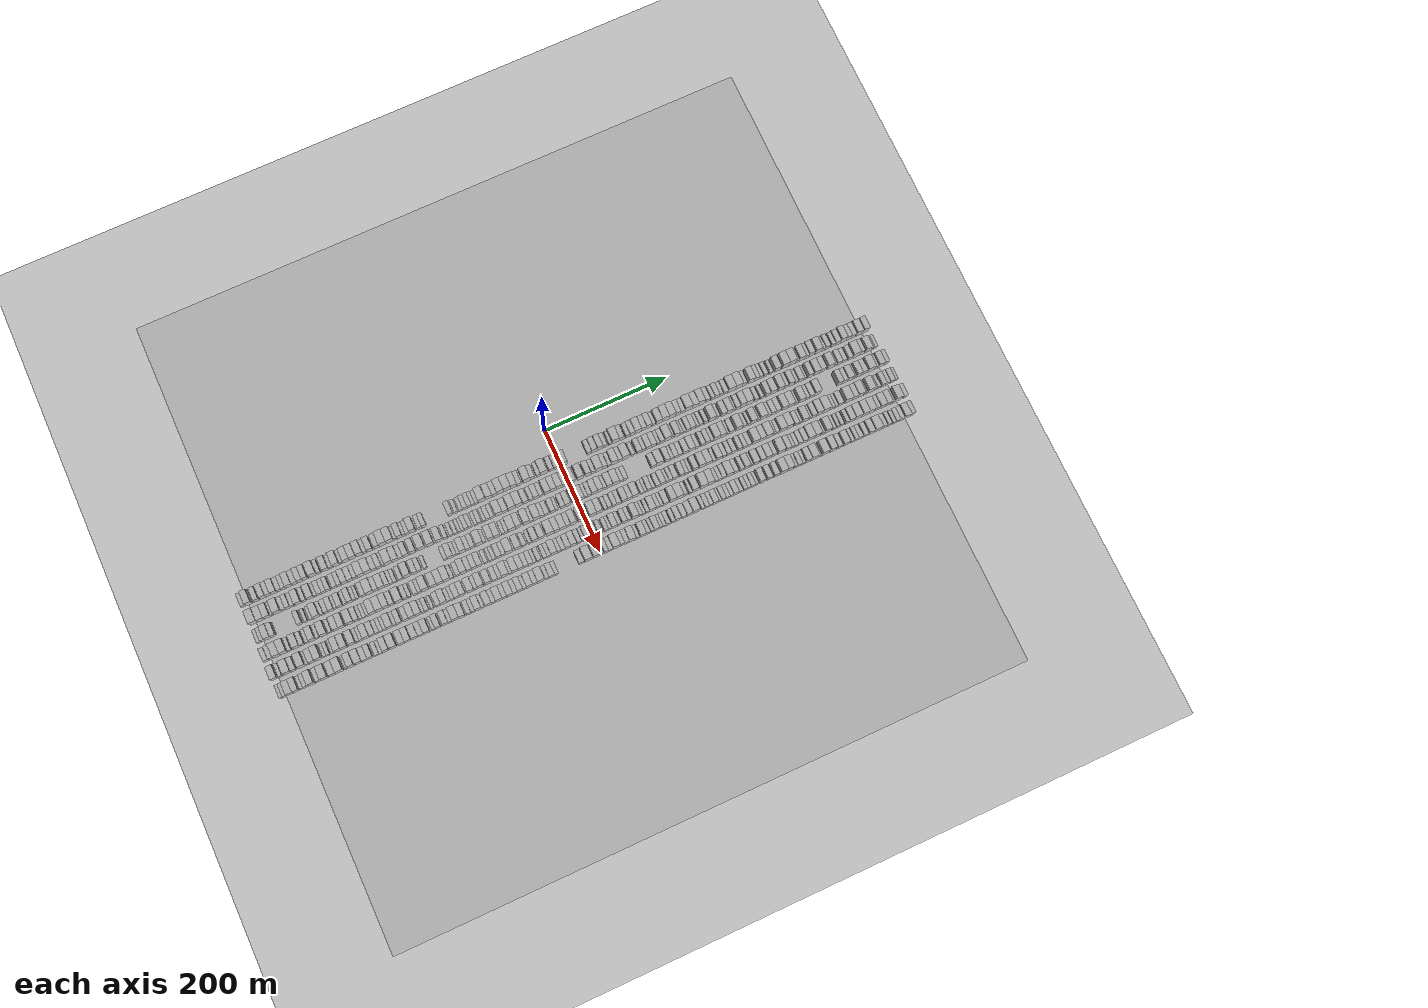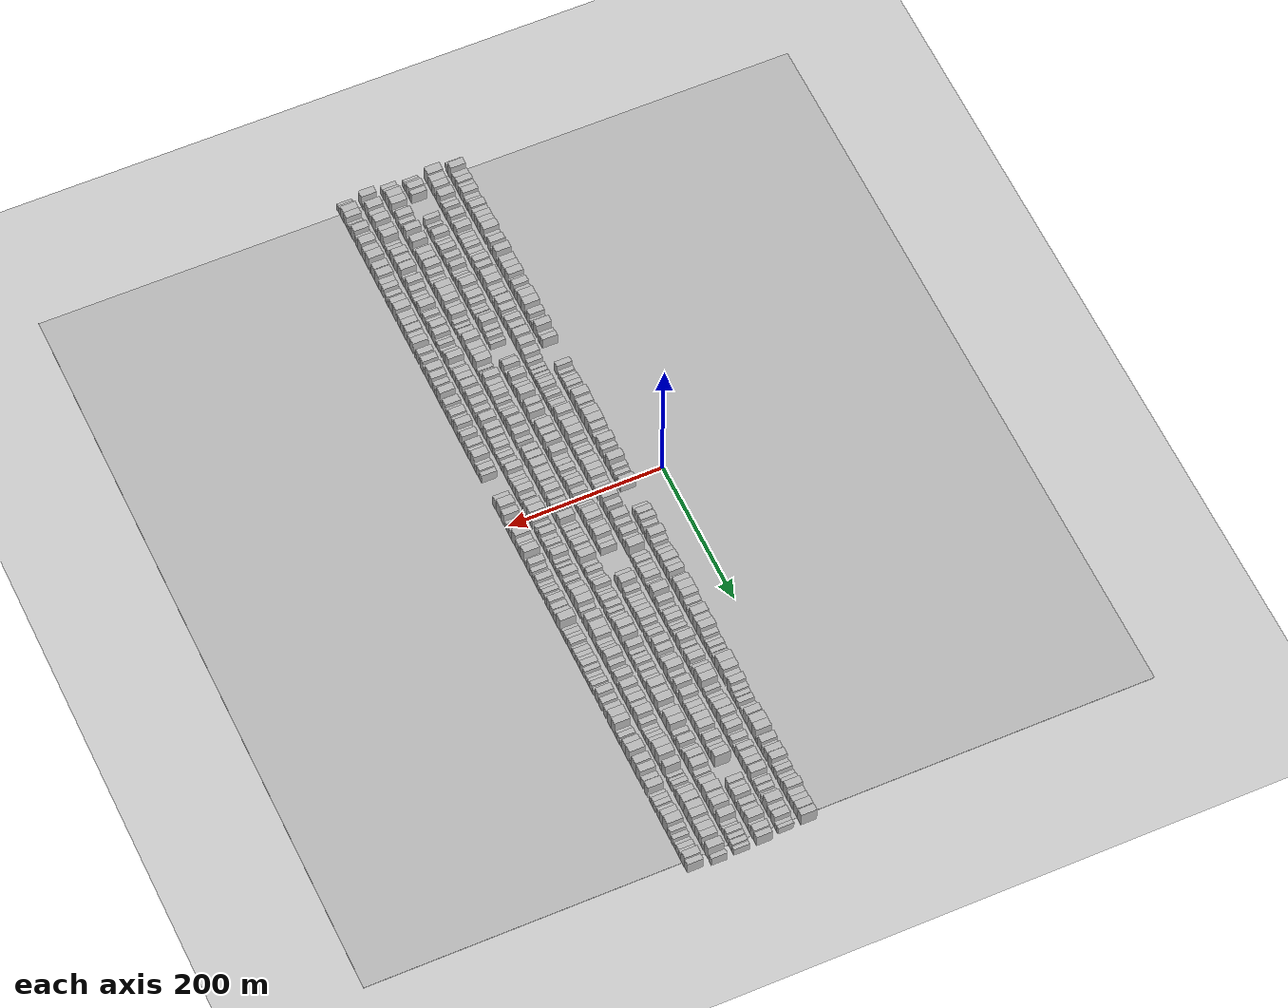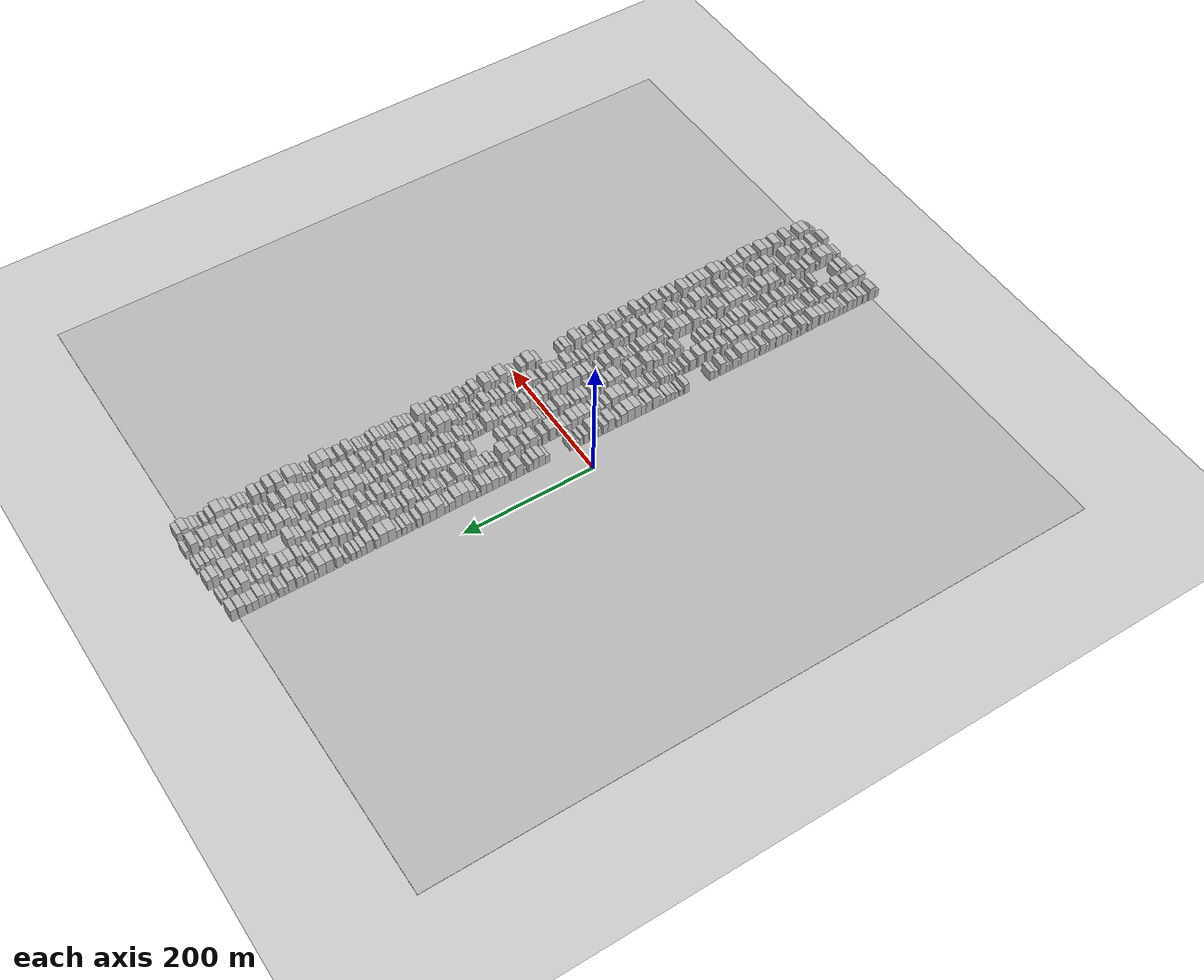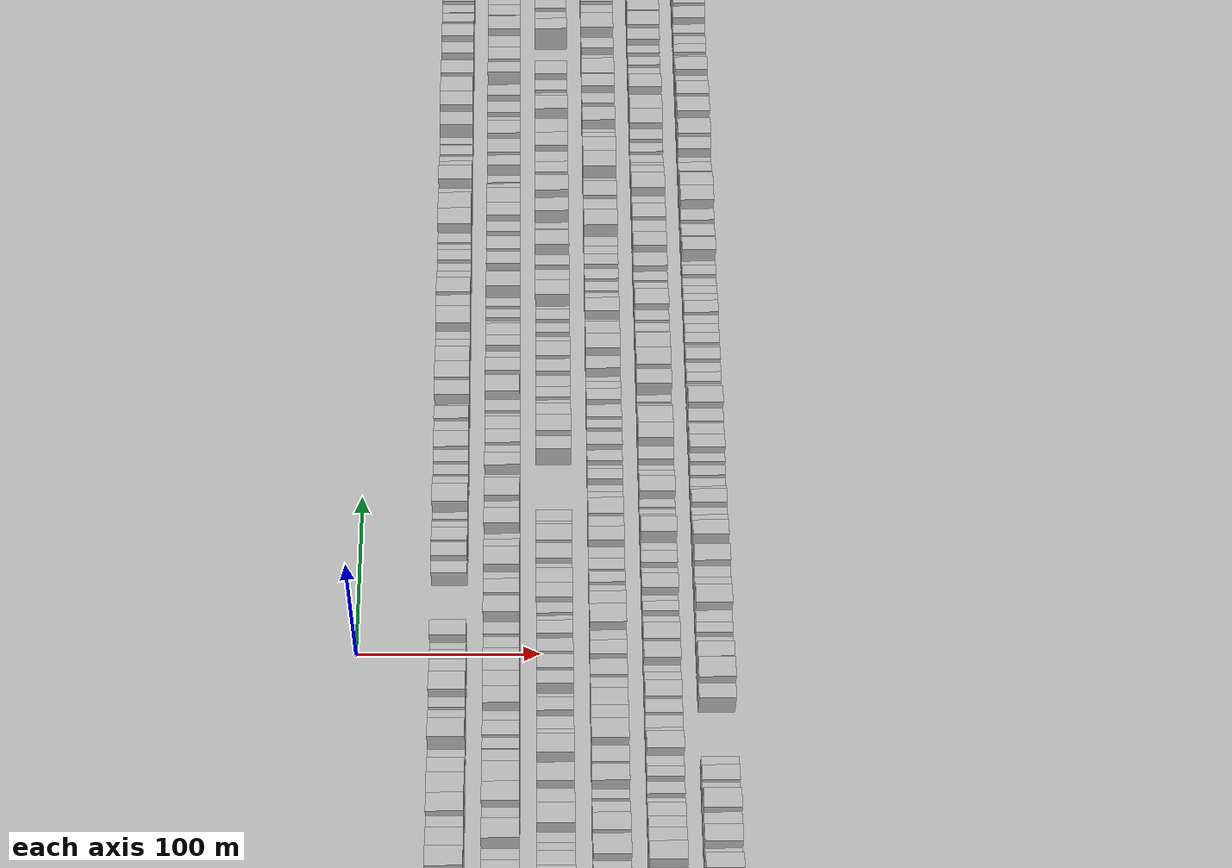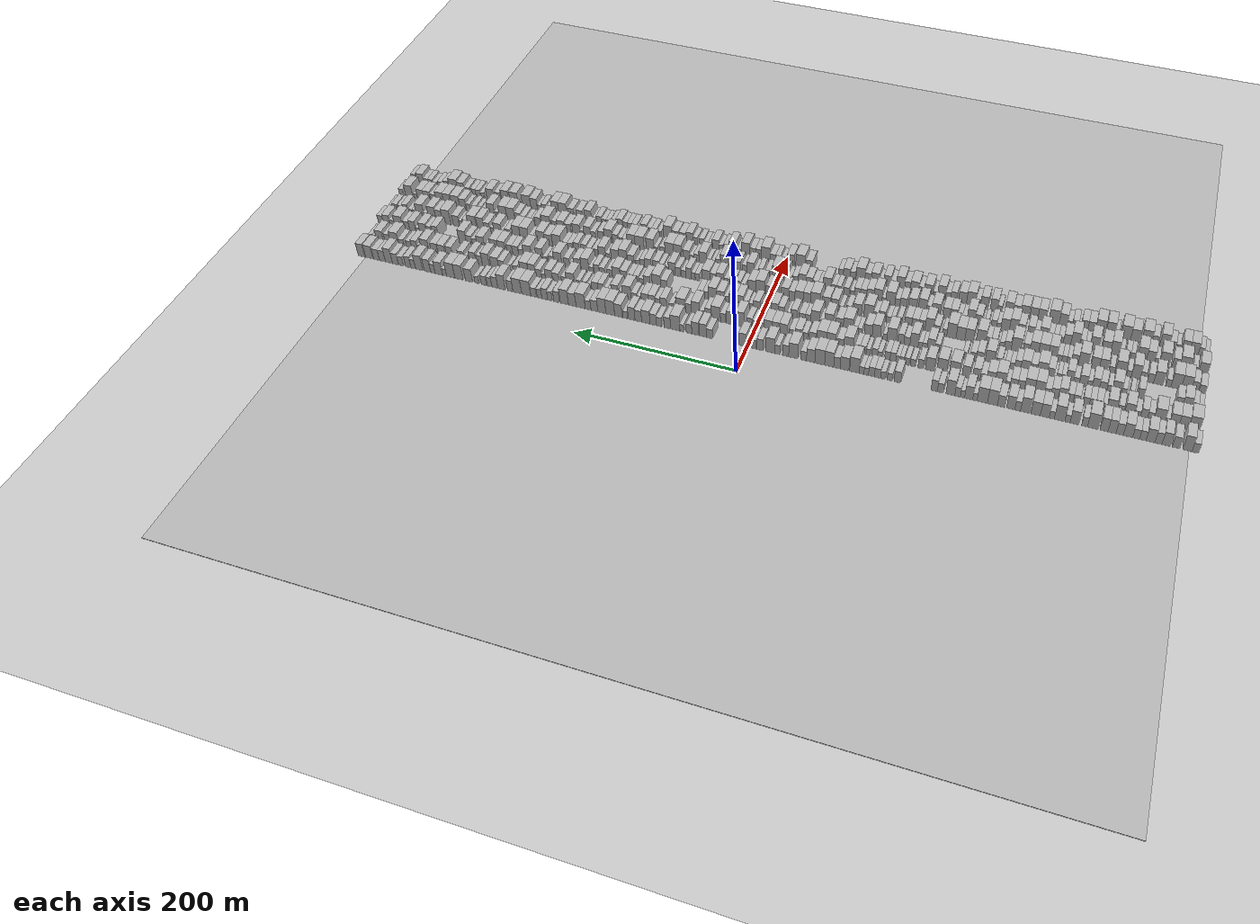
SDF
<?xml version="1.0" encoding="utf-8"?>

<sdf version="1.6">

   <world name="default">

      <gui fullscreen="0">

         <camera name="user_camera">

            <pose>-15 0 4.57585 0 0 0</pose>

            <view_controller>orbit</view_controller>

         </camera>

      </gui>

      <scene>

         <sky>

           <clouds>

             <speed>12</speed>

           </clouds>

         </sky>

         <ambient>0.4 0.4 0.4 1</ambient>

         <background>0.7 0.7 0.7 1</background>

         <shadows>1</shadows>

      </scene>

      <gravity>0 0 -9.8066</gravity>

      <magnetic_field>6e-06 2.3e-05 -4.2e-05</magnetic_field>

      <physics default="0" name="default_physics" type="ode">

         <ode>

            <solver>

               <type>quick</type>

               <iters>10</iters>

               <sor>1.0</sor>

               <use_dynamic_moi_rescaling>0</use_dynamic_moi_rescaling>

            </solver>

            <constraints>

               <cfm>0</cfm>

               <erp>0.2</erp>

               <contact_max_correcting_vel>100</contact_max_correcting_vel>

               <contact_surface_layer>0.001</contact_surface_layer>

            </constraints>

         </ode>

         <max_step_size>0.004</max_step_size>

         <real_time_factor>1</real_time_factor>

         <real_time_update_rate>250</real_time_update_rate>

      </physics>

      <light name="sun" type="directional">

         <cast_shadows>1</cast_shadows>

         <pose>0 0 10 0 0 0</pose>

         <diffuse>0.8 0.8 0.8 1</diffuse>

         <specular>0.2 0.2 0.2 1</specular>

         <attenuation>

            <range>1000</range>

            <constant>0.9</constant>

            <linear>0.01</linear>

            <quadratic>0.001</quadratic>

         </attenuation>

         <direction>-0.5 0.1 -0.9</direction>

      </light>

      <include>

         <name>ground_plane_1</name>

         <uri>model://HANNAS_ground_plane</uri>

         <pose>0 0 0  0 0 0</pose>

      </include>

      <include>

         <name>ground_plane_2</name>

         <uri>model://HANNAS_ground_plane</uri>

         <pose>100 0 0  0 0 0</pose>

      </include>

      <model name="building_1">

         <static>1</static>

         <pose frame="">50.0000 -506.4859 0 0.000000 0.000000 0.000000</pose>

         <link name="link">

            <pose frame="">0 0 7.50 0 0 0</pose>

            <collision name="collision">

               <geometry>

                  <box>

                     <size>20.0000 7.0282 15.0000</size>

                  </box>

               </geometry>

               <max_contacts>10</max_contacts>

               <surface>

                  <contact>

                     <ode/>

                  </contact>

                  <bounce/>

                  <friction>

                     <torsional>

                        <ode/>

                     </torsional>

                     <ode/>

                  </friction>

               </surface>

            </collision>

            <visual name="visual">

               <cast_shadows>0</cast_shadows>

               <geometry>

                  <box>

                     <size>20.0000 7.0282 15.0000</size>

                  </box>

               </geometry>

               <material>

                  <script>

                     <uri>model://HANNAS_wall/materials/scripts</uri>

                     <uri>model://HANNAS_wall/materials/textures</uri>

                     <name>vrc/HANNAS_wall</name>

                  </script>

               </material>

            </visual>

            <self_collide>0</self_collide>

            <enable_wind>0</enable_wind>

            <kinematic>0</kinematic>

         </link>

      </model>

      <model name="building_2">

         <static>1</static>

         <pose frame="">50.0000 -498.0735 0 0.000000 0.000000 0.000000</pose>

         <link name="link">

            <pose frame="">0 0 12.00 0 0 0</pose>

            <collision name="collision">

               <geometry>

                  <box>

                     <size>20.0000 9.7965 24.0000</size>

                  </box>

               </geometry>

               <max_contacts>10</max_contacts>

               <surface>

                  <contact>

                     <ode/>

                  </contact>

                  <bounce/>

                  <friction>

                     <torsional>

                        <ode/>

                     </torsional>

                     <ode/>

                  </friction>

               </surface>

            </collision>

            <visual name="visual">

               <cast_shadows>0</cast_shadows>

               <geometry>

                  <box>

                     <size>20.0000 9.7965 24.0000</size>

                  </box>

               </geometry>

               <material>

                  <script>

                     <uri>model://HANNAS_wall/materials/scripts</uri>

                     <uri>model://HANNAS_wall/materials/textures</uri>

                     <name>vrc/HANNAS_wall</name>

                  </script>

               </material>

            </visual>

            <self_collide>0</self_collide>

            <enable_wind>0</enable_wind>

            <kinematic>0</kinematic>

         </link>

      </model>

      <model name="building_3">

         <static>1</static>

         <pose frame="">50.0000 -486.1801 0 0.000000 0.000000 0.000000</pose>

         <link name="link">

            <pose frame="">0 0 9.00 0 0 0</pose>

            <collision name="collision">

               <geometry>

                  <box>

                     <size>20.0000 7.9903 18.0000</size>

                  </box>

               </geometry>

               <max_contacts>10</max_contacts>

               <surface>

                  <contact>

                     <ode/>

                  </contact>

                  <bounce/>

                  <friction>

                     <torsional>

                        <ode/>

                     </torsional>

                     <ode/>

                  </friction>

               </surface>

            </collision>

            <visual name="visual">

               <cast_shadows>0</cast_shadows>

               <geometry>

                  <box>

                     <size>20.0000 7.9903 18.0000</size>

                  </box>

               </geometry>

               <material>

                  <script>

                     <uri>model://HANNAS_wall/materials/scripts</uri>

                     <uri>model://HANNAS_wall/materials/textures</uri>

                     <name>vrc/HANNAS_wall</name>

                  </script>

               </material>

            </visual>

            <self_collide>0</self_collide>

            <enable_wind>0</enable_wind>

            <kinematic>0</kinematic>

         </link>

      </model>

      <model name="building_4">

         <static>1</static>

         <pose frame="">50.0000 -475.7172 0 0.000000 0.000000 0.000000</pose>

         <link name="link">

            <pose frame="">0 0 10.50 0 0 0</pose>

            <collision name="collision">

               <geometry>

                  <box>

                     <size>20.0000 8.9356 21.0000</size>

                  </box>

               </geometry>

               <max_contacts>10</max_contacts>

               <surface>

                  <contact>

                     <ode/>

                  </contact>

                  <bounce/>

                  <friction>

                     <torsional>

                        <ode/>

                     </torsional>

                     <ode/>

                  </friction>

               </surface>

            </collision>

            <visual name="visual">

               <cast_shadows>0</cast_shadows>

               <geometry>

                  <box>

                     <size>20.0000 8.9356 21.0000</size>

                  </box>

               </geometry>

               <material>

                  <script>

                     <uri>model://HANNAS_wall/materials/scripts</uri>

                     <uri>model://HANNAS_wall/materials/textures</uri>

                     <name>vrc/HANNAS_wall</name>

                  </script>

               </material>

            </visual>

            <self_collide>0</self_collide>

            <enable_wind>0</enable_wind>

            <kinematic>0</kinematic>

         </link>

      </model>

      <model name="building_5">

         <static>1</static>

         <pose frame="">50.0000 -467.5836 0 0.000000 0.000000 0.000000</pose>

         <link name="link">

            <pose frame="">0 0 9.00 0 0 0</pose>

            <collision name="collision">

               <geometry>

                  <box>

                     <size>20.0000 7.3315 18.0000</size>

                  </box>

               </geometry>

               <max_contacts>10</max_contacts>

               <surface>

                  <contact>

                     <ode/>

                  </contact>

                  <bounce/>

                  <friction>

                     <torsional>

                        <ode/>

                     </torsional>

                     <ode/>

                  </friction>

               </surface>

            </collision>

            <visual name="visual">

               <cast_shadows>0</cast_shadows>

               <geometry>

                  <box>

                     <size>20.0000 7.3315 18.0000</size>

                  </box>

               </geometry>

               <material>

                  <script>

                     <uri>model://HANNAS_wall/materials/scripts</uri>

                     <uri>model://HANNAS_wall/materials/textures</uri>

                     <name>vrc/HANNAS_wall</name>

                  </script>

               </material>

            </visual>

            <self_collide>0</self_collide>

            <enable_wind>0</enable_wind>

            <kinematic>0</kinematic>

         </link>

      </model>

      <model name="building_6">

         <static>1</static>

         <pose frame="">50.0000 -459.0669 0 0.000000 0.000000 0.000000</pose>

         <link name="link">

            <pose frame="">0 0 10.50 0 0 0</pose>

            <collision name="collision">

               <geometry>

                  <box>

                     <size>20.0000 9.7020 21.0000</size>

                  </box>

               </geometry>

               <max_contacts>10</max_contacts>

               <surface>

                  <contact>

                     <ode/>

                  </contact>

                  <bounce/>

                  <friction>

                     <torsional>

                        <ode/>

                     </torsional>

                     <ode/>

                  </friction>

               </surface>

            </collision>

            <visual name="visual">

               <cast_shadows>0</cast_shadows>

               <geometry>

                  <box>

                     <size>20.0000 9.7020 21.0000</size>

                  </box>

               </geometry>

               <material>

                  <script>

                     <uri>model://HANNAS_wall/materials/scripts</uri>

                     <uri>model://HANNAS_wall/materials/textures</uri>

                     <name>vrc/HANNAS_wall</name>

                  </script>

               </material>

            </visual>

            <self_collide>0</self_collide>

            <enable_wind>0</enable_wind>

            <kinematic>0</kinematic>

         </link>

      </model>

      <model name="building_7">

         <static>1</static>

         <pose frame="">50.0000 -450.8194 0 0.000000 0.000000 0.000000</pose>

         <link name="link">

            <pose frame="">0 0 7.50 0 0 0</pose>

            <collision name="collision">

               <geometry>

                  <box>

                     <size>20.0000 6.7930 15.0000</size>

                  </box>

               </geometry>

               <max_contacts>10</max_contacts>

               <surface>

                  <contact>

                     <ode/>

                  </contact>

                  <bounce/>

                  <friction>

                     <torsional>

                        <ode/>

                     </torsional>

                     <ode/>

                  </friction>

               </surface>

            </collision>

            <visual name="visual">

               <cast_shadows>0</cast_shadows>

               <geometry>

                  <box>

                     <size>20.0000 6.7930 15.0000</size>

                  </box>

               </geometry>

               <material>

                  <script>

                     <uri>model://HANNAS_wall/materials/scripts</uri>

                     <uri>model://HANNAS_wall/materials/textures</uri>

                     <name>vrc/HANNAS_wall</name>

                  </script>

               </material>

            </visual>

            <self_collide>0</self_collide>

            <enable_wind>0</enable_wind>

            <kinematic>0</kinematic>

         </link>

      </model>

      <model name="building_8">

         <static>1</static>

         <pose frame="">50.0000 -443.7430 0 0.000000 0.000000 0.000000</pose>

         <link name="link">

            <pose frame="">0 0 7.50 0 0 0</pose>

            <collision name="collision">

               <geometry>

                  <box>

                     <size>20.0000 7.3599 15.0000</size>

                  </box>

               </geometry>

               <max_contacts>10</max_contacts>

               <surface>

                  <contact>

                     <ode/>

                  </contact>

                  <bounce/>

                  <friction>

                     <torsional>

                        <ode/>

                     </torsional>

                     <ode/>

                  </friction>

               </surface>

            </collision>

            <visual name="visual">

               <cast_shadows>0</cast_shadows>

               <geometry>

                  <box>

                     <size>20.0000 7.3599 15.0000</size>

                  </box>

               </geometry>

               <material>

                  <script>

                     <uri>model://HANNAS_wall/materials/scripts</uri>

                     <uri>model://HANNAS_wall/materials/textures</uri>

                     <name>vrc/HANNAS_wall</name>

                  </script>

               </material>

            </visual>

            <self_collide>0</self_collide>

            <enable_wind>0</enable_wind>

            <kinematic>0</kinematic>

         </link>

      </model>

      <model name="building_9">

         <static>1</static>

         <pose frame="">50.0000 -435.0999 0 0.000000 0.000000 0.000000</pose>

         <link name="link">

            <pose frame="">0 0 10.50 0 0 0</pose>

            <collision name="collision">

               <geometry>

                  <box>

                     <size>20.0000 9.9263 21.0000</size>

                  </box>

               </geometry>

               <max_contacts>10</max_contacts>

               <surface>

                  <contact>

                     <ode/>

                  </contact>

                  <bounce/>

                  <friction>

                     <torsional>

                        <ode/>

                     </torsional>

                     <ode/>

                  </friction>

               </surface>

            </collision>

            <visual name="visual">

               <cast_shadows>0</cast_shadows>

               <geometry>

                  <box>

                     <size>20.0000 9.9263 21.0000</size>

                  </box>

               </geometry>

               <material>

                  <script>

                     <uri>model://HANNAS_wall/materials/scripts</uri>

                     <uri>model://HANNAS_wall/materials/textures</uri>

                     <name>vrc/HANNAS_wall</name>

                  </script>

               </material>

            </visual>

            <self_collide>0</self_collide>

            <enable_wind>0</enable_wind>

            <kinematic>0</kinematic>

         </link>

      </model>

      <model name="building_10">

         <static>1</static>

         <pose frame="">50.0000 -426.1327 0 0.000000 0.000000 0.000000</pose>

         <link name="link">

            <pose frame="">0 0 9.00 0 0 0</pose>

            <collision name="collision">

               <geometry>

                  <box>

                     <size>20.0000 8.0081 18.0000</size>

                  </box>

               </geometry>

               <max_contacts>10</max_contacts>

               <surface>

                  <contact>

                     <ode/>

                  </contact>

                  <bounce/>

                  <friction>

                     <torsional>

                        <ode/>

                     </torsional>

                     <ode/>

                  </friction>

               </surface>

            </collision>

            <visual name="visual">

               <cast_shadows>0</cast_shadows>

               <geometry>

                  <box>

                     <size>20.0000 8.0081 18.0000</size>

                  </box>

               </geometry>

               <material>

                  <script>

                     <uri>model://HANNAS_wall/materials/scripts</uri>

                     <uri>model://HANNAS_wall/materials/textures</uri>

                     <name>vrc/HANNAS_wall</name>

                  </script>

               </material>

            </visual>

            <self_collide>0</self_collide>

            <enable_wind>0</enable_wind>

            <kinematic>0</kinematic>

         </link>

      </model>

      <model name="building_11">

         <static>1</static>

         <pose frame="">50.0000 -417.8920 0 0.000000 0.000000 0.000000</pose>

         <link name="link">

            <pose frame="">0 0 10.50 0 0 0</pose>

            <collision name="collision">

               <geometry>

                  <box>

                     <size>20.0000 8.4732 21.0000</size>

                  </box>

               </geometry>

               <max_contacts>10</max_contacts>

               <surface>

                  <contact>

                     <ode/>

                  </contact>

                  <bounce/>

                  <friction>

                     <torsional>

                        <ode/>

                     </torsional>

                     <ode/>

                  </friction>

               </surface>

            </collision>

            <visual name="visual">

               <cast_shadows>0</cast_shadows>

               <geometry>

                  <box>

                     <size>20.0000 8.4732 21.0000</size>

                  </box>

               </geometry>

               <material>

                  <script>

                     <uri>model://HANNAS_wall/materials/scripts</uri>

                     <uri>model://HANNAS_wall/materials/textures</uri>

                     <name>vrc/HANNAS_wall</name>

                  </script>

               </material>

            </visual>

            <self_collide>0</self_collide>

            <enable_wind>0</enable_wind>

            <kinematic>0</kinematic>

         </link>

      </model>

      <model name="building_12">

         <static>1</static>

         <pose frame="">50.0000 -409.3800 0 0.000000 0.000000 0.000000</pose>

         <link name="link">

            <pose frame="">0 0 10.50 0 0 0</pose>

            <collision name="collision">

               <geometry>

                  <box>

                     <size>20.0000 8.5509 21.0000</size>

                  </box>

               </geometry>

               <max_contacts>10</max_contacts>

               <surface>

                  <contact>

                     <ode/>

                  </contact>

                  <bounce/>

                  <friction>

                     <torsional>

                        <ode/>

                     </torsional>

                     <ode/>

                  </friction>

               </surface>

            </collision>

            <visual name="visual">

               <cast_shadows>0</cast_shadows>

               <geometry>

                  <box>

                     <size>20.0000 8.5509 21.0000</size>

                  </box>

               </geometry>

               <material>

                  <script>

                     <uri>model://HANNAS_wall/materials/scripts</uri>

                     <uri>model://HANNAS_wall/materials/textures</uri>

                     <name>vrc/HANNAS_wall</name>

                  </script>

               </material>

            </visual>

            <self_collide>0</self_collide>

            <enable_wind>0</enable_wind>

            <kinematic>0</kinematic>

         </link>

      </model>

      <model name="building_13">

         <static>1</static>

         <pose frame="">50.0000 -397.2692 0 0.000000 0.000000 0.000000</pose>

         <link name="link">

            <pose frame="">0 0 12.00 0 0 0</pose>

            <collision name="collision">

               <geometry>

                  <box>

                     <size>20.0000 11.6706 24.0000</size>

                  </box>

               </geometry>

               <max_contacts>10</max_contacts>

               <surface>

                  <contact>

                     <ode/>

                  </contact>

                  <bounce/>

                  <friction>

                     <torsional>

                        <ode/>

                     </torsional>

                     <ode/>

                  </friction>

               </surface>

            </collision>

            <visual name="visual">

               <cast_shadows>0</cast_shadows>

               <geometry>

                  <box>

                     <size>20.0000 11.6706 24.0000</size>

                  </box>

               </geometry>

               <material>

                  <script>

                     <uri>model://HANNAS_wall/materials/scripts</uri>

                     <uri>model://HANNAS_wall/materials/textures</uri>

                     <name>vrc/HANNAS_wall</name>

                  </script>

               </material>

            </visual>

            <self_collide>0</self_collide>

            <enable_wind>0</enable_wind>

            <kinematic>0</kinematic>

         </link>

      </model>

      <model name="building_14">

         <static>1</static>

         <pose frame="">50.0000 -388.3033 0 0.000000 0.000000 0.000000</pose>

         <link name="link">

            <pose frame="">0 0 7.50 0 0 0</pose>

            <collision name="collision">

               <geometry>

                  <box>

                     <size>20.0000 6.2612 15.0000</size>

                  </box>

               </geometry>

               <max_contacts>10</max_contacts>

               <surface>

                  <contact>

                     <ode/>

                  </contact>

                  <bounce/>

                  <friction>

                     <torsional>

                        <ode/>

                     </torsional>

                     <ode/>

                  </friction>

               </surface>

            </collision>

            <visual name="visual">

               <cast_shadows>0</cast_shadows>

               <geometry>

                  <box>

                     <size>20.0000 6.2612 15.0000</size>

                  </box>

               </geometry>

               <material>

                  <script>

                     <uri>model://HANNAS_wall/materials/scripts</uri>

                     <uri>model://HANNAS_wall/materials/textures</uri>

                     <name>vrc/HANNAS_wall</name>

                  </script>

               </material>

            </visual>

            <self_collide>0</self_collide>

            <enable_wind>0</enable_wind>

            <kinematic>0</kinematic>

         </link>

      </model>

      <model name="building_15">

         <static>1</static>

         <pose frame="">50.0000 -377.3588 0 0.000000 0.000000 0.000000</pose>

         <link name="link">

            <pose frame="">0 0 10.50 0 0 0</pose>

            <collision name="collision">

               <geometry>

                  <box>

                     <size>20.0000 9.6278 21.0000</size>

                  </box>

               </geometry>

               <max_contacts>10</max_contacts>

               <surface>

                  <contact>

                     <ode/>

                  </contact>

                  <bounce/>

                  <friction>

                     <torsional>

                        <ode/>

                     </torsional>

                     <ode/>

                  </friction>

               </surface>

            </collision>

            <visual name="visual">

               <cast_shadows>0</cast_shadows>

               <geometry>

                  <box>

                     <size>20.0000 9.6278 21.0000</size>

                  </box>

               </geometry>

               <material>

                  <script>

                     <uri>model://HANNAS_wall/materials/scripts</uri>

                     <uri>model://HANNAS_wall/materials/textures</uri>

                     <name>vrc/HANNAS_wall</name>

                  </script>

               </material>

            </visual>

            <self_collide>0</self_collide>

            <enable_wind>0</enable_wind>

            <kinematic>0</kinematic>

         </link>

      </model>

      <model name="building_16">

         <static>1</static>

         <pose frame="">50.0000 -369.7086 0 0.000000 0.000000 0.000000</pose>

         <link name="link">

            <pose frame="">0 0 6.00 0 0 0</pose>

            <collision name="collision">

               <geometry>

                  <box>

                     <size>20.0000 5.6726 12.0000</size>

                  </box>

               </geometry>

               <max_contacts>10</max_contacts>

               <surface>

                  <contact>

                     <ode/>

                  </contact>

                  <bounce/>

                  <friction>

                     <torsional>

                        <ode/>

                     </torsional>

                     <ode/>

                  </friction>

               </surface>

            </collision>

            <visual name="visual">

               <cast_shadows>0</cast_shadows>

               <geometry>

                  <box>

                     <size>20.0000 5.6726 12.0000</size>

                  </box>

               </geometry>

               <material>

                  <script>

                     <uri>model://HANNAS_wall/materials/scripts</uri>

                     <uri>model://HANNAS_wall/materials/textures</uri>

                     <name>vrc/HANNAS_wall</name>

                  </script>

               </material>

            </visual>

            <self_collide>0</self_collide>

            <enable_wind>0</enable_wind>

            <kinematic>0</kinematic>

         </link>

      </model>

      <model name="building_17">

         <static>1</static>

         <pose frame="">50.0000 -360.5614 0 0.000000 0.000000 0.000000</pose>

         <link name="link">

            <pose frame="">0 0 12.00 0 0 0</pose>

            <collision name="collision">

               <geometry>

                  <box>

                     <size>20.0000 10.6218 24.0000</size>

                  </box>

               </geometry>

               <max_contacts>10</max_contacts>

               <surface>

                  <contact>

                     <ode/>

                  </contact>

                  <bounce/>

                  <friction>

                     <torsional>

                        <ode/>

                     </torsional>

                     <ode/>

                  </friction>

               </surface>

            </collision>

            <visual name="visual">

               <cast_shadows>0</cast_shadows>

               <geometry>

                  <box>

                     <size>20.0000 10.6218 24.0000</size>

                  </box>

               </geometry>

               <material>

                  <script>

                     <uri>model://HANNAS_wall/materials/scripts</uri>

                     <uri>model://HANNAS_wall/materials/textures</uri>

                     <name>vrc/HANNAS_wall</name>

                  </script>

               </material>

            </visual>

            <self_collide>0</self_collide>

            <enable_wind>0</enable_wind>

            <kinematic>0</kinematic>

         </link>

      </model>

      <model name="building_18">

         <static>1</static>

         <pose frame="">50.0000 -352.4591 0 0.000000 0.000000 0.000000</pose>

         <link name="link">

            <pose frame="">0 0 6.00 0 0 0</pose>

            <collision name="collision">

               <geometry>

                  <box>

                     <size>20.0000 5.5828 12.0000</size>

                  </box>

               </geometry>

               <max_contacts>10</max_contacts>

               <surface>

                  <contact>

                     <ode/>

                  </contact>

                  <bounce/>

                  <friction>

                     <torsional>

                        <ode/>

                     </torsional>

                     <ode/>

                  </friction>

               </surface>

            </collision>

            <visual name="visual">

               <cast_shadows>0</cast_shadows>

               <geometry>

                  <box>

                     <size>20.0000 5.5828 12.0000</size>

                  </box>

               </geometry>

               <material>

                  <script>

                     <uri>model://HANNAS_wall/materials/scripts</uri>

                     <uri>model://HANNAS_wall/materials/textures</uri>

                     <name>vrc/HANNAS_wall</name>

                  </script>

               </material>

            </visual>

            <self_collide>0</self_collide>

            <enable_wind>0</enable_wind>

            <kinematic>0</kinematic>

         </link>

      </model>

      <model name="building_19">

         <static>1</static>

         <pose frame="">50.0000 -344.7563 0 0.000000 0.000000 0.000000</pose>

         <link name="link">

            <pose frame="">0 0 10.50 0 0 0</pose>

            <collision name="collision">

               <geometry>

                  <box>

                     <size>20.0000 9.8227 21.0000</size>

                  </box>

               </geometry>

               <max_contacts>10</max_contacts>

               <surface>

                  <contact>

                     <ode/>

                  </contact>

                  <bounce/>

                  <friction>

                     <torsional>

                        <ode/>

                     </torsional>

                     <ode/>

                  </friction>

               </surface>

            </collision>

            <visual name="visual">

               <cast_shadows>0</cast_shadows>

               <geometry>

                  <box>

                     <size>20.0000 9.8227 21.0000</size>

                  </box>

               </geometry>

               <material>

                  <script>

                     <uri>model://HANNAS_wall/materials/scripts</uri>

                     <uri>model://HANNAS_wall/materials/textures</uri>

                     <name>vrc/HANNAS_wall</name>

                  </script>

               </material>

            </visual>

            <self_collide>0</self_collide>

            <enable_wind>0</enable_wind>

            <kinematic>0</kinematic>

         </link>

      </model>

      <model name="building_20">

         <static>1</static>

         <pose frame="">50.0000 -334.6631 0 0.000000 0.000000 0.000000</pose>

         <link name="link">

            <pose frame="">0 0 10.50 0 0 0</pose>

            <collision name="collision">

               <geometry>

                  <box>

                     <size>20.0000 10.3638 21.0000</size>

                  </box>

               </geometry>

               <max_contacts>10</max_contacts>

               <surface>

                  <contact>

                     <ode/>

                  </contact>

                  <bounce/>

                  <friction>

                     <torsional>

                        <ode/>

                     </torsional>

                     <ode/>

                  </friction>

               </surface>

            </collision>

            <visual name="visual">

               <cast_shadows>0</cast_shadows>

               <geometry>

                  <box>

                     <size>20.0000 10.3638 21.0000</size>

                  </box>

               </geometry>

               <material>

                  <script>

                     <uri>model://HANNAS_wall/materials/scripts</uri>

                     <uri>model://HANNAS_wall/materials/textures</uri>

                     <name>vrc/HANNAS_wall</name>

                  </script>

               </material>

            </visual>

            <self_collide>0</self_collide>

            <enable_wind>0</enable_wind>

            <kinematic>0</kinematic>

         </link>

      </model>

      <model name="building_21">

         <static>1</static>

         <pose frame="">50.0000 -323.2342 0 0.000000 0.000000 0.000000</pose>

         <link name="link">

            <pose frame="">0 0 12.00 0 0 0</pose>

            <collision name="collision">

               <geometry>

                  <box>

                     <size>20.0000 10.4941 24.0000</size>

                  </box>

               </geometry>

               <max_contacts>10</max_contacts>

               <surface>

                  <contact>

                     <ode/>

                  </contact>

                  <bounce/>

                  <friction>

                     <torsional>

                        <ode/>

                     </torsional>

                     <ode/>

                  </friction>

               </surface>

            </collision>

            <visual name="visual">

               <cast_shadows>0</cast_shadows>

               <geometry>

                  <box>

                     <size>20.0000 10.4941 24.0000</size>

                  </box>

               </geometry>

               <material>

                  <script>

                     <uri>model://HANNAS_wall/materials/scripts</uri>

                     <uri>model://HANNAS_wall/materials/textures</uri>

                     <name>vrc/HANNAS_wall</name>

                  </script>

               </material>

            </visual>

            <self_collide>0</self_collide>

            <enable_wind>0</enable_wind>

            <kinematic>0</kinematic>

         </link>

      </model>

      <model name="building_22">

         <static>1</static>

         <pose frame="">50.0000 -314.8423 0 0.000000 0.000000 0.000000</pose>

         <link name="link">

            <pose frame="">0 0 7.50 0 0 0</pose>

            <collision name="collision">

               <geometry>

                  <box>

                     <size>20.0000 6.2897 15.0000</size>

                  </box>

               </geometry>

               <max_contacts>10</max_contacts>

               <surface>

                  <contact>

                     <ode/>

                  </contact>

                  <bounce/>

                  <friction>

                     <torsional>

                        <ode/>

                     </torsional>

                     <ode/>

                  </friction>

               </surface>

            </collision>

            <visual name="visual">

               <cast_shadows>0</cast_shadows>

               <geometry>

                  <box>

                     <size>20.0000 6.2897 15.0000</size>

                  </box>

               </geometry>

               <material>

                  <script>

                     <uri>model://HANNAS_wall/materials/scripts</uri>

                     <uri>model://HANNAS_wall/materials/textures</uri>

                     <name>vrc/HANNAS_wall</name>

                  </script>

               </material>

            </visual>

            <self_collide>0</self_collide>

            <enable_wind>0</enable_wind>

            <kinematic>0</kinematic>

         </link>

      </model>

      <model name="building_23">

         <static>1</static>

         <pose frame="">50.0000 -307.0601 0 0.000000 0.000000 0.000000</pose>

         <link name="link">

            <pose frame="">0 0 10.50 0 0 0</pose>

            <collision name="collision">

               <geometry>

                  <box>

                     <size>20.0000 9.2747 21.0000</size>

                  </box>

               </geometry>

               <max_contacts>10</max_contacts>

               <surface>

                  <contact>

                     <ode/>

                  </contact>

                  <bounce/>

                  <friction>

                     <torsional>

                        <ode/>

                     </torsional>

                     <ode/>

                  </friction>

               </surface>

            </collision>

            <visual name="visual">

               <cast_shadows>0</cast_shadows>

               <geometry>

                  <box>

                     <size>20.0000 9.2747 21.0000</size>

                  </box>

               </geometry>

               <material>

                  <script>

                     <uri>model://HANNAS_wall/materials/scripts</uri>

                     <uri>model://HANNAS_wall/materials/textures</uri>

                     <name>vrc/HANNAS_wall</name>

                  </script>

               </material>

            </visual>

            <self_collide>0</self_collide>

            <enable_wind>0</enable_wind>

            <kinematic>0</kinematic>

         </link>

      </model>

      <model name="building_24">

         <static>1</static>

         <pose frame="">50.0000 -296.2908 0 0.000000 0.000000 0.000000</pose>

         <link name="link">

            <pose frame="">0 0 9.00 0 0 0</pose>

            <collision name="collision">

               <geometry>

                  <box>

                     <size>20.0000 8.2640 18.0000</size>

                  </box>

               </geometry>

               <max_contacts>10</max_contacts>

               <surface>

                  <contact>

                     <ode/>

                  </contact>

                  <bounce/>

                  <friction>

                     <torsional>

                        <ode/>

                     </torsional>

                     <ode/>

                  </friction>

               </surface>

            </collision>

            <visual name="visual">

               <cast_shadows>0</cast_shadows>

               <geometry>

                  <box>

                     <size>20.0000 8.2640 18.0000</size>

                  </box>

               </geometry>

               <material>

                  <script>

                     <uri>model://HANNAS_wall/materials/scripts</uri>

                     <uri>model://HANNAS_wall/materials/textures</uri>

                     <name>vrc/HANNAS_wall</name>

                  </script>

               </material>

            </visual>

            <self_collide>0</self_collide>

            <enable_wind>0</enable_wind>

            <kinematic>0</kinematic>

         </link>

      </model>

      <model name="building_25">

         <static>1</static>

         <pose frame="">50.0000 -286.5945 0 0.000000 0.000000 0.000000</pose>

         <link name="link">

            <pose frame="">0 0 12.00 0 0 0</pose>

            <collision name="collision">

               <geometry>

                  <box>

                     <size>20.0000 11.1286 24.0000</size>

                  </box>

               </geometry>

               <max_contacts>10</max_contacts>

               <surface>

                  <contact>

                     <ode/>

                  </contact>

                  <bounce/>

                  <friction>

                     <torsional>

                        <ode/>

                     </torsional>

                     <ode/>

                  </friction>

               </surface>

            </collision>

            <visual name="visual">

               <cast_shadows>0</cast_shadows>

               <geometry>

                  <box>

                     <size>20.0000 11.1286 24.0000</size>

                  </box>

               </geometry>

               <material>

                  <script>

                     <uri>model://HANNAS_wall/materials/scripts</uri>

                     <uri>model://HANNAS_wall/materials/textures</uri>

                     <name>vrc/HANNAS_wall</name>

                  </script>

               </material>

            </visual>

            <self_collide>0</self_collide>

            <enable_wind>0</enable_wind>

            <kinematic>0</kinematic>

         </link>

      </model>

      <model name="building_26">

         <static>1</static>

         <pose frame="">50.0000 -275.2261 0 0.000000 0.000000 0.000000</pose>

         <link name="link">

            <pose frame="">0 0 12.00 0 0 0</pose>

            <collision name="collision">

               <geometry>

                  <box>

                     <size>20.0000 11.6081 24.0000</size>

                  </box>

               </geometry>

               <max_contacts>10</max_contacts>

               <surface>

                  <contact>

                     <ode/>

                  </contact>

                  <bounce/>

                  <friction>

                     <torsional>

                        <ode/>

                     </torsional>

                     <ode/>

                  </friction>

               </surface>

            </collision>

            <visual name="visual">

               <cast_shadows>0</cast_shadows>

               <geometry>

                  <box>

                     <size>20.0000 11.6081 24.0000</size>

                  </box>

               </geometry>

               <material>

                  <script>

                     <uri>model://HANNAS_wall/materials/scripts</uri>

                     <uri>model://HANNAS_wall/materials/textures</uri>

                     <name>vrc/HANNAS_wall</name>

                  </script>

               </material>

            </visual>

            <self_collide>0</self_collide>

            <enable_wind>0</enable_wind>

            <kinematic>0</kinematic>

         </link>

      </model>

      <model name="building_27">

         <static>1</static>

         <pose frame="">50.0000 -266.9249 0 0.000000 0.000000 0.000000</pose>

         <link name="link">

            <pose frame="">0 0 6.00 0 0 0</pose>

            <collision name="collision">

               <geometry>

                  <box>

                     <size>20.0000 4.9941 12.0000</size>

                  </box>

               </geometry>

               <max_contacts>10</max_contacts>

               <surface>

                  <contact>

                     <ode/>

                  </contact>

                  <bounce/>

                  <friction>

                     <torsional>

                        <ode/>

                     </torsional>

                     <ode/>

                  </friction>

               </surface>

            </collision>

            <visual name="visual">

               <cast_shadows>0</cast_shadows>

               <geometry>

                  <box>

                     <size>20.0000 4.9941 12.0000</size>

                  </box>

               </geometry>

               <material>

                  <script>

                     <uri>model://HANNAS_wall/materials/scripts</uri>

                     <uri>model://HANNAS_wall/materials/textures</uri>

                     <name>vrc/HANNAS_wall</name>

                  </script>

               </material>

            </visual>

            <self_collide>0</self_collide>

            <enable_wind>0</enable_wind>

            <kinematic>0</kinematic>

         </link>

      </model>

      <model name="building_28">

         <static>1</static>

         <pose frame="">50.0000 -259.8847 0 0.000000 0.000000 0.000000</pose>

         <link name="link">

            <pose frame="">0 0 10.50 0 0 0</pose>

            <collision name="collision">

               <geometry>

                  <box>

                     <size>20.0000 9.0863 21.0000</size>

                  </box>

               </geometry>

               <max_contacts>10</max_contacts>

               <surface>

                  <contact>

                     <ode/>

                  </contact>

                  <bounce/>

                  <friction>

                     <torsional>

                        <ode/>

                     </torsional>

                     <ode/>

                  </friction>

               </surface>

            </collision>

            <visual name="visual">

               <cast_shadows>0</cast_shadows>

               <geometry>

                  <box>

                     <size>20.0000 9.0863 21.0000</size>

                  </box>

               </geometry>

               <material>

                  <script>

                     <uri>model://HANNAS_wall/materials/scripts</uri>

                     <uri>model://HANNAS_wall/materials/textures</uri>

                     <name>vrc/HANNAS_wall</name>

                  </script>

               </material>

            </visual>

            <self_collide>0</self_collide>

            <enable_wind>0</enable_wind>

            <kinematic>0</kinematic>

         </link>

      </model>

      <model name="building_29">

         <static>1</static>

         <pose frame="">50.0000 -252.9270 0 0.000000 0.000000 0.000000</pose>

         <link name="link">

            <pose frame="">0 0 6.00 0 0 0</pose>

            <collision name="collision">

               <geometry>

                  <box>

                     <size>20.0000 4.8291 12.0000</size>

                  </box>

               </geometry>

               <max_contacts>10</max_contacts>

               <surface>

                  <contact>

                     <ode/>

                  </contact>

                  <bounce/>

                  <friction>

                     <torsional>

                        <ode/>

                     </torsional>

                     <ode/>

                  </friction>

               </surface>

            </collision>

            <visual name="visual">

               <cast_shadows>0</cast_shadows>

               <geometry>

                  <box>

                     <size>20.0000 4.8291 12.0000</size>

                  </box>

               </geometry>

               <material>

                  <script>

                     <uri>model://HANNAS_wall/materials/scripts</uri>

                     <uri>model://HANNAS_wall/materials/textures</uri>

                     <name>vrc/HANNAS_wall</name>

                  </script>

               </material>

            </visual>

            <self_collide>0</self_collide>

            <enable_wind>0</enable_wind>

            <kinematic>0</kinematic>

         </link>

      </model>

      <model name="building_30">

         <static>1</static>

         <pose frame="">50.0000 -247.3847 0 0.000000 0.000000 0.000000</pose>

         <link name="link">

            <pose frame="">0 0 7.50 0 0 0</pose>

            <collision name="collision">

               <geometry>

                  <box>

                     <size>20.0000 6.2555 15.0000</size>

                  </box>

               </geometry>

               <max_contacts>10</max_contacts>

               <surface>

                  <contact>

                     <ode/>

                  </contact>

                  <bounce/>

                  <friction>

                     <torsional>

                        <ode/>

                     </torsional>

                     <ode/>

                  </friction>

               </surface>

            </collision>

            <visual name="visual">

               <cast_shadows>0</cast_shadows>

               <geometry>

                  <box>

                     <size>20.0000 6.2555 15.0000</size>

                  </box>

               </geometry>

               <material>

                  <script>

                     <uri>model://HANNAS_wall/materials/scripts</uri>

                     <uri>model://HANNAS_wall/materials/textures</uri>

                     <name>vrc/HANNAS_wall</name>

                  </script>

               </material>

            </visual>

            <self_collide>0</self_collide>

            <enable_wind>0</enable_wind>

            <kinematic>0</kinematic>

         </link>

      </model>

      <model name="building_31">

         <static>1</static>

         <pose frame="">50.0000 -239.2301 0 0.000000 0.000000 0.000000</pose>

         <link name="link">

            <pose frame="">0 0 12.00 0 0 0</pose>

            <collision name="collision">

               <geometry>

                  <box>

                     <size>20.0000 10.0537 24.0000</size>

                  </box>

               </geometry>

               <max_contacts>10</max_contacts>

               <surface>

                  <contact>

                     <ode/>

                  </contact>

                  <bounce/>

                  <friction>

                     <torsional>

                        <ode/>

                     </torsional>

                     <ode/>

                  </friction>

               </surface>

            </collision>

            <visual name="visual">

               <cast_shadows>0</cast_shadows>

               <geometry>

                  <box>

                     <size>20.0000 10.0537 24.0000</size>

                  </box>

               </geometry>

               <material>

                  <script>

                     <uri>model://HANNAS_wall/materials/scripts</uri>

                     <uri>model://HANNAS_wall/materials/textures</uri>

                     <name>vrc/HANNAS_wall</name>

                  </script>

               </material>

            </visual>

            <self_collide>0</self_collide>

            <enable_wind>0</enable_wind>

            <kinematic>0</kinematic>

         </link>

      </model>

      <model name="building_32">

         <static>1</static>

         <pose frame="">50.0000 -227.8229 0 0.000000 0.000000 0.000000</pose>

         <link name="link">

            <pose frame="">0 0 7.50 0 0 0</pose>

            <collision name="collision">

               <geometry>

                  <box>

                     <size>20.0000 6.7608 15.0000</size>

                  </box>

               </geometry>

               <max_contacts>10</max_contacts>

               <surface>

                  <contact>

                     <ode/>

                  </contact>

                  <bounce/>

                  <friction>

                     <torsional>

                        <ode/>

                     </torsional>

                     <ode/>

                  </friction>

               </surface>

            </collision>

            <visual name="visual">

               <cast_shadows>0</cast_shadows>

               <geometry>

                  <box>

                     <size>20.0000 6.7608 15.0000</size>

                  </box>

               </geometry>

               <material>

                  <script>

                     <uri>model://HANNAS_wall/materials/scripts</uri>

                     <uri>model://HANNAS_wall/materials/textures</uri>

                     <name>vrc/HANNAS_wall</name>

                  </script>

               </material>

            </visual>

            <self_collide>0</self_collide>

            <enable_wind>0</enable_wind>

            <kinematic>0</kinematic>

         </link>

      </model>

      <model name="building_33">

         <static>1</static>

         <pose frame="">50.0000 -220.8361 0 0.000000 0.000000 0.000000</pose>

         <link name="link">

            <pose frame="">0 0 9.00 0 0 0</pose>

            <collision name="collision">

               <geometry>

                  <box>

                     <size>20.0000 7.2129 18.0000</size>

                  </box>

               </geometry>

               <max_contacts>10</max_contacts>

               <surface>

                  <contact>

                     <ode/>

                  </contact>

                  <bounce/>

                  <friction>

                     <torsional>

                        <ode/>

                     </torsional>

                     <ode/>

                  </friction>

               </surface>

            </collision>

            <visual name="visual">

               <cast_shadows>0</cast_shadows>

               <geometry>

                  <box>

                     <size>20.0000 7.2129 18.0000</size>

                  </box>

               </geometry>

               <material>

                  <script>

                     <uri>model://HANNAS_wall/materials/scripts</uri>

                     <uri>model://HANNAS_wall/materials/textures</uri>

                     <name>vrc/HANNAS_wall</name>

                  </script>

               </material>

            </visual>

            <self_collide>0</self_collide>

            <enable_wind>0</enable_wind>

            <kinematic>0</kinematic>

         </link>

      </model>

      <model name="building_34">

         <static>1</static>

         <pose frame="">50.0000 -178.4837 0 0.000000 0.000000 0.000000</pose>

         <link name="link">

            <pose frame="">0 0 9.00 0 0 0</pose>

            <collision name="collision">

               <geometry>

                  <box>

                     <size>20.0000 7.8306 18.0000</size>

                  </box>

               </geometry>

               <max_contacts>10</max_contacts>

               <surface>

                  <contact>

                     <ode/>

                  </contact>

                  <bounce/>

                  <friction>

                     <torsional>

                        <ode/>

                     </torsional>

                     <ode/>

                  </friction>

               </surface>

            </collision>

            <visual name="visual">

               <cast_shadows>0</cast_shadows>

               <geometry>

                  <box>

                     <size>20.0000 7.8306 18.0000</size>

                  </box>

               </geometry>

               <material>

                  <script>

                     <uri>model://HANNAS_wall/materials/scripts</uri>

                     <uri>model://HANNAS_wall/materials/textures</uri>

                     <name>vrc/HANNAS_wall</name>

                  </script>

               </material>

            </visual>

            <self_collide>0</self_collide>

            <enable_wind>0</enable_wind>

            <kinematic>0</kinematic>

         </link>

      </model>

      <model name="building_35">

         <static>1</static>

         <pose frame="">50.0000 -169.5994 0 0.000000 0.000000 0.000000</pose>

         <link name="link">

            <pose frame="">0 0 6.00 0 0 0</pose>

            <collision name="collision">

               <geometry>

                  <box>

                     <size>20.0000 5.9381 12.0000</size>

                  </box>

               </geometry>

               <max_contacts>10</max_contacts>

               <surface>

                  <contact>

                     <ode/>

                  </contact>

                  <bounce/>

                  <friction>

                     <torsional>

                        <ode/>

                     </torsional>

                     <ode/>

                  </friction>

               </surface>

            </collision>

            <visual name="visual">

               <cast_shadows>0</cast_shadows>

               <geometry>

                  <box>

                     <size>20.0000 5.9381 12.0000</size>

                  </box>

               </geometry>

               <material>

                  <script>

                     <uri>model://HANNAS_wall/materials/scripts</uri>

                     <uri>model://HANNAS_wall/materials/textures</uri>

                     <name>vrc/HANNAS_wall</name>

                  </script>

               </material>

            </visual>

            <self_collide>0</self_collide>

            <enable_wind>0</enable_wind>

            <kinematic>0</kinematic>

         </link>

      </model>

      <model name="building_36">

         <static>1</static>

         <pose frame="">50.0000 -161.6855 0 0.000000 0.000000 0.000000</pose>

         <link name="link">

            <pose frame="">0 0 6.00 0 0 0</pose>

            <collision name="collision">

               <geometry>

                  <box>

                     <size>20.0000 5.8895 12.0000</size>

                  </box>

               </geometry>

               <max_contacts>10</max_contacts>

               <surface>

                  <contact>

                     <ode/>

                  </contact>

                  <bounce/>

                  <friction>

                     <torsional>

                        <ode/>

                     </torsional>

                     <ode/>

                  </friction>

               </surface>

            </collision>

            <visual name="visual">

               <cast_shadows>0</cast_shadows>

               <geometry>

                  <box>

                     <size>20.0000 5.8895 12.0000</size>

                  </box>

               </geometry>

               <material>

                  <script>

                     <uri>model://HANNAS_wall/materials/scripts</uri>

                     <uri>model://HANNAS_wall/materials/textures</uri>

                     <name>vrc/HANNAS_wall</name>

                  </script>

               </material>

            </visual>

            <self_collide>0</self_collide>

            <enable_wind>0</enable_wind>

            <kinematic>0</kinematic>

         </link>

      </model>

      <model name="building_37">

         <static>1</static>

         <pose frame="">50.0000 -155.2614 0 0.000000 0.000000 0.000000</pose>

         <link name="link">

            <pose frame="">0 0 7.50 0 0 0</pose>

            <collision name="collision">

               <geometry>

                  <box>

                     <size>20.0000 6.9588 15.0000</size>

                  </box>

               </geometry>

               <max_contacts>10</max_contacts>

               <surface>

                  <contact>

                     <ode/>

                  </contact>

                  <bounce/>

                  <friction>

                     <torsional>

                        <ode/>

                     </torsional>

                     <ode/>

                  </friction>

               </surface>

            </collision>

            <visual name="visual">

               <cast_shadows>0</cast_shadows>

               <geometry>

                  <box>

                     <size>20.0000 6.9588 15.0000</size>

                  </box>

               </geometry>

               <material>

                  <script>

                     <uri>model://HANNAS_wall/materials/scripts</uri>

                     <uri>model://HANNAS_wall/materials/textures</uri>

                     <name>vrc/HANNAS_wall</name>

                  </script>

               </material>

            </visual>

            <self_collide>0</self_collide>

            <enable_wind>0</enable_wind>

            <kinematic>0</kinematic>

         </link>

      </model>

      <model name="building_38">

         <static>1</static>

         <pose frame="">50.0000 -148.2587 0 0.000000 0.000000 0.000000</pose>

         <link name="link">

            <pose frame="">0 0 7.50 0 0 0</pose>

            <collision name="collision">

               <geometry>

                  <box>

                     <size>20.0000 7.0465 15.0000</size>

                  </box>

               </geometry>

               <max_contacts>10</max_contacts>

               <surface>

                  <contact>

                     <ode/>

                  </contact>

                  <bounce/>

                  <friction>

                     <torsional>

                        <ode/>

                     </torsional>

                     <ode/>

                  </friction>

               </surface>

            </collision>

            <visual name="visual">

               <cast_shadows>0</cast_shadows>

               <geometry>

                  <box>

                     <size>20.0000 7.0465 15.0000</size>

                  </box>

               </geometry>

               <material>

                  <script>

                     <uri>model://HANNAS_wall/materials/scripts</uri>

                     <uri>model://HANNAS_wall/materials/textures</uri>

                     <name>vrc/HANNAS_wall</name>

                  </script>

               </material>

            </visual>

            <self_collide>0</self_collide>

            <enable_wind>0</enable_wind>

            <kinematic>0</kinematic>

         </link>

      </model>

      <model name="building_39">

         <static>1</static>

         <pose frame="">50.0000 -142.0848 0 0.000000 0.000000 0.000000</pose>

         <link name="link">

            <pose frame="">0 0 6.00 0 0 0</pose>

            <collision name="collision">

               <geometry>

                  <box>

                     <size>20.0000 5.3014 12.0000</size>

                  </box>

               </geometry>

               <max_contacts>10</max_contacts>

               <surface>

                  <contact>

                     <ode/>

                  </contact>

                  <bounce/>

                  <friction>

                     <torsional>

                        <ode/>

                     </torsional>

                     <ode/>

                  </friction>

               </surface>

            </collision>

            <visual name="visual">

               <cast_shadows>0</cast_shadows>

               <geometry>

                  <box>

                     <size>20.0000 5.3014 12.0000</size>

                  </box>

               </geometry>

               <material>

                  <script>

                     <uri>model://HANNAS_wall/materials/scripts</uri>

                     <uri>model://HANNAS_wall/materials/textures</uri>

                     <name>vrc/HANNAS_wall</name>

                  </script>

               </material>

            </visual>

            <self_collide>0</self_collide>

            <enable_wind>0</enable_wind>

            <kinematic>0</kinematic>

         </link>

      </model>

      <model name="building_40">

         <static>1</static>

         <pose frame="">50.0000 -136.6919 0 0.000000 0.000000 0.000000</pose>

         <link name="link">

            <pose frame="">0 0 6.00 0 0 0</pose>

            <collision name="collision">

               <geometry>

                  <box>

                     <size>20.0000 5.4843 12.0000</size>

                  </box>

               </geometry>

               <max_contacts>10</max_contacts>

               <surface>

                  <contact>

                     <ode/>

                  </contact>

                  <bounce/>

                  <friction>

                     <torsional>

                        <ode/>

                     </torsional>

                     <ode/>

                  </friction>

               </surface>

            </collision>

            <visual name="visual">

               <cast_shadows>0</cast_shadows>

               <geometry>

                  <box>

                     <size>20.0000 5.4843 12.0000</size>

                  </box>

               </geometry>

               <material>

                  <script>

                     <uri>model://HANNAS_wall/materials/scripts</uri>

                     <uri>model://HANNAS_wall/materials/textures</uri>

                     <name>vrc/HANNAS_wall</name>

                  </script>

               </material>

            </visual>

            <self_collide>0</self_collide>

            <enable_wind>0</enable_wind>

            <kinematic>0</kinematic>

         </link>

      </model>

      <model name="building_41">

         <static>1</static>

         <pose frame="">50.0000 -128.2936 0 0.000000 0.000000 0.000000</pose>

         <link name="link">

            <pose frame="">0 0 12.00 0 0 0</pose>

            <collision name="collision">

               <geometry>

                  <box>

                     <size>20.0000 11.3123 24.0000</size>

                  </box>

               </geometry>

               <max_contacts>10</max_contacts>

               <surface>

                  <contact>

                     <ode/>

                  </contact>

                  <bounce/>

                  <friction>

                     <torsional>

                        <ode/>

                     </torsional>

                     <ode/>

                  </friction>

               </surface>

            </collision>

            <visual name="visual">

               <cast_shadows>0</cast_shadows>

               <geometry>

                  <box>

                     <size>20.0000 11.3123 24.0000</size>

                  </box>

               </geometry>

               <material>

                  <script>

                     <uri>model://HANNAS_wall/materials/scripts</uri>

                     <uri>model://HANNAS_wall/materials/textures</uri>

                     <name>vrc/HANNAS_wall</name>

                  </script>

               </material>

            </visual>

            <self_collide>0</self_collide>

            <enable_wind>0</enable_wind>

            <kinematic>0</kinematic>

         </link>

      </model>

      <model name="building_42">

         <static>1</static>

         <pose frame="">50.0000 -116.5300 0 0.000000 0.000000 0.000000</pose>

         <link name="link">

            <pose frame="">0 0 10.50 0 0 0</pose>

            <collision name="collision">

               <geometry>

                  <box>

                     <size>20.0000 10.2149 21.0000</size>

                  </box>

               </geometry>

               <max_contacts>10</max_contacts>

               <surface>

                  <contact>

                     <ode/>

                  </contact>

                  <bounce/>

                  <friction>

                     <torsional>

                        <ode/>

                     </torsional>

                     <ode/>

                  </friction>

               </surface>

            </collision>

            <visual name="visual">

               <cast_shadows>0</cast_shadows>

               <geometry>

                  <box>

                     <size>20.0000 10.2149 21.0000</size>

                  </box>

               </geometry>

               <material>

                  <script>

                     <uri>model://HANNAS_wall/materials/scripts</uri>

                     <uri>model://HANNAS_wall/materials/textures</uri>

                     <name>vrc/HANNAS_wall</name>

                  </script>

               </material>

            </visual>

            <self_collide>0</self_collide>

            <enable_wind>0</enable_wind>

            <kinematic>0</kinematic>

         </link>

      </model>

      <model name="building_43">

         <static>1</static>

         <pose frame="">50.0000 -107.5657 0 0.000000 0.000000 0.000000</pose>

         <link name="link">

            <pose frame="">0 0 9.00 0 0 0</pose>

            <collision name="collision">

               <geometry>

                  <box>

                     <size>20.0000 7.7137 18.0000</size>

                  </box>

               </geometry>

               <max_contacts>10</max_contacts>

               <surface>

                  <contact>

                     <ode/>

                  </contact>

                  <bounce/>

                  <friction>

                     <torsional>

                        <ode/>

                     </torsional>

                     <ode/>

                  </friction>

               </surface>

            </collision>

            <visual name="visual">

               <cast_shadows>0</cast_shadows>

               <geometry>

                  <box>

                     <size>20.0000 7.7137 18.0000</size>

                  </box>

               </geometry>

               <material>

                  <script>

                     <uri>model://HANNAS_wall/materials/scripts</uri>

                     <uri>model://HANNAS_wall/materials/textures</uri>

                     <name>vrc/HANNAS_wall</name>

                  </script>

               </material>

            </visual>

            <self_collide>0</self_collide>

            <enable_wind>0</enable_wind>

            <kinematic>0</kinematic>

         </link>

      </model>

      <model name="building_44">

         <static>1</static>

         <pose frame="">50.0000 -98.3542 0 0.000000 0.000000 0.000000</pose>

         <link name="link">

            <pose frame="">0 0 12.00 0 0 0</pose>

            <collision name="collision">

               <geometry>

                  <box>

                     <size>20.0000 10.7092 24.0000</size>

                  </box>

               </geometry>

               <max_contacts>10</max_contacts>

               <surface>

                  <contact>

                     <ode/>

                  </contact>

                  <bounce/>

                  <friction>

                     <torsional>

                        <ode/>

                     </torsional>

                     <ode/>

                  </friction>

               </surface>

            </collision>

            <visual name="visual">

               <cast_shadows>0</cast_shadows>

               <geometry>

                  <box>

                     <size>20.0000 10.7092 24.0000</size>

                  </box>

               </geometry>

               <material>

                  <script>

                     <uri>model://HANNAS_wall/materials/scripts</uri>

                     <uri>model://HANNAS_wall/materials/textures</uri>

                     <name>vrc/HANNAS_wall</name>

                  </script>

               </material>

            </visual>

            <self_collide>0</self_collide>

            <enable_wind>0</enable_wind>

            <kinematic>0</kinematic>

         </link>

      </model>

      <model name="building_45">

         <static>1</static>

         <pose frame="">50.0000 -87.1570 0 0.000000 0.000000 0.000000</pose>

         <link name="link">

            <pose frame="">0 0 12.00 0 0 0</pose>

            <collision name="collision">

               <geometry>

                  <box>

                     <size>20.0000 11.6851 24.0000</size>

                  </box>

               </geometry>

               <max_contacts>10</max_contacts>

               <surface>

                  <contact>

                     <ode/>

                  </contact>

                  <bounce/>

                  <friction>

                     <torsional>

                        <ode/>

                     </torsional>

                     <ode/>

                  </friction>

               </surface>

            </collision>

            <visual name="visual">

               <cast_shadows>0</cast_shadows>

               <geometry>

                  <box>

                     <size>20.0000 11.6851 24.0000</size>

                  </box>

               </geometry>

               <material>

                  <script>

                     <uri>model://HANNAS_wall/materials/scripts</uri>

                     <uri>model://HANNAS_wall/materials/textures</uri>

                     <name>vrc/HANNAS_wall</name>

                  </script>

               </material>

            </visual>

            <self_collide>0</self_collide>

            <enable_wind>0</enable_wind>

            <kinematic>0</kinematic>

         </link>

      </model>

      <model name="building_46">

         <static>1</static>

         <pose frame="">50.0000 -76.3890 0 0.000000 0.000000 0.000000</pose>

         <link name="link">

            <pose frame="">0 0 10.50 0 0 0</pose>

            <collision name="collision">

               <geometry>

                  <box>

                     <size>20.0000 9.8509 21.0000</size>

                  </box>

               </geometry>

               <max_contacts>10</max_contacts>

               <surface>

                  <contact>

                     <ode/>

                  </contact>

                  <bounce/>

                  <friction>

                     <torsional>

                        <ode/>

                     </torsional>

                     <ode/>

                  </friction>

               </surface>

            </collision>

            <visual name="visual">

               <cast_shadows>0</cast_shadows>

               <geometry>

                  <box>

                     <size>20.0000 9.8509 21.0000</size>

                  </box>

               </geometry>

               <material>

                  <script>

                     <uri>model://HANNAS_wall/materials/scripts</uri>

                     <uri>model://HANNAS_wall/materials/textures</uri>

                     <name>vrc/HANNAS_wall</name>

                  </script>

               </material>

            </visual>

            <self_collide>0</self_collide>

            <enable_wind>0</enable_wind>

            <kinematic>0</kinematic>

         </link>

      </model>

      <model name="building_47">

         <static>1</static>

         <pose frame="">50.0000 -67.8489 0 0.000000 0.000000 0.000000</pose>

         <link name="link">

            <pose frame="">0 0 7.50 0 0 0</pose>

            <collision name="collision">

               <geometry>

                  <box>

                     <size>20.0000 7.2293 15.0000</size>

                  </box>

               </geometry>

               <max_contacts>10</max_contacts>

               <surface>

                  <contact>

                     <ode/>

                  </contact>

                  <bounce/>

                  <friction>

                     <torsional>

                        <ode/>

                     </torsional>

                     <ode/>

                  </friction>

               </surface>

            </collision>

            <visual name="visual">

               <cast_shadows>0</cast_shadows>

               <geometry>

                  <box>

                     <size>20.0000 7.2293 15.0000</size>

                  </box>

               </geometry>

               <material>

                  <script>

                     <uri>model://HANNAS_wall/materials/scripts</uri>

                     <uri>model://HANNAS_wall/materials/textures</uri>

                     <name>vrc/HANNAS_wall</name>

                  </script>

               </material>

            </visual>

            <self_collide>0</self_collide>

            <enable_wind>0</enable_wind>

            <kinematic>0</kinematic>

         </link>

      </model>

      <model name="building_48">

         <static>1</static>

         <pose frame="">50.0000 -55.6223 0 0.000000 0.000000 0.000000</pose>

         <link name="link">

            <pose frame="">0 0 12.00 0 0 0</pose>

            <collision name="collision">

               <geometry>

                  <box>

                     <size>20.0000 11.2239 24.0000</size>

                  </box>

               </geometry>

               <max_contacts>10</max_contacts>

               <surface>

                  <contact>

                     <ode/>

                  </contact>

                  <bounce/>

                  <friction>

                     <torsional>

                        <ode/>

                     </torsional>

                     <ode/>

                  </friction>

               </surface>

            </collision>

            <visual name="visual">

               <cast_shadows>0</cast_shadows>

               <geometry>

                  <box>

                     <size>20.0000 11.2239 24.0000</size>

                  </box>

               </geometry>

               <material>

                  <script>

                     <uri>model://HANNAS_wall/materials/scripts</uri>

                     <uri>model://HANNAS_wall/materials/textures</uri>

                     <name>vrc/HANNAS_wall</name>

                  </script>

               </material>

            </visual>

            <self_collide>0</self_collide>

            <enable_wind>0</enable_wind>

            <kinematic>0</kinematic>

         </link>

      </model>

      <model name="building_49">

         <static>1</static>

         <pose frame="">50.0000 -46.2444 0 0.000000 0.000000 0.000000</pose>

         <link name="link">

            <pose frame="">0 0 9.00 0 0 0</pose>

            <collision name="collision">

               <geometry>

                  <box>

                     <size>20.0000 7.5320 18.0000</size>

                  </box>

               </geometry>

               <max_contacts>10</max_contacts>

               <surface>

                  <contact>

                     <ode/>

                  </contact>

                  <bounce/>

                  <friction>

                     <torsional>

                        <ode/>

                     </torsional>

                     <ode/>

                  </friction>

               </surface>

            </collision>

            <visual name="visual">

               <cast_shadows>0</cast_shadows>

               <geometry>

                  <box>

                     <size>20.0000 7.5320 18.0000</size>

                  </box>

               </geometry>

               <material>

                  <script>

                     <uri>model://HANNAS_wall/materials/scripts</uri>

                     <uri>model://HANNAS_wall/materials/textures</uri>

                     <name>vrc/HANNAS_wall</name>

                  </script>

               </material>

            </visual>

            <self_collide>0</self_collide>

            <enable_wind>0</enable_wind>

            <kinematic>0</kinematic>

         </link>

      </model>

      <model name="building_50">

         <static>1</static>

         <pose frame="">50.0000 -36.4417 0 0.000000 0.000000 0.000000</pose>

         <link name="link">

            <pose frame="">0 0 7.50 0 0 0</pose>

            <collision name="collision">

               <geometry>

                  <box>

                     <size>20.0000 6.0735 15.0000</size>

                  </box>

               </geometry>

               <max_contacts>10</max_contacts>

               <surface>

                  <contact>

                     <ode/>

                  </contact>

                  <bounce/>

                  <friction>

                     <torsional>

                        <ode/>

                     </torsional>

                     <ode/>

                  </friction>

               </surface>

            </collision>

            <visual name="visual">

               <cast_shadows>0</cast_shadows>

               <geometry>

                  <box>

                     <size>20.0000 6.0735 15.0000</size>

                  </box>

               </geometry>

               <material>

                  <script>

                     <uri>model://HANNAS_wall/materials/scripts</uri>

                     <uri>model://HANNAS_wall/materials/textures</uri>

                     <name>vrc/HANNAS_wall</name>

                  </script>

               </material>

            </visual>

            <self_collide>0</self_collide>

            <enable_wind>0</enable_wind>

            <kinematic>0</kinematic>

         </link>

      </model>

      <model name="building_51">

         <static>1</static>

         <pose frame="">50.0000 -27.8733 0 0.000000 0.000000 0.000000</pose>

         <link name="link">

            <pose frame="">0 0 12.00 0 0 0</pose>

            <collision name="collision">

               <geometry>

                  <box>

                     <size>20.0000 11.0633 24.0000</size>

                  </box>

               </geometry>

               <max_contacts>10</max_contacts>

               <surface>

                  <contact>

                     <ode/>

                  </contact>

                  <bounce/>

                  <friction>

                     <torsional>

                        <ode/>

                     </torsional>

                     <ode/>

                  </friction>

               </surface>

            </collision>

            <visual name="visual">

               <cast_shadows>0</cast_shadows>

               <geometry>

                  <box>

                     <size>20.0000 11.0633 24.0000</size>

                  </box>

               </geometry>

               <material>

                  <script>

                     <uri>model://HANNAS_wall/materials/scripts</uri>

                     <uri>model://HANNAS_wall/materials/textures</uri>

                     <name>vrc/HANNAS_wall</name>

                  </script>

               </material>

            </visual>

            <self_collide>0</self_collide>

            <enable_wind>0</enable_wind>

            <kinematic>0</kinematic>

         </link>

      </model>

      <model name="building_52">

         <static>1</static>

         <pose frame="">50.0000 -15.6180 0 0.000000 0.000000 0.000000</pose>

         <link name="link">

            <pose frame="">0 0 9.00 0 0 0</pose>

            <collision name="collision">

               <geometry>

                  <box>

                     <size>20.0000 7.4472 18.0000</size>

                  </box>

               </geometry>

               <max_contacts>10</max_contacts>

               <surface>

                  <contact>

                     <ode/>

                  </contact>

                  <bounce/>

                  <friction>

                     <torsional>

                        <ode/>

                     </torsional>

                     <ode/>

                  </friction>

               </surface>

            </collision>

            <visual name="visual">

               <cast_shadows>0</cast_shadows>

               <geometry>

                  <box>

                     <size>20.0000 7.4472 18.0000</size>

                  </box>

               </geometry>

               <material>

                  <script>

                     <uri>model://HANNAS_wall/materials/scripts</uri>

                     <uri>model://HANNAS_wall/materials/textures</uri>

                     <name>vrc/HANNAS_wall</name>

                  </script>

               </material>

            </visual>

            <self_collide>0</self_collide>

            <enable_wind>0</enable_wind>

            <kinematic>0</kinematic>

         </link>

      </model>

      <model name="building_53">

         <static>1</static>

         <pose frame="">50.0000 -7.7616 0 0.000000 0.000000 0.000000</pose>

         <link name="link">

            <pose frame="">0 0 7.50 0 0 0</pose>

            <collision name="collision">

               <geometry>

                  <box>

                     <size>20.0000 6.2656 15.0000</size>

                  </box>

               </geometry>

               <max_contacts>10</max_contacts>

               <surface>

                  <contact>

                     <ode/>

                  </contact>

                  <bounce/>

                  <friction>

                     <torsional>

                        <ode/>

                     </torsional>

                     <ode/>

                  </friction>

               </surface>

            </collision>

            <visual name="visual">

               <cast_shadows>0</cast_shadows>

               <geometry>

                  <box>

                     <size>20.0000 6.2656 15.0000</size>

                  </box>

               </geometry>

               <material>

                  <script>

                     <uri>model://HANNAS_wall/materials/scripts</uri>

                     <uri>model://HANNAS_wall/materials/textures</uri>

                     <name>vrc/HANNAS_wall</name>

                  </script>

               </material>

            </visual>

            <self_collide>0</self_collide>

            <enable_wind>0</enable_wind>

            <kinematic>0</kinematic>

         </link>

      </model>

      <model name="building_54">

         <static>1</static>

         <pose frame="">50.0000 -1.7611 0 0.000000 0.000000 0.000000</pose>

         <link name="link">

            <pose frame="">0 0 6.00 0 0 0</pose>

            <collision name="collision">

               <geometry>

                  <box>

                     <size>20.0000 5.7353 12.0000</size>

                  </box>

               </geometry>

               <max_contacts>10</max_contacts>

               <surface>

                  <contact>

                     <ode/>

                  </contact>

                  <bounce/>

                  <friction>

                     <torsional>

                        <ode/>

                     </torsional>

                     <ode/>

                  </friction>

               </surface>

            </collision>

            <visual name="visual">

               <cast_shadows>0</cast_shadows>

               <geometry>

                  <box>

                     <size>20.0000 5.7353 12.0000</size>

                  </box>

               </geometry>

               <material>

                  <script>

                     <uri>model://HANNAS_wall/materials/scripts</uri>

                     <uri>model://HANNAS_wall/materials/textures</uri>

                     <name>vrc/HANNAS_wall</name>

                  </script>

               </material>

            </visual>

            <self_collide>0</self_collide>

            <enable_wind>0</enable_wind>

            <kinematic>0</kinematic>

         </link>

      </model>

      <model name="building_55">

         <static>1</static>

         <pose frame="">50.0000 5.7008 0 0.000000 0.000000 0.000000</pose>

         <link name="link">

            <pose frame="">0 0 10.50 0 0 0</pose>

            <collision name="collision">

               <geometry>

                  <box>

                     <size>20.0000 9.1887 21.0000</size>

                  </box>

               </geometry>

               <max_contacts>10</max_contacts>

               <surface>

                  <contact>

                     <ode/>

                  </contact>

                  <bounce/>

                  <friction>

                     <torsional>

                        <ode/>

                     </torsional>

                     <ode/>

                  </friction>

               </surface>

            </collision>

            <visual name="visual">

               <cast_shadows>0</cast_shadows>

               <geometry>

                  <box>

                     <size>20.0000 9.1887 21.0000</size>

                  </box>

               </geometry>

               <material>

                  <script>

                     <uri>model://HANNAS_wall/materials/scripts</uri>

                     <uri>model://HANNAS_wall/materials/textures</uri>

                     <name>vrc/HANNAS_wall</name>

                  </script>

               </material>

            </visual>

            <self_collide>0</self_collide>

            <enable_wind>0</enable_wind>

            <kinematic>0</kinematic>

         </link>

      </model>

      <model name="building_56">

         <static>1</static>

         <pose frame="">50.0000 46.4894 0 0.000000 0.000000 0.000000</pose>

         <link name="link">

            <pose frame="">0 0 7.50 0 0 0</pose>

            <collision name="collision">

               <geometry>

                  <box>

                     <size>20.0000 7.4628 15.0000</size>

                  </box>

               </geometry>

               <max_contacts>10</max_contacts>

               <surface>

                  <contact>

                     <ode/>

                  </contact>

                  <bounce/>

                  <friction>

                     <torsional>

                        <ode/>

                     </torsional>

                     <ode/>

                  </friction>

               </surface>

            </collision>

            <visual name="visual">

               <cast_shadows>0</cast_shadows>

               <geometry>

                  <box>

                     <size>20.0000 7.4628 15.0000</size>

                  </box>

               </geometry>

               <material>

                  <script>

                     <uri>model://HANNAS_wall/materials/scripts</uri>

                     <uri>model://HANNAS_wall/materials/textures</uri>

                     <name>vrc/HANNAS_wall</name>

                  </script>

               </material>

            </visual>

            <self_collide>0</self_collide>

            <enable_wind>0</enable_wind>

            <kinematic>0</kinematic>

         </link>

      </model>

      <model name="building_57">

         <static>1</static>

         <pose frame="">50.0000 54.5835 0 0.000000 0.000000 0.000000</pose>

         <link name="link">

            <pose frame="">0 0 10.50 0 0 0</pose>

            <collision name="collision">

               <geometry>

                  <box>

                     <size>20.0000 8.7255 21.0000</size>

                  </box>

               </geometry>

               <max_contacts>10</max_contacts>

               <surface>

                  <contact>

                     <ode/>

                  </contact>

                  <bounce/>

                  <friction>

                     <torsional>

                        <ode/>

                     </torsional>

                     <ode/>

                  </friction>

               </surface>

            </collision>

            <visual name="visual">

               <cast_shadows>0</cast_shadows>

               <geometry>

                  <box>

                     <size>20.0000 8.7255 21.0000</size>

                  </box>

               </geometry>

               <material>

                  <script>

                     <uri>model://HANNAS_wall/materials/scripts</uri>

                     <uri>model://HANNAS_wall/materials/textures</uri>

                     <name>vrc/HANNAS_wall</name>

                  </script>

               </material>

            </visual>

            <self_collide>0</self_collide>

            <enable_wind>0</enable_wind>

            <kinematic>0</kinematic>

         </link>

      </model>

      <model name="building_58">

         <static>1</static>

         <pose frame="">50.0000 64.1727 0 0.000000 0.000000 0.000000</pose>

         <link name="link">

            <pose frame="">0 0 10.50 0 0 0</pose>

            <collision name="collision">

               <geometry>

                  <box>

                     <size>20.0000 8.4528 21.0000</size>

                  </box>

               </geometry>

               <max_contacts>10</max_contacts>

               <surface>

                  <contact>

                     <ode/>

                  </contact>

                  <bounce/>

                  <friction>

                     <torsional>

                        <ode/>

                     </torsional>

                     <ode/>

                  </friction>

               </surface>

            </collision>

            <visual name="visual">

               <cast_shadows>0</cast_shadows>

               <geometry>

                  <box>

                     <size>20.0000 8.4528 21.0000</size>

                  </box>

               </geometry>

               <material>

                  <script>

                     <uri>model://HANNAS_wall/materials/scripts</uri>

                     <uri>model://HANNAS_wall/materials/textures</uri>

                     <name>vrc/HANNAS_wall</name>

                  </script>

               </material>

            </visual>

            <self_collide>0</self_collide>

            <enable_wind>0</enable_wind>

            <kinematic>0</kinematic>

         </link>

      </model>

      <model name="building_59">

         <static>1</static>

         <pose frame="">50.0000 71.9597 0 0.000000 0.000000 0.000000</pose>

         <link name="link">

            <pose frame="">0 0 7.50 0 0 0</pose>

            <collision name="collision">

               <geometry>

                  <box>

                     <size>20.0000 7.1213 15.0000</size>

                  </box>

               </geometry>

               <max_contacts>10</max_contacts>

               <surface>

                  <contact>

                     <ode/>

                  </contact>

                  <bounce/>

                  <friction>

                     <torsional>

                        <ode/>

                     </torsional>

                     <ode/>

                  </friction>

               </surface>

            </collision>

            <visual name="visual">

               <cast_shadows>0</cast_shadows>

               <geometry>

                  <box>

                     <size>20.0000 7.1213 15.0000</size>

                  </box>

               </geometry>

               <material>

                  <script>

                     <uri>model://HANNAS_wall/materials/scripts</uri>

                     <uri>model://HANNAS_wall/materials/textures</uri>

                     <name>vrc/HANNAS_wall</name>

                  </script>

               </material>

            </visual>

            <self_collide>0</self_collide>

            <enable_wind>0</enable_wind>

            <kinematic>0</kinematic>

         </link>

      </model>

      <model name="building_60">

         <static>1</static>

         <pose frame="">50.0000 80.9286 0 0.000000 0.000000 0.000000</pose>

         <link name="link">

            <pose frame="">0 0 6.00 0 0 0</pose>

            <collision name="collision">

               <geometry>

                  <box>

                     <size>20.0000 4.8165 12.0000</size>

                  </box>

               </geometry>

               <max_contacts>10</max_contacts>

               <surface>

                  <contact>

                     <ode/>

                  </contact>

                  <bounce/>

                  <friction>

                     <torsional>

                        <ode/>

                     </torsional>

                     <ode/>

                  </friction>

               </surface>

            </collision>

            <visual name="visual">

               <cast_shadows>0</cast_shadows>

               <geometry>

                  <box>

                     <size>20.0000 4.8165 12.0000</size>

                  </box>

               </geometry>

               <material>

                  <script>

                     <uri>model://HANNAS_wall/materials/scripts</uri>

                     <uri>model://HANNAS_wall/materials/textures</uri>

                     <name>vrc/HANNAS_wall</name>

                  </script>

               </material>

            </visual>

            <self_collide>0</self_collide>

            <enable_wind>0</enable_wind>

            <kinematic>0</kinematic>

         </link>

      </model>

      <model name="building_61">

         <static>1</static>

         <pose frame="">50.0000 89.1917 0 0.000000 0.000000 0.000000</pose>

         <link name="link">

            <pose frame="">0 0 12.00 0 0 0</pose>

            <collision name="collision">

               <geometry>

                  <box>

                     <size>20.0000 11.7098 24.0000</size>

                  </box>

               </geometry>

               <max_contacts>10</max_contacts>

               <surface>

                  <contact>

                     <ode/>

                  </contact>

                  <bounce/>

                  <friction>

                     <torsional>

                        <ode/>

                     </torsional>

                     <ode/>

                  </friction>

               </surface>

            </collision>

            <visual name="visual">

               <cast_shadows>0</cast_shadows>

               <geometry>

                  <box>

                     <size>20.0000 11.7098 24.0000</size>

                  </box>

               </geometry>

               <material>

                  <script>

                     <uri>model://HANNAS_wall/materials/scripts</uri>

                     <uri>model://HANNAS_wall/materials/textures</uri>

                     <name>vrc/HANNAS_wall</name>

                  </script>

               </material>

            </visual>

            <self_collide>0</self_collide>

            <enable_wind>0</enable_wind>

            <kinematic>0</kinematic>

         </link>

      </model>

      <model name="building_62">

         <static>1</static>

         <pose frame="">50.0000 99.0865 0 0.000000 0.000000 0.000000</pose>

         <link name="link">

            <pose frame="">0 0 9.00 0 0 0</pose>

            <collision name="collision">

               <geometry>

                  <box>

                     <size>20.0000 8.0797 18.0000</size>

                  </box>

               </geometry>

               <max_contacts>10</max_contacts>

               <surface>

                  <contact>

                     <ode/>

                  </contact>

                  <bounce/>

                  <friction>

                     <torsional>

                        <ode/>

                     </torsional>

                     <ode/>

                  </friction>

               </surface>

            </collision>

            <visual name="visual">

               <cast_shadows>0</cast_shadows>

               <geometry>

                  <box>

                     <size>20.0000 8.0797 18.0000</size>

                  </box>

               </geometry>

               <material>

                  <script>

                     <uri>model://HANNAS_wall/materials/scripts</uri>

                     <uri>model://HANNAS_wall/materials/textures</uri>

                     <name>vrc/HANNAS_wall</name>

                  </script>

               </material>

            </visual>

            <self_collide>0</self_collide>

            <enable_wind>0</enable_wind>

            <kinematic>0</kinematic>

         </link>

      </model>

      <model name="building_63">

         <static>1</static>

         <pose frame="">50.0000 109.4920 0 0.000000 0.000000 0.000000</pose>

         <link name="link">

            <pose frame="">0 0 7.50 0 0 0</pose>

            <collision name="collision">

               <geometry>

                  <box>

                     <size>20.0000 6.7313 15.0000</size>

                  </box>

               </geometry>

               <max_contacts>10</max_contacts>

               <surface>

                  <contact>

                     <ode/>

                  </contact>

                  <bounce/>

                  <friction>

                     <torsional>

                        <ode/>

                     </torsional>

                     <ode/>

                  </friction>

               </surface>

            </collision>

            <visual name="visual">

               <cast_shadows>0</cast_shadows>

               <geometry>

                  <box>

                     <size>20.0000 6.7313 15.0000</size>

                  </box>

               </geometry>

               <material>

                  <script>

                     <uri>model://HANNAS_wall/materials/scripts</uri>

                     <uri>model://HANNAS_wall/materials/textures</uri>

                     <name>vrc/HANNAS_wall</name>

                  </script>

               </material>

            </visual>

            <self_collide>0</self_collide>

            <enable_wind>0</enable_wind>

            <kinematic>0</kinematic>

         </link>

      </model>

      <model name="building_64">

         <static>1</static>

         <pose frame="">50.0000 116.9136 0 0.000000 0.000000 0.000000</pose>

         <link name="link">

            <pose frame="">0 0 9.00 0 0 0</pose>

            <collision name="collision">

               <geometry>

                  <box>

                     <size>20.0000 8.1119 18.0000</size>

                  </box>

               </geometry>

               <max_contacts>10</max_contacts>

               <surface>

                  <contact>

                     <ode/>

                  </contact>

                  <bounce/>

                  <friction>

                     <torsional>

                        <ode/>

                     </torsional>

                     <ode/>

                  </friction>

               </surface>

            </collision>

            <visual name="visual">

               <cast_shadows>0</cast_shadows>

               <geometry>

                  <box>

                     <size>20.0000 8.1119 18.0000</size>

                  </box>

               </geometry>

               <material>

                  <script>

                     <uri>model://HANNAS_wall/materials/scripts</uri>

                     <uri>model://HANNAS_wall/materials/textures</uri>

                     <name>vrc/HANNAS_wall</name>

                  </script>

               </material>

            </visual>

            <self_collide>0</self_collide>

            <enable_wind>0</enable_wind>

            <kinematic>0</kinematic>

         </link>

      </model>

      <model name="building_65">

         <static>1</static>

         <pose frame="">50.0000 126.2124 0 0.000000 0.000000 0.000000</pose>

         <link name="link">

            <pose frame="">0 0 10.50 0 0 0</pose>

            <collision name="collision">

               <geometry>

                  <box>

                     <size>20.0000 10.4857 21.0000</size>

                  </box>

               </geometry>

               <max_contacts>10</max_contacts>

               <surface>

                  <contact>

                     <ode/>

                  </contact>

                  <bounce/>

                  <friction>

                     <torsional>

                        <ode/>

                     </torsional>

                     <ode/>

                  </friction>

               </surface>

            </collision>

            <visual name="visual">

               <cast_shadows>0</cast_shadows>

               <geometry>

                  <box>

                     <size>20.0000 10.4857 21.0000</size>

                  </box>

               </geometry>

               <material>

                  <script>

                     <uri>model://HANNAS_wall/materials/scripts</uri>

                     <uri>model://HANNAS_wall/materials/textures</uri>

                     <name>vrc/HANNAS_wall</name>

                  </script>

               </material>

            </visual>

            <self_collide>0</self_collide>

            <enable_wind>0</enable_wind>

            <kinematic>0</kinematic>

         </link>

      </model>

      <model name="building_66">

         <static>1</static>

         <pose frame="">50.0000 135.7124 0 0.000000 0.000000 0.000000</pose>

         <link name="link">

            <pose frame="">0 0 9.00 0 0 0</pose>

            <collision name="collision">

               <geometry>

                  <box>

                     <size>20.0000 8.5142 18.0000</size>

                  </box>

               </geometry>

               <max_contacts>10</max_contacts>

               <surface>

                  <contact>

                     <ode/>

                  </contact>

                  <bounce/>

                  <friction>

                     <torsional>

                        <ode/>

                     </torsional>

                     <ode/>

                  </friction>

               </surface>

            </collision>

            <visual name="visual">

               <cast_shadows>0</cast_shadows>

               <geometry>

                  <box>

                     <size>20.0000 8.5142 18.0000</size>

                  </box>

               </geometry>

               <material>

                  <script>

                     <uri>model://HANNAS_wall/materials/scripts</uri>

                     <uri>model://HANNAS_wall/materials/textures</uri>

                     <name>vrc/HANNAS_wall</name>

                  </script>

               </material>

            </visual>

            <self_collide>0</self_collide>

            <enable_wind>0</enable_wind>

            <kinematic>0</kinematic>

         </link>

      </model>

      <model name="building_67">

         <static>1</static>

         <pose frame="">50.0000 144.1928 0 0.000000 0.000000 0.000000</pose>

         <link name="link">

            <pose frame="">0 0 10.50 0 0 0</pose>

            <collision name="collision">

               <geometry>

                  <box>

                     <size>20.0000 8.4467 21.0000</size>

                  </box>

               </geometry>

               <max_contacts>10</max_contacts>

               <surface>

                  <contact>

                     <ode/>

                  </contact>

                  <bounce/>

                  <friction>

                     <torsional>

                        <ode/>

                     </torsional>

                     <ode/>

                  </friction>

               </surface>

            </collision>

            <visual name="visual">

               <cast_shadows>0</cast_shadows>

               <geometry>

                  <box>

                     <size>20.0000 8.4467 21.0000</size>

                  </box>

               </geometry>

               <material>

                  <script>

                     <uri>model://HANNAS_wall/materials/scripts</uri>

                     <uri>model://HANNAS_wall/materials/textures</uri>

                     <name>vrc/HANNAS_wall</name>

                  </script>

               </material>

            </visual>

            <self_collide>0</self_collide>

            <enable_wind>0</enable_wind>

            <kinematic>0</kinematic>

         </link>

      </model>

      <model name="building_68">

         <static>1</static>

         <pose frame="">50.0000 152.2779 0 0.000000 0.000000 0.000000</pose>

         <link name="link">

            <pose frame="">0 0 6.00 0 0 0</pose>

            <collision name="collision">

               <geometry>

                  <box>

                     <size>20.0000 5.7235 12.0000</size>

                  </box>

               </geometry>

               <max_contacts>10</max_contacts>

               <surface>

                  <contact>

                     <ode/>

                  </contact>

                  <bounce/>

                  <friction>

                     <torsional>

                        <ode/>

                     </torsional>

                     <ode/>

                  </friction>

               </surface>

            </collision>

            <visual name="visual">

               <cast_shadows>0</cast_shadows>

               <geometry>

                  <box>

                     <size>20.0000 5.7235 12.0000</size>

                  </box>

               </geometry>

               <material>

                  <script>

                     <uri>model://HANNAS_wall/materials/scripts</uri>

                     <uri>model://HANNAS_wall/materials/textures</uri>

                     <name>vrc/HANNAS_wall</name>

                  </script>

               </material>

            </visual>

            <self_collide>0</self_collide>

            <enable_wind>0</enable_wind>

            <kinematic>0</kinematic>

         </link>

      </model>

      <model name="building_69">

         <static>1</static>

         <pose frame="">50.0000 160.9987 0 0.000000 0.000000 0.000000</pose>

         <link name="link">

            <pose frame="">0 0 10.50 0 0 0</pose>

            <collision name="collision">

               <geometry>

                  <box>

                     <size>20.0000 9.7181 21.0000</size>

                  </box>

               </geometry>

               <max_contacts>10</max_contacts>

               <surface>

                  <contact>

                     <ode/>

                  </contact>

                  <bounce/>

                  <friction>

                     <torsional>

                        <ode/>

                     </torsional>

                     <ode/>

                  </friction>

               </surface>

            </collision>

            <visual name="visual">

               <cast_shadows>0</cast_shadows>

               <geometry>

                  <box>

                     <size>20.0000 9.7181 21.0000</size>

                  </box>

               </geometry>

               <material>

                  <script>

                     <uri>model://HANNAS_wall/materials/scripts</uri>

                     <uri>model://HANNAS_wall/materials/textures</uri>

                     <name>vrc/HANNAS_wall</name>

                  </script>

               </material>

            </visual>

            <self_collide>0</self_collide>

            <enable_wind>0</enable_wind>

            <kinematic>0</kinematic>

         </link>

      </model>

      <model name="building_70">

         <static>1</static>

         <pose frame="">50.0000 171.4839 0 0.000000 0.000000 0.000000</pose>

         <link name="link">

            <pose frame="">0 0 12.00 0 0 0</pose>

            <collision name="collision">

               <geometry>

                  <box>

                     <size>20.0000 11.2524 24.0000</size>

                  </box>

               </geometry>

               <max_contacts>10</max_contacts>

               <surface>

                  <contact>

                     <ode/>

                  </contact>

                  <bounce/>

                  <friction>

                     <torsional>

                        <ode/>

                     </torsional>

                     <ode/>

                  </friction>

               </surface>

            </collision>

            <visual name="visual">

               <cast_shadows>0</cast_shadows>

               <geometry>

                  <box>

                     <size>20.0000 11.2524 24.0000</size>

                  </box>

               </geometry>

               <material>

                  <script>

                     <uri>model://HANNAS_wall/materials/scripts</uri>

                     <uri>model://HANNAS_wall/materials/textures</uri>

                     <name>vrc/HANNAS_wall</name>

                  </script>

               </material>

            </visual>

            <self_collide>0</self_collide>

            <enable_wind>0</enable_wind>

            <kinematic>0</kinematic>

         </link>

      </model>

      <model name="building_71">

         <static>1</static>

         <pose frame="">50.0000 182.2871 0 0.000000 0.000000 0.000000</pose>

         <link name="link">

            <pose frame="">0 0 12.00 0 0 0</pose>

            <collision name="collision">

               <geometry>

                  <box>

                     <size>20.0000 10.3540 24.0000</size>

                  </box>

               </geometry>

               <max_contacts>10</max_contacts>

               <surface>

                  <contact>

                     <ode/>

                  </contact>

                  <bounce/>

                  <friction>

                     <torsional>

                        <ode/>

                     </torsional>

                     <ode/>

                  </friction>

               </surface>

            </collision>

            <visual name="visual">

               <cast_shadows>0</cast_shadows>

               <geometry>

                  <box>

                     <size>20.0000 10.3540 24.0000</size>

                  </box>

               </geometry>

               <material>

                  <script>

                     <uri>model://HANNAS_wall/materials/scripts</uri>

                     <uri>model://HANNAS_wall/materials/textures</uri>

                     <name>vrc/HANNAS_wall</name>

                  </script>

               </material>

            </visual>

            <self_collide>0</self_collide>

            <enable_wind>0</enable_wind>

            <kinematic>0</kinematic>

         </link>

      </model>

      <model name="building_72">

         <static>1</static>

         <pose frame="">50.0000 191.9293 0 0.000000 0.000000 0.000000</pose>

         <link name="link">

            <pose frame="">0 0 9.00 0 0 0</pose>

            <collision name="collision">

               <geometry>

                  <box>

                     <size>20.0000 8.9303 18.0000</size>

                  </box>

               </geometry>

               <max_contacts>10</max_contacts>

               <surface>

                  <contact>

                     <ode/>

                  </contact>

                  <bounce/>

                  <friction>

                     <torsional>

                        <ode/>

                     </torsional>

                     <ode/>

                  </friction>

               </surface>

            </collision>

            <visual name="visual">

               <cast_shadows>0</cast_shadows>

               <geometry>

                  <box>

                     <size>20.0000 8.9303 18.0000</size>

                  </box>

               </geometry>

               <material>

                  <script>

                     <uri>model://HANNAS_wall/materials/scripts</uri>

                     <uri>model://HANNAS_wall/materials/textures</uri>

                     <name>vrc/HANNAS_wall</name>

                  </script>

               </material>

            </visual>

            <self_collide>0</self_collide>

            <enable_wind>0</enable_wind>

            <kinematic>0</kinematic>

         </link>

      </model>

      <model name="building_73">

         <static>1</static>

         <pose frame="">50.0000 200.0516 0 0.000000 0.000000 0.000000</pose>

         <link name="link">

            <pose frame="">0 0 7.50 0 0 0</pose>

            <collision name="collision">

               <geometry>

                  <box>

                     <size>20.0000 7.3144 15.0000</size>

                  </box>

               </geometry>

               <max_contacts>10</max_contacts>

               <surface>

                  <contact>

                     <ode/>

                  </contact>

                  <bounce/>

                  <friction>

                     <torsional>

                        <ode/>

                     </torsional>

                     <ode/>

                  </friction>

               </surface>

            </collision>

            <visual name="visual">

               <cast_shadows>0</cast_shadows>

               <geometry>

                  <box>

                     <size>20.0000 7.3144 15.0000</size>

                  </box>

               </geometry>

               <material>

                  <script>

                     <uri>model://HANNAS_wall/materials/scripts</uri>

                     <uri>model://HANNAS_wall/materials/textures</uri>

                     <name>vrc/HANNAS_wall</name>

                  </script>

               </material>

            </visual>

            <self_collide>0</self_collide>

            <enable_wind>0</enable_wind>

            <kinematic>0</kinematic>

         </link>

      </model>

      <model name="building_74">

         <static>1</static>

         <pose frame="">50.0000 209.6798 0 0.000000 0.000000 0.000000</pose>

         <link name="link">

            <pose frame="">0 0 12.00 0 0 0</pose>

            <collision name="collision">

               <geometry>

                  <box>

                     <size>20.0000 11.9420 24.0000</size>

                  </box>

               </geometry>

               <max_contacts>10</max_contacts>

               <surface>

                  <contact>

                     <ode/>

                  </contact>

                  <bounce/>

                  <friction>

                     <torsional>

                        <ode/>

                     </torsional>

                     <ode/>

                  </friction>

               </surface>

            </collision>

            <visual name="visual">

               <cast_shadows>0</cast_shadows>

               <geometry>

                  <box>

                     <size>20.0000 11.9420 24.0000</size>

                  </box>

               </geometry>

               <material>

                  <script>

                     <uri>model://HANNAS_wall/materials/scripts</uri>

                     <uri>model://HANNAS_wall/materials/textures</uri>

                     <name>vrc/HANNAS_wall</name>

                  </script>

               </material>

            </visual>

            <self_collide>0</self_collide>

            <enable_wind>0</enable_wind>

            <kinematic>0</kinematic>

         </link>

      </model>

      <model name="building_75">

         <static>1</static>

         <pose frame="">50.0000 220.6125 0 0.000000 0.000000 0.000000</pose>

         <link name="link">

            <pose frame="">0 0 10.50 0 0 0</pose>

            <collision name="collision">

               <geometry>

                  <box>

                     <size>20.0000 9.9234 21.0000</size>

                  </box>

               </geometry>

               <max_contacts>10</max_contacts>

               <surface>

                  <contact>

                     <ode/>

                  </contact>

                  <bounce/>

                  <friction>

                     <torsional>

                        <ode/>

                     </torsional>

                     <ode/>

                  </friction>

               </surface>

            </collision>

            <visual name="visual">

               <cast_shadows>0</cast_shadows>

               <geometry>

                  <box>

                     <size>20.0000 9.9234 21.0000</size>

                  </box>

               </geometry>

               <material>

                  <script>

                     <uri>model://HANNAS_wall/materials/scripts</uri>

                     <uri>model://HANNAS_wall/materials/textures</uri>

                     <name>vrc/HANNAS_wall</name>

                  </script>

               </material>

            </visual>

            <self_collide>0</self_collide>

            <enable_wind>0</enable_wind>

            <kinematic>0</kinematic>

         </link>

      </model>

      <model name="building_76">

         <static>1</static>

         <pose frame="">50.0000 230.8542 0 0.000000 0.000000 0.000000</pose>

         <link name="link">

            <pose frame="">0 0 12.00 0 0 0</pose>

            <collision name="collision">

               <geometry>

                  <box>

                     <size>20.0000 10.5599 24.0000</size>

                  </box>

               </geometry>

               <max_contacts>10</max_contacts>

               <surface>

                  <contact>

                     <ode/>

                  </contact>

                  <bounce/>

                  <friction>

                     <torsional>

                        <ode/>

                     </torsional>

                     <ode/>

                  </friction>

               </surface>

            </collision>

            <visual name="visual">

               <cast_shadows>0</cast_shadows>

               <geometry>

                  <box>

                     <size>20.0000 10.5599 24.0000</size>

                  </box>

               </geometry>

               <material>

                  <script>

                     <uri>model://HANNAS_wall/materials/scripts</uri>

                     <uri>model://HANNAS_wall/materials/textures</uri>

                     <name>vrc/HANNAS_wall</name>

                  </script>

               </material>

            </visual>

            <self_collide>0</self_collide>

            <enable_wind>0</enable_wind>

            <kinematic>0</kinematic>

         </link>

      </model>

      <model name="building_77">

         <static>1</static>

         <pose frame="">50.0000 240.9055 0 0.000000 0.000000 0.000000</pose>

         <link name="link">

            <pose frame="">0 0 9.00 0 0 0</pose>

            <collision name="collision">

               <geometry>

                  <box>

                     <size>20.0000 7.5427 18.0000</size>

                  </box>

               </geometry>

               <max_contacts>10</max_contacts>

               <surface>

                  <contact>

                     <ode/>

                  </contact>

                  <bounce/>

                  <friction>

                     <torsional>

                        <ode/>

                     </torsional>

                     <ode/>

                  </friction>

               </surface>

            </collision>

            <visual name="visual">

               <cast_shadows>0</cast_shadows>

               <geometry>

                  <box>

                     <size>20.0000 7.5427 18.0000</size>

                  </box>

               </geometry>

               <material>

                  <script>

                     <uri>model://HANNAS_wall/materials/scripts</uri>

                     <uri>model://HANNAS_wall/materials/textures</uri>

                     <name>vrc/HANNAS_wall</name>

                  </script>

               </material>

            </visual>

            <self_collide>0</self_collide>

            <enable_wind>0</enable_wind>

            <kinematic>0</kinematic>

         </link>

      </model>

      <model name="building_78">

         <static>1</static>

         <pose frame="">50.0000 249.6812 0 0.000000 0.000000 0.000000</pose>

         <link name="link">

            <pose frame="">0 0 7.50 0 0 0</pose>

            <collision name="collision">

               <geometry>

                  <box>

                     <size>20.0000 6.0088 15.0000</size>

                  </box>

               </geometry>

               <max_contacts>10</max_contacts>

               <surface>

                  <contact>

                     <ode/>

                  </contact>

                  <bounce/>

                  <friction>

                     <torsional>

                        <ode/>

                     </torsional>

                     <ode/>

                  </friction>

               </surface>

            </collision>

            <visual name="visual">

               <cast_shadows>0</cast_shadows>

               <geometry>

                  <box>

                     <size>20.0000 6.0088 15.0000</size>

                  </box>

               </geometry>

               <material>

                  <script>

                     <uri>model://HANNAS_wall/materials/scripts</uri>

                     <uri>model://HANNAS_wall/materials/textures</uri>

                     <name>vrc/HANNAS_wall</name>

                  </script>

               </material>

            </visual>

            <self_collide>0</self_collide>

            <enable_wind>0</enable_wind>

            <kinematic>0</kinematic>

         </link>

      </model>

      <model name="building_79">

         <static>1</static>

         <pose frame="">50.0000 256.4952 0 0.000000 0.000000 0.000000</pose>

         <link name="link">

            <pose frame="">0 0 9.00 0 0 0</pose>

            <collision name="collision">

               <geometry>

                  <box>

                     <size>20.0000 7.6191 18.0000</size>

                  </box>

               </geometry>

               <max_contacts>10</max_contacts>

               <surface>

                  <contact>

                     <ode/>

                  </contact>

                  <bounce/>

                  <friction>

                     <torsional>

                        <ode/>

                     </torsional>

                     <ode/>

                  </friction>

               </surface>

            </collision>

            <visual name="visual">

               <cast_shadows>0</cast_shadows>

               <geometry>

                  <box>

                     <size>20.0000 7.6191 18.0000</size>

                  </box>

               </geometry>

               <material>

                  <script>

                     <uri>model://HANNAS_wall/materials/scripts</uri>

                     <uri>model://HANNAS_wall/materials/textures</uri>

                     <name>vrc/HANNAS_wall</name>

                  </script>

               </material>

            </visual>

            <self_collide>0</self_collide>

            <enable_wind>0</enable_wind>

            <kinematic>0</kinematic>

         </link>

      </model>

      <model name="building_80">

         <static>1</static>

         <pose frame="">50.0000 263.4264 0 0.000000 0.000000 0.000000</pose>

         <link name="link">

            <pose frame="">0 0 7.50 0 0 0</pose>

            <collision name="collision">

               <geometry>

                  <box>

                     <size>20.0000 6.2434 15.0000</size>

                  </box>

               </geometry>

               <max_contacts>10</max_contacts>

               <surface>

                  <contact>

                     <ode/>

                  </contact>

                  <bounce/>

                  <friction>

                     <torsional>

                        <ode/>

                     </torsional>

                     <ode/>

                  </friction>

               </surface>

            </collision>

            <visual name="visual">

               <cast_shadows>0</cast_shadows>

               <geometry>

                  <box>

                     <size>20.0000 6.2434 15.0000</size>

                  </box>

               </geometry>

               <material>

                  <script>

                     <uri>model://HANNAS_wall/materials/scripts</uri>

                     <uri>model://HANNAS_wall/materials/textures</uri>

                     <name>vrc/HANNAS_wall</name>

                  </script>

               </material>

            </visual>

            <self_collide>0</self_collide>

            <enable_wind>0</enable_wind>

            <kinematic>0</kinematic>

         </link>

      </model>

      <model name="building_81">

         <static>1</static>

         <pose frame="">50.0000 271.2515 0 0.000000 0.000000 0.000000</pose>

         <link name="link">

            <pose frame="">0 0 7.50 0 0 0</pose>

            <collision name="collision">

               <geometry>

                  <box>

                     <size>20.0000 7.4068 15.0000</size>

                  </box>

               </geometry>

               <max_contacts>10</max_contacts>

               <surface>

                  <contact>

                     <ode/>

                  </contact>

                  <bounce/>

                  <friction>

                     <torsional>

                        <ode/>

                     </torsional>

                     <ode/>

                  </friction>

               </surface>

            </collision>

            <visual name="visual">

               <cast_shadows>0</cast_shadows>

               <geometry>

                  <box>

                     <size>20.0000 7.4068 15.0000</size>

                  </box>

               </geometry>

               <material>

                  <script>

                     <uri>model://HANNAS_wall/materials/scripts</uri>

                     <uri>model://HANNAS_wall/materials/textures</uri>

                     <name>vrc/HANNAS_wall</name>

                  </script>

               </material>

            </visual>

            <self_collide>0</self_collide>

            <enable_wind>0</enable_wind>

            <kinematic>0</kinematic>

         </link>

      </model>

      <model name="building_82">

         <static>1</static>

         <pose frame="">50.0000 280.9407 0 0.000000 0.000000 0.000000</pose>

         <link name="link">

            <pose frame="">0 0 12.00 0 0 0</pose>

            <collision name="collision">

               <geometry>

                  <box>

                     <size>20.0000 11.9716 24.0000</size>

                  </box>

               </geometry>

               <max_contacts>10</max_contacts>

               <surface>

                  <contact>

                     <ode/>

                  </contact>

                  <bounce/>

                  <friction>

                     <torsional>

                        <ode/>

                     </torsional>

                     <ode/>

                  </friction>

               </surface>

            </collision>

            <visual name="visual">

               <cast_shadows>0</cast_shadows>

               <geometry>

                  <box>

                     <size>20.0000 11.9716 24.0000</size>

                  </box>

               </geometry>

               <material>

                  <script>

                     <uri>model://HANNAS_wall/materials/scripts</uri>

                     <uri>model://HANNAS_wall/materials/textures</uri>

                     <name>vrc/HANNAS_wall</name>

                  </script>

               </material>

            </visual>

            <self_collide>0</self_collide>

            <enable_wind>0</enable_wind>

            <kinematic>0</kinematic>

         </link>

      </model>

      <model name="building_83">

         <static>1</static>

         <pose frame="">50.0000 292.7229 0 0.000000 0.000000 0.000000</pose>

         <link name="link">

            <pose frame="">0 0 12.00 0 0 0</pose>

            <collision name="collision">

               <geometry>

                  <box>

                     <size>20.0000 11.5927 24.0000</size>

                  </box>

               </geometry>

               <max_contacts>10</max_contacts>

               <surface>

                  <contact>

                     <ode/>

                  </contact>

                  <bounce/>

                  <friction>

                     <torsional>

                        <ode/>

                     </torsional>

                     <ode/>

                  </friction>

               </surface>

            </collision>

            <visual name="visual">

               <cast_shadows>0</cast_shadows>

               <geometry>

                  <box>

                     <size>20.0000 11.5927 24.0000</size>

                  </box>

               </geometry>

               <material>

                  <script>

                     <uri>model://HANNAS_wall/materials/scripts</uri>

                     <uri>model://HANNAS_wall/materials/textures</uri>

                     <name>vrc/HANNAS_wall</name>

                  </script>

               </material>

            </visual>

            <self_collide>0</self_collide>

            <enable_wind>0</enable_wind>

            <kinematic>0</kinematic>

         </link>

      </model>

      <model name="building_84">

         <static>1</static>

         <pose frame="">50.0000 302.1548 0 0.000000 0.000000 0.000000</pose>

         <link name="link">

            <pose frame="">0 0 9.00 0 0 0</pose>

            <collision name="collision">

               <geometry>

                  <box>

                     <size>20.0000 7.2712 18.0000</size>

                  </box>

               </geometry>

               <max_contacts>10</max_contacts>

               <surface>

                  <contact>

                     <ode/>

                  </contact>

                  <bounce/>

                  <friction>

                     <torsional>

                        <ode/>

                     </torsional>

                     <ode/>

                  </friction>

               </surface>

            </collision>

            <visual name="visual">

               <cast_shadows>0</cast_shadows>

               <geometry>

                  <box>

                     <size>20.0000 7.2712 18.0000</size>

                  </box>

               </geometry>

               <material>

                  <script>

                     <uri>model://HANNAS_wall/materials/scripts</uri>

                     <uri>model://HANNAS_wall/materials/textures</uri>

                     <name>vrc/HANNAS_wall</name>

                  </script>

               </material>

            </visual>

            <self_collide>0</self_collide>

            <enable_wind>0</enable_wind>

            <kinematic>0</kinematic>

         </link>

      </model>

      <model name="building_85">

         <static>1</static>

         <pose frame="">50.0000 313.7733 0 0.000000 0.000000 0.000000</pose>

         <link name="link">

            <pose frame="">0 0 12.00 0 0 0</pose>

            <collision name="collision">

               <geometry>

                  <box>

                     <size>20.0000 9.9659 24.0000</size>

                  </box>

               </geometry>

               <max_contacts>10</max_contacts>

               <surface>

                  <contact>

                     <ode/>

                  </contact>

                  <bounce/>

                  <friction>

                     <torsional>

                        <ode/>

                     </torsional>

                     <ode/>

                  </friction>

               </surface>

            </collision>

            <visual name="visual">

               <cast_shadows>0</cast_shadows>

               <geometry>

                  <box>

                     <size>20.0000 9.9659 24.0000</size>

                  </box>

               </geometry>

               <material>

                  <script>

                     <uri>model://HANNAS_wall/materials/scripts</uri>

                     <uri>model://HANNAS_wall/materials/textures</uri>

                     <name>vrc/HANNAS_wall</name>

                  </script>

               </material>

            </visual>

            <self_collide>0</self_collide>

            <enable_wind>0</enable_wind>

            <kinematic>0</kinematic>

         </link>

      </model>

      <model name="building_86">

         <static>1</static>

         <pose frame="">50.0000 322.7219 0 0.000000 0.000000 0.000000</pose>

         <link name="link">

            <pose frame="">0 0 9.00 0 0 0</pose>

            <collision name="collision">

               <geometry>

                  <box>

                     <size>20.0000 7.9313 18.0000</size>

                  </box>

               </geometry>

               <max_contacts>10</max_contacts>

               <surface>

                  <contact>

                     <ode/>

                  </contact>

                  <bounce/>

                  <friction>

                     <torsional>

                        <ode/>

                     </torsional>

                     <ode/>

                  </friction>

               </surface>

            </collision>

            <visual name="visual">

               <cast_shadows>0</cast_shadows>

               <geometry>

                  <box>

                     <size>20.0000 7.9313 18.0000</size>

                  </box>

               </geometry>

               <material>

                  <script>

                     <uri>model://HANNAS_wall/materials/scripts</uri>

                     <uri>model://HANNAS_wall/materials/textures</uri>

                     <name>vrc/HANNAS_wall</name>

                  </script>

               </material>

            </visual>

            <self_collide>0</self_collide>

            <enable_wind>0</enable_wind>

            <kinematic>0</kinematic>

         </link>

      </model>

      <model name="building_87">

         <static>1</static>

         <pose frame="">50.0000 329.7921 0 0.000000 0.000000 0.000000</pose>

         <link name="link">

            <pose frame="">0 0 7.50 0 0 0</pose>

            <collision name="collision">

               <geometry>

                  <box>

                     <size>20.0000 6.2091 15.0000</size>

                  </box>

               </geometry>

               <max_contacts>10</max_contacts>

               <surface>

                  <contact>

                     <ode/>

                  </contact>

                  <bounce/>

                  <friction>

                     <torsional>

                        <ode/>

                     </torsional>

                     <ode/>

                  </friction>

               </surface>

            </collision>

            <visual name="visual">

               <cast_shadows>0</cast_shadows>

               <geometry>

                  <box>

                     <size>20.0000 6.2091 15.0000</size>

                  </box>

               </geometry>

               <material>

                  <script>

                     <uri>model://HANNAS_wall/materials/scripts</uri>

                     <uri>model://HANNAS_wall/materials/textures</uri>

                     <name>vrc/HANNAS_wall</name>

                  </script>

               </material>

            </visual>

            <self_collide>0</self_collide>

            <enable_wind>0</enable_wind>

            <kinematic>0</kinematic>

         </link>

      </model>

      <model name="building_88">

         <static>1</static>

         <pose frame="">50.0000 337.4828 0 0.000000 0.000000 0.000000</pose>

         <link name="link">

            <pose frame="">0 0 7.50 0 0 0</pose>

            <collision name="collision">

               <geometry>

                  <box>

                     <size>20.0000 7.1724 15.0000</size>

                  </box>

               </geometry>

               <max_contacts>10</max_contacts>

               <surface>

                  <contact>

                     <ode/>

                  </contact>

                  <bounce/>

                  <friction>

                     <torsional>

                        <ode/>

                     </torsional>

                     <ode/>

                  </friction>

               </surface>

            </collision>

            <visual name="visual">

               <cast_shadows>0</cast_shadows>

               <geometry>

                  <box>

                     <size>20.0000 7.1724 15.0000</size>

                  </box>

               </geometry>

               <material>

                  <script>

                     <uri>model://HANNAS_wall/materials/scripts</uri>

                     <uri>model://HANNAS_wall/materials/textures</uri>

                     <name>vrc/HANNAS_wall</name>

                  </script>

               </material>

            </visual>

            <self_collide>0</self_collide>

            <enable_wind>0</enable_wind>

            <kinematic>0</kinematic>

         </link>

      </model>

      <model name="building_89">

         <static>1</static>

         <pose frame="">50.0000 346.8356 0 0.000000 0.000000 0.000000</pose>

         <link name="link">

            <pose frame="">0 0 6.00 0 0 0</pose>

            <collision name="collision">

               <geometry>

                  <box>

                     <size>20.0000 5.5331 12.0000</size>

                  </box>

               </geometry>

               <max_contacts>10</max_contacts>

               <surface>

                  <contact>

                     <ode/>

                  </contact>

                  <bounce/>

                  <friction>

                     <torsional>

                        <ode/>

                     </torsional>

                     <ode/>

                  </friction>

               </surface>

            </collision>

            <visual name="visual">

               <cast_shadows>0</cast_shadows>

               <geometry>

                  <box>

                     <size>20.0000 5.5331 12.0000</size>

                  </box>

               </geometry>

               <material>

                  <script>

                     <uri>model://HANNAS_wall/materials/scripts</uri>

                     <uri>model://HANNAS_wall/materials/textures</uri>

                     <name>vrc/HANNAS_wall</name>

                  </script>

               </material>

            </visual>

            <self_collide>0</self_collide>

            <enable_wind>0</enable_wind>

            <kinematic>0</kinematic>

         </link>

      </model>

      <model name="building_90">

         <static>1</static>

         <pose frame="">50.0000 357.5108 0 0.000000 0.000000 0.000000</pose>

         <link name="link">

            <pose frame="">0 0 10.50 0 0 0</pose>

            <collision name="collision">

               <geometry>

                  <box>

                     <size>20.0000 9.8174 21.0000</size>

                  </box>

               </geometry>

               <max_contacts>10</max_contacts>

               <surface>

                  <contact>

                     <ode/>

                  </contact>

                  <bounce/>

                  <friction>

                     <torsional>

                        <ode/>

                     </torsional>

                     <ode/>

                  </friction>

               </surface>

            </collision>

            <visual name="visual">

               <cast_shadows>0</cast_shadows>

               <geometry>

                  <box>

                     <size>20.0000 9.8174 21.0000</size>

                  </box>

               </geometry>

               <material>

                  <script>

                     <uri>model://HANNAS_wall/materials/scripts</uri>

                     <uri>model://HANNAS_wall/materials/textures</uri>

                     <name>vrc/HANNAS_wall</name>

                  </script>

               </material>

            </visual>

            <self_collide>0</self_collide>

            <enable_wind>0</enable_wind>

            <kinematic>0</kinematic>

         </link>

      </model>

      <model name="building_91">

         <static>1</static>

         <pose frame="">50.0000 370.9895 0 0.000000 0.000000 0.000000</pose>

         <link name="link">

            <pose frame="">0 0 12.00 0 0 0</pose>

            <collision name="collision">

               <geometry>

                  <box>

                     <size>20.0000 11.1399 24.0000</size>

                  </box>

               </geometry>

               <max_contacts>10</max_contacts>

               <surface>

                  <contact>

                     <ode/>

                  </contact>

                  <bounce/>

                  <friction>

                     <torsional>

                        <ode/>

                     </torsional>

                     <ode/>

                  </friction>

               </surface>

            </collision>

            <visual name="visual">

               <cast_shadows>0</cast_shadows>

               <geometry>

                  <box>

                     <size>20.0000 11.1399 24.0000</size>

                  </box>

               </geometry>

               <material>

                  <script>

                     <uri>model://HANNAS_wall/materials/scripts</uri>

                     <uri>model://HANNAS_wall/materials/textures</uri>

                     <name>vrc/HANNAS_wall</name>

                  </script>

               </material>

            </visual>

            <self_collide>0</self_collide>

            <enable_wind>0</enable_wind>

            <kinematic>0</kinematic>

         </link>

      </model>

      <model name="building_92">

         <static>1</static>

         <pose frame="">50.0000 382.2414 0 0.000000 0.000000 0.000000</pose>

         <link name="link">

            <pose frame="">0 0 12.00 0 0 0</pose>

            <collision name="collision">

               <geometry>

                  <box>

                     <size>20.0000 11.3639 24.0000</size>

                  </box>

               </geometry>

               <max_contacts>10</max_contacts>

               <surface>

                  <contact>

                     <ode/>

                  </contact>

                  <bounce/>

                  <friction>

                     <torsional>

                        <ode/>

                     </torsional>

                     <ode/>

                  </friction>

               </surface>

            </collision>

            <visual name="visual">

               <cast_shadows>0</cast_shadows>

               <geometry>

                  <box>

                     <size>20.0000 11.3639 24.0000</size>

                  </box>

               </geometry>

               <material>

                  <script>

                     <uri>model://HANNAS_wall/materials/scripts</uri>

                     <uri>model://HANNAS_wall/materials/textures</uri>

                     <name>vrc/HANNAS_wall</name>

                  </script>

               </material>

            </visual>

            <self_collide>0</self_collide>

            <enable_wind>0</enable_wind>

            <kinematic>0</kinematic>

         </link>

      </model>

      <model name="building_93">

         <static>1</static>

         <pose frame="">50.0000 390.6703 0 0.000000 0.000000 0.000000</pose>

         <link name="link">

            <pose frame="">0 0 6.00 0 0 0</pose>

            <collision name="collision">

               <geometry>

                  <box>

                     <size>20.0000 5.4940 12.0000</size>

                  </box>

               </geometry>

               <max_contacts>10</max_contacts>

               <surface>

                  <contact>

                     <ode/>

                  </contact>

                  <bounce/>

                  <friction>

                     <torsional>

                        <ode/>

                     </torsional>

                     <ode/>

                  </friction>

               </surface>

            </collision>

            <visual name="visual">

               <cast_shadows>0</cast_shadows>

               <geometry>

                  <box>

                     <size>20.0000 5.4940 12.0000</size>

                  </box>

               </geometry>

               <material>

                  <script>

                     <uri>model://HANNAS_wall/materials/scripts</uri>

                     <uri>model://HANNAS_wall/materials/textures</uri>

                     <name>vrc/HANNAS_wall</name>

                  </script>

               </material>

            </visual>

            <self_collide>0</self_collide>

            <enable_wind>0</enable_wind>

            <kinematic>0</kinematic>

         </link>

      </model>

      <model name="building_94">

         <static>1</static>

         <pose frame="">50.0000 398.4351 0 0.000000 0.000000 0.000000</pose>

         <link name="link">

            <pose frame="">0 0 10.50 0 0 0</pose>

            <collision name="collision">

               <geometry>

                  <box>

                     <size>20.0000 10.0357 21.0000</size>

                  </box>

               </geometry>

               <max_contacts>10</max_contacts>

               <surface>

                  <contact>

                     <ode/>

                  </contact>

                  <bounce/>

                  <friction>

                     <torsional>

                        <ode/>

                     </torsional>

                     <ode/>

                  </friction>

               </surface>

            </collision>

            <visual name="visual">

               <cast_shadows>0</cast_shadows>

               <geometry>

                  <box>

                     <size>20.0000 10.0357 21.0000</size>

                  </box>

               </geometry>

               <material>

                  <script>

                     <uri>model://HANNAS_wall/materials/scripts</uri>

                     <uri>model://HANNAS_wall/materials/textures</uri>

                     <name>vrc/HANNAS_wall</name>

                  </script>

               </material>

            </visual>

            <self_collide>0</self_collide>

            <enable_wind>0</enable_wind>

            <kinematic>0</kinematic>

         </link>

      </model>

      <model name="building_95">

         <static>1</static>

         <pose frame="">50.0000 406.5181 0 0.000000 0.000000 0.000000</pose>

         <link name="link">

            <pose frame="">0 0 7.50 0 0 0</pose>

            <collision name="collision">

               <geometry>

                  <box>

                     <size>20.0000 6.1302 15.0000</size>

                  </box>

               </geometry>

               <max_contacts>10</max_contacts>

               <surface>

                  <contact>

                     <ode/>

                  </contact>

                  <bounce/>

                  <friction>

                     <torsional>

                        <ode/>

                     </torsional>

                     <ode/>

                  </friction>

               </surface>

            </collision>

            <visual name="visual">

               <cast_shadows>0</cast_shadows>

               <geometry>

                  <box>

                     <size>20.0000 6.1302 15.0000</size>

                  </box>

               </geometry>

               <material>

                  <script>

                     <uri>model://HANNAS_wall/materials/scripts</uri>

                     <uri>model://HANNAS_wall/materials/textures</uri>

                     <name>vrc/HANNAS_wall</name>

                  </script>

               </material>

            </visual>

            <self_collide>0</self_collide>

            <enable_wind>0</enable_wind>

            <kinematic>0</kinematic>

         </link>

      </model>

      <model name="building_96">

         <static>1</static>

         <pose frame="">50.0000 414.0144 0 0.000000 0.000000 0.000000</pose>

         <link name="link">

            <pose frame="">0 0 10.50 0 0 0</pose>

            <collision name="collision">

               <geometry>

                  <box>

                     <size>20.0000 8.8623 21.0000</size>

                  </box>

               </geometry>

               <max_contacts>10</max_contacts>

               <surface>

                  <contact>

                     <ode/>

                  </contact>

                  <bounce/>

                  <friction>

                     <torsional>

                        <ode/>

                     </torsional>

                     <ode/>

                  </friction>

               </surface>

            </collision>

            <visual name="visual">

               <cast_shadows>0</cast_shadows>

               <geometry>

                  <box>

                     <size>20.0000 8.8623 21.0000</size>

                  </box>

               </geometry>

               <material>

                  <script>

                     <uri>model://HANNAS_wall/materials/scripts</uri>

                     <uri>model://HANNAS_wall/materials/textures</uri>

                     <name>vrc/HANNAS_wall</name>

                  </script>

               </material>

            </visual>

            <self_collide>0</self_collide>

            <enable_wind>0</enable_wind>

            <kinematic>0</kinematic>

         </link>

      </model>

      <model name="building_97">

         <static>1</static>

         <pose frame="">50.0000 425.4881 0 0.000000 0.000000 0.000000</pose>

         <link name="link">

            <pose frame="">0 0 12.00 0 0 0</pose>

            <collision name="collision">

               <geometry>

                  <box>

                     <size>20.0000 10.0853 24.0000</size>

                  </box>

               </geometry>

               <max_contacts>10</max_contacts>

               <surface>

                  <contact>

                     <ode/>

                  </contact>

                  <bounce/>

                  <friction>

                     <torsional>

                        <ode/>

                     </torsional>

                     <ode/>

                  </friction>

               </surface>

            </collision>

            <visual name="visual">

               <cast_shadows>0</cast_shadows>

               <geometry>

                  <box>

                     <size>20.0000 10.0853 24.0000</size>

                  </box>

               </geometry>

               <material>

                  <script>

                     <uri>model://HANNAS_wall/materials/scripts</uri>

                     <uri>model://HANNAS_wall/materials/textures</uri>

                     <name>vrc/HANNAS_wall</name>

                  </script>

               </material>

            </visual>

            <self_collide>0</self_collide>

            <enable_wind>0</enable_wind>

            <kinematic>0</kinematic>

         </link>

      </model>

      <model name="building_98">

         <static>1</static>

         <pose frame="">50.0000 433.7259 0 0.000000 0.000000 0.000000</pose>

         <link name="link">

            <pose frame="">0 0 7.50 0 0 0</pose>

            <collision name="collision">

               <geometry>

                  <box>

                     <size>20.0000 6.3903 15.0000</size>

                  </box>

               </geometry>

               <max_contacts>10</max_contacts>

               <surface>

                  <contact>

                     <ode/>

                  </contact>

                  <bounce/>

                  <friction>

                     <torsional>

                        <ode/>

                     </torsional>

                     <ode/>

                  </friction>

               </surface>

            </collision>

            <visual name="visual">

               <cast_shadows>0</cast_shadows>

               <geometry>

                  <box>

                     <size>20.0000 6.3903 15.0000</size>

                  </box>

               </geometry>

               <material>

                  <script>

                     <uri>model://HANNAS_wall/materials/scripts</uri>

                     <uri>model://HANNAS_wall/materials/textures</uri>

                     <name>vrc/HANNAS_wall</name>

                  </script>

               </material>

            </visual>

            <self_collide>0</self_collide>

            <enable_wind>0</enable_wind>

            <kinematic>0</kinematic>

         </link>

      </model>

      <model name="building_99">

         <static>1</static>

         <pose frame="">50.0000 440.5888 0 0.000000 0.000000 0.000000</pose>

         <link name="link">

            <pose frame="">0 0 9.00 0 0 0</pose>

            <collision name="collision">

               <geometry>

                  <box>

                     <size>20.0000 7.3354 18.0000</size>

                  </box>

               </geometry>

               <max_contacts>10</max_contacts>

               <surface>

                  <contact>

                     <ode/>

                  </contact>

                  <bounce/>

                  <friction>

                     <torsional>

                        <ode/>

                     </torsional>

                     <ode/>

                  </friction>

               </surface>

            </collision>

            <visual name="visual">

               <cast_shadows>0</cast_shadows>

               <geometry>

                  <box>

                     <size>20.0000 7.3354 18.0000</size>

                  </box>

               </geometry>

               <material>

                  <script>

                     <uri>model://HANNAS_wall/materials/scripts</uri>

                     <uri>model://HANNAS_wall/materials/textures</uri>

                     <name>vrc/HANNAS_wall</name>

                  </script>

               </material>

            </visual>

            <self_collide>0</self_collide>

            <enable_wind>0</enable_wind>

            <kinematic>0</kinematic>

         </link>

      </model>

      <model name="building_100">

         <static>1</static>

         <pose frame="">50.0000 450.6545 0 0.000000 0.000000 0.000000</pose>

         <link name="link">

            <pose frame="">0 0 7.50 0 0 0</pose>

            <collision name="collision">

               <geometry>

                  <box>

                     <size>20.0000 6.7960 15.0000</size>

                  </box>

               </geometry>

               <max_contacts>10</max_contacts>

               <surface>

                  <contact>

                     <ode/>

                  </contact>

                  <bounce/>

                  <friction>

                     <torsional>

                        <ode/>

                     </torsional>

                     <ode/>

                  </friction>

               </surface>

            </collision>

            <visual name="visual">

               <cast_shadows>0</cast_shadows>

               <geometry>

                  <box>

                     <size>20.0000 6.7960 15.0000</size>

                  </box>

               </geometry>

               <material>

                  <script>

                     <uri>model://HANNAS_wall/materials/scripts</uri>

                     <uri>model://HANNAS_wall/materials/textures</uri>

                     <name>vrc/HANNAS_wall</name>

                  </script>

               </material>

            </visual>

            <self_collide>0</self_collide>

            <enable_wind>0</enable_wind>

            <kinematic>0</kinematic>

         </link>

      </model>

      <model name="building_101">

         <static>1</static>

         <pose frame="">50.0000 458.1807 0 0.000000 0.000000 0.000000</pose>

         <link name="link">

            <pose frame="">0 0 9.00 0 0 0</pose>

            <collision name="collision">

               <geometry>

                  <box>

                     <size>20.0000 8.2563 18.0000</size>

                  </box>

               </geometry>

               <max_contacts>10</max_contacts>

               <surface>

                  <contact>

                     <ode/>

                  </contact>

                  <bounce/>

                  <friction>

                     <torsional>

                        <ode/>

                     </torsional>

                     <ode/>

                  </friction>

               </surface>

            </collision>

            <visual name="visual">

               <cast_shadows>0</cast_shadows>

               <geometry>

                  <box>

                     <size>20.0000 8.2563 18.0000</size>

                  </box>

               </geometry>

               <material>

                  <script>

                     <uri>model://HANNAS_wall/materials/scripts</uri>

                     <uri>model://HANNAS_wall/materials/textures</uri>

                     <name>vrc/HANNAS_wall</name>

                  </script>

               </material>

            </visual>

            <self_collide>0</self_collide>

            <enable_wind>0</enable_wind>

            <kinematic>0</kinematic>

         </link>

      </model>

      <model name="building_102">

         <static>1</static>

         <pose frame="">50.0000 467.2118 0 0.000000 0.000000 0.000000</pose>

         <link name="link">

            <pose frame="">0 0 12.00 0 0 0</pose>

            <collision name="collision">

               <geometry>

                  <box>

                     <size>20.0000 9.8058 24.0000</size>

                  </box>

               </geometry>

               <max_contacts>10</max_contacts>

               <surface>

                  <contact>

                     <ode/>

                  </contact>

                  <bounce/>

                  <friction>

                     <torsional>

                        <ode/>

                     </torsional>

                     <ode/>

                  </friction>

               </surface>

            </collision>

            <visual name="visual">

               <cast_shadows>0</cast_shadows>

               <geometry>

                  <box>

                     <size>20.0000 9.8058 24.0000</size>

                  </box>

               </geometry>

               <material>

                  <script>

                     <uri>model://HANNAS_wall/materials/scripts</uri>

                     <uri>model://HANNAS_wall/materials/textures</uri>

                     <name>vrc/HANNAS_wall</name>

                  </script>

               </material>

            </visual>

            <self_collide>0</self_collide>

            <enable_wind>0</enable_wind>

            <kinematic>0</kinematic>

         </link>

      </model>

      <model name="building_103">

         <static>1</static>

         <pose frame="">50.0000 476.3757 0 0.000000 0.000000 0.000000</pose>

         <link name="link">

            <pose frame="">0 0 9.00 0 0 0</pose>

            <collision name="collision">

               <geometry>

                  <box>

                     <size>20.0000 8.5220 18.0000</size>

                  </box>

               </geometry>

               <max_contacts>10</max_contacts>

               <surface>

                  <contact>

                     <ode/>

                  </contact>

                  <bounce/>

                  <friction>

                     <torsional>

                        <ode/>

                     </torsional>

                     <ode/>

                  </friction>

               </surface>

            </collision>

            <visual name="visual">

               <cast_shadows>0</cast_shadows>

               <geometry>

                  <box>

                     <size>20.0000 8.5220 18.0000</size>

                  </box>

               </geometry>

               <material>

                  <script>

                     <uri>model://HANNAS_wall/materials/scripts</uri>

                     <uri>model://HANNAS_wall/materials/textures</uri>

                     <name>vrc/HANNAS_wall</name>

                  </script>

               </material>

            </visual>

            <self_collide>0</self_collide>

            <enable_wind>0</enable_wind>

            <kinematic>0</kinematic>

         </link>

      </model>

      <model name="building_104">

         <static>1</static>

         <pose frame="">50.0000 484.6328 0 0.000000 0.000000 0.000000</pose>

         <link name="link">

            <pose frame="">0 0 9.00 0 0 0</pose>

            <collision name="collision">

               <geometry>

                  <box>

                     <size>20.0000 7.9922 18.0000</size>

                  </box>

               </geometry>

               <max_contacts>10</max_contacts>

               <surface>

                  <contact>

                     <ode/>

                  </contact>

                  <bounce/>

                  <friction>

                     <torsional>

                        <ode/>

                     </torsional>

                     <ode/>

                  </friction>

               </surface>

            </collision>

            <visual name="visual">

               <cast_shadows>0</cast_shadows>

               <geometry>

                  <box>

                     <size>20.0000 7.9922 18.0000</size>

                  </box>

               </geometry>

               <material>

                  <script>

                     <uri>model://HANNAS_wall/materials/scripts</uri>

                     <uri>model://HANNAS_wall/materials/textures</uri>

                     <name>vrc/HANNAS_wall</name>

                  </script>

               </material>

            </visual>

            <self_collide>0</self_collide>

            <enable_wind>0</enable_wind>

            <kinematic>0</kinematic>

         </link>

      </model>

      <model name="building_105">

         <static>1</static>

         <pose frame="">50.0000 494.8710 0 0.000000 0.000000 0.000000</pose>

         <link name="link">

            <pose frame="">0 0 10.50 0 0 0</pose>

            <collision name="collision">

               <geometry>

                  <box>

                     <size>20.0000 10.4842 21.0000</size>

                  </box>

               </geometry>

               <max_contacts>10</max_contacts>

               <surface>

                  <contact>

                     <ode/>

                  </contact>

                  <bounce/>

                  <friction>

                     <torsional>

                        <ode/>

                     </torsional>

                     <ode/>

                  </friction>

               </surface>

            </collision>

            <visual name="visual">

               <cast_shadows>0</cast_shadows>

               <geometry>

                  <box>

                     <size>20.0000 10.4842 21.0000</size>

                  </box>

               </geometry>

               <material>

                  <script>

                     <uri>model://HANNAS_wall/materials/scripts</uri>

                     <uri>model://HANNAS_wall/materials/textures</uri>

                     <name>vrc/HANNAS_wall</name>

                  </script>

               </material>

            </visual>

            <self_collide>0</self_collide>

            <enable_wind>0</enable_wind>

            <kinematic>0</kinematic>

         </link>

      </model>

      <model name="building_106">

         <static>1</static>

         <pose frame="">50.0000 505.6787 0 0.000000 0.000000 0.000000</pose>

         <link name="link">

            <pose frame="">0 0 10.50 0 0 0</pose>

            <collision name="collision">

               <geometry>

                  <box>

                     <size>20.0000 9.1311 21.0000</size>

                  </box>

               </geometry>

               <max_contacts>10</max_contacts>

               <surface>

                  <contact>

                     <ode/>

                  </contact>

                  <bounce/>

                  <friction>

                     <torsional>

                        <ode/>

                     </torsional>

                     <ode/>

                  </friction>

               </surface>

            </collision>

            <visual name="visual">

               <cast_shadows>0</cast_shadows>

               <geometry>

                  <box>

                     <size>20.0000 9.1311 21.0000</size>

                  </box>

               </geometry>

               <material>

                  <script>

                     <uri>model://HANNAS_wall/materials/scripts</uri>

                     <uri>model://HANNAS_wall/materials/textures</uri>

                     <name>vrc/HANNAS_wall</name>

                  </script>

               </material>

            </visual>

            <self_collide>0</self_collide>

            <enable_wind>0</enable_wind>

            <kinematic>0</kinematic>

         </link>

      </model>

      <model name="building_107">

         <static>1</static>

         <pose frame="">79.0000 -502.0771 0 0.000000 0.000000 0.000000</pose>

         <link name="link">

            <pose frame="">0 0 12.00 0 0 0</pose>

            <collision name="collision">

               <geometry>

                  <box>

                     <size>20.0000 11.8457 24.0000</size>

                  </box>

               </geometry>

               <max_contacts>10</max_contacts>

               <surface>

                  <contact>

                     <ode/>

                  </contact>

                  <bounce/>

                  <friction>

                     <torsional>

                        <ode/>

                     </torsional>

                     <ode/>

                  </friction>

               </surface>

            </collision>

            <visual name="visual">

               <cast_shadows>0</cast_shadows>

               <geometry>

                  <box>

                     <size>20.0000 11.8457 24.0000</size>

                  </box>

               </geometry>

               <material>

                  <script>

                     <uri>model://HANNAS_wall/materials/scripts</uri>

                     <uri>model://HANNAS_wall/materials/textures</uri>

                     <name>vrc/HANNAS_wall</name>

                  </script>

               </material>

            </visual>

            <self_collide>0</self_collide>

            <enable_wind>0</enable_wind>

            <kinematic>0</kinematic>

         </link>

      </model>

      <model name="building_108">

         <static>1</static>

         <pose frame="">79.0000 -491.0180 0 0.000000 0.000000 0.000000</pose>

         <link name="link">

            <pose frame="">0 0 10.50 0 0 0</pose>

            <collision name="collision">

               <geometry>

                  <box>

                     <size>20.0000 10.2726 21.0000</size>

                  </box>

               </geometry>

               <max_contacts>10</max_contacts>

               <surface>

                  <contact>

                     <ode/>

                  </contact>

                  <bounce/>

                  <friction>

                     <torsional>

                        <ode/>

                     </torsional>

                     <ode/>

                  </friction>

               </surface>

            </collision>

            <visual name="visual">

               <cast_shadows>0</cast_shadows>

               <geometry>

                  <box>

                     <size>20.0000 10.2726 21.0000</size>

                  </box>

               </geometry>

               <material>

                  <script>

                     <uri>model://HANNAS_wall/materials/scripts</uri>

                     <uri>model://HANNAS_wall/materials/textures</uri>

                     <name>vrc/HANNAS_wall</name>

                  </script>

               </material>

            </visual>

            <self_collide>0</self_collide>

            <enable_wind>0</enable_wind>

            <kinematic>0</kinematic>

         </link>

      </model>

      <model name="building_109">

         <static>1</static>

         <pose frame="">79.0000 -480.9050 0 0.000000 0.000000 0.000000</pose>

         <link name="link">

            <pose frame="">0 0 10.50 0 0 0</pose>

            <collision name="collision">

               <geometry>

                  <box>

                     <size>20.0000 9.9533 21.0000</size>

                  </box>

               </geometry>

               <max_contacts>10</max_contacts>

               <surface>

                  <contact>

                     <ode/>

                  </contact>

                  <bounce/>

                  <friction>

                     <torsional>

                        <ode/>

                     </torsional>

                     <ode/>

                  </friction>

               </surface>

            </collision>

            <visual name="visual">

               <cast_shadows>0</cast_shadows>

               <geometry>

                  <box>

                     <size>20.0000 9.9533 21.0000</size>

                  </box>

               </geometry>

               <material>

                  <script>

                     <uri>model://HANNAS_wall/materials/scripts</uri>

                     <uri>model://HANNAS_wall/materials/textures</uri>

                     <name>vrc/HANNAS_wall</name>

                  </script>

               </material>

            </visual>

            <self_collide>0</self_collide>

            <enable_wind>0</enable_wind>

            <kinematic>0</kinematic>

         </link>

      </model>

      <model name="building_110">

         <static>1</static>

         <pose frame="">79.0000 -473.2310 0 0.000000 0.000000 0.000000</pose>

         <link name="link">

            <pose frame="">0 0 6.00 0 0 0</pose>

            <collision name="collision">

               <geometry>

                  <box>

                     <size>20.0000 5.3948 12.0000</size>

                  </box>

               </geometry>

               <max_contacts>10</max_contacts>

               <surface>

                  <contact>

                     <ode/>

                  </contact>

                  <bounce/>

                  <friction>

                     <torsional>

                        <ode/>

                     </torsional>

                     <ode/>

                  </friction>

               </surface>

            </collision>

            <visual name="visual">

               <cast_shadows>0</cast_shadows>

               <geometry>

                  <box>

                     <size>20.0000 5.3948 12.0000</size>

                  </box>

               </geometry>

               <material>

                  <script>

                     <uri>model://HANNAS_wall/materials/scripts</uri>

                     <uri>model://HANNAS_wall/materials/textures</uri>

                     <name>vrc/HANNAS_wall</name>

                  </script>

               </material>

            </visual>

            <self_collide>0</self_collide>

            <enable_wind>0</enable_wind>

            <kinematic>0</kinematic>

         </link>

      </model>

      <model name="building_111">

         <static>1</static>

         <pose frame="">79.0000 -464.7472 0 0.000000 0.000000 0.000000</pose>

         <link name="link">

            <pose frame="">0 0 12.00 0 0 0</pose>

            <collision name="collision">

               <geometry>

                  <box>

                     <size>20.0000 11.5729 24.0000</size>

                  </box>

               </geometry>

               <max_contacts>10</max_contacts>

               <surface>

                  <contact>

                     <ode/>

                  </contact>

                  <bounce/>

                  <friction>

                     <torsional>

                        <ode/>

                     </torsional>

                     <ode/>

                  </friction>

               </surface>

            </collision>

            <visual name="visual">

               <cast_shadows>0</cast_shadows>

               <geometry>

                  <box>

                     <size>20.0000 11.5729 24.0000</size>

                  </box>

               </geometry>

               <material>

                  <script>

                     <uri>model://HANNAS_wall/materials/scripts</uri>

                     <uri>model://HANNAS_wall/materials/textures</uri>

                     <name>vrc/HANNAS_wall</name>

                  </script>

               </material>

            </visual>

            <self_collide>0</self_collide>

            <enable_wind>0</enable_wind>

            <kinematic>0</kinematic>

         </link>

      </model>

      <model name="building_112">

         <static>1</static>

         <pose frame="">79.0000 -455.4876 0 0.000000 0.000000 0.000000</pose>

         <link name="link">

            <pose frame="">0 0 7.50 0 0 0</pose>

            <collision name="collision">

               <geometry>

                  <box>

                     <size>20.0000 6.9462 15.0000</size>

                  </box>

               </geometry>

               <max_contacts>10</max_contacts>

               <surface>

                  <contact>

                     <ode/>

                  </contact>

                  <bounce/>

                  <friction>

                     <torsional>

                        <ode/>

                     </torsional>

                     <ode/>

                  </friction>

               </surface>

            </collision>

            <visual name="visual">

               <cast_shadows>0</cast_shadows>

               <geometry>

                  <box>

                     <size>20.0000 6.9462 15.0000</size>

                  </box>

               </geometry>

               <material>

                  <script>

                     <uri>model://HANNAS_wall/materials/scripts</uri>

                     <uri>model://HANNAS_wall/materials/textures</uri>

                     <name>vrc/HANNAS_wall</name>

                  </script>

               </material>

            </visual>

            <self_collide>0</self_collide>

            <enable_wind>0</enable_wind>

            <kinematic>0</kinematic>

         </link>

      </model>

      <model name="building_113">

         <static>1</static>

         <pose frame="">79.0000 -448.3129 0 0.000000 0.000000 0.000000</pose>

         <link name="link">

            <pose frame="">0 0 9.00 0 0 0</pose>

            <collision name="collision">

               <geometry>

                  <box>

                     <size>20.0000 7.4033 18.0000</size>

                  </box>

               </geometry>

               <max_contacts>10</max_contacts>

               <surface>

                  <contact>

                     <ode/>

                  </contact>

                  <bounce/>

                  <friction>

                     <torsional>

                        <ode/>

                     </torsional>

                     <ode/>

                  </friction>

               </surface>

            </collision>

            <visual name="visual">

               <cast_shadows>0</cast_shadows>

               <geometry>

                  <box>

                     <size>20.0000 7.4033 18.0000</size>

                  </box>

               </geometry>

               <material>

                  <script>

                     <uri>model://HANNAS_wall/materials/scripts</uri>

                     <uri>model://HANNAS_wall/materials/textures</uri>

                     <name>vrc/HANNAS_wall</name>

                  </script>

               </material>

            </visual>

            <self_collide>0</self_collide>

            <enable_wind>0</enable_wind>

            <kinematic>0</kinematic>

         </link>

      </model>

      <model name="building_114">

         <static>1</static>

         <pose frame="">79.0000 -441.6429 0 0.000000 0.000000 0.000000</pose>

         <link name="link">

            <pose frame="">0 0 6.00 0 0 0</pose>

            <collision name="collision">

               <geometry>

                  <box>

                     <size>20.0000 5.9367 12.0000</size>

                  </box>

               </geometry>

               <max_contacts>10</max_contacts>

               <surface>

                  <contact>

                     <ode/>

                  </contact>

                  <bounce/>

                  <friction>

                     <torsional>

                        <ode/>

                     </torsional>

                     <ode/>

                  </friction>

               </surface>

            </collision>

            <visual name="visual">

               <cast_shadows>0</cast_shadows>

               <geometry>

                  <box>

                     <size>20.0000 5.9367 12.0000</size>

                  </box>

               </geometry>

               <material>

                  <script>

                     <uri>model://HANNAS_wall/materials/scripts</uri>

                     <uri>model://HANNAS_wall/materials/textures</uri>

                     <name>vrc/HANNAS_wall</name>

                  </script>

               </material>

            </visual>

            <self_collide>0</self_collide>

            <enable_wind>0</enable_wind>

            <kinematic>0</kinematic>

         </link>

      </model>

      <model name="building_115">

         <static>1</static>

         <pose frame="">79.0000 -432.5298 0 0.000000 0.000000 0.000000</pose>

         <link name="link">

            <pose frame="">0 0 10.50 0 0 0</pose>

            <collision name="collision">

               <geometry>

                  <box>

                     <size>20.0000 10.2894 21.0000</size>

                  </box>

               </geometry>

               <max_contacts>10</max_contacts>

               <surface>

                  <contact>

                     <ode/>

                  </contact>

                  <bounce/>

                  <friction>

                     <torsional>

                        <ode/>

                     </torsional>

                     <ode/>

                  </friction>

               </surface>

            </collision>

            <visual name="visual">

               <cast_shadows>0</cast_shadows>

               <geometry>

                  <box>

                     <size>20.0000 10.2894 21.0000</size>

                  </box>

               </geometry>

               <material>

                  <script>

                     <uri>model://HANNAS_wall/materials/scripts</uri>

                     <uri>model://HANNAS_wall/materials/textures</uri>

                     <name>vrc/HANNAS_wall</name>

                  </script>

               </material>

            </visual>

            <self_collide>0</self_collide>

            <enable_wind>0</enable_wind>

            <kinematic>0</kinematic>

         </link>

      </model>

      <model name="building_116">

         <static>1</static>

         <pose frame="">79.0000 -423.1636 0 0.000000 0.000000 0.000000</pose>

         <link name="link">

            <pose frame="">0 0 7.50 0 0 0</pose>

            <collision name="collision">

               <geometry>

                  <box>

                     <size>20.0000 6.4431 15.0000</size>

                  </box>

               </geometry>

               <max_contacts>10</max_contacts>

               <surface>

                  <contact>

                     <ode/>

                  </contact>

                  <bounce/>

                  <friction>

                     <torsional>

                        <ode/>

                     </torsional>

                     <ode/>

                  </friction>

               </surface>

            </collision>

            <visual name="visual">

               <cast_shadows>0</cast_shadows>

               <geometry>

                  <box>

                     <size>20.0000 6.4431 15.0000</size>

                  </box>

               </geometry>

               <material>

                  <script>

                     <uri>model://HANNAS_wall/materials/scripts</uri>

                     <uri>model://HANNAS_wall/materials/textures</uri>

                     <name>vrc/HANNAS_wall</name>

                  </script>

               </material>

            </visual>

            <self_collide>0</self_collide>

            <enable_wind>0</enable_wind>

            <kinematic>0</kinematic>

         </link>

      </model>

      <model name="building_117">

         <static>1</static>

         <pose frame="">79.0000 -412.9359 0 0.000000 0.000000 0.000000</pose>

         <link name="link">

            <pose frame="">0 0 10.50 0 0 0</pose>

            <collision name="collision">

               <geometry>

                  <box>

                     <size>20.0000 10.0122 21.0000</size>

                  </box>

               </geometry>

               <max_contacts>10</max_contacts>

               <surface>

                  <contact>

                     <ode/>

                  </contact>

                  <bounce/>

                  <friction>

                     <torsional>

                        <ode/>

                     </torsional>

                     <ode/>

                  </friction>

               </surface>

            </collision>

            <visual name="visual">

               <cast_shadows>0</cast_shadows>

               <geometry>

                  <box>

                     <size>20.0000 10.0122 21.0000</size>

                  </box>

               </geometry>

               <material>

                  <script>

                     <uri>model://HANNAS_wall/materials/scripts</uri>

                     <uri>model://HANNAS_wall/materials/textures</uri>

                     <name>vrc/HANNAS_wall</name>

                  </script>

               </material>

            </visual>

            <self_collide>0</self_collide>

            <enable_wind>0</enable_wind>

            <kinematic>0</kinematic>

         </link>

      </model>

      <model name="building_118">

         <static>1</static>

         <pose frame="">79.0000 -405.3935 0 0.000000 0.000000 0.000000</pose>

         <link name="link">

            <pose frame="">0 0 6.00 0 0 0</pose>

            <collision name="collision">

               <geometry>

                  <box>

                     <size>20.0000 5.0724 12.0000</size>

                  </box>

               </geometry>

               <max_contacts>10</max_contacts>

               <surface>

                  <contact>

                     <ode/>

                  </contact>

                  <bounce/>

                  <friction>

                     <torsional>

                        <ode/>

                     </torsional>

                     <ode/>

                  </friction>

               </surface>

            </collision>

            <visual name="visual">

               <cast_shadows>0</cast_shadows>

               <geometry>

                  <box>

                     <size>20.0000 5.0724 12.0000</size>

                  </box>

               </geometry>

               <material>

                  <script>

                     <uri>model://HANNAS_wall/materials/scripts</uri>

                     <uri>model://HANNAS_wall/materials/textures</uri>

                     <name>vrc/HANNAS_wall</name>

                  </script>

               </material>

            </visual>

            <self_collide>0</self_collide>

            <enable_wind>0</enable_wind>

            <kinematic>0</kinematic>

         </link>

      </model>

      <model name="building_119">

         <static>1</static>

         <pose frame="">79.0000 -399.1157 0 0.000000 0.000000 0.000000</pose>

         <link name="link">

            <pose frame="">0 0 7.50 0 0 0</pose>

            <collision name="collision">

               <geometry>

                  <box>

                     <size>20.0000 7.4833 15.0000</size>

                  </box>

               </geometry>

               <max_contacts>10</max_contacts>

               <surface>

                  <contact>

                     <ode/>

                  </contact>

                  <bounce/>

                  <friction>

                     <torsional>

                        <ode/>

                     </torsional>

                     <ode/>

                  </friction>

               </surface>

            </collision>

            <visual name="visual">

               <cast_shadows>0</cast_shadows>

               <geometry>

                  <box>

                     <size>20.0000 7.4833 15.0000</size>

                  </box>

               </geometry>

               <material>

                  <script>

                     <uri>model://HANNAS_wall/materials/scripts</uri>

                     <uri>model://HANNAS_wall/materials/textures</uri>

                     <name>vrc/HANNAS_wall</name>

                  </script>

               </material>

            </visual>

            <self_collide>0</self_collide>

            <enable_wind>0</enable_wind>

            <kinematic>0</kinematic>

         </link>

      </model>

      <model name="building_120">

         <static>1</static>

         <pose frame="">79.0000 -392.0191 0 0.000000 0.000000 0.000000</pose>

         <link name="link">

            <pose frame="">0 0 7.50 0 0 0</pose>

            <collision name="collision">

               <geometry>

                  <box>

                     <size>20.0000 6.7099 15.0000</size>

                  </box>

               </geometry>

               <max_contacts>10</max_contacts>

               <surface>

                  <contact>

                     <ode/>

                  </contact>

                  <bounce/>

                  <friction>

                     <torsional>

                        <ode/>

                     </torsional>

                     <ode/>

                  </friction>

               </surface>

            </collision>

            <visual name="visual">

               <cast_shadows>0</cast_shadows>

               <geometry>

                  <box>

                     <size>20.0000 6.7099 15.0000</size>

                  </box>

               </geometry>

               <material>

                  <script>

                     <uri>model://HANNAS_wall/materials/scripts</uri>

                     <uri>model://HANNAS_wall/materials/textures</uri>

                     <name>vrc/HANNAS_wall</name>

                  </script>

               </material>

            </visual>

            <self_collide>0</self_collide>

            <enable_wind>0</enable_wind>

            <kinematic>0</kinematic>

         </link>

      </model>

      <model name="building_121">

         <static>1</static>

         <pose frame="">79.0000 -385.1653 0 0.000000 0.000000 0.000000</pose>

         <link name="link">

            <pose frame="">0 0 7.50 0 0 0</pose>

            <collision name="collision">

               <geometry>

                  <box>

                     <size>20.0000 6.9976 15.0000</size>

                  </box>

               </geometry>

               <max_contacts>10</max_contacts>

               <surface>

                  <contact>

                     <ode/>

                  </contact>

                  <bounce/>

                  <friction>

                     <torsional>

                        <ode/>

                     </torsional>

                     <ode/>

                  </friction>

               </surface>

            </collision>

            <visual name="visual">

               <cast_shadows>0</cast_shadows>

               <geometry>

                  <box>

                     <size>20.0000 6.9976 15.0000</size>

                  </box>

               </geometry>

               <material>

                  <script>

                     <uri>model://HANNAS_wall/materials/scripts</uri>

                     <uri>model://HANNAS_wall/materials/textures</uri>

                     <name>vrc/HANNAS_wall</name>

                  </script>

               </material>

            </visual>

            <self_collide>0</self_collide>

            <enable_wind>0</enable_wind>

            <kinematic>0</kinematic>

         </link>

      </model>

      <model name="building_122">

         <static>1</static>

         <pose frame="">79.0000 -374.9805 0 0.000000 0.000000 0.000000</pose>

         <link name="link">

            <pose frame="">0 0 7.50 0 0 0</pose>

            <collision name="collision">

               <geometry>

                  <box>

                     <size>20.0000 7.3719 15.0000</size>

                  </box>

               </geometry>

               <max_contacts>10</max_contacts>

               <surface>

                  <contact>

                     <ode/>

                  </contact>

                  <bounce/>

                  <friction>

                     <torsional>

                        <ode/>

                     </torsional>

                     <ode/>

                  </friction>

               </surface>

            </collision>

            <visual name="visual">

               <cast_shadows>0</cast_shadows>

               <geometry>

                  <box>

                     <size>20.0000 7.3719 15.0000</size>

                  </box>

               </geometry>

               <material>

                  <script>

                     <uri>model://HANNAS_wall/materials/scripts</uri>

                     <uri>model://HANNAS_wall/materials/textures</uri>

                     <name>vrc/HANNAS_wall</name>

                  </script>

               </material>

            </visual>

            <self_collide>0</self_collide>

            <enable_wind>0</enable_wind>

            <kinematic>0</kinematic>

         </link>

      </model>

      <model name="building_123">

         <static>1</static>

         <pose frame="">79.0000 -367.9350 0 0.000000 0.000000 0.000000</pose>

         <link name="link">

            <pose frame="">0 0 7.50 0 0 0</pose>

            <collision name="collision">

               <geometry>

                  <box>

                     <size>20.0000 6.7191 15.0000</size>

                  </box>

               </geometry>

               <max_contacts>10</max_contacts>

               <surface>

                  <contact>

                     <ode/>

                  </contact>

                  <bounce/>

                  <friction>

                     <torsional>

                        <ode/>

                     </torsional>

                     <ode/>

                  </friction>

               </surface>

            </collision>

            <visual name="visual">

               <cast_shadows>0</cast_shadows>

               <geometry>

                  <box>

                     <size>20.0000 6.7191 15.0000</size>

                  </box>

               </geometry>

               <material>

                  <script>

                     <uri>model://HANNAS_wall/materials/scripts</uri>

                     <uri>model://HANNAS_wall/materials/textures</uri>

                     <name>vrc/HANNAS_wall</name>

                  </script>

               </material>

            </visual>

            <self_collide>0</self_collide>

            <enable_wind>0</enable_wind>

            <kinematic>0</kinematic>

         </link>

      </model>

      <model name="building_124">

         <static>1</static>

         <pose frame="">79.0000 -359.0498 0 0.000000 0.000000 0.000000</pose>

         <link name="link">

            <pose frame="">0 0 10.50 0 0 0</pose>

            <collision name="collision">

               <geometry>

                  <box>

                     <size>20.0000 9.0513 21.0000</size>

                  </box>

               </geometry>

               <max_contacts>10</max_contacts>

               <surface>

                  <contact>

                     <ode/>

                  </contact>

                  <bounce/>

                  <friction>

                     <torsional>

                        <ode/>

                     </torsional>

                     <ode/>

                  </friction>

               </surface>

            </collision>

            <visual name="visual">

               <cast_shadows>0</cast_shadows>

               <geometry>

                  <box>

                     <size>20.0000 9.0513 21.0000</size>

                  </box>

               </geometry>

               <material>

                  <script>

                     <uri>model://HANNAS_wall/materials/scripts</uri>

                     <uri>model://HANNAS_wall/materials/textures</uri>

                     <name>vrc/HANNAS_wall</name>

                  </script>

               </material>

            </visual>

            <self_collide>0</self_collide>

            <enable_wind>0</enable_wind>

            <kinematic>0</kinematic>

         </link>

      </model>

      <model name="building_125">

         <static>1</static>

         <pose frame="">79.0000 -350.3320 0 0.000000 0.000000 0.000000</pose>

         <link name="link">

            <pose frame="">0 0 9.00 0 0 0</pose>

            <collision name="collision">

               <geometry>

                  <box>

                     <size>20.0000 8.3843 18.0000</size>

                  </box>

               </geometry>

               <max_contacts>10</max_contacts>

               <surface>

                  <contact>

                     <ode/>

                  </contact>

                  <bounce/>

                  <friction>

                     <torsional>

                        <ode/>

                     </torsional>

                     <ode/>

                  </friction>

               </surface>

            </collision>

            <visual name="visual">

               <cast_shadows>0</cast_shadows>

               <geometry>

                  <box>

                     <size>20.0000 8.3843 18.0000</size>

                  </box>

               </geometry>

               <material>

                  <script>

                     <uri>model://HANNAS_wall/materials/scripts</uri>

                     <uri>model://HANNAS_wall/materials/textures</uri>

                     <name>vrc/HANNAS_wall</name>

                  </script>

               </material>

            </visual>

            <self_collide>0</self_collide>

            <enable_wind>0</enable_wind>

            <kinematic>0</kinematic>

         </link>

      </model>

      <model name="building_126">

         <static>1</static>

         <pose frame="">79.0000 -342.5631 0 0.000000 0.000000 0.000000</pose>

         <link name="link">

            <pose frame="">0 0 7.50 0 0 0</pose>

            <collision name="collision">

               <geometry>

                  <box>

                     <size>20.0000 7.1534 15.0000</size>

                  </box>

               </geometry>

               <max_contacts>10</max_contacts>

               <surface>

                  <contact>

                     <ode/>

                  </contact>

                  <bounce/>

                  <friction>

                     <torsional>

                        <ode/>

                     </torsional>

                     <ode/>

                  </friction>

               </surface>

            </collision>

            <visual name="visual">

               <cast_shadows>0</cast_shadows>

               <geometry>

                  <box>

                     <size>20.0000 7.1534 15.0000</size>

                  </box>

               </geometry>

               <material>

                  <script>

                     <uri>model://HANNAS_wall/materials/scripts</uri>

                     <uri>model://HANNAS_wall/materials/textures</uri>

                     <name>vrc/HANNAS_wall</name>

                  </script>

               </material>

            </visual>

            <self_collide>0</self_collide>

            <enable_wind>0</enable_wind>

            <kinematic>0</kinematic>

         </link>

      </model>

      <model name="building_127">

         <static>1</static>

         <pose frame="">79.0000 -333.5656 0 0.000000 0.000000 0.000000</pose>

         <link name="link">

            <pose frame="">0 0 12.00 0 0 0</pose>

            <collision name="collision">

               <geometry>

                  <box>

                     <size>20.0000 10.8417 24.0000</size>

                  </box>

               </geometry>

               <max_contacts>10</max_contacts>

               <surface>

                  <contact>

                     <ode/>

                  </contact>

                  <bounce/>

                  <friction>

                     <torsional>

                        <ode/>

                     </torsional>

                     <ode/>

                  </friction>

               </surface>

            </collision>

            <visual name="visual">

               <cast_shadows>0</cast_shadows>

               <geometry>

                  <box>

                     <size>20.0000 10.8417 24.0000</size>

                  </box>

               </geometry>

               <material>

                  <script>

                     <uri>model://HANNAS_wall/materials/scripts</uri>

                     <uri>model://HANNAS_wall/materials/textures</uri>

                     <name>vrc/HANNAS_wall</name>

                  </script>

               </material>

            </visual>

            <self_collide>0</self_collide>

            <enable_wind>0</enable_wind>

            <kinematic>0</kinematic>

         </link>

      </model>

      <model name="building_128">

         <static>1</static>

         <pose frame="">79.0000 -322.3941 0 0.000000 0.000000 0.000000</pose>

         <link name="link">

            <pose frame="">0 0 12.00 0 0 0</pose>

            <collision name="collision">

               <geometry>

                  <box>

                     <size>20.0000 11.5013 24.0000</size>

                  </box>

               </geometry>

               <max_contacts>10</max_contacts>

               <surface>

                  <contact>

                     <ode/>

                  </contact>

                  <bounce/>

                  <friction>

                     <torsional>

                        <ode/>

                     </torsional>

                     <ode/>

                  </friction>

               </surface>

            </collision>

            <visual name="visual">

               <cast_shadows>0</cast_shadows>

               <geometry>

                  <box>

                     <size>20.0000 11.5013 24.0000</size>

                  </box>

               </geometry>

               <material>

                  <script>

                     <uri>model://HANNAS_wall/materials/scripts</uri>

                     <uri>model://HANNAS_wall/materials/textures</uri>

                     <name>vrc/HANNAS_wall</name>

                  </script>

               </material>

            </visual>

            <self_collide>0</self_collide>

            <enable_wind>0</enable_wind>

            <kinematic>0</kinematic>

         </link>

      </model>

      <model name="building_129">

         <static>1</static>

         <pose frame="">79.0000 -312.6536 0 0.000000 0.000000 0.000000</pose>

         <link name="link">

            <pose frame="">0 0 9.00 0 0 0</pose>

            <collision name="collision">

               <geometry>

                  <box>

                     <size>20.0000 7.9798 18.0000</size>

                  </box>

               </geometry>

               <max_contacts>10</max_contacts>

               <surface>

                  <contact>

                     <ode/>

                  </contact>

                  <bounce/>

                  <friction>

                     <torsional>

                        <ode/>

                     </torsional>

                     <ode/>

                  </friction>

               </surface>

            </collision>

            <visual name="visual">

               <cast_shadows>0</cast_shadows>

               <geometry>

                  <box>

                     <size>20.0000 7.9798 18.0000</size>

                  </box>

               </geometry>

               <material>

                  <script>

                     <uri>model://HANNAS_wall/materials/scripts</uri>

                     <uri>model://HANNAS_wall/materials/textures</uri>

                     <name>vrc/HANNAS_wall</name>

                  </script>

               </material>

            </visual>

            <self_collide>0</self_collide>

            <enable_wind>0</enable_wind>

            <kinematic>0</kinematic>

         </link>

      </model>

      <model name="building_130">

         <static>1</static>

         <pose frame="">79.0000 -304.5934 0 0.000000 0.000000 0.000000</pose>

         <link name="link">

            <pose frame="">0 0 9.00 0 0 0</pose>

            <collision name="collision">

               <geometry>

                  <box>

                     <size>20.0000 8.1406 18.0000</size>

                  </box>

               </geometry>

               <max_contacts>10</max_contacts>

               <surface>

                  <contact>

                     <ode/>

                  </contact>

                  <bounce/>

                  <friction>

                     <torsional>

                        <ode/>

                     </torsional>

                     <ode/>

                  </friction>

               </surface>

            </collision>

            <visual name="visual">

               <cast_shadows>0</cast_shadows>

               <geometry>

                  <box>

                     <size>20.0000 8.1406 18.0000</size>

                  </box>

               </geometry>

               <material>

                  <script>

                     <uri>model://HANNAS_wall/materials/scripts</uri>

                     <uri>model://HANNAS_wall/materials/textures</uri>

                     <name>vrc/HANNAS_wall</name>

                  </script>

               </material>

            </visual>

            <self_collide>0</self_collide>

            <enable_wind>0</enable_wind>

            <kinematic>0</kinematic>

         </link>

      </model>

      <model name="building_131">

         <static>1</static>

         <pose frame="">79.0000 -298.0443 0 0.000000 0.000000 0.000000</pose>

         <link name="link">

            <pose frame="">0 0 6.00 0 0 0</pose>

            <collision name="collision">

               <geometry>

                  <box>

                     <size>20.0000 4.9577 12.0000</size>

                  </box>

               </geometry>

               <max_contacts>10</max_contacts>

               <surface>

                  <contact>

                     <ode/>

                  </contact>

                  <bounce/>

                  <friction>

                     <torsional>

                        <ode/>

                     </torsional>

                     <ode/>

                  </friction>

               </surface>

            </collision>

            <visual name="visual">

               <cast_shadows>0</cast_shadows>

               <geometry>

                  <box>

                     <size>20.0000 4.9577 12.0000</size>

                  </box>

               </geometry>

               <material>

                  <script>

                     <uri>model://HANNAS_wall/materials/scripts</uri>

                     <uri>model://HANNAS_wall/materials/textures</uri>

                     <name>vrc/HANNAS_wall</name>

                  </script>

               </material>

            </visual>

            <self_collide>0</self_collide>

            <enable_wind>0</enable_wind>

            <kinematic>0</kinematic>

         </link>

      </model>

      <model name="building_132">

         <static>1</static>

         <pose frame="">79.0000 -289.7443 0 0.000000 0.000000 0.000000</pose>

         <link name="link">

            <pose frame="">0 0 12.00 0 0 0</pose>

            <collision name="collision">

               <geometry>

                  <box>

                     <size>20.0000 11.6424 24.0000</size>

                  </box>

               </geometry>

               <max_contacts>10</max_contacts>

               <surface>

                  <contact>

                     <ode/>

                  </contact>

                  <bounce/>

                  <friction>

                     <torsional>

                        <ode/>

                     </torsional>

                     <ode/>

                  </friction>

               </surface>

            </collision>

            <visual name="visual">

               <cast_shadows>0</cast_shadows>

               <geometry>

                  <box>

                     <size>20.0000 11.6424 24.0000</size>

                  </box>

               </geometry>

               <material>

                  <script>

                     <uri>model://HANNAS_wall/materials/scripts</uri>

                     <uri>model://HANNAS_wall/materials/textures</uri>

                     <name>vrc/HANNAS_wall</name>

                  </script>

               </material>

            </visual>

            <self_collide>0</self_collide>

            <enable_wind>0</enable_wind>

            <kinematic>0</kinematic>

         </link>

      </model>

      <model name="building_133">

         <static>1</static>

         <pose frame="">79.0000 -278.8921 0 0.000000 0.000000 0.000000</pose>

         <link name="link">

            <pose frame="">0 0 10.50 0 0 0</pose>

            <collision name="collision">

               <geometry>

                  <box>

                     <size>20.0000 10.0620 21.0000</size>

                  </box>

               </geometry>

               <max_contacts>10</max_contacts>

               <surface>

                  <contact>

                     <ode/>

                  </contact>

                  <bounce/>

                  <friction>

                     <torsional>

                        <ode/>

                     </torsional>

                     <ode/>

                  </friction>

               </surface>

            </collision>

            <visual name="visual">

               <cast_shadows>0</cast_shadows>

               <geometry>

                  <box>

                     <size>20.0000 10.0620 21.0000</size>

                  </box>

               </geometry>

               <material>

                  <script>

                     <uri>model://HANNAS_wall/materials/scripts</uri>

                     <uri>model://HANNAS_wall/materials/textures</uri>

                     <name>vrc/HANNAS_wall</name>

                  </script>

               </material>

            </visual>

            <self_collide>0</self_collide>

            <enable_wind>0</enable_wind>

            <kinematic>0</kinematic>

         </link>

      </model>

      <model name="building_134">

         <static>1</static>

         <pose frame="">79.0000 -270.2590 0 0.000000 0.000000 0.000000</pose>

         <link name="link">

            <pose frame="">0 0 7.50 0 0 0</pose>

            <collision name="collision">

               <geometry>

                  <box>

                     <size>20.0000 7.2041 15.0000</size>

                  </box>

               </geometry>

               <max_contacts>10</max_contacts>

               <surface>

                  <contact>

                     <ode/>

                  </contact>

                  <bounce/>

                  <friction>

                     <torsional>

                        <ode/>

                     </torsional>

                     <ode/>

                  </friction>

               </surface>

            </collision>

            <visual name="visual">

               <cast_shadows>0</cast_shadows>

               <geometry>

                  <box>

                     <size>20.0000 7.2041 15.0000</size>

                  </box>

               </geometry>

               <material>

                  <script>

                     <uri>model://HANNAS_wall/materials/scripts</uri>

                     <uri>model://HANNAS_wall/materials/textures</uri>

                     <name>vrc/HANNAS_wall</name>

                  </script>

               </material>

            </visual>

            <self_collide>0</self_collide>

            <enable_wind>0</enable_wind>

            <kinematic>0</kinematic>

         </link>

      </model>

      <model name="building_135">

         <static>1</static>

         <pose frame="">79.0000 -262.3231 0 0.000000 0.000000 0.000000</pose>

         <link name="link">

            <pose frame="">0 0 10.50 0 0 0</pose>

            <collision name="collision">

               <geometry>

                  <box>

                     <size>20.0000 8.6678 21.0000</size>

                  </box>

               </geometry>

               <max_contacts>10</max_contacts>

               <surface>

                  <contact>

                     <ode/>

                  </contact>

                  <bounce/>

                  <friction>

                     <torsional>

                        <ode/>

                     </torsional>

                     <ode/>

                  </friction>

               </surface>

            </collision>

            <visual name="visual">

               <cast_shadows>0</cast_shadows>

               <geometry>

                  <box>

                     <size>20.0000 8.6678 21.0000</size>

                  </box>

               </geometry>

               <material>

                  <script>

                     <uri>model://HANNAS_wall/materials/scripts</uri>

                     <uri>model://HANNAS_wall/materials/textures</uri>

                     <name>vrc/HANNAS_wall</name>

                  </script>

               </material>

            </visual>

            <self_collide>0</self_collide>

            <enable_wind>0</enable_wind>

            <kinematic>0</kinematic>

         </link>

      </model>

      <model name="building_136">

         <static>1</static>

         <pose frame="">79.0000 -250.5286 0 0.000000 0.000000 0.000000</pose>

         <link name="link">

            <pose frame="">0 0 10.50 0 0 0</pose>

            <collision name="collision">

               <geometry>

                  <box>

                     <size>20.0000 8.9211 21.0000</size>

                  </box>

               </geometry>

               <max_contacts>10</max_contacts>

               <surface>

                  <contact>

                     <ode/>

                  </contact>

                  <bounce/>

                  <friction>

                     <torsional>

                        <ode/>

                     </torsional>

                     <ode/>

                  </friction>

               </surface>

            </collision>

            <visual name="visual">

               <cast_shadows>0</cast_shadows>

               <geometry>

                  <box>

                     <size>20.0000 8.9211 21.0000</size>

                  </box>

               </geometry>

               <material>

                  <script>

                     <uri>model://HANNAS_wall/materials/scripts</uri>

                     <uri>model://HANNAS_wall/materials/textures</uri>

                     <name>vrc/HANNAS_wall</name>

                  </script>

               </material>

            </visual>

            <self_collide>0</self_collide>

            <enable_wind>0</enable_wind>

            <kinematic>0</kinematic>

         </link>

      </model>

      <model name="building_137">

         <static>1</static>

         <pose frame="">79.0000 -237.3247 0 0.000000 0.000000 0.000000</pose>

         <link name="link">

            <pose frame="">0 0 12.00 0 0 0</pose>

            <collision name="collision">

               <geometry>

                  <box>

                     <size>20.0000 11.4869 24.0000</size>

                  </box>

               </geometry>

               <max_contacts>10</max_contacts>

               <surface>

                  <contact>

                     <ode/>

                  </contact>

                  <bounce/>

                  <friction>

                     <torsional>

                        <ode/>

                     </torsional>

                     <ode/>

                  </friction>

               </surface>

            </collision>

            <visual name="visual">

               <cast_shadows>0</cast_shadows>

               <geometry>

                  <box>

                     <size>20.0000 11.4869 24.0000</size>

                  </box>

               </geometry>

               <material>

                  <script>

                     <uri>model://HANNAS_wall/materials/scripts</uri>

                     <uri>model://HANNAS_wall/materials/textures</uri>

                     <name>vrc/HANNAS_wall</name>

                  </script>

               </material>

            </visual>

            <self_collide>0</self_collide>

            <enable_wind>0</enable_wind>

            <kinematic>0</kinematic>

         </link>

      </model>

      <model name="building_138">

         <static>1</static>

         <pose frame="">79.0000 -222.9668 0 0.000000 0.000000 0.000000</pose>

         <link name="link">

            <pose frame="">0 0 12.00 0 0 0</pose>

            <collision name="collision">

               <geometry>

                  <box>

                     <size>20.0000 11.2290 24.0000</size>

                  </box>

               </geometry>

               <max_contacts>10</max_contacts>

               <surface>

                  <contact>

                     <ode/>

                  </contact>

                  <bounce/>

                  <friction>

                     <torsional>

                        <ode/>

                     </torsional>

                     <ode/>

                  </friction>

               </surface>

            </collision>

            <visual name="visual">

               <cast_shadows>0</cast_shadows>

               <geometry>

                  <box>

                     <size>20.0000 11.2290 24.0000</size>

                  </box>

               </geometry>

               <material>

                  <script>

                     <uri>model://HANNAS_wall/materials/scripts</uri>

                     <uri>model://HANNAS_wall/materials/textures</uri>

                     <name>vrc/HANNAS_wall</name>

                  </script>

               </material>

            </visual>

            <self_collide>0</self_collide>

            <enable_wind>0</enable_wind>

            <kinematic>0</kinematic>

         </link>

      </model>

      <model name="building_139">

         <static>1</static>

         <pose frame="">79.0000 -209.1675 0 0.000000 0.000000 0.000000</pose>

         <link name="link">

            <pose frame="">0 0 10.50 0 0 0</pose>

            <collision name="collision">

               <geometry>

                  <box>

                     <size>20.0000 10.3695 21.0000</size>

                  </box>

               </geometry>

               <max_contacts>10</max_contacts>

               <surface>

                  <contact>

                     <ode/>

                  </contact>

                  <bounce/>

                  <friction>

                     <torsional>

                        <ode/>

                     </torsional>

                     <ode/>

                  </friction>

               </surface>

            </collision>

            <visual name="visual">

               <cast_shadows>0</cast_shadows>

               <geometry>

                  <box>

                     <size>20.0000 10.3695 21.0000</size>

                  </box>

               </geometry>

               <material>

                  <script>

                     <uri>model://HANNAS_wall/materials/scripts</uri>

                     <uri>model://HANNAS_wall/materials/textures</uri>

                     <name>vrc/HANNAS_wall</name>

                  </script>

               </material>

            </visual>

            <self_collide>0</self_collide>

            <enable_wind>0</enable_wind>

            <kinematic>0</kinematic>

         </link>

      </model>

      <model name="building_140">

         <static>1</static>

         <pose frame="">79.0000 -198.6383 0 0.000000 0.000000 0.000000</pose>

         <link name="link">

            <pose frame="">0 0 7.50 0 0 0</pose>

            <collision name="collision">

               <geometry>

                  <box>

                     <size>20.0000 6.6888 15.0000</size>

                  </box>

               </geometry>

               <max_contacts>10</max_contacts>

               <surface>

                  <contact>

                     <ode/>

                  </contact>

                  <bounce/>

                  <friction>

                     <torsional>

                        <ode/>

                     </torsional>

                     <ode/>

                  </friction>

               </surface>

            </collision>

            <visual name="visual">

               <cast_shadows>0</cast_shadows>

               <geometry>

                  <box>

                     <size>20.0000 6.6888 15.0000</size>

                  </box>

               </geometry>

               <material>

                  <script>

                     <uri>model://HANNAS_wall/materials/scripts</uri>

                     <uri>model://HANNAS_wall/materials/textures</uri>

                     <name>vrc/HANNAS_wall</name>

                  </script>

               </material>

            </visual>

            <self_collide>0</self_collide>

            <enable_wind>0</enable_wind>

            <kinematic>0</kinematic>

         </link>

      </model>

      <model name="building_141">

         <static>1</static>

         <pose frame="">79.0000 -189.4149 0 0.000000 0.000000 0.000000</pose>

         <link name="link">

            <pose frame="">0 0 6.00 0 0 0</pose>

            <collision name="collision">

               <geometry>

                  <box>

                     <size>20.0000 5.7581 12.0000</size>

                  </box>

               </geometry>

               <max_contacts>10</max_contacts>

               <surface>

                  <contact>

                     <ode/>

                  </contact>

                  <bounce/>

                  <friction>

                     <torsional>

                        <ode/>

                     </torsional>

                     <ode/>

                  </friction>

               </surface>

            </collision>

            <visual name="visual">

               <cast_shadows>0</cast_shadows>

               <geometry>

                  <box>

                     <size>20.0000 5.7581 12.0000</size>

                  </box>

               </geometry>

               <material>

                  <script>

                     <uri>model://HANNAS_wall/materials/scripts</uri>

                     <uri>model://HANNAS_wall/materials/textures</uri>

                     <name>vrc/HANNAS_wall</name>

                  </script>

               </material>

            </visual>

            <self_collide>0</self_collide>

            <enable_wind>0</enable_wind>

            <kinematic>0</kinematic>

         </link>

      </model>

      <model name="building_142">

         <static>1</static>

         <pose frame="">79.0000 -182.6653 0 0.000000 0.000000 0.000000</pose>

         <link name="link">

            <pose frame="">0 0 6.00 0 0 0</pose>

            <collision name="collision">

               <geometry>

                  <box>

                     <size>20.0000 5.7409 12.0000</size>

                  </box>

               </geometry>

               <max_contacts>10</max_contacts>

               <surface>

                  <contact>

                     <ode/>

                  </contact>

                  <bounce/>

                  <friction>

                     <torsional>

                        <ode/>

                     </torsional>

                     <ode/>

                  </friction>

               </surface>

            </collision>

            <visual name="visual">

               <cast_shadows>0</cast_shadows>

               <geometry>

                  <box>

                     <size>20.0000 5.7409 12.0000</size>

                  </box>

               </geometry>

               <material>

                  <script>

                     <uri>model://HANNAS_wall/materials/scripts</uri>

                     <uri>model://HANNAS_wall/materials/textures</uri>

                     <name>vrc/HANNAS_wall</name>

                  </script>

               </material>

            </visual>

            <self_collide>0</self_collide>

            <enable_wind>0</enable_wind>

            <kinematic>0</kinematic>

         </link>

      </model>

      <model name="building_143">

         <static>1</static>

         <pose frame="">79.0000 -176.3826 0 0.000000 0.000000 0.000000</pose>

         <link name="link">

            <pose frame="">0 0 6.00 0 0 0</pose>

            <collision name="collision">

               <geometry>

                  <box>

                     <size>20.0000 4.8246 12.0000</size>

                  </box>

               </geometry>

               <max_contacts>10</max_contacts>

               <surface>

                  <contact>

                     <ode/>

                  </contact>

                  <bounce/>

                  <friction>

                     <torsional>

                        <ode/>

                     </torsional>

                     <ode/>

                  </friction>

               </surface>

            </collision>

            <visual name="visual">

               <cast_shadows>0</cast_shadows>

               <geometry>

                  <box>

                     <size>20.0000 4.8246 12.0000</size>

                  </box>

               </geometry>

               <material>

                  <script>

                     <uri>model://HANNAS_wall/materials/scripts</uri>

                     <uri>model://HANNAS_wall/materials/textures</uri>

                     <name>vrc/HANNAS_wall</name>

                  </script>

               </material>

            </visual>

            <self_collide>0</self_collide>

            <enable_wind>0</enable_wind>

            <kinematic>0</kinematic>

         </link>

      </model>

      <model name="building_144">

         <static>1</static>

         <pose frame="">79.0000 -171.5681 0 0.000000 0.000000 0.000000</pose>

         <link name="link">

            <pose frame="">0 0 6.00 0 0 0</pose>

            <collision name="collision">

               <geometry>

                  <box>

                     <size>20.0000 4.8044 12.0000</size>

                  </box>

               </geometry>

               <max_contacts>10</max_contacts>

               <surface>

                  <contact>

                     <ode/>

                  </contact>

                  <bounce/>

                  <friction>

                     <torsional>

                        <ode/>

                     </torsional>

                     <ode/>

                  </friction>

               </surface>

            </collision>

            <visual name="visual">

               <cast_shadows>0</cast_shadows>

               <geometry>

                  <box>

                     <size>20.0000 4.8044 12.0000</size>

                  </box>

               </geometry>

               <material>

                  <script>

                     <uri>model://HANNAS_wall/materials/scripts</uri>

                     <uri>model://HANNAS_wall/materials/textures</uri>

                     <name>vrc/HANNAS_wall</name>

                  </script>

               </material>

            </visual>

            <self_collide>0</self_collide>

            <enable_wind>0</enable_wind>

            <kinematic>0</kinematic>

         </link>

      </model>

      <model name="building_145">

         <static>1</static>

         <pose frame="">79.0000 -165.8417 0 0.000000 0.000000 0.000000</pose>

         <link name="link">

            <pose frame="">0 0 7.50 0 0 0</pose>

            <collision name="collision">

               <geometry>

                  <box>

                     <size>20.0000 6.6485 15.0000</size>

                  </box>

               </geometry>

               <max_contacts>10</max_contacts>

               <surface>

                  <contact>

                     <ode/>

                  </contact>

                  <bounce/>

                  <friction>

                     <torsional>

                        <ode/>

                     </torsional>

                     <ode/>

                  </friction>

               </surface>

            </collision>

            <visual name="visual">

               <cast_shadows>0</cast_shadows>

               <geometry>

                  <box>

                     <size>20.0000 6.6485 15.0000</size>

                  </box>

               </geometry>

               <material>

                  <script>

                     <uri>model://HANNAS_wall/materials/scripts</uri>

                     <uri>model://HANNAS_wall/materials/textures</uri>

                     <name>vrc/HANNAS_wall</name>

                  </script>

               </material>

            </visual>

            <self_collide>0</self_collide>

            <enable_wind>0</enable_wind>

            <kinematic>0</kinematic>

         </link>

      </model>

      <model name="building_146">

         <static>1</static>

         <pose frame="">79.0000 -159.3244 0 0.000000 0.000000 0.000000</pose>

         <link name="link">

            <pose frame="">0 0 7.50 0 0 0</pose>

            <collision name="collision">

               <geometry>

                  <box>

                     <size>20.0000 6.3861 15.0000</size>

                  </box>

               </geometry>

               <max_contacts>10</max_contacts>

               <surface>

                  <contact>

                     <ode/>

                  </contact>

                  <bounce/>

                  <friction>

                     <torsional>

                        <ode/>

                     </torsional>

                     <ode/>

                  </friction>

               </surface>

            </collision>

            <visual name="visual">

               <cast_shadows>0</cast_shadows>

               <geometry>

                  <box>

                     <size>20.0000 6.3861 15.0000</size>

                  </box>

               </geometry>

               <material>

                  <script>

                     <uri>model://HANNAS_wall/materials/scripts</uri>

                     <uri>model://HANNAS_wall/materials/textures</uri>

                     <name>vrc/HANNAS_wall</name>

                  </script>

               </material>

            </visual>

            <self_collide>0</self_collide>

            <enable_wind>0</enable_wind>

            <kinematic>0</kinematic>

         </link>

      </model>

      <model name="building_147">

         <static>1</static>

         <pose frame="">79.0000 -150.4475 0 0.000000 0.000000 0.000000</pose>

         <link name="link">

            <pose frame="">0 0 6.00 0 0 0</pose>

            <collision name="collision">

               <geometry>

                  <box>

                     <size>20.0000 5.3677 12.0000</size>

                  </box>

               </geometry>

               <max_contacts>10</max_contacts>

               <surface>

                  <contact>

                     <ode/>

                  </contact>

                  <bounce/>

                  <friction>

                     <torsional>

                        <ode/>

                     </torsional>

                     <ode/>

                  </friction>

               </surface>

            </collision>

            <visual name="visual">

               <cast_shadows>0</cast_shadows>

               <geometry>

                  <box>

                     <size>20.0000 5.3677 12.0000</size>

                  </box>

               </geometry>

               <material>

                  <script>

                     <uri>model://HANNAS_wall/materials/scripts</uri>

                     <uri>model://HANNAS_wall/materials/textures</uri>

                     <name>vrc/HANNAS_wall</name>

                  </script>

               </material>

            </visual>

            <self_collide>0</self_collide>

            <enable_wind>0</enable_wind>

            <kinematic>0</kinematic>

         </link>

      </model>

      <model name="building_148">

         <static>1</static>

         <pose frame="">79.0000 -144.4374 0 0.000000 0.000000 0.000000</pose>

         <link name="link">

            <pose frame="">0 0 7.50 0 0 0</pose>

            <collision name="collision">

               <geometry>

                  <box>

                     <size>20.0000 6.6525 15.0000</size>

                  </box>

               </geometry>

               <max_contacts>10</max_contacts>

               <surface>

                  <contact>

                     <ode/>

                  </contact>

                  <bounce/>

                  <friction>

                     <torsional>

                        <ode/>

                     </torsional>

                     <ode/>

                  </friction>

               </surface>

            </collision>

            <visual name="visual">

               <cast_shadows>0</cast_shadows>

               <geometry>

                  <box>

                     <size>20.0000 6.6525 15.0000</size>

                  </box>

               </geometry>

               <material>

                  <script>

                     <uri>model://HANNAS_wall/materials/scripts</uri>

                     <uri>model://HANNAS_wall/materials/textures</uri>

                     <name>vrc/HANNAS_wall</name>

                  </script>

               </material>

            </visual>

            <self_collide>0</self_collide>

            <enable_wind>0</enable_wind>

            <kinematic>0</kinematic>

         </link>

      </model>

      <model name="building_149">

         <static>1</static>

         <pose frame="">79.0000 -136.6509 0 0.000000 0.000000 0.000000</pose>

         <link name="link">

            <pose frame="">0 0 6.00 0 0 0</pose>

            <collision name="collision">

               <geometry>

                  <box>

                     <size>20.0000 4.9204 12.0000</size>

                  </box>

               </geometry>

               <max_contacts>10</max_contacts>

               <surface>

                  <contact>

                     <ode/>

                  </contact>

                  <bounce/>

                  <friction>

                     <torsional>

                        <ode/>

                     </torsional>

                     <ode/>

                  </friction>

               </surface>

            </collision>

            <visual name="visual">

               <cast_shadows>0</cast_shadows>

               <geometry>

                  <box>

                     <size>20.0000 4.9204 12.0000</size>

                  </box>

               </geometry>

               <material>

                  <script>

                     <uri>model://HANNAS_wall/materials/scripts</uri>

                     <uri>model://HANNAS_wall/materials/textures</uri>

                     <name>vrc/HANNAS_wall</name>

                  </script>

               </material>

            </visual>

            <self_collide>0</self_collide>

            <enable_wind>0</enable_wind>

            <kinematic>0</kinematic>

         </link>

      </model>

      <model name="building_150">

         <static>1</static>

         <pose frame="">79.0000 -130.6396 0 0.000000 0.000000 0.000000</pose>

         <link name="link">

            <pose frame="">0 0 7.50 0 0 0</pose>

            <collision name="collision">

               <geometry>

                  <box>

                     <size>20.0000 7.1022 15.0000</size>

                  </box>

               </geometry>

               <max_contacts>10</max_contacts>

               <surface>

                  <contact>

                     <ode/>

                  </contact>

                  <bounce/>

                  <friction>

                     <torsional>

                        <ode/>

                     </torsional>

                     <ode/>

                  </friction>

               </surface>

            </collision>

            <visual name="visual">

               <cast_shadows>0</cast_shadows>

               <geometry>

                  <box>

                     <size>20.0000 7.1022 15.0000</size>

                  </box>

               </geometry>

               <material>

                  <script>

                     <uri>model://HANNAS_wall/materials/scripts</uri>

                     <uri>model://HANNAS_wall/materials/textures</uri>

                     <name>vrc/HANNAS_wall</name>

                  </script>

               </material>

            </visual>

            <self_collide>0</self_collide>

            <enable_wind>0</enable_wind>

            <kinematic>0</kinematic>

         </link>

      </model>

      <model name="building_151">

         <static>1</static>

         <pose frame="">79.0000 -123.9533 0 0.000000 0.000000 0.000000</pose>

         <link name="link">

            <pose frame="">0 0 7.50 0 0 0</pose>

            <collision name="collision">

               <geometry>

                  <box>

                     <size>20.0000 6.2704 15.0000</size>

                  </box>

               </geometry>

               <max_contacts>10</max_contacts>

               <surface>

                  <contact>

                     <ode/>

                  </contact>

                  <bounce/>

                  <friction>

                     <torsional>

                        <ode/>

                     </torsional>

                     <ode/>

                  </friction>

               </surface>

            </collision>

            <visual name="visual">

               <cast_shadows>0</cast_shadows>

               <geometry>

                  <box>

                     <size>20.0000 6.2704 15.0000</size>

                  </box>

               </geometry>

               <material>

                  <script>

                     <uri>model://HANNAS_wall/materials/scripts</uri>

                     <uri>model://HANNAS_wall/materials/textures</uri>

                     <name>vrc/HANNAS_wall</name>

                  </script>

               </material>

            </visual>

            <self_collide>0</self_collide>

            <enable_wind>0</enable_wind>

            <kinematic>0</kinematic>

         </link>

      </model>

      <model name="building_152">

         <static>1</static>

         <pose frame="">79.0000 -113.2577 0 0.000000 0.000000 0.000000</pose>

         <link name="link">

            <pose frame="">0 0 12.00 0 0 0</pose>

            <collision name="collision">

               <geometry>

                  <box>

                     <size>20.0000 11.1208 24.0000</size>

                  </box>

               </geometry>

               <max_contacts>10</max_contacts>

               <surface>

                  <contact>

                     <ode/>

                  </contact>

                  <bounce/>

                  <friction>

                     <torsional>

                        <ode/>

                     </torsional>

                     <ode/>

                  </friction>

               </surface>

            </collision>

            <visual name="visual">

               <cast_shadows>0</cast_shadows>

               <geometry>

                  <box>

                     <size>20.0000 11.1208 24.0000</size>

                  </box>

               </geometry>

               <material>

                  <script>

                     <uri>model://HANNAS_wall/materials/scripts</uri>

                     <uri>model://HANNAS_wall/materials/textures</uri>

                     <name>vrc/HANNAS_wall</name>

                  </script>

               </material>

            </visual>

            <self_collide>0</self_collide>

            <enable_wind>0</enable_wind>

            <kinematic>0</kinematic>

         </link>

      </model>

      <model name="building_153">

         <static>1</static>

         <pose frame="">79.0000 -103.2792 0 0.000000 0.000000 0.000000</pose>

         <link name="link">

            <pose frame="">0 0 9.00 0 0 0</pose>

            <collision name="collision">

               <geometry>

                  <box>

                     <size>20.0000 8.8362 18.0000</size>

                  </box>

               </geometry>

               <max_contacts>10</max_contacts>

               <surface>

                  <contact>

                     <ode/>

                  </contact>

                  <bounce/>

                  <friction>

                     <torsional>

                        <ode/>

                     </torsional>

                     <ode/>

                  </friction>

               </surface>

            </collision>

            <visual name="visual">

               <cast_shadows>0</cast_shadows>

               <geometry>

                  <box>

                     <size>20.0000 8.8362 18.0000</size>

                  </box>

               </geometry>

               <material>

                  <script>

                     <uri>model://HANNAS_wall/materials/scripts</uri>

                     <uri>model://HANNAS_wall/materials/textures</uri>

                     <name>vrc/HANNAS_wall</name>

                  </script>

               </material>

            </visual>

            <self_collide>0</self_collide>

            <enable_wind>0</enable_wind>

            <kinematic>0</kinematic>

         </link>

      </model>

      <model name="building_154">

         <static>1</static>

         <pose frame="">79.0000 -92.3246 0 0.000000 0.000000 0.000000</pose>

         <link name="link">

            <pose frame="">0 0 12.00 0 0 0</pose>

            <collision name="collision">

               <geometry>

                  <box>

                     <size>20.0000 11.0729 24.0000</size>

                  </box>

               </geometry>

               <max_contacts>10</max_contacts>

               <surface>

                  <contact>

                     <ode/>

                  </contact>

                  <bounce/>

                  <friction>

                     <torsional>

                        <ode/>

                     </torsional>

                     <ode/>

                  </friction>

               </surface>

            </collision>

            <visual name="visual">

               <cast_shadows>0</cast_shadows>

               <geometry>

                  <box>

                     <size>20.0000 11.0729 24.0000</size>

                  </box>

               </geometry>

               <material>

                  <script>

                     <uri>model://HANNAS_wall/materials/scripts</uri>

                     <uri>model://HANNAS_wall/materials/textures</uri>

                     <name>vrc/HANNAS_wall</name>

                  </script>

               </material>

            </visual>

            <self_collide>0</self_collide>

            <enable_wind>0</enable_wind>

            <kinematic>0</kinematic>

         </link>

      </model>

      <model name="building_155">

         <static>1</static>

         <pose frame="">79.0000 -81.0688 0 0.000000 0.000000 0.000000</pose>

         <link name="link">

            <pose frame="">0 0 12.00 0 0 0</pose>

            <collision name="collision">

               <geometry>

                  <box>

                     <size>20.0000 11.4387 24.0000</size>

                  </box>

               </geometry>

               <max_contacts>10</max_contacts>

               <surface>

                  <contact>

                     <ode/>

                  </contact>

                  <bounce/>

                  <friction>

                     <torsional>

                        <ode/>

                     </torsional>

                     <ode/>

                  </friction>

               </surface>

            </collision>

            <visual name="visual">

               <cast_shadows>0</cast_shadows>

               <geometry>

                  <box>

                     <size>20.0000 11.4387 24.0000</size>

                  </box>

               </geometry>

               <material>

                  <script>

                     <uri>model://HANNAS_wall/materials/scripts</uri>

                     <uri>model://HANNAS_wall/materials/textures</uri>

                     <name>vrc/HANNAS_wall</name>

                  </script>

               </material>

            </visual>

            <self_collide>0</self_collide>

            <enable_wind>0</enable_wind>

            <kinematic>0</kinematic>

         </link>

      </model>

      <model name="building_156">

         <static>1</static>

         <pose frame="">79.0000 -70.1535 0 0.000000 0.000000 0.000000</pose>

         <link name="link">

            <pose frame="">0 0 9.00 0 0 0</pose>

            <collision name="collision">

               <geometry>

                  <box>

                     <size>20.0000 8.3920 18.0000</size>

                  </box>

               </geometry>

               <max_contacts>10</max_contacts>

               <surface>

                  <contact>

                     <ode/>

                  </contact>

                  <bounce/>

                  <friction>

                     <torsional>

                        <ode/>

                     </torsional>

                     <ode/>

                  </friction>

               </surface>

            </collision>

            <visual name="visual">

               <cast_shadows>0</cast_shadows>

               <geometry>

                  <box>

                     <size>20.0000 8.3920 18.0000</size>

                  </box>

               </geometry>

               <material>

                  <script>

                     <uri>model://HANNAS_wall/materials/scripts</uri>

                     <uri>model://HANNAS_wall/materials/textures</uri>

                     <name>vrc/HANNAS_wall</name>

                  </script>

               </material>

            </visual>

            <self_collide>0</self_collide>

            <enable_wind>0</enable_wind>

            <kinematic>0</kinematic>

         </link>

      </model>

      <model name="building_157">

         <static>1</static>

         <pose frame="">79.0000 -60.6841 0 0.000000 0.000000 0.000000</pose>

         <link name="link">

            <pose frame="">0 0 7.50 0 0 0</pose>

            <collision name="collision">

               <geometry>

                  <box>

                     <size>20.0000 6.5468 15.0000</size>

                  </box>

               </geometry>

               <max_contacts>10</max_contacts>

               <surface>

                  <contact>

                     <ode/>

                  </contact>

                  <bounce/>

                  <friction>

                     <torsional>

                        <ode/>

                     </torsional>

                     <ode/>

                  </friction>

               </surface>

            </collision>

            <visual name="visual">

               <cast_shadows>0</cast_shadows>

               <geometry>

                  <box>

                     <size>20.0000 6.5468 15.0000</size>

                  </box>

               </geometry>

               <material>

                  <script>

                     <uri>model://HANNAS_wall/materials/scripts</uri>

                     <uri>model://HANNAS_wall/materials/textures</uri>

                     <name>vrc/HANNAS_wall</name>

                  </script>

               </material>

            </visual>

            <self_collide>0</self_collide>

            <enable_wind>0</enable_wind>

            <kinematic>0</kinematic>

         </link>

      </model>

      <model name="building_158">

         <static>1</static>

         <pose frame="">79.0000 -53.0304 0 0.000000 0.000000 0.000000</pose>

         <link name="link">

            <pose frame="">0 0 9.00 0 0 0</pose>

            <collision name="collision">

               <geometry>

                  <box>

                     <size>20.0000 8.7606 18.0000</size>

                  </box>

               </geometry>

               <max_contacts>10</max_contacts>

               <surface>

                  <contact>

                     <ode/>

                  </contact>

                  <bounce/>

                  <friction>

                     <torsional>

                        <ode/>

                     </torsional>

                     <ode/>

                  </friction>

               </surface>

            </collision>

            <visual name="visual">

               <cast_shadows>0</cast_shadows>

               <geometry>

                  <box>

                     <size>20.0000 8.7606 18.0000</size>

                  </box>

               </geometry>

               <material>

                  <script>

                     <uri>model://HANNAS_wall/materials/scripts</uri>

                     <uri>model://HANNAS_wall/materials/textures</uri>

                     <name>vrc/HANNAS_wall</name>

                  </script>

               </material>

            </visual>

            <self_collide>0</self_collide>

            <enable_wind>0</enable_wind>

            <kinematic>0</kinematic>

         </link>

      </model>

      <model name="building_159">

         <static>1</static>

         <pose frame="">79.0000 -45.2045 0 0.000000 0.000000 0.000000</pose>

         <link name="link">

            <pose frame="">0 0 7.50 0 0 0</pose>

            <collision name="collision">

               <geometry>

                  <box>

                     <size>20.0000 6.8911 15.0000</size>

                  </box>

               </geometry>

               <max_contacts>10</max_contacts>

               <surface>

                  <contact>

                     <ode/>

                  </contact>

                  <bounce/>

                  <friction>

                     <torsional>

                        <ode/>

                     </torsional>

                     <ode/>

                  </friction>

               </surface>

            </collision>

            <visual name="visual">

               <cast_shadows>0</cast_shadows>

               <geometry>

                  <box>

                     <size>20.0000 6.8911 15.0000</size>

                  </box>

               </geometry>

               <material>

                  <script>

                     <uri>model://HANNAS_wall/materials/scripts</uri>

                     <uri>model://HANNAS_wall/materials/textures</uri>

                     <name>vrc/HANNAS_wall</name>

                  </script>

               </material>

            </visual>

            <self_collide>0</self_collide>

            <enable_wind>0</enable_wind>

            <kinematic>0</kinematic>

         </link>

      </model>

      <model name="building_160">

         <static>1</static>

         <pose frame="">79.0000 -34.8429 0 0.000000 0.000000 0.000000</pose>

         <link name="link">

            <pose frame="">0 0 10.50 0 0 0</pose>

            <collision name="collision">

               <geometry>

                  <box>

                     <size>20.0000 9.8321 21.0000</size>

                  </box>

               </geometry>

               <max_contacts>10</max_contacts>

               <surface>

                  <contact>

                     <ode/>

                  </contact>

                  <bounce/>

                  <friction>

                     <torsional>

                        <ode/>

                     </torsional>

                     <ode/>

                  </friction>

               </surface>

            </collision>

            <visual name="visual">

               <cast_shadows>0</cast_shadows>

               <geometry>

                  <box>

                     <size>20.0000 9.8321 21.0000</size>

                  </box>

               </geometry>

               <material>

                  <script>

                     <uri>model://HANNAS_wall/materials/scripts</uri>

                     <uri>model://HANNAS_wall/materials/textures</uri>

                     <name>vrc/HANNAS_wall</name>

                  </script>

               </material>

            </visual>

            <self_collide>0</self_collide>

            <enable_wind>0</enable_wind>

            <kinematic>0</kinematic>

         </link>

      </model>

      <model name="building_161">

         <static>1</static>

         <pose frame="">79.0000 -25.2623 0 0.000000 0.000000 0.000000</pose>

         <link name="link">

            <pose frame="">0 0 10.50 0 0 0</pose>

            <collision name="collision">

               <geometry>

                  <box>

                     <size>20.0000 9.3291 21.0000</size>

                  </box>

               </geometry>

               <max_contacts>10</max_contacts>

               <surface>

                  <contact>

                     <ode/>

                  </contact>

                  <bounce/>

                  <friction>

                     <torsional>

                        <ode/>

                     </torsional>

                     <ode/>

                  </friction>

               </surface>

            </collision>

            <visual name="visual">

               <cast_shadows>0</cast_shadows>

               <geometry>

                  <box>

                     <size>20.0000 9.3291 21.0000</size>

                  </box>

               </geometry>

               <material>

                  <script>

                     <uri>model://HANNAS_wall/materials/scripts</uri>

                     <uri>model://HANNAS_wall/materials/textures</uri>

                     <name>vrc/HANNAS_wall</name>

                  </script>

               </material>

            </visual>

            <self_collide>0</self_collide>

            <enable_wind>0</enable_wind>

            <kinematic>0</kinematic>

         </link>

      </model>

      <model name="building_162">

         <static>1</static>

         <pose frame="">79.0000 -15.7878 0 0.000000 0.000000 0.000000</pose>

         <link name="link">

            <pose frame="">0 0 10.50 0 0 0</pose>

            <collision name="collision">

               <geometry>

                  <box>

                     <size>20.0000 9.6199 21.0000</size>

                  </box>

               </geometry>

               <max_contacts>10</max_contacts>

               <surface>

                  <contact>

                     <ode/>

                  </contact>

                  <bounce/>

                  <friction>

                     <torsional>

                        <ode/>

                     </torsional>

                     <ode/>

                  </friction>

               </surface>

            </collision>

            <visual name="visual">

               <cast_shadows>0</cast_shadows>

               <geometry>

                  <box>

                     <size>20.0000 9.6199 21.0000</size>

                  </box>

               </geometry>

               <material>

                  <script>

                     <uri>model://HANNAS_wall/materials/scripts</uri>

                     <uri>model://HANNAS_wall/materials/textures</uri>

                     <name>vrc/HANNAS_wall</name>

                  </script>

               </material>

            </visual>

            <self_collide>0</self_collide>

            <enable_wind>0</enable_wind>

            <kinematic>0</kinematic>

         </link>

      </model>

      <model name="building_163">

         <static>1</static>

         <pose frame="">79.0000 -7.3257 0 0.000000 0.000000 0.000000</pose>

         <link name="link">

            <pose frame="">0 0 7.50 0 0 0</pose>

            <collision name="collision">

               <geometry>

                  <box>

                     <size>20.0000 7.3044 15.0000</size>

                  </box>

               </geometry>

               <max_contacts>10</max_contacts>

               <surface>

                  <contact>

                     <ode/>

                  </contact>

                  <bounce/>

                  <friction>

                     <torsional>

                        <ode/>

                     </torsional>

                     <ode/>

                  </friction>

               </surface>

            </collision>

            <visual name="visual">

               <cast_shadows>0</cast_shadows>

               <geometry>

                  <box>

                     <size>20.0000 7.3044 15.0000</size>

                  </box>

               </geometry>

               <material>

                  <script>

                     <uri>model://HANNAS_wall/materials/scripts</uri>

                     <uri>model://HANNAS_wall/materials/textures</uri>

                     <name>vrc/HANNAS_wall</name>

                  </script>

               </material>

            </visual>

            <self_collide>0</self_collide>

            <enable_wind>0</enable_wind>

            <kinematic>0</kinematic>

         </link>

      </model>

      <model name="building_164">

         <static>1</static>

         <pose frame="">79.0000 -0.2682 0 0.000000 0.000000 0.000000</pose>

         <link name="link">

            <pose frame="">0 0 7.50 0 0 0</pose>

            <collision name="collision">

               <geometry>

                  <box>

                     <size>20.0000 6.8105 15.0000</size>

                  </box>

               </geometry>

               <max_contacts>10</max_contacts>

               <surface>

                  <contact>

                     <ode/>

                  </contact>

                  <bounce/>

                  <friction>

                     <torsional>

                        <ode/>

                     </torsional>

                     <ode/>

                  </friction>

               </surface>

            </collision>

            <visual name="visual">

               <cast_shadows>0</cast_shadows>

               <geometry>

                  <box>

                     <size>20.0000 6.8105 15.0000</size>

                  </box>

               </geometry>

               <material>

                  <script>

                     <uri>model://HANNAS_wall/materials/scripts</uri>

                     <uri>model://HANNAS_wall/materials/textures</uri>

                     <name>vrc/HANNAS_wall</name>

                  </script>

               </material>

            </visual>

            <self_collide>0</self_collide>

            <enable_wind>0</enable_wind>

            <kinematic>0</kinematic>

         </link>

      </model>

      <model name="building_165">

         <static>1</static>

         <pose frame="">79.0000 6.8495 0 0.000000 0.000000 0.000000</pose>

         <link name="link">

            <pose frame="">0 0 9.00 0 0 0</pose>

            <collision name="collision">

               <geometry>

                  <box>

                     <size>20.0000 7.4250 18.0000</size>

                  </box>

               </geometry>

               <max_contacts>10</max_contacts>

               <surface>

                  <contact>

                     <ode/>

                  </contact>

                  <bounce/>

                  <friction>

                     <torsional>

                        <ode/>

                     </torsional>

                     <ode/>

                  </friction>

               </surface>

            </collision>

            <visual name="visual">

               <cast_shadows>0</cast_shadows>

               <geometry>

                  <box>

                     <size>20.0000 7.4250 18.0000</size>

                  </box>

               </geometry>

               <material>

                  <script>

                     <uri>model://HANNAS_wall/materials/scripts</uri>

                     <uri>model://HANNAS_wall/materials/textures</uri>

                     <name>vrc/HANNAS_wall</name>

                  </script>

               </material>

            </visual>

            <self_collide>0</self_collide>

            <enable_wind>0</enable_wind>

            <kinematic>0</kinematic>

         </link>

      </model>

      <model name="building_166">

         <static>1</static>

         <pose frame="">79.0000 18.6473 0 0.000000 0.000000 0.000000</pose>

         <link name="link">

            <pose frame="">0 0 12.00 0 0 0</pose>

            <collision name="collision">

               <geometry>

                  <box>

                     <size>20.0000 10.1705 24.0000</size>

                  </box>

               </geometry>

               <max_contacts>10</max_contacts>

               <surface>

                  <contact>

                     <ode/>

                  </contact>

                  <bounce/>

                  <friction>

                     <torsional>

                        <ode/>

                     </torsional>

                     <ode/>

                  </friction>

               </surface>

            </collision>

            <visual name="visual">

               <cast_shadows>0</cast_shadows>

               <geometry>

                  <box>

                     <size>20.0000 10.1705 24.0000</size>

                  </box>

               </geometry>

               <material>

                  <script>

                     <uri>model://HANNAS_wall/materials/scripts</uri>

                     <uri>model://HANNAS_wall/materials/textures</uri>

                     <name>vrc/HANNAS_wall</name>

                  </script>

               </material>

            </visual>

            <self_collide>0</self_collide>

            <enable_wind>0</enable_wind>

            <kinematic>0</kinematic>

         </link>

      </model>

      <model name="building_167">

         <static>1</static>

         <pose frame="">79.0000 31.2227 0 0.000000 0.000000 0.000000</pose>

         <link name="link">

            <pose frame="">0 0 10.50 0 0 0</pose>

            <collision name="collision">

               <geometry>

                  <box>

                     <size>20.0000 8.9803 21.0000</size>

                  </box>

               </geometry>

               <max_contacts>10</max_contacts>

               <surface>

                  <contact>

                     <ode/>

                  </contact>

                  <bounce/>

                  <friction>

                     <torsional>

                        <ode/>

                     </torsional>

                     <ode/>

                  </friction>

               </surface>

            </collision>

            <visual name="visual">

               <cast_shadows>0</cast_shadows>

               <geometry>

                  <box>

                     <size>20.0000 8.9803 21.0000</size>

                  </box>

               </geometry>

               <material>

                  <script>

                     <uri>model://HANNAS_wall/materials/scripts</uri>

                     <uri>model://HANNAS_wall/materials/textures</uri>

                     <name>vrc/HANNAS_wall</name>

                  </script>

               </material>

            </visual>

            <self_collide>0</self_collide>

            <enable_wind>0</enable_wind>

            <kinematic>0</kinematic>

         </link>

      </model>

      <model name="building_168">

         <static>1</static>

         <pose frame="">79.0000 39.8991 0 0.000000 0.000000 0.000000</pose>

         <link name="link">

            <pose frame="">0 0 7.50 0 0 0</pose>

            <collision name="collision">

               <geometry>

                  <box>

                     <size>20.0000 6.3725 15.0000</size>

                  </box>

               </geometry>

               <max_contacts>10</max_contacts>

               <surface>

                  <contact>

                     <ode/>

                  </contact>

                  <bounce/>

                  <friction>

                     <torsional>

                        <ode/>

                     </torsional>

                     <ode/>

                  </friction>

               </surface>

            </collision>

            <visual name="visual">

               <cast_shadows>0</cast_shadows>

               <geometry>

                  <box>

                     <size>20.0000 6.3725 15.0000</size>

                  </box>

               </geometry>

               <material>

                  <script>

                     <uri>model://HANNAS_wall/materials/scripts</uri>

                     <uri>model://HANNAS_wall/materials/textures</uri>

                     <name>vrc/HANNAS_wall</name>

                  </script>

               </material>

            </visual>

            <self_collide>0</self_collide>

            <enable_wind>0</enable_wind>

            <kinematic>0</kinematic>

         </link>

      </model>

      <model name="building_169">

         <static>1</static>

         <pose frame="">79.0000 48.8369 0 0.000000 0.000000 0.000000</pose>

         <link name="link">

            <pose frame="">0 0 12.00 0 0 0</pose>

            <collision name="collision">

               <geometry>

                  <box>

                     <size>20.0000 11.5030 24.0000</size>

                  </box>

               </geometry>

               <max_contacts>10</max_contacts>

               <surface>

                  <contact>

                     <ode/>

                  </contact>

                  <bounce/>

                  <friction>

                     <torsional>

                        <ode/>

                     </torsional>

                     <ode/>

                  </friction>

               </surface>

            </collision>

            <visual name="visual">

               <cast_shadows>0</cast_shadows>

               <geometry>

                  <box>

                     <size>20.0000 11.5030 24.0000</size>

                  </box>

               </geometry>

               <material>

                  <script>

                     <uri>model://HANNAS_wall/materials/scripts</uri>

                     <uri>model://HANNAS_wall/materials/textures</uri>

                     <name>vrc/HANNAS_wall</name>

                  </script>

               </material>

            </visual>

            <self_collide>0</self_collide>

            <enable_wind>0</enable_wind>

            <kinematic>0</kinematic>

         </link>

      </model>

      <model name="building_170">

         <static>1</static>

         <pose frame="">79.0000 58.5169 0 0.000000 0.000000 0.000000</pose>

         <link name="link">

            <pose frame="">0 0 9.00 0 0 0</pose>

            <collision name="collision">

               <geometry>

                  <box>

                     <size>20.0000 7.8570 18.0000</size>

                  </box>

               </geometry>

               <max_contacts>10</max_contacts>

               <surface>

                  <contact>

                     <ode/>

                  </contact>

                  <bounce/>

                  <friction>

                     <torsional>

                        <ode/>

                     </torsional>

                     <ode/>

                  </friction>

               </surface>

            </collision>

            <visual name="visual">

               <cast_shadows>0</cast_shadows>

               <geometry>

                  <box>

                     <size>20.0000 7.8570 18.0000</size>

                  </box>

               </geometry>

               <material>

                  <script>

                     <uri>model://HANNAS_wall/materials/scripts</uri>

                     <uri>model://HANNAS_wall/materials/textures</uri>

                     <name>vrc/HANNAS_wall</name>

                  </script>

               </material>

            </visual>

            <self_collide>0</self_collide>

            <enable_wind>0</enable_wind>

            <kinematic>0</kinematic>

         </link>

      </model>

      <model name="building_171">

         <static>1</static>

         <pose frame="">79.0000 66.3534 0 0.000000 0.000000 0.000000</pose>

         <link name="link">

            <pose frame="">0 0 6.00 0 0 0</pose>

            <collision name="collision">

               <geometry>

                  <box>

                     <size>20.0000 5.8160 12.0000</size>

                  </box>

               </geometry>

               <max_contacts>10</max_contacts>

               <surface>

                  <contact>

                     <ode/>

                  </contact>

                  <bounce/>

                  <friction>

                     <torsional>

                        <ode/>

                     </torsional>

                     <ode/>

                  </friction>

               </surface>

            </collision>

            <visual name="visual">

               <cast_shadows>0</cast_shadows>

               <geometry>

                  <box>

                     <size>20.0000 5.8160 12.0000</size>

                  </box>

               </geometry>

               <material>

                  <script>

                     <uri>model://HANNAS_wall/materials/scripts</uri>

                     <uri>model://HANNAS_wall/materials/textures</uri>

                     <name>vrc/HANNAS_wall</name>

                  </script>

               </material>

            </visual>

            <self_collide>0</self_collide>

            <enable_wind>0</enable_wind>

            <kinematic>0</kinematic>

         </link>

      </model>

      <model name="building_172">

         <static>1</static>

         <pose frame="">79.0000 74.2945 0 0.000000 0.000000 0.000000</pose>

         <link name="link">

            <pose frame="">0 0 12.00 0 0 0</pose>

            <collision name="collision">

               <geometry>

                  <box>

                     <size>20.0000 10.0663 24.0000</size>

                  </box>

               </geometry>

               <max_contacts>10</max_contacts>

               <surface>

                  <contact>

                     <ode/>

                  </contact>

                  <bounce/>

                  <friction>

                     <torsional>

                        <ode/>

                     </torsional>

                     <ode/>

                  </friction>

               </surface>

            </collision>

            <visual name="visual">

               <cast_shadows>0</cast_shadows>

               <geometry>

                  <box>

                     <size>20.0000 10.0663 24.0000</size>

                  </box>

               </geometry>

               <material>

                  <script>

                     <uri>model://HANNAS_wall/materials/scripts</uri>

                     <uri>model://HANNAS_wall/materials/textures</uri>

                     <name>vrc/HANNAS_wall</name>

                  </script>

               </material>

            </visual>

            <self_collide>0</self_collide>

            <enable_wind>0</enable_wind>

            <kinematic>0</kinematic>

         </link>

      </model>

      <model name="building_173">

         <static>1</static>

         <pose frame="">79.0000 83.1020 0 0.000000 0.000000 0.000000</pose>

         <link name="link">

            <pose frame="">0 0 9.00 0 0 0</pose>

            <collision name="collision">

               <geometry>

                  <box>

                     <size>20.0000 7.5486 18.0000</size>

                  </box>

               </geometry>

               <max_contacts>10</max_contacts>

               <surface>

                  <contact>

                     <ode/>

                  </contact>

                  <bounce/>

                  <friction>

                     <torsional>

                        <ode/>

                     </torsional>

                     <ode/>

                  </friction>

               </surface>

            </collision>

            <visual name="visual">

               <cast_shadows>0</cast_shadows>

               <geometry>

                  <box>

                     <size>20.0000 7.5486 18.0000</size>

                  </box>

               </geometry>

               <material>

                  <script>

                     <uri>model://HANNAS_wall/materials/scripts</uri>

                     <uri>model://HANNAS_wall/materials/textures</uri>

                     <name>vrc/HANNAS_wall</name>

                  </script>

               </material>

            </visual>

            <self_collide>0</self_collide>

            <enable_wind>0</enable_wind>

            <kinematic>0</kinematic>

         </link>

      </model>

      <model name="building_174">

         <static>1</static>

         <pose frame="">79.0000 92.8657 0 0.000000 0.000000 0.000000</pose>

         <link name="link">

            <pose frame="">0 0 12.00 0 0 0</pose>

            <collision name="collision">

               <geometry>

                  <box>

                     <size>20.0000 11.9789 24.0000</size>

                  </box>

               </geometry>

               <max_contacts>10</max_contacts>

               <surface>

                  <contact>

                     <ode/>

                  </contact>

                  <bounce/>

                  <friction>

                     <torsional>

                        <ode/>

                     </torsional>

                     <ode/>

                  </friction>

               </surface>

            </collision>

            <visual name="visual">

               <cast_shadows>0</cast_shadows>

               <geometry>

                  <box>

                     <size>20.0000 11.9789 24.0000</size>

                  </box>

               </geometry>

               <material>

                  <script>

                     <uri>model://HANNAS_wall/materials/scripts</uri>

                     <uri>model://HANNAS_wall/materials/textures</uri>

                     <name>vrc/HANNAS_wall</name>

                  </script>

               </material>

            </visual>

            <self_collide>0</self_collide>

            <enable_wind>0</enable_wind>

            <kinematic>0</kinematic>

         </link>

      </model>

      <model name="building_175">

         <static>1</static>

         <pose frame="">79.0000 104.7405 0 0.000000 0.000000 0.000000</pose>

         <link name="link">

            <pose frame="">0 0 6.00 0 0 0</pose>

            <collision name="collision">

               <geometry>

                  <box>

                     <size>20.0000 5.7706 12.0000</size>

                  </box>

               </geometry>

               <max_contacts>10</max_contacts>

               <surface>

                  <contact>

                     <ode/>

                  </contact>

                  <bounce/>

                  <friction>

                     <torsional>

                        <ode/>

                     </torsional>

                     <ode/>

                  </friction>

               </surface>

            </collision>

            <visual name="visual">

               <cast_shadows>0</cast_shadows>

               <geometry>

                  <box>

                     <size>20.0000 5.7706 12.0000</size>

                  </box>

               </geometry>

               <material>

                  <script>

                     <uri>model://HANNAS_wall/materials/scripts</uri>

                     <uri>model://HANNAS_wall/materials/textures</uri>

                     <name>vrc/HANNAS_wall</name>

                  </script>

               </material>

            </visual>

            <self_collide>0</self_collide>

            <enable_wind>0</enable_wind>

            <kinematic>0</kinematic>

         </link>

      </model>

      <model name="building_176">

         <static>1</static>

         <pose frame="">79.0000 114.7831 0 0.000000 0.000000 0.000000</pose>

         <link name="link">

            <pose frame="">0 0 9.00 0 0 0</pose>

            <collision name="collision">

               <geometry>

                  <box>

                     <size>20.0000 8.3146 18.0000</size>

                  </box>

               </geometry>

               <max_contacts>10</max_contacts>

               <surface>

                  <contact>

                     <ode/>

                  </contact>

                  <bounce/>

                  <friction>

                     <torsional>

                        <ode/>

                     </torsional>

                     <ode/>

                  </friction>

               </surface>

            </collision>

            <visual name="visual">

               <cast_shadows>0</cast_shadows>

               <geometry>

                  <box>

                     <size>20.0000 8.3146 18.0000</size>

                  </box>

               </geometry>

               <material>

                  <script>

                     <uri>model://HANNAS_wall/materials/scripts</uri>

                     <uri>model://HANNAS_wall/materials/textures</uri>

                     <name>vrc/HANNAS_wall</name>

                  </script>

               </material>

            </visual>

            <self_collide>0</self_collide>

            <enable_wind>0</enable_wind>

            <kinematic>0</kinematic>

         </link>

      </model>

      <model name="building_177">

         <static>1</static>

         <pose frame="">79.0000 122.2197 0 0.000000 0.000000 0.000000</pose>

         <link name="link">

            <pose frame="">0 0 7.50 0 0 0</pose>

            <collision name="collision">

               <geometry>

                  <box>

                     <size>20.0000 6.5586 15.0000</size>

                  </box>

               </geometry>

               <max_contacts>10</max_contacts>

               <surface>

                  <contact>

                     <ode/>

                  </contact>

                  <bounce/>

                  <friction>

                     <torsional>

                        <ode/>

                     </torsional>

                     <ode/>

                  </friction>

               </surface>

            </collision>

            <visual name="visual">

               <cast_shadows>0</cast_shadows>

               <geometry>

                  <box>

                     <size>20.0000 6.5586 15.0000</size>

                  </box>

               </geometry>

               <material>

                  <script>

                     <uri>model://HANNAS_wall/materials/scripts</uri>

                     <uri>model://HANNAS_wall/materials/textures</uri>

                     <name>vrc/HANNAS_wall</name>

                  </script>

               </material>

            </visual>

            <self_collide>0</self_collide>

            <enable_wind>0</enable_wind>

            <kinematic>0</kinematic>

         </link>

      </model>

      <model name="building_178">

         <static>1</static>

         <pose frame="">79.0000 129.9888 0 0.000000 0.000000 0.000000</pose>

         <link name="link">

            <pose frame="">0 0 9.00 0 0 0</pose>

            <collision name="collision">

               <geometry>

                  <box>

                     <size>20.0000 8.9797 18.0000</size>

                  </box>

               </geometry>

               <max_contacts>10</max_contacts>

               <surface>

                  <contact>

                     <ode/>

                  </contact>

                  <bounce/>

                  <friction>

                     <torsional>

                        <ode/>

                     </torsional>

                     <ode/>

                  </friction>

               </surface>

            </collision>

            <visual name="visual">

               <cast_shadows>0</cast_shadows>

               <geometry>

                  <box>

                     <size>20.0000 8.9797 18.0000</size>

                  </box>

               </geometry>

               <material>

                  <script>

                     <uri>model://HANNAS_wall/materials/scripts</uri>

                     <uri>model://HANNAS_wall/materials/textures</uri>

                     <name>vrc/HANNAS_wall</name>

                  </script>

               </material>

            </visual>

            <self_collide>0</self_collide>

            <enable_wind>0</enable_wind>

            <kinematic>0</kinematic>

         </link>

      </model>

      <model name="building_179">

         <static>1</static>

         <pose frame="">79.0000 138.7393 0 0.000000 0.000000 0.000000</pose>

         <link name="link">

            <pose frame="">0 0 9.00 0 0 0</pose>

            <collision name="collision">

               <geometry>

                  <box>

                     <size>20.0000 8.5213 18.0000</size>

                  </box>

               </geometry>

               <max_contacts>10</max_contacts>

               <surface>

                  <contact>

                     <ode/>

                  </contact>

                  <bounce/>

                  <friction>

                     <torsional>

                        <ode/>

                     </torsional>

                     <ode/>

                  </friction>

               </surface>

            </collision>

            <visual name="visual">

               <cast_shadows>0</cast_shadows>

               <geometry>

                  <box>

                     <size>20.0000 8.5213 18.0000</size>

                  </box>

               </geometry>

               <material>

                  <script>

                     <uri>model://HANNAS_wall/materials/scripts</uri>

                     <uri>model://HANNAS_wall/materials/textures</uri>

                     <name>vrc/HANNAS_wall</name>

                  </script>

               </material>

            </visual>

            <self_collide>0</self_collide>

            <enable_wind>0</enable_wind>

            <kinematic>0</kinematic>

         </link>

      </model>

      <model name="building_180">

         <static>1</static>

         <pose frame="">79.0000 146.4268 0 0.000000 0.000000 0.000000</pose>

         <link name="link">

            <pose frame="">0 0 6.00 0 0 0</pose>

            <collision name="collision">

               <geometry>

                  <box>

                     <size>20.0000 4.8536 12.0000</size>

                  </box>

               </geometry>

               <max_contacts>10</max_contacts>

               <surface>

                  <contact>

                     <ode/>

                  </contact>

                  <bounce/>

                  <friction>

                     <torsional>

                        <ode/>

                     </torsional>

                     <ode/>

                  </friction>

               </surface>

            </collision>

            <visual name="visual">

               <cast_shadows>0</cast_shadows>

               <geometry>

                  <box>

                     <size>20.0000 4.8536 12.0000</size>

                  </box>

               </geometry>

               <material>

                  <script>

                     <uri>model://HANNAS_wall/materials/scripts</uri>

                     <uri>model://HANNAS_wall/materials/textures</uri>

                     <name>vrc/HANNAS_wall</name>

                  </script>

               </material>

            </visual>

            <self_collide>0</self_collide>

            <enable_wind>0</enable_wind>

            <kinematic>0</kinematic>

         </link>

      </model>

      <model name="building_181">

         <static>1</static>

         <pose frame="">79.0000 152.4581 0 0.000000 0.000000 0.000000</pose>

         <link name="link">

            <pose frame="">0 0 7.50 0 0 0</pose>

            <collision name="collision">

               <geometry>

                  <box>

                     <size>20.0000 7.2089 15.0000</size>

                  </box>

               </geometry>

               <max_contacts>10</max_contacts>

               <surface>

                  <contact>

                     <ode/>

                  </contact>

                  <bounce/>

                  <friction>

                     <torsional>

                        <ode/>

                     </torsional>

                     <ode/>

                  </friction>

               </surface>

            </collision>

            <visual name="visual">

               <cast_shadows>0</cast_shadows>

               <geometry>

                  <box>

                     <size>20.0000 7.2089 15.0000</size>

                  </box>

               </geometry>

               <material>

                  <script>

                     <uri>model://HANNAS_wall/materials/scripts</uri>

                     <uri>model://HANNAS_wall/materials/textures</uri>

                     <name>vrc/HANNAS_wall</name>

                  </script>

               </material>

            </visual>

            <self_collide>0</self_collide>

            <enable_wind>0</enable_wind>

            <kinematic>0</kinematic>

         </link>

      </model>

      <model name="building_182">

         <static>1</static>

         <pose frame="">79.0000 161.7120 0 0.000000 0.000000 0.000000</pose>

         <link name="link">

            <pose frame="">0 0 12.00 0 0 0</pose>

            <collision name="collision">

               <geometry>

                  <box>

                     <size>20.0000 11.2990 24.0000</size>

                  </box>

               </geometry>

               <max_contacts>10</max_contacts>

               <surface>

                  <contact>

                     <ode/>

                  </contact>

                  <bounce/>

                  <friction>

                     <torsional>

                        <ode/>

                     </torsional>

                     <ode/>

                  </friction>

               </surface>

            </collision>

            <visual name="visual">

               <cast_shadows>0</cast_shadows>

               <geometry>

                  <box>

                     <size>20.0000 11.2990 24.0000</size>

                  </box>

               </geometry>

               <material>

                  <script>

                     <uri>model://HANNAS_wall/materials/scripts</uri>

                     <uri>model://HANNAS_wall/materials/textures</uri>

                     <name>vrc/HANNAS_wall</name>

                  </script>

               </material>

            </visual>

            <self_collide>0</self_collide>

            <enable_wind>0</enable_wind>

            <kinematic>0</kinematic>

         </link>

      </model>

      <model name="building_183">

         <static>1</static>

         <pose frame="">79.0000 169.9396 0 0.000000 0.000000 0.000000</pose>

         <link name="link">

            <pose frame="">0 0 6.00 0 0 0</pose>

            <collision name="collision">

               <geometry>

                  <box>

                     <size>20.0000 5.1560 12.0000</size>

                  </box>

               </geometry>

               <max_contacts>10</max_contacts>

               <surface>

                  <contact>

                     <ode/>

                  </contact>

                  <bounce/>

                  <friction>

                     <torsional>

                        <ode/>

                     </torsional>

                     <ode/>

                  </friction>

               </surface>

            </collision>

            <visual name="visual">

               <cast_shadows>0</cast_shadows>

               <geometry>

                  <box>

                     <size>20.0000 5.1560 12.0000</size>

                  </box>

               </geometry>

               <material>

                  <script>

                     <uri>model://HANNAS_wall/materials/scripts</uri>

                     <uri>model://HANNAS_wall/materials/textures</uri>

                     <name>vrc/HANNAS_wall</name>

                  </script>

               </material>

            </visual>

            <self_collide>0</self_collide>

            <enable_wind>0</enable_wind>

            <kinematic>0</kinematic>

         </link>

      </model>

      <model name="building_184">

         <static>1</static>

         <pose frame="">79.0000 177.0692 0 0.000000 0.000000 0.000000</pose>

         <link name="link">

            <pose frame="">0 0 10.50 0 0 0</pose>

            <collision name="collision">

               <geometry>

                  <box>

                     <size>20.0000 9.1032 21.0000</size>

                  </box>

               </geometry>

               <max_contacts>10</max_contacts>

               <surface>

                  <contact>

                     <ode/>

                  </contact>

                  <bounce/>

                  <friction>

                     <torsional>

                        <ode/>

                     </torsional>

                     <ode/>

                  </friction>

               </surface>

            </collision>

            <visual name="visual">

               <cast_shadows>0</cast_shadows>

               <geometry>

                  <box>

                     <size>20.0000 9.1032 21.0000</size>

                  </box>

               </geometry>

               <material>

                  <script>

                     <uri>model://HANNAS_wall/materials/scripts</uri>

                     <uri>model://HANNAS_wall/materials/textures</uri>

                     <name>vrc/HANNAS_wall</name>

                  </script>

               </material>

            </visual>

            <self_collide>0</self_collide>

            <enable_wind>0</enable_wind>

            <kinematic>0</kinematic>

         </link>

      </model>

      <model name="building_185">

         <static>1</static>

         <pose frame="">79.0000 184.2015 0 0.000000 0.000000 0.000000</pose>

         <link name="link">

            <pose frame="">0 0 6.00 0 0 0</pose>

            <collision name="collision">

               <geometry>

                  <box>

                     <size>20.0000 5.1614 12.0000</size>

                  </box>

               </geometry>

               <max_contacts>10</max_contacts>

               <surface>

                  <contact>

                     <ode/>

                  </contact>

                  <bounce/>

                  <friction>

                     <torsional>

                        <ode/>

                     </torsional>

                     <ode/>

                  </friction>

               </surface>

            </collision>

            <visual name="visual">

               <cast_shadows>0</cast_shadows>

               <geometry>

                  <box>

                     <size>20.0000 5.1614 12.0000</size>

                  </box>

               </geometry>

               <material>

                  <script>

                     <uri>model://HANNAS_wall/materials/scripts</uri>

                     <uri>model://HANNAS_wall/materials/textures</uri>

                     <name>vrc/HANNAS_wall</name>

                  </script>

               </material>

            </visual>

            <self_collide>0</self_collide>

            <enable_wind>0</enable_wind>

            <kinematic>0</kinematic>

         </link>

      </model>

      <model name="building_186">

         <static>1</static>

         <pose frame="">79.0000 189.2319 0 0.000000 0.000000 0.000000</pose>

         <link name="link">

            <pose frame="">0 0 6.00 0 0 0</pose>

            <collision name="collision">

               <geometry>

                  <box>

                     <size>20.0000 4.8994 12.0000</size>

                  </box>

               </geometry>

               <max_contacts>10</max_contacts>

               <surface>

                  <contact>

                     <ode/>

                  </contact>

                  <bounce/>

                  <friction>

                     <torsional>

                        <ode/>

                     </torsional>

                     <ode/>

                  </friction>

               </surface>

            </collision>

            <visual name="visual">

               <cast_shadows>0</cast_shadows>

               <geometry>

                  <box>

                     <size>20.0000 4.8994 12.0000</size>

                  </box>

               </geometry>

               <material>

                  <script>

                     <uri>model://HANNAS_wall/materials/scripts</uri>

                     <uri>model://HANNAS_wall/materials/textures</uri>

                     <name>vrc/HANNAS_wall</name>

                  </script>

               </material>

            </visual>

            <self_collide>0</self_collide>

            <enable_wind>0</enable_wind>

            <kinematic>0</kinematic>

         </link>

      </model>

      <model name="building_187">

         <static>1</static>

         <pose frame="">79.0000 195.3324 0 0.000000 0.000000 0.000000</pose>

         <link name="link">

            <pose frame="">0 0 9.00 0 0 0</pose>

            <collision name="collision">

               <geometry>

                  <box>

                     <size>20.0000 7.3016 18.0000</size>

                  </box>

               </geometry>

               <max_contacts>10</max_contacts>

               <surface>

                  <contact>

                     <ode/>

                  </contact>

                  <bounce/>

                  <friction>

                     <torsional>

                        <ode/>

                     </torsional>

                     <ode/>

                  </friction>

               </surface>

            </collision>

            <visual name="visual">

               <cast_shadows>0</cast_shadows>

               <geometry>

                  <box>

                     <size>20.0000 7.3016 18.0000</size>

                  </box>

               </geometry>

               <material>

                  <script>

                     <uri>model://HANNAS_wall/materials/scripts</uri>

                     <uri>model://HANNAS_wall/materials/textures</uri>

                     <name>vrc/HANNAS_wall</name>

                  </script>

               </material>

            </visual>

            <self_collide>0</self_collide>

            <enable_wind>0</enable_wind>

            <kinematic>0</kinematic>

         </link>

      </model>

      <model name="building_188">

         <static>1</static>

         <pose frame="">79.0000 203.1454 0 0.000000 0.000000 0.000000</pose>

         <link name="link">

            <pose frame="">0 0 9.00 0 0 0</pose>

            <collision name="collision">

               <geometry>

                  <box>

                     <size>20.0000 8.3242 18.0000</size>

                  </box>

               </geometry>

               <max_contacts>10</max_contacts>

               <surface>

                  <contact>

                     <ode/>

                  </contact>

                  <bounce/>

                  <friction>

                     <torsional>

                        <ode/>

                     </torsional>

                     <ode/>

                  </friction>

               </surface>

            </collision>

            <visual name="visual">

               <cast_shadows>0</cast_shadows>

               <geometry>

                  <box>

                     <size>20.0000 8.3242 18.0000</size>

                  </box>

               </geometry>

               <material>

                  <script>

                     <uri>model://HANNAS_wall/materials/scripts</uri>

                     <uri>model://HANNAS_wall/materials/textures</uri>

                     <name>vrc/HANNAS_wall</name>

                  </script>

               </material>

            </visual>

            <self_collide>0</self_collide>

            <enable_wind>0</enable_wind>

            <kinematic>0</kinematic>

         </link>

      </model>

      <model name="building_189">

         <static>1</static>

         <pose frame="">79.0000 210.2139 0 0.000000 0.000000 0.000000</pose>

         <link name="link">

            <pose frame="">0 0 6.00 0 0 0</pose>

            <collision name="collision">

               <geometry>

                  <box>

                     <size>20.0000 5.8128 12.0000</size>

                  </box>

               </geometry>

               <max_contacts>10</max_contacts>

               <surface>

                  <contact>

                     <ode/>

                  </contact>

                  <bounce/>

                  <friction>

                     <torsional>

                        <ode/>

                     </torsional>

                     <ode/>

                  </friction>

               </surface>

            </collision>

            <visual name="visual">

               <cast_shadows>0</cast_shadows>

               <geometry>

                  <box>

                     <size>20.0000 5.8128 12.0000</size>

                  </box>

               </geometry>

               <material>

                  <script>

                     <uri>model://HANNAS_wall/materials/scripts</uri>

                     <uri>model://HANNAS_wall/materials/textures</uri>

                     <name>vrc/HANNAS_wall</name>

                  </script>

               </material>

            </visual>

            <self_collide>0</self_collide>

            <enable_wind>0</enable_wind>

            <kinematic>0</kinematic>

         </link>

      </model>

      <model name="building_190">

         <static>1</static>

         <pose frame="">79.0000 216.2396 0 0.000000 0.000000 0.000000</pose>

         <link name="link">

            <pose frame="">0 0 7.50 0 0 0</pose>

            <collision name="collision">

               <geometry>

                  <box>

                     <size>20.0000 6.2387 15.0000</size>

                  </box>

               </geometry>

               <max_contacts>10</max_contacts>

               <surface>

                  <contact>

                     <ode/>

                  </contact>

                  <bounce/>

                  <friction>

                     <torsional>

                        <ode/>

                     </torsional>

                     <ode/>

                  </friction>

               </surface>

            </collision>

            <visual name="visual">

               <cast_shadows>0</cast_shadows>

               <geometry>

                  <box>

                     <size>20.0000 6.2387 15.0000</size>

                  </box>

               </geometry>

               <material>

                  <script>

                     <uri>model://HANNAS_wall/materials/scripts</uri>

                     <uri>model://HANNAS_wall/materials/textures</uri>

                     <name>vrc/HANNAS_wall</name>

                  </script>

               </material>

            </visual>

            <self_collide>0</self_collide>

            <enable_wind>0</enable_wind>

            <kinematic>0</kinematic>

         </link>

      </model>

      <model name="building_191">

         <static>1</static>

         <pose frame="">79.0000 224.4495 0 0.000000 0.000000 0.000000</pose>

         <link name="link">

            <pose frame="">0 0 7.50 0 0 0</pose>

            <collision name="collision">

               <geometry>

                  <box>

                     <size>20.0000 6.1810 15.0000</size>

                  </box>

               </geometry>

               <max_contacts>10</max_contacts>

               <surface>

                  <contact>

                     <ode/>

                  </contact>

                  <bounce/>

                  <friction>

                     <torsional>

                        <ode/>

                     </torsional>

                     <ode/>

                  </friction>

               </surface>

            </collision>

            <visual name="visual">

               <cast_shadows>0</cast_shadows>

               <geometry>

                  <box>

                     <size>20.0000 6.1810 15.0000</size>

                  </box>

               </geometry>

               <material>

                  <script>

                     <uri>model://HANNAS_wall/materials/scripts</uri>

                     <uri>model://HANNAS_wall/materials/textures</uri>

                     <name>vrc/HANNAS_wall</name>

                  </script>

               </material>

            </visual>

            <self_collide>0</self_collide>

            <enable_wind>0</enable_wind>

            <kinematic>0</kinematic>

         </link>

      </model>

      <model name="building_192">

         <static>1</static>

         <pose frame="">79.0000 235.0100 0 0.000000 0.000000 0.000000</pose>

         <link name="link">

            <pose frame="">0 0 12.00 0 0 0</pose>

            <collision name="collision">

               <geometry>

                  <box>

                     <size>20.0000 10.9400 24.0000</size>

                  </box>

               </geometry>

               <max_contacts>10</max_contacts>

               <surface>

                  <contact>

                     <ode/>

                  </contact>

                  <bounce/>

                  <friction>

                     <torsional>

                        <ode/>

                     </torsional>

                     <ode/>

                  </friction>

               </surface>

            </collision>

            <visual name="visual">

               <cast_shadows>0</cast_shadows>

               <geometry>

                  <box>

                     <size>20.0000 10.9400 24.0000</size>

                  </box>

               </geometry>

               <material>

                  <script>

                     <uri>model://HANNAS_wall/materials/scripts</uri>

                     <uri>model://HANNAS_wall/materials/textures</uri>

                     <name>vrc/HANNAS_wall</name>

                  </script>

               </material>

            </visual>

            <self_collide>0</self_collide>

            <enable_wind>0</enable_wind>

            <kinematic>0</kinematic>

         </link>

      </model>

      <model name="building_193">

         <static>1</static>

         <pose frame="">79.0000 243.8193 0 0.000000 0.000000 0.000000</pose>

         <link name="link">

            <pose frame="">0 0 7.50 0 0 0</pose>

            <collision name="collision">

               <geometry>

                  <box>

                     <size>20.0000 6.6786 15.0000</size>

                  </box>

               </geometry>

               <max_contacts>10</max_contacts>

               <surface>

                  <contact>

                     <ode/>

                  </contact>

                  <bounce/>

                  <friction>

                     <torsional>

                        <ode/>

                     </torsional>

                     <ode/>

                  </friction>

               </surface>

            </collision>

            <visual name="visual">

               <cast_shadows>0</cast_shadows>

               <geometry>

                  <box>

                     <size>20.0000 6.6786 15.0000</size>

                  </box>

               </geometry>

               <material>

                  <script>

                     <uri>model://HANNAS_wall/materials/scripts</uri>

                     <uri>model://HANNAS_wall/materials/textures</uri>

                     <name>vrc/HANNAS_wall</name>

                  </script>

               </material>

            </visual>

            <self_collide>0</self_collide>

            <enable_wind>0</enable_wind>

            <kinematic>0</kinematic>

         </link>

      </model>

      <model name="building_194">

         <static>1</static>

         <pose frame="">79.0000 254.5708 0 0.000000 0.000000 0.000000</pose>

         <link name="link">

            <pose frame="">0 0 9.00 0 0 0</pose>

            <collision name="collision">

               <geometry>

                  <box>

                     <size>20.0000 8.8242 18.0000</size>

                  </box>

               </geometry>

               <max_contacts>10</max_contacts>

               <surface>

                  <contact>

                     <ode/>

                  </contact>

                  <bounce/>

                  <friction>

                     <torsional>

                        <ode/>

                     </torsional>

                     <ode/>

                  </friction>

               </surface>

            </collision>

            <visual name="visual">

               <cast_shadows>0</cast_shadows>

               <geometry>

                  <box>

                     <size>20.0000 8.8242 18.0000</size>

                  </box>

               </geometry>

               <material>

                  <script>

                     <uri>model://HANNAS_wall/materials/scripts</uri>

                     <uri>model://HANNAS_wall/materials/textures</uri>

                     <name>vrc/HANNAS_wall</name>

                  </script>

               </material>

            </visual>

            <self_collide>0</self_collide>

            <enable_wind>0</enable_wind>

            <kinematic>0</kinematic>

         </link>

      </model>

      <model name="building_195">

         <static>1</static>

         <pose frame="">79.0000 263.7029 0 0.000000 0.000000 0.000000</pose>

         <link name="link">

            <pose frame="">0 0 10.50 0 0 0</pose>

            <collision name="collision">

               <geometry>

                  <box>

                     <size>20.0000 9.4400 21.0000</size>

                  </box>

               </geometry>

               <max_contacts>10</max_contacts>

               <surface>

                  <contact>

                     <ode/>

                  </contact>

                  <bounce/>

                  <friction>

                     <torsional>

                        <ode/>

                     </torsional>

                     <ode/>

                  </friction>

               </surface>

            </collision>

            <visual name="visual">

               <cast_shadows>0</cast_shadows>

               <geometry>

                  <box>

                     <size>20.0000 9.4400 21.0000</size>

                  </box>

               </geometry>

               <material>

                  <script>

                     <uri>model://HANNAS_wall/materials/scripts</uri>

                     <uri>model://HANNAS_wall/materials/textures</uri>

                     <name>vrc/HANNAS_wall</name>

                  </script>

               </material>

            </visual>

            <self_collide>0</self_collide>

            <enable_wind>0</enable_wind>

            <kinematic>0</kinematic>

         </link>

      </model>

      <model name="building_196">

         <static>1</static>

         <pose frame="">79.0000 271.0247 0 0.000000 0.000000 0.000000</pose>

         <link name="link">

            <pose frame="">0 0 6.00 0 0 0</pose>

            <collision name="collision">

               <geometry>

                  <box>

                     <size>20.0000 5.2037 12.0000</size>

                  </box>

               </geometry>

               <max_contacts>10</max_contacts>

               <surface>

                  <contact>

                     <ode/>

                  </contact>

                  <bounce/>

                  <friction>

                     <torsional>

                        <ode/>

                     </torsional>

                     <ode/>

                  </friction>

               </surface>

            </collision>

            <visual name="visual">

               <cast_shadows>0</cast_shadows>

               <geometry>

                  <box>

                     <size>20.0000 5.2037 12.0000</size>

                  </box>

               </geometry>

               <material>

                  <script>

                     <uri>model://HANNAS_wall/materials/scripts</uri>

                     <uri>model://HANNAS_wall/materials/textures</uri>

                     <name>vrc/HANNAS_wall</name>

                  </script>

               </material>

            </visual>

            <self_collide>0</self_collide>

            <enable_wind>0</enable_wind>

            <kinematic>0</kinematic>

         </link>

      </model>

      <model name="building_197">

         <static>1</static>

         <pose frame="">79.0000 277.4621 0 0.000000 0.000000 0.000000</pose>

         <link name="link">

            <pose frame="">0 0 9.00 0 0 0</pose>

            <collision name="collision">

               <geometry>

                  <box>

                     <size>20.0000 7.6711 18.0000</size>

                  </box>

               </geometry>

               <max_contacts>10</max_contacts>

               <surface>

                  <contact>

                     <ode/>

                  </contact>

                  <bounce/>

                  <friction>

                     <torsional>

                        <ode/>

                     </torsional>

                     <ode/>

                  </friction>

               </surface>

            </collision>

            <visual name="visual">

               <cast_shadows>0</cast_shadows>

               <geometry>

                  <box>

                     <size>20.0000 7.6711 18.0000</size>

                  </box>

               </geometry>

               <material>

                  <script>

                     <uri>model://HANNAS_wall/materials/scripts</uri>

                     <uri>model://HANNAS_wall/materials/textures</uri>

                     <name>vrc/HANNAS_wall</name>

                  </script>

               </material>

            </visual>

            <self_collide>0</self_collide>

            <enable_wind>0</enable_wind>

            <kinematic>0</kinematic>

         </link>

      </model>

      <model name="building_198">

         <static>1</static>

         <pose frame="">79.0000 286.1328 0 0.000000 0.000000 0.000000</pose>

         <link name="link">

            <pose frame="">0 0 12.00 0 0 0</pose>

            <collision name="collision">

               <geometry>

                  <box>

                     <size>20.0000 9.6704 24.0000</size>

                  </box>

               </geometry>

               <max_contacts>10</max_contacts>

               <surface>

                  <contact>

                     <ode/>

                  </contact>

                  <bounce/>

                  <friction>

                     <torsional>

                        <ode/>

                     </torsional>

                     <ode/>

                  </friction>

               </surface>

            </collision>

            <visual name="visual">

               <cast_shadows>0</cast_shadows>

               <geometry>

                  <box>

                     <size>20.0000 9.6704 24.0000</size>

                  </box>

               </geometry>

               <material>

                  <script>

                     <uri>model://HANNAS_wall/materials/scripts</uri>

                     <uri>model://HANNAS_wall/materials/textures</uri>

                     <name>vrc/HANNAS_wall</name>

                  </script>

               </material>

            </visual>

            <self_collide>0</self_collide>

            <enable_wind>0</enable_wind>

            <kinematic>0</kinematic>

         </link>

      </model>

      <model name="building_199">

         <static>1</static>

         <pose frame="">79.0000 296.4888 0 0.000000 0.000000 0.000000</pose>

         <link name="link">

            <pose frame="">0 0 12.00 0 0 0</pose>

            <collision name="collision">

               <geometry>

                  <box>

                     <size>20.0000 11.0415 24.0000</size>

                  </box>

               </geometry>

               <max_contacts>10</max_contacts>

               <surface>

                  <contact>

                     <ode/>

                  </contact>

                  <bounce/>

                  <friction>

                     <torsional>

                        <ode/>

                     </torsional>

                     <ode/>

                  </friction>

               </surface>

            </collision>

            <visual name="visual">

               <cast_shadows>0</cast_shadows>

               <geometry>

                  <box>

                     <size>20.0000 11.0415 24.0000</size>

                  </box>

               </geometry>

               <material>

                  <script>

                     <uri>model://HANNAS_wall/materials/scripts</uri>

                     <uri>model://HANNAS_wall/materials/textures</uri>

                     <name>vrc/HANNAS_wall</name>

                  </script>

               </material>

            </visual>

            <self_collide>0</self_collide>

            <enable_wind>0</enable_wind>

            <kinematic>0</kinematic>

         </link>

      </model>

      <model name="building_200">

         <static>1</static>

         <pose frame="">79.0000 308.3689 0 0.000000 0.000000 0.000000</pose>

         <link name="link">

            <pose frame="">0 0 7.50 0 0 0</pose>

            <collision name="collision">

               <geometry>

                  <box>

                     <size>20.0000 6.7187 15.0000</size>

                  </box>

               </geometry>

               <max_contacts>10</max_contacts>

               <surface>

                  <contact>

                     <ode/>

                  </contact>

                  <bounce/>

                  <friction>

                     <torsional>

                        <ode/>

                     </torsional>

                     <ode/>

                  </friction>

               </surface>

            </collision>

            <visual name="visual">

               <cast_shadows>0</cast_shadows>

               <geometry>

                  <box>

                     <size>20.0000 6.7187 15.0000</size>

                  </box>

               </geometry>

               <material>

                  <script>

                     <uri>model://HANNAS_wall/materials/scripts</uri>

                     <uri>model://HANNAS_wall/materials/textures</uri>

                     <name>vrc/HANNAS_wall</name>

                  </script>

               </material>

            </visual>

            <self_collide>0</self_collide>

            <enable_wind>0</enable_wind>

            <kinematic>0</kinematic>

         </link>

      </model>

      <model name="building_201">

         <static>1</static>

         <pose frame="">79.0000 317.4911 0 0.000000 0.000000 0.000000</pose>

         <link name="link">

            <pose frame="">0 0 6.00 0 0 0</pose>

            <collision name="collision">

               <geometry>

                  <box>

                     <size>20.0000 5.5257 12.0000</size>

                  </box>

               </geometry>

               <max_contacts>10</max_contacts>

               <surface>

                  <contact>

                     <ode/>

                  </contact>

                  <bounce/>

                  <friction>

                     <torsional>

                        <ode/>

                     </torsional>

                     <ode/>

                  </friction>

               </surface>

            </collision>

            <visual name="visual">

               <cast_shadows>0</cast_shadows>

               <geometry>

                  <box>

                     <size>20.0000 5.5257 12.0000</size>

                  </box>

               </geometry>

               <material>

                  <script>

                     <uri>model://HANNAS_wall/materials/scripts</uri>

                     <uri>model://HANNAS_wall/materials/textures</uri>

                     <name>vrc/HANNAS_wall</name>

                  </script>

               </material>

            </visual>

            <self_collide>0</self_collide>

            <enable_wind>0</enable_wind>

            <kinematic>0</kinematic>

         </link>

      </model>

      <model name="building_202">

         <static>1</static>

         <pose frame="">79.0000 327.2011 0 0.000000 0.000000 0.000000</pose>

         <link name="link">

            <pose frame="">0 0 9.00 0 0 0</pose>

            <collision name="collision">

               <geometry>

                  <box>

                     <size>20.0000 7.8943 18.0000</size>

                  </box>

               </geometry>

               <max_contacts>10</max_contacts>

               <surface>

                  <contact>

                     <ode/>

                  </contact>

                  <bounce/>

                  <friction>

                     <torsional>

                        <ode/>

                     </torsional>

                     <ode/>

                  </friction>

               </surface>

            </collision>

            <visual name="visual">

               <cast_shadows>0</cast_shadows>

               <geometry>

                  <box>

                     <size>20.0000 7.8943 18.0000</size>

                  </box>

               </geometry>

               <material>

                  <script>

                     <uri>model://HANNAS_wall/materials/scripts</uri>

                     <uri>model://HANNAS_wall/materials/textures</uri>

                     <name>vrc/HANNAS_wall</name>

                  </script>

               </material>

            </visual>

            <self_collide>0</self_collide>

            <enable_wind>0</enable_wind>

            <kinematic>0</kinematic>

         </link>

      </model>

      <model name="building_203">

         <static>1</static>

         <pose frame="">79.0000 336.3801 0 0.000000 0.000000 0.000000</pose>

         <link name="link">

            <pose frame="">0 0 10.50 0 0 0</pose>

            <collision name="collision">

               <geometry>

                  <box>

                     <size>20.0000 10.4638 21.0000</size>

                  </box>

               </geometry>

               <max_contacts>10</max_contacts>

               <surface>

                  <contact>

                     <ode/>

                  </contact>

                  <bounce/>

                  <friction>

                     <torsional>

                        <ode/>

                     </torsional>

                     <ode/>

                  </friction>

               </surface>

            </collision>

            <visual name="visual">

               <cast_shadows>0</cast_shadows>

               <geometry>

                  <box>

                     <size>20.0000 10.4638 21.0000</size>

                  </box>

               </geometry>

               <material>

                  <script>

                     <uri>model://HANNAS_wall/materials/scripts</uri>

                     <uri>model://HANNAS_wall/materials/textures</uri>

                     <name>vrc/HANNAS_wall</name>

                  </script>

               </material>

            </visual>

            <self_collide>0</self_collide>

            <enable_wind>0</enable_wind>

            <kinematic>0</kinematic>

         </link>

      </model>

      <model name="building_204">

         <static>1</static>

         <pose frame="">79.0000 348.5491 0 0.000000 0.000000 0.000000</pose>

         <link name="link">

            <pose frame="">0 0 12.00 0 0 0</pose>

            <collision name="collision">

               <geometry>

                  <box>

                     <size>20.0000 9.8742 24.0000</size>

                  </box>

               </geometry>

               <max_contacts>10</max_contacts>

               <surface>

                  <contact>

                     <ode/>

                  </contact>

                  <bounce/>

                  <friction>

                     <torsional>

                        <ode/>

                     </torsional>

                     <ode/>

                  </friction>

               </surface>

            </collision>

            <visual name="visual">

               <cast_shadows>0</cast_shadows>

               <geometry>

                  <box>

                     <size>20.0000 9.8742 24.0000</size>

                  </box>

               </geometry>

               <material>

                  <script>

                     <uri>model://HANNAS_wall/materials/scripts</uri>

                     <uri>model://HANNAS_wall/materials/textures</uri>

                     <name>vrc/HANNAS_wall</name>

                  </script>

               </material>

            </visual>

            <self_collide>0</self_collide>

            <enable_wind>0</enable_wind>

            <kinematic>0</kinematic>

         </link>

      </model>

      <model name="building_205">

         <static>1</static>

         <pose frame="">79.0000 357.1215 0 0.000000 0.000000 0.000000</pose>

         <link name="link">

            <pose frame="">0 0 9.00 0 0 0</pose>

            <collision name="collision">

               <geometry>

                  <box>

                     <size>20.0000 7.2706 18.0000</size>

                  </box>

               </geometry>

               <max_contacts>10</max_contacts>

               <surface>

                  <contact>

                     <ode/>

                  </contact>

                  <bounce/>

                  <friction>

                     <torsional>

                        <ode/>

                     </torsional>

                     <ode/>

                  </friction>

               </surface>

            </collision>

            <visual name="visual">

               <cast_shadows>0</cast_shadows>

               <geometry>

                  <box>

                     <size>20.0000 7.2706 18.0000</size>

                  </box>

               </geometry>

               <material>

                  <script>

                     <uri>model://HANNAS_wall/materials/scripts</uri>

                     <uri>model://HANNAS_wall/materials/textures</uri>

                     <name>vrc/HANNAS_wall</name>

                  </script>

               </material>

            </visual>

            <self_collide>0</self_collide>

            <enable_wind>0</enable_wind>

            <kinematic>0</kinematic>

         </link>

      </model>

      <model name="building_206">

         <static>1</static>

         <pose frame="">79.0000 366.2660 0 0.000000 0.000000 0.000000</pose>

         <link name="link">

            <pose frame="">0 0 10.50 0 0 0</pose>

            <collision name="collision">

               <geometry>

                  <box>

                     <size>20.0000 9.0186 21.0000</size>

                  </box>

               </geometry>

               <max_contacts>10</max_contacts>

               <surface>

                  <contact>

                     <ode/>

                  </contact>

                  <bounce/>

                  <friction>

                     <torsional>

                        <ode/>

                     </torsional>

                     <ode/>

                  </friction>

               </surface>

            </collision>

            <visual name="visual">

               <cast_shadows>0</cast_shadows>

               <geometry>

                  <box>

                     <size>20.0000 9.0186 21.0000</size>

                  </box>

               </geometry>

               <material>

                  <script>

                     <uri>model://HANNAS_wall/materials/scripts</uri>

                     <uri>model://HANNAS_wall/materials/textures</uri>

                     <name>vrc/HANNAS_wall</name>

                  </script>

               </material>

            </visual>

            <self_collide>0</self_collide>

            <enable_wind>0</enable_wind>

            <kinematic>0</kinematic>

         </link>

      </model>

      <model name="building_207">

         <static>1</static>

         <pose frame="">79.0000 374.7082 0 0.000000 0.000000 0.000000</pose>

         <link name="link">

            <pose frame="">0 0 6.00 0 0 0</pose>

            <collision name="collision">

               <geometry>

                  <box>

                     <size>20.0000 5.8657 12.0000</size>

                  </box>

               </geometry>

               <max_contacts>10</max_contacts>

               <surface>

                  <contact>

                     <ode/>

                  </contact>

                  <bounce/>

                  <friction>

                     <torsional>

                        <ode/>

                     </torsional>

                     <ode/>

                  </friction>

               </surface>

            </collision>

            <visual name="visual">

               <cast_shadows>0</cast_shadows>

               <geometry>

                  <box>

                     <size>20.0000 5.8657 12.0000</size>

                  </box>

               </geometry>

               <material>

                  <script>

                     <uri>model://HANNAS_wall/materials/scripts</uri>

                     <uri>model://HANNAS_wall/materials/textures</uri>

                     <name>vrc/HANNAS_wall</name>

                  </script>

               </material>

            </visual>

            <self_collide>0</self_collide>

            <enable_wind>0</enable_wind>

            <kinematic>0</kinematic>

         </link>

      </model>

      <model name="building_208">

         <static>1</static>

         <pose frame="">79.0000 382.0152 0 0.000000 0.000000 0.000000</pose>

         <link name="link">

            <pose frame="">0 0 9.00 0 0 0</pose>

            <collision name="collision">

               <geometry>

                  <box>

                     <size>20.0000 8.7483 18.0000</size>

                  </box>

               </geometry>

               <max_contacts>10</max_contacts>

               <surface>

                  <contact>

                     <ode/>

                  </contact>

                  <bounce/>

                  <friction>

                     <torsional>

                        <ode/>

                     </torsional>

                     <ode/>

                  </friction>

               </surface>

            </collision>

            <visual name="visual">

               <cast_shadows>0</cast_shadows>

               <geometry>

                  <box>

                     <size>20.0000 8.7483 18.0000</size>

                  </box>

               </geometry>

               <material>

                  <script>

                     <uri>model://HANNAS_wall/materials/scripts</uri>

                     <uri>model://HANNAS_wall/materials/textures</uri>

                     <name>vrc/HANNAS_wall</name>

                  </script>

               </material>

            </visual>

            <self_collide>0</self_collide>

            <enable_wind>0</enable_wind>

            <kinematic>0</kinematic>

         </link>

      </model>

      <model name="building_209">

         <static>1</static>

         <pose frame="">79.0000 389.0328 0 0.000000 0.000000 0.000000</pose>

         <link name="link">

            <pose frame="">0 0 6.00 0 0 0</pose>

            <collision name="collision">

               <geometry>

                  <box>

                     <size>20.0000 5.2871 12.0000</size>

                  </box>

               </geometry>

               <max_contacts>10</max_contacts>

               <surface>

                  <contact>

                     <ode/>

                  </contact>

                  <bounce/>

                  <friction>

                     <torsional>

                        <ode/>

                     </torsional>

                     <ode/>

                  </friction>

               </surface>

            </collision>

            <visual name="visual">

               <cast_shadows>0</cast_shadows>

               <geometry>

                  <box>

                     <size>20.0000 5.2871 12.0000</size>

                  </box>

               </geometry>

               <material>

                  <script>

                     <uri>model://HANNAS_wall/materials/scripts</uri>

                     <uri>model://HANNAS_wall/materials/textures</uri>

                     <name>vrc/HANNAS_wall</name>

                  </script>

               </material>

            </visual>

            <self_collide>0</self_collide>

            <enable_wind>0</enable_wind>

            <kinematic>0</kinematic>

         </link>

      </model>

      <model name="building_210">

         <static>1</static>

         <pose frame="">79.0000 397.9119 0 0.000000 0.000000 0.000000</pose>

         <link name="link">

            <pose frame="">0 0 10.50 0 0 0</pose>

            <collision name="collision">

               <geometry>

                  <box>

                     <size>20.0000 8.4711 21.0000</size>

                  </box>

               </geometry>

               <max_contacts>10</max_contacts>

               <surface>

                  <contact>

                     <ode/>

                  </contact>

                  <bounce/>

                  <friction>

                     <torsional>

                        <ode/>

                     </torsional>

                     <ode/>

                  </friction>

               </surface>

            </collision>

            <visual name="visual">

               <cast_shadows>0</cast_shadows>

               <geometry>

                  <box>

                     <size>20.0000 8.4711 21.0000</size>

                  </box>

               </geometry>

               <material>

                  <script>

                     <uri>model://HANNAS_wall/materials/scripts</uri>

                     <uri>model://HANNAS_wall/materials/textures</uri>

                     <name>vrc/HANNAS_wall</name>

                  </script>

               </material>

            </visual>

            <self_collide>0</self_collide>

            <enable_wind>0</enable_wind>

            <kinematic>0</kinematic>

         </link>

      </model>

      <model name="building_211">

         <static>1</static>

         <pose frame="">79.0000 409.1564 0 0.000000 0.000000 0.000000</pose>

         <link name="link">

            <pose frame="">0 0 10.50 0 0 0</pose>

            <collision name="collision">

               <geometry>

                  <box>

                     <size>20.0000 10.0179 21.0000</size>

                  </box>

               </geometry>

               <max_contacts>10</max_contacts>

               <surface>

                  <contact>

                     <ode/>

                  </contact>

                  <bounce/>

                  <friction>

                     <torsional>

                        <ode/>

                     </torsional>

                     <ode/>

                  </friction>

               </surface>

            </collision>

            <visual name="visual">

               <cast_shadows>0</cast_shadows>

               <geometry>

                  <box>

                     <size>20.0000 10.0179 21.0000</size>

                  </box>

               </geometry>

               <material>

                  <script>

                     <uri>model://HANNAS_wall/materials/scripts</uri>

                     <uri>model://HANNAS_wall/materials/textures</uri>

                     <name>vrc/HANNAS_wall</name>

                  </script>

               </material>

            </visual>

            <self_collide>0</self_collide>

            <enable_wind>0</enable_wind>

            <kinematic>0</kinematic>

         </link>

      </model>

      <model name="building_212">

         <static>1</static>

         <pose frame="">79.0000 418.7652 0 0.000000 0.000000 0.000000</pose>

         <link name="link">

            <pose frame="">0 0 10.50 0 0 0</pose>

            <collision name="collision">

               <geometry>

                  <box>

                     <size>20.0000 9.1996 21.0000</size>

                  </box>

               </geometry>

               <max_contacts>10</max_contacts>

               <surface>

                  <contact>

                     <ode/>

                  </contact>

                  <bounce/>

                  <friction>

                     <torsional>

                        <ode/>

                     </torsional>

                     <ode/>

                  </friction>

               </surface>

            </collision>

            <visual name="visual">

               <cast_shadows>0</cast_shadows>

               <geometry>

                  <box>

                     <size>20.0000 9.1996 21.0000</size>

                  </box>

               </geometry>

               <material>

                  <script>

                     <uri>model://HANNAS_wall/materials/scripts</uri>

                     <uri>model://HANNAS_wall/materials/textures</uri>

                     <name>vrc/HANNAS_wall</name>

                  </script>

               </material>

            </visual>

            <self_collide>0</self_collide>

            <enable_wind>0</enable_wind>

            <kinematic>0</kinematic>

         </link>

      </model>

      <model name="building_213">

         <static>1</static>

         <pose frame="">79.0000 431.7060 0 0.000000 0.000000 0.000000</pose>

         <link name="link">

            <pose frame="">0 0 12.00 0 0 0</pose>

            <collision name="collision">

               <geometry>

                  <box>

                     <size>20.0000 10.6821 24.0000</size>

                  </box>

               </geometry>

               <max_contacts>10</max_contacts>

               <surface>

                  <contact>

                     <ode/>

                  </contact>

                  <bounce/>

                  <friction>

                     <torsional>

                        <ode/>

                     </torsional>

                     <ode/>

                  </friction>

               </surface>

            </collision>

            <visual name="visual">

               <cast_shadows>0</cast_shadows>

               <geometry>

                  <box>

                     <size>20.0000 10.6821 24.0000</size>

                  </box>

               </geometry>

               <material>

                  <script>

                     <uri>model://HANNAS_wall/materials/scripts</uri>

                     <uri>model://HANNAS_wall/materials/textures</uri>

                     <name>vrc/HANNAS_wall</name>

                  </script>

               </material>

            </visual>

            <self_collide>0</self_collide>

            <enable_wind>0</enable_wind>

            <kinematic>0</kinematic>

         </link>

      </model>

      <model name="building_214">

         <static>1</static>

         <pose frame="">79.0000 439.8993 0 0.000000 0.000000 0.000000</pose>

         <link name="link">

            <pose frame="">0 0 6.00 0 0 0</pose>

            <collision name="collision">

               <geometry>

                  <box>

                     <size>20.0000 5.7044 12.0000</size>

                  </box>

               </geometry>

               <max_contacts>10</max_contacts>

               <surface>

                  <contact>

                     <ode/>

                  </contact>

                  <bounce/>

                  <friction>

                     <torsional>

                        <ode/>

                     </torsional>

                     <ode/>

                  </friction>

               </surface>

            </collision>

            <visual name="visual">

               <cast_shadows>0</cast_shadows>

               <geometry>

                  <box>

                     <size>20.0000 5.7044 12.0000</size>

                  </box>

               </geometry>

               <material>

                  <script>

                     <uri>model://HANNAS_wall/materials/scripts</uri>

                     <uri>model://HANNAS_wall/materials/textures</uri>

                     <name>vrc/HANNAS_wall</name>

                  </script>

               </material>

            </visual>

            <self_collide>0</self_collide>

            <enable_wind>0</enable_wind>

            <kinematic>0</kinematic>

         </link>

      </model>

      <model name="building_215">

         <static>1</static>

         <pose frame="">79.0000 446.8409 0 0.000000 0.000000 0.000000</pose>

         <link name="link">

            <pose frame="">0 0 9.00 0 0 0</pose>

            <collision name="collision">

               <geometry>

                  <box>

                     <size>20.0000 8.1787 18.0000</size>

                  </box>

               </geometry>

               <max_contacts>10</max_contacts>

               <surface>

                  <contact>

                     <ode/>

                  </contact>

                  <bounce/>

                  <friction>

                     <torsional>

                        <ode/>

                     </torsional>

                     <ode/>

                  </friction>

               </surface>

            </collision>

            <visual name="visual">

               <cast_shadows>0</cast_shadows>

               <geometry>

                  <box>

                     <size>20.0000 8.1787 18.0000</size>

                  </box>

               </geometry>

               <material>

                  <script>

                     <uri>model://HANNAS_wall/materials/scripts</uri>

                     <uri>model://HANNAS_wall/materials/textures</uri>

                     <name>vrc/HANNAS_wall</name>

                  </script>

               </material>

            </visual>

            <self_collide>0</self_collide>

            <enable_wind>0</enable_wind>

            <kinematic>0</kinematic>

         </link>

      </model>

      <model name="building_216">

         <static>1</static>

         <pose frame="">79.0000 454.5914 0 0.000000 0.000000 0.000000</pose>

         <link name="link">

            <pose frame="">0 0 7.50 0 0 0</pose>

            <collision name="collision">

               <geometry>

                  <box>

                     <size>20.0000 7.3223 15.0000</size>

                  </box>

               </geometry>

               <max_contacts>10</max_contacts>

               <surface>

                  <contact>

                     <ode/>

                  </contact>

                  <bounce/>

                  <friction>

                     <torsional>

                        <ode/>

                     </torsional>

                     <ode/>

                  </friction>

               </surface>

            </collision>

            <visual name="visual">

               <cast_shadows>0</cast_shadows>

               <geometry>

                  <box>

                     <size>20.0000 7.3223 15.0000</size>

                  </box>

               </geometry>

               <material>

                  <script>

                     <uri>model://HANNAS_wall/materials/scripts</uri>

                     <uri>model://HANNAS_wall/materials/textures</uri>

                     <name>vrc/HANNAS_wall</name>

                  </script>

               </material>

            </visual>

            <self_collide>0</self_collide>

            <enable_wind>0</enable_wind>

            <kinematic>0</kinematic>

         </link>

      </model>

      <model name="building_217">

         <static>1</static>

         <pose frame="">79.0000 464.8938 0 0.000000 0.000000 0.000000</pose>

         <link name="link">

            <pose frame="">0 0 7.50 0 0 0</pose>

            <collision name="collision">

               <geometry>

                  <box>

                     <size>20.0000 7.2827 15.0000</size>

                  </box>

               </geometry>

               <max_contacts>10</max_contacts>

               <surface>

                  <contact>

                     <ode/>

                  </contact>

                  <bounce/>

                  <friction>

                     <torsional>

                        <ode/>

                     </torsional>

                     <ode/>

                  </friction>

               </surface>

            </collision>

            <visual name="visual">

               <cast_shadows>0</cast_shadows>

               <geometry>

                  <box>

                     <size>20.0000 7.2827 15.0000</size>

                  </box>

               </geometry>

               <material>

                  <script>

                     <uri>model://HANNAS_wall/materials/scripts</uri>

                     <uri>model://HANNAS_wall/materials/textures</uri>

                     <name>vrc/HANNAS_wall</name>

                  </script>

               </material>

            </visual>

            <self_collide>0</self_collide>

            <enable_wind>0</enable_wind>

            <kinematic>0</kinematic>

         </link>

      </model>

      <model name="building_218">

         <static>1</static>

         <pose frame="">79.0000 474.5180 0 0.000000 0.000000 0.000000</pose>

         <link name="link">

            <pose frame="">0 0 12.00 0 0 0</pose>

            <collision name="collision">

               <geometry>

                  <box>

                     <size>20.0000 11.9656 24.0000</size>

                  </box>

               </geometry>

               <max_contacts>10</max_contacts>

               <surface>

                  <contact>

                     <ode/>

                  </contact>

                  <bounce/>

                  <friction>

                     <torsional>

                        <ode/>

                     </torsional>

                     <ode/>

                  </friction>

               </surface>

            </collision>

            <visual name="visual">

               <cast_shadows>0</cast_shadows>

               <geometry>

                  <box>

                     <size>20.0000 11.9656 24.0000</size>

                  </box>

               </geometry>

               <material>

                  <script>

                     <uri>model://HANNAS_wall/materials/scripts</uri>

                     <uri>model://HANNAS_wall/materials/textures</uri>

                     <name>vrc/HANNAS_wall</name>

                  </script>

               </material>

            </visual>

            <self_collide>0</self_collide>

            <enable_wind>0</enable_wind>

            <kinematic>0</kinematic>

         </link>

      </model>

      <model name="building_219">

         <static>1</static>

         <pose frame="">79.0000 484.4787 0 0.000000 0.000000 0.000000</pose>

         <link name="link">

            <pose frame="">0 0 9.00 0 0 0</pose>

            <collision name="collision">

               <geometry>

                  <box>

                     <size>20.0000 7.9559 18.0000</size>

                  </box>

               </geometry>

               <max_contacts>10</max_contacts>

               <surface>

                  <contact>

                     <ode/>

                  </contact>

                  <bounce/>

                  <friction>

                     <torsional>

                        <ode/>

                     </torsional>

                     <ode/>

                  </friction>

               </surface>

            </collision>

            <visual name="visual">

               <cast_shadows>0</cast_shadows>

               <geometry>

                  <box>

                     <size>20.0000 7.9559 18.0000</size>

                  </box>

               </geometry>

               <material>

                  <script>

                     <uri>model://HANNAS_wall/materials/scripts</uri>

                     <uri>model://HANNAS_wall/materials/textures</uri>

                     <name>vrc/HANNAS_wall</name>

                  </script>

               </material>

            </visual>

            <self_collide>0</self_collide>

            <enable_wind>0</enable_wind>

            <kinematic>0</kinematic>

         </link>

      </model>

      <model name="building_220">

         <static>1</static>

         <pose frame="">79.0000 495.4283 0 0.000000 0.000000 0.000000</pose>

         <link name="link">

            <pose frame="">0 0 10.50 0 0 0</pose>

            <collision name="collision">

               <geometry>

                  <box>

                     <size>20.0000 9.9432 21.0000</size>

                  </box>

               </geometry>

               <max_contacts>10</max_contacts>

               <surface>

                  <contact>

                     <ode/>

                  </contact>

                  <bounce/>

                  <friction>

                     <torsional>

                        <ode/>

                     </torsional>

                     <ode/>

                  </friction>

               </surface>

            </collision>

            <visual name="visual">

               <cast_shadows>0</cast_shadows>

               <geometry>

                  <box>

                     <size>20.0000 9.9432 21.0000</size>

                  </box>

               </geometry>

               <material>

                  <script>

                     <uri>model://HANNAS_wall/materials/scripts</uri>

                     <uri>model://HANNAS_wall/materials/textures</uri>

                     <name>vrc/HANNAS_wall</name>

                  </script>

               </material>

            </visual>

            <self_collide>0</self_collide>

            <enable_wind>0</enable_wind>

            <kinematic>0</kinematic>

         </link>

      </model>

      <model name="building_221">

         <static>1</static>

         <pose frame="">79.0000 502.9226 0 0.000000 0.000000 0.000000</pose>

         <link name="link">

            <pose frame="">0 0 6.00 0 0 0</pose>

            <collision name="collision">

               <geometry>

                  <box>

                     <size>20.0000 5.0453 12.0000</size>

                  </box>

               </geometry>

               <max_contacts>10</max_contacts>

               <surface>

                  <contact>

                     <ode/>

                  </contact>

                  <bounce/>

                  <friction>

                     <torsional>

                        <ode/>

                     </torsional>

                     <ode/>

                  </friction>

               </surface>

            </collision>

            <visual name="visual">

               <cast_shadows>0</cast_shadows>

               <geometry>

                  <box>

                     <size>20.0000 5.0453 12.0000</size>

                  </box>

               </geometry>

               <material>

                  <script>

                     <uri>model://HANNAS_wall/materials/scripts</uri>

                     <uri>model://HANNAS_wall/materials/textures</uri>

                     <name>vrc/HANNAS_wall</name>

                  </script>

               </material>

            </visual>

            <self_collide>0</self_collide>

            <enable_wind>0</enable_wind>

            <kinematic>0</kinematic>

         </link>

      </model>

      <model name="building_222">

         <static>1</static>

         <pose frame="">79.0000 507.9331 0 0.000000 0.000000 0.000000</pose>

         <link name="link">

            <pose frame="">0 0 6.00 0 0 0</pose>

            <collision name="collision">

               <geometry>

                  <box>

                     <size>20.0000 4.9758 12.0000</size>

                  </box>

               </geometry>

               <max_contacts>10</max_contacts>

               <surface>

                  <contact>

                     <ode/>

                  </contact>

                  <bounce/>

                  <friction>

                     <torsional>

                        <ode/>

                     </torsional>

                     <ode/>

                  </friction>

               </surface>

            </collision>

            <visual name="visual">

               <cast_shadows>0</cast_shadows>

               <geometry>

                  <box>

                     <size>20.0000 4.9758 12.0000</size>

                  </box>

               </geometry>

               <material>

                  <script>

                     <uri>model://HANNAS_wall/materials/scripts</uri>

                     <uri>model://HANNAS_wall/materials/textures</uri>

                     <name>vrc/HANNAS_wall</name>

                  </script>

               </material>

            </visual>

            <self_collide>0</self_collide>

            <enable_wind>0</enable_wind>

            <kinematic>0</kinematic>

         </link>

      </model>

      <model name="building_223">

         <static>1</static>

         <pose frame="">108.0000 -506.1689 0 0.000000 0.000000 0.000000</pose>

         <link name="link">

            <pose frame="">0 0 6.00 0 0 0</pose>

            <collision name="collision">

               <geometry>

                  <box>

                     <size>20.0000 5.6621 12.0000</size>

                  </box>

               </geometry>

               <max_contacts>10</max_contacts>

               <surface>

                  <contact>

                     <ode/>

                  </contact>

                  <bounce/>

                  <friction>

                     <torsional>

                        <ode/>

                     </torsional>

                     <ode/>

                  </friction>

               </surface>

            </collision>

            <visual name="visual">

               <cast_shadows>0</cast_shadows>

               <geometry>

                  <box>

                     <size>20.0000 5.6621 12.0000</size>

                  </box>

               </geometry>

               <material>

                  <script>

                     <uri>model://HANNAS_wall/materials/scripts</uri>

                     <uri>model://HANNAS_wall/materials/textures</uri>

                     <name>vrc/HANNAS_wall</name>

                  </script>

               </material>

            </visual>

            <self_collide>0</self_collide>

            <enable_wind>0</enable_wind>

            <kinematic>0</kinematic>

         </link>

      </model>

      <model name="building_224">

         <static>1</static>

         <pose frame="">108.0000 -500.0964 0 0.000000 0.000000 0.000000</pose>

         <link name="link">

            <pose frame="">0 0 7.50 0 0 0</pose>

            <collision name="collision">

               <geometry>

                  <box>

                     <size>20.0000 6.4829 15.0000</size>

                  </box>

               </geometry>

               <max_contacts>10</max_contacts>

               <surface>

                  <contact>

                     <ode/>

                  </contact>

                  <bounce/>

                  <friction>

                     <torsional>

                        <ode/>

                     </torsional>

                     <ode/>

                  </friction>

               </surface>

            </collision>

            <visual name="visual">

               <cast_shadows>0</cast_shadows>

               <geometry>

                  <box>

                     <size>20.0000 6.4829 15.0000</size>

                  </box>

               </geometry>

               <material>

                  <script>

                     <uri>model://HANNAS_wall/materials/scripts</uri>

                     <uri>model://HANNAS_wall/materials/textures</uri>

                     <name>vrc/HANNAS_wall</name>

                  </script>

               </material>

            </visual>

            <self_collide>0</self_collide>

            <enable_wind>0</enable_wind>

            <kinematic>0</kinematic>

         </link>

      </model>

      <model name="building_225">

         <static>1</static>

         <pose frame="">108.0000 -491.9991 0 0.000000 0.000000 0.000000</pose>

         <link name="link">

            <pose frame="">0 0 10.50 0 0 0</pose>

            <collision name="collision">

               <geometry>

                  <box>

                     <size>20.0000 9.7118 21.0000</size>

                  </box>

               </geometry>

               <max_contacts>10</max_contacts>

               <surface>

                  <contact>

                     <ode/>

                  </contact>

                  <bounce/>

                  <friction>

                     <torsional>

                        <ode/>

                     </torsional>

                     <ode/>

                  </friction>

               </surface>

            </collision>

            <visual name="visual">

               <cast_shadows>0</cast_shadows>

               <geometry>

                  <box>

                     <size>20.0000 9.7118 21.0000</size>

                  </box>

               </geometry>

               <material>

                  <script>

                     <uri>model://HANNAS_wall/materials/scripts</uri>

                     <uri>model://HANNAS_wall/materials/textures</uri>

                     <name>vrc/HANNAS_wall</name>

                  </script>

               </material>

            </visual>

            <self_collide>0</self_collide>

            <enable_wind>0</enable_wind>

            <kinematic>0</kinematic>

         </link>

      </model>

      <model name="building_226">

         <static>1</static>

         <pose frame="">108.0000 -483.2580 0 0.000000 0.000000 0.000000</pose>

         <link name="link">

            <pose frame="">0 0 9.00 0 0 0</pose>

            <collision name="collision">

               <geometry>

                  <box>

                     <size>20.0000 7.7704 18.0000</size>

                  </box>

               </geometry>

               <max_contacts>10</max_contacts>

               <surface>

                  <contact>

                     <ode/>

                  </contact>

                  <bounce/>

                  <friction>

                     <torsional>

                        <ode/>

                     </torsional>

                     <ode/>

                  </friction>

               </surface>

            </collision>

            <visual name="visual">

               <cast_shadows>0</cast_shadows>

               <geometry>

                  <box>

                     <size>20.0000 7.7704 18.0000</size>

                  </box>

               </geometry>

               <material>

                  <script>

                     <uri>model://HANNAS_wall/materials/scripts</uri>

                     <uri>model://HANNAS_wall/materials/textures</uri>

                     <name>vrc/HANNAS_wall</name>

                  </script>

               </material>

            </visual>

            <self_collide>0</self_collide>

            <enable_wind>0</enable_wind>

            <kinematic>0</kinematic>

         </link>

      </model>

      <model name="building_227">

         <static>1</static>

         <pose frame="">108.0000 -441.3604 0 0.000000 0.000000 0.000000</pose>

         <link name="link">

            <pose frame="">0 0 9.00 0 0 0</pose>

            <collision name="collision">

               <geometry>

                  <box>

                     <size>20.0000 7.3416 18.0000</size>

                  </box>

               </geometry>

               <max_contacts>10</max_contacts>

               <surface>

                  <contact>

                     <ode/>

                  </contact>

                  <bounce/>

                  <friction>

                     <torsional>

                        <ode/>

                     </torsional>

                     <ode/>

                  </friction>

               </surface>

            </collision>

            <visual name="visual">

               <cast_shadows>0</cast_shadows>

               <geometry>

                  <box>

                     <size>20.0000 7.3416 18.0000</size>

                  </box>

               </geometry>

               <material>

                  <script>

                     <uri>model://HANNAS_wall/materials/scripts</uri>

                     <uri>model://HANNAS_wall/materials/textures</uri>

                     <name>vrc/HANNAS_wall</name>

                  </script>

               </material>

            </visual>

            <self_collide>0</self_collide>

            <enable_wind>0</enable_wind>

            <kinematic>0</kinematic>

         </link>

      </model>

      <model name="building_228">

         <static>1</static>

         <pose frame="">108.0000 -432.1380 0 0.000000 0.000000 0.000000</pose>

         <link name="link">

            <pose frame="">0 0 6.00 0 0 0</pose>

            <collision name="collision">

               <geometry>

                  <box>

                     <size>20.0000 5.1033 12.0000</size>

                  </box>

               </geometry>

               <max_contacts>10</max_contacts>

               <surface>

                  <contact>

                     <ode/>

                  </contact>

                  <bounce/>

                  <friction>

                     <torsional>

                        <ode/>

                     </torsional>

                     <ode/>

                  </friction>

               </surface>

            </collision>

            <visual name="visual">

               <cast_shadows>0</cast_shadows>

               <geometry>

                  <box>

                     <size>20.0000 5.1033 12.0000</size>

                  </box>

               </geometry>

               <material>

                  <script>

                     <uri>model://HANNAS_wall/materials/scripts</uri>

                     <uri>model://HANNAS_wall/materials/textures</uri>

                     <name>vrc/HANNAS_wall</name>

                  </script>

               </material>

            </visual>

            <self_collide>0</self_collide>

            <enable_wind>0</enable_wind>

            <kinematic>0</kinematic>

         </link>

      </model>

      <model name="building_229">

         <static>1</static>

         <pose frame="">108.0000 -423.6889 0 0.000000 0.000000 0.000000</pose>

         <link name="link">

            <pose frame="">0 0 6.00 0 0 0</pose>

            <collision name="collision">

               <geometry>

                  <box>

                     <size>20.0000 5.7948 12.0000</size>

                  </box>

               </geometry>

               <max_contacts>10</max_contacts>

               <surface>

                  <contact>

                     <ode/>

                  </contact>

                  <bounce/>

                  <friction>

                     <torsional>

                        <ode/>

                     </torsional>

                     <ode/>

                  </friction>

               </surface>

            </collision>

            <visual name="visual">

               <cast_shadows>0</cast_shadows>

               <geometry>

                  <box>

                     <size>20.0000 5.7948 12.0000</size>

                  </box>

               </geometry>

               <material>

                  <script>

                     <uri>model://HANNAS_wall/materials/scripts</uri>

                     <uri>model://HANNAS_wall/materials/textures</uri>

                     <name>vrc/HANNAS_wall</name>

                  </script>

               </material>

            </visual>

            <self_collide>0</self_collide>

            <enable_wind>0</enable_wind>

            <kinematic>0</kinematic>

         </link>

      </model>

      <model name="building_230">

         <static>1</static>

         <pose frame="">108.0000 -415.5641 0 0.000000 0.000000 0.000000</pose>

         <link name="link">

            <pose frame="">0 0 10.50 0 0 0</pose>

            <collision name="collision">

               <geometry>

                  <box>

                     <size>20.0000 10.4550 21.0000</size>

                  </box>

               </geometry>

               <max_contacts>10</max_contacts>

               <surface>

                  <contact>

                     <ode/>

                  </contact>

                  <bounce/>

                  <friction>

                     <torsional>

                        <ode/>

                     </torsional>

                     <ode/>

                  </friction>

               </surface>

            </collision>

            <visual name="visual">

               <cast_shadows>0</cast_shadows>

               <geometry>

                  <box>

                     <size>20.0000 10.4550 21.0000</size>

                  </box>

               </geometry>

               <material>

                  <script>

                     <uri>model://HANNAS_wall/materials/scripts</uri>

                     <uri>model://HANNAS_wall/materials/textures</uri>

                     <name>vrc/HANNAS_wall</name>

                  </script>

               </material>

            </visual>

            <self_collide>0</self_collide>

            <enable_wind>0</enable_wind>

            <kinematic>0</kinematic>

         </link>

      </model>

      <model name="building_231">

         <static>1</static>

         <pose frame="">108.0000 -407.6584 0 0.000000 0.000000 0.000000</pose>

         <link name="link">

            <pose frame="">0 0 6.00 0 0 0</pose>

            <collision name="collision">

               <geometry>

                  <box>

                     <size>20.0000 5.3563 12.0000</size>

                  </box>

               </geometry>

               <max_contacts>10</max_contacts>

               <surface>

                  <contact>

                     <ode/>

                  </contact>

                  <bounce/>

                  <friction>

                     <torsional>

                        <ode/>

                     </torsional>

                     <ode/>

                  </friction>

               </surface>

            </collision>

            <visual name="visual">

               <cast_shadows>0</cast_shadows>

               <geometry>

                  <box>

                     <size>20.0000 5.3563 12.0000</size>

                  </box>

               </geometry>

               <material>

                  <script>

                     <uri>model://HANNAS_wall/materials/scripts</uri>

                     <uri>model://HANNAS_wall/materials/textures</uri>

                     <name>vrc/HANNAS_wall</name>

                  </script>

               </material>

            </visual>

            <self_collide>0</self_collide>

            <enable_wind>0</enable_wind>

            <kinematic>0</kinematic>

         </link>

      </model>

      <model name="building_232">

         <static>1</static>

         <pose frame="">108.0000 -400.2445 0 0.000000 0.000000 0.000000</pose>

         <link name="link">

            <pose frame="">0 0 7.50 0 0 0</pose>

            <collision name="collision">

               <geometry>

                  <box>

                     <size>20.0000 7.4716 15.0000</size>

                  </box>

               </geometry>

               <max_contacts>10</max_contacts>

               <surface>

                  <contact>

                     <ode/>

                  </contact>

                  <bounce/>

                  <friction>

                     <torsional>

                        <ode/>

                     </torsional>

                     <ode/>

                  </friction>

               </surface>

            </collision>

            <visual name="visual">

               <cast_shadows>0</cast_shadows>

               <geometry>

                  <box>

                     <size>20.0000 7.4716 15.0000</size>

                  </box>

               </geometry>

               <material>

                  <script>

                     <uri>model://HANNAS_wall/materials/scripts</uri>

                     <uri>model://HANNAS_wall/materials/textures</uri>

                     <name>vrc/HANNAS_wall</name>

                  </script>

               </material>

            </visual>

            <self_collide>0</self_collide>

            <enable_wind>0</enable_wind>

            <kinematic>0</kinematic>

         </link>

      </model>

      <model name="building_233">

         <static>1</static>

         <pose frame="">108.0000 -392.3242 0 0.000000 0.000000 0.000000</pose>

         <link name="link">

            <pose frame="">0 0 9.00 0 0 0</pose>

            <collision name="collision">

               <geometry>

                  <box>

                     <size>20.0000 8.3691 18.0000</size>

                  </box>

               </geometry>

               <max_contacts>10</max_contacts>

               <surface>

                  <contact>

                     <ode/>

                  </contact>

                  <bounce/>

                  <friction>

                     <torsional>

                        <ode/>

                     </torsional>

                     <ode/>

                  </friction>

               </surface>

            </collision>

            <visual name="visual">

               <cast_shadows>0</cast_shadows>

               <geometry>

                  <box>

                     <size>20.0000 8.3691 18.0000</size>

                  </box>

               </geometry>

               <material>

                  <script>

                     <uri>model://HANNAS_wall/materials/scripts</uri>

                     <uri>model://HANNAS_wall/materials/textures</uri>

                     <name>vrc/HANNAS_wall</name>

                  </script>

               </material>

            </visual>

            <self_collide>0</self_collide>

            <enable_wind>0</enable_wind>

            <kinematic>0</kinematic>

         </link>

      </model>

      <model name="building_234">

         <static>1</static>

         <pose frame="">108.0000 -385.5349 0 0.000000 0.000000 0.000000</pose>

         <link name="link">

            <pose frame="">0 0 6.00 0 0 0</pose>

            <collision name="collision">

               <geometry>

                  <box>

                     <size>20.0000 5.2095 12.0000</size>

                  </box>

               </geometry>

               <max_contacts>10</max_contacts>

               <surface>

                  <contact>

                     <ode/>

                  </contact>

                  <bounce/>

                  <friction>

                     <torsional>

                        <ode/>

                     </torsional>

                     <ode/>

                  </friction>

               </surface>

            </collision>

            <visual name="visual">

               <cast_shadows>0</cast_shadows>

               <geometry>

                  <box>

                     <size>20.0000 5.2095 12.0000</size>

                  </box>

               </geometry>

               <material>

                  <script>

                     <uri>model://HANNAS_wall/materials/scripts</uri>

                     <uri>model://HANNAS_wall/materials/textures</uri>

                     <name>vrc/HANNAS_wall</name>

                  </script>

               </material>

            </visual>

            <self_collide>0</self_collide>

            <enable_wind>0</enable_wind>

            <kinematic>0</kinematic>

         </link>

      </model>

      <model name="building_235">

         <static>1</static>

         <pose frame="">108.0000 -378.5450 0 0.000000 0.000000 0.000000</pose>

         <link name="link">

            <pose frame="">0 0 9.00 0 0 0</pose>

            <collision name="collision">

               <geometry>

                  <box>

                     <size>20.0000 8.7703 18.0000</size>

                  </box>

               </geometry>

               <max_contacts>10</max_contacts>

               <surface>

                  <contact>

                     <ode/>

                  </contact>

                  <bounce/>

                  <friction>

                     <torsional>

                        <ode/>

                     </torsional>

                     <ode/>

                  </friction>

               </surface>

            </collision>

            <visual name="visual">

               <cast_shadows>0</cast_shadows>

               <geometry>

                  <box>

                     <size>20.0000 8.7703 18.0000</size>

                  </box>

               </geometry>

               <material>

                  <script>

                     <uri>model://HANNAS_wall/materials/scripts</uri>

                     <uri>model://HANNAS_wall/materials/textures</uri>

                     <name>vrc/HANNAS_wall</name>

                  </script>

               </material>

            </visual>

            <self_collide>0</self_collide>

            <enable_wind>0</enable_wind>

            <kinematic>0</kinematic>

         </link>

      </model>

      <model name="building_236">

         <static>1</static>

         <pose frame="">108.0000 -370.1652 0 0.000000 0.000000 0.000000</pose>

         <link name="link">

            <pose frame="">0 0 6.00 0 0 0</pose>

            <collision name="collision">

               <geometry>

                  <box>

                     <size>20.0000 5.9893 12.0000</size>

                  </box>

               </geometry>

               <max_contacts>10</max_contacts>

               <surface>

                  <contact>

                     <ode/>

                  </contact>

                  <bounce/>

                  <friction>

                     <torsional>

                        <ode/>

                     </torsional>

                     <ode/>

                  </friction>

               </surface>

            </collision>

            <visual name="visual">

               <cast_shadows>0</cast_shadows>

               <geometry>

                  <box>

                     <size>20.0000 5.9893 12.0000</size>

                  </box>

               </geometry>

               <material>

                  <script>

                     <uri>model://HANNAS_wall/materials/scripts</uri>

                     <uri>model://HANNAS_wall/materials/textures</uri>

                     <name>vrc/HANNAS_wall</name>

                  </script>

               </material>

            </visual>

            <self_collide>0</self_collide>

            <enable_wind>0</enable_wind>

            <kinematic>0</kinematic>

         </link>

      </model>

      <model name="building_237">

         <static>1</static>

         <pose frame="">108.0000 -362.8902 0 0.000000 0.000000 0.000000</pose>

         <link name="link">

            <pose frame="">0 0 10.50 0 0 0</pose>

            <collision name="collision">

               <geometry>

                  <box>

                     <size>20.0000 8.5607 21.0000</size>

                  </box>

               </geometry>

               <max_contacts>10</max_contacts>

               <surface>

                  <contact>

                     <ode/>

                  </contact>

                  <bounce/>

                  <friction>

                     <torsional>

                        <ode/>

                     </torsional>

                     <ode/>

                  </friction>

               </surface>

            </collision>

            <visual name="visual">

               <cast_shadows>0</cast_shadows>

               <geometry>

                  <box>

                     <size>20.0000 8.5607 21.0000</size>

                  </box>

               </geometry>

               <material>

                  <script>

                     <uri>model://HANNAS_wall/materials/scripts</uri>

                     <uri>model://HANNAS_wall/materials/textures</uri>

                     <name>vrc/HANNAS_wall</name>

                  </script>

               </material>

            </visual>

            <self_collide>0</self_collide>

            <enable_wind>0</enable_wind>

            <kinematic>0</kinematic>

         </link>

      </model>

      <model name="building_238">

         <static>1</static>

         <pose frame="">108.0000 -355.9589 0 0.000000 0.000000 0.000000</pose>

         <link name="link">

            <pose frame="">0 0 6.00 0 0 0</pose>

            <collision name="collision">

               <geometry>

                  <box>

                     <size>20.0000 5.3019 12.0000</size>

                  </box>

               </geometry>

               <max_contacts>10</max_contacts>

               <surface>

                  <contact>

                     <ode/>

                  </contact>

                  <bounce/>

                  <friction>

                     <torsional>

                        <ode/>

                     </torsional>

                     <ode/>

                  </friction>

               </surface>

            </collision>

            <visual name="visual">

               <cast_shadows>0</cast_shadows>

               <geometry>

                  <box>

                     <size>20.0000 5.3019 12.0000</size>

                  </box>

               </geometry>

               <material>

                  <script>

                     <uri>model://HANNAS_wall/materials/scripts</uri>

                     <uri>model://HANNAS_wall/materials/textures</uri>

                     <name>vrc/HANNAS_wall</name>

                  </script>

               </material>

            </visual>

            <self_collide>0</self_collide>

            <enable_wind>0</enable_wind>

            <kinematic>0</kinematic>

         </link>

      </model>

      <model name="building_239">

         <static>1</static>

         <pose frame="">108.0000 -350.8704 0 0.000000 0.000000 0.000000</pose>

         <link name="link">

            <pose frame="">0 0 6.00 0 0 0</pose>

            <collision name="collision">

               <geometry>

                  <box>

                     <size>20.0000 4.8751 12.0000</size>

                  </box>

               </geometry>

               <max_contacts>10</max_contacts>

               <surface>

                  <contact>

                     <ode/>

                  </contact>

                  <bounce/>

                  <friction>

                     <torsional>

                        <ode/>

                     </torsional>

                     <ode/>

                  </friction>

               </surface>

            </collision>

            <visual name="visual">

               <cast_shadows>0</cast_shadows>

               <geometry>

                  <box>

                     <size>20.0000 4.8751 12.0000</size>

                  </box>

               </geometry>

               <material>

                  <script>

                     <uri>model://HANNAS_wall/materials/scripts</uri>

                     <uri>model://HANNAS_wall/materials/textures</uri>

                     <name>vrc/HANNAS_wall</name>

                  </script>

               </material>

            </visual>

            <self_collide>0</self_collide>

            <enable_wind>0</enable_wind>

            <kinematic>0</kinematic>

         </link>

      </model>

      <model name="building_240">

         <static>1</static>

         <pose frame="">108.0000 -341.4244 0 0.000000 0.000000 0.000000</pose>

         <link name="link">

            <pose frame="">0 0 9.00 0 0 0</pose>

            <collision name="collision">

               <geometry>

                  <box>

                     <size>20.0000 8.0170 18.0000</size>

                  </box>

               </geometry>

               <max_contacts>10</max_contacts>

               <surface>

                  <contact>

                     <ode/>

                  </contact>

                  <bounce/>

                  <friction>

                     <torsional>

                        <ode/>

                     </torsional>

                     <ode/>

                  </friction>

               </surface>

            </collision>

            <visual name="visual">

               <cast_shadows>0</cast_shadows>

               <geometry>

                  <box>

                     <size>20.0000 8.0170 18.0000</size>

                  </box>

               </geometry>

               <material>

                  <script>

                     <uri>model://HANNAS_wall/materials/scripts</uri>

                     <uri>model://HANNAS_wall/materials/textures</uri>

                     <name>vrc/HANNAS_wall</name>

                  </script>

               </material>

            </visual>

            <self_collide>0</self_collide>

            <enable_wind>0</enable_wind>

            <kinematic>0</kinematic>

         </link>

      </model>

      <model name="building_241">

         <static>1</static>

         <pose frame="">108.0000 -331.5512 0 0.000000 0.000000 0.000000</pose>

         <link name="link">

            <pose frame="">0 0 12.00 0 0 0</pose>

            <collision name="collision">

               <geometry>

                  <box>

                     <size>20.0000 11.7294 24.0000</size>

                  </box>

               </geometry>

               <max_contacts>10</max_contacts>

               <surface>

                  <contact>

                     <ode/>

                  </contact>

                  <bounce/>

                  <friction>

                     <torsional>

                        <ode/>

                     </torsional>

                     <ode/>

                  </friction>

               </surface>

            </collision>

            <visual name="visual">

               <cast_shadows>0</cast_shadows>

               <geometry>

                  <box>

                     <size>20.0000 11.7294 24.0000</size>

                  </box>

               </geometry>

               <material>

                  <script>

                     <uri>model://HANNAS_wall/materials/scripts</uri>

                     <uri>model://HANNAS_wall/materials/textures</uri>

                     <name>vrc/HANNAS_wall</name>

                  </script>

               </material>

            </visual>

            <self_collide>0</self_collide>

            <enable_wind>0</enable_wind>

            <kinematic>0</kinematic>

         </link>

      </model>

      <model name="building_242">

         <static>1</static>

         <pose frame="">108.0000 -321.8382 0 0.000000 0.000000 0.000000</pose>

         <link name="link">

            <pose frame="">0 0 9.00 0 0 0</pose>

            <collision name="collision">

               <geometry>

                  <box>

                     <size>20.0000 7.6966 18.0000</size>

                  </box>

               </geometry>

               <max_contacts>10</max_contacts>

               <surface>

                  <contact>

                     <ode/>

                  </contact>

                  <bounce/>

                  <friction>

                     <torsional>

                        <ode/>

                     </torsional>

                     <ode/>

                  </friction>

               </surface>

            </collision>

            <visual name="visual">

               <cast_shadows>0</cast_shadows>

               <geometry>

                  <box>

                     <size>20.0000 7.6966 18.0000</size>

                  </box>

               </geometry>

               <material>

                  <script>

                     <uri>model://HANNAS_wall/materials/scripts</uri>

                     <uri>model://HANNAS_wall/materials/textures</uri>

                     <name>vrc/HANNAS_wall</name>

                  </script>

               </material>

            </visual>

            <self_collide>0</self_collide>

            <enable_wind>0</enable_wind>

            <kinematic>0</kinematic>

         </link>

      </model>

      <model name="building_243">

         <static>1</static>

         <pose frame="">108.0000 -312.8249 0 0.000000 0.000000 0.000000</pose>

         <link name="link">

            <pose frame="">0 0 10.50 0 0 0</pose>

            <collision name="collision">

               <geometry>

                  <box>

                     <size>20.0000 10.3302 21.0000</size>

                  </box>

               </geometry>

               <max_contacts>10</max_contacts>

               <surface>

                  <contact>

                     <ode/>

                  </contact>

                  <bounce/>

                  <friction>

                     <torsional>

                        <ode/>

                     </torsional>

                     <ode/>

                  </friction>

               </surface>

            </collision>

            <visual name="visual">

               <cast_shadows>0</cast_shadows>

               <geometry>

                  <box>

                     <size>20.0000 10.3302 21.0000</size>

                  </box>

               </geometry>

               <material>

                  <script>

                     <uri>model://HANNAS_wall/materials/scripts</uri>

                     <uri>model://HANNAS_wall/materials/textures</uri>

                     <name>vrc/HANNAS_wall</name>

                  </script>

               </material>

            </visual>

            <self_collide>0</self_collide>

            <enable_wind>0</enable_wind>

            <kinematic>0</kinematic>

         </link>

      </model>

      <model name="building_244">

         <static>1</static>

         <pose frame="">108.0000 -304.0416 0 0.000000 0.000000 0.000000</pose>

         <link name="link">

            <pose frame="">0 0 9.00 0 0 0</pose>

            <collision name="collision">

               <geometry>

                  <box>

                     <size>20.0000 7.2363 18.0000</size>

                  </box>

               </geometry>

               <max_contacts>10</max_contacts>

               <surface>

                  <contact>

                     <ode/>

                  </contact>

                  <bounce/>

                  <friction>

                     <torsional>

                        <ode/>

                     </torsional>

                     <ode/>

                  </friction>

               </surface>

            </collision>

            <visual name="visual">

               <cast_shadows>0</cast_shadows>

               <geometry>

                  <box>

                     <size>20.0000 7.2363 18.0000</size>

                  </box>

               </geometry>

               <material>

                  <script>

                     <uri>model://HANNAS_wall/materials/scripts</uri>

                     <uri>model://HANNAS_wall/materials/textures</uri>

                     <name>vrc/HANNAS_wall</name>

                  </script>

               </material>

            </visual>

            <self_collide>0</self_collide>

            <enable_wind>0</enable_wind>

            <kinematic>0</kinematic>

         </link>

      </model>

      <model name="building_245">

         <static>1</static>

         <pose frame="">108.0000 -297.7503 0 0.000000 0.000000 0.000000</pose>

         <link name="link">

            <pose frame="">0 0 6.00 0 0 0</pose>

            <collision name="collision">

               <geometry>

                  <box>

                     <size>20.0000 5.3464 12.0000</size>

                  </box>

               </geometry>

               <max_contacts>10</max_contacts>

               <surface>

                  <contact>

                     <ode/>

                  </contact>

                  <bounce/>

                  <friction>

                     <torsional>

                        <ode/>

                     </torsional>

                     <ode/>

                  </friction>

               </surface>

            </collision>

            <visual name="visual">

               <cast_shadows>0</cast_shadows>

               <geometry>

                  <box>

                     <size>20.0000 5.3464 12.0000</size>

                  </box>

               </geometry>

               <material>

                  <script>

                     <uri>model://HANNAS_wall/materials/scripts</uri>

                     <uri>model://HANNAS_wall/materials/textures</uri>

                     <name>vrc/HANNAS_wall</name>

                  </script>

               </material>

            </visual>

            <self_collide>0</self_collide>

            <enable_wind>0</enable_wind>

            <kinematic>0</kinematic>

         </link>

      </model>

      <model name="building_246">

         <static>1</static>

         <pose frame="">108.0000 -292.0842 0 0.000000 0.000000 0.000000</pose>

         <link name="link">

            <pose frame="">0 0 6.00 0 0 0</pose>

            <collision name="collision">

               <geometry>

                  <box>

                     <size>20.0000 5.9857 12.0000</size>

                  </box>

               </geometry>

               <max_contacts>10</max_contacts>

               <surface>

                  <contact>

                     <ode/>

                  </contact>

                  <bounce/>

                  <friction>

                     <torsional>

                        <ode/>

                     </torsional>

                     <ode/>

                  </friction>

               </surface>

            </collision>

            <visual name="visual">

               <cast_shadows>0</cast_shadows>

               <geometry>

                  <box>

                     <size>20.0000 5.9857 12.0000</size>

                  </box>

               </geometry>

               <material>

                  <script>

                     <uri>model://HANNAS_wall/materials/scripts</uri>

                     <uri>model://HANNAS_wall/materials/textures</uri>

                     <name>vrc/HANNAS_wall</name>

                  </script>

               </material>

            </visual>

            <self_collide>0</self_collide>

            <enable_wind>0</enable_wind>

            <kinematic>0</kinematic>

         </link>

      </model>

      <model name="building_247">

         <static>1</static>

         <pose frame="">108.0000 -282.6788 0 0.000000 0.000000 0.000000</pose>

         <link name="link">

            <pose frame="">0 0 7.50 0 0 0</pose>

            <collision name="collision">

               <geometry>

                  <box>

                     <size>20.0000 6.8252 15.0000</size>

                  </box>

               </geometry>

               <max_contacts>10</max_contacts>

               <surface>

                  <contact>

                     <ode/>

                  </contact>

                  <bounce/>

                  <friction>

                     <torsional>

                        <ode/>

                     </torsional>

                     <ode/>

                  </friction>

               </surface>

            </collision>

            <visual name="visual">

               <cast_shadows>0</cast_shadows>

               <geometry>

                  <box>

                     <size>20.0000 6.8252 15.0000</size>

                  </box>

               </geometry>

               <material>

                  <script>

                     <uri>model://HANNAS_wall/materials/scripts</uri>

                     <uri>model://HANNAS_wall/materials/textures</uri>

                     <name>vrc/HANNAS_wall</name>

                  </script>

               </material>

            </visual>

            <self_collide>0</self_collide>

            <enable_wind>0</enable_wind>

            <kinematic>0</kinematic>

         </link>

      </model>

      <model name="building_248">

         <static>1</static>

         <pose frame="">108.0000 -271.9660 0 0.000000 0.000000 0.000000</pose>

         <link name="link">

            <pose frame="">0 0 12.00 0 0 0</pose>

            <collision name="collision">

               <geometry>

                  <box>

                     <size>20.0000 10.6003 24.0000</size>

                  </box>

               </geometry>

               <max_contacts>10</max_contacts>

               <surface>

                  <contact>

                     <ode/>

                  </contact>

                  <bounce/>

                  <friction>

                     <torsional>

                        <ode/>

                     </torsional>

                     <ode/>

                  </friction>

               </surface>

            </collision>

            <visual name="visual">

               <cast_shadows>0</cast_shadows>

               <geometry>

                  <box>

                     <size>20.0000 10.6003 24.0000</size>

                  </box>

               </geometry>

               <material>

                  <script>

                     <uri>model://HANNAS_wall/materials/scripts</uri>

                     <uri>model://HANNAS_wall/materials/textures</uri>

                     <name>vrc/HANNAS_wall</name>

                  </script>

               </material>

            </visual>

            <self_collide>0</self_collide>

            <enable_wind>0</enable_wind>

            <kinematic>0</kinematic>

         </link>

      </model>

      <model name="building_249">

         <static>1</static>

         <pose frame="">108.0000 -260.5630 0 0.000000 0.000000 0.000000</pose>

         <link name="link">

            <pose frame="">0 0 9.00 0 0 0</pose>

            <collision name="collision">

               <geometry>

                  <box>

                     <size>20.0000 8.2058 18.0000</size>

                  </box>

               </geometry>

               <max_contacts>10</max_contacts>

               <surface>

                  <contact>

                     <ode/>

                  </contact>

                  <bounce/>

                  <friction>

                     <torsional>

                        <ode/>

                     </torsional>

                     <ode/>

                  </friction>

               </surface>

            </collision>

            <visual name="visual">

               <cast_shadows>0</cast_shadows>

               <geometry>

                  <box>

                     <size>20.0000 8.2058 18.0000</size>

                  </box>

               </geometry>

               <material>

                  <script>

                     <uri>model://HANNAS_wall/materials/scripts</uri>

                     <uri>model://HANNAS_wall/materials/textures</uri>

                     <name>vrc/HANNAS_wall</name>

                  </script>

               </material>

            </visual>

            <self_collide>0</self_collide>

            <enable_wind>0</enable_wind>

            <kinematic>0</kinematic>

         </link>

      </model>

      <model name="building_250">

         <static>1</static>

         <pose frame="">108.0000 -252.7723 0 0.000000 0.000000 0.000000</pose>

         <link name="link">

            <pose frame="">0 0 7.50 0 0 0</pose>

            <collision name="collision">

               <geometry>

                  <box>

                     <size>20.0000 7.3756 15.0000</size>

                  </box>

               </geometry>

               <max_contacts>10</max_contacts>

               <surface>

                  <contact>

                     <ode/>

                  </contact>

                  <bounce/>

                  <friction>

                     <torsional>

                        <ode/>

                     </torsional>

                     <ode/>

                  </friction>

               </surface>

            </collision>

            <visual name="visual">

               <cast_shadows>0</cast_shadows>

               <geometry>

                  <box>

                     <size>20.0000 7.3756 15.0000</size>

                  </box>

               </geometry>

               <material>

                  <script>

                     <uri>model://HANNAS_wall/materials/scripts</uri>

                     <uri>model://HANNAS_wall/materials/textures</uri>

                     <name>vrc/HANNAS_wall</name>

                  </script>

               </material>

            </visual>

            <self_collide>0</self_collide>

            <enable_wind>0</enable_wind>

            <kinematic>0</kinematic>

         </link>

      </model>

      <model name="building_251">

         <static>1</static>

         <pose frame="">108.0000 -243.3188 0 0.000000 0.000000 0.000000</pose>

         <link name="link">

            <pose frame="">0 0 6.00 0 0 0</pose>

            <collision name="collision">

               <geometry>

                  <box>

                     <size>20.0000 5.5312 12.0000</size>

                  </box>

               </geometry>

               <max_contacts>10</max_contacts>

               <surface>

                  <contact>

                     <ode/>

                  </contact>

                  <bounce/>

                  <friction>

                     <torsional>

                        <ode/>

                     </torsional>

                     <ode/>

                  </friction>

               </surface>

            </collision>

            <visual name="visual">

               <cast_shadows>0</cast_shadows>

               <geometry>

                  <box>

                     <size>20.0000 5.5312 12.0000</size>

                  </box>

               </geometry>

               <material>

                  <script>

                     <uri>model://HANNAS_wall/materials/scripts</uri>

                     <uri>model://HANNAS_wall/materials/textures</uri>

                     <name>vrc/HANNAS_wall</name>

                  </script>

               </material>

            </visual>

            <self_collide>0</self_collide>

            <enable_wind>0</enable_wind>

            <kinematic>0</kinematic>

         </link>

      </model>

      <model name="building_252">

         <static>1</static>

         <pose frame="">108.0000 -211.3601 0 0.000000 0.000000 0.000000</pose>

         <link name="link">

            <pose frame="">0 0 7.50 0 0 0</pose>

            <collision name="collision">

               <geometry>

                  <box>

                     <size>20.0000 6.1288 15.0000</size>

                  </box>

               </geometry>

               <max_contacts>10</max_contacts>

               <surface>

                  <contact>

                     <ode/>

                  </contact>

                  <bounce/>

                  <friction>

                     <torsional>

                        <ode/>

                     </torsional>

                     <ode/>

                  </friction>

               </surface>

            </collision>

            <visual name="visual">

               <cast_shadows>0</cast_shadows>

               <geometry>

                  <box>

                     <size>20.0000 6.1288 15.0000</size>

                  </box>

               </geometry>

               <material>

                  <script>

                     <uri>model://HANNAS_wall/materials/scripts</uri>

                     <uri>model://HANNAS_wall/materials/textures</uri>

                     <name>vrc/HANNAS_wall</name>

                  </script>

               </material>

            </visual>

            <self_collide>0</self_collide>

            <enable_wind>0</enable_wind>

            <kinematic>0</kinematic>

         </link>

      </model>

      <model name="building_253">

         <static>1</static>

         <pose frame="">108.0000 -203.7373 0 0.000000 0.000000 0.000000</pose>

         <link name="link">

            <pose frame="">0 0 10.50 0 0 0</pose>

            <collision name="collision">

               <geometry>

                  <box>

                     <size>20.0000 9.1169 21.0000</size>

                  </box>

               </geometry>

               <max_contacts>10</max_contacts>

               <surface>

                  <contact>

                     <ode/>

                  </contact>

                  <bounce/>

                  <friction>

                     <torsional>

                        <ode/>

                     </torsional>

                     <ode/>

                  </friction>

               </surface>

            </collision>

            <visual name="visual">

               <cast_shadows>0</cast_shadows>

               <geometry>

                  <box>

                     <size>20.0000 9.1169 21.0000</size>

                  </box>

               </geometry>

               <material>

                  <script>

                     <uri>model://HANNAS_wall/materials/scripts</uri>

                     <uri>model://HANNAS_wall/materials/textures</uri>

                     <name>vrc/HANNAS_wall</name>

                  </script>

               </material>

            </visual>

            <self_collide>0</self_collide>

            <enable_wind>0</enable_wind>

            <kinematic>0</kinematic>

         </link>

      </model>

      <model name="building_254">

         <static>1</static>

         <pose frame="">108.0000 -196.4677 0 0.000000 0.000000 0.000000</pose>

         <link name="link">

            <pose frame="">0 0 6.00 0 0 0</pose>

            <collision name="collision">

               <geometry>

                  <box>

                     <size>20.0000 5.4223 12.0000</size>

                  </box>

               </geometry>

               <max_contacts>10</max_contacts>

               <surface>

                  <contact>

                     <ode/>

                  </contact>

                  <bounce/>

                  <friction>

                     <torsional>

                        <ode/>

                     </torsional>

                     <ode/>

                  </friction>

               </surface>

            </collision>

            <visual name="visual">

               <cast_shadows>0</cast_shadows>

               <geometry>

                  <box>

                     <size>20.0000 5.4223 12.0000</size>

                  </box>

               </geometry>

               <material>

                  <script>

                     <uri>model://HANNAS_wall/materials/scripts</uri>

                     <uri>model://HANNAS_wall/materials/textures</uri>

                     <name>vrc/HANNAS_wall</name>

                  </script>

               </material>

            </visual>

            <self_collide>0</self_collide>

            <enable_wind>0</enable_wind>

            <kinematic>0</kinematic>

         </link>

      </model>

      <model name="building_255">

         <static>1</static>

         <pose frame="">108.0000 -191.2411 0 0.000000 0.000000 0.000000</pose>

         <link name="link">

            <pose frame="">0 0 6.00 0 0 0</pose>

            <collision name="collision">

               <geometry>

                  <box>

                     <size>20.0000 5.0309 12.0000</size>

                  </box>

               </geometry>

               <max_contacts>10</max_contacts>

               <surface>

                  <contact>

                     <ode/>

                  </contact>

                  <bounce/>

                  <friction>

                     <torsional>

                        <ode/>

                     </torsional>

                     <ode/>

                  </friction>

               </surface>

            </collision>

            <visual name="visual">

               <cast_shadows>0</cast_shadows>

               <geometry>

                  <box>

                     <size>20.0000 5.0309 12.0000</size>

                  </box>

               </geometry>

               <material>

                  <script>

                     <uri>model://HANNAS_wall/materials/scripts</uri>

                     <uri>model://HANNAS_wall/materials/textures</uri>

                     <name>vrc/HANNAS_wall</name>

                  </script>

               </material>

            </visual>

            <self_collide>0</self_collide>

            <enable_wind>0</enable_wind>

            <kinematic>0</kinematic>

         </link>

      </model>

      <model name="building_256">

         <static>1</static>

         <pose frame="">108.0000 -183.8816 0 0.000000 0.000000 0.000000</pose>

         <link name="link">

            <pose frame="">0 0 12.00 0 0 0</pose>

            <collision name="collision">

               <geometry>

                  <box>

                     <size>20.0000 9.6881 24.0000</size>

                  </box>

               </geometry>

               <max_contacts>10</max_contacts>

               <surface>

                  <contact>

                     <ode/>

                  </contact>

                  <bounce/>

                  <friction>

                     <torsional>

                        <ode/>

                     </torsional>

                     <ode/>

                  </friction>

               </surface>

            </collision>

            <visual name="visual">

               <cast_shadows>0</cast_shadows>

               <geometry>

                  <box>

                     <size>20.0000 9.6881 24.0000</size>

                  </box>

               </geometry>

               <material>

                  <script>

                     <uri>model://HANNAS_wall/materials/scripts</uri>

                     <uri>model://HANNAS_wall/materials/textures</uri>

                     <name>vrc/HANNAS_wall</name>

                  </script>

               </material>

            </visual>

            <self_collide>0</self_collide>

            <enable_wind>0</enable_wind>

            <kinematic>0</kinematic>

         </link>

      </model>

      <model name="building_257">

         <static>1</static>

         <pose frame="">108.0000 -175.4188 0 0.000000 0.000000 0.000000</pose>

         <link name="link">

            <pose frame="">0 0 7.50 0 0 0</pose>

            <collision name="collision">

               <geometry>

                  <box>

                     <size>20.0000 7.2374 15.0000</size>

                  </box>

               </geometry>

               <max_contacts>10</max_contacts>

               <surface>

                  <contact>

                     <ode/>

                  </contact>

                  <bounce/>

                  <friction>

                     <torsional>

                        <ode/>

                     </torsional>

                     <ode/>

                  </friction>

               </surface>

            </collision>

            <visual name="visual">

               <cast_shadows>0</cast_shadows>

               <geometry>

                  <box>

                     <size>20.0000 7.2374 15.0000</size>

                  </box>

               </geometry>

               <material>

                  <script>

                     <uri>model://HANNAS_wall/materials/scripts</uri>

                     <uri>model://HANNAS_wall/materials/textures</uri>

                     <name>vrc/HANNAS_wall</name>

                  </script>

               </material>

            </visual>

            <self_collide>0</self_collide>

            <enable_wind>0</enable_wind>

            <kinematic>0</kinematic>

         </link>

      </model>

      <model name="building_258">

         <static>1</static>

         <pose frame="">108.0000 -168.1896 0 0.000000 0.000000 0.000000</pose>

         <link name="link">

            <pose frame="">0 0 9.00 0 0 0</pose>

            <collision name="collision">

               <geometry>

                  <box>

                     <size>20.0000 7.2210 18.0000</size>

                  </box>

               </geometry>

               <max_contacts>10</max_contacts>

               <surface>

                  <contact>

                     <ode/>

                  </contact>

                  <bounce/>

                  <friction>

                     <torsional>

                        <ode/>

                     </torsional>

                     <ode/>

                  </friction>

               </surface>

            </collision>

            <visual name="visual">

               <cast_shadows>0</cast_shadows>

               <geometry>

                  <box>

                     <size>20.0000 7.2210 18.0000</size>

                  </box>

               </geometry>

               <material>

                  <script>

                     <uri>model://HANNAS_wall/materials/scripts</uri>

                     <uri>model://HANNAS_wall/materials/textures</uri>

                     <name>vrc/HANNAS_wall</name>

                  </script>

               </material>

            </visual>

            <self_collide>0</self_collide>

            <enable_wind>0</enable_wind>

            <kinematic>0</kinematic>

         </link>

      </model>

      <model name="building_259">

         <static>1</static>

         <pose frame="">108.0000 -157.1117 0 0.000000 0.000000 0.000000</pose>

         <link name="link">

            <pose frame="">0 0 12.00 0 0 0</pose>

            <collision name="collision">

               <geometry>

                  <box>

                     <size>20.0000 10.9350 24.0000</size>

                  </box>

               </geometry>

               <max_contacts>10</max_contacts>

               <surface>

                  <contact>

                     <ode/>

                  </contact>

                  <bounce/>

                  <friction>

                     <torsional>

                        <ode/>

                     </torsional>

                     <ode/>

                  </friction>

               </surface>

            </collision>

            <visual name="visual">

               <cast_shadows>0</cast_shadows>

               <geometry>

                  <box>

                     <size>20.0000 10.9350 24.0000</size>

                  </box>

               </geometry>

               <material>

                  <script>

                     <uri>model://HANNAS_wall/materials/scripts</uri>

                     <uri>model://HANNAS_wall/materials/textures</uri>

                     <name>vrc/HANNAS_wall</name>

                  </script>

               </material>

            </visual>

            <self_collide>0</self_collide>

            <enable_wind>0</enable_wind>

            <kinematic>0</kinematic>

         </link>

      </model>

      <model name="building_260">

         <static>1</static>

         <pose frame="">108.0000 -149.1933 0 0.000000 0.000000 0.000000</pose>

         <link name="link">

            <pose frame="">0 0 6.00 0 0 0</pose>

            <collision name="collision">

               <geometry>

                  <box>

                     <size>20.0000 4.9017 12.0000</size>

                  </box>

               </geometry>

               <max_contacts>10</max_contacts>

               <surface>

                  <contact>

                     <ode/>

                  </contact>

                  <bounce/>

                  <friction>

                     <torsional>

                        <ode/>

                     </torsional>

                     <ode/>

                  </friction>

               </surface>

            </collision>

            <visual name="visual">

               <cast_shadows>0</cast_shadows>

               <geometry>

                  <box>

                     <size>20.0000 4.9017 12.0000</size>

                  </box>

               </geometry>

               <material>

                  <script>

                     <uri>model://HANNAS_wall/materials/scripts</uri>

                     <uri>model://HANNAS_wall/materials/textures</uri>

                     <name>vrc/HANNAS_wall</name>

                  </script>

               </material>

            </visual>

            <self_collide>0</self_collide>

            <enable_wind>0</enable_wind>

            <kinematic>0</kinematic>

         </link>

      </model>

      <model name="building_261">

         <static>1</static>

         <pose frame="">108.0000 -138.8889 0 0.000000 0.000000 0.000000</pose>

         <link name="link">

            <pose frame="">0 0 12.00 0 0 0</pose>

            <collision name="collision">

               <geometry>

                  <box>

                     <size>20.0000 9.7072 24.0000</size>

                  </box>

               </geometry>

               <max_contacts>10</max_contacts>

               <surface>

                  <contact>

                     <ode/>

                  </contact>

                  <bounce/>

                  <friction>

                     <torsional>

                        <ode/>

                     </torsional>

                     <ode/>

                  </friction>

               </surface>

            </collision>

            <visual name="visual">

               <cast_shadows>0</cast_shadows>

               <geometry>

                  <box>

                     <size>20.0000 9.7072 24.0000</size>

                  </box>

               </geometry>

               <material>

                  <script>

                     <uri>model://HANNAS_wall/materials/scripts</uri>

                     <uri>model://HANNAS_wall/materials/textures</uri>

                     <name>vrc/HANNAS_wall</name>

                  </script>

               </material>

            </visual>

            <self_collide>0</self_collide>

            <enable_wind>0</enable_wind>

            <kinematic>0</kinematic>

         </link>

      </model>

      <model name="building_262">

         <static>1</static>

         <pose frame="">108.0000 -129.2862 0 0.000000 0.000000 0.000000</pose>

         <link name="link">

            <pose frame="">0 0 10.50 0 0 0</pose>

            <collision name="collision">

               <geometry>

                  <box>

                     <size>20.0000 9.4983 21.0000</size>

                  </box>

               </geometry>

               <max_contacts>10</max_contacts>

               <surface>

                  <contact>

                     <ode/>

                  </contact>

                  <bounce/>

                  <friction>

                     <torsional>

                        <ode/>

                     </torsional>

                     <ode/>

                  </friction>

               </surface>

            </collision>

            <visual name="visual">

               <cast_shadows>0</cast_shadows>

               <geometry>

                  <box>

                     <size>20.0000 9.4983 21.0000</size>

                  </box>

               </geometry>

               <material>

                  <script>

                     <uri>model://HANNAS_wall/materials/scripts</uri>

                     <uri>model://HANNAS_wall/materials/textures</uri>

                     <name>vrc/HANNAS_wall</name>

                  </script>

               </material>

            </visual>

            <self_collide>0</self_collide>

            <enable_wind>0</enable_wind>

            <kinematic>0</kinematic>

         </link>

      </model>

      <model name="building_263">

         <static>1</static>

         <pose frame="">108.0000 -118.9043 0 0.000000 0.000000 0.000000</pose>

         <link name="link">

            <pose frame="">0 0 6.00 0 0 0</pose>

            <collision name="collision">

               <geometry>

                  <box>

                     <size>20.0000 5.2655 12.0000</size>

                  </box>

               </geometry>

               <max_contacts>10</max_contacts>

               <surface>

                  <contact>

                     <ode/>

                  </contact>

                  <bounce/>

                  <friction>

                     <torsional>

                        <ode/>

                     </torsional>

                     <ode/>

                  </friction>

               </surface>

            </collision>

            <visual name="visual">

               <cast_shadows>0</cast_shadows>

               <geometry>

                  <box>

                     <size>20.0000 5.2655 12.0000</size>

                  </box>

               </geometry>

               <material>

                  <script>

                     <uri>model://HANNAS_wall/materials/scripts</uri>

                     <uri>model://HANNAS_wall/materials/textures</uri>

                     <name>vrc/HANNAS_wall</name>

                  </script>

               </material>

            </visual>

            <self_collide>0</self_collide>

            <enable_wind>0</enable_wind>

            <kinematic>0</kinematic>

         </link>

      </model>

      <model name="building_264">

         <static>1</static>

         <pose frame="">108.0000 -113.4975 0 0.000000 0.000000 0.000000</pose>

         <link name="link">

            <pose frame="">0 0 6.00 0 0 0</pose>

            <collision name="collision">

               <geometry>

                  <box>

                     <size>20.0000 5.5480 12.0000</size>

                  </box>

               </geometry>

               <max_contacts>10</max_contacts>

               <surface>

                  <contact>

                     <ode/>

                  </contact>

                  <bounce/>

                  <friction>

                     <torsional>

                        <ode/>

                     </torsional>

                     <ode/>

                  </friction>

               </surface>

            </collision>

            <visual name="visual">

               <cast_shadows>0</cast_shadows>

               <geometry>

                  <box>

                     <size>20.0000 5.5480 12.0000</size>

                  </box>

               </geometry>

               <material>

                  <script>

                     <uri>model://HANNAS_wall/materials/scripts</uri>

                     <uri>model://HANNAS_wall/materials/textures</uri>

                     <name>vrc/HANNAS_wall</name>

                  </script>

               </material>

            </visual>

            <self_collide>0</self_collide>

            <enable_wind>0</enable_wind>

            <kinematic>0</kinematic>

         </link>

      </model>

      <model name="building_265">

         <static>1</static>

         <pose frame="">108.0000 -104.8386 0 0.000000 0.000000 0.000000</pose>

         <link name="link">

            <pose frame="">0 0 12.00 0 0 0</pose>

            <collision name="collision">

               <geometry>

                  <box>

                     <size>20.0000 11.7698 24.0000</size>

                  </box>

               </geometry>

               <max_contacts>10</max_contacts>

               <surface>

                  <contact>

                     <ode/>

                  </contact>

                  <bounce/>

                  <friction>

                     <torsional>

                        <ode/>

                     </torsional>

                     <ode/>

                  </friction>

               </surface>

            </collision>

            <visual name="visual">

               <cast_shadows>0</cast_shadows>

               <geometry>

                  <box>

                     <size>20.0000 11.7698 24.0000</size>

                  </box>

               </geometry>

               <material>

                  <script>

                     <uri>model://HANNAS_wall/materials/scripts</uri>

                     <uri>model://HANNAS_wall/materials/textures</uri>

                     <name>vrc/HANNAS_wall</name>

                  </script>

               </material>

            </visual>

            <self_collide>0</self_collide>

            <enable_wind>0</enable_wind>

            <kinematic>0</kinematic>

         </link>

      </model>

      <model name="building_266">

         <static>1</static>

         <pose frame="">108.0000 -94.3839 0 0.000000 0.000000 0.000000</pose>

         <link name="link">

            <pose frame="">0 0 10.50 0 0 0</pose>

            <collision name="collision">

               <geometry>

                  <box>

                     <size>20.0000 9.1395 21.0000</size>

                  </box>

               </geometry>

               <max_contacts>10</max_contacts>

               <surface>

                  <contact>

                     <ode/>

                  </contact>

                  <bounce/>

                  <friction>

                     <torsional>

                        <ode/>

                     </torsional>

                     <ode/>

                  </friction>

               </surface>

            </collision>

            <visual name="visual">

               <cast_shadows>0</cast_shadows>

               <geometry>

                  <box>

                     <size>20.0000 9.1395 21.0000</size>

                  </box>

               </geometry>

               <material>

                  <script>

                     <uri>model://HANNAS_wall/materials/scripts</uri>

                     <uri>model://HANNAS_wall/materials/textures</uri>

                     <name>vrc/HANNAS_wall</name>

                  </script>

               </material>

            </visual>

            <self_collide>0</self_collide>

            <enable_wind>0</enable_wind>

            <kinematic>0</kinematic>

         </link>

      </model>

      <model name="building_267">

         <static>1</static>

         <pose frame="">108.0000 -81.4635 0 0.000000 0.000000 0.000000</pose>

         <link name="link">

            <pose frame="">0 0 12.00 0 0 0</pose>

            <collision name="collision">

               <geometry>

                  <box>

                     <size>20.0000 10.7014 24.0000</size>

                  </box>

               </geometry>

               <max_contacts>10</max_contacts>

               <surface>

                  <contact>

                     <ode/>

                  </contact>

                  <bounce/>

                  <friction>

                     <torsional>

                        <ode/>

                     </torsional>

                     <ode/>

                  </friction>

               </surface>

            </collision>

            <visual name="visual">

               <cast_shadows>0</cast_shadows>

               <geometry>

                  <box>

                     <size>20.0000 10.7014 24.0000</size>

                  </box>

               </geometry>

               <material>

                  <script>

                     <uri>model://HANNAS_wall/materials/scripts</uri>

                     <uri>model://HANNAS_wall/materials/textures</uri>

                     <name>vrc/HANNAS_wall</name>

                  </script>

               </material>

            </visual>

            <self_collide>0</self_collide>

            <enable_wind>0</enable_wind>

            <kinematic>0</kinematic>

         </link>

      </model>

      <model name="building_268">

         <static>1</static>

         <pose frame="">108.0000 -73.2701 0 0.000000 0.000000 0.000000</pose>

         <link name="link">

            <pose frame="">0 0 6.00 0 0 0</pose>

            <collision name="collision">

               <geometry>

                  <box>

                     <size>20.0000 5.6854 12.0000</size>

                  </box>

               </geometry>

               <max_contacts>10</max_contacts>

               <surface>

                  <contact>

                     <ode/>

                  </contact>

                  <bounce/>

                  <friction>

                     <torsional>

                        <ode/>

                     </torsional>

                     <ode/>

                  </friction>

               </surface>

            </collision>

            <visual name="visual">

               <cast_shadows>0</cast_shadows>

               <geometry>

                  <box>

                     <size>20.0000 5.6854 12.0000</size>

                  </box>

               </geometry>

               <material>

                  <script>

                     <uri>model://HANNAS_wall/materials/scripts</uri>

                     <uri>model://HANNAS_wall/materials/textures</uri>

                     <name>vrc/HANNAS_wall</name>

                  </script>

               </material>

            </visual>

            <self_collide>0</self_collide>

            <enable_wind>0</enable_wind>

            <kinematic>0</kinematic>

         </link>

      </model>

      <model name="building_269">

         <static>1</static>

         <pose frame="">108.0000 -64.9830 0 0.000000 0.000000 0.000000</pose>

         <link name="link">

            <pose frame="">0 0 12.00 0 0 0</pose>

            <collision name="collision">

               <geometry>

                  <box>

                     <size>20.0000 10.8887 24.0000</size>

                  </box>

               </geometry>

               <max_contacts>10</max_contacts>

               <surface>

                  <contact>

                     <ode/>

                  </contact>

                  <bounce/>

                  <friction>

                     <torsional>

                        <ode/>

                     </torsional>

                     <ode/>

                  </friction>

               </surface>

            </collision>

            <visual name="visual">

               <cast_shadows>0</cast_shadows>

               <geometry>

                  <box>

                     <size>20.0000 10.8887 24.0000</size>

                  </box>

               </geometry>

               <material>

                  <script>

                     <uri>model://HANNAS_wall/materials/scripts</uri>

                     <uri>model://HANNAS_wall/materials/textures</uri>

                     <name>vrc/HANNAS_wall</name>

                  </script>

               </material>

            </visual>

            <self_collide>0</self_collide>

            <enable_wind>0</enable_wind>

            <kinematic>0</kinematic>

         </link>

      </model>

      <model name="building_270">

         <static>1</static>

         <pose frame="">108.0000 -56.0109 0 0.000000 0.000000 0.000000</pose>

         <link name="link">

            <pose frame="">0 0 7.50 0 0 0</pose>

            <collision name="collision">

               <geometry>

                  <box>

                     <size>20.0000 7.0555 15.0000</size>

                  </box>

               </geometry>

               <max_contacts>10</max_contacts>

               <surface>

                  <contact>

                     <ode/>

                  </contact>

                  <bounce/>

                  <friction>

                     <torsional>

                        <ode/>

                     </torsional>

                     <ode/>

                  </friction>

               </surface>

            </collision>

            <visual name="visual">

               <cast_shadows>0</cast_shadows>

               <geometry>

                  <box>

                     <size>20.0000 7.0555 15.0000</size>

                  </box>

               </geometry>

               <material>

                  <script>

                     <uri>model://HANNAS_wall/materials/scripts</uri>

                     <uri>model://HANNAS_wall/materials/textures</uri>

                     <name>vrc/HANNAS_wall</name>

                  </script>

               </material>

            </visual>

            <self_collide>0</self_collide>

            <enable_wind>0</enable_wind>

            <kinematic>0</kinematic>

         </link>

      </model>

      <model name="building_271">

         <static>1</static>

         <pose frame="">108.0000 -48.7577 0 0.000000 0.000000 0.000000</pose>

         <link name="link">

            <pose frame="">0 0 7.50 0 0 0</pose>

            <collision name="collision">

               <geometry>

                  <box>

                     <size>20.0000 7.4510 15.0000</size>

                  </box>

               </geometry>

               <max_contacts>10</max_contacts>

               <surface>

                  <contact>

                     <ode/>

                  </contact>

                  <bounce/>

                  <friction>

                     <torsional>

                        <ode/>

                     </torsional>

                     <ode/>

                  </friction>

               </surface>

            </collision>

            <visual name="visual">

               <cast_shadows>0</cast_shadows>

               <geometry>

                  <box>

                     <size>20.0000 7.4510 15.0000</size>

                  </box>

               </geometry>

               <material>

                  <script>

                     <uri>model://HANNAS_wall/materials/scripts</uri>

                     <uri>model://HANNAS_wall/materials/textures</uri>

                     <name>vrc/HANNAS_wall</name>

                  </script>

               </material>

            </visual>

            <self_collide>0</self_collide>

            <enable_wind>0</enable_wind>

            <kinematic>0</kinematic>

         </link>

      </model>

      <model name="building_272">

         <static>1</static>

         <pose frame="">108.0000 -39.0699 0 0.000000 0.000000 0.000000</pose>

         <link name="link">

            <pose frame="">0 0 9.00 0 0 0</pose>

            <collision name="collision">

               <geometry>

                  <box>

                     <size>20.0000 7.9245 18.0000</size>

                  </box>

               </geometry>

               <max_contacts>10</max_contacts>

               <surface>

                  <contact>

                     <ode/>

                  </contact>

                  <bounce/>

                  <friction>

                     <torsional>

                        <ode/>

                     </torsional>

                     <ode/>

                  </friction>

               </surface>

            </collision>

            <visual name="visual">

               <cast_shadows>0</cast_shadows>

               <geometry>

                  <box>

                     <size>20.0000 7.9245 18.0000</size>

                  </box>

               </geometry>

               <material>

                  <script>

                     <uri>model://HANNAS_wall/materials/scripts</uri>

                     <uri>model://HANNAS_wall/materials/textures</uri>

                     <name>vrc/HANNAS_wall</name>

                  </script>

               </material>

            </visual>

            <self_collide>0</self_collide>

            <enable_wind>0</enable_wind>

            <kinematic>0</kinematic>

         </link>

      </model>

      <model name="building_273">

         <static>1</static>

         <pose frame="">108.0000 -32.5242 0 0.000000 0.000000 0.000000</pose>

         <link name="link">

            <pose frame="">0 0 6.00 0 0 0</pose>

            <collision name="collision">

               <geometry>

                  <box>

                     <size>20.0000 5.1668 12.0000</size>

                  </box>

               </geometry>

               <max_contacts>10</max_contacts>

               <surface>

                  <contact>

                     <ode/>

                  </contact>

                  <bounce/>

                  <friction>

                     <torsional>

                        <ode/>

                     </torsional>

                     <ode/>

                  </friction>

               </surface>

            </collision>

            <visual name="visual">

               <cast_shadows>0</cast_shadows>

               <geometry>

                  <box>

                     <size>20.0000 5.1668 12.0000</size>

                  </box>

               </geometry>

               <material>

                  <script>

                     <uri>model://HANNAS_wall/materials/scripts</uri>

                     <uri>model://HANNAS_wall/materials/textures</uri>

                     <name>vrc/HANNAS_wall</name>

                  </script>

               </material>

            </visual>

            <self_collide>0</self_collide>

            <enable_wind>0</enable_wind>

            <kinematic>0</kinematic>

         </link>

      </model>

      <model name="building_274">

         <static>1</static>

         <pose frame="">108.0000 -23.1329 0 0.000000 0.000000 0.000000</pose>

         <link name="link">

            <pose frame="">0 0 9.00 0 0 0</pose>

            <collision name="collision">

               <geometry>

                  <box>

                     <size>20.0000 7.6159 18.0000</size>

                  </box>

               </geometry>

               <max_contacts>10</max_contacts>

               <surface>

                  <contact>

                     <ode/>

                  </contact>

                  <bounce/>

                  <friction>

                     <torsional>

                        <ode/>

                     </torsional>

                     <ode/>

                  </friction>

               </surface>

            </collision>

            <visual name="visual">

               <cast_shadows>0</cast_shadows>

               <geometry>

                  <box>

                     <size>20.0000 7.6159 18.0000</size>

                  </box>

               </geometry>

               <material>

                  <script>

                     <uri>model://HANNAS_wall/materials/scripts</uri>

                     <uri>model://HANNAS_wall/materials/textures</uri>

                     <name>vrc/HANNAS_wall</name>

                  </script>

               </material>

            </visual>

            <self_collide>0</self_collide>

            <enable_wind>0</enable_wind>

            <kinematic>0</kinematic>

         </link>

      </model>

      <model name="building_275">

         <static>1</static>

         <pose frame="">108.0000 -14.9984 0 0.000000 0.000000 0.000000</pose>

         <link name="link">

            <pose frame="">0 0 10.50 0 0 0</pose>

            <collision name="collision">

               <geometry>

                  <box>

                     <size>20.0000 8.6531 21.0000</size>

                  </box>

               </geometry>

               <max_contacts>10</max_contacts>

               <surface>

                  <contact>

                     <ode/>

                  </contact>

                  <bounce/>

                  <friction>

                     <torsional>

                        <ode/>

                     </torsional>

                     <ode/>

                  </friction>

               </surface>

            </collision>

            <visual name="visual">

               <cast_shadows>0</cast_shadows>

               <geometry>

                  <box>

                     <size>20.0000 8.6531 21.0000</size>

                  </box>

               </geometry>

               <material>

                  <script>

                     <uri>model://HANNAS_wall/materials/scripts</uri>

                     <uri>model://HANNAS_wall/materials/textures</uri>

                     <name>vrc/HANNAS_wall</name>

                  </script>

               </material>

            </visual>

            <self_collide>0</self_collide>

            <enable_wind>0</enable_wind>

            <kinematic>0</kinematic>

         </link>

      </model>

      <model name="building_276">

         <static>1</static>

         <pose frame="">108.0000 -3.6330 0 0.000000 0.000000 0.000000</pose>

         <link name="link">

            <pose frame="">0 0 9.00 0 0 0</pose>

            <collision name="collision">

               <geometry>

                  <box>

                     <size>20.0000 8.0776 18.0000</size>

                  </box>

               </geometry>

               <max_contacts>10</max_contacts>

               <surface>

                  <contact>

                     <ode/>

                  </contact>

                  <bounce/>

                  <friction>

                     <torsional>

                        <ode/>

                     </torsional>

                     <ode/>

                  </friction>

               </surface>

            </collision>

            <visual name="visual">

               <cast_shadows>0</cast_shadows>

               <geometry>

                  <box>

                     <size>20.0000 8.0776 18.0000</size>

                  </box>

               </geometry>

               <material>

                  <script>

                     <uri>model://HANNAS_wall/materials/scripts</uri>

                     <uri>model://HANNAS_wall/materials/textures</uri>

                     <name>vrc/HANNAS_wall</name>

                  </script>

               </material>

            </visual>

            <self_collide>0</self_collide>

            <enable_wind>0</enable_wind>

            <kinematic>0</kinematic>

         </link>

      </model>

      <model name="building_277">

         <static>1</static>

         <pose frame="">108.0000 7.4457 0 0.000000 0.000000 0.000000</pose>

         <link name="link">

            <pose frame="">0 0 9.00 0 0 0</pose>

            <collision name="collision">

               <geometry>

                  <box>

                     <size>20.0000 8.0798 18.0000</size>

                  </box>

               </geometry>

               <max_contacts>10</max_contacts>

               <surface>

                  <contact>

                     <ode/>

                  </contact>

                  <bounce/>

                  <friction>

                     <torsional>

                        <ode/>

                     </torsional>

                     <ode/>

                  </friction>

               </surface>

            </collision>

            <visual name="visual">

               <cast_shadows>0</cast_shadows>

               <geometry>

                  <box>

                     <size>20.0000 8.0798 18.0000</size>

                  </box>

               </geometry>

               <material>

                  <script>

                     <uri>model://HANNAS_wall/materials/scripts</uri>

                     <uri>model://HANNAS_wall/materials/textures</uri>

                     <name>vrc/HANNAS_wall</name>

                  </script>

               </material>

            </visual>

            <self_collide>0</self_collide>

            <enable_wind>0</enable_wind>

            <kinematic>0</kinematic>

         </link>

      </model>

      <model name="building_278">

         <static>1</static>

         <pose frame="">108.0000 14.4454 0 0.000000 0.000000 0.000000</pose>

         <link name="link">

            <pose frame="">0 0 6.00 0 0 0</pose>

            <collision name="collision">

               <geometry>

                  <box>

                     <size>20.0000 5.9196 12.0000</size>

                  </box>

               </geometry>

               <max_contacts>10</max_contacts>

               <surface>

                  <contact>

                     <ode/>

                  </contact>

                  <bounce/>

                  <friction>

                     <torsional>

                        <ode/>

                     </torsional>

                     <ode/>

                  </friction>

               </surface>

            </collision>

            <visual name="visual">

               <cast_shadows>0</cast_shadows>

               <geometry>

                  <box>

                     <size>20.0000 5.9196 12.0000</size>

                  </box>

               </geometry>

               <material>

                  <script>

                     <uri>model://HANNAS_wall/materials/scripts</uri>

                     <uri>model://HANNAS_wall/materials/textures</uri>

                     <name>vrc/HANNAS_wall</name>

                  </script>

               </material>

            </visual>

            <self_collide>0</self_collide>

            <enable_wind>0</enable_wind>

            <kinematic>0</kinematic>

         </link>

      </model>

      <model name="building_279">

         <static>1</static>

         <pose frame="">108.0000 20.6477 0 0.000000 0.000000 0.000000</pose>

         <link name="link">

            <pose frame="">0 0 7.50 0 0 0</pose>

            <collision name="collision">

               <geometry>

                  <box>

                     <size>20.0000 6.4851 15.0000</size>

                  </box>

               </geometry>

               <max_contacts>10</max_contacts>

               <surface>

                  <contact>

                     <ode/>

                  </contact>

                  <bounce/>

                  <friction>

                     <torsional>

                        <ode/>

                     </torsional>

                     <ode/>

                  </friction>

               </surface>

            </collision>

            <visual name="visual">

               <cast_shadows>0</cast_shadows>

               <geometry>

                  <box>

                     <size>20.0000 6.4851 15.0000</size>

                  </box>

               </geometry>

               <material>

                  <script>

                     <uri>model://HANNAS_wall/materials/scripts</uri>

                     <uri>model://HANNAS_wall/materials/textures</uri>

                     <name>vrc/HANNAS_wall</name>

                  </script>

               </material>

            </visual>

            <self_collide>0</self_collide>

            <enable_wind>0</enable_wind>

            <kinematic>0</kinematic>

         </link>

      </model>

      <model name="building_280">

         <static>1</static>

         <pose frame="">108.0000 28.5386 0 0.000000 0.000000 0.000000</pose>

         <link name="link">

            <pose frame="">0 0 10.50 0 0 0</pose>

            <collision name="collision">

               <geometry>

                  <box>

                     <size>20.0000 9.2967 21.0000</size>

                  </box>

               </geometry>

               <max_contacts>10</max_contacts>

               <surface>

                  <contact>

                     <ode/>

                  </contact>

                  <bounce/>

                  <friction>

                     <torsional>

                        <ode/>

                     </torsional>

                     <ode/>

                  </friction>

               </surface>

            </collision>

            <visual name="visual">

               <cast_shadows>0</cast_shadows>

               <geometry>

                  <box>

                     <size>20.0000 9.2967 21.0000</size>

                  </box>

               </geometry>

               <material>

                  <script>

                     <uri>model://HANNAS_wall/materials/scripts</uri>

                     <uri>model://HANNAS_wall/materials/textures</uri>

                     <name>vrc/HANNAS_wall</name>

                  </script>

               </material>

            </visual>

            <self_collide>0</self_collide>

            <enable_wind>0</enable_wind>

            <kinematic>0</kinematic>

         </link>

      </model>

      <model name="building_281">

         <static>1</static>

         <pose frame="">108.0000 37.6567 0 0.000000 0.000000 0.000000</pose>

         <link name="link">

            <pose frame="">0 0 10.50 0 0 0</pose>

            <collision name="collision">

               <geometry>

                  <box>

                     <size>20.0000 8.9397 21.0000</size>

                  </box>

               </geometry>

               <max_contacts>10</max_contacts>

               <surface>

                  <contact>

                     <ode/>

                  </contact>

                  <bounce/>

                  <friction>

                     <torsional>

                        <ode/>

                     </torsional>

                     <ode/>

                  </friction>

               </surface>

            </collision>

            <visual name="visual">

               <cast_shadows>0</cast_shadows>

               <geometry>

                  <box>

                     <size>20.0000 8.9397 21.0000</size>

                  </box>

               </geometry>

               <material>

                  <script>

                     <uri>model://HANNAS_wall/materials/scripts</uri>

                     <uri>model://HANNAS_wall/materials/textures</uri>

                     <name>vrc/HANNAS_wall</name>

                  </script>

               </material>

            </visual>

            <self_collide>0</self_collide>

            <enable_wind>0</enable_wind>

            <kinematic>0</kinematic>

         </link>

      </model>

      <model name="building_282">

         <static>1</static>

         <pose frame="">108.0000 45.1717 0 0.000000 0.000000 0.000000</pose>

         <link name="link">

            <pose frame="">0 0 7.50 0 0 0</pose>

            <collision name="collision">

               <geometry>

                  <box>

                     <size>20.0000 6.0903 15.0000</size>

                  </box>

               </geometry>

               <max_contacts>10</max_contacts>

               <surface>

                  <contact>

                     <ode/>

                  </contact>

                  <bounce/>

                  <friction>

                     <torsional>

                        <ode/>

                     </torsional>

                     <ode/>

                  </friction>

               </surface>

            </collision>

            <visual name="visual">

               <cast_shadows>0</cast_shadows>

               <geometry>

                  <box>

                     <size>20.0000 6.0903 15.0000</size>

                  </box>

               </geometry>

               <material>

                  <script>

                     <uri>model://HANNAS_wall/materials/scripts</uri>

                     <uri>model://HANNAS_wall/materials/textures</uri>

                     <name>vrc/HANNAS_wall</name>

                  </script>

               </material>

            </visual>

            <self_collide>0</self_collide>

            <enable_wind>0</enable_wind>

            <kinematic>0</kinematic>

         </link>

      </model>

      <model name="building_283">

         <static>1</static>

         <pose frame="">108.0000 53.0634 0 0.000000 0.000000 0.000000</pose>

         <link name="link">

            <pose frame="">0 0 10.50 0 0 0</pose>

            <collision name="collision">

               <geometry>

                  <box>

                     <size>20.0000 9.6931 21.0000</size>

                  </box>

               </geometry>

               <max_contacts>10</max_contacts>

               <surface>

                  <contact>

                     <ode/>

                  </contact>

                  <bounce/>

                  <friction>

                     <torsional>

                        <ode/>

                     </torsional>

                     <ode/>

                  </friction>

               </surface>

            </collision>

            <visual name="visual">

               <cast_shadows>0</cast_shadows>

               <geometry>

                  <box>

                     <size>20.0000 9.6931 21.0000</size>

                  </box>

               </geometry>

               <material>

                  <script>

                     <uri>model://HANNAS_wall/materials/scripts</uri>

                     <uri>model://HANNAS_wall/materials/textures</uri>

                     <name>vrc/HANNAS_wall</name>

                  </script>

               </material>

            </visual>

            <self_collide>0</self_collide>

            <enable_wind>0</enable_wind>

            <kinematic>0</kinematic>

         </link>

      </model>

      <model name="building_284">

         <static>1</static>

         <pose frame="">108.0000 63.2299 0 0.000000 0.000000 0.000000</pose>

         <link name="link">

            <pose frame="">0 0 12.00 0 0 0</pose>

            <collision name="collision">

               <geometry>

                  <box>

                     <size>20.0000 10.6400 24.0000</size>

                  </box>

               </geometry>

               <max_contacts>10</max_contacts>

               <surface>

                  <contact>

                     <ode/>

                  </contact>

                  <bounce/>

                  <friction>

                     <torsional>

                        <ode/>

                     </torsional>

                     <ode/>

                  </friction>

               </surface>

            </collision>

            <visual name="visual">

               <cast_shadows>0</cast_shadows>

               <geometry>

                  <box>

                     <size>20.0000 10.6400 24.0000</size>

                  </box>

               </geometry>

               <material>

                  <script>

                     <uri>model://HANNAS_wall/materials/scripts</uri>

                     <uri>model://HANNAS_wall/materials/textures</uri>

                     <name>vrc/HANNAS_wall</name>

                  </script>

               </material>

            </visual>

            <self_collide>0</self_collide>

            <enable_wind>0</enable_wind>

            <kinematic>0</kinematic>

         </link>

      </model>

      <model name="building_285">

         <static>1</static>

         <pose frame="">108.0000 71.9826 0 0.000000 0.000000 0.000000</pose>

         <link name="link">

            <pose frame="">0 0 7.50 0 0 0</pose>

            <collision name="collision">

               <geometry>

                  <box>

                     <size>20.0000 6.8653 15.0000</size>

                  </box>

               </geometry>

               <max_contacts>10</max_contacts>

               <surface>

                  <contact>

                     <ode/>

                  </contact>

                  <bounce/>

                  <friction>

                     <torsional>

                        <ode/>

                     </torsional>

                     <ode/>

                  </friction>

               </surface>

            </collision>

            <visual name="visual">

               <cast_shadows>0</cast_shadows>

               <geometry>

                  <box>

                     <size>20.0000 6.8653 15.0000</size>

                  </box>

               </geometry>

               <material>

                  <script>

                     <uri>model://HANNAS_wall/materials/scripts</uri>

                     <uri>model://HANNAS_wall/materials/textures</uri>

                     <name>vrc/HANNAS_wall</name>

                  </script>

               </material>

            </visual>

            <self_collide>0</self_collide>

            <enable_wind>0</enable_wind>

            <kinematic>0</kinematic>

         </link>

      </model>

      <model name="building_286">

         <static>1</static>

         <pose frame="">108.0000 78.9613 0 0.000000 0.000000 0.000000</pose>

         <link name="link">

            <pose frame="">0 0 7.50 0 0 0</pose>

            <collision name="collision">

               <geometry>

                  <box>

                     <size>20.0000 7.0920 15.0000</size>

                  </box>

               </geometry>

               <max_contacts>10</max_contacts>

               <surface>

                  <contact>

                     <ode/>

                  </contact>

                  <bounce/>

                  <friction>

                     <torsional>

                        <ode/>

                     </torsional>

                     <ode/>

                  </friction>

               </surface>

            </collision>

            <visual name="visual">

               <cast_shadows>0</cast_shadows>

               <geometry>

                  <box>

                     <size>20.0000 7.0920 15.0000</size>

                  </box>

               </geometry>

               <material>

                  <script>

                     <uri>model://HANNAS_wall/materials/scripts</uri>

                     <uri>model://HANNAS_wall/materials/textures</uri>

                     <name>vrc/HANNAS_wall</name>

                  </script>

               </material>

            </visual>

            <self_collide>0</self_collide>

            <enable_wind>0</enable_wind>

            <kinematic>0</kinematic>

         </link>

      </model>

      <model name="building_287">

         <static>1</static>

         <pose frame="">108.0000 125.2246 0 0.000000 0.000000 0.000000</pose>

         <link name="link">

            <pose frame="">0 0 9.00 0 0 0</pose>

            <collision name="collision">

               <geometry>

                  <box>

                     <size>20.0000 8.4782 18.0000</size>

                  </box>

               </geometry>

               <max_contacts>10</max_contacts>

               <surface>

                  <contact>

                     <ode/>

                  </contact>

                  <bounce/>

                  <friction>

                     <torsional>

                        <ode/>

                     </torsional>

                     <ode/>

                  </friction>

               </surface>

            </collision>

            <visual name="visual">

               <cast_shadows>0</cast_shadows>

               <geometry>

                  <box>

                     <size>20.0000 8.4782 18.0000</size>

                  </box>

               </geometry>

               <material>

                  <script>

                     <uri>model://HANNAS_wall/materials/scripts</uri>

                     <uri>model://HANNAS_wall/materials/textures</uri>

                     <name>vrc/HANNAS_wall</name>

                  </script>

               </material>

            </visual>

            <self_collide>0</self_collide>

            <enable_wind>0</enable_wind>

            <kinematic>0</kinematic>

         </link>

      </model>

      <model name="building_288">

         <static>1</static>

         <pose frame="">108.0000 134.9797 0 0.000000 0.000000 0.000000</pose>

         <link name="link">

            <pose frame="">0 0 12.00 0 0 0</pose>

            <collision name="collision">

               <geometry>

                  <box>

                     <size>20.0000 11.0320 24.0000</size>

                  </box>

               </geometry>

               <max_contacts>10</max_contacts>

               <surface>

                  <contact>

                     <ode/>

                  </contact>

                  <bounce/>

                  <friction>

                     <torsional>

                        <ode/>

                     </torsional>

                     <ode/>

                  </friction>

               </surface>

            </collision>

            <visual name="visual">

               <cast_shadows>0</cast_shadows>

               <geometry>

                  <box>

                     <size>20.0000 11.0320 24.0000</size>

                  </box>

               </geometry>

               <material>

                  <script>

                     <uri>model://HANNAS_wall/materials/scripts</uri>

                     <uri>model://HANNAS_wall/materials/textures</uri>

                     <name>vrc/HANNAS_wall</name>

                  </script>

               </material>

            </visual>

            <self_collide>0</self_collide>

            <enable_wind>0</enable_wind>

            <kinematic>0</kinematic>

         </link>

      </model>

      <model name="building_289">

         <static>1</static>

         <pose frame="">108.0000 147.6686 0 0.000000 0.000000 0.000000</pose>

         <link name="link">

            <pose frame="">0 0 9.00 0 0 0</pose>

            <collision name="collision">

               <geometry>

                  <box>

                     <size>20.0000 8.3458 18.0000</size>

                  </box>

               </geometry>

               <max_contacts>10</max_contacts>

               <surface>

                  <contact>

                     <ode/>

                  </contact>

                  <bounce/>

                  <friction>

                     <torsional>

                        <ode/>

                     </torsional>

                     <ode/>

                  </friction>

               </surface>

            </collision>

            <visual name="visual">

               <cast_shadows>0</cast_shadows>

               <geometry>

                  <box>

                     <size>20.0000 8.3458 18.0000</size>

                  </box>

               </geometry>

               <material>

                  <script>

                     <uri>model://HANNAS_wall/materials/scripts</uri>

                     <uri>model://HANNAS_wall/materials/textures</uri>

                     <name>vrc/HANNAS_wall</name>

                  </script>

               </material>

            </visual>

            <self_collide>0</self_collide>

            <enable_wind>0</enable_wind>

            <kinematic>0</kinematic>

         </link>

      </model>

      <model name="building_290">

         <static>1</static>

         <pose frame="">108.0000 154.7958 0 0.000000 0.000000 0.000000</pose>

         <link name="link">

            <pose frame="">0 0 6.00 0 0 0</pose>

            <collision name="collision">

               <geometry>

                  <box>

                     <size>20.0000 5.9087 12.0000</size>

                  </box>

               </geometry>

               <max_contacts>10</max_contacts>

               <surface>

                  <contact>

                     <ode/>

                  </contact>

                  <bounce/>

                  <friction>

                     <torsional>

                        <ode/>

                     </torsional>

                     <ode/>

                  </friction>

               </surface>

            </collision>

            <visual name="visual">

               <cast_shadows>0</cast_shadows>

               <geometry>

                  <box>

                     <size>20.0000 5.9087 12.0000</size>

                  </box>

               </geometry>

               <material>

                  <script>

                     <uri>model://HANNAS_wall/materials/scripts</uri>

                     <uri>model://HANNAS_wall/materials/textures</uri>

                     <name>vrc/HANNAS_wall</name>

                  </script>

               </material>

            </visual>

            <self_collide>0</self_collide>

            <enable_wind>0</enable_wind>

            <kinematic>0</kinematic>

         </link>

      </model>

      <model name="building_291">

         <static>1</static>

         <pose frame="">108.0000 161.4701 0 0.000000 0.000000 0.000000</pose>

         <link name="link">

            <pose frame="">0 0 7.50 0 0 0</pose>

            <collision name="collision">

               <geometry>

                  <box>

                     <size>20.0000 7.4401 15.0000</size>

                  </box>

               </geometry>

               <max_contacts>10</max_contacts>

               <surface>

                  <contact>

                     <ode/>

                  </contact>

                  <bounce/>

                  <friction>

                     <torsional>

                        <ode/>

                     </torsional>

                     <ode/>

                  </friction>

               </surface>

            </collision>

            <visual name="visual">

               <cast_shadows>0</cast_shadows>

               <geometry>

                  <box>

                     <size>20.0000 7.4401 15.0000</size>

                  </box>

               </geometry>

               <material>

                  <script>

                     <uri>model://HANNAS_wall/materials/scripts</uri>

                     <uri>model://HANNAS_wall/materials/textures</uri>

                     <name>vrc/HANNAS_wall</name>

                  </script>

               </material>

            </visual>

            <self_collide>0</self_collide>

            <enable_wind>0</enable_wind>

            <kinematic>0</kinematic>

         </link>

      </model>

      <model name="building_292">

         <static>1</static>

         <pose frame="">108.0000 168.8189 0 0.000000 0.000000 0.000000</pose>

         <link name="link">

            <pose frame="">0 0 7.50 0 0 0</pose>

            <collision name="collision">

               <geometry>

                  <box>

                     <size>20.0000 7.2574 15.0000</size>

                  </box>

               </geometry>

               <max_contacts>10</max_contacts>

               <surface>

                  <contact>

                     <ode/>

                  </contact>

                  <bounce/>

                  <friction>

                     <torsional>

                        <ode/>

                     </torsional>

                     <ode/>

                  </friction>

               </surface>

            </collision>

            <visual name="visual">

               <cast_shadows>0</cast_shadows>

               <geometry>

                  <box>

                     <size>20.0000 7.2574 15.0000</size>

                  </box>

               </geometry>

               <material>

                  <script>

                     <uri>model://HANNAS_wall/materials/scripts</uri>

                     <uri>model://HANNAS_wall/materials/textures</uri>

                     <name>vrc/HANNAS_wall</name>

                  </script>

               </material>

            </visual>

            <self_collide>0</self_collide>

            <enable_wind>0</enable_wind>

            <kinematic>0</kinematic>

         </link>

      </model>

      <model name="building_293">

         <static>1</static>

         <pose frame="">108.0000 177.8644 0 0.000000 0.000000 0.000000</pose>

         <link name="link">

            <pose frame="">0 0 9.00 0 0 0</pose>

            <collision name="collision">

               <geometry>

                  <box>

                     <size>20.0000 8.8335 18.0000</size>

                  </box>

               </geometry>

               <max_contacts>10</max_contacts>

               <surface>

                  <contact>

                     <ode/>

                  </contact>

                  <bounce/>

                  <friction>

                     <torsional>

                        <ode/>

                     </torsional>

                     <ode/>

                  </friction>

               </surface>

            </collision>

            <visual name="visual">

               <cast_shadows>0</cast_shadows>

               <geometry>

                  <box>

                     <size>20.0000 8.8335 18.0000</size>

                  </box>

               </geometry>

               <material>

                  <script>

                     <uri>model://HANNAS_wall/materials/scripts</uri>

                     <uri>model://HANNAS_wall/materials/textures</uri>

                     <name>vrc/HANNAS_wall</name>

                  </script>

               </material>

            </visual>

            <self_collide>0</self_collide>

            <enable_wind>0</enable_wind>

            <kinematic>0</kinematic>

         </link>

      </model>

      <model name="building_294">

         <static>1</static>

         <pose frame="">108.0000 187.4344 0 0.000000 0.000000 0.000000</pose>

         <link name="link">

            <pose frame="">0 0 10.50 0 0 0</pose>

            <collision name="collision">

               <geometry>

                  <box>

                     <size>20.0000 10.3065 21.0000</size>

                  </box>

               </geometry>

               <max_contacts>10</max_contacts>

               <surface>

                  <contact>

                     <ode/>

                  </contact>

                  <bounce/>

                  <friction>

                     <torsional>

                        <ode/>

                     </torsional>

                     <ode/>

                  </friction>

               </surface>

            </collision>

            <visual name="visual">

               <cast_shadows>0</cast_shadows>

               <geometry>

                  <box>

                     <size>20.0000 10.3065 21.0000</size>

                  </box>

               </geometry>

               <material>

                  <script>

                     <uri>model://HANNAS_wall/materials/scripts</uri>

                     <uri>model://HANNAS_wall/materials/textures</uri>

                     <name>vrc/HANNAS_wall</name>

                  </script>

               </material>

            </visual>

            <self_collide>0</self_collide>

            <enable_wind>0</enable_wind>

            <kinematic>0</kinematic>

         </link>

      </model>

      <model name="building_295">

         <static>1</static>

         <pose frame="">108.0000 196.1230 0 0.000000 0.000000 0.000000</pose>

         <link name="link">

            <pose frame="">0 0 7.50 0 0 0</pose>

            <collision name="collision">

               <geometry>

                  <box>

                     <size>20.0000 7.0709 15.0000</size>

                  </box>

               </geometry>

               <max_contacts>10</max_contacts>

               <surface>

                  <contact>

                     <ode/>

                  </contact>

                  <bounce/>

                  <friction>

                     <torsional>

                        <ode/>

                     </torsional>

                     <ode/>

                  </friction>

               </surface>

            </collision>

            <visual name="visual">

               <cast_shadows>0</cast_shadows>

               <geometry>

                  <box>

                     <size>20.0000 7.0709 15.0000</size>

                  </box>

               </geometry>

               <material>

                  <script>

                     <uri>model://HANNAS_wall/materials/scripts</uri>

                     <uri>model://HANNAS_wall/materials/textures</uri>

                     <name>vrc/HANNAS_wall</name>

                  </script>

               </material>

            </visual>

            <self_collide>0</self_collide>

            <enable_wind>0</enable_wind>

            <kinematic>0</kinematic>

         </link>

      </model>

      <model name="building_296">

         <static>1</static>

         <pose frame="">108.0000 206.1679 0 0.000000 0.000000 0.000000</pose>

         <link name="link">

            <pose frame="">0 0 7.50 0 0 0</pose>

            <collision name="collision">

               <geometry>

                  <box>

                     <size>20.0000 7.0188 15.0000</size>

                  </box>

               </geometry>

               <max_contacts>10</max_contacts>

               <surface>

                  <contact>

                     <ode/>

                  </contact>

                  <bounce/>

                  <friction>

                     <torsional>

                        <ode/>

                     </torsional>

                     <ode/>

                  </friction>

               </surface>

            </collision>

            <visual name="visual">

               <cast_shadows>0</cast_shadows>

               <geometry>

                  <box>

                     <size>20.0000 7.0188 15.0000</size>

                  </box>

               </geometry>

               <material>

                  <script>

                     <uri>model://HANNAS_wall/materials/scripts</uri>

                     <uri>model://HANNAS_wall/materials/textures</uri>

                     <name>vrc/HANNAS_wall</name>

                  </script>

               </material>

            </visual>

            <self_collide>0</self_collide>

            <enable_wind>0</enable_wind>

            <kinematic>0</kinematic>

         </link>

      </model>

      <model name="building_297">

         <static>1</static>

         <pose frame="">108.0000 213.3092 0 0.000000 0.000000 0.000000</pose>

         <link name="link">

            <pose frame="">0 0 9.00 0 0 0</pose>

            <collision name="collision">

               <geometry>

                  <box>

                     <size>20.0000 7.2638 18.0000</size>

                  </box>

               </geometry>

               <max_contacts>10</max_contacts>

               <surface>

                  <contact>

                     <ode/>

                  </contact>

                  <bounce/>

                  <friction>

                     <torsional>

                        <ode/>

                     </torsional>

                     <ode/>

                  </friction>

               </surface>

            </collision>

            <visual name="visual">

               <cast_shadows>0</cast_shadows>

               <geometry>

                  <box>

                     <size>20.0000 7.2638 18.0000</size>

                  </box>

               </geometry>

               <material>

                  <script>

                     <uri>model://HANNAS_wall/materials/scripts</uri>

                     <uri>model://HANNAS_wall/materials/textures</uri>

                     <name>vrc/HANNAS_wall</name>

                  </script>

               </material>

            </visual>

            <self_collide>0</self_collide>

            <enable_wind>0</enable_wind>

            <kinematic>0</kinematic>

         </link>

      </model>

      <model name="building_298">

         <static>1</static>

         <pose frame="">108.0000 220.7057 0 0.000000 0.000000 0.000000</pose>

         <link name="link">

            <pose frame="">0 0 6.00 0 0 0</pose>

            <collision name="collision">

               <geometry>

                  <box>

                     <size>20.0000 5.5292 12.0000</size>

                  </box>

               </geometry>

               <max_contacts>10</max_contacts>

               <surface>

                  <contact>

                     <ode/>

                  </contact>

                  <bounce/>

                  <friction>

                     <torsional>

                        <ode/>

                     </torsional>

                     <ode/>

                  </friction>

               </surface>

            </collision>

            <visual name="visual">

               <cast_shadows>0</cast_shadows>

               <geometry>

                  <box>

                     <size>20.0000 5.5292 12.0000</size>

                  </box>

               </geometry>

               <material>

                  <script>

                     <uri>model://HANNAS_wall/materials/scripts</uri>

                     <uri>model://HANNAS_wall/materials/textures</uri>

                     <name>vrc/HANNAS_wall</name>

                  </script>

               </material>

            </visual>

            <self_collide>0</self_collide>

            <enable_wind>0</enable_wind>

            <kinematic>0</kinematic>

         </link>

      </model>

      <model name="building_299">

         <static>1</static>

         <pose frame="">108.0000 228.6592 0 0.000000 0.000000 0.000000</pose>

         <link name="link">

            <pose frame="">0 0 12.00 0 0 0</pose>

            <collision name="collision">

               <geometry>

                  <box>

                     <size>20.0000 10.3778 24.0000</size>

                  </box>

               </geometry>

               <max_contacts>10</max_contacts>

               <surface>

                  <contact>

                     <ode/>

                  </contact>

                  <bounce/>

                  <friction>

                     <torsional>

                        <ode/>

                     </torsional>

                     <ode/>

                  </friction>

               </surface>

            </collision>

            <visual name="visual">

               <cast_shadows>0</cast_shadows>

               <geometry>

                  <box>

                     <size>20.0000 10.3778 24.0000</size>

                  </box>

               </geometry>

               <material>

                  <script>

                     <uri>model://HANNAS_wall/materials/scripts</uri>

                     <uri>model://HANNAS_wall/materials/textures</uri>

                     <name>vrc/HANNAS_wall</name>

                  </script>

               </material>

            </visual>

            <self_collide>0</self_collide>

            <enable_wind>0</enable_wind>

            <kinematic>0</kinematic>

         </link>

      </model>

      <model name="building_300">

         <static>1</static>

         <pose frame="">108.0000 238.6623 0 0.000000 0.000000 0.000000</pose>

         <link name="link">

            <pose frame="">0 0 10.50 0 0 0</pose>

            <collision name="collision">

               <geometry>

                  <box>

                     <size>20.0000 9.6283 21.0000</size>

                  </box>

               </geometry>

               <max_contacts>10</max_contacts>

               <surface>

                  <contact>

                     <ode/>

                  </contact>

                  <bounce/>

                  <friction>

                     <torsional>

                        <ode/>

                     </torsional>

                     <ode/>

                  </friction>

               </surface>

            </collision>

            <visual name="visual">

               <cast_shadows>0</cast_shadows>

               <geometry>

                  <box>

                     <size>20.0000 9.6283 21.0000</size>

                  </box>

               </geometry>

               <material>

                  <script>

                     <uri>model://HANNAS_wall/materials/scripts</uri>

                     <uri>model://HANNAS_wall/materials/textures</uri>

                     <name>vrc/HANNAS_wall</name>

                  </script>

               </material>

            </visual>

            <self_collide>0</self_collide>

            <enable_wind>0</enable_wind>

            <kinematic>0</kinematic>

         </link>

      </model>

      <model name="building_301">

         <static>1</static>

         <pose frame="">108.0000 246.2206 0 0.000000 0.000000 0.000000</pose>

         <link name="link">

            <pose frame="">0 0 6.00 0 0 0</pose>

            <collision name="collision">

               <geometry>

                  <box>

                     <size>20.0000 5.4883 12.0000</size>

                  </box>

               </geometry>

               <max_contacts>10</max_contacts>

               <surface>

                  <contact>

                     <ode/>

                  </contact>

                  <bounce/>

                  <friction>

                     <torsional>

                        <ode/>

                     </torsional>

                     <ode/>

                  </friction>

               </surface>

            </collision>

            <visual name="visual">

               <cast_shadows>0</cast_shadows>

               <geometry>

                  <box>

                     <size>20.0000 5.4883 12.0000</size>

                  </box>

               </geometry>

               <material>

                  <script>

                     <uri>model://HANNAS_wall/materials/scripts</uri>

                     <uri>model://HANNAS_wall/materials/textures</uri>

                     <name>vrc/HANNAS_wall</name>

                  </script>

               </material>

            </visual>

            <self_collide>0</self_collide>

            <enable_wind>0</enable_wind>

            <kinematic>0</kinematic>

         </link>

      </model>

      <model name="building_302">

         <static>1</static>

         <pose frame="">108.0000 252.7534 0 0.000000 0.000000 0.000000</pose>

         <link name="link">

            <pose frame="">0 0 9.00 0 0 0</pose>

            <collision name="collision">

               <geometry>

                  <box>

                     <size>20.0000 7.5772 18.0000</size>

                  </box>

               </geometry>

               <max_contacts>10</max_contacts>

               <surface>

                  <contact>

                     <ode/>

                  </contact>

                  <bounce/>

                  <friction>

                     <torsional>

                        <ode/>

                     </torsional>

                     <ode/>

                  </friction>

               </surface>

            </collision>

            <visual name="visual">

               <cast_shadows>0</cast_shadows>

               <geometry>

                  <box>

                     <size>20.0000 7.5772 18.0000</size>

                  </box>

               </geometry>

               <material>

                  <script>

                     <uri>model://HANNAS_wall/materials/scripts</uri>

                     <uri>model://HANNAS_wall/materials/textures</uri>

                     <name>vrc/HANNAS_wall</name>

                  </script>

               </material>

            </visual>

            <self_collide>0</self_collide>

            <enable_wind>0</enable_wind>

            <kinematic>0</kinematic>

         </link>

      </model>

      <model name="building_303">

         <static>1</static>

         <pose frame="">108.0000 264.9683 0 0.000000 0.000000 0.000000</pose>

         <link name="link">

            <pose frame="">0 0 12.00 0 0 0</pose>

            <collision name="collision">

               <geometry>

                  <box>

                     <size>20.0000 10.8527 24.0000</size>

                  </box>

               </geometry>

               <max_contacts>10</max_contacts>

               <surface>

                  <contact>

                     <ode/>

                  </contact>

                  <bounce/>

                  <friction>

                     <torsional>

                        <ode/>

                     </torsional>

                     <ode/>

                  </friction>

               </surface>

            </collision>

            <visual name="visual">

               <cast_shadows>0</cast_shadows>

               <geometry>

                  <box>

                     <size>20.0000 10.8527 24.0000</size>

                  </box>

               </geometry>

               <material>

                  <script>

                     <uri>model://HANNAS_wall/materials/scripts</uri>

                     <uri>model://HANNAS_wall/materials/textures</uri>

                     <name>vrc/HANNAS_wall</name>

                  </script>

               </material>

            </visual>

            <self_collide>0</self_collide>

            <enable_wind>0</enable_wind>

            <kinematic>0</kinematic>

         </link>

      </model>

      <model name="building_304">

         <static>1</static>

         <pose frame="">108.0000 273.9052 0 0.000000 0.000000 0.000000</pose>

         <link name="link">

            <pose frame="">0 0 7.50 0 0 0</pose>

            <collision name="collision">

               <geometry>

                  <box>

                     <size>20.0000 7.0211 15.0000</size>

                  </box>

               </geometry>

               <max_contacts>10</max_contacts>

               <surface>

                  <contact>

                     <ode/>

                  </contact>

                  <bounce/>

                  <friction>

                     <torsional>

                        <ode/>

                     </torsional>

                     <ode/>

                  </friction>

               </surface>

            </collision>

            <visual name="visual">

               <cast_shadows>0</cast_shadows>

               <geometry>

                  <box>

                     <size>20.0000 7.0211 15.0000</size>

                  </box>

               </geometry>

               <material>

                  <script>

                     <uri>model://HANNAS_wall/materials/scripts</uri>

                     <uri>model://HANNAS_wall/materials/textures</uri>

                     <name>vrc/HANNAS_wall</name>

                  </script>

               </material>

            </visual>

            <self_collide>0</self_collide>

            <enable_wind>0</enable_wind>

            <kinematic>0</kinematic>

         </link>

      </model>

      <model name="building_305">

         <static>1</static>

         <pose frame="">108.0000 282.0111 0 0.000000 0.000000 0.000000</pose>

         <link name="link">

            <pose frame="">0 0 6.00 0 0 0</pose>

            <collision name="collision">

               <geometry>

                  <box>

                     <size>20.0000 5.1906 12.0000</size>

                  </box>

               </geometry>

               <max_contacts>10</max_contacts>

               <surface>

                  <contact>

                     <ode/>

                  </contact>

                  <bounce/>

                  <friction>

                     <torsional>

                        <ode/>

                     </torsional>

                     <ode/>

                  </friction>

               </surface>

            </collision>

            <visual name="visual">

               <cast_shadows>0</cast_shadows>

               <geometry>

                  <box>

                     <size>20.0000 5.1906 12.0000</size>

                  </box>

               </geometry>

               <material>

                  <script>

                     <uri>model://HANNAS_wall/materials/scripts</uri>

                     <uri>model://HANNAS_wall/materials/textures</uri>

                     <name>vrc/HANNAS_wall</name>

                  </script>

               </material>

            </visual>

            <self_collide>0</self_collide>

            <enable_wind>0</enable_wind>

            <kinematic>0</kinematic>

         </link>

      </model>

      <model name="building_306">

         <static>1</static>

         <pose frame="">108.0000 289.4498 0 0.000000 0.000000 0.000000</pose>

         <link name="link">

            <pose frame="">0 0 12.00 0 0 0</pose>

            <collision name="collision">

               <geometry>

                  <box>

                     <size>20.0000 9.6869 24.0000</size>

                  </box>

               </geometry>

               <max_contacts>10</max_contacts>

               <surface>

                  <contact>

                     <ode/>

                  </contact>

                  <bounce/>

                  <friction>

                     <torsional>

                        <ode/>

                     </torsional>

                     <ode/>

                  </friction>

               </surface>

            </collision>

            <visual name="visual">

               <cast_shadows>0</cast_shadows>

               <geometry>

                  <box>

                     <size>20.0000 9.6869 24.0000</size>

                  </box>

               </geometry>

               <material>

                  <script>

                     <uri>model://HANNAS_wall/materials/scripts</uri>

                     <uri>model://HANNAS_wall/materials/textures</uri>

                     <name>vrc/HANNAS_wall</name>

                  </script>

               </material>

            </visual>

            <self_collide>0</self_collide>

            <enable_wind>0</enable_wind>

            <kinematic>0</kinematic>

         </link>

      </model>

      <model name="building_307">

         <static>1</static>

         <pose frame="">108.0000 297.1903 0 0.000000 0.000000 0.000000</pose>

         <link name="link">

            <pose frame="">0 0 6.00 0 0 0</pose>

            <collision name="collision">

               <geometry>

                  <box>

                     <size>20.0000 5.7941 12.0000</size>

                  </box>

               </geometry>

               <max_contacts>10</max_contacts>

               <surface>

                  <contact>

                     <ode/>

                  </contact>

                  <bounce/>

                  <friction>

                     <torsional>

                        <ode/>

                     </torsional>

                     <ode/>

                  </friction>

               </surface>

            </collision>

            <visual name="visual">

               <cast_shadows>0</cast_shadows>

               <geometry>

                  <box>

                     <size>20.0000 5.7941 12.0000</size>

                  </box>

               </geometry>

               <material>

                  <script>

                     <uri>model://HANNAS_wall/materials/scripts</uri>

                     <uri>model://HANNAS_wall/materials/textures</uri>

                     <name>vrc/HANNAS_wall</name>

                  </script>

               </material>

            </visual>

            <self_collide>0</self_collide>

            <enable_wind>0</enable_wind>

            <kinematic>0</kinematic>

         </link>

      </model>

      <model name="building_308">

         <static>1</static>

         <pose frame="">108.0000 305.6947 0 0.000000 0.000000 0.000000</pose>

         <link name="link">

            <pose frame="">0 0 12.00 0 0 0</pose>

            <collision name="collision">

               <geometry>

                  <box>

                     <size>20.0000 11.2147 24.0000</size>

                  </box>

               </geometry>

               <max_contacts>10</max_contacts>

               <surface>

                  <contact>

                     <ode/>

                  </contact>

                  <bounce/>

                  <friction>

                     <torsional>

                        <ode/>

                     </torsional>

                     <ode/>

                  </friction>

               </surface>

            </collision>

            <visual name="visual">

               <cast_shadows>0</cast_shadows>

               <geometry>

                  <box>

                     <size>20.0000 11.2147 24.0000</size>

                  </box>

               </geometry>

               <material>

                  <script>

                     <uri>model://HANNAS_wall/materials/scripts</uri>

                     <uri>model://HANNAS_wall/materials/textures</uri>

                     <name>vrc/HANNAS_wall</name>

                  </script>

               </material>

            </visual>

            <self_collide>0</self_collide>

            <enable_wind>0</enable_wind>

            <kinematic>0</kinematic>

         </link>

      </model>

      <model name="building_309">

         <static>1</static>

         <pose frame="">108.0000 314.7132 0 0.000000 0.000000 0.000000</pose>

         <link name="link">

            <pose frame="">0 0 7.50 0 0 0</pose>

            <collision name="collision">

               <geometry>

                  <box>

                     <size>20.0000 6.8224 15.0000</size>

                  </box>

               </geometry>

               <max_contacts>10</max_contacts>

               <surface>

                  <contact>

                     <ode/>

                  </contact>

                  <bounce/>

                  <friction>

                     <torsional>

                        <ode/>

                     </torsional>

                     <ode/>

                  </friction>

               </surface>

            </collision>

            <visual name="visual">

               <cast_shadows>0</cast_shadows>

               <geometry>

                  <box>

                     <size>20.0000 6.8224 15.0000</size>

                  </box>

               </geometry>

               <material>

                  <script>

                     <uri>model://HANNAS_wall/materials/scripts</uri>

                     <uri>model://HANNAS_wall/materials/textures</uri>

                     <name>vrc/HANNAS_wall</name>

                  </script>

               </material>

            </visual>

            <self_collide>0</self_collide>

            <enable_wind>0</enable_wind>

            <kinematic>0</kinematic>

         </link>

      </model>

      <model name="building_310">

         <static>1</static>

         <pose frame="">108.0000 322.2044 0 0.000000 0.000000 0.000000</pose>

         <link name="link">

            <pose frame="">0 0 9.00 0 0 0</pose>

            <collision name="collision">

               <geometry>

                  <box>

                     <size>20.0000 8.1599 18.0000</size>

                  </box>

               </geometry>

               <max_contacts>10</max_contacts>

               <surface>

                  <contact>

                     <ode/>

                  </contact>

                  <bounce/>

                  <friction>

                     <torsional>

                        <ode/>

                     </torsional>

                     <ode/>

                  </friction>

               </surface>

            </collision>

            <visual name="visual">

               <cast_shadows>0</cast_shadows>

               <geometry>

                  <box>

                     <size>20.0000 8.1599 18.0000</size>

                  </box>

               </geometry>

               <material>

                  <script>

                     <uri>model://HANNAS_wall/materials/scripts</uri>

                     <uri>model://HANNAS_wall/materials/textures</uri>

                     <name>vrc/HANNAS_wall</name>

                  </script>

               </material>

            </visual>

            <self_collide>0</self_collide>

            <enable_wind>0</enable_wind>

            <kinematic>0</kinematic>

         </link>

      </model>

      <model name="building_311">

         <static>1</static>

         <pose frame="">108.0000 330.1767 0 0.000000 0.000000 0.000000</pose>

         <link name="link">

            <pose frame="">0 0 9.00 0 0 0</pose>

            <collision name="collision">

               <geometry>

                  <box>

                     <size>20.0000 7.7847 18.0000</size>

                  </box>

               </geometry>

               <max_contacts>10</max_contacts>

               <surface>

                  <contact>

                     <ode/>

                  </contact>

                  <bounce/>

                  <friction>

                     <torsional>

                        <ode/>

                     </torsional>

                     <ode/>

                  </friction>

               </surface>

            </collision>

            <visual name="visual">

               <cast_shadows>0</cast_shadows>

               <geometry>

                  <box>

                     <size>20.0000 7.7847 18.0000</size>

                  </box>

               </geometry>

               <material>

                  <script>

                     <uri>model://HANNAS_wall/materials/scripts</uri>

                     <uri>model://HANNAS_wall/materials/textures</uri>

                     <name>vrc/HANNAS_wall</name>

                  </script>

               </material>

            </visual>

            <self_collide>0</self_collide>

            <enable_wind>0</enable_wind>

            <kinematic>0</kinematic>

         </link>

      </model>

      <model name="building_312">

         <static>1</static>

         <pose frame="">108.0000 341.3030 0 0.000000 0.000000 0.000000</pose>

         <link name="link">

            <pose frame="">0 0 10.50 0 0 0</pose>

            <collision name="collision">

               <geometry>

                  <box>

                     <size>20.0000 10.4679 21.0000</size>

                  </box>

               </geometry>

               <max_contacts>10</max_contacts>

               <surface>

                  <contact>

                     <ode/>

                  </contact>

                  <bounce/>

                  <friction>

                     <torsional>

                        <ode/>

                     </torsional>

                     <ode/>

                  </friction>

               </surface>

            </collision>

            <visual name="visual">

               <cast_shadows>0</cast_shadows>

               <geometry>

                  <box>

                     <size>20.0000 10.4679 21.0000</size>

                  </box>

               </geometry>

               <material>

                  <script>

                     <uri>model://HANNAS_wall/materials/scripts</uri>

                     <uri>model://HANNAS_wall/materials/textures</uri>

                     <name>vrc/HANNAS_wall</name>

                  </script>

               </material>

            </visual>

            <self_collide>0</self_collide>

            <enable_wind>0</enable_wind>

            <kinematic>0</kinematic>

         </link>

      </model>

      <model name="building_313">

         <static>1</static>

         <pose frame="">108.0000 351.7706 0 0.000000 0.000000 0.000000</pose>

         <link name="link">

            <pose frame="">0 0 10.50 0 0 0</pose>

            <collision name="collision">

               <geometry>

                  <box>

                     <size>20.0000 10.4673 21.0000</size>

                  </box>

               </geometry>

               <max_contacts>10</max_contacts>

               <surface>

                  <contact>

                     <ode/>

                  </contact>

                  <bounce/>

                  <friction>

                     <torsional>

                        <ode/>

                     </torsional>

                     <ode/>

                  </friction>

               </surface>

            </collision>

            <visual name="visual">

               <cast_shadows>0</cast_shadows>

               <geometry>

                  <box>

                     <size>20.0000 10.4673 21.0000</size>

                  </box>

               </geometry>

               <material>

                  <script>

                     <uri>model://HANNAS_wall/materials/scripts</uri>

                     <uri>model://HANNAS_wall/materials/textures</uri>

                     <name>vrc/HANNAS_wall</name>

                  </script>

               </material>

            </visual>

            <self_collide>0</self_collide>

            <enable_wind>0</enable_wind>

            <kinematic>0</kinematic>

         </link>

      </model>

      <model name="building_314">

         <static>1</static>

         <pose frame="">108.0000 359.8651 0 0.000000 0.000000 0.000000</pose>

         <link name="link">

            <pose frame="">0 0 6.00 0 0 0</pose>

            <collision name="collision">

               <geometry>

                  <box>

                     <size>20.0000 5.7216 12.0000</size>

                  </box>

               </geometry>

               <max_contacts>10</max_contacts>

               <surface>

                  <contact>

                     <ode/>

                  </contact>

                  <bounce/>

                  <friction>

                     <torsional>

                        <ode/>

                     </torsional>

                     <ode/>

                  </friction>

               </surface>

            </collision>

            <visual name="visual">

               <cast_shadows>0</cast_shadows>

               <geometry>

                  <box>

                     <size>20.0000 5.7216 12.0000</size>

                  </box>

               </geometry>

               <material>

                  <script>

                     <uri>model://HANNAS_wall/materials/scripts</uri>

                     <uri>model://HANNAS_wall/materials/textures</uri>

                     <name>vrc/HANNAS_wall</name>

                  </script>

               </material>

            </visual>

            <self_collide>0</self_collide>

            <enable_wind>0</enable_wind>

            <kinematic>0</kinematic>

         </link>

      </model>

      <model name="building_315">

         <static>1</static>

         <pose frame="">108.0000 369.9059 0 0.000000 0.000000 0.000000</pose>

         <link name="link">

            <pose frame="">0 0 10.50 0 0 0</pose>

            <collision name="collision">

               <geometry>

                  <box>

                     <size>20.0000 10.3601 21.0000</size>

                  </box>

               </geometry>

               <max_contacts>10</max_contacts>

               <surface>

                  <contact>

                     <ode/>

                  </contact>

                  <bounce/>

                  <friction>

                     <torsional>

                        <ode/>

                     </torsional>

                     <ode/>

                  </friction>

               </surface>

            </collision>

            <visual name="visual">

               <cast_shadows>0</cast_shadows>

               <geometry>

                  <box>

                     <size>20.0000 10.3601 21.0000</size>

                  </box>

               </geometry>

               <material>

                  <script>

                     <uri>model://HANNAS_wall/materials/scripts</uri>

                     <uri>model://HANNAS_wall/materials/textures</uri>

                     <name>vrc/HANNAS_wall</name>

                  </script>

               </material>

            </visual>

            <self_collide>0</self_collide>

            <enable_wind>0</enable_wind>

            <kinematic>0</kinematic>

         </link>

      </model>

      <model name="building_316">

         <static>1</static>

         <pose frame="">108.0000 378.4851 0 0.000000 0.000000 0.000000</pose>

         <link name="link">

            <pose frame="">0 0 7.50 0 0 0</pose>

            <collision name="collision">

               <geometry>

                  <box>

                     <size>20.0000 6.7984 15.0000</size>

                  </box>

               </geometry>

               <max_contacts>10</max_contacts>

               <surface>

                  <contact>

                     <ode/>

                  </contact>

                  <bounce/>

                  <friction>

                     <torsional>

                        <ode/>

                     </torsional>

                     <ode/>

                  </friction>

               </surface>

            </collision>

            <visual name="visual">

               <cast_shadows>0</cast_shadows>

               <geometry>

                  <box>

                     <size>20.0000 6.7984 15.0000</size>

                  </box>

               </geometry>

               <material>

                  <script>

                     <uri>model://HANNAS_wall/materials/scripts</uri>

                     <uri>model://HANNAS_wall/materials/textures</uri>

                     <name>vrc/HANNAS_wall</name>

                  </script>

               </material>

            </visual>

            <self_collide>0</self_collide>

            <enable_wind>0</enable_wind>

            <kinematic>0</kinematic>

         </link>

      </model>

      <model name="building_317">

         <static>1</static>

         <pose frame="">108.0000 385.9615 0 0.000000 0.000000 0.000000</pose>

         <link name="link">

            <pose frame="">0 0 9.00 0 0 0</pose>

            <collision name="collision">

               <geometry>

                  <box>

                     <size>20.0000 8.1544 18.0000</size>

                  </box>

               </geometry>

               <max_contacts>10</max_contacts>

               <surface>

                  <contact>

                     <ode/>

                  </contact>

                  <bounce/>

                  <friction>

                     <torsional>

                        <ode/>

                     </torsional>

                     <ode/>

                  </friction>

               </surface>

            </collision>

            <visual name="visual">

               <cast_shadows>0</cast_shadows>

               <geometry>

                  <box>

                     <size>20.0000 8.1544 18.0000</size>

                  </box>

               </geometry>

               <material>

                  <script>

                     <uri>model://HANNAS_wall/materials/scripts</uri>

                     <uri>model://HANNAS_wall/materials/textures</uri>

                     <name>vrc/HANNAS_wall</name>

                  </script>

               </material>

            </visual>

            <self_collide>0</self_collide>

            <enable_wind>0</enable_wind>

            <kinematic>0</kinematic>

         </link>

      </model>

      <model name="building_318">

         <static>1</static>

         <pose frame="">108.0000 395.2019 0 0.000000 0.000000 0.000000</pose>

         <link name="link">

            <pose frame="">0 0 12.00 0 0 0</pose>

            <collision name="collision">

               <geometry>

                  <box>

                     <size>20.0000 10.3264 24.0000</size>

                  </box>

               </geometry>

               <max_contacts>10</max_contacts>

               <surface>

                  <contact>

                     <ode/>

                  </contact>

                  <bounce/>

                  <friction>

                     <torsional>

                        <ode/>

                     </torsional>

                     <ode/>

                  </friction>

               </surface>

            </collision>

            <visual name="visual">

               <cast_shadows>0</cast_shadows>

               <geometry>

                  <box>

                     <size>20.0000 10.3264 24.0000</size>

                  </box>

               </geometry>

               <material>

                  <script>

                     <uri>model://HANNAS_wall/materials/scripts</uri>

                     <uri>model://HANNAS_wall/materials/textures</uri>

                     <name>vrc/HANNAS_wall</name>

                  </script>

               </material>

            </visual>

            <self_collide>0</self_collide>

            <enable_wind>0</enable_wind>

            <kinematic>0</kinematic>

         </link>

      </model>

      <model name="building_319">

         <static>1</static>

         <pose frame="">108.0000 433.1368 0 0.000000 0.000000 0.000000</pose>

         <link name="link">

            <pose frame="">0 0 10.50 0 0 0</pose>

            <collision name="collision">

               <geometry>

                  <box>

                     <size>20.0000 8.5145 21.0000</size>

                  </box>

               </geometry>

               <max_contacts>10</max_contacts>

               <surface>

                  <contact>

                     <ode/>

                  </contact>

                  <bounce/>

                  <friction>

                     <torsional>

                        <ode/>

                     </torsional>

                     <ode/>

                  </friction>

               </surface>

            </collision>

            <visual name="visual">

               <cast_shadows>0</cast_shadows>

               <geometry>

                  <box>

                     <size>20.0000 8.5145 21.0000</size>

                  </box>

               </geometry>

               <material>

                  <script>

                     <uri>model://HANNAS_wall/materials/scripts</uri>

                     <uri>model://HANNAS_wall/materials/textures</uri>

                     <name>vrc/HANNAS_wall</name>

                  </script>

               </material>

            </visual>

            <self_collide>0</self_collide>

            <enable_wind>0</enable_wind>

            <kinematic>0</kinematic>

         </link>

      </model>

      <model name="building_320">

         <static>1</static>

         <pose frame="">108.0000 441.3507 0 0.000000 0.000000 0.000000</pose>

         <link name="link">

            <pose frame="">0 0 9.00 0 0 0</pose>

            <collision name="collision">

               <geometry>

                  <box>

                     <size>20.0000 7.9133 18.0000</size>

                  </box>

               </geometry>

               <max_contacts>10</max_contacts>

               <surface>

                  <contact>

                     <ode/>

                  </contact>

                  <bounce/>

                  <friction>

                     <torsional>

                        <ode/>

                     </torsional>

                     <ode/>

                  </friction>

               </surface>

            </collision>

            <visual name="visual">

               <cast_shadows>0</cast_shadows>

               <geometry>

                  <box>

                     <size>20.0000 7.9133 18.0000</size>

                  </box>

               </geometry>

               <material>

                  <script>

                     <uri>model://HANNAS_wall/materials/scripts</uri>

                     <uri>model://HANNAS_wall/materials/textures</uri>

                     <name>vrc/HANNAS_wall</name>

                  </script>

               </material>

            </visual>

            <self_collide>0</self_collide>

            <enable_wind>0</enable_wind>

            <kinematic>0</kinematic>

         </link>

      </model>

      <model name="building_321">

         <static>1</static>

         <pose frame="">108.0000 450.3646 0 0.000000 0.000000 0.000000</pose>

         <link name="link">

            <pose frame="">0 0 10.50 0 0 0</pose>

            <collision name="collision">

               <geometry>

                  <box>

                     <size>20.0000 10.1147 21.0000</size>

                  </box>

               </geometry>

               <max_contacts>10</max_contacts>

               <surface>

                  <contact>

                     <ode/>

                  </contact>

                  <bounce/>

                  <friction>

                     <torsional>

                        <ode/>

                     </torsional>

                     <ode/>

                  </friction>

               </surface>

            </collision>

            <visual name="visual">

               <cast_shadows>0</cast_shadows>

               <geometry>

                  <box>

                     <size>20.0000 10.1147 21.0000</size>

                  </box>

               </geometry>

               <material>

                  <script>

                     <uri>model://HANNAS_wall/materials/scripts</uri>

                     <uri>model://HANNAS_wall/materials/textures</uri>

                     <name>vrc/HANNAS_wall</name>

                  </script>

               </material>

            </visual>

            <self_collide>0</self_collide>

            <enable_wind>0</enable_wind>

            <kinematic>0</kinematic>

         </link>

      </model>

      <model name="building_322">

         <static>1</static>

         <pose frame="">108.0000 458.1462 0 0.000000 0.000000 0.000000</pose>

         <link name="link">

            <pose frame="">0 0 6.00 0 0 0</pose>

            <collision name="collision">

               <geometry>

                  <box>

                     <size>20.0000 5.4485 12.0000</size>

                  </box>

               </geometry>

               <max_contacts>10</max_contacts>

               <surface>

                  <contact>

                     <ode/>

                  </contact>

                  <bounce/>

                  <friction>

                     <torsional>

                        <ode/>

                     </torsional>

                     <ode/>

                  </friction>

               </surface>

            </collision>

            <visual name="visual">

               <cast_shadows>0</cast_shadows>

               <geometry>

                  <box>

                     <size>20.0000 5.4485 12.0000</size>

                  </box>

               </geometry>

               <material>

                  <script>

                     <uri>model://HANNAS_wall/materials/scripts</uri>

                     <uri>model://HANNAS_wall/materials/textures</uri>

                     <name>vrc/HANNAS_wall</name>

                  </script>

               </material>

            </visual>

            <self_collide>0</self_collide>

            <enable_wind>0</enable_wind>

            <kinematic>0</kinematic>

         </link>

      </model>

      <model name="building_323">

         <static>1</static>

         <pose frame="">108.0000 465.2541 0 0.000000 0.000000 0.000000</pose>

         <link name="link">

            <pose frame="">0 0 10.50 0 0 0</pose>

            <collision name="collision">

               <geometry>

                  <box>

                     <size>20.0000 8.7674 21.0000</size>

                  </box>

               </geometry>

               <max_contacts>10</max_contacts>

               <surface>

                  <contact>

                     <ode/>

                  </contact>

                  <bounce/>

                  <friction>

                     <torsional>

                        <ode/>

                     </torsional>

                     <ode/>

                  </friction>

               </surface>

            </collision>

            <visual name="visual">

               <cast_shadows>0</cast_shadows>

               <geometry>

                  <box>

                     <size>20.0000 8.7674 21.0000</size>

                  </box>

               </geometry>

               <material>

                  <script>

                     <uri>model://HANNAS_wall/materials/scripts</uri>

                     <uri>model://HANNAS_wall/materials/textures</uri>

                     <name>vrc/HANNAS_wall</name>

                  </script>

               </material>

            </visual>

            <self_collide>0</self_collide>

            <enable_wind>0</enable_wind>

            <kinematic>0</kinematic>

         </link>

      </model>

      <model name="building_324">

         <static>1</static>

         <pose frame="">108.0000 473.9256 0 0.000000 0.000000 0.000000</pose>

         <link name="link">

            <pose frame="">0 0 9.00 0 0 0</pose>

            <collision name="collision">

               <geometry>

                  <box>

                     <size>20.0000 8.5756 18.0000</size>

                  </box>

               </geometry>

               <max_contacts>10</max_contacts>

               <surface>

                  <contact>

                     <ode/>

                  </contact>

                  <bounce/>

                  <friction>

                     <torsional>

                        <ode/>

                     </torsional>

                     <ode/>

                  </friction>

               </surface>

            </collision>

            <visual name="visual">

               <cast_shadows>0</cast_shadows>

               <geometry>

                  <box>

                     <size>20.0000 8.5756 18.0000</size>

                  </box>

               </geometry>

               <material>

                  <script>

                     <uri>model://HANNAS_wall/materials/scripts</uri>

                     <uri>model://HANNAS_wall/materials/textures</uri>

                     <name>vrc/HANNAS_wall</name>

                  </script>

               </material>

            </visual>

            <self_collide>0</self_collide>

            <enable_wind>0</enable_wind>

            <kinematic>0</kinematic>

         </link>

      </model>

      <model name="building_325">

         <static>1</static>

         <pose frame="">108.0000 484.9368 0 0.000000 0.000000 0.000000</pose>

         <link name="link">

            <pose frame="">0 0 12.00 0 0 0</pose>

            <collision name="collision">

               <geometry>

                  <box>

                     <size>20.0000 11.4468 24.0000</size>

                  </box>

               </geometry>

               <max_contacts>10</max_contacts>

               <surface>

                  <contact>

                     <ode/>

                  </contact>

                  <bounce/>

                  <friction>

                     <torsional>

                        <ode/>

                     </torsional>

                     <ode/>

                  </friction>

               </surface>

            </collision>

            <visual name="visual">

               <cast_shadows>0</cast_shadows>

               <geometry>

                  <box>

                     <size>20.0000 11.4468 24.0000</size>

                  </box>

               </geometry>

               <material>

                  <script>

                     <uri>model://HANNAS_wall/materials/scripts</uri>

                     <uri>model://HANNAS_wall/materials/textures</uri>

                     <name>vrc/HANNAS_wall</name>

                  </script>

               </material>

            </visual>

            <self_collide>0</self_collide>

            <enable_wind>0</enable_wind>

            <kinematic>0</kinematic>

         </link>

      </model>

      <model name="building_326">

         <static>1</static>

         <pose frame="">108.0000 493.9892 0 0.000000 0.000000 0.000000</pose>

         <link name="link">

            <pose frame="">0 0 7.50 0 0 0</pose>

            <collision name="collision">

               <geometry>

                  <box>

                     <size>20.0000 6.6579 15.0000</size>

                  </box>

               </geometry>

               <max_contacts>10</max_contacts>

               <surface>

                  <contact>

                     <ode/>

                  </contact>

                  <bounce/>

                  <friction>

                     <torsional>

                        <ode/>

                     </torsional>

                     <ode/>

                  </friction>

               </surface>

            </collision>

            <visual name="visual">

               <cast_shadows>0</cast_shadows>

               <geometry>

                  <box>

                     <size>20.0000 6.6579 15.0000</size>

                  </box>

               </geometry>

               <material>

                  <script>

                     <uri>model://HANNAS_wall/materials/scripts</uri>

                     <uri>model://HANNAS_wall/materials/textures</uri>

                     <name>vrc/HANNAS_wall</name>

                  </script>

               </material>

            </visual>

            <self_collide>0</self_collide>

            <enable_wind>0</enable_wind>

            <kinematic>0</kinematic>

         </link>

      </model>

      <model name="building_327">

         <static>1</static>

         <pose frame="">108.0000 502.0335 0 0.000000 0.000000 0.000000</pose>

         <link name="link">

            <pose frame="">0 0 10.50 0 0 0</pose>

            <collision name="collision">

               <geometry>

                  <box>

                     <size>20.0000 9.4308 21.0000</size>

                  </box>

               </geometry>

               <max_contacts>10</max_contacts>

               <surface>

                  <contact>

                     <ode/>

                  </contact>

                  <bounce/>

                  <friction>

                     <torsional>

                        <ode/>

                     </torsional>

                     <ode/>

                  </friction>

               </surface>

            </collision>

            <visual name="visual">

               <cast_shadows>0</cast_shadows>

               <geometry>

                  <box>

                     <size>20.0000 9.4308 21.0000</size>

                  </box>

               </geometry>

               <material>

                  <script>

                     <uri>model://HANNAS_wall/materials/scripts</uri>

                     <uri>model://HANNAS_wall/materials/textures</uri>

                     <name>vrc/HANNAS_wall</name>

                  </script>

               </material>

            </visual>

            <self_collide>0</self_collide>

            <enable_wind>0</enable_wind>

            <kinematic>0</kinematic>

         </link>

      </model>

      <model name="building_328">

         <static>1</static>

         <pose frame="">108.0000 510.4837 0 0.000000 0.000000 0.000000</pose>

         <link name="link">

            <pose frame="">0 0 9.00 0 0 0</pose>

            <collision name="collision">

               <geometry>

                  <box>

                     <size>20.0000 7.4697 18.0000</size>

                  </box>

               </geometry>

               <max_contacts>10</max_contacts>

               <surface>

                  <contact>

                     <ode/>

                  </contact>

                  <bounce/>

                  <friction>

                     <torsional>

                        <ode/>

                     </torsional>

                     <ode/>

                  </friction>

               </surface>

            </collision>

            <visual name="visual">

               <cast_shadows>0</cast_shadows>

               <geometry>

                  <box>

                     <size>20.0000 7.4697 18.0000</size>

                  </box>

               </geometry>

               <material>

                  <script>

                     <uri>model://HANNAS_wall/materials/scripts</uri>

                     <uri>model://HANNAS_wall/materials/textures</uri>

                     <name>vrc/HANNAS_wall</name>

                  </script>

               </material>

            </visual>

            <self_collide>0</self_collide>

            <enable_wind>0</enable_wind>

            <kinematic>0</kinematic>

         </link>

      </model>

      <model name="building_329">

         <static>1</static>

         <pose frame="">137.0000 -506.4355 0 0.000000 0.000000 0.000000</pose>

         <link name="link">

            <pose frame="">0 0 7.50 0 0 0</pose>

            <collision name="collision">

               <geometry>

                  <box>

                     <size>20.0000 7.1289 15.0000</size>

                  </box>

               </geometry>

               <max_contacts>10</max_contacts>

               <surface>

                  <contact>

                     <ode/>

                  </contact>

                  <bounce/>

                  <friction>

                     <torsional>

                        <ode/>

                     </torsional>

                     <ode/>

                  </friction>

               </surface>

            </collision>

            <visual name="visual">

               <cast_shadows>0</cast_shadows>

               <geometry>

                  <box>

                     <size>20.0000 7.1289 15.0000</size>

                  </box>

               </geometry>

               <material>

                  <script>

                     <uri>model://HANNAS_wall/materials/scripts</uri>

                     <uri>model://HANNAS_wall/materials/textures</uri>

                     <name>vrc/HANNAS_wall</name>

                  </script>

               </material>

            </visual>

            <self_collide>0</self_collide>

            <enable_wind>0</enable_wind>

            <kinematic>0</kinematic>

         </link>

      </model>

      <model name="building_330">

         <static>1</static>

         <pose frame="">137.0000 -498.1234 0 0.000000 0.000000 0.000000</pose>

         <link name="link">

            <pose frame="">0 0 9.00 0 0 0</pose>

            <collision name="collision">

               <geometry>

                  <box>

                     <size>20.0000 7.4953 18.0000</size>

                  </box>

               </geometry>

               <max_contacts>10</max_contacts>

               <surface>

                  <contact>

                     <ode/>

                  </contact>

                  <bounce/>

                  <friction>

                     <torsional>

                        <ode/>

                     </torsional>

                     <ode/>

                  </friction>

               </surface>

            </collision>

            <visual name="visual">

               <cast_shadows>0</cast_shadows>

               <geometry>

                  <box>

                     <size>20.0000 7.4953 18.0000</size>

                  </box>

               </geometry>

               <material>

                  <script>

                     <uri>model://HANNAS_wall/materials/scripts</uri>

                     <uri>model://HANNAS_wall/materials/textures</uri>

                     <name>vrc/HANNAS_wall</name>

                  </script>

               </material>

            </visual>

            <self_collide>0</self_collide>

            <enable_wind>0</enable_wind>

            <kinematic>0</kinematic>

         </link>

      </model>

      <model name="building_331">

         <static>1</static>

         <pose frame="">137.0000 -488.9747 0 0.000000 0.000000 0.000000</pose>

         <link name="link">

            <pose frame="">0 0 12.00 0 0 0</pose>

            <collision name="collision">

               <geometry>

                  <box>

                     <size>20.0000 10.8023 24.0000</size>

                  </box>

               </geometry>

               <max_contacts>10</max_contacts>

               <surface>

                  <contact>

                     <ode/>

                  </contact>

                  <bounce/>

                  <friction>

                     <torsional>

                        <ode/>

                     </torsional>

                     <ode/>

                  </friction>

               </surface>

            </collision>

            <visual name="visual">

               <cast_shadows>0</cast_shadows>

               <geometry>

                  <box>

                     <size>20.0000 10.8023 24.0000</size>

                  </box>

               </geometry>

               <material>

                  <script>

                     <uri>model://HANNAS_wall/materials/scripts</uri>

                     <uri>model://HANNAS_wall/materials/textures</uri>

                     <name>vrc/HANNAS_wall</name>

                  </script>

               </material>

            </visual>

            <self_collide>0</self_collide>

            <enable_wind>0</enable_wind>

            <kinematic>0</kinematic>

         </link>

      </model>

      <model name="building_332">

         <static>1</static>

         <pose frame="">137.0000 -478.0827 0 0.000000 0.000000 0.000000</pose>

         <link name="link">

            <pose frame="">0 0 12.00 0 0 0</pose>

            <collision name="collision">

               <geometry>

                  <box>

                     <size>20.0000 10.9816 24.0000</size>

                  </box>

               </geometry>

               <max_contacts>10</max_contacts>

               <surface>

                  <contact>

                     <ode/>

                  </contact>

                  <bounce/>

                  <friction>

                     <torsional>

                        <ode/>

                     </torsional>

                     <ode/>

                  </friction>

               </surface>

            </collision>

            <visual name="visual">

               <cast_shadows>0</cast_shadows>

               <geometry>

                  <box>

                     <size>20.0000 10.9816 24.0000</size>

                  </box>

               </geometry>

               <material>

                  <script>

                     <uri>model://HANNAS_wall/materials/scripts</uri>

                     <uri>model://HANNAS_wall/materials/textures</uri>

                     <name>vrc/HANNAS_wall</name>

                  </script>

               </material>

            </visual>

            <self_collide>0</self_collide>

            <enable_wind>0</enable_wind>

            <kinematic>0</kinematic>

         </link>

      </model>

      <model name="building_333">

         <static>1</static>

         <pose frame="">137.0000 -469.8035 0 0.000000 0.000000 0.000000</pose>

         <link name="link">

            <pose frame="">0 0 6.00 0 0 0</pose>

            <collision name="collision">

               <geometry>

                  <box>

                     <size>20.0000 5.5770 12.0000</size>

                  </box>

               </geometry>

               <max_contacts>10</max_contacts>

               <surface>

                  <contact>

                     <ode/>

                  </contact>

                  <bounce/>

                  <friction>

                     <torsional>

                        <ode/>

                     </torsional>

                     <ode/>

                  </friction>

               </surface>

            </collision>

            <visual name="visual">

               <cast_shadows>0</cast_shadows>

               <geometry>

                  <box>

                     <size>20.0000 5.5770 12.0000</size>

                  </box>

               </geometry>

               <material>

                  <script>

                     <uri>model://HANNAS_wall/materials/scripts</uri>

                     <uri>model://HANNAS_wall/materials/textures</uri>

                     <name>vrc/HANNAS_wall</name>

                  </script>

               </material>

            </visual>

            <self_collide>0</self_collide>

            <enable_wind>0</enable_wind>

            <kinematic>0</kinematic>

         </link>

      </model>

      <model name="building_334">

         <static>1</static>

         <pose frame="">137.0000 -458.8106 0 0.000000 0.000000 0.000000</pose>

         <link name="link">

            <pose frame="">0 0 10.50 0 0 0</pose>

            <collision name="collision">

               <geometry>

                  <box>

                     <size>20.0000 10.4088 21.0000</size>

                  </box>

               </geometry>

               <max_contacts>10</max_contacts>

               <surface>

                  <contact>

                     <ode/>

                  </contact>

                  <bounce/>

                  <friction>

                     <torsional>

                        <ode/>

                     </torsional>

                     <ode/>

                  </friction>

               </surface>

            </collision>

            <visual name="visual">

               <cast_shadows>0</cast_shadows>

               <geometry>

                  <box>

                     <size>20.0000 10.4088 21.0000</size>

                  </box>

               </geometry>

               <material>

                  <script>

                     <uri>model://HANNAS_wall/materials/scripts</uri>

                     <uri>model://HANNAS_wall/materials/textures</uri>

                     <name>vrc/HANNAS_wall</name>

                  </script>

               </material>

            </visual>

            <self_collide>0</self_collide>

            <enable_wind>0</enable_wind>

            <kinematic>0</kinematic>

         </link>

      </model>

      <model name="building_335">

         <static>1</static>

         <pose frame="">137.0000 -450.0953 0 0.000000 0.000000 0.000000</pose>

         <link name="link">

            <pose frame="">0 0 7.50 0 0 0</pose>

            <collision name="collision">

               <geometry>

                  <box>

                     <size>20.0000 7.0218 15.0000</size>

                  </box>

               </geometry>

               <max_contacts>10</max_contacts>

               <surface>

                  <contact>

                     <ode/>

                  </contact>

                  <bounce/>

                  <friction>

                     <torsional>

                        <ode/>

                     </torsional>

                     <ode/>

                  </friction>

               </surface>

            </collision>

            <visual name="visual">

               <cast_shadows>0</cast_shadows>

               <geometry>

                  <box>

                     <size>20.0000 7.0218 15.0000</size>

                  </box>

               </geometry>

               <material>

                  <script>

                     <uri>model://HANNAS_wall/materials/scripts</uri>

                     <uri>model://HANNAS_wall/materials/textures</uri>

                     <name>vrc/HANNAS_wall</name>

                  </script>

               </material>

            </visual>

            <self_collide>0</self_collide>

            <enable_wind>0</enable_wind>

            <kinematic>0</kinematic>

         </link>

      </model>

      <model name="building_336">

         <static>1</static>

         <pose frame="">137.0000 -441.3980 0 0.000000 0.000000 0.000000</pose>

         <link name="link">

            <pose frame="">0 0 7.50 0 0 0</pose>

            <collision name="collision">

               <geometry>

                  <box>

                     <size>20.0000 6.3727 15.0000</size>

                  </box>

               </geometry>

               <max_contacts>10</max_contacts>

               <surface>

                  <contact>

                     <ode/>

                  </contact>

                  <bounce/>

                  <friction>

                     <torsional>

                        <ode/>

                     </torsional>

                     <ode/>

                  </friction>

               </surface>

            </collision>

            <visual name="visual">

               <cast_shadows>0</cast_shadows>

               <geometry>

                  <box>

                     <size>20.0000 6.3727 15.0000</size>

                  </box>

               </geometry>

               <material>

                  <script>

                     <uri>model://HANNAS_wall/materials/scripts</uri>

                     <uri>model://HANNAS_wall/materials/textures</uri>

                     <name>vrc/HANNAS_wall</name>

                  </script>

               </material>

            </visual>

            <self_collide>0</self_collide>

            <enable_wind>0</enable_wind>

            <kinematic>0</kinematic>

         </link>

      </model>

      <model name="building_337">

         <static>1</static>

         <pose frame="">137.0000 -433.3180 0 0.000000 0.000000 0.000000</pose>

         <link name="link">

            <pose frame="">0 0 12.00 0 0 0</pose>

            <collision name="collision">

               <geometry>

                  <box>

                     <size>20.0000 9.7874 24.0000</size>

                  </box>

               </geometry>

               <max_contacts>10</max_contacts>

               <surface>

                  <contact>

                     <ode/>

                  </contact>

                  <bounce/>

                  <friction>

                     <torsional>

                        <ode/>

                     </torsional>

                     <ode/>

                  </friction>

               </surface>

            </collision>

            <visual name="visual">

               <cast_shadows>0</cast_shadows>

               <geometry>

                  <box>

                     <size>20.0000 9.7874 24.0000</size>

                  </box>

               </geometry>

               <material>

                  <script>

                     <uri>model://HANNAS_wall/materials/scripts</uri>

                     <uri>model://HANNAS_wall/materials/textures</uri>

                     <name>vrc/HANNAS_wall</name>

                  </script>

               </material>

            </visual>

            <self_collide>0</self_collide>

            <enable_wind>0</enable_wind>

            <kinematic>0</kinematic>

         </link>

      </model>

      <model name="building_338">

         <static>1</static>

         <pose frame="">137.0000 -425.7216 0 0.000000 0.000000 0.000000</pose>

         <link name="link">

            <pose frame="">0 0 6.00 0 0 0</pose>

            <collision name="collision">

               <geometry>

                  <box>

                     <size>20.0000 5.4054 12.0000</size>

                  </box>

               </geometry>

               <max_contacts>10</max_contacts>

               <surface>

                  <contact>

                     <ode/>

                  </contact>

                  <bounce/>

                  <friction>

                     <torsional>

                        <ode/>

                     </torsional>

                     <ode/>

                  </friction>

               </surface>

            </collision>

            <visual name="visual">

               <cast_shadows>0</cast_shadows>

               <geometry>

                  <box>

                     <size>20.0000 5.4054 12.0000</size>

                  </box>

               </geometry>

               <material>

                  <script>

                     <uri>model://HANNAS_wall/materials/scripts</uri>

                     <uri>model://HANNAS_wall/materials/textures</uri>

                     <name>vrc/HANNAS_wall</name>

                  </script>

               </material>

            </visual>

            <self_collide>0</self_collide>

            <enable_wind>0</enable_wind>

            <kinematic>0</kinematic>

         </link>

      </model>

      <model name="building_339">

         <static>1</static>

         <pose frame="">137.0000 -415.5761 0 0.000000 0.000000 0.000000</pose>

         <link name="link">

            <pose frame="">0 0 12.00 0 0 0</pose>

            <collision name="collision">

               <geometry>

                  <box>

                     <size>20.0000 10.8856 24.0000</size>

                  </box>

               </geometry>

               <max_contacts>10</max_contacts>

               <surface>

                  <contact>

                     <ode/>

                  </contact>

                  <bounce/>

                  <friction>

                     <torsional>

                        <ode/>

                     </torsional>

                     <ode/>

                  </friction>

               </surface>

            </collision>

            <visual name="visual">

               <cast_shadows>0</cast_shadows>

               <geometry>

                  <box>

                     <size>20.0000 10.8856 24.0000</size>

                  </box>

               </geometry>

               <material>

                  <script>

                     <uri>model://HANNAS_wall/materials/scripts</uri>

                     <uri>model://HANNAS_wall/materials/textures</uri>

                     <name>vrc/HANNAS_wall</name>

                  </script>

               </material>

            </visual>

            <self_collide>0</self_collide>

            <enable_wind>0</enable_wind>

            <kinematic>0</kinematic>

         </link>

      </model>

      <model name="building_340">

         <static>1</static>

         <pose frame="">137.0000 -406.2653 0 0.000000 0.000000 0.000000</pose>

         <link name="link">

            <pose frame="">0 0 6.00 0 0 0</pose>

            <collision name="collision">

               <geometry>

                  <box>

                     <size>20.0000 5.7360 12.0000</size>

                  </box>

               </geometry>

               <max_contacts>10</max_contacts>

               <surface>

                  <contact>

                     <ode/>

                  </contact>

                  <bounce/>

                  <friction>

                     <torsional>

                        <ode/>

                     </torsional>

                     <ode/>

                  </friction>

               </surface>

            </collision>

            <visual name="visual">

               <cast_shadows>0</cast_shadows>

               <geometry>

                  <box>

                     <size>20.0000 5.7360 12.0000</size>

                  </box>

               </geometry>

               <material>

                  <script>

                     <uri>model://HANNAS_wall/materials/scripts</uri>

                     <uri>model://HANNAS_wall/materials/textures</uri>

                     <name>vrc/HANNAS_wall</name>

                  </script>

               </material>

            </visual>

            <self_collide>0</self_collide>

            <enable_wind>0</enable_wind>

            <kinematic>0</kinematic>

         </link>

      </model>

      <model name="building_341">

         <static>1</static>

         <pose frame="">137.0000 -396.7824 0 0.000000 0.000000 0.000000</pose>

         <link name="link">

            <pose frame="">0 0 10.50 0 0 0</pose>

            <collision name="collision">

               <geometry>

                  <box>

                     <size>20.0000 9.2299 21.0000</size>

                  </box>

               </geometry>

               <max_contacts>10</max_contacts>

               <surface>

                  <contact>

                     <ode/>

                  </contact>

                  <bounce/>

                  <friction>

                     <torsional>

                        <ode/>

                     </torsional>

                     <ode/>

                  </friction>

               </surface>

            </collision>

            <visual name="visual">

               <cast_shadows>0</cast_shadows>

               <geometry>

                  <box>

                     <size>20.0000 9.2299 21.0000</size>

                  </box>

               </geometry>

               <material>

                  <script>

                     <uri>model://HANNAS_wall/materials/scripts</uri>

                     <uri>model://HANNAS_wall/materials/textures</uri>

                     <name>vrc/HANNAS_wall</name>

                  </script>

               </material>

            </visual>

            <self_collide>0</self_collide>

            <enable_wind>0</enable_wind>

            <kinematic>0</kinematic>

         </link>

      </model>

      <model name="building_342">

         <static>1</static>

         <pose frame="">137.0000 -387.4066 0 0.000000 0.000000 0.000000</pose>

         <link name="link">

            <pose frame="">0 0 10.50 0 0 0</pose>

            <collision name="collision">

               <geometry>

                  <box>

                     <size>20.0000 9.5217 21.0000</size>

                  </box>

               </geometry>

               <max_contacts>10</max_contacts>

               <surface>

                  <contact>

                     <ode/>

                  </contact>

                  <bounce/>

                  <friction>

                     <torsional>

                        <ode/>

                     </torsional>

                     <ode/>

                  </friction>

               </surface>

            </collision>

            <visual name="visual">

               <cast_shadows>0</cast_shadows>

               <geometry>

                  <box>

                     <size>20.0000 9.5217 21.0000</size>

                  </box>

               </geometry>

               <material>

                  <script>

                     <uri>model://HANNAS_wall/materials/scripts</uri>

                     <uri>model://HANNAS_wall/materials/textures</uri>

                     <name>vrc/HANNAS_wall</name>

                  </script>

               </material>

            </visual>

            <self_collide>0</self_collide>

            <enable_wind>0</enable_wind>

            <kinematic>0</kinematic>

         </link>

      </model>

      <model name="building_343">

         <static>1</static>

         <pose frame="">137.0000 -374.1303 0 0.000000 0.000000 0.000000</pose>

         <link name="link">

            <pose frame="">0 0 12.00 0 0 0</pose>

            <collision name="collision">

               <geometry>

                  <box>

                     <size>20.0000 11.0310 24.0000</size>

                  </box>

               </geometry>

               <max_contacts>10</max_contacts>

               <surface>

                  <contact>

                     <ode/>

                  </contact>

                  <bounce/>

                  <friction>

                     <torsional>

                        <ode/>

                     </torsional>

                     <ode/>

                  </friction>

               </surface>

            </collision>

            <visual name="visual">

               <cast_shadows>0</cast_shadows>

               <geometry>

                  <box>

                     <size>20.0000 11.0310 24.0000</size>

                  </box>

               </geometry>

               <material>

                  <script>

                     <uri>model://HANNAS_wall/materials/scripts</uri>

                     <uri>model://HANNAS_wall/materials/textures</uri>

                     <name>vrc/HANNAS_wall</name>

                  </script>

               </material>

            </visual>

            <self_collide>0</self_collide>

            <enable_wind>0</enable_wind>

            <kinematic>0</kinematic>

         </link>

      </model>

      <model name="building_344">

         <static>1</static>

         <pose frame="">137.0000 -364.5501 0 0.000000 0.000000 0.000000</pose>

         <link name="link">

            <pose frame="">0 0 9.00 0 0 0</pose>

            <collision name="collision">

               <geometry>

                  <box>

                     <size>20.0000 8.1293 18.0000</size>

                  </box>

               </geometry>

               <max_contacts>10</max_contacts>

               <surface>

                  <contact>

                     <ode/>

                  </contact>

                  <bounce/>

                  <friction>

                     <torsional>

                        <ode/>

                     </torsional>

                     <ode/>

                  </friction>

               </surface>

            </collision>

            <visual name="visual">

               <cast_shadows>0</cast_shadows>

               <geometry>

                  <box>

                     <size>20.0000 8.1293 18.0000</size>

                  </box>

               </geometry>

               <material>

                  <script>

                     <uri>model://HANNAS_wall/materials/scripts</uri>

                     <uri>model://HANNAS_wall/materials/textures</uri>

                     <name>vrc/HANNAS_wall</name>

                  </script>

               </material>

            </visual>

            <self_collide>0</self_collide>

            <enable_wind>0</enable_wind>

            <kinematic>0</kinematic>

         </link>

      </model>

      <model name="building_345">

         <static>1</static>

         <pose frame="">137.0000 -358.0268 0 0.000000 0.000000 0.000000</pose>

         <link name="link">

            <pose frame="">0 0 6.00 0 0 0</pose>

            <collision name="collision">

               <geometry>

                  <box>

                     <size>20.0000 4.9173 12.0000</size>

                  </box>

               </geometry>

               <max_contacts>10</max_contacts>

               <surface>

                  <contact>

                     <ode/>

                  </contact>

                  <bounce/>

                  <friction>

                     <torsional>

                        <ode/>

                     </torsional>

                     <ode/>

                  </friction>

               </surface>

            </collision>

            <visual name="visual">

               <cast_shadows>0</cast_shadows>

               <geometry>

                  <box>

                     <size>20.0000 4.9173 12.0000</size>

                  </box>

               </geometry>

               <material>

                  <script>

                     <uri>model://HANNAS_wall/materials/scripts</uri>

                     <uri>model://HANNAS_wall/materials/textures</uri>

                     <name>vrc/HANNAS_wall</name>

                  </script>

               </material>

            </visual>

            <self_collide>0</self_collide>

            <enable_wind>0</enable_wind>

            <kinematic>0</kinematic>

         </link>

      </model>

      <model name="building_346">

         <static>1</static>

         <pose frame="">137.0000 -352.7481 0 0.000000 0.000000 0.000000</pose>

         <link name="link">

            <pose frame="">0 0 6.00 0 0 0</pose>

            <collision name="collision">

               <geometry>

                  <box>

                     <size>20.0000 5.6401 12.0000</size>

                  </box>

               </geometry>

               <max_contacts>10</max_contacts>

               <surface>

                  <contact>

                     <ode/>

                  </contact>

                  <bounce/>

                  <friction>

                     <torsional>

                        <ode/>

                     </torsional>

                     <ode/>

                  </friction>

               </surface>

            </collision>

            <visual name="visual">

               <cast_shadows>0</cast_shadows>

               <geometry>

                  <box>

                     <size>20.0000 5.6401 12.0000</size>

                  </box>

               </geometry>

               <material>

                  <script>

                     <uri>model://HANNAS_wall/materials/scripts</uri>

                     <uri>model://HANNAS_wall/materials/textures</uri>

                     <name>vrc/HANNAS_wall</name>

                  </script>

               </material>

            </visual>

            <self_collide>0</self_collide>

            <enable_wind>0</enable_wind>

            <kinematic>0</kinematic>

         </link>

      </model>

      <model name="building_347">

         <static>1</static>

         <pose frame="">137.0000 -347.0196 0 0.000000 0.000000 0.000000</pose>

         <link name="link">

            <pose frame="">0 0 6.00 0 0 0</pose>

            <collision name="collision">

               <geometry>

                  <box>

                     <size>20.0000 5.8169 12.0000</size>

                  </box>

               </geometry>

               <max_contacts>10</max_contacts>

               <surface>

                  <contact>

                     <ode/>

                  </contact>

                  <bounce/>

                  <friction>

                     <torsional>

                        <ode/>

                     </torsional>

                     <ode/>

                  </friction>

               </surface>

            </collision>

            <visual name="visual">

               <cast_shadows>0</cast_shadows>

               <geometry>

                  <box>

                     <size>20.0000 5.8169 12.0000</size>

                  </box>

               </geometry>

               <material>

                  <script>

                     <uri>model://HANNAS_wall/materials/scripts</uri>

                     <uri>model://HANNAS_wall/materials/textures</uri>

                     <name>vrc/HANNAS_wall</name>

                  </script>

               </material>

            </visual>

            <self_collide>0</self_collide>

            <enable_wind>0</enable_wind>

            <kinematic>0</kinematic>

         </link>

      </model>

      <model name="building_348">

         <static>1</static>

         <pose frame="">137.0000 -339.0950 0 0.000000 0.000000 0.000000</pose>

         <link name="link">

            <pose frame="">0 0 12.00 0 0 0</pose>

            <collision name="collision">

               <geometry>

                  <box>

                     <size>20.0000 10.0323 24.0000</size>

                  </box>

               </geometry>

               <max_contacts>10</max_contacts>

               <surface>

                  <contact>

                     <ode/>

                  </contact>

                  <bounce/>

                  <friction>

                     <torsional>

                        <ode/>

                     </torsional>

                     <ode/>

                  </friction>

               </surface>

            </collision>

            <visual name="visual">

               <cast_shadows>0</cast_shadows>

               <geometry>

                  <box>

                     <size>20.0000 10.0323 24.0000</size>

                  </box>

               </geometry>

               <material>

                  <script>

                     <uri>model://HANNAS_wall/materials/scripts</uri>

                     <uri>model://HANNAS_wall/materials/textures</uri>

                     <name>vrc/HANNAS_wall</name>

                  </script>

               </material>

            </visual>

            <self_collide>0</self_collide>

            <enable_wind>0</enable_wind>

            <kinematic>0</kinematic>

         </link>

      </model>

      <model name="building_349">

         <static>1</static>

         <pose frame="">137.0000 -328.3923 0 0.000000 0.000000 0.000000</pose>

         <link name="link">

            <pose frame="">0 0 12.00 0 0 0</pose>

            <collision name="collision">

               <geometry>

                  <box>

                     <size>20.0000 11.3729 24.0000</size>

                  </box>

               </geometry>

               <max_contacts>10</max_contacts>

               <surface>

                  <contact>

                     <ode/>

                  </contact>

                  <bounce/>

                  <friction>

                     <torsional>

                        <ode/>

                     </torsional>

                     <ode/>

                  </friction>

               </surface>

            </collision>

            <visual name="visual">

               <cast_shadows>0</cast_shadows>

               <geometry>

                  <box>

                     <size>20.0000 11.3729 24.0000</size>

                  </box>

               </geometry>

               <material>

                  <script>

                     <uri>model://HANNAS_wall/materials/scripts</uri>

                     <uri>model://HANNAS_wall/materials/textures</uri>

                     <name>vrc/HANNAS_wall</name>

                  </script>

               </material>

            </visual>

            <self_collide>0</self_collide>

            <enable_wind>0</enable_wind>

            <kinematic>0</kinematic>

         </link>

      </model>

      <model name="building_350">

         <static>1</static>

         <pose frame="">137.0000 -317.7055 0 0.000000 0.000000 0.000000</pose>

         <link name="link">

            <pose frame="">0 0 12.00 0 0 0</pose>

            <collision name="collision">

               <geometry>

                  <box>

                     <size>20.0000 10.0008 24.0000</size>

                  </box>

               </geometry>

               <max_contacts>10</max_contacts>

               <surface>

                  <contact>

                     <ode/>

                  </contact>

                  <bounce/>

                  <friction>

                     <torsional>

                        <ode/>

                     </torsional>

                     <ode/>

                  </friction>

               </surface>

            </collision>

            <visual name="visual">

               <cast_shadows>0</cast_shadows>

               <geometry>

                  <box>

                     <size>20.0000 10.0008 24.0000</size>

                  </box>

               </geometry>

               <material>

                  <script>

                     <uri>model://HANNAS_wall/materials/scripts</uri>

                     <uri>model://HANNAS_wall/materials/textures</uri>

                     <name>vrc/HANNAS_wall</name>

                  </script>

               </material>

            </visual>

            <self_collide>0</self_collide>

            <enable_wind>0</enable_wind>

            <kinematic>0</kinematic>

         </link>

      </model>

      <model name="building_351">

         <static>1</static>

         <pose frame="">137.0000 -308.8497 0 0.000000 0.000000 0.000000</pose>

         <link name="link">

            <pose frame="">0 0 9.00 0 0 0</pose>

            <collision name="collision">

               <geometry>

                  <box>

                     <size>20.0000 7.7107 18.0000</size>

                  </box>

               </geometry>

               <max_contacts>10</max_contacts>

               <surface>

                  <contact>

                     <ode/>

                  </contact>

                  <bounce/>

                  <friction>

                     <torsional>

                        <ode/>

                     </torsional>

                     <ode/>

                  </friction>

               </surface>

            </collision>

            <visual name="visual">

               <cast_shadows>0</cast_shadows>

               <geometry>

                  <box>

                     <size>20.0000 7.7107 18.0000</size>

                  </box>

               </geometry>

               <material>

                  <script>

                     <uri>model://HANNAS_wall/materials/scripts</uri>

                     <uri>model://HANNAS_wall/materials/textures</uri>

                     <name>vrc/HANNAS_wall</name>

                  </script>

               </material>

            </visual>

            <self_collide>0</self_collide>

            <enable_wind>0</enable_wind>

            <kinematic>0</kinematic>

         </link>

      </model>

      <model name="building_352">

         <static>1</static>

         <pose frame="">137.0000 -297.3401 0 0.000000 0.000000 0.000000</pose>

         <link name="link">

            <pose frame="">0 0 12.00 0 0 0</pose>

            <collision name="collision">

               <geometry>

                  <box>

                     <size>20.0000 11.3086 24.0000</size>

                  </box>

               </geometry>

               <max_contacts>10</max_contacts>

               <surface>

                  <contact>

                     <ode/>

                  </contact>

                  <bounce/>

                  <friction>

                     <torsional>

                        <ode/>

                     </torsional>

                     <ode/>

                  </friction>

               </surface>

            </collision>

            <visual name="visual">

               <cast_shadows>0</cast_shadows>

               <geometry>

                  <box>

                     <size>20.0000 11.3086 24.0000</size>

                  </box>

               </geometry>

               <material>

                  <script>

                     <uri>model://HANNAS_wall/materials/scripts</uri>

                     <uri>model://HANNAS_wall/materials/textures</uri>

                     <name>vrc/HANNAS_wall</name>

                  </script>

               </material>

            </visual>

            <self_collide>0</self_collide>

            <enable_wind>0</enable_wind>

            <kinematic>0</kinematic>

         </link>

      </model>

      <model name="building_353">

         <static>1</static>

         <pose frame="">137.0000 -287.1464 0 0.000000 0.000000 0.000000</pose>

         <link name="link">

            <pose frame="">0 0 7.50 0 0 0</pose>

            <collision name="collision">

               <geometry>

                  <box>

                     <size>20.0000 7.0788 15.0000</size>

                  </box>

               </geometry>

               <max_contacts>10</max_contacts>

               <surface>

                  <contact>

                     <ode/>

                  </contact>

                  <bounce/>

                  <friction>

                     <torsional>

                        <ode/>

                     </torsional>

                     <ode/>

                  </friction>

               </surface>

            </collision>

            <visual name="visual">

               <cast_shadows>0</cast_shadows>

               <geometry>

                  <box>

                     <size>20.0000 7.0788 15.0000</size>

                  </box>

               </geometry>

               <material>

                  <script>

                     <uri>model://HANNAS_wall/materials/scripts</uri>

                     <uri>model://HANNAS_wall/materials/textures</uri>

                     <name>vrc/HANNAS_wall</name>

                  </script>

               </material>

            </visual>

            <self_collide>0</self_collide>

            <enable_wind>0</enable_wind>

            <kinematic>0</kinematic>

         </link>

      </model>

      <model name="building_354">

         <static>1</static>

         <pose frame="">137.0000 -280.8246 0 0.000000 0.000000 0.000000</pose>

         <link name="link">

            <pose frame="">0 0 6.00 0 0 0</pose>

            <collision name="collision">

               <geometry>

                  <box>

                     <size>20.0000 5.5648 12.0000</size>

                  </box>

               </geometry>

               <max_contacts>10</max_contacts>

               <surface>

                  <contact>

                     <ode/>

                  </contact>

                  <bounce/>

                  <friction>

                     <torsional>

                        <ode/>

                     </torsional>

                     <ode/>

                  </friction>

               </surface>

            </collision>

            <visual name="visual">

               <cast_shadows>0</cast_shadows>

               <geometry>

                  <box>

                     <size>20.0000 5.5648 12.0000</size>

                  </box>

               </geometry>

               <material>

                  <script>

                     <uri>model://HANNAS_wall/materials/scripts</uri>

                     <uri>model://HANNAS_wall/materials/textures</uri>

                     <name>vrc/HANNAS_wall</name>

                  </script>

               </material>

            </visual>

            <self_collide>0</self_collide>

            <enable_wind>0</enable_wind>

            <kinematic>0</kinematic>

         </link>

      </model>

      <model name="building_355">

         <static>1</static>

         <pose frame="">137.0000 -271.5064 0 0.000000 0.000000 0.000000</pose>

         <link name="link">

            <pose frame="">0 0 7.50 0 0 0</pose>

            <collision name="collision">

               <geometry>

                  <box>

                     <size>20.0000 7.0716 15.0000</size>

                  </box>

               </geometry>

               <max_contacts>10</max_contacts>

               <surface>

                  <contact>

                     <ode/>

                  </contact>

                  <bounce/>

                  <friction>

                     <torsional>

                        <ode/>

                     </torsional>

                     <ode/>

                  </friction>

               </surface>

            </collision>

            <visual name="visual">

               <cast_shadows>0</cast_shadows>

               <geometry>

                  <box>

                     <size>20.0000 7.0716 15.0000</size>

                  </box>

               </geometry>

               <material>

                  <script>

                     <uri>model://HANNAS_wall/materials/scripts</uri>

                     <uri>model://HANNAS_wall/materials/textures</uri>

                     <name>vrc/HANNAS_wall</name>

                  </script>

               </material>

            </visual>

            <self_collide>0</self_collide>

            <enable_wind>0</enable_wind>

            <kinematic>0</kinematic>

         </link>

      </model>

      <model name="building_356">

         <static>1</static>

         <pose frame="">137.0000 -264.9359 0 0.000000 0.000000 0.000000</pose>

         <link name="link">

            <pose frame="">0 0 7.50 0 0 0</pose>

            <collision name="collision">

               <geometry>

                  <box>

                     <size>20.0000 6.0695 15.0000</size>

                  </box>

               </geometry>

               <max_contacts>10</max_contacts>

               <surface>

                  <contact>

                     <ode/>

                  </contact>

                  <bounce/>

                  <friction>

                     <torsional>

                        <ode/>

                     </torsional>

                     <ode/>

                  </friction>

               </surface>

            </collision>

            <visual name="visual">

               <cast_shadows>0</cast_shadows>

               <geometry>

                  <box>

                     <size>20.0000 6.0695 15.0000</size>

                  </box>

               </geometry>

               <material>

                  <script>

                     <uri>model://HANNAS_wall/materials/scripts</uri>

                     <uri>model://HANNAS_wall/materials/textures</uri>

                     <name>vrc/HANNAS_wall</name>

                  </script>

               </material>

            </visual>

            <self_collide>0</self_collide>

            <enable_wind>0</enable_wind>

            <kinematic>0</kinematic>

         </link>

      </model>

      <model name="building_357">

         <static>1</static>

         <pose frame="">137.0000 -256.3685 0 0.000000 0.000000 0.000000</pose>

         <link name="link">

            <pose frame="">0 0 12.00 0 0 0</pose>

            <collision name="collision">

               <geometry>

                  <box>

                     <size>20.0000 11.0653 24.0000</size>

                  </box>

               </geometry>

               <max_contacts>10</max_contacts>

               <surface>

                  <contact>

                     <ode/>

                  </contact>

                  <bounce/>

                  <friction>

                     <torsional>

                        <ode/>

                     </torsional>

                     <ode/>

                  </friction>

               </surface>

            </collision>

            <visual name="visual">

               <cast_shadows>0</cast_shadows>

               <geometry>

                  <box>

                     <size>20.0000 11.0653 24.0000</size>

                  </box>

               </geometry>

               <material>

                  <script>

                     <uri>model://HANNAS_wall/materials/scripts</uri>

                     <uri>model://HANNAS_wall/materials/textures</uri>

                     <name>vrc/HANNAS_wall</name>

                  </script>

               </material>

            </visual>

            <self_collide>0</self_collide>

            <enable_wind>0</enable_wind>

            <kinematic>0</kinematic>

         </link>

      </model>

      <model name="building_358">

         <static>1</static>

         <pose frame="">137.0000 -242.7666 0 0.000000 0.000000 0.000000</pose>

         <link name="link">

            <pose frame="">0 0 10.50 0 0 0</pose>

            <collision name="collision">

               <geometry>

                  <box>

                     <size>20.0000 10.1385 21.0000</size>

                  </box>

               </geometry>

               <max_contacts>10</max_contacts>

               <surface>

                  <contact>

                     <ode/>

                  </contact>

                  <bounce/>

                  <friction>

                     <torsional>

                        <ode/>

                     </torsional>

                     <ode/>

                  </friction>

               </surface>

            </collision>

            <visual name="visual">

               <cast_shadows>0</cast_shadows>

               <geometry>

                  <box>

                     <size>20.0000 10.1385 21.0000</size>

                  </box>

               </geometry>

               <material>

                  <script>

                     <uri>model://HANNAS_wall/materials/scripts</uri>

                     <uri>model://HANNAS_wall/materials/textures</uri>

                     <name>vrc/HANNAS_wall</name>

                  </script>

               </material>

            </visual>

            <self_collide>0</self_collide>

            <enable_wind>0</enable_wind>

            <kinematic>0</kinematic>

         </link>

      </model>

      <model name="building_359">

         <static>1</static>

         <pose frame="">137.0000 -232.5146 0 0.000000 0.000000 0.000000</pose>

         <link name="link">

            <pose frame="">0 0 10.50 0 0 0</pose>

            <collision name="collision">

               <geometry>

                  <box>

                     <size>20.0000 10.3655 21.0000</size>

                  </box>

               </geometry>

               <max_contacts>10</max_contacts>

               <surface>

                  <contact>

                     <ode/>

                  </contact>

                  <bounce/>

                  <friction>

                     <torsional>

                        <ode/>

                     </torsional>

                     <ode/>

                  </friction>

               </surface>

            </collision>

            <visual name="visual">

               <cast_shadows>0</cast_shadows>

               <geometry>

                  <box>

                     <size>20.0000 10.3655 21.0000</size>

                  </box>

               </geometry>

               <material>

                  <script>

                     <uri>model://HANNAS_wall/materials/scripts</uri>

                     <uri>model://HANNAS_wall/materials/textures</uri>

                     <name>vrc/HANNAS_wall</name>

                  </script>

               </material>

            </visual>

            <self_collide>0</self_collide>

            <enable_wind>0</enable_wind>

            <kinematic>0</kinematic>

         </link>

      </model>

      <model name="building_360">

         <static>1</static>

         <pose frame="">137.0000 -221.8399 0 0.000000 0.000000 0.000000</pose>

         <link name="link">

            <pose frame="">0 0 12.00 0 0 0</pose>

            <collision name="collision">

               <geometry>

                  <box>

                     <size>20.0000 10.9840 24.0000</size>

                  </box>

               </geometry>

               <max_contacts>10</max_contacts>

               <surface>

                  <contact>

                     <ode/>

                  </contact>

                  <bounce/>

                  <friction>

                     <torsional>

                        <ode/>

                     </torsional>

                     <ode/>

                  </friction>

               </surface>

            </collision>

            <visual name="visual">

               <cast_shadows>0</cast_shadows>

               <geometry>

                  <box>

                     <size>20.0000 10.9840 24.0000</size>

                  </box>

               </geometry>

               <material>

                  <script>

                     <uri>model://HANNAS_wall/materials/scripts</uri>

                     <uri>model://HANNAS_wall/materials/textures</uri>

                     <name>vrc/HANNAS_wall</name>

                  </script>

               </material>

            </visual>

            <self_collide>0</self_collide>

            <enable_wind>0</enable_wind>

            <kinematic>0</kinematic>

         </link>

      </model>

      <model name="building_361">

         <static>1</static>

         <pose frame="">137.0000 -213.5292 0 0.000000 0.000000 0.000000</pose>

         <link name="link">

            <pose frame="">0 0 6.00 0 0 0</pose>

            <collision name="collision">

               <geometry>

                  <box>

                     <size>20.0000 5.6375 12.0000</size>

                  </box>

               </geometry>

               <max_contacts>10</max_contacts>

               <surface>

                  <contact>

                     <ode/>

                  </contact>

                  <bounce/>

                  <friction>

                     <torsional>

                        <ode/>

                     </torsional>

                     <ode/>

                  </friction>

               </surface>

            </collision>

            <visual name="visual">

               <cast_shadows>0</cast_shadows>

               <geometry>

                  <box>

                     <size>20.0000 5.6375 12.0000</size>

                  </box>

               </geometry>

               <material>

                  <script>

                     <uri>model://HANNAS_wall/materials/scripts</uri>

                     <uri>model://HANNAS_wall/materials/textures</uri>

                     <name>vrc/HANNAS_wall</name>

                  </script>

               </material>

            </visual>

            <self_collide>0</self_collide>

            <enable_wind>0</enable_wind>

            <kinematic>0</kinematic>

         </link>

      </model>

      <model name="building_362">

         <static>1</static>

         <pose frame="">137.0000 -203.9922 0 0.000000 0.000000 0.000000</pose>

         <link name="link">

            <pose frame="">0 0 7.50 0 0 0</pose>

            <collision name="collision">

               <geometry>

                  <box>

                     <size>20.0000 7.4365 15.0000</size>

                  </box>

               </geometry>

               <max_contacts>10</max_contacts>

               <surface>

                  <contact>

                     <ode/>

                  </contact>

                  <bounce/>

                  <friction>

                     <torsional>

                        <ode/>

                     </torsional>

                     <ode/>

                  </friction>

               </surface>

            </collision>

            <visual name="visual">

               <cast_shadows>0</cast_shadows>

               <geometry>

                  <box>

                     <size>20.0000 7.4365 15.0000</size>

                  </box>

               </geometry>

               <material>

                  <script>

                     <uri>model://HANNAS_wall/materials/scripts</uri>

                     <uri>model://HANNAS_wall/materials/textures</uri>

                     <name>vrc/HANNAS_wall</name>

                  </script>

               </material>

            </visual>

            <self_collide>0</self_collide>

            <enable_wind>0</enable_wind>

            <kinematic>0</kinematic>

         </link>

      </model>

      <model name="building_363">

         <static>1</static>

         <pose frame="">137.0000 -195.2351 0 0.000000 0.000000 0.000000</pose>

         <link name="link">

            <pose frame="">0 0 12.00 0 0 0</pose>

            <collision name="collision">

               <geometry>

                  <box>

                     <size>20.0000 10.0777 24.0000</size>

                  </box>

               </geometry>

               <max_contacts>10</max_contacts>

               <surface>

                  <contact>

                     <ode/>

                  </contact>

                  <bounce/>

                  <friction>

                     <torsional>

                        <ode/>

                     </torsional>

                     <ode/>

                  </friction>

               </surface>

            </collision>

            <visual name="visual">

               <cast_shadows>0</cast_shadows>

               <geometry>

                  <box>

                     <size>20.0000 10.0777 24.0000</size>

                  </box>

               </geometry>

               <material>

                  <script>

                     <uri>model://HANNAS_wall/materials/scripts</uri>

                     <uri>model://HANNAS_wall/materials/textures</uri>

                     <name>vrc/HANNAS_wall</name>

                  </script>

               </material>

            </visual>

            <self_collide>0</self_collide>

            <enable_wind>0</enable_wind>

            <kinematic>0</kinematic>

         </link>

      </model>

      <model name="building_364">

         <static>1</static>

         <pose frame="">137.0000 -186.1933 0 0.000000 0.000000 0.000000</pose>

         <link name="link">

            <pose frame="">0 0 9.00 0 0 0</pose>

            <collision name="collision">

               <geometry>

                  <box>

                     <size>20.0000 8.0058 18.0000</size>

                  </box>

               </geometry>

               <max_contacts>10</max_contacts>

               <surface>

                  <contact>

                     <ode/>

                  </contact>

                  <bounce/>

                  <friction>

                     <torsional>

                        <ode/>

                     </torsional>

                     <ode/>

                  </friction>

               </surface>

            </collision>

            <visual name="visual">

               <cast_shadows>0</cast_shadows>

               <geometry>

                  <box>

                     <size>20.0000 8.0058 18.0000</size>

                  </box>

               </geometry>

               <material>

                  <script>

                     <uri>model://HANNAS_wall/materials/scripts</uri>

                     <uri>model://HANNAS_wall/materials/textures</uri>

                     <name>vrc/HANNAS_wall</name>

                  </script>

               </material>

            </visual>

            <self_collide>0</self_collide>

            <enable_wind>0</enable_wind>

            <kinematic>0</kinematic>

         </link>

      </model>

      <model name="building_365">

         <static>1</static>

         <pose frame="">137.0000 -178.1158 0 0.000000 0.000000 0.000000</pose>

         <link name="link">

            <pose frame="">0 0 9.00 0 0 0</pose>

            <collision name="collision">

               <geometry>

                  <box>

                     <size>20.0000 8.1493 18.0000</size>

                  </box>

               </geometry>

               <max_contacts>10</max_contacts>

               <surface>

                  <contact>

                     <ode/>

                  </contact>

                  <bounce/>

                  <friction>

                     <torsional>

                        <ode/>

                     </torsional>

                     <ode/>

                  </friction>

               </surface>

            </collision>

            <visual name="visual">

               <cast_shadows>0</cast_shadows>

               <geometry>

                  <box>

                     <size>20.0000 8.1493 18.0000</size>

                  </box>

               </geometry>

               <material>

                  <script>

                     <uri>model://HANNAS_wall/materials/scripts</uri>

                     <uri>model://HANNAS_wall/materials/textures</uri>

                     <name>vrc/HANNAS_wall</name>

                  </script>

               </material>

            </visual>

            <self_collide>0</self_collide>

            <enable_wind>0</enable_wind>

            <kinematic>0</kinematic>

         </link>

      </model>

      <model name="building_366">

         <static>1</static>

         <pose frame="">137.0000 -169.7463 0 0.000000 0.000000 0.000000</pose>

         <link name="link">

            <pose frame="">0 0 9.00 0 0 0</pose>

            <collision name="collision">

               <geometry>

                  <box>

                     <size>20.0000 8.5898 18.0000</size>

                  </box>

               </geometry>

               <max_contacts>10</max_contacts>

               <surface>

                  <contact>

                     <ode/>

                  </contact>

                  <bounce/>

                  <friction>

                     <torsional>

                        <ode/>

                     </torsional>

                     <ode/>

                  </friction>

               </surface>

            </collision>

            <visual name="visual">

               <cast_shadows>0</cast_shadows>

               <geometry>

                  <box>

                     <size>20.0000 8.5898 18.0000</size>

                  </box>

               </geometry>

               <material>

                  <script>

                     <uri>model://HANNAS_wall/materials/scripts</uri>

                     <uri>model://HANNAS_wall/materials/textures</uri>

                     <name>vrc/HANNAS_wall</name>

                  </script>

               </material>

            </visual>

            <self_collide>0</self_collide>

            <enable_wind>0</enable_wind>

            <kinematic>0</kinematic>

         </link>

      </model>

      <model name="building_367">

         <static>1</static>

         <pose frame="">137.0000 -159.3824 0 0.000000 0.000000 0.000000</pose>

         <link name="link">

            <pose frame="">0 0 7.50 0 0 0</pose>

            <collision name="collision">

               <geometry>

                  <box>

                     <size>20.0000 6.1380 15.0000</size>

                  </box>

               </geometry>

               <max_contacts>10</max_contacts>

               <surface>

                  <contact>

                     <ode/>

                  </contact>

                  <bounce/>

                  <friction>

                     <torsional>

                        <ode/>

                     </torsional>

                     <ode/>

                  </friction>

               </surface>

            </collision>

            <visual name="visual">

               <cast_shadows>0</cast_shadows>

               <geometry>

                  <box>

                     <size>20.0000 6.1380 15.0000</size>

                  </box>

               </geometry>

               <material>

                  <script>

                     <uri>model://HANNAS_wall/materials/scripts</uri>

                     <uri>model://HANNAS_wall/materials/textures</uri>

                     <name>vrc/HANNAS_wall</name>

                  </script>

               </material>

            </visual>

            <self_collide>0</self_collide>

            <enable_wind>0</enable_wind>

            <kinematic>0</kinematic>

         </link>

      </model>

      <model name="building_368">

         <static>1</static>

         <pose frame="">137.0000 -151.8106 0 0.000000 0.000000 0.000000</pose>

         <link name="link">

            <pose frame="">0 0 6.00 0 0 0</pose>

            <collision name="collision">

               <geometry>

                  <box>

                     <size>20.0000 5.0058 12.0000</size>

                  </box>

               </geometry>

               <max_contacts>10</max_contacts>

               <surface>

                  <contact>

                     <ode/>

                  </contact>

                  <bounce/>

                  <friction>

                     <torsional>

                        <ode/>

                     </torsional>

                     <ode/>

                  </friction>

               </surface>

            </collision>

            <visual name="visual">

               <cast_shadows>0</cast_shadows>

               <geometry>

                  <box>

                     <size>20.0000 5.0058 12.0000</size>

                  </box>

               </geometry>

               <material>

                  <script>

                     <uri>model://HANNAS_wall/materials/scripts</uri>

                     <uri>model://HANNAS_wall/materials/textures</uri>

                     <name>vrc/HANNAS_wall</name>

                  </script>

               </material>

            </visual>

            <self_collide>0</self_collide>

            <enable_wind>0</enable_wind>

            <kinematic>0</kinematic>

         </link>

      </model>

      <model name="building_369">

         <static>1</static>

         <pose frame="">137.0000 -146.4496 0 0.000000 0.000000 0.000000</pose>

         <link name="link">

            <pose frame="">0 0 6.00 0 0 0</pose>

            <collision name="collision">

               <geometry>

                  <box>

                     <size>20.0000 5.7163 12.0000</size>

                  </box>

               </geometry>

               <max_contacts>10</max_contacts>

               <surface>

                  <contact>

                     <ode/>

                  </contact>

                  <bounce/>

                  <friction>

                     <torsional>

                        <ode/>

                     </torsional>

                     <ode/>

                  </friction>

               </surface>

            </collision>

            <visual name="visual">

               <cast_shadows>0</cast_shadows>

               <geometry>

                  <box>

                     <size>20.0000 5.7163 12.0000</size>

                  </box>

               </geometry>

               <material>

                  <script>

                     <uri>model://HANNAS_wall/materials/scripts</uri>

                     <uri>model://HANNAS_wall/materials/textures</uri>

                     <name>vrc/HANNAS_wall</name>

                  </script>

               </material>

            </visual>

            <self_collide>0</self_collide>

            <enable_wind>0</enable_wind>

            <kinematic>0</kinematic>

         </link>

      </model>

      <model name="building_370">

         <static>1</static>

         <pose frame="">137.0000 -138.4995 0 0.000000 0.000000 0.000000</pose>

         <link name="link">

            <pose frame="">0 0 9.00 0 0 0</pose>

            <collision name="collision">

               <geometry>

                  <box>

                     <size>20.0000 8.1838 18.0000</size>

                  </box>

               </geometry>

               <max_contacts>10</max_contacts>

               <surface>

                  <contact>

                     <ode/>

                  </contact>

                  <bounce/>

                  <friction>

                     <torsional>

                        <ode/>

                     </torsional>

                     <ode/>

                  </friction>

               </surface>

            </collision>

            <visual name="visual">

               <cast_shadows>0</cast_shadows>

               <geometry>

                  <box>

                     <size>20.0000 8.1838 18.0000</size>

                  </box>

               </geometry>

               <material>

                  <script>

                     <uri>model://HANNAS_wall/materials/scripts</uri>

                     <uri>model://HANNAS_wall/materials/textures</uri>

                     <name>vrc/HANNAS_wall</name>

                  </script>

               </material>

            </visual>

            <self_collide>0</self_collide>

            <enable_wind>0</enable_wind>

            <kinematic>0</kinematic>

         </link>

      </model>

      <model name="building_371">

         <static>1</static>

         <pose frame="">137.0000 -131.1687 0 0.000000 0.000000 0.000000</pose>

         <link name="link">

            <pose frame="">0 0 7.50 0 0 0</pose>

            <collision name="collision">

               <geometry>

                  <box>

                     <size>20.0000 6.4778 15.0000</size>

                  </box>

               </geometry>

               <max_contacts>10</max_contacts>

               <surface>

                  <contact>

                     <ode/>

                  </contact>

                  <bounce/>

                  <friction>

                     <torsional>

                        <ode/>

                     </torsional>

                     <ode/>

                  </friction>

               </surface>

            </collision>

            <visual name="visual">

               <cast_shadows>0</cast_shadows>

               <geometry>

                  <box>

                     <size>20.0000 6.4778 15.0000</size>

                  </box>

               </geometry>

               <material>

                  <script>

                     <uri>model://HANNAS_wall/materials/scripts</uri>

                     <uri>model://HANNAS_wall/materials/textures</uri>

                     <name>vrc/HANNAS_wall</name>

                  </script>

               </material>

            </visual>

            <self_collide>0</self_collide>

            <enable_wind>0</enable_wind>

            <kinematic>0</kinematic>

         </link>

      </model>

      <model name="building_372">

         <static>1</static>

         <pose frame="">137.0000 -122.1382 0 0.000000 0.000000 0.000000</pose>

         <link name="link">

            <pose frame="">0 0 12.00 0 0 0</pose>

            <collision name="collision">

               <geometry>

                  <box>

                     <size>20.0000 11.5832 24.0000</size>

                  </box>

               </geometry>

               <max_contacts>10</max_contacts>

               <surface>

                  <contact>

                     <ode/>

                  </contact>

                  <bounce/>

                  <friction>

                     <torsional>

                        <ode/>

                     </torsional>

                     <ode/>

                  </friction>

               </surface>

            </collision>

            <visual name="visual">

               <cast_shadows>0</cast_shadows>

               <geometry>

                  <box>

                     <size>20.0000 11.5832 24.0000</size>

                  </box>

               </geometry>

               <material>

                  <script>

                     <uri>model://HANNAS_wall/materials/scripts</uri>

                     <uri>model://HANNAS_wall/materials/textures</uri>

                     <name>vrc/HANNAS_wall</name>

                  </script>

               </material>

            </visual>

            <self_collide>0</self_collide>

            <enable_wind>0</enable_wind>

            <kinematic>0</kinematic>

         </link>

      </model>

      <model name="building_373">

         <static>1</static>

         <pose frame="">137.0000 -108.3390 0 0.000000 0.000000 0.000000</pose>

         <link name="link">

            <pose frame="">0 0 10.50 0 0 0</pose>

            <collision name="collision">

               <geometry>

                  <box>

                     <size>20.0000 10.0152 21.0000</size>

                  </box>

               </geometry>

               <max_contacts>10</max_contacts>

               <surface>

                  <contact>

                     <ode/>

                  </contact>

                  <bounce/>

                  <friction>

                     <torsional>

                        <ode/>

                     </torsional>

                     <ode/>

                  </friction>

               </surface>

            </collision>

            <visual name="visual">

               <cast_shadows>0</cast_shadows>

               <geometry>

                  <box>

                     <size>20.0000 10.0152 21.0000</size>

                  </box>

               </geometry>

               <material>

                  <script>

                     <uri>model://HANNAS_wall/materials/scripts</uri>

                     <uri>model://HANNAS_wall/materials/textures</uri>

                     <name>vrc/HANNAS_wall</name>

                  </script>

               </material>

            </visual>

            <self_collide>0</self_collide>

            <enable_wind>0</enable_wind>

            <kinematic>0</kinematic>

         </link>

      </model>

      <model name="building_374">

         <static>1</static>

         <pose frame="">137.0000 -97.9630 0 0.000000 0.000000 0.000000</pose>

         <link name="link">

            <pose frame="">0 0 7.50 0 0 0</pose>

            <collision name="collision">

               <geometry>

                  <box>

                     <size>20.0000 6.7368 15.0000</size>

                  </box>

               </geometry>

               <max_contacts>10</max_contacts>

               <surface>

                  <contact>

                     <ode/>

                  </contact>

                  <bounce/>

                  <friction>

                     <torsional>

                        <ode/>

                     </torsional>

                     <ode/>

                  </friction>

               </surface>

            </collision>

            <visual name="visual">

               <cast_shadows>0</cast_shadows>

               <geometry>

                  <box>

                     <size>20.0000 6.7368 15.0000</size>

                  </box>

               </geometry>

               <material>

                  <script>

                     <uri>model://HANNAS_wall/materials/scripts</uri>

                     <uri>model://HANNAS_wall/materials/textures</uri>

                     <name>vrc/HANNAS_wall</name>

                  </script>

               </material>

            </visual>

            <self_collide>0</self_collide>

            <enable_wind>0</enable_wind>

            <kinematic>0</kinematic>

         </link>

      </model>

      <model name="building_375">

         <static>1</static>

         <pose frame="">137.0000 -88.9194 0 0.000000 0.000000 0.000000</pose>

         <link name="link">

            <pose frame="">0 0 6.00 0 0 0</pose>

            <collision name="collision">

               <geometry>

                  <box>

                     <size>20.0000 5.3505 12.0000</size>

                  </box>

               </geometry>

               <max_contacts>10</max_contacts>

               <surface>

                  <contact>

                     <ode/>

                  </contact>

                  <bounce/>

                  <friction>

                     <torsional>

                        <ode/>

                     </torsional>

                     <ode/>

                  </friction>

               </surface>

            </collision>

            <visual name="visual">

               <cast_shadows>0</cast_shadows>

               <geometry>

                  <box>

                     <size>20.0000 5.3505 12.0000</size>

                  </box>

               </geometry>

               <material>

                  <script>

                     <uri>model://HANNAS_wall/materials/scripts</uri>

                     <uri>model://HANNAS_wall/materials/textures</uri>

                     <name>vrc/HANNAS_wall</name>

                  </script>

               </material>

            </visual>

            <self_collide>0</self_collide>

            <enable_wind>0</enable_wind>

            <kinematic>0</kinematic>

         </link>

      </model>

      <model name="building_376">

         <static>1</static>

         <pose frame="">137.0000 -80.5270 0 0.000000 0.000000 0.000000</pose>

         <link name="link">

            <pose frame="">0 0 10.50 0 0 0</pose>

            <collision name="collision">

               <geometry>

                  <box>

                     <size>20.0000 9.4343 21.0000</size>

                  </box>

               </geometry>

               <max_contacts>10</max_contacts>

               <surface>

                  <contact>

                     <ode/>

                  </contact>

                  <bounce/>

                  <friction>

                     <torsional>

                        <ode/>

                     </torsional>

                     <ode/>

                  </friction>

               </surface>

            </collision>

            <visual name="visual">

               <cast_shadows>0</cast_shadows>

               <geometry>

                  <box>

                     <size>20.0000 9.4343 21.0000</size>

                  </box>

               </geometry>

               <material>

                  <script>

                     <uri>model://HANNAS_wall/materials/scripts</uri>

                     <uri>model://HANNAS_wall/materials/textures</uri>

                     <name>vrc/HANNAS_wall</name>

                  </script>

               </material>

            </visual>

            <self_collide>0</self_collide>

            <enable_wind>0</enable_wind>

            <kinematic>0</kinematic>

         </link>

      </model>

      <model name="building_377">

         <static>1</static>

         <pose frame="">137.0000 -70.0229 0 0.000000 0.000000 0.000000</pose>

         <link name="link">

            <pose frame="">0 0 10.50 0 0 0</pose>

            <collision name="collision">

               <geometry>

                  <box>

                     <size>20.0000 9.5740 21.0000</size>

                  </box>

               </geometry>

               <max_contacts>10</max_contacts>

               <surface>

                  <contact>

                     <ode/>

                  </contact>

                  <bounce/>

                  <friction>

                     <torsional>

                        <ode/>

                     </torsional>

                     <ode/>

                  </friction>

               </surface>

            </collision>

            <visual name="visual">

               <cast_shadows>0</cast_shadows>

               <geometry>

                  <box>

                     <size>20.0000 9.5740 21.0000</size>

                  </box>

               </geometry>

               <material>

                  <script>

                     <uri>model://HANNAS_wall/materials/scripts</uri>

                     <uri>model://HANNAS_wall/materials/textures</uri>

                     <name>vrc/HANNAS_wall</name>

                  </script>

               </material>

            </visual>

            <self_collide>0</self_collide>

            <enable_wind>0</enable_wind>

            <kinematic>0</kinematic>

         </link>

      </model>

      <model name="building_378">

         <static>1</static>

         <pose frame="">137.0000 -56.3524 0 0.000000 0.000000 0.000000</pose>

         <link name="link">

            <pose frame="">0 0 12.00 0 0 0</pose>

            <collision name="collision">

               <geometry>

                  <box>

                     <size>20.0000 11.7671 24.0000</size>

                  </box>

               </geometry>

               <max_contacts>10</max_contacts>

               <surface>

                  <contact>

                     <ode/>

                  </contact>

                  <bounce/>

                  <friction>

                     <torsional>

                        <ode/>

                     </torsional>

                     <ode/>

                  </friction>

               </surface>

            </collision>

            <visual name="visual">

               <cast_shadows>0</cast_shadows>

               <geometry>

                  <box>

                     <size>20.0000 11.7671 24.0000</size>

                  </box>

               </geometry>

               <material>

                  <script>

                     <uri>model://HANNAS_wall/materials/scripts</uri>

                     <uri>model://HANNAS_wall/materials/textures</uri>

                     <name>vrc/HANNAS_wall</name>

                  </script>

               </material>

            </visual>

            <self_collide>0</self_collide>

            <enable_wind>0</enable_wind>

            <kinematic>0</kinematic>

         </link>

      </model>

      <model name="building_379">

         <static>1</static>

         <pose frame="">137.0000 -45.8564 0 0.000000 0.000000 0.000000</pose>

         <link name="link">

            <pose frame="">0 0 10.50 0 0 0</pose>

            <collision name="collision">

               <geometry>

                  <box>

                     <size>20.0000 9.2249 21.0000</size>

                  </box>

               </geometry>

               <max_contacts>10</max_contacts>

               <surface>

                  <contact>

                     <ode/>

                  </contact>

                  <bounce/>

                  <friction>

                     <torsional>

                        <ode/>

                     </torsional>

                     <ode/>

                  </friction>

               </surface>

            </collision>

            <visual name="visual">

               <cast_shadows>0</cast_shadows>

               <geometry>

                  <box>

                     <size>20.0000 9.2249 21.0000</size>

                  </box>

               </geometry>

               <material>

                  <script>

                     <uri>model://HANNAS_wall/materials/scripts</uri>

                     <uri>model://HANNAS_wall/materials/textures</uri>

                     <name>vrc/HANNAS_wall</name>

                  </script>

               </material>

            </visual>

            <self_collide>0</self_collide>

            <enable_wind>0</enable_wind>

            <kinematic>0</kinematic>

         </link>

      </model>

      <model name="building_380">

         <static>1</static>

         <pose frame="">137.0000 -36.1352 0 0.000000 0.000000 0.000000</pose>

         <link name="link">

            <pose frame="">0 0 10.50 0 0 0</pose>

            <collision name="collision">

               <geometry>

                  <box>

                     <size>20.0000 10.2176 21.0000</size>

                  </box>

               </geometry>

               <max_contacts>10</max_contacts>

               <surface>

                  <contact>

                     <ode/>

                  </contact>

                  <bounce/>

                  <friction>

                     <torsional>

                        <ode/>

                     </torsional>

                     <ode/>

                  </friction>

               </surface>

            </collision>

            <visual name="visual">

               <cast_shadows>0</cast_shadows>

               <geometry>

                  <box>

                     <size>20.0000 10.2176 21.0000</size>

                  </box>

               </geometry>

               <material>

                  <script>

                     <uri>model://HANNAS_wall/materials/scripts</uri>

                     <uri>model://HANNAS_wall/materials/textures</uri>

                     <name>vrc/HANNAS_wall</name>

                  </script>

               </material>

            </visual>

            <self_collide>0</self_collide>

            <enable_wind>0</enable_wind>

            <kinematic>0</kinematic>

         </link>

      </model>

      <model name="building_381">

         <static>1</static>

         <pose frame="">137.0000 -27.2197 0 0.000000 0.000000 0.000000</pose>

         <link name="link">

            <pose frame="">0 0 9.00 0 0 0</pose>

            <collision name="collision">

               <geometry>

                  <box>

                     <size>20.0000 7.6134 18.0000</size>

                  </box>

               </geometry>

               <max_contacts>10</max_contacts>

               <surface>

                  <contact>

                     <ode/>

                  </contact>

                  <bounce/>

                  <friction>

                     <torsional>

                        <ode/>

                     </torsional>

                     <ode/>

                  </friction>

               </surface>

            </collision>

            <visual name="visual">

               <cast_shadows>0</cast_shadows>

               <geometry>

                  <box>

                     <size>20.0000 7.6134 18.0000</size>

                  </box>

               </geometry>

               <material>

                  <script>

                     <uri>model://HANNAS_wall/materials/scripts</uri>

                     <uri>model://HANNAS_wall/materials/textures</uri>

                     <name>vrc/HANNAS_wall</name>

                  </script>

               </material>

            </visual>

            <self_collide>0</self_collide>

            <enable_wind>0</enable_wind>

            <kinematic>0</kinematic>

         </link>

      </model>

      <model name="building_382">

         <static>1</static>

         <pose frame="">137.0000 -18.6275 0 0.000000 0.000000 0.000000</pose>

         <link name="link">

            <pose frame="">0 0 10.50 0 0 0</pose>

            <collision name="collision">

               <geometry>

                  <box>

                     <size>20.0000 9.5710 21.0000</size>

                  </box>

               </geometry>

               <max_contacts>10</max_contacts>

               <surface>

                  <contact>

                     <ode/>

                  </contact>

                  <bounce/>

                  <friction>

                     <torsional>

                        <ode/>

                     </torsional>

                     <ode/>

                  </friction>

               </surface>

            </collision>

            <visual name="visual">

               <cast_shadows>0</cast_shadows>

               <geometry>

                  <box>

                     <size>20.0000 9.5710 21.0000</size>

                  </box>

               </geometry>

               <material>

                  <script>

                     <uri>model://HANNAS_wall/materials/scripts</uri>

                     <uri>model://HANNAS_wall/materials/textures</uri>

                     <name>vrc/HANNAS_wall</name>

                  </script>

               </material>

            </visual>

            <self_collide>0</self_collide>

            <enable_wind>0</enable_wind>

            <kinematic>0</kinematic>

         </link>

      </model>

      <model name="building_383">

         <static>1</static>

         <pose frame="">137.0000 -6.6110 0 0.000000 0.000000 0.000000</pose>

         <link name="link">

            <pose frame="">0 0 10.50 0 0 0</pose>

            <collision name="collision">

               <geometry>

                  <box>

                     <size>20.0000 8.4620 21.0000</size>

                  </box>

               </geometry>

               <max_contacts>10</max_contacts>

               <surface>

                  <contact>

                     <ode/>

                  </contact>

                  <bounce/>

                  <friction>

                     <torsional>

                        <ode/>

                     </torsional>

                     <ode/>

                  </friction>

               </surface>

            </collision>

            <visual name="visual">

               <cast_shadows>0</cast_shadows>

               <geometry>

                  <box>

                     <size>20.0000 8.4620 21.0000</size>

                  </box>

               </geometry>

               <material>

                  <script>

                     <uri>model://HANNAS_wall/materials/scripts</uri>

                     <uri>model://HANNAS_wall/materials/textures</uri>

                     <name>vrc/HANNAS_wall</name>

                  </script>

               </material>

            </visual>

            <self_collide>0</self_collide>

            <enable_wind>0</enable_wind>

            <kinematic>0</kinematic>

         </link>

      </model>

      <model name="building_384">

         <static>1</static>

         <pose frame="">137.0000 1.3209 0 0.000000 0.000000 0.000000</pose>

         <link name="link">

            <pose frame="">0 0 9.00 0 0 0</pose>

            <collision name="collision">

               <geometry>

                  <box>

                     <size>20.0000 7.4017 18.0000</size>

                  </box>

               </geometry>

               <max_contacts>10</max_contacts>

               <surface>

                  <contact>

                     <ode/>

                  </contact>

                  <bounce/>

                  <friction>

                     <torsional>

                        <ode/>

                     </torsional>

                     <ode/>

                  </friction>

               </surface>

            </collision>

            <visual name="visual">

               <cast_shadows>0</cast_shadows>

               <geometry>

                  <box>

                     <size>20.0000 7.4017 18.0000</size>

                  </box>

               </geometry>

               <material>

                  <script>

                     <uri>model://HANNAS_wall/materials/scripts</uri>

                     <uri>model://HANNAS_wall/materials/textures</uri>

                     <name>vrc/HANNAS_wall</name>

                  </script>

               </material>

            </visual>

            <self_collide>0</self_collide>

            <enable_wind>0</enable_wind>

            <kinematic>0</kinematic>

         </link>

      </model>

      <model name="building_385">

         <static>1</static>

         <pose frame="">137.0000 12.6247 0 0.000000 0.000000 0.000000</pose>

         <link name="link">

            <pose frame="">0 0 12.00 0 0 0</pose>

            <collision name="collision">

               <geometry>

                  <box>

                     <size>20.0000 11.2059 24.0000</size>

                  </box>

               </geometry>

               <max_contacts>10</max_contacts>

               <surface>

                  <contact>

                     <ode/>

                  </contact>

                  <bounce/>

                  <friction>

                     <torsional>

                        <ode/>

                     </torsional>

                     <ode/>

                  </friction>

               </surface>

            </collision>

            <visual name="visual">

               <cast_shadows>0</cast_shadows>

               <geometry>

                  <box>

                     <size>20.0000 11.2059 24.0000</size>

                  </box>

               </geometry>

               <material>

                  <script>

                     <uri>model://HANNAS_wall/materials/scripts</uri>

                     <uri>model://HANNAS_wall/materials/textures</uri>

                     <name>vrc/HANNAS_wall</name>

                  </script>

               </material>

            </visual>

            <self_collide>0</self_collide>

            <enable_wind>0</enable_wind>

            <kinematic>0</kinematic>

         </link>

      </model>

      <model name="building_386">

         <static>1</static>

         <pose frame="">137.0000 23.0162 0 0.000000 0.000000 0.000000</pose>

         <link name="link">

            <pose frame="">0 0 10.50 0 0 0</pose>

            <collision name="collision">

               <geometry>

                  <box>

                     <size>20.0000 9.5771 21.0000</size>

                  </box>

               </geometry>

               <max_contacts>10</max_contacts>

               <surface>

                  <contact>

                     <ode/>

                  </contact>

                  <bounce/>

                  <friction>

                     <torsional>

                        <ode/>

                     </torsional>

                     <ode/>

                  </friction>

               </surface>

            </collision>

            <visual name="visual">

               <cast_shadows>0</cast_shadows>

               <geometry>

                  <box>

                     <size>20.0000 9.5771 21.0000</size>

                  </box>

               </geometry>

               <material>

                  <script>

                     <uri>model://HANNAS_wall/materials/scripts</uri>

                     <uri>model://HANNAS_wall/materials/textures</uri>

                     <name>vrc/HANNAS_wall</name>

                  </script>

               </material>

            </visual>

            <self_collide>0</self_collide>

            <enable_wind>0</enable_wind>

            <kinematic>0</kinematic>

         </link>

      </model>

      <model name="building_387">

         <static>1</static>

         <pose frame="">137.0000 33.6724 0 0.000000 0.000000 0.000000</pose>

         <link name="link">

            <pose frame="">0 0 6.00 0 0 0</pose>

            <collision name="collision">

               <geometry>

                  <box>

                     <size>20.0000 5.7353 12.0000</size>

                  </box>

               </geometry>

               <max_contacts>10</max_contacts>

               <surface>

                  <contact>

                     <ode/>

                  </contact>

                  <bounce/>

                  <friction>

                     <torsional>

                        <ode/>

                     </torsional>

                     <ode/>

                  </friction>

               </surface>

            </collision>

            <visual name="visual">

               <cast_shadows>0</cast_shadows>

               <geometry>

                  <box>

                     <size>20.0000 5.7353 12.0000</size>

                  </box>

               </geometry>

               <material>

                  <script>

                     <uri>model://HANNAS_wall/materials/scripts</uri>

                     <uri>model://HANNAS_wall/materials/textures</uri>

                     <name>vrc/HANNAS_wall</name>

                  </script>

               </material>

            </visual>

            <self_collide>0</self_collide>

            <enable_wind>0</enable_wind>

            <kinematic>0</kinematic>

         </link>

      </model>

      <model name="building_388">

         <static>1</static>

         <pose frame="">137.0000 40.0405 0 0.000000 0.000000 0.000000</pose>

         <link name="link">

            <pose frame="">0 0 7.50 0 0 0</pose>

            <collision name="collision">

               <geometry>

                  <box>

                     <size>20.0000 7.0009 15.0000</size>

                  </box>

               </geometry>

               <max_contacts>10</max_contacts>

               <surface>

                  <contact>

                     <ode/>

                  </contact>

                  <bounce/>

                  <friction>

                     <torsional>

                        <ode/>

                     </torsional>

                     <ode/>

                  </friction>

               </surface>

            </collision>

            <visual name="visual">

               <cast_shadows>0</cast_shadows>

               <geometry>

                  <box>

                     <size>20.0000 7.0009 15.0000</size>

                  </box>

               </geometry>

               <material>

                  <script>

                     <uri>model://HANNAS_wall/materials/scripts</uri>

                     <uri>model://HANNAS_wall/materials/textures</uri>

                     <name>vrc/HANNAS_wall</name>

                  </script>

               </material>

            </visual>

            <self_collide>0</self_collide>

            <enable_wind>0</enable_wind>

            <kinematic>0</kinematic>

         </link>

      </model>

      <model name="building_389">

         <static>1</static>

         <pose frame="">137.0000 48.0003 0 0.000000 0.000000 0.000000</pose>

         <link name="link">

            <pose frame="">0 0 7.50 0 0 0</pose>

            <collision name="collision">

               <geometry>

                  <box>

                     <size>20.0000 6.9186 15.0000</size>

                  </box>

               </geometry>

               <max_contacts>10</max_contacts>

               <surface>

                  <contact>

                     <ode/>

                  </contact>

                  <bounce/>

                  <friction>

                     <torsional>

                        <ode/>

                     </torsional>

                     <ode/>

                  </friction>

               </surface>

            </collision>

            <visual name="visual">

               <cast_shadows>0</cast_shadows>

               <geometry>

                  <box>

                     <size>20.0000 6.9186 15.0000</size>

                  </box>

               </geometry>

               <material>

                  <script>

                     <uri>model://HANNAS_wall/materials/scripts</uri>

                     <uri>model://HANNAS_wall/materials/textures</uri>

                     <name>vrc/HANNAS_wall</name>

                  </script>

               </material>

            </visual>

            <self_collide>0</self_collide>

            <enable_wind>0</enable_wind>

            <kinematic>0</kinematic>

         </link>

      </model>

      <model name="building_390">

         <static>1</static>

         <pose frame="">137.0000 54.9605 0 0.000000 0.000000 0.000000</pose>

         <link name="link">

            <pose frame="">0 0 7.50 0 0 0</pose>

            <collision name="collision">

               <geometry>

                  <box>

                     <size>20.0000 7.0018 15.0000</size>

                  </box>

               </geometry>

               <max_contacts>10</max_contacts>

               <surface>

                  <contact>

                     <ode/>

                  </contact>

                  <bounce/>

                  <friction>

                     <torsional>

                        <ode/>

                     </torsional>

                     <ode/>

                  </friction>

               </surface>

            </collision>

            <visual name="visual">

               <cast_shadows>0</cast_shadows>

               <geometry>

                  <box>

                     <size>20.0000 7.0018 15.0000</size>

                  </box>

               </geometry>

               <material>

                  <script>

                     <uri>model://HANNAS_wall/materials/scripts</uri>

                     <uri>model://HANNAS_wall/materials/textures</uri>

                     <name>vrc/HANNAS_wall</name>

                  </script>

               </material>

            </visual>

            <self_collide>0</self_collide>

            <enable_wind>0</enable_wind>

            <kinematic>0</kinematic>

         </link>

      </model>

      <model name="building_391">

         <static>1</static>

         <pose frame="">137.0000 64.0463 0 0.000000 0.000000 0.000000</pose>

         <link name="link">

            <pose frame="">0 0 10.50 0 0 0</pose>

            <collision name="collision">

               <geometry>

                  <box>

                     <size>20.0000 9.1698 21.0000</size>

                  </box>

               </geometry>

               <max_contacts>10</max_contacts>

               <surface>

                  <contact>

                     <ode/>

                  </contact>

                  <bounce/>

                  <friction>

                     <torsional>

                        <ode/>

                     </torsional>

                     <ode/>

                  </friction>

               </surface>

            </collision>

            <visual name="visual">

               <cast_shadows>0</cast_shadows>

               <geometry>

                  <box>

                     <size>20.0000 9.1698 21.0000</size>

                  </box>

               </geometry>

               <material>

                  <script>

                     <uri>model://HANNAS_wall/materials/scripts</uri>

                     <uri>model://HANNAS_wall/materials/textures</uri>

                     <name>vrc/HANNAS_wall</name>

                  </script>

               </material>

            </visual>

            <self_collide>0</self_collide>

            <enable_wind>0</enable_wind>

            <kinematic>0</kinematic>

         </link>

      </model>

      <model name="building_392">

         <static>1</static>

         <pose frame="">137.0000 72.6082 0 0.000000 0.000000 0.000000</pose>

         <link name="link">

            <pose frame="">0 0 9.00 0 0 0</pose>

            <collision name="collision">

               <geometry>

                  <box>

                     <size>20.0000 7.9541 18.0000</size>

                  </box>

               </geometry>

               <max_contacts>10</max_contacts>

               <surface>

                  <contact>

                     <ode/>

                  </contact>

                  <bounce/>

                  <friction>

                     <torsional>

                        <ode/>

                     </torsional>

                     <ode/>

                  </friction>

               </surface>

            </collision>

            <visual name="visual">

               <cast_shadows>0</cast_shadows>

               <geometry>

                  <box>

                     <size>20.0000 7.9541 18.0000</size>

                  </box>

               </geometry>

               <material>

                  <script>

                     <uri>model://HANNAS_wall/materials/scripts</uri>

                     <uri>model://HANNAS_wall/materials/textures</uri>

                     <name>vrc/HANNAS_wall</name>

                  </script>

               </material>

            </visual>

            <self_collide>0</self_collide>

            <enable_wind>0</enable_wind>

            <kinematic>0</kinematic>

         </link>

      </model>

      <model name="building_393">

         <static>1</static>

         <pose frame="">137.0000 81.8132 0 0.000000 0.000000 0.000000</pose>

         <link name="link">

            <pose frame="">0 0 10.50 0 0 0</pose>

            <collision name="collision">

               <geometry>

                  <box>

                     <size>20.0000 10.4559 21.0000</size>

                  </box>

               </geometry>

               <max_contacts>10</max_contacts>

               <surface>

                  <contact>

                     <ode/>

                  </contact>

                  <bounce/>

                  <friction>

                     <torsional>

                        <ode/>

                     </torsional>

                     <ode/>

                  </friction>

               </surface>

            </collision>

            <visual name="visual">

               <cast_shadows>0</cast_shadows>

               <geometry>

                  <box>

                     <size>20.0000 10.4559 21.0000</size>

                  </box>

               </geometry>

               <material>

                  <script>

                     <uri>model://HANNAS_wall/materials/scripts</uri>

                     <uri>model://HANNAS_wall/materials/textures</uri>

                     <name>vrc/HANNAS_wall</name>

                  </script>

               </material>

            </visual>

            <self_collide>0</self_collide>

            <enable_wind>0</enable_wind>

            <kinematic>0</kinematic>

         </link>

      </model>

      <model name="building_394">

         <static>1</static>

         <pose frame="">137.0000 92.9757 0 0.000000 0.000000 0.000000</pose>

         <link name="link">

            <pose frame="">0 0 6.00 0 0 0</pose>

            <collision name="collision">

               <geometry>

                  <box>

                     <size>20.0000 5.8691 12.0000</size>

                  </box>

               </geometry>

               <max_contacts>10</max_contacts>

               <surface>

                  <contact>

                     <ode/>

                  </contact>

                  <bounce/>

                  <friction>

                     <torsional>

                        <ode/>

                     </torsional>

                     <ode/>

                  </friction>

               </surface>

            </collision>

            <visual name="visual">

               <cast_shadows>0</cast_shadows>

               <geometry>

                  <box>

                     <size>20.0000 5.8691 12.0000</size>

                  </box>

               </geometry>

               <material>

                  <script>

                     <uri>model://HANNAS_wall/materials/scripts</uri>

                     <uri>model://HANNAS_wall/materials/textures</uri>

                     <name>vrc/HANNAS_wall</name>

                  </script>

               </material>

            </visual>

            <self_collide>0</self_collide>

            <enable_wind>0</enable_wind>

            <kinematic>0</kinematic>

         </link>

      </model>

      <model name="building_395">

         <static>1</static>

         <pose frame="">137.0000 98.3159 0 0.000000 0.000000 0.000000</pose>

         <link name="link">

            <pose frame="">0 0 6.00 0 0 0</pose>

            <collision name="collision">

               <geometry>

                  <box>

                     <size>20.0000 4.8114 12.0000</size>

                  </box>

               </geometry>

               <max_contacts>10</max_contacts>

               <surface>

                  <contact>

                     <ode/>

                  </contact>

                  <bounce/>

                  <friction>

                     <torsional>

                        <ode/>

                     </torsional>

                     <ode/>

                  </friction>

               </surface>

            </collision>

            <visual name="visual">

               <cast_shadows>0</cast_shadows>

               <geometry>

                  <box>

                     <size>20.0000 4.8114 12.0000</size>

                  </box>

               </geometry>

               <material>

                  <script>

                     <uri>model://HANNAS_wall/materials/scripts</uri>

                     <uri>model://HANNAS_wall/materials/textures</uri>

                     <name>vrc/HANNAS_wall</name>

                  </script>

               </material>

            </visual>

            <self_collide>0</self_collide>

            <enable_wind>0</enable_wind>

            <kinematic>0</kinematic>

         </link>

      </model>

      <model name="building_396">

         <static>1</static>

         <pose frame="">137.0000 104.3256 0 0.000000 0.000000 0.000000</pose>

         <link name="link">

            <pose frame="">0 0 9.00 0 0 0</pose>

            <collision name="collision">

               <geometry>

                  <box>

                     <size>20.0000 7.2079 18.0000</size>

                  </box>

               </geometry>

               <max_contacts>10</max_contacts>

               <surface>

                  <contact>

                     <ode/>

                  </contact>

                  <bounce/>

                  <friction>

                     <torsional>

                        <ode/>

                     </torsional>

                     <ode/>

                  </friction>

               </surface>

            </collision>

            <visual name="visual">

               <cast_shadows>0</cast_shadows>

               <geometry>

                  <box>

                     <size>20.0000 7.2079 18.0000</size>

                  </box>

               </geometry>

               <material>

                  <script>

                     <uri>model://HANNAS_wall/materials/scripts</uri>

                     <uri>model://HANNAS_wall/materials/textures</uri>

                     <name>vrc/HANNAS_wall</name>

                  </script>

               </material>

            </visual>

            <self_collide>0</self_collide>

            <enable_wind>0</enable_wind>

            <kinematic>0</kinematic>

         </link>

      </model>

      <model name="building_397">

         <static>1</static>

         <pose frame="">137.0000 110.9256 0 0.000000 0.000000 0.000000</pose>

         <link name="link">

            <pose frame="">0 0 6.00 0 0 0</pose>

            <collision name="collision">

               <geometry>

                  <box>

                     <size>20.0000 5.9921 12.0000</size>

                  </box>

               </geometry>

               <max_contacts>10</max_contacts>

               <surface>

                  <contact>

                     <ode/>

                  </contact>

                  <bounce/>

                  <friction>

                     <torsional>

                        <ode/>

                     </torsional>

                     <ode/>

                  </friction>

               </surface>

            </collision>

            <visual name="visual">

               <cast_shadows>0</cast_shadows>

               <geometry>

                  <box>

                     <size>20.0000 5.9921 12.0000</size>

                  </box>

               </geometry>

               <material>

                  <script>

                     <uri>model://HANNAS_wall/materials/scripts</uri>

                     <uri>model://HANNAS_wall/materials/textures</uri>

                     <name>vrc/HANNAS_wall</name>

                  </script>

               </material>

            </visual>

            <self_collide>0</self_collide>

            <enable_wind>0</enable_wind>

            <kinematic>0</kinematic>

         </link>

      </model>

      <model name="building_398">

         <static>1</static>

         <pose frame="">137.0000 118.4173 0 0.000000 0.000000 0.000000</pose>

         <link name="link">

            <pose frame="">0 0 7.50 0 0 0</pose>

            <collision name="collision">

               <geometry>

                  <box>

                     <size>20.0000 6.9913 15.0000</size>

                  </box>

               </geometry>

               <max_contacts>10</max_contacts>

               <surface>

                  <contact>

                     <ode/>

                  </contact>

                  <bounce/>

                  <friction>

                     <torsional>

                        <ode/>

                     </torsional>

                     <ode/>

                  </friction>

               </surface>

            </collision>

            <visual name="visual">

               <cast_shadows>0</cast_shadows>

               <geometry>

                  <box>

                     <size>20.0000 6.9913 15.0000</size>

                  </box>

               </geometry>

               <material>

                  <script>

                     <uri>model://HANNAS_wall/materials/scripts</uri>

                     <uri>model://HANNAS_wall/materials/textures</uri>

                     <name>vrc/HANNAS_wall</name>

                  </script>

               </material>

            </visual>

            <self_collide>0</self_collide>

            <enable_wind>0</enable_wind>

            <kinematic>0</kinematic>

         </link>

      </model>

      <model name="building_399">

         <static>1</static>

         <pose frame="">137.0000 126.1770 0 0.000000 0.000000 0.000000</pose>

         <link name="link">

            <pose frame="">0 0 10.50 0 0 0</pose>

            <collision name="collision">

               <geometry>

                  <box>

                     <size>20.0000 8.5282 21.0000</size>

                  </box>

               </geometry>

               <max_contacts>10</max_contacts>

               <surface>

                  <contact>

                     <ode/>

                  </contact>

                  <bounce/>

                  <friction>

                     <torsional>

                        <ode/>

                     </torsional>

                     <ode/>

                  </friction>

               </surface>

            </collision>

            <visual name="visual">

               <cast_shadows>0</cast_shadows>

               <geometry>

                  <box>

                     <size>20.0000 8.5282 21.0000</size>

                  </box>

               </geometry>

               <material>

                  <script>

                     <uri>model://HANNAS_wall/materials/scripts</uri>

                     <uri>model://HANNAS_wall/materials/textures</uri>

                     <name>vrc/HANNAS_wall</name>

                  </script>

               </material>

            </visual>

            <self_collide>0</self_collide>

            <enable_wind>0</enable_wind>

            <kinematic>0</kinematic>

         </link>

      </model>

      <model name="building_400">

         <static>1</static>

         <pose frame="">137.0000 133.4382 0 0.000000 0.000000 0.000000</pose>

         <link name="link">

            <pose frame="">0 0 6.00 0 0 0</pose>

            <collision name="collision">

               <geometry>

                  <box>

                     <size>20.0000 5.9942 12.0000</size>

                  </box>

               </geometry>

               <max_contacts>10</max_contacts>

               <surface>

                  <contact>

                     <ode/>

                  </contact>

                  <bounce/>

                  <friction>

                     <torsional>

                        <ode/>

                     </torsional>

                     <ode/>

                  </friction>

               </surface>

            </collision>

            <visual name="visual">

               <cast_shadows>0</cast_shadows>

               <geometry>

                  <box>

                     <size>20.0000 5.9942 12.0000</size>

                  </box>

               </geometry>

               <material>

                  <script>

                     <uri>model://HANNAS_wall/materials/scripts</uri>

                     <uri>model://HANNAS_wall/materials/textures</uri>

                     <name>vrc/HANNAS_wall</name>

                  </script>

               </material>

            </visual>

            <self_collide>0</self_collide>

            <enable_wind>0</enable_wind>

            <kinematic>0</kinematic>

         </link>

      </model>

      <model name="building_401">

         <static>1</static>

         <pose frame="">137.0000 139.4625 0 0.000000 0.000000 0.000000</pose>

         <link name="link">

            <pose frame="">0 0 7.50 0 0 0</pose>

            <collision name="collision">

               <geometry>

                  <box>

                     <size>20.0000 6.0544 15.0000</size>

                  </box>

               </geometry>

               <max_contacts>10</max_contacts>

               <surface>

                  <contact>

                     <ode/>

                  </contact>

                  <bounce/>

                  <friction>

                     <torsional>

                        <ode/>

                     </torsional>

                     <ode/>

                  </friction>

               </surface>

            </collision>

            <visual name="visual">

               <cast_shadows>0</cast_shadows>

               <geometry>

                  <box>

                     <size>20.0000 6.0544 15.0000</size>

                  </box>

               </geometry>

               <material>

                  <script>

                     <uri>model://HANNAS_wall/materials/scripts</uri>

                     <uri>model://HANNAS_wall/materials/textures</uri>

                     <name>vrc/HANNAS_wall</name>

                  </script>

               </material>

            </visual>

            <self_collide>0</self_collide>

            <enable_wind>0</enable_wind>

            <kinematic>0</kinematic>

         </link>

      </model>

      <model name="building_402">

         <static>1</static>

         <pose frame="">137.0000 146.6175 0 0.000000 0.000000 0.000000</pose>

         <link name="link">

            <pose frame="">0 0 9.00 0 0 0</pose>

            <collision name="collision">

               <geometry>

                  <box>

                     <size>20.0000 8.2556 18.0000</size>

                  </box>

               </geometry>

               <max_contacts>10</max_contacts>

               <surface>

                  <contact>

                     <ode/>

                  </contact>

                  <bounce/>

                  <friction>

                     <torsional>

                        <ode/>

                     </torsional>

                     <ode/>

                  </friction>

               </surface>

            </collision>

            <visual name="visual">

               <cast_shadows>0</cast_shadows>

               <geometry>

                  <box>

                     <size>20.0000 8.2556 18.0000</size>

                  </box>

               </geometry>

               <material>

                  <script>

                     <uri>model://HANNAS_wall/materials/scripts</uri>

                     <uri>model://HANNAS_wall/materials/textures</uri>

                     <name>vrc/HANNAS_wall</name>

                  </script>

               </material>

            </visual>

            <self_collide>0</self_collide>

            <enable_wind>0</enable_wind>

            <kinematic>0</kinematic>

         </link>

      </model>

      <model name="building_403">

         <static>1</static>

         <pose frame="">137.0000 157.8126 0 0.000000 0.000000 0.000000</pose>

         <link name="link">

            <pose frame="">0 0 9.00 0 0 0</pose>

            <collision name="collision">

               <geometry>

                  <box>

                     <size>20.0000 8.1345 18.0000</size>

                  </box>

               </geometry>

               <max_contacts>10</max_contacts>

               <surface>

                  <contact>

                     <ode/>

                  </contact>

                  <bounce/>

                  <friction>

                     <torsional>

                        <ode/>

                     </torsional>

                     <ode/>

                  </friction>

               </surface>

            </collision>

            <visual name="visual">

               <cast_shadows>0</cast_shadows>

               <geometry>

                  <box>

                     <size>20.0000 8.1345 18.0000</size>

                  </box>

               </geometry>

               <material>

                  <script>

                     <uri>model://HANNAS_wall/materials/scripts</uri>

                     <uri>model://HANNAS_wall/materials/textures</uri>

                     <name>vrc/HANNAS_wall</name>

                  </script>

               </material>

            </visual>

            <self_collide>0</self_collide>

            <enable_wind>0</enable_wind>

            <kinematic>0</kinematic>

         </link>

      </model>

      <model name="building_404">

         <static>1</static>

         <pose frame="">137.0000 165.0633 0 0.000000 0.000000 0.000000</pose>

         <link name="link">

            <pose frame="">0 0 7.50 0 0 0</pose>

            <collision name="collision">

               <geometry>

                  <box>

                     <size>20.0000 6.3670 15.0000</size>

                  </box>

               </geometry>

               <max_contacts>10</max_contacts>

               <surface>

                  <contact>

                     <ode/>

                  </contact>

                  <bounce/>

                  <friction>

                     <torsional>

                        <ode/>

                     </torsional>

                     <ode/>

                  </friction>

               </surface>

            </collision>

            <visual name="visual">

               <cast_shadows>0</cast_shadows>

               <geometry>

                  <box>

                     <size>20.0000 6.3670 15.0000</size>

                  </box>

               </geometry>

               <material>

                  <script>

                     <uri>model://HANNAS_wall/materials/scripts</uri>

                     <uri>model://HANNAS_wall/materials/textures</uri>

                     <name>vrc/HANNAS_wall</name>

                  </script>

               </material>

            </visual>

            <self_collide>0</self_collide>

            <enable_wind>0</enable_wind>

            <kinematic>0</kinematic>

         </link>

      </model>

      <model name="building_405">

         <static>1</static>

         <pose frame="">137.0000 170.9078 0 0.000000 0.000000 0.000000</pose>

         <link name="link">

            <pose frame="">0 0 6.00 0 0 0</pose>

            <collision name="collision">

               <geometry>

                  <box>

                     <size>20.0000 5.3220 12.0000</size>

                  </box>

               </geometry>

               <max_contacts>10</max_contacts>

               <surface>

                  <contact>

                     <ode/>

                  </contact>

                  <bounce/>

                  <friction>

                     <torsional>

                        <ode/>

                     </torsional>

                     <ode/>

                  </friction>

               </surface>

            </collision>

            <visual name="visual">

               <cast_shadows>0</cast_shadows>

               <geometry>

                  <box>

                     <size>20.0000 5.3220 12.0000</size>

                  </box>

               </geometry>

               <material>

                  <script>

                     <uri>model://HANNAS_wall/materials/scripts</uri>

                     <uri>model://HANNAS_wall/materials/textures</uri>

                     <name>vrc/HANNAS_wall</name>

                  </script>

               </material>

            </visual>

            <self_collide>0</self_collide>

            <enable_wind>0</enable_wind>

            <kinematic>0</kinematic>

         </link>

      </model>

      <model name="building_406">

         <static>1</static>

         <pose frame="">137.0000 179.9813 0 0.000000 0.000000 0.000000</pose>

         <link name="link">

            <pose frame="">0 0 9.00 0 0 0</pose>

            <collision name="collision">

               <geometry>

                  <box>

                     <size>20.0000 8.8250 18.0000</size>

                  </box>

               </geometry>

               <max_contacts>10</max_contacts>

               <surface>

                  <contact>

                     <ode/>

                  </contact>

                  <bounce/>

                  <friction>

                     <torsional>

                        <ode/>

                     </torsional>

                     <ode/>

                  </friction>

               </surface>

            </collision>

            <visual name="visual">

               <cast_shadows>0</cast_shadows>

               <geometry>

                  <box>

                     <size>20.0000 8.8250 18.0000</size>

                  </box>

               </geometry>

               <material>

                  <script>

                     <uri>model://HANNAS_wall/materials/scripts</uri>

                     <uri>model://HANNAS_wall/materials/textures</uri>

                     <name>vrc/HANNAS_wall</name>

                  </script>

               </material>

            </visual>

            <self_collide>0</self_collide>

            <enable_wind>0</enable_wind>

            <kinematic>0</kinematic>

         </link>

      </model>

      <model name="building_407">

         <static>1</static>

         <pose frame="">137.0000 190.6715 0 0.000000 0.000000 0.000000</pose>

         <link name="link">

            <pose frame="">0 0 12.00 0 0 0</pose>

            <collision name="collision">

               <geometry>

                  <box>

                     <size>20.0000 10.5555 24.0000</size>

                  </box>

               </geometry>

               <max_contacts>10</max_contacts>

               <surface>

                  <contact>

                     <ode/>

                  </contact>

                  <bounce/>

                  <friction>

                     <torsional>

                        <ode/>

                     </torsional>

                     <ode/>

                  </friction>

               </surface>

            </collision>

            <visual name="visual">

               <cast_shadows>0</cast_shadows>

               <geometry>

                  <box>

                     <size>20.0000 10.5555 24.0000</size>

                  </box>

               </geometry>

               <material>

                  <script>

                     <uri>model://HANNAS_wall/materials/scripts</uri>

                     <uri>model://HANNAS_wall/materials/textures</uri>

                     <name>vrc/HANNAS_wall</name>

                  </script>

               </material>

            </visual>

            <self_collide>0</self_collide>

            <enable_wind>0</enable_wind>

            <kinematic>0</kinematic>

         </link>

      </model>

      <model name="building_408">

         <static>1</static>

         <pose frame="">137.0000 201.1073 0 0.000000 0.000000 0.000000</pose>

         <link name="link">

            <pose frame="">0 0 10.50 0 0 0</pose>

            <collision name="collision">

               <geometry>

                  <box>

                     <size>20.0000 10.3161 21.0000</size>

                  </box>

               </geometry>

               <max_contacts>10</max_contacts>

               <surface>

                  <contact>

                     <ode/>

                  </contact>

                  <bounce/>

                  <friction>

                     <torsional>

                        <ode/>

                     </torsional>

                     <ode/>

                  </friction>

               </surface>

            </collision>

            <visual name="visual">

               <cast_shadows>0</cast_shadows>

               <geometry>

                  <box>

                     <size>20.0000 10.3161 21.0000</size>

                  </box>

               </geometry>

               <material>

                  <script>

                     <uri>model://HANNAS_wall/materials/scripts</uri>

                     <uri>model://HANNAS_wall/materials/textures</uri>

                     <name>vrc/HANNAS_wall</name>

                  </script>

               </material>

            </visual>

            <self_collide>0</self_collide>

            <enable_wind>0</enable_wind>

            <kinematic>0</kinematic>

         </link>

      </model>

      <model name="building_409">

         <static>1</static>

         <pose frame="">137.0000 210.9420 0 0.000000 0.000000 0.000000</pose>

         <link name="link">

            <pose frame="">0 0 6.00 0 0 0</pose>

            <collision name="collision">

               <geometry>

                  <box>

                     <size>20.0000 5.3533 12.0000</size>

                  </box>

               </geometry>

               <max_contacts>10</max_contacts>

               <surface>

                  <contact>

                     <ode/>

                  </contact>

                  <bounce/>

                  <friction>

                     <torsional>

                        <ode/>

                     </torsional>

                     <ode/>

                  </friction>

               </surface>

            </collision>

            <visual name="visual">

               <cast_shadows>0</cast_shadows>

               <geometry>

                  <box>

                     <size>20.0000 5.3533 12.0000</size>

                  </box>

               </geometry>

               <material>

                  <script>

                     <uri>model://HANNAS_wall/materials/scripts</uri>

                     <uri>model://HANNAS_wall/materials/textures</uri>

                     <name>vrc/HANNAS_wall</name>

                  </script>

               </material>

            </visual>

            <self_collide>0</self_collide>

            <enable_wind>0</enable_wind>

            <kinematic>0</kinematic>

         </link>

      </model>

      <model name="building_410">

         <static>1</static>

         <pose frame="">137.0000 218.4170 0 0.000000 0.000000 0.000000</pose>

         <link name="link">

            <pose frame="">0 0 10.50 0 0 0</pose>

            <collision name="collision">

               <geometry>

                  <box>

                     <size>20.0000 9.5969 21.0000</size>

                  </box>

               </geometry>

               <max_contacts>10</max_contacts>

               <surface>

                  <contact>

                     <ode/>

                  </contact>

                  <bounce/>

                  <friction>

                     <torsional>

                        <ode/>

                     </torsional>

                     <ode/>

                  </friction>

               </surface>

            </collision>

            <visual name="visual">

               <cast_shadows>0</cast_shadows>

               <geometry>

                  <box>

                     <size>20.0000 9.5969 21.0000</size>

                  </box>

               </geometry>

               <material>

                  <script>

                     <uri>model://HANNAS_wall/materials/scripts</uri>

                     <uri>model://HANNAS_wall/materials/textures</uri>

                     <name>vrc/HANNAS_wall</name>

                  </script>

               </material>

            </visual>

            <self_collide>0</self_collide>

            <enable_wind>0</enable_wind>

            <kinematic>0</kinematic>

         </link>

      </model>

      <model name="building_411">

         <static>1</static>

         <pose frame="">137.0000 227.5620 0 0.000000 0.000000 0.000000</pose>

         <link name="link">

            <pose frame="">0 0 7.50 0 0 0</pose>

            <collision name="collision">

               <geometry>

                  <box>

                     <size>20.0000 6.6931 15.0000</size>

                  </box>

               </geometry>

               <max_contacts>10</max_contacts>

               <surface>

                  <contact>

                     <ode/>

                  </contact>

                  <bounce/>

                  <friction>

                     <torsional>

                        <ode/>

                     </torsional>

                     <ode/>

                  </friction>

               </surface>

            </collision>

            <visual name="visual">

               <cast_shadows>0</cast_shadows>

               <geometry>

                  <box>

                     <size>20.0000 6.6931 15.0000</size>

                  </box>

               </geometry>

               <material>

                  <script>

                     <uri>model://HANNAS_wall/materials/scripts</uri>

                     <uri>model://HANNAS_wall/materials/textures</uri>

                     <name>vrc/HANNAS_wall</name>

                  </script>

               </material>

            </visual>

            <self_collide>0</self_collide>

            <enable_wind>0</enable_wind>

            <kinematic>0</kinematic>

         </link>

      </model>

      <model name="building_412">

         <static>1</static>

         <pose frame="">137.0000 235.4101 0 0.000000 0.000000 0.000000</pose>

         <link name="link">

            <pose frame="">0 0 7.50 0 0 0</pose>

            <collision name="collision">

               <geometry>

                  <box>

                     <size>20.0000 7.0031 15.0000</size>

                  </box>

               </geometry>

               <max_contacts>10</max_contacts>

               <surface>

                  <contact>

                     <ode/>

                  </contact>

                  <bounce/>

                  <friction>

                     <torsional>

                        <ode/>

                     </torsional>

                     <ode/>

                  </friction>

               </surface>

            </collision>

            <visual name="visual">

               <cast_shadows>0</cast_shadows>

               <geometry>

                  <box>

                     <size>20.0000 7.0031 15.0000</size>

                  </box>

               </geometry>

               <material>

                  <script>

                     <uri>model://HANNAS_wall/materials/scripts</uri>

                     <uri>model://HANNAS_wall/materials/textures</uri>

                     <name>vrc/HANNAS_wall</name>

                  </script>

               </material>

            </visual>

            <self_collide>0</self_collide>

            <enable_wind>0</enable_wind>

            <kinematic>0</kinematic>

         </link>

      </model>

      <model name="building_413">

         <static>1</static>

         <pose frame="">137.0000 242.6305 0 0.000000 0.000000 0.000000</pose>

         <link name="link">

            <pose frame="">0 0 9.00 0 0 0</pose>

            <collision name="collision">

               <geometry>

                  <box>

                     <size>20.0000 7.4377 18.0000</size>

                  </box>

               </geometry>

               <max_contacts>10</max_contacts>

               <surface>

                  <contact>

                     <ode/>

                  </contact>

                  <bounce/>

                  <friction>

                     <torsional>

                        <ode/>

                     </torsional>

                     <ode/>

                  </friction>

               </surface>

            </collision>

            <visual name="visual">

               <cast_shadows>0</cast_shadows>

               <geometry>

                  <box>

                     <size>20.0000 7.4377 18.0000</size>

                  </box>

               </geometry>

               <material>

                  <script>

                     <uri>model://HANNAS_wall/materials/scripts</uri>

                     <uri>model://HANNAS_wall/materials/textures</uri>

                     <name>vrc/HANNAS_wall</name>

                  </script>

               </material>

            </visual>

            <self_collide>0</self_collide>

            <enable_wind>0</enable_wind>

            <kinematic>0</kinematic>

         </link>

      </model>

      <model name="building_414">

         <static>1</static>

         <pose frame="">137.0000 252.9857 0 0.000000 0.000000 0.000000</pose>

         <link name="link">

            <pose frame="">0 0 9.00 0 0 0</pose>

            <collision name="collision">

               <geometry>

                  <box>

                     <size>20.0000 7.2727 18.0000</size>

                  </box>

               </geometry>

               <max_contacts>10</max_contacts>

               <surface>

                  <contact>

                     <ode/>

                  </contact>

                  <bounce/>

                  <friction>

                     <torsional>

                        <ode/>

                     </torsional>

                     <ode/>

                  </friction>

               </surface>

            </collision>

            <visual name="visual">

               <cast_shadows>0</cast_shadows>

               <geometry>

                  <box>

                     <size>20.0000 7.2727 18.0000</size>

                  </box>

               </geometry>

               <material>

                  <script>

                     <uri>model://HANNAS_wall/materials/scripts</uri>

                     <uri>model://HANNAS_wall/materials/textures</uri>

                     <name>vrc/HANNAS_wall</name>

                  </script>

               </material>

            </visual>

            <self_collide>0</self_collide>

            <enable_wind>0</enable_wind>

            <kinematic>0</kinematic>

         </link>

      </model>

      <model name="building_415">

         <static>1</static>

         <pose frame="">137.0000 261.1568 0 0.000000 0.000000 0.000000</pose>

         <link name="link">

            <pose frame="">0 0 7.50 0 0 0</pose>

            <collision name="collision">

               <geometry>

                  <box>

                     <size>20.0000 7.0695 15.0000</size>

                  </box>

               </geometry>

               <max_contacts>10</max_contacts>

               <surface>

                  <contact>

                     <ode/>

                  </contact>

                  <bounce/>

                  <friction>

                     <torsional>

                        <ode/>

                     </torsional>

                     <ode/>

                  </friction>

               </surface>

            </collision>

            <visual name="visual">

               <cast_shadows>0</cast_shadows>

               <geometry>

                  <box>

                     <size>20.0000 7.0695 15.0000</size>

                  </box>

               </geometry>

               <material>

                  <script>

                     <uri>model://HANNAS_wall/materials/scripts</uri>

                     <uri>model://HANNAS_wall/materials/textures</uri>

                     <name>vrc/HANNAS_wall</name>

                  </script>

               </material>

            </visual>

            <self_collide>0</self_collide>

            <enable_wind>0</enable_wind>

            <kinematic>0</kinematic>

         </link>

      </model>

      <model name="building_416">

         <static>1</static>

         <pose frame="">137.0000 268.1828 0 0.000000 0.000000 0.000000</pose>

         <link name="link">

            <pose frame="">0 0 7.50 0 0 0</pose>

            <collision name="collision">

               <geometry>

                  <box>

                     <size>20.0000 6.9826 15.0000</size>

                  </box>

               </geometry>

               <max_contacts>10</max_contacts>

               <surface>

                  <contact>

                     <ode/>

                  </contact>

                  <bounce/>

                  <friction>

                     <torsional>

                        <ode/>

                     </torsional>

                     <ode/>

                  </friction>

               </surface>

            </collision>

            <visual name="visual">

               <cast_shadows>0</cast_shadows>

               <geometry>

                  <box>

                     <size>20.0000 6.9826 15.0000</size>

                  </box>

               </geometry>

               <material>

                  <script>

                     <uri>model://HANNAS_wall/materials/scripts</uri>

                     <uri>model://HANNAS_wall/materials/textures</uri>

                     <name>vrc/HANNAS_wall</name>

                  </script>

               </material>

            </visual>

            <self_collide>0</self_collide>

            <enable_wind>0</enable_wind>

            <kinematic>0</kinematic>

         </link>

      </model>

      <model name="building_417">

         <static>1</static>

         <pose frame="">137.0000 279.4646 0 0.000000 0.000000 0.000000</pose>

         <link name="link">

            <pose frame="">0 0 12.00 0 0 0</pose>

            <collision name="collision">

               <geometry>

                  <box>

                     <size>20.0000 11.5808 24.0000</size>

                  </box>

               </geometry>

               <max_contacts>10</max_contacts>

               <surface>

                  <contact>

                     <ode/>

                  </contact>

                  <bounce/>

                  <friction>

                     <torsional>

                        <ode/>

                     </torsional>

                     <ode/>

                  </friction>

               </surface>

            </collision>

            <visual name="visual">

               <cast_shadows>0</cast_shadows>

               <geometry>

                  <box>

                     <size>20.0000 11.5808 24.0000</size>

                  </box>

               </geometry>

               <material>

                  <script>

                     <uri>model://HANNAS_wall/materials/scripts</uri>

                     <uri>model://HANNAS_wall/materials/textures</uri>

                     <name>vrc/HANNAS_wall</name>

                  </script>

               </material>

            </visual>

            <self_collide>0</self_collide>

            <enable_wind>0</enable_wind>

            <kinematic>0</kinematic>

         </link>

      </model>

      <model name="building_418">

         <static>1</static>

         <pose frame="">137.0000 290.4522 0 0.000000 0.000000 0.000000</pose>

         <link name="link">

            <pose frame="">0 0 10.50 0 0 0</pose>

            <collision name="collision">

               <geometry>

                  <box>

                     <size>20.0000 10.3944 21.0000</size>

                  </box>

               </geometry>

               <max_contacts>10</max_contacts>

               <surface>

                  <contact>

                     <ode/>

                  </contact>

                  <bounce/>

                  <friction>

                     <torsional>

                        <ode/>

                     </torsional>

                     <ode/>

                  </friction>

               </surface>

            </collision>

            <visual name="visual">

               <cast_shadows>0</cast_shadows>

               <geometry>

                  <box>

                     <size>20.0000 10.3944 21.0000</size>

                  </box>

               </geometry>

               <material>

                  <script>

                     <uri>model://HANNAS_wall/materials/scripts</uri>

                     <uri>model://HANNAS_wall/materials/textures</uri>

                     <name>vrc/HANNAS_wall</name>

                  </script>

               </material>

            </visual>

            <self_collide>0</self_collide>

            <enable_wind>0</enable_wind>

            <kinematic>0</kinematic>

         </link>

      </model>

      <model name="building_419">

         <static>1</static>

         <pose frame="">137.0000 301.1891 0 0.000000 0.000000 0.000000</pose>

         <link name="link">

            <pose frame="">0 0 12.00 0 0 0</pose>

            <collision name="collision">

               <geometry>

                  <box>

                     <size>20.0000 11.0795 24.0000</size>

                  </box>

               </geometry>

               <max_contacts>10</max_contacts>

               <surface>

                  <contact>

                     <ode/>

                  </contact>

                  <bounce/>

                  <friction>

                     <torsional>

                        <ode/>

                     </torsional>

                     <ode/>

                  </friction>

               </surface>

            </collision>

            <visual name="visual">

               <cast_shadows>0</cast_shadows>

               <geometry>

                  <box>

                     <size>20.0000 11.0795 24.0000</size>

                  </box>

               </geometry>

               <material>

                  <script>

                     <uri>model://HANNAS_wall/materials/scripts</uri>

                     <uri>model://HANNAS_wall/materials/textures</uri>

                     <name>vrc/HANNAS_wall</name>

                  </script>

               </material>

            </visual>

            <self_collide>0</self_collide>

            <enable_wind>0</enable_wind>

            <kinematic>0</kinematic>

         </link>

      </model>

      <model name="building_420">

         <static>1</static>

         <pose frame="">137.0000 309.7142 0 0.000000 0.000000 0.000000</pose>

         <link name="link">

            <pose frame="">0 0 6.00 0 0 0</pose>

            <collision name="collision">

               <geometry>

                  <box>

                     <size>20.0000 5.9707 12.0000</size>

                  </box>

               </geometry>

               <max_contacts>10</max_contacts>

               <surface>

                  <contact>

                     <ode/>

                  </contact>

                  <bounce/>

                  <friction>

                     <torsional>

                        <ode/>

                     </torsional>

                     <ode/>

                  </friction>

               </surface>

            </collision>

            <visual name="visual">

               <cast_shadows>0</cast_shadows>

               <geometry>

                  <box>

                     <size>20.0000 5.9707 12.0000</size>

                  </box>

               </geometry>

               <material>

                  <script>

                     <uri>model://HANNAS_wall/materials/scripts</uri>

                     <uri>model://HANNAS_wall/materials/textures</uri>

                     <name>vrc/HANNAS_wall</name>

                  </script>

               </material>

            </visual>

            <self_collide>0</self_collide>

            <enable_wind>0</enable_wind>

            <kinematic>0</kinematic>

         </link>

      </model>

      <model name="building_421">

         <static>1</static>

         <pose frame="">137.0000 315.4198 0 0.000000 0.000000 0.000000</pose>

         <link name="link">

            <pose frame="">0 0 6.00 0 0 0</pose>

            <collision name="collision">

               <geometry>

                  <box>

                     <size>20.0000 5.4404 12.0000</size>

                  </box>

               </geometry>

               <max_contacts>10</max_contacts>

               <surface>

                  <contact>

                     <ode/>

                  </contact>

                  <bounce/>

                  <friction>

                     <torsional>

                        <ode/>

                     </torsional>

                     <ode/>

                  </friction>

               </surface>

            </collision>

            <visual name="visual">

               <cast_shadows>0</cast_shadows>

               <geometry>

                  <box>

                     <size>20.0000 5.4404 12.0000</size>

                  </box>

               </geometry>

               <material>

                  <script>

                     <uri>model://HANNAS_wall/materials/scripts</uri>

                     <uri>model://HANNAS_wall/materials/textures</uri>

                     <name>vrc/HANNAS_wall</name>

                  </script>

               </material>

            </visual>

            <self_collide>0</self_collide>

            <enable_wind>0</enable_wind>

            <kinematic>0</kinematic>

         </link>

      </model>

      <model name="building_422">

         <static>1</static>

         <pose frame="">137.0000 323.8924 0 0.000000 0.000000 0.000000</pose>

         <link name="link">

            <pose frame="">0 0 12.00 0 0 0</pose>

            <collision name="collision">

               <geometry>

                  <box>

                     <size>20.0000 11.5048 24.0000</size>

                  </box>

               </geometry>

               <max_contacts>10</max_contacts>

               <surface>

                  <contact>

                     <ode/>

                  </contact>

                  <bounce/>

                  <friction>

                     <torsional>

                        <ode/>

                     </torsional>

                     <ode/>

                  </friction>

               </surface>

            </collision>

            <visual name="visual">

               <cast_shadows>0</cast_shadows>

               <geometry>

                  <box>

                     <size>20.0000 11.5048 24.0000</size>

                  </box>

               </geometry>

               <material>

                  <script>

                     <uri>model://HANNAS_wall/materials/scripts</uri>

                     <uri>model://HANNAS_wall/materials/textures</uri>

                     <name>vrc/HANNAS_wall</name>

                  </script>

               </material>

            </visual>

            <self_collide>0</self_collide>

            <enable_wind>0</enable_wind>

            <kinematic>0</kinematic>

         </link>

      </model>

      <model name="building_423">

         <static>1</static>

         <pose frame="">137.0000 334.9140 0 0.000000 0.000000 0.000000</pose>

         <link name="link">

            <pose frame="">0 0 12.00 0 0 0</pose>

            <collision name="collision">

               <geometry>

                  <box>

                     <size>20.0000 10.5384 24.0000</size>

                  </box>

               </geometry>

               <max_contacts>10</max_contacts>

               <surface>

                  <contact>

                     <ode/>

                  </contact>

                  <bounce/>

                  <friction>

                     <torsional>

                        <ode/>

                     </torsional>

                     <ode/>

                  </friction>

               </surface>

            </collision>

            <visual name="visual">

               <cast_shadows>0</cast_shadows>

               <geometry>

                  <box>

                     <size>20.0000 10.5384 24.0000</size>

                  </box>

               </geometry>

               <material>

                  <script>

                     <uri>model://HANNAS_wall/materials/scripts</uri>

                     <uri>model://HANNAS_wall/materials/textures</uri>

                     <name>vrc/HANNAS_wall</name>

                  </script>

               </material>

            </visual>

            <self_collide>0</self_collide>

            <enable_wind>0</enable_wind>

            <kinematic>0</kinematic>

         </link>

      </model>

      <model name="building_424">

         <static>1</static>

         <pose frame="">137.0000 346.9109 0 0.000000 0.000000 0.000000</pose>

         <link name="link">

            <pose frame="">0 0 7.50 0 0 0</pose>

            <collision name="collision">

               <geometry>

                  <box>

                     <size>20.0000 7.4554 15.0000</size>

                  </box>

               </geometry>

               <max_contacts>10</max_contacts>

               <surface>

                  <contact>

                     <ode/>

                  </contact>

                  <bounce/>

                  <friction>

                     <torsional>

                        <ode/>

                     </torsional>

                     <ode/>

                  </friction>

               </surface>

            </collision>

            <visual name="visual">

               <cast_shadows>0</cast_shadows>

               <geometry>

                  <box>

                     <size>20.0000 7.4554 15.0000</size>

                  </box>

               </geometry>

               <material>

                  <script>

                     <uri>model://HANNAS_wall/materials/scripts</uri>

                     <uri>model://HANNAS_wall/materials/textures</uri>

                     <name>vrc/HANNAS_wall</name>

                  </script>

               </material>

            </visual>

            <self_collide>0</self_collide>

            <enable_wind>0</enable_wind>

            <kinematic>0</kinematic>

         </link>

      </model>

      <model name="building_425">

         <static>1</static>

         <pose frame="">137.0000 353.1987 0 0.000000 0.000000 0.000000</pose>

         <link name="link">

            <pose frame="">0 0 6.00 0 0 0</pose>

            <collision name="collision">

               <geometry>

                  <box>

                     <size>20.0000 5.1203 12.0000</size>

                  </box>

               </geometry>

               <max_contacts>10</max_contacts>

               <surface>

                  <contact>

                     <ode/>

                  </contact>

                  <bounce/>

                  <friction>

                     <torsional>

                        <ode/>

                     </torsional>

                     <ode/>

                  </friction>

               </surface>

            </collision>

            <visual name="visual">

               <cast_shadows>0</cast_shadows>

               <geometry>

                  <box>

                     <size>20.0000 5.1203 12.0000</size>

                  </box>

               </geometry>

               <material>

                  <script>

                     <uri>model://HANNAS_wall/materials/scripts</uri>

                     <uri>model://HANNAS_wall/materials/textures</uri>

                     <name>vrc/HANNAS_wall</name>

                  </script>

               </material>

            </visual>

            <self_collide>0</self_collide>

            <enable_wind>0</enable_wind>

            <kinematic>0</kinematic>

         </link>

      </model>

      <model name="building_426">

         <static>1</static>

         <pose frame="">137.0000 361.0071 0 0.000000 0.000000 0.000000</pose>

         <link name="link">

            <pose frame="">0 0 10.50 0 0 0</pose>

            <collision name="collision">

               <geometry>

                  <box>

                     <size>20.0000 10.4965 21.0000</size>

                  </box>

               </geometry>

               <max_contacts>10</max_contacts>

               <surface>

                  <contact>

                     <ode/>

                  </contact>

                  <bounce/>

                  <friction>

                     <torsional>

                        <ode/>

                     </torsional>

                     <ode/>

                  </friction>

               </surface>

            </collision>

            <visual name="visual">

               <cast_shadows>0</cast_shadows>

               <geometry>

                  <box>

                     <size>20.0000 10.4965 21.0000</size>

                  </box>

               </geometry>

               <material>

                  <script>

                     <uri>model://HANNAS_wall/materials/scripts</uri>

                     <uri>model://HANNAS_wall/materials/textures</uri>

                     <name>vrc/HANNAS_wall</name>

                  </script>

               </material>

            </visual>

            <self_collide>0</self_collide>

            <enable_wind>0</enable_wind>

            <kinematic>0</kinematic>

         </link>

      </model>

      <model name="building_427">

         <static>1</static>

         <pose frame="">137.0000 368.9597 0 0.000000 0.000000 0.000000</pose>

         <link name="link">

            <pose frame="">0 0 6.00 0 0 0</pose>

            <collision name="collision">

               <geometry>

                  <box>

                     <size>20.0000 5.4088 12.0000</size>

                  </box>

               </geometry>

               <max_contacts>10</max_contacts>

               <surface>

                  <contact>

                     <ode/>

                  </contact>

                  <bounce/>

                  <friction>

                     <torsional>

                        <ode/>

                     </torsional>

                     <ode/>

                  </friction>

               </surface>

            </collision>

            <visual name="visual">

               <cast_shadows>0</cast_shadows>

               <geometry>

                  <box>

                     <size>20.0000 5.4088 12.0000</size>

                  </box>

               </geometry>

               <material>

                  <script>

                     <uri>model://HANNAS_wall/materials/scripts</uri>

                     <uri>model://HANNAS_wall/materials/textures</uri>

                     <name>vrc/HANNAS_wall</name>

                  </script>

               </material>

            </visual>

            <self_collide>0</self_collide>

            <enable_wind>0</enable_wind>

            <kinematic>0</kinematic>

         </link>

      </model>

      <model name="building_428">

         <static>1</static>

         <pose frame="">137.0000 375.7532 0 0.000000 0.000000 0.000000</pose>

         <link name="link">

            <pose frame="">0 0 9.00 0 0 0</pose>

            <collision name="collision">

               <geometry>

                  <box>

                     <size>20.0000 8.1783 18.0000</size>

                  </box>

               </geometry>

               <max_contacts>10</max_contacts>

               <surface>

                  <contact>

                     <ode/>

                  </contact>

                  <bounce/>

                  <friction>

                     <torsional>

                        <ode/>

                     </torsional>

                     <ode/>

                  </friction>

               </surface>

            </collision>

            <visual name="visual">

               <cast_shadows>0</cast_shadows>

               <geometry>

                  <box>

                     <size>20.0000 8.1783 18.0000</size>

                  </box>

               </geometry>

               <material>

                  <script>

                     <uri>model://HANNAS_wall/materials/scripts</uri>

                     <uri>model://HANNAS_wall/materials/textures</uri>

                     <name>vrc/HANNAS_wall</name>

                  </script>

               </material>

            </visual>

            <self_collide>0</self_collide>

            <enable_wind>0</enable_wind>

            <kinematic>0</kinematic>

         </link>

      </model>

      <model name="building_429">

         <static>1</static>

         <pose frame="">137.0000 384.6444 0 0.000000 0.000000 0.000000</pose>

         <link name="link">

            <pose frame="">0 0 12.00 0 0 0</pose>

            <collision name="collision">

               <geometry>

                  <box>

                     <size>20.0000 9.6041 24.0000</size>

                  </box>

               </geometry>

               <max_contacts>10</max_contacts>

               <surface>

                  <contact>

                     <ode/>

                  </contact>

                  <bounce/>

                  <friction>

                     <torsional>

                        <ode/>

                     </torsional>

                     <ode/>

                  </friction>

               </surface>

            </collision>

            <visual name="visual">

               <cast_shadows>0</cast_shadows>

               <geometry>

                  <box>

                     <size>20.0000 9.6041 24.0000</size>

                  </box>

               </geometry>

               <material>

                  <script>

                     <uri>model://HANNAS_wall/materials/scripts</uri>

                     <uri>model://HANNAS_wall/materials/textures</uri>

                     <name>vrc/HANNAS_wall</name>

                  </script>

               </material>

            </visual>

            <self_collide>0</self_collide>

            <enable_wind>0</enable_wind>

            <kinematic>0</kinematic>

         </link>

      </model>

      <model name="building_430">

         <static>1</static>

         <pose frame="">137.0000 396.4324 0 0.000000 0.000000 0.000000</pose>

         <link name="link">

            <pose frame="">0 0 12.00 0 0 0</pose>

            <collision name="collision">

               <geometry>

                  <box>

                     <size>20.0000 11.9718 24.0000</size>

                  </box>

               </geometry>

               <max_contacts>10</max_contacts>

               <surface>

                  <contact>

                     <ode/>

                  </contact>

                  <bounce/>

                  <friction>

                     <torsional>

                        <ode/>

                     </torsional>

                     <ode/>

                  </friction>

               </surface>

            </collision>

            <visual name="visual">

               <cast_shadows>0</cast_shadows>

               <geometry>

                  <box>

                     <size>20.0000 11.9718 24.0000</size>

                  </box>

               </geometry>

               <material>

                  <script>

                     <uri>model://HANNAS_wall/materials/scripts</uri>

                     <uri>model://HANNAS_wall/materials/textures</uri>

                     <name>vrc/HANNAS_wall</name>

                  </script>

               </material>

            </visual>

            <self_collide>0</self_collide>

            <enable_wind>0</enable_wind>

            <kinematic>0</kinematic>

         </link>

      </model>

      <model name="building_431">

         <static>1</static>

         <pose frame="">137.0000 406.1362 0 0.000000 0.000000 0.000000</pose>

         <link name="link">

            <pose frame="">0 0 7.50 0 0 0</pose>

            <collision name="collision">

               <geometry>

                  <box>

                     <size>20.0000 7.4359 15.0000</size>

                  </box>

               </geometry>

               <max_contacts>10</max_contacts>

               <surface>

                  <contact>

                     <ode/>

                  </contact>

                  <bounce/>

                  <friction>

                     <torsional>

                        <ode/>

                     </torsional>

                     <ode/>

                  </friction>

               </surface>

            </collision>

            <visual name="visual">

               <cast_shadows>0</cast_shadows>

               <geometry>

                  <box>

                     <size>20.0000 7.4359 15.0000</size>

                  </box>

               </geometry>

               <material>

                  <script>

                     <uri>model://HANNAS_wall/materials/scripts</uri>

                     <uri>model://HANNAS_wall/materials/textures</uri>

                     <name>vrc/HANNAS_wall</name>

                  </script>

               </material>

            </visual>

            <self_collide>0</self_collide>

            <enable_wind>0</enable_wind>

            <kinematic>0</kinematic>

         </link>

      </model>

      <model name="building_432">

         <static>1</static>

         <pose frame="">137.0000 412.5391 0 0.000000 0.000000 0.000000</pose>

         <link name="link">

            <pose frame="">0 0 6.00 0 0 0</pose>

            <collision name="collision">

               <geometry>

                  <box>

                     <size>20.0000 5.3698 12.0000</size>

                  </box>

               </geometry>

               <max_contacts>10</max_contacts>

               <surface>

                  <contact>

                     <ode/>

                  </contact>

                  <bounce/>

                  <friction>

                     <torsional>

                        <ode/>

                     </torsional>

                     <ode/>

                  </friction>

               </surface>

            </collision>

            <visual name="visual">

               <cast_shadows>0</cast_shadows>

               <geometry>

                  <box>

                     <size>20.0000 5.3698 12.0000</size>

                  </box>

               </geometry>

               <material>

                  <script>

                     <uri>model://HANNAS_wall/materials/scripts</uri>

                     <uri>model://HANNAS_wall/materials/textures</uri>

                     <name>vrc/HANNAS_wall</name>

                  </script>

               </material>

            </visual>

            <self_collide>0</self_collide>

            <enable_wind>0</enable_wind>

            <kinematic>0</kinematic>

         </link>

      </model>

      <model name="building_433">

         <static>1</static>

         <pose frame="">137.0000 419.6978 0 0.000000 0.000000 0.000000</pose>

         <link name="link">

            <pose frame="">0 0 9.00 0 0 0</pose>

            <collision name="collision">

               <geometry>

                  <box>

                     <size>20.0000 8.9475 18.0000</size>

                  </box>

               </geometry>

               <max_contacts>10</max_contacts>

               <surface>

                  <contact>

                     <ode/>

                  </contact>

                  <bounce/>

                  <friction>

                     <torsional>

                        <ode/>

                     </torsional>

                     <ode/>

                  </friction>

               </surface>

            </collision>

            <visual name="visual">

               <cast_shadows>0</cast_shadows>

               <geometry>

                  <box>

                     <size>20.0000 8.9475 18.0000</size>

                  </box>

               </geometry>

               <material>

                  <script>

                     <uri>model://HANNAS_wall/materials/scripts</uri>

                     <uri>model://HANNAS_wall/materials/textures</uri>

                     <name>vrc/HANNAS_wall</name>

                  </script>

               </material>

            </visual>

            <self_collide>0</self_collide>

            <enable_wind>0</enable_wind>

            <kinematic>0</kinematic>

         </link>

      </model>

      <model name="building_434">

         <static>1</static>

         <pose frame="">137.0000 433.1553 0 0.000000 0.000000 0.000000</pose>

         <link name="link">

            <pose frame="">0 0 12.00 0 0 0</pose>

            <collision name="collision">

               <geometry>

                  <box>

                     <size>20.0000 11.9675 24.0000</size>

                  </box>

               </geometry>

               <max_contacts>10</max_contacts>

               <surface>

                  <contact>

                     <ode/>

                  </contact>

                  <bounce/>

                  <friction>

                     <torsional>

                        <ode/>

                     </torsional>

                     <ode/>

                  </friction>

               </surface>

            </collision>

            <visual name="visual">

               <cast_shadows>0</cast_shadows>

               <geometry>

                  <box>

                     <size>20.0000 11.9675 24.0000</size>

                  </box>

               </geometry>

               <material>

                  <script>

                     <uri>model://HANNAS_wall/materials/scripts</uri>

                     <uri>model://HANNAS_wall/materials/textures</uri>

                     <name>vrc/HANNAS_wall</name>

                  </script>

               </material>

            </visual>

            <self_collide>0</self_collide>

            <enable_wind>0</enable_wind>

            <kinematic>0</kinematic>

         </link>

      </model>

      <model name="building_435">

         <static>1</static>

         <pose frame="">137.0000 443.6892 0 0.000000 0.000000 0.000000</pose>

         <link name="link">

            <pose frame="">0 0 10.50 0 0 0</pose>

            <collision name="collision">

               <geometry>

                  <box>

                     <size>20.0000 9.1003 21.0000</size>

                  </box>

               </geometry>

               <max_contacts>10</max_contacts>

               <surface>

                  <contact>

                     <ode/>

                  </contact>

                  <bounce/>

                  <friction>

                     <torsional>

                        <ode/>

                     </torsional>

                     <ode/>

                  </friction>

               </surface>

            </collision>

            <visual name="visual">

               <cast_shadows>0</cast_shadows>

               <geometry>

                  <box>

                     <size>20.0000 9.1003 21.0000</size>

                  </box>

               </geometry>

               <material>

                  <script>

                     <uri>model://HANNAS_wall/materials/scripts</uri>

                     <uri>model://HANNAS_wall/materials/textures</uri>

                     <name>vrc/HANNAS_wall</name>

                  </script>

               </material>

            </visual>

            <self_collide>0</self_collide>

            <enable_wind>0</enable_wind>

            <kinematic>0</kinematic>

         </link>

      </model>

      <model name="building_436">

         <static>1</static>

         <pose frame="">137.0000 453.4875 0 0.000000 0.000000 0.000000</pose>

         <link name="link">

            <pose frame="">0 0 12.00 0 0 0</pose>

            <collision name="collision">

               <geometry>

                  <box>

                     <size>20.0000 10.4963 24.0000</size>

                  </box>

               </geometry>

               <max_contacts>10</max_contacts>

               <surface>

                  <contact>

                     <ode/>

                  </contact>

                  <bounce/>

                  <friction>

                     <torsional>

                        <ode/>

                     </torsional>

                     <ode/>

                  </friction>

               </surface>

            </collision>

            <visual name="visual">

               <cast_shadows>0</cast_shadows>

               <geometry>

                  <box>

                     <size>20.0000 10.4963 24.0000</size>

                  </box>

               </geometry>

               <material>

                  <script>

                     <uri>model://HANNAS_wall/materials/scripts</uri>

                     <uri>model://HANNAS_wall/materials/textures</uri>

                     <name>vrc/HANNAS_wall</name>

                  </script>

               </material>

            </visual>

            <self_collide>0</self_collide>

            <enable_wind>0</enable_wind>

            <kinematic>0</kinematic>

         </link>

      </model>

      <model name="building_437">

         <static>1</static>

         <pose frame="">137.0000 462.2567 0 0.000000 0.000000 0.000000</pose>

         <link name="link">

            <pose frame="">0 0 6.00 0 0 0</pose>

            <collision name="collision">

               <geometry>

                  <box>

                     <size>20.0000 5.0422 12.0000</size>

                  </box>

               </geometry>

               <max_contacts>10</max_contacts>

               <surface>

                  <contact>

                     <ode/>

                  </contact>

                  <bounce/>

                  <friction>

                     <torsional>

                        <ode/>

                     </torsional>

                     <ode/>

                  </friction>

               </surface>

            </collision>

            <visual name="visual">

               <cast_shadows>0</cast_shadows>

               <geometry>

                  <box>

                     <size>20.0000 5.0422 12.0000</size>

                  </box>

               </geometry>

               <material>

                  <script>

                     <uri>model://HANNAS_wall/materials/scripts</uri>

                     <uri>model://HANNAS_wall/materials/textures</uri>

                     <name>vrc/HANNAS_wall</name>

                  </script>

               </material>

            </visual>

            <self_collide>0</self_collide>

            <enable_wind>0</enable_wind>

            <kinematic>0</kinematic>

         </link>

      </model>

      <model name="building_438">

         <static>1</static>

         <pose frame="">137.0000 470.3240 0 0.000000 0.000000 0.000000</pose>

         <link name="link">

            <pose frame="">0 0 12.00 0 0 0</pose>

            <collision name="collision">

               <geometry>

                  <box>

                     <size>20.0000 11.0924 24.0000</size>

                  </box>

               </geometry>

               <max_contacts>10</max_contacts>

               <surface>

                  <contact>

                     <ode/>

                  </contact>

                  <bounce/>

                  <friction>

                     <torsional>

                        <ode/>

                     </torsional>

                     <ode/>

                  </friction>

               </surface>

            </collision>

            <visual name="visual">

               <cast_shadows>0</cast_shadows>

               <geometry>

                  <box>

                     <size>20.0000 11.0924 24.0000</size>

                  </box>

               </geometry>

               <material>

                  <script>

                     <uri>model://HANNAS_wall/materials/scripts</uri>

                     <uri>model://HANNAS_wall/materials/textures</uri>

                     <name>vrc/HANNAS_wall</name>

                  </script>

               </material>

            </visual>

            <self_collide>0</self_collide>

            <enable_wind>0</enable_wind>

            <kinematic>0</kinematic>

         </link>

      </model>

      <model name="building_439">

         <static>1</static>

         <pose frame="">137.0000 478.6222 0 0.000000 0.000000 0.000000</pose>

         <link name="link">

            <pose frame="">0 0 6.00 0 0 0</pose>

            <collision name="collision">

               <geometry>

                  <box>

                     <size>20.0000 5.5041 12.0000</size>

                  </box>

               </geometry>

               <max_contacts>10</max_contacts>

               <surface>

                  <contact>

                     <ode/>

                  </contact>

                  <bounce/>

                  <friction>

                     <torsional>

                        <ode/>

                     </torsional>

                     <ode/>

                  </friction>

               </surface>

            </collision>

            <visual name="visual">

               <cast_shadows>0</cast_shadows>

               <geometry>

                  <box>

                     <size>20.0000 5.5041 12.0000</size>

                  </box>

               </geometry>

               <material>

                  <script>

                     <uri>model://HANNAS_wall/materials/scripts</uri>

                     <uri>model://HANNAS_wall/materials/textures</uri>

                     <name>vrc/HANNAS_wall</name>

                  </script>

               </material>

            </visual>

            <self_collide>0</self_collide>

            <enable_wind>0</enable_wind>

            <kinematic>0</kinematic>

         </link>

      </model>

      <model name="building_440">

         <static>1</static>

         <pose frame="">137.0000 484.0922 0 0.000000 0.000000 0.000000</pose>

         <link name="link">

            <pose frame="">0 0 6.00 0 0 0</pose>

            <collision name="collision">

               <geometry>

                  <box>

                     <size>20.0000 5.4358 12.0000</size>

                  </box>

               </geometry>

               <max_contacts>10</max_contacts>

               <surface>

                  <contact>

                     <ode/>

                  </contact>

                  <bounce/>

                  <friction>

                     <torsional>

                        <ode/>

                     </torsional>

                     <ode/>

                  </friction>

               </surface>

            </collision>

            <visual name="visual">

               <cast_shadows>0</cast_shadows>

               <geometry>

                  <box>

                     <size>20.0000 5.4358 12.0000</size>

                  </box>

               </geometry>

               <material>

                  <script>

                     <uri>model://HANNAS_wall/materials/scripts</uri>

                     <uri>model://HANNAS_wall/materials/textures</uri>

                     <name>vrc/HANNAS_wall</name>

                  </script>

               </material>

            </visual>

            <self_collide>0</self_collide>

            <enable_wind>0</enable_wind>

            <kinematic>0</kinematic>

         </link>

      </model>

      <model name="building_441">

         <static>1</static>

         <pose frame="">137.0000 491.6009 0 0.000000 0.000000 0.000000</pose>

         <link name="link">

            <pose frame="">0 0 9.00 0 0 0</pose>

            <collision name="collision">

               <geometry>

                  <box>

                     <size>20.0000 7.5816 18.0000</size>

                  </box>

               </geometry>

               <max_contacts>10</max_contacts>

               <surface>

                  <contact>

                     <ode/>

                  </contact>

                  <bounce/>

                  <friction>

                     <torsional>

                        <ode/>

                     </torsional>

                     <ode/>

                  </friction>

               </surface>

            </collision>

            <visual name="visual">

               <cast_shadows>0</cast_shadows>

               <geometry>

                  <box>

                     <size>20.0000 7.5816 18.0000</size>

                  </box>

               </geometry>

               <material>

                  <script>

                     <uri>model://HANNAS_wall/materials/scripts</uri>

                     <uri>model://HANNAS_wall/materials/textures</uri>

                     <name>vrc/HANNAS_wall</name>

                  </script>

               </material>

            </visual>

            <self_collide>0</self_collide>

            <enable_wind>0</enable_wind>

            <kinematic>0</kinematic>

         </link>

      </model>

      <model name="building_442">

         <static>1</static>

         <pose frame="">137.0000 498.5925 0 0.000000 0.000000 0.000000</pose>

         <link name="link">

            <pose frame="">0 0 7.50 0 0 0</pose>

            <collision name="collision">

               <geometry>

                  <box>

                     <size>20.0000 6.4016 15.0000</size>

                  </box>

               </geometry>

               <max_contacts>10</max_contacts>

               <surface>

                  <contact>

                     <ode/>

                  </contact>

                  <bounce/>

                  <friction>

                     <torsional>

                        <ode/>

                     </torsional>

                     <ode/>

                  </friction>

               </surface>

            </collision>

            <visual name="visual">

               <cast_shadows>0</cast_shadows>

               <geometry>

                  <box>

                     <size>20.0000 6.4016 15.0000</size>

                  </box>

               </geometry>

               <material>

                  <script>

                     <uri>model://HANNAS_wall/materials/scripts</uri>

                     <uri>model://HANNAS_wall/materials/textures</uri>

                     <name>vrc/HANNAS_wall</name>

                  </script>

               </material>

            </visual>

            <self_collide>0</self_collide>

            <enable_wind>0</enable_wind>

            <kinematic>0</kinematic>

         </link>

      </model>

      <model name="building_443">

         <static>1</static>

         <pose frame="">137.0000 506.3586 0 0.000000 0.000000 0.000000</pose>

         <link name="link">

            <pose frame="">0 0 7.50 0 0 0</pose>

            <collision name="collision">

               <geometry>

                  <box>

                     <size>20.0000 7.1305 15.0000</size>

                  </box>

               </geometry>

               <max_contacts>10</max_contacts>

               <surface>

                  <contact>

                     <ode/>

                  </contact>

                  <bounce/>

                  <friction>

                     <torsional>

                        <ode/>

                     </torsional>

                     <ode/>

                  </friction>

               </surface>

            </collision>

            <visual name="visual">

               <cast_shadows>0</cast_shadows>

               <geometry>

                  <box>

                     <size>20.0000 7.1305 15.0000</size>

                  </box>

               </geometry>

               <material>

                  <script>

                     <uri>model://HANNAS_wall/materials/scripts</uri>

                     <uri>model://HANNAS_wall/materials/textures</uri>

                     <name>vrc/HANNAS_wall</name>

                  </script>

               </material>

            </visual>

            <self_collide>0</self_collide>

            <enable_wind>0</enable_wind>

            <kinematic>0</kinematic>

         </link>

      </model>

      <model name="building_444">

         <static>1</static>

         <pose frame="">137.0000 512.4697 0 0.000000 0.000000 0.000000</pose>

         <link name="link">

            <pose frame="">0 0 6.00 0 0 0</pose>

            <collision name="collision">

               <geometry>

                  <box>

                     <size>20.0000 5.0918 12.0000</size>

                  </box>

               </geometry>

               <max_contacts>10</max_contacts>

               <surface>

                  <contact>

                     <ode/>

                  </contact>

                  <bounce/>

                  <friction>

                     <torsional>

                        <ode/>

                     </torsional>

                     <ode/>

                  </friction>

               </surface>

            </collision>

            <visual name="visual">

               <cast_shadows>0</cast_shadows>

               <geometry>

                  <box>

                     <size>20.0000 5.0918 12.0000</size>

                  </box>

               </geometry>

               <material>

                  <script>

                     <uri>model://HANNAS_wall/materials/scripts</uri>

                     <uri>model://HANNAS_wall/materials/textures</uri>

                     <name>vrc/HANNAS_wall</name>

                  </script>

               </material>

            </visual>

            <self_collide>0</self_collide>

            <enable_wind>0</enable_wind>

            <kinematic>0</kinematic>

         </link>

      </model>

      <model name="building_445">

         <static>1</static>

         <pose frame="">166.0000 -504.9200 0 0.000000 0.000000 0.000000</pose>

         <link name="link">

            <pose frame="">0 0 10.50 0 0 0</pose>

            <collision name="collision">

               <geometry>

                  <box>

                     <size>20.0000 10.1601 21.0000</size>

                  </box>

               </geometry>

               <max_contacts>10</max_contacts>

               <surface>

                  <contact>

                     <ode/>

                  </contact>

                  <bounce/>

                  <friction>

                     <torsional>

                        <ode/>

                     </torsional>

                     <ode/>

                  </friction>

               </surface>

            </collision>

            <visual name="visual">

               <cast_shadows>0</cast_shadows>

               <geometry>

                  <box>

                     <size>20.0000 10.1601 21.0000</size>

                  </box>

               </geometry>

               <material>

                  <script>

                     <uri>model://HANNAS_wall/materials/scripts</uri>

                     <uri>model://HANNAS_wall/materials/textures</uri>

                     <name>vrc/HANNAS_wall</name>

                  </script>

               </material>

            </visual>

            <self_collide>0</self_collide>

            <enable_wind>0</enable_wind>

            <kinematic>0</kinematic>

         </link>

      </model>

      <model name="building_446">

         <static>1</static>

         <pose frame="">166.0000 -496.0609 0 0.000000 0.000000 0.000000</pose>

         <link name="link">

            <pose frame="">0 0 6.00 0 0 0</pose>

            <collision name="collision">

               <geometry>

                  <box>

                     <size>20.0000 5.5581 12.0000</size>

                  </box>

               </geometry>

               <max_contacts>10</max_contacts>

               <surface>

                  <contact>

                     <ode/>

                  </contact>

                  <bounce/>

                  <friction>

                     <torsional>

                        <ode/>

                     </torsional>

                     <ode/>

                  </friction>

               </surface>

            </collision>

            <visual name="visual">

               <cast_shadows>0</cast_shadows>

               <geometry>

                  <box>

                     <size>20.0000 5.5581 12.0000</size>

                  </box>

               </geometry>

               <material>

                  <script>

                     <uri>model://HANNAS_wall/materials/scripts</uri>

                     <uri>model://HANNAS_wall/materials/textures</uri>

                     <name>vrc/HANNAS_wall</name>

                  </script>

               </material>

            </visual>

            <self_collide>0</self_collide>

            <enable_wind>0</enable_wind>

            <kinematic>0</kinematic>

         </link>

      </model>

      <model name="building_447">

         <static>1</static>

         <pose frame="">166.0000 -484.4334 0 0.000000 0.000000 0.000000</pose>

         <link name="link">

            <pose frame="">0 0 12.00 0 0 0</pose>

            <collision name="collision">

               <geometry>

                  <box>

                     <size>20.0000 11.6968 24.0000</size>

                  </box>

               </geometry>

               <max_contacts>10</max_contacts>

               <surface>

                  <contact>

                     <ode/>

                  </contact>

                  <bounce/>

                  <friction>

                     <torsional>

                        <ode/>

                     </torsional>

                     <ode/>

                  </friction>

               </surface>

            </collision>

            <visual name="visual">

               <cast_shadows>0</cast_shadows>

               <geometry>

                  <box>

                     <size>20.0000 11.6968 24.0000</size>

                  </box>

               </geometry>

               <material>

                  <script>

                     <uri>model://HANNAS_wall/materials/scripts</uri>

                     <uri>model://HANNAS_wall/materials/textures</uri>

                     <name>vrc/HANNAS_wall</name>

                  </script>

               </material>

            </visual>

            <self_collide>0</self_collide>

            <enable_wind>0</enable_wind>

            <kinematic>0</kinematic>

         </link>

      </model>

      <model name="building_448">

         <static>1</static>

         <pose frame="">166.0000 -474.5390 0 0.000000 0.000000 0.000000</pose>

         <link name="link">

            <pose frame="">0 0 9.00 0 0 0</pose>

            <collision name="collision">

               <geometry>

                  <box>

                     <size>20.0000 8.0919 18.0000</size>

                  </box>

               </geometry>

               <max_contacts>10</max_contacts>

               <surface>

                  <contact>

                     <ode/>

                  </contact>

                  <bounce/>

                  <friction>

                     <torsional>

                        <ode/>

                     </torsional>

                     <ode/>

                  </friction>

               </surface>

            </collision>

            <visual name="visual">

               <cast_shadows>0</cast_shadows>

               <geometry>

                  <box>

                     <size>20.0000 8.0919 18.0000</size>

                  </box>

               </geometry>

               <material>

                  <script>

                     <uri>model://HANNAS_wall/materials/scripts</uri>

                     <uri>model://HANNAS_wall/materials/textures</uri>

                     <name>vrc/HANNAS_wall</name>

                  </script>

               </material>

            </visual>

            <self_collide>0</self_collide>

            <enable_wind>0</enable_wind>

            <kinematic>0</kinematic>

         </link>

      </model>

      <model name="building_449">

         <static>1</static>

         <pose frame="">166.0000 -461.8876 0 0.000000 0.000000 0.000000</pose>

         <link name="link">

            <pose frame="">0 0 12.00 0 0 0</pose>

            <collision name="collision">

               <geometry>

                  <box>

                     <size>20.0000 11.2111 24.0000</size>

                  </box>

               </geometry>

               <max_contacts>10</max_contacts>

               <surface>

                  <contact>

                     <ode/>

                  </contact>

                  <bounce/>

                  <friction>

                     <torsional>

                        <ode/>

                     </torsional>

                     <ode/>

                  </friction>

               </surface>

            </collision>

            <visual name="visual">

               <cast_shadows>0</cast_shadows>

               <geometry>

                  <box>

                     <size>20.0000 11.2111 24.0000</size>

                  </box>

               </geometry>

               <material>

                  <script>

                     <uri>model://HANNAS_wall/materials/scripts</uri>

                     <uri>model://HANNAS_wall/materials/textures</uri>

                     <name>vrc/HANNAS_wall</name>

                  </script>

               </material>

            </visual>

            <self_collide>0</self_collide>

            <enable_wind>0</enable_wind>

            <kinematic>0</kinematic>

         </link>

      </model>

      <model name="building_450">

         <static>1</static>

         <pose frame="">166.0000 -453.6667 0 0.000000 0.000000 0.000000</pose>

         <link name="link">

            <pose frame="">0 0 6.00 0 0 0</pose>

            <collision name="collision">

               <geometry>

                  <box>

                     <size>20.0000 5.2306 12.0000</size>

                  </box>

               </geometry>

               <max_contacts>10</max_contacts>

               <surface>

                  <contact>

                     <ode/>

                  </contact>

                  <bounce/>

                  <friction>

                     <torsional>

                        <ode/>

                     </torsional>

                     <ode/>

                  </friction>

               </surface>

            </collision>

            <visual name="visual">

               <cast_shadows>0</cast_shadows>

               <geometry>

                  <box>

                     <size>20.0000 5.2306 12.0000</size>

                  </box>

               </geometry>

               <material>

                  <script>

                     <uri>model://HANNAS_wall/materials/scripts</uri>

                     <uri>model://HANNAS_wall/materials/textures</uri>

                     <name>vrc/HANNAS_wall</name>

                  </script>

               </material>

            </visual>

            <self_collide>0</self_collide>

            <enable_wind>0</enable_wind>

            <kinematic>0</kinematic>

         </link>

      </model>

      <model name="building_451">

         <static>1</static>

         <pose frame="">166.0000 -446.3160 0 0.000000 0.000000 0.000000</pose>

         <link name="link">

            <pose frame="">0 0 10.50 0 0 0</pose>

            <collision name="collision">

               <geometry>

                  <box>

                     <size>20.0000 9.4708 21.0000</size>

                  </box>

               </geometry>

               <max_contacts>10</max_contacts>

               <surface>

                  <contact>

                     <ode/>

                  </contact>

                  <bounce/>

                  <friction>

                     <torsional>

                        <ode/>

                     </torsional>

                     <ode/>

                  </friction>

               </surface>

            </collision>

            <visual name="visual">

               <cast_shadows>0</cast_shadows>

               <geometry>

                  <box>

                     <size>20.0000 9.4708 21.0000</size>

                  </box>

               </geometry>

               <material>

                  <script>

                     <uri>model://HANNAS_wall/materials/scripts</uri>

                     <uri>model://HANNAS_wall/materials/textures</uri>

                     <name>vrc/HANNAS_wall</name>

                  </script>

               </material>

            </visual>

            <self_collide>0</self_collide>

            <enable_wind>0</enable_wind>

            <kinematic>0</kinematic>

         </link>

      </model>

      <model name="building_452">

         <static>1</static>

         <pose frame="">166.0000 -436.3001 0 0.000000 0.000000 0.000000</pose>

         <link name="link">

            <pose frame="">0 0 12.00 0 0 0</pose>

            <collision name="collision">

               <geometry>

                  <box>

                     <size>20.0000 10.5611 24.0000</size>

                  </box>

               </geometry>

               <max_contacts>10</max_contacts>

               <surface>

                  <contact>

                     <ode/>

                  </contact>

                  <bounce/>

                  <friction>

                     <torsional>

                        <ode/>

                     </torsional>

                     <ode/>

                  </friction>

               </surface>

            </collision>

            <visual name="visual">

               <cast_shadows>0</cast_shadows>

               <geometry>

                  <box>

                     <size>20.0000 10.5611 24.0000</size>

                  </box>

               </geometry>

               <material>

                  <script>

                     <uri>model://HANNAS_wall/materials/scripts</uri>

                     <uri>model://HANNAS_wall/materials/textures</uri>

                     <name>vrc/HANNAS_wall</name>

                  </script>

               </material>

            </visual>

            <self_collide>0</self_collide>

            <enable_wind>0</enable_wind>

            <kinematic>0</kinematic>

         </link>

      </model>

      <model name="building_453">

         <static>1</static>

         <pose frame="">166.0000 -426.5910 0 0.000000 0.000000 0.000000</pose>

         <link name="link">

            <pose frame="">0 0 6.00 0 0 0</pose>

            <collision name="collision">

               <geometry>

                  <box>

                     <size>20.0000 4.8570 12.0000</size>

                  </box>

               </geometry>

               <max_contacts>10</max_contacts>

               <surface>

                  <contact>

                     <ode/>

                  </contact>

                  <bounce/>

                  <friction>

                     <torsional>

                        <ode/>

                     </torsional>

                     <ode/>

                  </friction>

               </surface>

            </collision>

            <visual name="visual">

               <cast_shadows>0</cast_shadows>

               <geometry>

                  <box>

                     <size>20.0000 4.8570 12.0000</size>

                  </box>

               </geometry>

               <material>

                  <script>

                     <uri>model://HANNAS_wall/materials/scripts</uri>

                     <uri>model://HANNAS_wall/materials/textures</uri>

                     <name>vrc/HANNAS_wall</name>

                  </script>

               </material>

            </visual>

            <self_collide>0</self_collide>

            <enable_wind>0</enable_wind>

            <kinematic>0</kinematic>

         </link>

      </model>

      <model name="building_454">

         <static>1</static>

         <pose frame="">166.0000 -421.2565 0 0.000000 0.000000 0.000000</pose>

         <link name="link">

            <pose frame="">0 0 6.00 0 0 0</pose>

            <collision name="collision">

               <geometry>

                  <box>

                     <size>20.0000 5.8119 12.0000</size>

                  </box>

               </geometry>

               <max_contacts>10</max_contacts>

               <surface>

                  <contact>

                     <ode/>

                  </contact>

                  <bounce/>

                  <friction>

                     <torsional>

                        <ode/>

                     </torsional>

                     <ode/>

                  </friction>

               </surface>

            </collision>

            <visual name="visual">

               <cast_shadows>0</cast_shadows>

               <geometry>

                  <box>

                     <size>20.0000 5.8119 12.0000</size>

                  </box>

               </geometry>

               <material>

                  <script>

                     <uri>model://HANNAS_wall/materials/scripts</uri>

                     <uri>model://HANNAS_wall/materials/textures</uri>

                     <name>vrc/HANNAS_wall</name>

                  </script>

               </material>

            </visual>

            <self_collide>0</self_collide>

            <enable_wind>0</enable_wind>

            <kinematic>0</kinematic>

         </link>

      </model>

      <model name="building_455">

         <static>1</static>

         <pose frame="">166.0000 -413.6846 0 0.000000 0.000000 0.000000</pose>

         <link name="link">

            <pose frame="">0 0 6.00 0 0 0</pose>

            <collision name="collision">

               <geometry>

                  <box>

                     <size>20.0000 5.3318 12.0000</size>

                  </box>

               </geometry>

               <max_contacts>10</max_contacts>

               <surface>

                  <contact>

                     <ode/>

                  </contact>

                  <bounce/>

                  <friction>

                     <torsional>

                        <ode/>

                     </torsional>

                     <ode/>

                  </friction>

               </surface>

            </collision>

            <visual name="visual">

               <cast_shadows>0</cast_shadows>

               <geometry>

                  <box>

                     <size>20.0000 5.3318 12.0000</size>

                  </box>

               </geometry>

               <material>

                  <script>

                     <uri>model://HANNAS_wall/materials/scripts</uri>

                     <uri>model://HANNAS_wall/materials/textures</uri>

                     <name>vrc/HANNAS_wall</name>

                  </script>

               </material>

            </visual>

            <self_collide>0</self_collide>

            <enable_wind>0</enable_wind>

            <kinematic>0</kinematic>

         </link>

      </model>

      <model name="building_456">

         <static>1</static>

         <pose frame="">166.0000 -406.0865 0 0.000000 0.000000 0.000000</pose>

         <link name="link">

            <pose frame="">0 0 12.00 0 0 0</pose>

            <collision name="collision">

               <geometry>

                  <box>

                     <size>20.0000 9.8645 24.0000</size>

                  </box>

               </geometry>

               <max_contacts>10</max_contacts>

               <surface>

                  <contact>

                     <ode/>

                  </contact>

                  <bounce/>

                  <friction>

                     <torsional>

                        <ode/>

                     </torsional>

                     <ode/>

                  </friction>

               </surface>

            </collision>

            <visual name="visual">

               <cast_shadows>0</cast_shadows>

               <geometry>

                  <box>

                     <size>20.0000 9.8645 24.0000</size>

                  </box>

               </geometry>

               <material>

                  <script>

                     <uri>model://HANNAS_wall/materials/scripts</uri>

                     <uri>model://HANNAS_wall/materials/textures</uri>

                     <name>vrc/HANNAS_wall</name>

                  </script>

               </material>

            </visual>

            <self_collide>0</self_collide>

            <enable_wind>0</enable_wind>

            <kinematic>0</kinematic>

         </link>

      </model>

      <model name="building_457">

         <static>1</static>

         <pose frame="">166.0000 -396.0314 0 0.000000 0.000000 0.000000</pose>

         <link name="link">

            <pose frame="">0 0 10.50 0 0 0</pose>

            <collision name="collision">

               <geometry>

                  <box>

                     <size>20.0000 10.2457 21.0000</size>

                  </box>

               </geometry>

               <max_contacts>10</max_contacts>

               <surface>

                  <contact>

                     <ode/>

                  </contact>

                  <bounce/>

                  <friction>

                     <torsional>

                        <ode/>

                     </torsional>

                     <ode/>

                  </friction>

               </surface>

            </collision>

            <visual name="visual">

               <cast_shadows>0</cast_shadows>

               <geometry>

                  <box>

                     <size>20.0000 10.2457 21.0000</size>

                  </box>

               </geometry>

               <material>

                  <script>

                     <uri>model://HANNAS_wall/materials/scripts</uri>

                     <uri>model://HANNAS_wall/materials/textures</uri>

                     <name>vrc/HANNAS_wall</name>

                  </script>

               </material>

            </visual>

            <self_collide>0</self_collide>

            <enable_wind>0</enable_wind>

            <kinematic>0</kinematic>

         </link>

      </model>

      <model name="building_458">

         <static>1</static>

         <pose frame="">166.0000 -382.7401 0 0.000000 0.000000 0.000000</pose>

         <link name="link">

            <pose frame="">0 0 12.00 0 0 0</pose>

            <collision name="collision">

               <geometry>

                  <box>

                     <size>20.0000 10.3368 24.0000</size>

                  </box>

               </geometry>

               <max_contacts>10</max_contacts>

               <surface>

                  <contact>

                     <ode/>

                  </contact>

                  <bounce/>

                  <friction>

                     <torsional>

                        <ode/>

                     </torsional>

                     <ode/>

                  </friction>

               </surface>

            </collision>

            <visual name="visual">

               <cast_shadows>0</cast_shadows>

               <geometry>

                  <box>

                     <size>20.0000 10.3368 24.0000</size>

                  </box>

               </geometry>

               <material>

                  <script>

                     <uri>model://HANNAS_wall/materials/scripts</uri>

                     <uri>model://HANNAS_wall/materials/textures</uri>

                     <name>vrc/HANNAS_wall</name>

                  </script>

               </material>

            </visual>

            <self_collide>0</self_collide>

            <enable_wind>0</enable_wind>

            <kinematic>0</kinematic>

         </link>

      </model>

      <model name="building_459">

         <static>1</static>

         <pose frame="">166.0000 -374.7483 0 0.000000 0.000000 0.000000</pose>

         <link name="link">

            <pose frame="">0 0 6.00 0 0 0</pose>

            <collision name="collision">

               <geometry>

                  <box>

                     <size>20.0000 5.6467 12.0000</size>

                  </box>

               </geometry>

               <max_contacts>10</max_contacts>

               <surface>

                  <contact>

                     <ode/>

                  </contact>

                  <bounce/>

                  <friction>

                     <torsional>

                        <ode/>

                     </torsional>

                     <ode/>

                  </friction>

               </surface>

            </collision>

            <visual name="visual">

               <cast_shadows>0</cast_shadows>

               <geometry>

                  <box>

                     <size>20.0000 5.6467 12.0000</size>

                  </box>

               </geometry>

               <material>

                  <script>

                     <uri>model://HANNAS_wall/materials/scripts</uri>

                     <uri>model://HANNAS_wall/materials/textures</uri>

                     <name>vrc/HANNAS_wall</name>

                  </script>

               </material>

            </visual>

            <self_collide>0</self_collide>

            <enable_wind>0</enable_wind>

            <kinematic>0</kinematic>

         </link>

      </model>

      <model name="building_460">

         <static>1</static>

         <pose frame="">166.0000 -368.8872 0 0.000000 0.000000 0.000000</pose>

         <link name="link">

            <pose frame="">0 0 7.50 0 0 0</pose>

            <collision name="collision">

               <geometry>

                  <box>

                     <size>20.0000 6.0756 15.0000</size>

                  </box>

               </geometry>

               <max_contacts>10</max_contacts>

               <surface>

                  <contact>

                     <ode/>

                  </contact>

                  <bounce/>

                  <friction>

                     <torsional>

                        <ode/>

                     </torsional>

                     <ode/>

                  </friction>

               </surface>

            </collision>

            <visual name="visual">

               <cast_shadows>0</cast_shadows>

               <geometry>

                  <box>

                     <size>20.0000 6.0756 15.0000</size>

                  </box>

               </geometry>

               <material>

                  <script>

                     <uri>model://HANNAS_wall/materials/scripts</uri>

                     <uri>model://HANNAS_wall/materials/textures</uri>

                     <name>vrc/HANNAS_wall</name>

                  </script>

               </material>

            </visual>

            <self_collide>0</self_collide>

            <enable_wind>0</enable_wind>

            <kinematic>0</kinematic>

         </link>

      </model>

      <model name="building_461">

         <static>1</static>

         <pose frame="">166.0000 -360.9198 0 0.000000 0.000000 0.000000</pose>

         <link name="link">

            <pose frame="">0 0 12.00 0 0 0</pose>

            <collision name="collision">

               <geometry>

                  <box>

                     <size>20.0000 9.8593 24.0000</size>

                  </box>

               </geometry>

               <max_contacts>10</max_contacts>

               <surface>

                  <contact>

                     <ode/>

                  </contact>

                  <bounce/>

                  <friction>

                     <torsional>

                        <ode/>

                     </torsional>

                     <ode/>

                  </friction>

               </surface>

            </collision>

            <visual name="visual">

               <cast_shadows>0</cast_shadows>

               <geometry>

                  <box>

                     <size>20.0000 9.8593 24.0000</size>

                  </box>

               </geometry>

               <material>

                  <script>

                     <uri>model://HANNAS_wall/materials/scripts</uri>

                     <uri>model://HANNAS_wall/materials/textures</uri>

                     <name>vrc/HANNAS_wall</name>

                  </script>

               </material>

            </visual>

            <self_collide>0</self_collide>

            <enable_wind>0</enable_wind>

            <kinematic>0</kinematic>

         </link>

      </model>

      <model name="building_462">

         <static>1</static>

         <pose frame="">166.0000 -351.6529 0 0.000000 0.000000 0.000000</pose>

         <link name="link">

            <pose frame="">0 0 9.00 0 0 0</pose>

            <collision name="collision">

               <geometry>

                  <box>

                     <size>20.0000 8.6744 18.0000</size>

                  </box>

               </geometry>

               <max_contacts>10</max_contacts>

               <surface>

                  <contact>

                     <ode/>

                  </contact>

                  <bounce/>

                  <friction>

                     <torsional>

                        <ode/>

                     </torsional>

                     <ode/>

                  </friction>

               </surface>

            </collision>

            <visual name="visual">

               <cast_shadows>0</cast_shadows>

               <geometry>

                  <box>

                     <size>20.0000 8.6744 18.0000</size>

                  </box>

               </geometry>

               <material>

                  <script>

                     <uri>model://HANNAS_wall/materials/scripts</uri>

                     <uri>model://HANNAS_wall/materials/textures</uri>

                     <name>vrc/HANNAS_wall</name>

                  </script>

               </material>

            </visual>

            <self_collide>0</self_collide>

            <enable_wind>0</enable_wind>

            <kinematic>0</kinematic>

         </link>

      </model>

      <model name="building_463">

         <static>1</static>

         <pose frame="">166.0000 -344.3163 0 0.000000 0.000000 0.000000</pose>

         <link name="link">

            <pose frame="">0 0 6.00 0 0 0</pose>

            <collision name="collision">

               <geometry>

                  <box>

                     <size>20.0000 5.9987 12.0000</size>

                  </box>

               </geometry>

               <max_contacts>10</max_contacts>

               <surface>

                  <contact>

                     <ode/>

                  </contact>

                  <bounce/>

                  <friction>

                     <torsional>

                        <ode/>

                     </torsional>

                     <ode/>

                  </friction>

               </surface>

            </collision>

            <visual name="visual">

               <cast_shadows>0</cast_shadows>

               <geometry>

                  <box>

                     <size>20.0000 5.9987 12.0000</size>

                  </box>

               </geometry>

               <material>

                  <script>

                     <uri>model://HANNAS_wall/materials/scripts</uri>

                     <uri>model://HANNAS_wall/materials/textures</uri>

                     <name>vrc/HANNAS_wall</name>

                  </script>

               </material>

            </visual>

            <self_collide>0</self_collide>

            <enable_wind>0</enable_wind>

            <kinematic>0</kinematic>

         </link>

      </model>

      <model name="building_464">

         <static>1</static>

         <pose frame="">166.0000 -338.3435 0 0.000000 0.000000 0.000000</pose>

         <link name="link">

            <pose frame="">0 0 6.00 0 0 0</pose>

            <collision name="collision">

               <geometry>

                  <box>

                     <size>20.0000 5.9469 12.0000</size>

                  </box>

               </geometry>

               <max_contacts>10</max_contacts>

               <surface>

                  <contact>

                     <ode/>

                  </contact>

                  <bounce/>

                  <friction>

                     <torsional>

                        <ode/>

                     </torsional>

                     <ode/>

                  </friction>

               </surface>

            </collision>

            <visual name="visual">

               <cast_shadows>0</cast_shadows>

               <geometry>

                  <box>

                     <size>20.0000 5.9469 12.0000</size>

                  </box>

               </geometry>

               <material>

                  <script>

                     <uri>model://HANNAS_wall/materials/scripts</uri>

                     <uri>model://HANNAS_wall/materials/textures</uri>

                     <name>vrc/HANNAS_wall</name>

                  </script>

               </material>

            </visual>

            <self_collide>0</self_collide>

            <enable_wind>0</enable_wind>

            <kinematic>0</kinematic>

         </link>

      </model>

      <model name="building_465">

         <static>1</static>

         <pose frame="">166.0000 -332.3921 0 0.000000 0.000000 0.000000</pose>

         <link name="link">

            <pose frame="">0 0 6.00 0 0 0</pose>

            <collision name="collision">

               <geometry>

                  <box>

                     <size>20.0000 5.9559 12.0000</size>

                  </box>

               </geometry>

               <max_contacts>10</max_contacts>

               <surface>

                  <contact>

                     <ode/>

                  </contact>

                  <bounce/>

                  <friction>

                     <torsional>

                        <ode/>

                     </torsional>

                     <ode/>

                  </friction>

               </surface>

            </collision>

            <visual name="visual">

               <cast_shadows>0</cast_shadows>

               <geometry>

                  <box>

                     <size>20.0000 5.9559 12.0000</size>

                  </box>

               </geometry>

               <material>

                  <script>

                     <uri>model://HANNAS_wall/materials/scripts</uri>

                     <uri>model://HANNAS_wall/materials/textures</uri>

                     <name>vrc/HANNAS_wall</name>

                  </script>

               </material>

            </visual>

            <self_collide>0</self_collide>

            <enable_wind>0</enable_wind>

            <kinematic>0</kinematic>

         </link>

      </model>

      <model name="building_466">

         <static>1</static>

         <pose frame="">166.0000 -324.3212 0 0.000000 0.000000 0.000000</pose>

         <link name="link">

            <pose frame="">0 0 10.50 0 0 0</pose>

            <collision name="collision">

               <geometry>

                  <box>

                     <size>20.0000 10.1859 21.0000</size>

                  </box>

               </geometry>

               <max_contacts>10</max_contacts>

               <surface>

                  <contact>

                     <ode/>

                  </contact>

                  <bounce/>

                  <friction>

                     <torsional>

                        <ode/>

                     </torsional>

                     <ode/>

                  </friction>

               </surface>

            </collision>

            <visual name="visual">

               <cast_shadows>0</cast_shadows>

               <geometry>

                  <box>

                     <size>20.0000 10.1859 21.0000</size>

                  </box>

               </geometry>

               <material>

                  <script>

                     <uri>model://HANNAS_wall/materials/scripts</uri>

                     <uri>model://HANNAS_wall/materials/textures</uri>

                     <name>vrc/HANNAS_wall</name>

                  </script>

               </material>

            </visual>

            <self_collide>0</self_collide>

            <enable_wind>0</enable_wind>

            <kinematic>0</kinematic>

         </link>

      </model>

      <model name="building_467">

         <static>1</static>

         <pose frame="">166.0000 -316.3395 0 0.000000 0.000000 0.000000</pose>

         <link name="link">

            <pose frame="">0 0 6.00 0 0 0</pose>

            <collision name="collision">

               <geometry>

                  <box>

                     <size>20.0000 5.7774 12.0000</size>

                  </box>

               </geometry>

               <max_contacts>10</max_contacts>

               <surface>

                  <contact>

                     <ode/>

                  </contact>

                  <bounce/>

                  <friction>

                     <torsional>

                        <ode/>

                     </torsional>

                     <ode/>

                  </friction>

               </surface>

            </collision>

            <visual name="visual">

               <cast_shadows>0</cast_shadows>

               <geometry>

                  <box>

                     <size>20.0000 5.7774 12.0000</size>

                  </box>

               </geometry>

               <material>

                  <script>

                     <uri>model://HANNAS_wall/materials/scripts</uri>

                     <uri>model://HANNAS_wall/materials/textures</uri>

                     <name>vrc/HANNAS_wall</name>

                  </script>

               </material>

            </visual>

            <self_collide>0</self_collide>

            <enable_wind>0</enable_wind>

            <kinematic>0</kinematic>

         </link>

      </model>

      <model name="building_468">

         <static>1</static>

         <pose frame="">166.0000 -309.3866 0 0.000000 0.000000 0.000000</pose>

         <link name="link">

            <pose frame="">0 0 9.00 0 0 0</pose>

            <collision name="collision">

               <geometry>

                  <box>

                     <size>20.0000 8.1285 18.0000</size>

                  </box>

               </geometry>

               <max_contacts>10</max_contacts>

               <surface>

                  <contact>

                     <ode/>

                  </contact>

                  <bounce/>

                  <friction>

                     <torsional>

                        <ode/>

                     </torsional>

                     <ode/>

                  </friction>

               </surface>

            </collision>

            <visual name="visual">

               <cast_shadows>0</cast_shadows>

               <geometry>

                  <box>

                     <size>20.0000 8.1285 18.0000</size>

                  </box>

               </geometry>

               <material>

                  <script>

                     <uri>model://HANNAS_wall/materials/scripts</uri>

                     <uri>model://HANNAS_wall/materials/textures</uri>

                     <name>vrc/HANNAS_wall</name>

                  </script>

               </material>

            </visual>

            <self_collide>0</self_collide>

            <enable_wind>0</enable_wind>

            <kinematic>0</kinematic>

         </link>

      </model>

      <model name="building_469">

         <static>1</static>

         <pose frame="">166.0000 -298.2277 0 0.000000 0.000000 0.000000</pose>

         <link name="link">

            <pose frame="">0 0 9.00 0 0 0</pose>

            <collision name="collision">

               <geometry>

                  <box>

                     <size>20.0000 8.1893 18.0000</size>

                  </box>

               </geometry>

               <max_contacts>10</max_contacts>

               <surface>

                  <contact>

                     <ode/>

                  </contact>

                  <bounce/>

                  <friction>

                     <torsional>

                        <ode/>

                     </torsional>

                     <ode/>

                  </friction>

               </surface>

            </collision>

            <visual name="visual">

               <cast_shadows>0</cast_shadows>

               <geometry>

                  <box>

                     <size>20.0000 8.1893 18.0000</size>

                  </box>

               </geometry>

               <material>

                  <script>

                     <uri>model://HANNAS_wall/materials/scripts</uri>

                     <uri>model://HANNAS_wall/materials/textures</uri>

                     <name>vrc/HANNAS_wall</name>

                  </script>

               </material>

            </visual>

            <self_collide>0</self_collide>

            <enable_wind>0</enable_wind>

            <kinematic>0</kinematic>

         </link>

      </model>

      <model name="building_470">

         <static>1</static>

         <pose frame="">166.0000 -289.2755 0 0.000000 0.000000 0.000000</pose>

         <link name="link">

            <pose frame="">0 0 12.00 0 0 0</pose>

            <collision name="collision">

               <geometry>

                  <box>

                     <size>20.0000 9.7151 24.0000</size>

                  </box>

               </geometry>

               <max_contacts>10</max_contacts>

               <surface>

                  <contact>

                     <ode/>

                  </contact>

                  <bounce/>

                  <friction>

                     <torsional>

                        <ode/>

                     </torsional>

                     <ode/>

                  </friction>

               </surface>

            </collision>

            <visual name="visual">

               <cast_shadows>0</cast_shadows>

               <geometry>

                  <box>

                     <size>20.0000 9.7151 24.0000</size>

                  </box>

               </geometry>

               <material>

                  <script>

                     <uri>model://HANNAS_wall/materials/scripts</uri>

                     <uri>model://HANNAS_wall/materials/textures</uri>

                     <name>vrc/HANNAS_wall</name>

                  </script>

               </material>

            </visual>

            <self_collide>0</self_collide>

            <enable_wind>0</enable_wind>

            <kinematic>0</kinematic>

         </link>

      </model>

      <model name="building_471">

         <static>1</static>

         <pose frame="">166.0000 -279.3530 0 0.000000 0.000000 0.000000</pose>

         <link name="link">

            <pose frame="">0 0 10.50 0 0 0</pose>

            <collision name="collision">

               <geometry>

                  <box>

                     <size>20.0000 10.1298 21.0000</size>

                  </box>

               </geometry>

               <max_contacts>10</max_contacts>

               <surface>

                  <contact>

                     <ode/>

                  </contact>

                  <bounce/>

                  <friction>

                     <torsional>

                        <ode/>

                     </torsional>

                     <ode/>

                  </friction>

               </surface>

            </collision>

            <visual name="visual">

               <cast_shadows>0</cast_shadows>

               <geometry>

                  <box>

                     <size>20.0000 10.1298 21.0000</size>

                  </box>

               </geometry>

               <material>

                  <script>

                     <uri>model://HANNAS_wall/materials/scripts</uri>

                     <uri>model://HANNAS_wall/materials/textures</uri>

                     <name>vrc/HANNAS_wall</name>

                  </script>

               </material>

            </visual>

            <self_collide>0</self_collide>

            <enable_wind>0</enable_wind>

            <kinematic>0</kinematic>

         </link>

      </model>

      <model name="building_472">

         <static>1</static>

         <pose frame="">166.0000 -271.7784 0 0.000000 0.000000 0.000000</pose>

         <link name="link">

            <pose frame="">0 0 6.00 0 0 0</pose>

            <collision name="collision">

               <geometry>

                  <box>

                     <size>20.0000 5.0195 12.0000</size>

                  </box>

               </geometry>

               <max_contacts>10</max_contacts>

               <surface>

                  <contact>

                     <ode/>

                  </contact>

                  <bounce/>

                  <friction>

                     <torsional>

                        <ode/>

                     </torsional>

                     <ode/>

                  </friction>

               </surface>

            </collision>

            <visual name="visual">

               <cast_shadows>0</cast_shadows>

               <geometry>

                  <box>

                     <size>20.0000 5.0195 12.0000</size>

                  </box>

               </geometry>

               <material>

                  <script>

                     <uri>model://HANNAS_wall/materials/scripts</uri>

                     <uri>model://HANNAS_wall/materials/textures</uri>

                     <name>vrc/HANNAS_wall</name>

                  </script>

               </material>

            </visual>

            <self_collide>0</self_collide>

            <enable_wind>0</enable_wind>

            <kinematic>0</kinematic>

         </link>

      </model>

      <model name="building_473">

         <static>1</static>

         <pose frame="">166.0000 -265.9327 0 0.000000 0.000000 0.000000</pose>

         <link name="link">

            <pose frame="">0 0 7.50 0 0 0</pose>

            <collision name="collision">

               <geometry>

                  <box>

                     <size>20.0000 6.6718 15.0000</size>

                  </box>

               </geometry>

               <max_contacts>10</max_contacts>

               <surface>

                  <contact>

                     <ode/>

                  </contact>

                  <bounce/>

                  <friction>

                     <torsional>

                        <ode/>

                     </torsional>

                     <ode/>

                  </friction>

               </surface>

            </collision>

            <visual name="visual">

               <cast_shadows>0</cast_shadows>

               <geometry>

                  <box>

                     <size>20.0000 6.6718 15.0000</size>

                  </box>

               </geometry>

               <material>

                  <script>

                     <uri>model://HANNAS_wall/materials/scripts</uri>

                     <uri>model://HANNAS_wall/materials/textures</uri>

                     <name>vrc/HANNAS_wall</name>

                  </script>

               </material>

            </visual>

            <self_collide>0</self_collide>

            <enable_wind>0</enable_wind>

            <kinematic>0</kinematic>

         </link>

      </model>

      <model name="building_474">

         <static>1</static>

         <pose frame="">166.0000 -257.1157 0 0.000000 0.000000 0.000000</pose>

         <link name="link">

            <pose frame="">0 0 6.00 0 0 0</pose>

            <collision name="collision">

               <geometry>

                  <box>

                     <size>20.0000 4.9623 12.0000</size>

                  </box>

               </geometry>

               <max_contacts>10</max_contacts>

               <surface>

                  <contact>

                     <ode/>

                  </contact>

                  <bounce/>

                  <friction>

                     <torsional>

                        <ode/>

                     </torsional>

                     <ode/>

                  </friction>

               </surface>

            </collision>

            <visual name="visual">

               <cast_shadows>0</cast_shadows>

               <geometry>

                  <box>

                     <size>20.0000 4.9623 12.0000</size>

                  </box>

               </geometry>

               <material>

                  <script>

                     <uri>model://HANNAS_wall/materials/scripts</uri>

                     <uri>model://HANNAS_wall/materials/textures</uri>

                     <name>vrc/HANNAS_wall</name>

                  </script>

               </material>

            </visual>

            <self_collide>0</self_collide>

            <enable_wind>0</enable_wind>

            <kinematic>0</kinematic>

         </link>

      </model>

      <model name="building_475">

         <static>1</static>

         <pose frame="">166.0000 -247.5817 0 0.000000 0.000000 0.000000</pose>

         <link name="link">

            <pose frame="">0 0 9.00 0 0 0</pose>

            <collision name="collision">

               <geometry>

                  <box>

                     <size>20.0000 8.1056 18.0000</size>

                  </box>

               </geometry>

               <max_contacts>10</max_contacts>

               <surface>

                  <contact>

                     <ode/>

                  </contact>

                  <bounce/>

                  <friction>

                     <torsional>

                        <ode/>

                     </torsional>

                     <ode/>

                  </friction>

               </surface>

            </collision>

            <visual name="visual">

               <cast_shadows>0</cast_shadows>

               <geometry>

                  <box>

                     <size>20.0000 8.1056 18.0000</size>

                  </box>

               </geometry>

               <material>

                  <script>

                     <uri>model://HANNAS_wall/materials/scripts</uri>

                     <uri>model://HANNAS_wall/materials/textures</uri>

                     <name>vrc/HANNAS_wall</name>

                  </script>

               </material>

            </visual>

            <self_collide>0</self_collide>

            <enable_wind>0</enable_wind>

            <kinematic>0</kinematic>

         </link>

      </model>

      <model name="building_476">

         <static>1</static>

         <pose frame="">166.0000 -238.7047 0 0.000000 0.000000 0.000000</pose>

         <link name="link">

            <pose frame="">0 0 12.00 0 0 0</pose>

            <collision name="collision">

               <geometry>

                  <box>

                     <size>20.0000 9.6484 24.0000</size>

                  </box>

               </geometry>

               <max_contacts>10</max_contacts>

               <surface>

                  <contact>

                     <ode/>

                  </contact>

                  <bounce/>

                  <friction>

                     <torsional>

                        <ode/>

                     </torsional>

                     <ode/>

                  </friction>

               </surface>

            </collision>

            <visual name="visual">

               <cast_shadows>0</cast_shadows>

               <geometry>

                  <box>

                     <size>20.0000 9.6484 24.0000</size>

                  </box>

               </geometry>

               <material>

                  <script>

                     <uri>model://HANNAS_wall/materials/scripts</uri>

                     <uri>model://HANNAS_wall/materials/textures</uri>

                     <name>vrc/HANNAS_wall</name>

                  </script>

               </material>

            </visual>

            <self_collide>0</self_collide>

            <enable_wind>0</enable_wind>

            <kinematic>0</kinematic>

         </link>

      </model>

      <model name="building_477">

         <static>1</static>

         <pose frame="">166.0000 -231.0434 0 0.000000 0.000000 0.000000</pose>

         <link name="link">

            <pose frame="">0 0 6.00 0 0 0</pose>

            <collision name="collision">

               <geometry>

                  <box>

                     <size>20.0000 5.6742 12.0000</size>

                  </box>

               </geometry>

               <max_contacts>10</max_contacts>

               <surface>

                  <contact>

                     <ode/>

                  </contact>

                  <bounce/>

                  <friction>

                     <torsional>

                        <ode/>

                     </torsional>

                     <ode/>

                  </friction>

               </surface>

            </collision>

            <visual name="visual">

               <cast_shadows>0</cast_shadows>

               <geometry>

                  <box>

                     <size>20.0000 5.6742 12.0000</size>

                  </box>

               </geometry>

               <material>

                  <script>

                     <uri>model://HANNAS_wall/materials/scripts</uri>

                     <uri>model://HANNAS_wall/materials/textures</uri>

                     <name>vrc/HANNAS_wall</name>

                  </script>

               </material>

            </visual>

            <self_collide>0</self_collide>

            <enable_wind>0</enable_wind>

            <kinematic>0</kinematic>

         </link>

      </model>

      <model name="building_478">

         <static>1</static>

         <pose frame="">166.0000 -225.3553 0 0.000000 0.000000 0.000000</pose>

         <link name="link">

            <pose frame="">0 0 6.00 0 0 0</pose>

            <collision name="collision">

               <geometry>

                  <box>

                     <size>20.0000 5.7022 12.0000</size>

                  </box>

               </geometry>

               <max_contacts>10</max_contacts>

               <surface>

                  <contact>

                     <ode/>

                  </contact>

                  <bounce/>

                  <friction>

                     <torsional>

                        <ode/>

                     </torsional>

                     <ode/>

                  </friction>

               </surface>

            </collision>

            <visual name="visual">

               <cast_shadows>0</cast_shadows>

               <geometry>

                  <box>

                     <size>20.0000 5.7022 12.0000</size>

                  </box>

               </geometry>

               <material>

                  <script>

                     <uri>model://HANNAS_wall/materials/scripts</uri>

                     <uri>model://HANNAS_wall/materials/textures</uri>

                     <name>vrc/HANNAS_wall</name>

                  </script>

               </material>

            </visual>

            <self_collide>0</self_collide>

            <enable_wind>0</enable_wind>

            <kinematic>0</kinematic>

         </link>

      </model>

      <model name="building_479">

         <static>1</static>

         <pose frame="">166.0000 -218.1030 0 0.000000 0.000000 0.000000</pose>

         <link name="link">

            <pose frame="">0 0 9.00 0 0 0</pose>

            <collision name="collision">

               <geometry>

                  <box>

                     <size>20.0000 8.8024 18.0000</size>

                  </box>

               </geometry>

               <max_contacts>10</max_contacts>

               <surface>

                  <contact>

                     <ode/>

                  </contact>

                  <bounce/>

                  <friction>

                     <torsional>

                        <ode/>

                     </torsional>

                     <ode/>

                  </friction>

               </surface>

            </collision>

            <visual name="visual">

               <cast_shadows>0</cast_shadows>

               <geometry>

                  <box>

                     <size>20.0000 8.8024 18.0000</size>

                  </box>

               </geometry>

               <material>

                  <script>

                     <uri>model://HANNAS_wall/materials/scripts</uri>

                     <uri>model://HANNAS_wall/materials/textures</uri>

                     <name>vrc/HANNAS_wall</name>

                  </script>

               </material>

            </visual>

            <self_collide>0</self_collide>

            <enable_wind>0</enable_wind>

            <kinematic>0</kinematic>

         </link>

      </model>

      <model name="building_480">

         <static>1</static>

         <pose frame="">166.0000 -209.2888 0 0.000000 0.000000 0.000000</pose>

         <link name="link">

            <pose frame="">0 0 9.00 0 0 0</pose>

            <collision name="collision">

               <geometry>

                  <box>

                     <size>20.0000 8.8259 18.0000</size>

                  </box>

               </geometry>

               <max_contacts>10</max_contacts>

               <surface>

                  <contact>

                     <ode/>

                  </contact>

                  <bounce/>

                  <friction>

                     <torsional>

                        <ode/>

                     </torsional>

                     <ode/>

                  </friction>

               </surface>

            </collision>

            <visual name="visual">

               <cast_shadows>0</cast_shadows>

               <geometry>

                  <box>

                     <size>20.0000 8.8259 18.0000</size>

                  </box>

               </geometry>

               <material>

                  <script>

                     <uri>model://HANNAS_wall/materials/scripts</uri>

                     <uri>model://HANNAS_wall/materials/textures</uri>

                     <name>vrc/HANNAS_wall</name>

                  </script>

               </material>

            </visual>

            <self_collide>0</self_collide>

            <enable_wind>0</enable_wind>

            <kinematic>0</kinematic>

         </link>

      </model>

      <model name="building_481">

         <static>1</static>

         <pose frame="">166.0000 -196.6890 0 0.000000 0.000000 0.000000</pose>

         <link name="link">

            <pose frame="">0 0 10.50 0 0 0</pose>

            <collision name="collision">

               <geometry>

                  <box>

                     <size>20.0000 10.3737 21.0000</size>

                  </box>

               </geometry>

               <max_contacts>10</max_contacts>

               <surface>

                  <contact>

                     <ode/>

                  </contact>

                  <bounce/>

                  <friction>

                     <torsional>

                        <ode/>

                     </torsional>

                     <ode/>

                  </friction>

               </surface>

            </collision>

            <visual name="visual">

               <cast_shadows>0</cast_shadows>

               <geometry>

                  <box>

                     <size>20.0000 10.3737 21.0000</size>

                  </box>

               </geometry>

               <material>

                  <script>

                     <uri>model://HANNAS_wall/materials/scripts</uri>

                     <uri>model://HANNAS_wall/materials/textures</uri>

                     <name>vrc/HANNAS_wall</name>

                  </script>

               </material>

            </visual>

            <self_collide>0</self_collide>

            <enable_wind>0</enable_wind>

            <kinematic>0</kinematic>

         </link>

      </model>

      <model name="building_482">

         <static>1</static>

         <pose frame="">166.0000 -188.4294 0 0.000000 0.000000 0.000000</pose>

         <link name="link">

            <pose frame="">0 0 7.50 0 0 0</pose>

            <collision name="collision">

               <geometry>

                  <box>

                     <size>20.0000 6.1455 15.0000</size>

                  </box>

               </geometry>

               <max_contacts>10</max_contacts>

               <surface>

                  <contact>

                     <ode/>

                  </contact>

                  <bounce/>

                  <friction>

                     <torsional>

                        <ode/>

                     </torsional>

                     <ode/>

                  </friction>

               </surface>

            </collision>

            <visual name="visual">

               <cast_shadows>0</cast_shadows>

               <geometry>

                  <box>

                     <size>20.0000 6.1455 15.0000</size>

                  </box>

               </geometry>

               <material>

                  <script>

                     <uri>model://HANNAS_wall/materials/scripts</uri>

                     <uri>model://HANNAS_wall/materials/textures</uri>

                     <name>vrc/HANNAS_wall</name>

                  </script>

               </material>

            </visual>

            <self_collide>0</self_collide>

            <enable_wind>0</enable_wind>

            <kinematic>0</kinematic>

         </link>

      </model>

      <model name="building_483">

         <static>1</static>

         <pose frame="">166.0000 -180.3528 0 0.000000 0.000000 0.000000</pose>

         <link name="link">

            <pose frame="">0 0 12.00 0 0 0</pose>

            <collision name="collision">

               <geometry>

                  <box>

                     <size>20.0000 10.0078 24.0000</size>

                  </box>

               </geometry>

               <max_contacts>10</max_contacts>

               <surface>

                  <contact>

                     <ode/>

                  </contact>

                  <bounce/>

                  <friction>

                     <torsional>

                        <ode/>

                     </torsional>

                     <ode/>

                  </friction>

               </surface>

            </collision>

            <visual name="visual">

               <cast_shadows>0</cast_shadows>

               <geometry>

                  <box>

                     <size>20.0000 10.0078 24.0000</size>

                  </box>

               </geometry>

               <material>

                  <script>

                     <uri>model://HANNAS_wall/materials/scripts</uri>

                     <uri>model://HANNAS_wall/materials/textures</uri>

                     <name>vrc/HANNAS_wall</name>

                  </script>

               </material>

            </visual>

            <self_collide>0</self_collide>

            <enable_wind>0</enable_wind>

            <kinematic>0</kinematic>

         </link>

      </model>

      <model name="building_484">

         <static>1</static>

         <pose frame="">166.0000 -168.3302 0 0.000000 0.000000 0.000000</pose>

         <link name="link">

            <pose frame="">0 0 10.50 0 0 0</pose>

            <collision name="collision">

               <geometry>

                  <box>

                     <size>20.0000 10.0374 21.0000</size>

                  </box>

               </geometry>

               <max_contacts>10</max_contacts>

               <surface>

                  <contact>

                     <ode/>

                  </contact>

                  <bounce/>

                  <friction>

                     <torsional>

                        <ode/>

                     </torsional>

                     <ode/>

                  </friction>

               </surface>

            </collision>

            <visual name="visual">

               <cast_shadows>0</cast_shadows>

               <geometry>

                  <box>

                     <size>20.0000 10.0374 21.0000</size>

                  </box>

               </geometry>

               <material>

                  <script>

                     <uri>model://HANNAS_wall/materials/scripts</uri>

                     <uri>model://HANNAS_wall/materials/textures</uri>

                     <name>vrc/HANNAS_wall</name>

                  </script>

               </material>

            </visual>

            <self_collide>0</self_collide>

            <enable_wind>0</enable_wind>

            <kinematic>0</kinematic>

         </link>

      </model>

      <model name="building_485">

         <static>1</static>

         <pose frame="">166.0000 -157.2216 0 0.000000 0.000000 0.000000</pose>

         <link name="link">

            <pose frame="">0 0 9.00 0 0 0</pose>

            <collision name="collision">

               <geometry>

                  <box>

                     <size>20.0000 8.1797 18.0000</size>

                  </box>

               </geometry>

               <max_contacts>10</max_contacts>

               <surface>

                  <contact>

                     <ode/>

                  </contact>

                  <bounce/>

                  <friction>

                     <torsional>

                        <ode/>

                     </torsional>

                     <ode/>

                  </friction>

               </surface>

            </collision>

            <visual name="visual">

               <cast_shadows>0</cast_shadows>

               <geometry>

                  <box>

                     <size>20.0000 8.1797 18.0000</size>

                  </box>

               </geometry>

               <material>

                  <script>

                     <uri>model://HANNAS_wall/materials/scripts</uri>

                     <uri>model://HANNAS_wall/materials/textures</uri>

                     <name>vrc/HANNAS_wall</name>

                  </script>

               </material>

            </visual>

            <self_collide>0</self_collide>

            <enable_wind>0</enable_wind>

            <kinematic>0</kinematic>

         </link>

      </model>

      <model name="building_486">

         <static>1</static>

         <pose frame="">166.0000 -149.9948 0 0.000000 0.000000 0.000000</pose>

         <link name="link">

            <pose frame="">0 0 7.50 0 0 0</pose>

            <collision name="collision">

               <geometry>

                  <box>

                     <size>20.0000 6.2739 15.0000</size>

                  </box>

               </geometry>

               <max_contacts>10</max_contacts>

               <surface>

                  <contact>

                     <ode/>

                  </contact>

                  <bounce/>

                  <friction>

                     <torsional>

                        <ode/>

                     </torsional>

                     <ode/>

                  </friction>

               </surface>

            </collision>

            <visual name="visual">

               <cast_shadows>0</cast_shadows>

               <geometry>

                  <box>

                     <size>20.0000 6.2739 15.0000</size>

                  </box>

               </geometry>

               <material>

                  <script>

                     <uri>model://HANNAS_wall/materials/scripts</uri>

                     <uri>model://HANNAS_wall/materials/textures</uri>

                     <name>vrc/HANNAS_wall</name>

                  </script>

               </material>

            </visual>

            <self_collide>0</self_collide>

            <enable_wind>0</enable_wind>

            <kinematic>0</kinematic>

         </link>

      </model>

      <model name="building_487">

         <static>1</static>

         <pose frame="">166.0000 -141.2984 0 0.000000 0.000000 0.000000</pose>

         <link name="link">

            <pose frame="">0 0 12.00 0 0 0</pose>

            <collision name="collision">

               <geometry>

                  <box>

                     <size>20.0000 11.1190 24.0000</size>

                  </box>

               </geometry>

               <max_contacts>10</max_contacts>

               <surface>

                  <contact>

                     <ode/>

                  </contact>

                  <bounce/>

                  <friction>

                     <torsional>

                        <ode/>

                     </torsional>

                     <ode/>

                  </friction>

               </surface>

            </collision>

            <visual name="visual">

               <cast_shadows>0</cast_shadows>

               <geometry>

                  <box>

                     <size>20.0000 11.1190 24.0000</size>

                  </box>

               </geometry>

               <material>

                  <script>

                     <uri>model://HANNAS_wall/materials/scripts</uri>

                     <uri>model://HANNAS_wall/materials/textures</uri>

                     <name>vrc/HANNAS_wall</name>

                  </script>

               </material>

            </visual>

            <self_collide>0</self_collide>

            <enable_wind>0</enable_wind>

            <kinematic>0</kinematic>

         </link>

      </model>

      <model name="building_488">

         <static>1</static>

         <pose frame="">166.0000 -133.3281 0 0.000000 0.000000 0.000000</pose>

         <link name="link">

            <pose frame="">0 0 6.00 0 0 0</pose>

            <collision name="collision">

               <geometry>

                  <box>

                     <size>20.0000 4.8215 12.0000</size>

                  </box>

               </geometry>

               <max_contacts>10</max_contacts>

               <surface>

                  <contact>

                     <ode/>

                  </contact>

                  <bounce/>

                  <friction>

                     <torsional>

                        <ode/>

                     </torsional>

                     <ode/>

                  </friction>

               </surface>

            </collision>

            <visual name="visual">

               <cast_shadows>0</cast_shadows>

               <geometry>

                  <box>

                     <size>20.0000 4.8215 12.0000</size>

                  </box>

               </geometry>

               <material>

                  <script>

                     <uri>model://HANNAS_wall/materials/scripts</uri>

                     <uri>model://HANNAS_wall/materials/textures</uri>

                     <name>vrc/HANNAS_wall</name>

                  </script>

               </material>

            </visual>

            <self_collide>0</self_collide>

            <enable_wind>0</enable_wind>

            <kinematic>0</kinematic>

         </link>

      </model>

      <model name="building_489">

         <static>1</static>

         <pose frame="">166.0000 -125.8550 0 0.000000 0.000000 0.000000</pose>

         <link name="link">

            <pose frame="">0 0 12.00 0 0 0</pose>

            <collision name="collision">

               <geometry>

                  <box>

                     <size>20.0000 10.1248 24.0000</size>

                  </box>

               </geometry>

               <max_contacts>10</max_contacts>

               <surface>

                  <contact>

                     <ode/>

                  </contact>

                  <bounce/>

                  <friction>

                     <torsional>

                        <ode/>

                     </torsional>

                     <ode/>

                  </friction>

               </surface>

            </collision>

            <visual name="visual">

               <cast_shadows>0</cast_shadows>

               <geometry>

                  <box>

                     <size>20.0000 10.1248 24.0000</size>

                  </box>

               </geometry>

               <material>

                  <script>

                     <uri>model://HANNAS_wall/materials/scripts</uri>

                     <uri>model://HANNAS_wall/materials/textures</uri>

                     <name>vrc/HANNAS_wall</name>

                  </script>

               </material>

            </visual>

            <self_collide>0</self_collide>

            <enable_wind>0</enable_wind>

            <kinematic>0</kinematic>

         </link>

      </model>

      <model name="building_490">

         <static>1</static>

         <pose frame="">166.0000 -116.3209 0 0.000000 0.000000 0.000000</pose>

         <link name="link">

            <pose frame="">0 0 10.50 0 0 0</pose>

            <collision name="collision">

               <geometry>

                  <box>

                     <size>20.0000 8.9433 21.0000</size>

                  </box>

               </geometry>

               <max_contacts>10</max_contacts>

               <surface>

                  <contact>

                     <ode/>

                  </contact>

                  <bounce/>

                  <friction>

                     <torsional>

                        <ode/>

                     </torsional>

                     <ode/>

                  </friction>

               </surface>

            </collision>

            <visual name="visual">

               <cast_shadows>0</cast_shadows>

               <geometry>

                  <box>

                     <size>20.0000 8.9433 21.0000</size>

                  </box>

               </geometry>

               <material>

                  <script>

                     <uri>model://HANNAS_wall/materials/scripts</uri>

                     <uri>model://HANNAS_wall/materials/textures</uri>

                     <name>vrc/HANNAS_wall</name>

                  </script>

               </material>

            </visual>

            <self_collide>0</self_collide>

            <enable_wind>0</enable_wind>

            <kinematic>0</kinematic>

         </link>

      </model>

      <model name="building_491">

         <static>1</static>

         <pose frame="">166.0000 -108.0397 0 0.000000 0.000000 0.000000</pose>

         <link name="link">

            <pose frame="">0 0 9.00 0 0 0</pose>

            <collision name="collision">

               <geometry>

                  <box>

                     <size>20.0000 7.6193 18.0000</size>

                  </box>

               </geometry>

               <max_contacts>10</max_contacts>

               <surface>

                  <contact>

                     <ode/>

                  </contact>

                  <bounce/>

                  <friction>

                     <torsional>

                        <ode/>

                     </torsional>

                     <ode/>

                  </friction>

               </surface>

            </collision>

            <visual name="visual">

               <cast_shadows>0</cast_shadows>

               <geometry>

                  <box>

                     <size>20.0000 7.6193 18.0000</size>

                  </box>

               </geometry>

               <material>

                  <script>

                     <uri>model://HANNAS_wall/materials/scripts</uri>

                     <uri>model://HANNAS_wall/materials/textures</uri>

                     <name>vrc/HANNAS_wall</name>

                  </script>

               </material>

            </visual>

            <self_collide>0</self_collide>

            <enable_wind>0</enable_wind>

            <kinematic>0</kinematic>

         </link>

      </model>

      <model name="building_492">

         <static>1</static>

         <pose frame="">166.0000 -100.4372 0 0.000000 0.000000 0.000000</pose>

         <link name="link">

            <pose frame="">0 0 9.00 0 0 0</pose>

            <collision name="collision">

               <geometry>

                  <box>

                     <size>20.0000 7.5856 18.0000</size>

                  </box>

               </geometry>

               <max_contacts>10</max_contacts>

               <surface>

                  <contact>

                     <ode/>

                  </contact>

                  <bounce/>

                  <friction>

                     <torsional>

                        <ode/>

                     </torsional>

                     <ode/>

                  </friction>

               </surface>

            </collision>

            <visual name="visual">

               <cast_shadows>0</cast_shadows>

               <geometry>

                  <box>

                     <size>20.0000 7.5856 18.0000</size>

                  </box>

               </geometry>

               <material>

                  <script>

                     <uri>model://HANNAS_wall/materials/scripts</uri>

                     <uri>model://HANNAS_wall/materials/textures</uri>

                     <name>vrc/HANNAS_wall</name>

                  </script>

               </material>

            </visual>

            <self_collide>0</self_collide>

            <enable_wind>0</enable_wind>

            <kinematic>0</kinematic>

         </link>

      </model>

      <model name="building_493">

         <static>1</static>

         <pose frame="">166.0000 -94.0688 0 0.000000 0.000000 0.000000</pose>

         <link name="link">

            <pose frame="">0 0 6.00 0 0 0</pose>

            <collision name="collision">

               <geometry>

                  <box>

                     <size>20.0000 5.1511 12.0000</size>

                  </box>

               </geometry>

               <max_contacts>10</max_contacts>

               <surface>

                  <contact>

                     <ode/>

                  </contact>

                  <bounce/>

                  <friction>

                     <torsional>

                        <ode/>

                     </torsional>

                     <ode/>

                  </friction>

               </surface>

            </collision>

            <visual name="visual">

               <cast_shadows>0</cast_shadows>

               <geometry>

                  <box>

                     <size>20.0000 5.1511 12.0000</size>

                  </box>

               </geometry>

               <material>

                  <script>

                     <uri>model://HANNAS_wall/materials/scripts</uri>

                     <uri>model://HANNAS_wall/materials/textures</uri>

                     <name>vrc/HANNAS_wall</name>

                  </script>

               </material>

            </visual>

            <self_collide>0</self_collide>

            <enable_wind>0</enable_wind>

            <kinematic>0</kinematic>

         </link>

      </model>

      <model name="building_494">

         <static>1</static>

         <pose frame="">166.0000 -87.0250 0 0.000000 0.000000 0.000000</pose>

         <link name="link">

            <pose frame="">0 0 7.50 0 0 0</pose>

            <collision name="collision">

               <geometry>

                  <box>

                     <size>20.0000 6.9364 15.0000</size>

                  </box>

               </geometry>

               <max_contacts>10</max_contacts>

               <surface>

                  <contact>

                     <ode/>

                  </contact>

                  <bounce/>

                  <friction>

                     <torsional>

                        <ode/>

                     </torsional>

                     <ode/>

                  </friction>

               </surface>

            </collision>

            <visual name="visual">

               <cast_shadows>0</cast_shadows>

               <geometry>

                  <box>

                     <size>20.0000 6.9364 15.0000</size>

                  </box>

               </geometry>

               <material>

                  <script>

                     <uri>model://HANNAS_wall/materials/scripts</uri>

                     <uri>model://HANNAS_wall/materials/textures</uri>

                     <name>vrc/HANNAS_wall</name>

                  </script>

               </material>

            </visual>

            <self_collide>0</self_collide>

            <enable_wind>0</enable_wind>

            <kinematic>0</kinematic>

         </link>

      </model>

      <model name="building_495">

         <static>1</static>

         <pose frame="">166.0000 -77.4906 0 0.000000 0.000000 0.000000</pose>

         <link name="link">

            <pose frame="">0 0 7.50 0 0 0</pose>

            <collision name="collision">

               <geometry>

                  <box>

                     <size>20.0000 6.1324 15.0000</size>

                  </box>

               </geometry>

               <max_contacts>10</max_contacts>

               <surface>

                  <contact>

                     <ode/>

                  </contact>

                  <bounce/>

                  <friction>

                     <torsional>

                        <ode/>

                     </torsional>

                     <ode/>

                  </friction>

               </surface>

            </collision>

            <visual name="visual">

               <cast_shadows>0</cast_shadows>

               <geometry>

                  <box>

                     <size>20.0000 6.1324 15.0000</size>

                  </box>

               </geometry>

               <material>

                  <script>

                     <uri>model://HANNAS_wall/materials/scripts</uri>

                     <uri>model://HANNAS_wall/materials/textures</uri>

                     <name>vrc/HANNAS_wall</name>

                  </script>

               </material>

            </visual>

            <self_collide>0</self_collide>

            <enable_wind>0</enable_wind>

            <kinematic>0</kinematic>

         </link>

      </model>

      <model name="building_496">

         <static>1</static>

         <pose frame="">166.0000 -71.3584 0 0.000000 0.000000 0.000000</pose>

         <link name="link">

            <pose frame="">0 0 7.50 0 0 0</pose>

            <collision name="collision">

               <geometry>

                  <box>

                     <size>20.0000 6.1320 15.0000</size>

                  </box>

               </geometry>

               <max_contacts>10</max_contacts>

               <surface>

                  <contact>

                     <ode/>

                  </contact>

                  <bounce/>

                  <friction>

                     <torsional>

                        <ode/>

                     </torsional>

                     <ode/>

                  </friction>

               </surface>

            </collision>

            <visual name="visual">

               <cast_shadows>0</cast_shadows>

               <geometry>

                  <box>

                     <size>20.0000 6.1320 15.0000</size>

                  </box>

               </geometry>

               <material>

                  <script>

                     <uri>model://HANNAS_wall/materials/scripts</uri>

                     <uri>model://HANNAS_wall/materials/textures</uri>

                     <name>vrc/HANNAS_wall</name>

                  </script>

               </material>

            </visual>

            <self_collide>0</self_collide>

            <enable_wind>0</enable_wind>

            <kinematic>0</kinematic>

         </link>

      </model>

      <model name="building_497">

         <static>1</static>

         <pose frame="">166.0000 -63.1954 0 0.000000 0.000000 0.000000</pose>

         <link name="link">

            <pose frame="">0 0 12.00 0 0 0</pose>

            <collision name="collision">

               <geometry>

                  <box>

                     <size>20.0000 10.1941 24.0000</size>

                  </box>

               </geometry>

               <max_contacts>10</max_contacts>

               <surface>

                  <contact>

                     <ode/>

                  </contact>

                  <bounce/>

                  <friction>

                     <torsional>

                        <ode/>

                     </torsional>

                     <ode/>

                  </friction>

               </surface>

            </collision>

            <visual name="visual">

               <cast_shadows>0</cast_shadows>

               <geometry>

                  <box>

                     <size>20.0000 10.1941 24.0000</size>

                  </box>

               </geometry>

               <material>

                  <script>

                     <uri>model://HANNAS_wall/materials/scripts</uri>

                     <uri>model://HANNAS_wall/materials/textures</uri>

                     <name>vrc/HANNAS_wall</name>

                  </script>

               </material>

            </visual>

            <self_collide>0</self_collide>

            <enable_wind>0</enable_wind>

            <kinematic>0</kinematic>

         </link>

      </model>

      <model name="building_498">

         <static>1</static>

         <pose frame="">166.0000 -55.0891 0 0.000000 0.000000 0.000000</pose>

         <link name="link">

            <pose frame="">0 0 7.50 0 0 0</pose>

            <collision name="collision">

               <geometry>

                  <box>

                     <size>20.0000 6.0185 15.0000</size>

                  </box>

               </geometry>

               <max_contacts>10</max_contacts>

               <surface>

                  <contact>

                     <ode/>

                  </contact>

                  <bounce/>

                  <friction>

                     <torsional>

                        <ode/>

                     </torsional>

                     <ode/>

                  </friction>

               </surface>

            </collision>

            <visual name="visual">

               <cast_shadows>0</cast_shadows>

               <geometry>

                  <box>

                     <size>20.0000 6.0185 15.0000</size>

                  </box>

               </geometry>

               <material>

                  <script>

                     <uri>model://HANNAS_wall/materials/scripts</uri>

                     <uri>model://HANNAS_wall/materials/textures</uri>

                     <name>vrc/HANNAS_wall</name>

                  </script>

               </material>

            </visual>

            <self_collide>0</self_collide>

            <enable_wind>0</enable_wind>

            <kinematic>0</kinematic>

         </link>

      </model>

      <model name="building_499">

         <static>1</static>

         <pose frame="">166.0000 -48.4509 0 0.000000 0.000000 0.000000</pose>

         <link name="link">

            <pose frame="">0 0 7.50 0 0 0</pose>

            <collision name="collision">

               <geometry>

                  <box>

                     <size>20.0000 7.2579 15.0000</size>

                  </box>

               </geometry>

               <max_contacts>10</max_contacts>

               <surface>

                  <contact>

                     <ode/>

                  </contact>

                  <bounce/>

                  <friction>

                     <torsional>

                        <ode/>

                     </torsional>

                     <ode/>

                  </friction>

               </surface>

            </collision>

            <visual name="visual">

               <cast_shadows>0</cast_shadows>

               <geometry>

                  <box>

                     <size>20.0000 7.2579 15.0000</size>

                  </box>

               </geometry>

               <material>

                  <script>

                     <uri>model://HANNAS_wall/materials/scripts</uri>

                     <uri>model://HANNAS_wall/materials/textures</uri>

                     <name>vrc/HANNAS_wall</name>

                  </script>

               </material>

            </visual>

            <self_collide>0</self_collide>

            <enable_wind>0</enable_wind>

            <kinematic>0</kinematic>

         </link>

      </model>

      <model name="building_500">

         <static>1</static>

         <pose frame="">166.0000 -40.5835 0 0.000000 0.000000 0.000000</pose>

         <link name="link">

            <pose frame="">0 0 9.00 0 0 0</pose>

            <collision name="collision">

               <geometry>

                  <box>

                     <size>20.0000 8.4769 18.0000</size>

                  </box>

               </geometry>

               <max_contacts>10</max_contacts>

               <surface>

                  <contact>

                     <ode/>

                  </contact>

                  <bounce/>

                  <friction>

                     <torsional>

                        <ode/>

                     </torsional>

                     <ode/>

                  </friction>

               </surface>

            </collision>

            <visual name="visual">

               <cast_shadows>0</cast_shadows>

               <geometry>

                  <box>

                     <size>20.0000 8.4769 18.0000</size>

                  </box>

               </geometry>

               <material>

                  <script>

                     <uri>model://HANNAS_wall/materials/scripts</uri>

                     <uri>model://HANNAS_wall/materials/textures</uri>

                     <name>vrc/HANNAS_wall</name>

                  </script>

               </material>

            </visual>

            <self_collide>0</self_collide>

            <enable_wind>0</enable_wind>

            <kinematic>0</kinematic>

         </link>

      </model>

      <model name="building_501">

         <static>1</static>

         <pose frame="">166.0000 -31.5547 0 0.000000 0.000000 0.000000</pose>

         <link name="link">

            <pose frame="">0 0 10.50 0 0 0</pose>

            <collision name="collision">

               <geometry>

                  <box>

                     <size>20.0000 9.5807 21.0000</size>

                  </box>

               </geometry>

               <max_contacts>10</max_contacts>

               <surface>

                  <contact>

                     <ode/>

                  </contact>

                  <bounce/>

                  <friction>

                     <torsional>

                        <ode/>

                     </torsional>

                     <ode/>

                  </friction>

               </surface>

            </collision>

            <visual name="visual">

               <cast_shadows>0</cast_shadows>

               <geometry>

                  <box>

                     <size>20.0000 9.5807 21.0000</size>

                  </box>

               </geometry>

               <material>

                  <script>

                     <uri>model://HANNAS_wall/materials/scripts</uri>

                     <uri>model://HANNAS_wall/materials/textures</uri>

                     <name>vrc/HANNAS_wall</name>

                  </script>

               </material>

            </visual>

            <self_collide>0</self_collide>

            <enable_wind>0</enable_wind>

            <kinematic>0</kinematic>

         </link>

      </model>

      <model name="building_502">

         <static>1</static>

         <pose frame="">166.0000 -22.3465 0 0.000000 0.000000 0.000000</pose>

         <link name="link">

            <pose frame="">0 0 7.50 0 0 0</pose>

            <collision name="collision">

               <geometry>

                  <box>

                     <size>20.0000 6.8358 15.0000</size>

                  </box>

               </geometry>

               <max_contacts>10</max_contacts>

               <surface>

                  <contact>

                     <ode/>

                  </contact>

                  <bounce/>

                  <friction>

                     <torsional>

                        <ode/>

                     </torsional>

                     <ode/>

                  </friction>

               </surface>

            </collision>

            <visual name="visual">

               <cast_shadows>0</cast_shadows>

               <geometry>

                  <box>

                     <size>20.0000 6.8358 15.0000</size>

                  </box>

               </geometry>

               <material>

                  <script>

                     <uri>model://HANNAS_wall/materials/scripts</uri>

                     <uri>model://HANNAS_wall/materials/textures</uri>

                     <name>vrc/HANNAS_wall</name>

                  </script>

               </material>

            </visual>

            <self_collide>0</self_collide>

            <enable_wind>0</enable_wind>

            <kinematic>0</kinematic>

         </link>

      </model>

      <model name="building_503">

         <static>1</static>

         <pose frame="">166.0000 -15.5095 0 0.000000 0.000000 0.000000</pose>

         <link name="link">

            <pose frame="">0 0 6.00 0 0 0</pose>

            <collision name="collision">

               <geometry>

                  <box>

                     <size>20.0000 4.8380 12.0000</size>

                  </box>

               </geometry>

               <max_contacts>10</max_contacts>

               <surface>

                  <contact>

                     <ode/>

                  </contact>

                  <bounce/>

                  <friction>

                     <torsional>

                        <ode/>

                     </torsional>

                     <ode/>

                  </friction>

               </surface>

            </collision>

            <visual name="visual">

               <cast_shadows>0</cast_shadows>

               <geometry>

                  <box>

                     <size>20.0000 4.8380 12.0000</size>

                  </box>

               </geometry>

               <material>

                  <script>

                     <uri>model://HANNAS_wall/materials/scripts</uri>

                     <uri>model://HANNAS_wall/materials/textures</uri>

                     <name>vrc/HANNAS_wall</name>

                  </script>

               </material>

            </visual>

            <self_collide>0</self_collide>

            <enable_wind>0</enable_wind>

            <kinematic>0</kinematic>

         </link>

      </model>

      <model name="building_504">

         <static>1</static>

         <pose frame="">166.0000 -8.2252 0 0.000000 0.000000 0.000000</pose>

         <link name="link">

            <pose frame="">0 0 10.50 0 0 0</pose>

            <collision name="collision">

               <geometry>

                  <box>

                     <size>20.0000 9.7307 21.0000</size>

                  </box>

               </geometry>

               <max_contacts>10</max_contacts>

               <surface>

                  <contact>

                     <ode/>

                  </contact>

                  <bounce/>

                  <friction>

                     <torsional>

                        <ode/>

                     </torsional>

                     <ode/>

                  </friction>

               </surface>

            </collision>

            <visual name="visual">

               <cast_shadows>0</cast_shadows>

               <geometry>

                  <box>

                     <size>20.0000 9.7307 21.0000</size>

                  </box>

               </geometry>

               <material>

                  <script>

                     <uri>model://HANNAS_wall/materials/scripts</uri>

                     <uri>model://HANNAS_wall/materials/textures</uri>

                     <name>vrc/HANNAS_wall</name>

                  </script>

               </material>

            </visual>

            <self_collide>0</self_collide>

            <enable_wind>0</enable_wind>

            <kinematic>0</kinematic>

         </link>

      </model>

      <model name="building_505">

         <static>1</static>

         <pose frame="">166.0000 1.6259 0 0.000000 0.000000 0.000000</pose>

         <link name="link">

            <pose frame="">0 0 12.00 0 0 0</pose>

            <collision name="collision">

               <geometry>

                  <box>

                     <size>20.0000 9.9715 24.0000</size>

                  </box>

               </geometry>

               <max_contacts>10</max_contacts>

               <surface>

                  <contact>

                     <ode/>

                  </contact>

                  <bounce/>

                  <friction>

                     <torsional>

                        <ode/>

                     </torsional>

                     <ode/>

                  </friction>

               </surface>

            </collision>

            <visual name="visual">

               <cast_shadows>0</cast_shadows>

               <geometry>

                  <box>

                     <size>20.0000 9.9715 24.0000</size>

                  </box>

               </geometry>

               <material>

                  <script>

                     <uri>model://HANNAS_wall/materials/scripts</uri>

                     <uri>model://HANNAS_wall/materials/textures</uri>

                     <name>vrc/HANNAS_wall</name>

                  </script>

               </material>

            </visual>

            <self_collide>0</self_collide>

            <enable_wind>0</enable_wind>

            <kinematic>0</kinematic>

         </link>

      </model>

      <model name="building_506">

         <static>1</static>

         <pose frame="">166.0000 11.9550 0 0.000000 0.000000 0.000000</pose>

         <link name="link">

            <pose frame="">0 0 7.50 0 0 0</pose>

            <collision name="collision">

               <geometry>

                  <box>

                     <size>20.0000 6.6866 15.0000</size>

                  </box>

               </geometry>

               <max_contacts>10</max_contacts>

               <surface>

                  <contact>

                     <ode/>

                  </contact>

                  <bounce/>

                  <friction>

                     <torsional>

                        <ode/>

                     </torsional>

                     <ode/>

                  </friction>

               </surface>

            </collision>

            <visual name="visual">

               <cast_shadows>0</cast_shadows>

               <geometry>

                  <box>

                     <size>20.0000 6.6866 15.0000</size>

                  </box>

               </geometry>

               <material>

                  <script>

                     <uri>model://HANNAS_wall/materials/scripts</uri>

                     <uri>model://HANNAS_wall/materials/textures</uri>

                     <name>vrc/HANNAS_wall</name>

                  </script>

               </material>

            </visual>

            <self_collide>0</self_collide>

            <enable_wind>0</enable_wind>

            <kinematic>0</kinematic>

         </link>

      </model>

      <model name="building_507">

         <static>1</static>

         <pose frame="">166.0000 21.4275 0 0.000000 0.000000 0.000000</pose>

         <link name="link">

            <pose frame="">0 0 7.50 0 0 0</pose>

            <collision name="collision">

               <geometry>

                  <box>

                     <size>20.0000 6.2584 15.0000</size>

                  </box>

               </geometry>

               <max_contacts>10</max_contacts>

               <surface>

                  <contact>

                     <ode/>

                  </contact>

                  <bounce/>

                  <friction>

                     <torsional>

                        <ode/>

                     </torsional>

                     <ode/>

                  </friction>

               </surface>

            </collision>

            <visual name="visual">

               <cast_shadows>0</cast_shadows>

               <geometry>

                  <box>

                     <size>20.0000 6.2584 15.0000</size>

                  </box>

               </geometry>

               <material>

                  <script>

                     <uri>model://HANNAS_wall/materials/scripts</uri>

                     <uri>model://HANNAS_wall/materials/textures</uri>

                     <name>vrc/HANNAS_wall</name>

                  </script>

               </material>

            </visual>

            <self_collide>0</self_collide>

            <enable_wind>0</enable_wind>

            <kinematic>0</kinematic>

         </link>

      </model>

      <model name="building_508">

         <static>1</static>

         <pose frame="">166.0000 27.1379 0 0.000000 0.000000 0.000000</pose>

         <link name="link">

            <pose frame="">0 0 6.00 0 0 0</pose>

            <collision name="collision">

               <geometry>

                  <box>

                     <size>20.0000 5.1623 12.0000</size>

                  </box>

               </geometry>

               <max_contacts>10</max_contacts>

               <surface>

                  <contact>

                     <ode/>

                  </contact>

                  <bounce/>

                  <friction>

                     <torsional>

                        <ode/>

                     </torsional>

                     <ode/>

                  </friction>

               </surface>

            </collision>

            <visual name="visual">

               <cast_shadows>0</cast_shadows>

               <geometry>

                  <box>

                     <size>20.0000 5.1623 12.0000</size>

                  </box>

               </geometry>

               <material>

                  <script>

                     <uri>model://HANNAS_wall/materials/scripts</uri>

                     <uri>model://HANNAS_wall/materials/textures</uri>

                     <name>vrc/HANNAS_wall</name>

                  </script>

               </material>

            </visual>

            <self_collide>0</self_collide>

            <enable_wind>0</enable_wind>

            <kinematic>0</kinematic>

         </link>

      </model>

      <model name="building_509">

         <static>1</static>

         <pose frame="">166.0000 34.2677 0 0.000000 0.000000 0.000000</pose>

         <link name="link">

            <pose frame="">0 0 10.50 0 0 0</pose>

            <collision name="collision">

               <geometry>

                  <box>

                     <size>20.0000 9.0974 21.0000</size>

                  </box>

               </geometry>

               <max_contacts>10</max_contacts>

               <surface>

                  <contact>

                     <ode/>

                  </contact>

                  <bounce/>

                  <friction>

                     <torsional>

                        <ode/>

                     </torsional>

                     <ode/>

                  </friction>

               </surface>

            </collision>

            <visual name="visual">

               <cast_shadows>0</cast_shadows>

               <geometry>

                  <box>

                     <size>20.0000 9.0974 21.0000</size>

                  </box>

               </geometry>

               <material>

                  <script>

                     <uri>model://HANNAS_wall/materials/scripts</uri>

                     <uri>model://HANNAS_wall/materials/textures</uri>

                     <name>vrc/HANNAS_wall</name>

                  </script>

               </material>

            </visual>

            <self_collide>0</self_collide>

            <enable_wind>0</enable_wind>

            <kinematic>0</kinematic>

         </link>

      </model>

      <model name="building_510">

         <static>1</static>

         <pose frame="">166.0000 41.9765 0 0.000000 0.000000 0.000000</pose>

         <link name="link">

            <pose frame="">0 0 7.50 0 0 0</pose>

            <collision name="collision">

               <geometry>

                  <box>

                     <size>20.0000 6.3201 15.0000</size>

                  </box>

               </geometry>

               <max_contacts>10</max_contacts>

               <surface>

                  <contact>

                     <ode/>

                  </contact>

                  <bounce/>

                  <friction>

                     <torsional>

                        <ode/>

                     </torsional>

                     <ode/>

                  </friction>

               </surface>

            </collision>

            <visual name="visual">

               <cast_shadows>0</cast_shadows>

               <geometry>

                  <box>

                     <size>20.0000 6.3201 15.0000</size>

                  </box>

               </geometry>

               <material>

                  <script>

                     <uri>model://HANNAS_wall/materials/scripts</uri>

                     <uri>model://HANNAS_wall/materials/textures</uri>

                     <name>vrc/HANNAS_wall</name>

                  </script>

               </material>

            </visual>

            <self_collide>0</self_collide>

            <enable_wind>0</enable_wind>

            <kinematic>0</kinematic>

         </link>

      </model>

      <model name="building_511">

         <static>1</static>

         <pose frame="">166.0000 50.9260 0 0.000000 0.000000 0.000000</pose>

         <link name="link">

            <pose frame="">0 0 9.00 0 0 0</pose>

            <collision name="collision">

               <geometry>

                  <box>

                     <size>20.0000 7.5790 18.0000</size>

                  </box>

               </geometry>

               <max_contacts>10</max_contacts>

               <surface>

                  <contact>

                     <ode/>

                  </contact>

                  <bounce/>

                  <friction>

                     <torsional>

                        <ode/>

                     </torsional>

                     <ode/>

                  </friction>

               </surface>

            </collision>

            <visual name="visual">

               <cast_shadows>0</cast_shadows>

               <geometry>

                  <box>

                     <size>20.0000 7.5790 18.0000</size>

                  </box>

               </geometry>

               <material>

                  <script>

                     <uri>model://HANNAS_wall/materials/scripts</uri>

                     <uri>model://HANNAS_wall/materials/textures</uri>

                     <name>vrc/HANNAS_wall</name>

                  </script>

               </material>

            </visual>

            <self_collide>0</self_collide>

            <enable_wind>0</enable_wind>

            <kinematic>0</kinematic>

         </link>

      </model>

      <model name="building_512">

         <static>1</static>

         <pose frame="">166.0000 57.9854 0 0.000000 0.000000 0.000000</pose>

         <link name="link">

            <pose frame="">0 0 7.50 0 0 0</pose>

            <collision name="collision">

               <geometry>

                  <box>

                     <size>20.0000 6.5397 15.0000</size>

                  </box>

               </geometry>

               <max_contacts>10</max_contacts>

               <surface>

                  <contact>

                     <ode/>

                  </contact>

                  <bounce/>

                  <friction>

                     <torsional>

                        <ode/>

                     </torsional>

                     <ode/>

                  </friction>

               </surface>

            </collision>

            <visual name="visual">

               <cast_shadows>0</cast_shadows>

               <geometry>

                  <box>

                     <size>20.0000 6.5397 15.0000</size>

                  </box>

               </geometry>

               <material>

                  <script>

                     <uri>model://HANNAS_wall/materials/scripts</uri>

                     <uri>model://HANNAS_wall/materials/textures</uri>

                     <name>vrc/HANNAS_wall</name>

                  </script>

               </material>

            </visual>

            <self_collide>0</self_collide>

            <enable_wind>0</enable_wind>

            <kinematic>0</kinematic>

         </link>

      </model>

      <model name="building_513">

         <static>1</static>

         <pose frame="">166.0000 68.2280 0 0.000000 0.000000 0.000000</pose>

         <link name="link">

            <pose frame="">0 0 12.00 0 0 0</pose>

            <collision name="collision">

               <geometry>

                  <box>

                     <size>20.0000 9.9455 24.0000</size>

                  </box>

               </geometry>

               <max_contacts>10</max_contacts>

               <surface>

                  <contact>

                     <ode/>

                  </contact>

                  <bounce/>

                  <friction>

                     <torsional>

                        <ode/>

                     </torsional>

                     <ode/>

                  </friction>

               </surface>

            </collision>

            <visual name="visual">

               <cast_shadows>0</cast_shadows>

               <geometry>

                  <box>

                     <size>20.0000 9.9455 24.0000</size>

                  </box>

               </geometry>

               <material>

                  <script>

                     <uri>model://HANNAS_wall/materials/scripts</uri>

                     <uri>model://HANNAS_wall/materials/textures</uri>

                     <name>vrc/HANNAS_wall</name>

                  </script>

               </material>

            </visual>

            <self_collide>0</self_collide>

            <enable_wind>0</enable_wind>

            <kinematic>0</kinematic>

         </link>

      </model>

      <model name="building_514">

         <static>1</static>

         <pose frame="">166.0000 76.3756 0 0.000000 0.000000 0.000000</pose>

         <link name="link">

            <pose frame="">0 0 7.50 0 0 0</pose>

            <collision name="collision">

               <geometry>

                  <box>

                     <size>20.0000 6.3496 15.0000</size>

                  </box>

               </geometry>

               <max_contacts>10</max_contacts>

               <surface>

                  <contact>

                     <ode/>

                  </contact>

                  <bounce/>

                  <friction>

                     <torsional>

                        <ode/>

                     </torsional>

                     <ode/>

                  </friction>

               </surface>

            </collision>

            <visual name="visual">

               <cast_shadows>0</cast_shadows>

               <geometry>

                  <box>

                     <size>20.0000 6.3496 15.0000</size>

                  </box>

               </geometry>

               <material>

                  <script>

                     <uri>model://HANNAS_wall/materials/scripts</uri>

                     <uri>model://HANNAS_wall/materials/textures</uri>

                     <name>vrc/HANNAS_wall</name>

                  </script>

               </material>

            </visual>

            <self_collide>0</self_collide>

            <enable_wind>0</enable_wind>

            <kinematic>0</kinematic>

         </link>

      </model>

      <model name="building_515">

         <static>1</static>

         <pose frame="">166.0000 82.0703 0 0.000000 0.000000 0.000000</pose>

         <link name="link">

            <pose frame="">0 0 6.00 0 0 0</pose>

            <collision name="collision">

               <geometry>

                  <box>

                     <size>20.0000 5.0400 12.0000</size>

                  </box>

               </geometry>

               <max_contacts>10</max_contacts>

               <surface>

                  <contact>

                     <ode/>

                  </contact>

                  <bounce/>

                  <friction>

                     <torsional>

                        <ode/>

                     </torsional>

                     <ode/>

                  </friction>

               </surface>

            </collision>

            <visual name="visual">

               <cast_shadows>0</cast_shadows>

               <geometry>

                  <box>

                     <size>20.0000 5.0400 12.0000</size>

                  </box>

               </geometry>

               <material>

                  <script>

                     <uri>model://HANNAS_wall/materials/scripts</uri>

                     <uri>model://HANNAS_wall/materials/textures</uri>

                     <name>vrc/HANNAS_wall</name>

                  </script>

               </material>

            </visual>

            <self_collide>0</self_collide>

            <enable_wind>0</enable_wind>

            <kinematic>0</kinematic>

         </link>

      </model>

      <model name="building_516">

         <static>1</static>

         <pose frame="">166.0000 88.3707 0 0.000000 0.000000 0.000000</pose>

         <link name="link">

            <pose frame="">0 0 6.00 0 0 0</pose>

            <collision name="collision">

               <geometry>

                  <box>

                     <size>20.0000 5.5606 12.0000</size>

                  </box>

               </geometry>

               <max_contacts>10</max_contacts>

               <surface>

                  <contact>

                     <ode/>

                  </contact>

                  <bounce/>

                  <friction>

                     <torsional>

                        <ode/>

                     </torsional>

                     <ode/>

                  </friction>

               </surface>

            </collision>

            <visual name="visual">

               <cast_shadows>0</cast_shadows>

               <geometry>

                  <box>

                     <size>20.0000 5.5606 12.0000</size>

                  </box>

               </geometry>

               <material>

                  <script>

                     <uri>model://HANNAS_wall/materials/scripts</uri>

                     <uri>model://HANNAS_wall/materials/textures</uri>

                     <name>vrc/HANNAS_wall</name>

                  </script>

               </material>

            </visual>

            <self_collide>0</self_collide>

            <enable_wind>0</enable_wind>

            <kinematic>0</kinematic>

         </link>

      </model>

      <model name="building_517">

         <static>1</static>

         <pose frame="">166.0000 96.2117 0 0.000000 0.000000 0.000000</pose>

         <link name="link">

            <pose frame="">0 0 10.50 0 0 0</pose>

            <collision name="collision">

               <geometry>

                  <box>

                     <size>20.0000 10.1213 21.0000</size>

                  </box>

               </geometry>

               <max_contacts>10</max_contacts>

               <surface>

                  <contact>

                     <ode/>

                  </contact>

                  <bounce/>

                  <friction>

                     <torsional>

                        <ode/>

                     </torsional>

                     <ode/>

                  </friction>

               </surface>

            </collision>

            <visual name="visual">

               <cast_shadows>0</cast_shadows>

               <geometry>

                  <box>

                     <size>20.0000 10.1213 21.0000</size>

                  </box>

               </geometry>

               <material>

                  <script>

                     <uri>model://HANNAS_wall/materials/scripts</uri>

                     <uri>model://HANNAS_wall/materials/textures</uri>

                     <name>vrc/HANNAS_wall</name>

                  </script>

               </material>

            </visual>

            <self_collide>0</self_collide>

            <enable_wind>0</enable_wind>

            <kinematic>0</kinematic>

         </link>

      </model>

      <model name="building_518">

         <static>1</static>

         <pose frame="">166.0000 104.7468 0 0.000000 0.000000 0.000000</pose>

         <link name="link">

            <pose frame="">0 0 7.50 0 0 0</pose>

            <collision name="collision">

               <geometry>

                  <box>

                     <size>20.0000 6.9489 15.0000</size>

                  </box>

               </geometry>

               <max_contacts>10</max_contacts>

               <surface>

                  <contact>

                     <ode/>

                  </contact>

                  <bounce/>

                  <friction>

                     <torsional>

                        <ode/>

                     </torsional>

                     <ode/>

                  </friction>

               </surface>

            </collision>

            <visual name="visual">

               <cast_shadows>0</cast_shadows>

               <geometry>

                  <box>

                     <size>20.0000 6.9489 15.0000</size>

                  </box>

               </geometry>

               <material>

                  <script>

                     <uri>model://HANNAS_wall/materials/scripts</uri>

                     <uri>model://HANNAS_wall/materials/textures</uri>

                     <name>vrc/HANNAS_wall</name>

                  </script>

               </material>

            </visual>

            <self_collide>0</self_collide>

            <enable_wind>0</enable_wind>

            <kinematic>0</kinematic>

         </link>

      </model>

      <model name="building_519">

         <static>1</static>

         <pose frame="">166.0000 110.9246 0 0.000000 0.000000 0.000000</pose>

         <link name="link">

            <pose frame="">0 0 6.00 0 0 0</pose>

            <collision name="collision">

               <geometry>

                  <box>

                     <size>20.0000 5.4069 12.0000</size>

                  </box>

               </geometry>

               <max_contacts>10</max_contacts>

               <surface>

                  <contact>

                     <ode/>

                  </contact>

                  <bounce/>

                  <friction>

                     <torsional>

                        <ode/>

                     </torsional>

                     <ode/>

                  </friction>

               </surface>

            </collision>

            <visual name="visual">

               <cast_shadows>0</cast_shadows>

               <geometry>

                  <box>

                     <size>20.0000 5.4069 12.0000</size>

                  </box>

               </geometry>

               <material>

                  <script>

                     <uri>model://HANNAS_wall/materials/scripts</uri>

                     <uri>model://HANNAS_wall/materials/textures</uri>

                     <name>vrc/HANNAS_wall</name>

                  </script>

               </material>

            </visual>

            <self_collide>0</self_collide>

            <enable_wind>0</enable_wind>

            <kinematic>0</kinematic>

         </link>

      </model>

      <model name="building_520">

         <static>1</static>

         <pose frame="">166.0000 118.0892 0 0.000000 0.000000 0.000000</pose>

         <link name="link">

            <pose frame="">0 0 9.00 0 0 0</pose>

            <collision name="collision">

               <geometry>

                  <box>

                     <size>20.0000 8.9223 18.0000</size>

                  </box>

               </geometry>

               <max_contacts>10</max_contacts>

               <surface>

                  <contact>

                     <ode/>

                  </contact>

                  <bounce/>

                  <friction>

                     <torsional>

                        <ode/>

                     </torsional>

                     <ode/>

                  </friction>

               </surface>

            </collision>

            <visual name="visual">

               <cast_shadows>0</cast_shadows>

               <geometry>

                  <box>

                     <size>20.0000 8.9223 18.0000</size>

                  </box>

               </geometry>

               <material>

                  <script>

                     <uri>model://HANNAS_wall/materials/scripts</uri>

                     <uri>model://HANNAS_wall/materials/textures</uri>

                     <name>vrc/HANNAS_wall</name>

                  </script>

               </material>

            </visual>

            <self_collide>0</self_collide>

            <enable_wind>0</enable_wind>

            <kinematic>0</kinematic>

         </link>

      </model>

      <model name="building_521">

         <static>1</static>

         <pose frame="">166.0000 129.6078 0 0.000000 0.000000 0.000000</pose>

         <link name="link">

            <pose frame="">0 0 12.00 0 0 0</pose>

            <collision name="collision">

               <geometry>

                  <box>

                     <size>20.0000 10.1149 24.0000</size>

                  </box>

               </geometry>

               <max_contacts>10</max_contacts>

               <surface>

                  <contact>

                     <ode/>

                  </contact>

                  <bounce/>

                  <friction>

                     <torsional>

                        <ode/>

                     </torsional>

                     <ode/>

                  </friction>

               </surface>

            </collision>

            <visual name="visual">

               <cast_shadows>0</cast_shadows>

               <geometry>

                  <box>

                     <size>20.0000 10.1149 24.0000</size>

                  </box>

               </geometry>

               <material>

                  <script>

                     <uri>model://HANNAS_wall/materials/scripts</uri>

                     <uri>model://HANNAS_wall/materials/textures</uri>

                     <name>vrc/HANNAS_wall</name>

                  </script>

               </material>

            </visual>

            <self_collide>0</self_collide>

            <enable_wind>0</enable_wind>

            <kinematic>0</kinematic>

         </link>

      </model>

      <model name="building_522">

         <static>1</static>

         <pose frame="">166.0000 140.3674 0 0.000000 0.000000 0.000000</pose>

         <link name="link">

            <pose frame="">0 0 12.00 0 0 0</pose>

            <collision name="collision">

               <geometry>

                  <box>

                     <size>20.0000 11.4043 24.0000</size>

                  </box>

               </geometry>

               <max_contacts>10</max_contacts>

               <surface>

                  <contact>

                     <ode/>

                  </contact>

                  <bounce/>

                  <friction>

                     <torsional>

                        <ode/>

                     </torsional>

                     <ode/>

                  </friction>

               </surface>

            </collision>

            <visual name="visual">

               <cast_shadows>0</cast_shadows>

               <geometry>

                  <box>

                     <size>20.0000 11.4043 24.0000</size>

                  </box>

               </geometry>

               <material>

                  <script>

                     <uri>model://HANNAS_wall/materials/scripts</uri>

                     <uri>model://HANNAS_wall/materials/textures</uri>

                     <name>vrc/HANNAS_wall</name>

                  </script>

               </material>

            </visual>

            <self_collide>0</self_collide>

            <enable_wind>0</enable_wind>

            <kinematic>0</kinematic>

         </link>

      </model>

      <model name="building_523">

         <static>1</static>

         <pose frame="">166.0000 149.5270 0 0.000000 0.000000 0.000000</pose>

         <link name="link">

            <pose frame="">0 0 7.50 0 0 0</pose>

            <collision name="collision">

               <geometry>

                  <box>

                     <size>20.0000 6.9148 15.0000</size>

                  </box>

               </geometry>

               <max_contacts>10</max_contacts>

               <surface>

                  <contact>

                     <ode/>

                  </contact>

                  <bounce/>

                  <friction>

                     <torsional>

                        <ode/>

                     </torsional>

                     <ode/>

                  </friction>

               </surface>

            </collision>

            <visual name="visual">

               <cast_shadows>0</cast_shadows>

               <geometry>

                  <box>

                     <size>20.0000 6.9148 15.0000</size>

                  </box>

               </geometry>

               <material>

                  <script>

                     <uri>model://HANNAS_wall/materials/scripts</uri>

                     <uri>model://HANNAS_wall/materials/textures</uri>

                     <name>vrc/HANNAS_wall</name>

                  </script>

               </material>

            </visual>

            <self_collide>0</self_collide>

            <enable_wind>0</enable_wind>

            <kinematic>0</kinematic>

         </link>

      </model>

      <model name="building_524">

         <static>1</static>

         <pose frame="">166.0000 158.4574 0 0.000000 0.000000 0.000000</pose>

         <link name="link">

            <pose frame="">0 0 6.00 0 0 0</pose>

            <collision name="collision">

               <geometry>

                  <box>

                     <size>20.0000 4.9459 12.0000</size>

                  </box>

               </geometry>

               <max_contacts>10</max_contacts>

               <surface>

                  <contact>

                     <ode/>

                  </contact>

                  <bounce/>

                  <friction>

                     <torsional>

                        <ode/>

                     </torsional>

                     <ode/>

                  </friction>

               </surface>

            </collision>

            <visual name="visual">

               <cast_shadows>0</cast_shadows>

               <geometry>

                  <box>

                     <size>20.0000 4.9459 12.0000</size>

                  </box>

               </geometry>

               <material>

                  <script>

                     <uri>model://HANNAS_wall/materials/scripts</uri>

                     <uri>model://HANNAS_wall/materials/textures</uri>

                     <name>vrc/HANNAS_wall</name>

                  </script>

               </material>

            </visual>

            <self_collide>0</self_collide>

            <enable_wind>0</enable_wind>

            <kinematic>0</kinematic>

         </link>

      </model>

      <model name="building_525">

         <static>1</static>

         <pose frame="">166.0000 166.0525 0 0.000000 0.000000 0.000000</pose>

         <link name="link">

            <pose frame="">0 0 12.00 0 0 0</pose>

            <collision name="collision">

               <geometry>

                  <box>

                     <size>20.0000 10.2443 24.0000</size>

                  </box>

               </geometry>

               <max_contacts>10</max_contacts>

               <surface>

                  <contact>

                     <ode/>

                  </contact>

                  <bounce/>

                  <friction>

                     <torsional>

                        <ode/>

                     </torsional>

                     <ode/>

                  </friction>

               </surface>

            </collision>

            <visual name="visual">

               <cast_shadows>0</cast_shadows>

               <geometry>

                  <box>

                     <size>20.0000 10.2443 24.0000</size>

                  </box>

               </geometry>

               <material>

                  <script>

                     <uri>model://HANNAS_wall/materials/scripts</uri>

                     <uri>model://HANNAS_wall/materials/textures</uri>

                     <name>vrc/HANNAS_wall</name>

                  </script>

               </material>

            </visual>

            <self_collide>0</self_collide>

            <enable_wind>0</enable_wind>

            <kinematic>0</kinematic>

         </link>

      </model>

      <model name="building_526">

         <static>1</static>

         <pose frame="">166.0000 180.1166 0 0.000000 0.000000 0.000000</pose>

         <link name="link">

            <pose frame="">0 0 12.00 0 0 0</pose>

            <collision name="collision">

               <geometry>

                  <box>

                     <size>20.0000 11.8839 24.0000</size>

                  </box>

               </geometry>

               <max_contacts>10</max_contacts>

               <surface>

                  <contact>

                     <ode/>

                  </contact>

                  <bounce/>

                  <friction>

                     <torsional>

                        <ode/>

                     </torsional>

                     <ode/>

                  </friction>

               </surface>

            </collision>

            <visual name="visual">

               <cast_shadows>0</cast_shadows>

               <geometry>

                  <box>

                     <size>20.0000 11.8839 24.0000</size>

                  </box>

               </geometry>

               <material>

                  <script>

                     <uri>model://HANNAS_wall/materials/scripts</uri>

                     <uri>model://HANNAS_wall/materials/textures</uri>

                     <name>vrc/HANNAS_wall</name>

                  </script>

               </material>

            </visual>

            <self_collide>0</self_collide>

            <enable_wind>0</enable_wind>

            <kinematic>0</kinematic>

         </link>

      </model>

      <model name="building_527">

         <static>1</static>

         <pose frame="">166.0000 191.2908 0 0.000000 0.000000 0.000000</pose>

         <link name="link">

            <pose frame="">0 0 12.00 0 0 0</pose>

            <collision name="collision">

               <geometry>

                  <box>

                     <size>20.0000 10.4646 24.0000</size>

                  </box>

               </geometry>

               <max_contacts>10</max_contacts>

               <surface>

                  <contact>

                     <ode/>

                  </contact>

                  <bounce/>

                  <friction>

                     <torsional>

                        <ode/>

                     </torsional>

                     <ode/>

                  </friction>

               </surface>

            </collision>

            <visual name="visual">

               <cast_shadows>0</cast_shadows>

               <geometry>

                  <box>

                     <size>20.0000 10.4646 24.0000</size>

                  </box>

               </geometry>

               <material>

                  <script>

                     <uri>model://HANNAS_wall/materials/scripts</uri>

                     <uri>model://HANNAS_wall/materials/textures</uri>

                     <name>vrc/HANNAS_wall</name>

                  </script>

               </material>

            </visual>

            <self_collide>0</self_collide>

            <enable_wind>0</enable_wind>

            <kinematic>0</kinematic>

         </link>

      </model>

      <model name="building_528">

         <static>1</static>

         <pose frame="">166.0000 199.7976 0 0.000000 0.000000 0.000000</pose>

         <link name="link">

            <pose frame="">0 0 7.50 0 0 0</pose>

            <collision name="collision">

               <geometry>

                  <box>

                     <size>20.0000 6.5489 15.0000</size>

                  </box>

               </geometry>

               <max_contacts>10</max_contacts>

               <surface>

                  <contact>

                     <ode/>

                  </contact>

                  <bounce/>

                  <friction>

                     <torsional>

                        <ode/>

                     </torsional>

                     <ode/>

                  </friction>

               </surface>

            </collision>

            <visual name="visual">

               <cast_shadows>0</cast_shadows>

               <geometry>

                  <box>

                     <size>20.0000 6.5489 15.0000</size>

                  </box>

               </geometry>

               <material>

                  <script>

                     <uri>model://HANNAS_wall/materials/scripts</uri>

                     <uri>model://HANNAS_wall/materials/textures</uri>

                     <name>vrc/HANNAS_wall</name>

                  </script>

               </material>

            </visual>

            <self_collide>0</self_collide>

            <enable_wind>0</enable_wind>

            <kinematic>0</kinematic>

         </link>

      </model>

      <model name="building_529">

         <static>1</static>

         <pose frame="">166.0000 206.0812 0 0.000000 0.000000 0.000000</pose>

         <link name="link">

            <pose frame="">0 0 7.50 0 0 0</pose>

            <collision name="collision">

               <geometry>

                  <box>

                     <size>20.0000 6.0183 15.0000</size>

                  </box>

               </geometry>

               <max_contacts>10</max_contacts>

               <surface>

                  <contact>

                     <ode/>

                  </contact>

                  <bounce/>

                  <friction>

                     <torsional>

                        <ode/>

                     </torsional>

                     <ode/>

                  </friction>

               </surface>

            </collision>

            <visual name="visual">

               <cast_shadows>0</cast_shadows>

               <geometry>

                  <box>

                     <size>20.0000 6.0183 15.0000</size>

                  </box>

               </geometry>

               <material>

                  <script>

                     <uri>model://HANNAS_wall/materials/scripts</uri>

                     <uri>model://HANNAS_wall/materials/textures</uri>

                     <name>vrc/HANNAS_wall</name>

                  </script>

               </material>

            </visual>

            <self_collide>0</self_collide>

            <enable_wind>0</enable_wind>

            <kinematic>0</kinematic>

         </link>

      </model>

      <model name="building_530">

         <static>1</static>

         <pose frame="">166.0000 212.7707 0 0.000000 0.000000 0.000000</pose>

         <link name="link">

            <pose frame="">0 0 9.00 0 0 0</pose>

            <collision name="collision">

               <geometry>

                  <box>

                     <size>20.0000 7.3606 18.0000</size>

                  </box>

               </geometry>

               <max_contacts>10</max_contacts>

               <surface>

                  <contact>

                     <ode/>

                  </contact>

                  <bounce/>

                  <friction>

                     <torsional>

                        <ode/>

                     </torsional>

                     <ode/>

                  </friction>

               </surface>

            </collision>

            <visual name="visual">

               <cast_shadows>0</cast_shadows>

               <geometry>

                  <box>

                     <size>20.0000 7.3606 18.0000</size>

                  </box>

               </geometry>

               <material>

                  <script>

                     <uri>model://HANNAS_wall/materials/scripts</uri>

                     <uri>model://HANNAS_wall/materials/textures</uri>

                     <name>vrc/HANNAS_wall</name>

                  </script>

               </material>

            </visual>

            <self_collide>0</self_collide>

            <enable_wind>0</enable_wind>

            <kinematic>0</kinematic>

         </link>

      </model>

      <model name="building_531">

         <static>1</static>

         <pose frame="">166.0000 221.9072 0 0.000000 0.000000 0.000000</pose>

         <link name="link">

            <pose frame="">0 0 12.00 0 0 0</pose>

            <collision name="collision">

               <geometry>

                  <box>

                     <size>20.0000 10.9125 24.0000</size>

                  </box>

               </geometry>

               <max_contacts>10</max_contacts>

               <surface>

                  <contact>

                     <ode/>

                  </contact>

                  <bounce/>

                  <friction>

                     <torsional>

                        <ode/>

                     </torsional>

                     <ode/>

                  </friction>

               </surface>

            </collision>

            <visual name="visual">

               <cast_shadows>0</cast_shadows>

               <geometry>

                  <box>

                     <size>20.0000 10.9125 24.0000</size>

                  </box>

               </geometry>

               <material>

                  <script>

                     <uri>model://HANNAS_wall/materials/scripts</uri>

                     <uri>model://HANNAS_wall/materials/textures</uri>

                     <name>vrc/HANNAS_wall</name>

                  </script>

               </material>

            </visual>

            <self_collide>0</self_collide>

            <enable_wind>0</enable_wind>

            <kinematic>0</kinematic>

         </link>

      </model>

      <model name="building_532">

         <static>1</static>

         <pose frame="">166.0000 232.2874 0 0.000000 0.000000 0.000000</pose>

         <link name="link">

            <pose frame="">0 0 9.00 0 0 0</pose>

            <collision name="collision">

               <geometry>

                  <box>

                     <size>20.0000 7.8477 18.0000</size>

                  </box>

               </geometry>

               <max_contacts>10</max_contacts>

               <surface>

                  <contact>

                     <ode/>

                  </contact>

                  <bounce/>

                  <friction>

                     <torsional>

                        <ode/>

                     </torsional>

                     <ode/>

                  </friction>

               </surface>

            </collision>

            <visual name="visual">

               <cast_shadows>0</cast_shadows>

               <geometry>

                  <box>

                     <size>20.0000 7.8477 18.0000</size>

                  </box>

               </geometry>

               <material>

                  <script>

                     <uri>model://HANNAS_wall/materials/scripts</uri>

                     <uri>model://HANNAS_wall/materials/textures</uri>

                     <name>vrc/HANNAS_wall</name>

                  </script>

               </material>

            </visual>

            <self_collide>0</self_collide>

            <enable_wind>0</enable_wind>

            <kinematic>0</kinematic>

         </link>

      </model>

      <model name="building_533">

         <static>1</static>

         <pose frame="">166.0000 242.5824 0 0.000000 0.000000 0.000000</pose>

         <link name="link">

            <pose frame="">0 0 7.50 0 0 0</pose>

            <collision name="collision">

               <geometry>

                  <box>

                     <size>20.0000 6.7424 15.0000</size>

                  </box>

               </geometry>

               <max_contacts>10</max_contacts>

               <surface>

                  <contact>

                     <ode/>

                  </contact>

                  <bounce/>

                  <friction>

                     <torsional>

                        <ode/>

                     </torsional>

                     <ode/>

                  </friction>

               </surface>

            </collision>

            <visual name="visual">

               <cast_shadows>0</cast_shadows>

               <geometry>

                  <box>

                     <size>20.0000 6.7424 15.0000</size>

                  </box>

               </geometry>

               <material>

                  <script>

                     <uri>model://HANNAS_wall/materials/scripts</uri>

                     <uri>model://HANNAS_wall/materials/textures</uri>

                     <name>vrc/HANNAS_wall</name>

                  </script>

               </material>

            </visual>

            <self_collide>0</self_collide>

            <enable_wind>0</enable_wind>

            <kinematic>0</kinematic>

         </link>

      </model>

      <model name="building_534">

         <static>1</static>

         <pose frame="">166.0000 250.7622 0 0.000000 0.000000 0.000000</pose>

         <link name="link">

            <pose frame="">0 0 10.50 0 0 0</pose>

            <collision name="collision">

               <geometry>

                  <box>

                     <size>20.0000 9.6173 21.0000</size>

                  </box>

               </geometry>

               <max_contacts>10</max_contacts>

               <surface>

                  <contact>

                     <ode/>

                  </contact>

                  <bounce/>

                  <friction>

                     <torsional>

                        <ode/>

                     </torsional>

                     <ode/>

                  </friction>

               </surface>

            </collision>

            <visual name="visual">

               <cast_shadows>0</cast_shadows>

               <geometry>

                  <box>

                     <size>20.0000 9.6173 21.0000</size>

                  </box>

               </geometry>

               <material>

                  <script>

                     <uri>model://HANNAS_wall/materials/scripts</uri>

                     <uri>model://HANNAS_wall/materials/textures</uri>

                     <name>vrc/HANNAS_wall</name>

                  </script>

               </material>

            </visual>

            <self_collide>0</self_collide>

            <enable_wind>0</enable_wind>

            <kinematic>0</kinematic>

         </link>

      </model>

      <model name="building_535">

         <static>1</static>

         <pose frame="">166.0000 258.0806 0 0.000000 0.000000 0.000000</pose>

         <link name="link">

            <pose frame="">0 0 6.00 0 0 0</pose>

            <collision name="collision">

               <geometry>

                  <box>

                     <size>20.0000 5.0195 12.0000</size>

                  </box>

               </geometry>

               <max_contacts>10</max_contacts>

               <surface>

                  <contact>

                     <ode/>

                  </contact>

                  <bounce/>

                  <friction>

                     <torsional>

                        <ode/>

                     </torsional>

                     <ode/>

                  </friction>

               </surface>

            </collision>

            <visual name="visual">

               <cast_shadows>0</cast_shadows>

               <geometry>

                  <box>

                     <size>20.0000 5.0195 12.0000</size>

                  </box>

               </geometry>

               <material>

                  <script>

                     <uri>model://HANNAS_wall/materials/scripts</uri>

                     <uri>model://HANNAS_wall/materials/textures</uri>

                     <name>vrc/HANNAS_wall</name>

                  </script>

               </material>

            </visual>

            <self_collide>0</self_collide>

            <enable_wind>0</enable_wind>

            <kinematic>0</kinematic>

         </link>

      </model>

      <model name="building_536">

         <static>1</static>

         <pose frame="">166.0000 265.6817 0 0.000000 0.000000 0.000000</pose>

         <link name="link">

            <pose frame="">0 0 10.50 0 0 0</pose>

            <collision name="collision">

               <geometry>

                  <box>

                     <size>20.0000 10.1827 21.0000</size>

                  </box>

               </geometry>

               <max_contacts>10</max_contacts>

               <surface>

                  <contact>

                     <ode/>

                  </contact>

                  <bounce/>

                  <friction>

                     <torsional>

                        <ode/>

                     </torsional>

                     <ode/>

                  </friction>

               </surface>

            </collision>

            <visual name="visual">

               <cast_shadows>0</cast_shadows>

               <geometry>

                  <box>

                     <size>20.0000 10.1827 21.0000</size>

                  </box>

               </geometry>

               <material>

                  <script>

                     <uri>model://HANNAS_wall/materials/scripts</uri>

                     <uri>model://HANNAS_wall/materials/textures</uri>

                     <name>vrc/HANNAS_wall</name>

                  </script>

               </material>

            </visual>

            <self_collide>0</self_collide>

            <enable_wind>0</enable_wind>

            <kinematic>0</kinematic>

         </link>

      </model>

      <model name="building_537">

         <static>1</static>

         <pose frame="">166.0000 277.1974 0 0.000000 0.000000 0.000000</pose>

         <link name="link">

            <pose frame="">0 0 9.00 0 0 0</pose>

            <collision name="collision">

               <geometry>

                  <box>

                     <size>20.0000 8.8487 18.0000</size>

                  </box>

               </geometry>

               <max_contacts>10</max_contacts>

               <surface>

                  <contact>

                     <ode/>

                  </contact>

                  <bounce/>

                  <friction>

                     <torsional>

                        <ode/>

                     </torsional>

                     <ode/>

                  </friction>

               </surface>

            </collision>

            <visual name="visual">

               <cast_shadows>0</cast_shadows>

               <geometry>

                  <box>

                     <size>20.0000 8.8487 18.0000</size>

                  </box>

               </geometry>

               <material>

                  <script>

                     <uri>model://HANNAS_wall/materials/scripts</uri>

                     <uri>model://HANNAS_wall/materials/textures</uri>

                     <name>vrc/HANNAS_wall</name>

                  </script>

               </material>

            </visual>

            <self_collide>0</self_collide>

            <enable_wind>0</enable_wind>

            <kinematic>0</kinematic>

         </link>

      </model>

      <model name="building_538">

         <static>1</static>

         <pose frame="">166.0000 286.7512 0 0.000000 0.000000 0.000000</pose>

         <link name="link">

            <pose frame="">0 0 10.50 0 0 0</pose>

            <collision name="collision">

               <geometry>

                  <box>

                     <size>20.0000 10.2589 21.0000</size>

                  </box>

               </geometry>

               <max_contacts>10</max_contacts>

               <surface>

                  <contact>

                     <ode/>

                  </contact>

                  <bounce/>

                  <friction>

                     <torsional>

                        <ode/>

                     </torsional>

                     <ode/>

                  </friction>

               </surface>

            </collision>

            <visual name="visual">

               <cast_shadows>0</cast_shadows>

               <geometry>

                  <box>

                     <size>20.0000 10.2589 21.0000</size>

                  </box>

               </geometry>

               <material>

                  <script>

                     <uri>model://HANNAS_wall/materials/scripts</uri>

                     <uri>model://HANNAS_wall/materials/textures</uri>

                     <name>vrc/HANNAS_wall</name>

                  </script>

               </material>

            </visual>

            <self_collide>0</self_collide>

            <enable_wind>0</enable_wind>

            <kinematic>0</kinematic>

         </link>

      </model>

      <model name="building_539">

         <static>1</static>

         <pose frame="">166.0000 295.6005 0 0.000000 0.000000 0.000000</pose>

         <link name="link">

            <pose frame="">0 0 9.00 0 0 0</pose>

            <collision name="collision">

               <geometry>

                  <box>

                     <size>20.0000 7.4397 18.0000</size>

                  </box>

               </geometry>

               <max_contacts>10</max_contacts>

               <surface>

                  <contact>

                     <ode/>

                  </contact>

                  <bounce/>

                  <friction>

                     <torsional>

                        <ode/>

                     </torsional>

                     <ode/>

                  </friction>

               </surface>

            </collision>

            <visual name="visual">

               <cast_shadows>0</cast_shadows>

               <geometry>

                  <box>

                     <size>20.0000 7.4397 18.0000</size>

                  </box>

               </geometry>

               <material>

                  <script>

                     <uri>model://HANNAS_wall/materials/scripts</uri>

                     <uri>model://HANNAS_wall/materials/textures</uri>

                     <name>vrc/HANNAS_wall</name>

                  </script>

               </material>

            </visual>

            <self_collide>0</self_collide>

            <enable_wind>0</enable_wind>

            <kinematic>0</kinematic>

         </link>

      </model>

      <model name="building_540">

         <static>1</static>

         <pose frame="">166.0000 307.2718 0 0.000000 0.000000 0.000000</pose>

         <link name="link">

            <pose frame="">0 0 12.00 0 0 0</pose>

            <collision name="collision">

               <geometry>

                  <box>

                     <size>20.0000 11.9030 24.0000</size>

                  </box>

               </geometry>

               <max_contacts>10</max_contacts>

               <surface>

                  <contact>

                     <ode/>

                  </contact>

                  <bounce/>

                  <friction>

                     <torsional>

                        <ode/>

                     </torsional>

                     <ode/>

                  </friction>

               </surface>

            </collision>

            <visual name="visual">

               <cast_shadows>0</cast_shadows>

               <geometry>

                  <box>

                     <size>20.0000 11.9030 24.0000</size>

                  </box>

               </geometry>

               <material>

                  <script>

                     <uri>model://HANNAS_wall/materials/scripts</uri>

                     <uri>model://HANNAS_wall/materials/textures</uri>

                     <name>vrc/HANNAS_wall</name>

                  </script>

               </material>

            </visual>

            <self_collide>0</self_collide>

            <enable_wind>0</enable_wind>

            <kinematic>0</kinematic>

         </link>

      </model>

      <model name="building_541">

         <static>1</static>

         <pose frame="">166.0000 319.1756 0 0.000000 0.000000 0.000000</pose>

         <link name="link">

            <pose frame="">0 0 9.00 0 0 0</pose>

            <collision name="collision">

               <geometry>

                  <box>

                     <size>20.0000 7.9047 18.0000</size>

                  </box>

               </geometry>

               <max_contacts>10</max_contacts>

               <surface>

                  <contact>

                     <ode/>

                  </contact>

                  <bounce/>

                  <friction>

                     <torsional>

                        <ode/>

                     </torsional>

                     <ode/>

                  </friction>

               </surface>

            </collision>

            <visual name="visual">

               <cast_shadows>0</cast_shadows>

               <geometry>

                  <box>

                     <size>20.0000 7.9047 18.0000</size>

                  </box>

               </geometry>

               <material>

                  <script>

                     <uri>model://HANNAS_wall/materials/scripts</uri>

                     <uri>model://HANNAS_wall/materials/textures</uri>

                     <name>vrc/HANNAS_wall</name>

                  </script>

               </material>

            </visual>

            <self_collide>0</self_collide>

            <enable_wind>0</enable_wind>

            <kinematic>0</kinematic>

         </link>

      </model>

      <model name="building_542">

         <static>1</static>

         <pose frame="">166.0000 326.9095 0 0.000000 0.000000 0.000000</pose>

         <link name="link">

            <pose frame="">0 0 6.00 0 0 0</pose>

            <collision name="collision">

               <geometry>

                  <box>

                     <size>20.0000 5.5630 12.0000</size>

                  </box>

               </geometry>

               <max_contacts>10</max_contacts>

               <surface>

                  <contact>

                     <ode/>

                  </contact>

                  <bounce/>

                  <friction>

                     <torsional>

                        <ode/>

                     </torsional>

                     <ode/>

                  </friction>

               </surface>

            </collision>

            <visual name="visual">

               <cast_shadows>0</cast_shadows>

               <geometry>

                  <box>

                     <size>20.0000 5.5630 12.0000</size>

                  </box>

               </geometry>

               <material>

                  <script>

                     <uri>model://HANNAS_wall/materials/scripts</uri>

                     <uri>model://HANNAS_wall/materials/textures</uri>

                     <name>vrc/HANNAS_wall</name>

                  </script>

               </material>

            </visual>

            <self_collide>0</self_collide>

            <enable_wind>0</enable_wind>

            <kinematic>0</kinematic>

         </link>

      </model>

      <model name="building_543">

         <static>1</static>

         <pose frame="">166.0000 332.6408 0 0.000000 0.000000 0.000000</pose>

         <link name="link">

            <pose frame="">0 0 6.00 0 0 0</pose>

            <collision name="collision">

               <geometry>

                  <box>

                     <size>20.0000 5.8997 12.0000</size>

                  </box>

               </geometry>

               <max_contacts>10</max_contacts>

               <surface>

                  <contact>

                     <ode/>

                  </contact>

                  <bounce/>

                  <friction>

                     <torsional>

                        <ode/>

                     </torsional>

                     <ode/>

                  </friction>

               </surface>

            </collision>

            <visual name="visual">

               <cast_shadows>0</cast_shadows>

               <geometry>

                  <box>

                     <size>20.0000 5.8997 12.0000</size>

                  </box>

               </geometry>

               <material>

                  <script>

                     <uri>model://HANNAS_wall/materials/scripts</uri>

                     <uri>model://HANNAS_wall/materials/textures</uri>

                     <name>vrc/HANNAS_wall</name>

                  </script>

               </material>

            </visual>

            <self_collide>0</self_collide>

            <enable_wind>0</enable_wind>

            <kinematic>0</kinematic>

         </link>

      </model>

      <model name="building_544">

         <static>1</static>

         <pose frame="">166.0000 339.2122 0 0.000000 0.000000 0.000000</pose>

         <link name="link">

            <pose frame="">0 0 7.50 0 0 0</pose>

            <collision name="collision">

               <geometry>

                  <box>

                     <size>20.0000 7.2430 15.0000</size>

                  </box>

               </geometry>

               <max_contacts>10</max_contacts>

               <surface>

                  <contact>

                     <ode/>

                  </contact>

                  <bounce/>

                  <friction>

                     <torsional>

                        <ode/>

                     </torsional>

                     <ode/>

                  </friction>

               </surface>

            </collision>

            <visual name="visual">

               <cast_shadows>0</cast_shadows>

               <geometry>

                  <box>

                     <size>20.0000 7.2430 15.0000</size>

                  </box>

               </geometry>

               <material>

                  <script>

                     <uri>model://HANNAS_wall/materials/scripts</uri>

                     <uri>model://HANNAS_wall/materials/textures</uri>

                     <name>vrc/HANNAS_wall</name>

                  </script>

               </material>

            </visual>

            <self_collide>0</self_collide>

            <enable_wind>0</enable_wind>

            <kinematic>0</kinematic>

         </link>

      </model>

      <model name="building_545">

         <static>1</static>

         <pose frame="">166.0000 346.8603 0 0.000000 0.000000 0.000000</pose>

         <link name="link">

            <pose frame="">0 0 9.00 0 0 0</pose>

            <collision name="collision">

               <geometry>

                  <box>

                     <size>20.0000 8.0533 18.0000</size>

                  </box>

               </geometry>

               <max_contacts>10</max_contacts>

               <surface>

                  <contact>

                     <ode/>

                  </contact>

                  <bounce/>

                  <friction>

                     <torsional>

                        <ode/>

                     </torsional>

                     <ode/>

                  </friction>

               </surface>

            </collision>

            <visual name="visual">

               <cast_shadows>0</cast_shadows>

               <geometry>

                  <box>

                     <size>20.0000 8.0533 18.0000</size>

                  </box>

               </geometry>

               <material>

                  <script>

                     <uri>model://HANNAS_wall/materials/scripts</uri>

                     <uri>model://HANNAS_wall/materials/textures</uri>

                     <name>vrc/HANNAS_wall</name>

                  </script>

               </material>

            </visual>

            <self_collide>0</self_collide>

            <enable_wind>0</enable_wind>

            <kinematic>0</kinematic>

         </link>

      </model>

      <model name="building_546">

         <static>1</static>

         <pose frame="">166.0000 356.5032 0 0.000000 0.000000 0.000000</pose>

         <link name="link">

            <pose frame="">0 0 12.00 0 0 0</pose>

            <collision name="collision">

               <geometry>

                  <box>

                     <size>20.0000 11.2326 24.0000</size>

                  </box>

               </geometry>

               <max_contacts>10</max_contacts>

               <surface>

                  <contact>

                     <ode/>

                  </contact>

                  <bounce/>

                  <friction>

                     <torsional>

                        <ode/>

                     </torsional>

                     <ode/>

                  </friction>

               </surface>

            </collision>

            <visual name="visual">

               <cast_shadows>0</cast_shadows>

               <geometry>

                  <box>

                     <size>20.0000 11.2326 24.0000</size>

                  </box>

               </geometry>

               <material>

                  <script>

                     <uri>model://HANNAS_wall/materials/scripts</uri>

                     <uri>model://HANNAS_wall/materials/textures</uri>

                     <name>vrc/HANNAS_wall</name>

                  </script>

               </material>

            </visual>

            <self_collide>0</self_collide>

            <enable_wind>0</enable_wind>

            <kinematic>0</kinematic>

         </link>

      </model>

      <model name="building_547">

         <static>1</static>

         <pose frame="">166.0000 367.5504 0 0.000000 0.000000 0.000000</pose>

         <link name="link">

            <pose frame="">0 0 12.00 0 0 0</pose>

            <collision name="collision">

               <geometry>

                  <box>

                     <size>20.0000 10.8618 24.0000</size>

                  </box>

               </geometry>

               <max_contacts>10</max_contacts>

               <surface>

                  <contact>

                     <ode/>

                  </contact>

                  <bounce/>

                  <friction>

                     <torsional>

                        <ode/>

                     </torsional>

                     <ode/>

                  </friction>

               </surface>

            </collision>

            <visual name="visual">

               <cast_shadows>0</cast_shadows>

               <geometry>

                  <box>

                     <size>20.0000 10.8618 24.0000</size>

                  </box>

               </geometry>

               <material>

                  <script>

                     <uri>model://HANNAS_wall/materials/scripts</uri>

                     <uri>model://HANNAS_wall/materials/textures</uri>

                     <name>vrc/HANNAS_wall</name>

                  </script>

               </material>

            </visual>

            <self_collide>0</self_collide>

            <enable_wind>0</enable_wind>

            <kinematic>0</kinematic>

         </link>

      </model>

      <model name="building_548">

         <static>1</static>

         <pose frame="">166.0000 376.6608 0 0.000000 0.000000 0.000000</pose>

         <link name="link">

            <pose frame="">0 0 6.00 0 0 0</pose>

            <collision name="collision">

               <geometry>

                  <box>

                     <size>20.0000 5.3589 12.0000</size>

                  </box>

               </geometry>

               <max_contacts>10</max_contacts>

               <surface>

                  <contact>

                     <ode/>

                  </contact>

                  <bounce/>

                  <friction>

                     <torsional>

                        <ode/>

                     </torsional>

                     <ode/>

                  </friction>

               </surface>

            </collision>

            <visual name="visual">

               <cast_shadows>0</cast_shadows>

               <geometry>

                  <box>

                     <size>20.0000 5.3589 12.0000</size>

                  </box>

               </geometry>

               <material>

                  <script>

                     <uri>model://HANNAS_wall/materials/scripts</uri>

                     <uri>model://HANNAS_wall/materials/textures</uri>

                     <name>vrc/HANNAS_wall</name>

                  </script>

               </material>

            </visual>

            <self_collide>0</self_collide>

            <enable_wind>0</enable_wind>

            <kinematic>0</kinematic>

         </link>

      </model>

      <model name="building_549">

         <static>1</static>

         <pose frame="">166.0000 384.4036 0 0.000000 0.000000 0.000000</pose>

         <link name="link">

            <pose frame="">0 0 12.00 0 0 0</pose>

            <collision name="collision">

               <geometry>

                  <box>

                     <size>20.0000 10.1269 24.0000</size>

                  </box>

               </geometry>

               <max_contacts>10</max_contacts>

               <surface>

                  <contact>

                     <ode/>

                  </contact>

                  <bounce/>

                  <friction>

                     <torsional>

                        <ode/>

                     </torsional>

                     <ode/>

                  </friction>

               </surface>

            </collision>

            <visual name="visual">

               <cast_shadows>0</cast_shadows>

               <geometry>

                  <box>

                     <size>20.0000 10.1269 24.0000</size>

                  </box>

               </geometry>

               <material>

                  <script>

                     <uri>model://HANNAS_wall/materials/scripts</uri>

                     <uri>model://HANNAS_wall/materials/textures</uri>

                     <name>vrc/HANNAS_wall</name>

                  </script>

               </material>

            </visual>

            <self_collide>0</self_collide>

            <enable_wind>0</enable_wind>

            <kinematic>0</kinematic>

         </link>

      </model>

      <model name="building_550">

         <static>1</static>

         <pose frame="">166.0000 395.1559 0 0.000000 0.000000 0.000000</pose>

         <link name="link">

            <pose frame="">0 0 6.00 0 0 0</pose>

            <collision name="collision">

               <geometry>

                  <box>

                     <size>20.0000 5.3776 12.0000</size>

                  </box>

               </geometry>

               <max_contacts>10</max_contacts>

               <surface>

                  <contact>

                     <ode/>

                  </contact>

                  <bounce/>

                  <friction>

                     <torsional>

                        <ode/>

                     </torsional>

                     <ode/>

                  </friction>

               </surface>

            </collision>

            <visual name="visual">

               <cast_shadows>0</cast_shadows>

               <geometry>

                  <box>

                     <size>20.0000 5.3776 12.0000</size>

                  </box>

               </geometry>

               <material>

                  <script>

                     <uri>model://HANNAS_wall/materials/scripts</uri>

                     <uri>model://HANNAS_wall/materials/textures</uri>

                     <name>vrc/HANNAS_wall</name>

                  </script>

               </material>

            </visual>

            <self_collide>0</self_collide>

            <enable_wind>0</enable_wind>

            <kinematic>0</kinematic>

         </link>

      </model>

      <model name="building_551">

         <static>1</static>

         <pose frame="">166.0000 401.5388 0 0.000000 0.000000 0.000000</pose>

         <link name="link">

            <pose frame="">0 0 6.00 0 0 0</pose>

            <collision name="collision">

               <geometry>

                  <box>

                     <size>20.0000 5.3882 12.0000</size>

                  </box>

               </geometry>

               <max_contacts>10</max_contacts>

               <surface>

                  <contact>

                     <ode/>

                  </contact>

                  <bounce/>

                  <friction>

                     <torsional>

                        <ode/>

                     </torsional>

                     <ode/>

                  </friction>

               </surface>

            </collision>

            <visual name="visual">

               <cast_shadows>0</cast_shadows>

               <geometry>

                  <box>

                     <size>20.0000 5.3882 12.0000</size>

                  </box>

               </geometry>

               <material>

                  <script>

                     <uri>model://HANNAS_wall/materials/scripts</uri>

                     <uri>model://HANNAS_wall/materials/textures</uri>

                     <name>vrc/HANNAS_wall</name>

                  </script>

               </material>

            </visual>

            <self_collide>0</self_collide>

            <enable_wind>0</enable_wind>

            <kinematic>0</kinematic>

         </link>

      </model>

      <model name="building_552">

         <static>1</static>

         <pose frame="">166.0000 407.4646 0 0.000000 0.000000 0.000000</pose>

         <link name="link">

            <pose frame="">0 0 7.50 0 0 0</pose>

            <collision name="collision">

               <geometry>

                  <box>

                     <size>20.0000 6.4633 15.0000</size>

                  </box>

               </geometry>

               <max_contacts>10</max_contacts>

               <surface>

                  <contact>

                     <ode/>

                  </contact>

                  <bounce/>

                  <friction>

                     <torsional>

                        <ode/>

                     </torsional>

                     <ode/>

                  </friction>

               </surface>

            </collision>

            <visual name="visual">

               <cast_shadows>0</cast_shadows>

               <geometry>

                  <box>

                     <size>20.0000 6.4633 15.0000</size>

                  </box>

               </geometry>

               <material>

                  <script>

                     <uri>model://HANNAS_wall/materials/scripts</uri>

                     <uri>model://HANNAS_wall/materials/textures</uri>

                     <name>vrc/HANNAS_wall</name>

                  </script>

               </material>

            </visual>

            <self_collide>0</self_collide>

            <enable_wind>0</enable_wind>

            <kinematic>0</kinematic>

         </link>

      </model>

      <model name="building_553">

         <static>1</static>

         <pose frame="">166.0000 416.6991 0 0.000000 0.000000 0.000000</pose>

         <link name="link">

            <pose frame="">0 0 7.50 0 0 0</pose>

            <collision name="collision">

               <geometry>

                  <box>

                     <size>20.0000 6.0056 15.0000</size>

                  </box>

               </geometry>

               <max_contacts>10</max_contacts>

               <surface>

                  <contact>

                     <ode/>

                  </contact>

                  <bounce/>

                  <friction>

                     <torsional>

                        <ode/>

                     </torsional>

                     <ode/>

                  </friction>

               </surface>

            </collision>

            <visual name="visual">

               <cast_shadows>0</cast_shadows>

               <geometry>

                  <box>

                     <size>20.0000 6.0056 15.0000</size>

                  </box>

               </geometry>

               <material>

                  <script>

                     <uri>model://HANNAS_wall/materials/scripts</uri>

                     <uri>model://HANNAS_wall/materials/textures</uri>

                     <name>vrc/HANNAS_wall</name>

                  </script>

               </material>

            </visual>

            <self_collide>0</self_collide>

            <enable_wind>0</enable_wind>

            <kinematic>0</kinematic>

         </link>

      </model>

      <model name="building_554">

         <static>1</static>

         <pose frame="">166.0000 424.4060 0 0.000000 0.000000 0.000000</pose>

         <link name="link">

            <pose frame="">0 0 10.50 0 0 0</pose>

            <collision name="collision">

               <geometry>

                  <box>

                     <size>20.0000 9.4082 21.0000</size>

                  </box>

               </geometry>

               <max_contacts>10</max_contacts>

               <surface>

                  <contact>

                     <ode/>

                  </contact>

                  <bounce/>

                  <friction>

                     <torsional>

                        <ode/>

                     </torsional>

                     <ode/>

                  </friction>

               </surface>

            </collision>

            <visual name="visual">

               <cast_shadows>0</cast_shadows>

               <geometry>

                  <box>

                     <size>20.0000 9.4082 21.0000</size>

                  </box>

               </geometry>

               <material>

                  <script>

                     <uri>model://HANNAS_wall/materials/scripts</uri>

                     <uri>model://HANNAS_wall/materials/textures</uri>

                     <name>vrc/HANNAS_wall</name>

                  </script>

               </material>

            </visual>

            <self_collide>0</self_collide>

            <enable_wind>0</enable_wind>

            <kinematic>0</kinematic>

         </link>

      </model>

      <model name="building_555">

         <static>1</static>

         <pose frame="">166.0000 434.7822 0 0.000000 0.000000 0.000000</pose>

         <link name="link">

            <pose frame="">0 0 12.00 0 0 0</pose>

            <collision name="collision">

               <geometry>

                  <box>

                     <size>20.0000 11.3441 24.0000</size>

                  </box>

               </geometry>

               <max_contacts>10</max_contacts>

               <surface>

                  <contact>

                     <ode/>

                  </contact>

                  <bounce/>

                  <friction>

                     <torsional>

                        <ode/>

                     </torsional>

                     <ode/>

                  </friction>

               </surface>

            </collision>

            <visual name="visual">

               <cast_shadows>0</cast_shadows>

               <geometry>

                  <box>

                     <size>20.0000 11.3441 24.0000</size>

                  </box>

               </geometry>

               <material>

                  <script>

                     <uri>model://HANNAS_wall/materials/scripts</uri>

                     <uri>model://HANNAS_wall/materials/textures</uri>

                     <name>vrc/HANNAS_wall</name>

                  </script>

               </material>

            </visual>

            <self_collide>0</self_collide>

            <enable_wind>0</enable_wind>

            <kinematic>0</kinematic>

         </link>

      </model>

      <model name="building_556">

         <static>1</static>

         <pose frame="">166.0000 446.6092 0 0.000000 0.000000 0.000000</pose>

         <link name="link">

            <pose frame="">0 0 12.00 0 0 0</pose>

            <collision name="collision">

               <geometry>

                  <box>

                     <size>20.0000 10.3099 24.0000</size>

                  </box>

               </geometry>

               <max_contacts>10</max_contacts>

               <surface>

                  <contact>

                     <ode/>

                  </contact>

                  <bounce/>

                  <friction>

                     <torsional>

                        <ode/>

                     </torsional>

                     <ode/>

                  </friction>

               </surface>

            </collision>

            <visual name="visual">

               <cast_shadows>0</cast_shadows>

               <geometry>

                  <box>

                     <size>20.0000 10.3099 24.0000</size>

                  </box>

               </geometry>

               <material>

                  <script>

                     <uri>model://HANNAS_wall/materials/scripts</uri>

                     <uri>model://HANNAS_wall/materials/textures</uri>

                     <name>vrc/HANNAS_wall</name>

                  </script>

               </material>

            </visual>

            <self_collide>0</self_collide>

            <enable_wind>0</enable_wind>

            <kinematic>0</kinematic>

         </link>

      </model>

      <model name="building_557">

         <static>1</static>

         <pose frame="">166.0000 457.2627 0 0.000000 0.000000 0.000000</pose>

         <link name="link">

            <pose frame="">0 0 12.00 0 0 0</pose>

            <collision name="collision">

               <geometry>

                  <box>

                     <size>20.0000 10.9969 24.0000</size>

                  </box>

               </geometry>

               <max_contacts>10</max_contacts>

               <surface>

                  <contact>

                     <ode/>

                  </contact>

                  <bounce/>

                  <friction>

                     <torsional>

                        <ode/>

                     </torsional>

                     <ode/>

                  </friction>

               </surface>

            </collision>

            <visual name="visual">

               <cast_shadows>0</cast_shadows>

               <geometry>

                  <box>

                     <size>20.0000 10.9969 24.0000</size>

                  </box>

               </geometry>

               <material>

                  <script>

                     <uri>model://HANNAS_wall/materials/scripts</uri>

                     <uri>model://HANNAS_wall/materials/textures</uri>

                     <name>vrc/HANNAS_wall</name>

                  </script>

               </material>

            </visual>

            <self_collide>0</self_collide>

            <enable_wind>0</enable_wind>

            <kinematic>0</kinematic>

         </link>

      </model>

      <model name="building_558">

         <static>1</static>

         <pose frame="">166.0000 466.7726 0 0.000000 0.000000 0.000000</pose>

         <link name="link">

            <pose frame="">0 0 9.00 0 0 0</pose>

            <collision name="collision">

               <geometry>

                  <box>

                     <size>20.0000 8.0230 18.0000</size>

                  </box>

               </geometry>

               <max_contacts>10</max_contacts>

               <surface>

                  <contact>

                     <ode/>

                  </contact>

                  <bounce/>

                  <friction>

                     <torsional>

                        <ode/>

                     </torsional>

                     <ode/>

                  </friction>

               </surface>

            </collision>

            <visual name="visual">

               <cast_shadows>0</cast_shadows>

               <geometry>

                  <box>

                     <size>20.0000 8.0230 18.0000</size>

                  </box>

               </geometry>

               <material>

                  <script>

                     <uri>model://HANNAS_wall/materials/scripts</uri>

                     <uri>model://HANNAS_wall/materials/textures</uri>

                     <name>vrc/HANNAS_wall</name>

                  </script>

               </material>

            </visual>

            <self_collide>0</self_collide>

            <enable_wind>0</enable_wind>

            <kinematic>0</kinematic>

         </link>

      </model>

      <model name="building_559">

         <static>1</static>

         <pose frame="">166.0000 475.9257 0 0.000000 0.000000 0.000000</pose>

         <link name="link">

            <pose frame="">0 0 10.50 0 0 0</pose>

            <collision name="collision">

               <geometry>

                  <box>

                     <size>20.0000 10.2831 21.0000</size>

                  </box>

               </geometry>

               <max_contacts>10</max_contacts>

               <surface>

                  <contact>

                     <ode/>

                  </contact>

                  <bounce/>

                  <friction>

                     <torsional>

                        <ode/>

                     </torsional>

                     <ode/>

                  </friction>

               </surface>

            </collision>

            <visual name="visual">

               <cast_shadows>0</cast_shadows>

               <geometry>

                  <box>

                     <size>20.0000 10.2831 21.0000</size>

                  </box>

               </geometry>

               <material>

                  <script>

                     <uri>model://HANNAS_wall/materials/scripts</uri>

                     <uri>model://HANNAS_wall/materials/textures</uri>

                     <name>vrc/HANNAS_wall</name>

                  </script>

               </material>

            </visual>

            <self_collide>0</self_collide>

            <enable_wind>0</enable_wind>

            <kinematic>0</kinematic>

         </link>

      </model>

      <model name="building_560">

         <static>1</static>

         <pose frame="">166.0000 485.6845 0 0.000000 0.000000 0.000000</pose>

         <link name="link">

            <pose frame="">0 0 10.50 0 0 0</pose>

            <collision name="collision">

               <geometry>

                  <box>

                     <size>20.0000 9.2346 21.0000</size>

                  </box>

               </geometry>

               <max_contacts>10</max_contacts>

               <surface>

                  <contact>

                     <ode/>

                  </contact>

                  <bounce/>

                  <friction>

                     <torsional>

                        <ode/>

                     </torsional>

                     <ode/>

                  </friction>

               </surface>

            </collision>

            <visual name="visual">

               <cast_shadows>0</cast_shadows>

               <geometry>

                  <box>

                     <size>20.0000 9.2346 21.0000</size>

                  </box>

               </geometry>

               <material>

                  <script>

                     <uri>model://HANNAS_wall/materials/scripts</uri>

                     <uri>model://HANNAS_wall/materials/textures</uri>

                     <name>vrc/HANNAS_wall</name>

                  </script>

               </material>

            </visual>

            <self_collide>0</self_collide>

            <enable_wind>0</enable_wind>

            <kinematic>0</kinematic>

         </link>

      </model>

      <model name="building_561">

         <static>1</static>

         <pose frame="">166.0000 493.0737 0 0.000000 0.000000 0.000000</pose>

         <link name="link">

            <pose frame="">0 0 6.00 0 0 0</pose>

            <collision name="collision">

               <geometry>

                  <box>

                     <size>20.0000 5.5439 12.0000</size>

                  </box>

               </geometry>

               <max_contacts>10</max_contacts>

               <surface>

                  <contact>

                     <ode/>

                  </contact>

                  <bounce/>

                  <friction>

                     <torsional>

                        <ode/>

                     </torsional>

                     <ode/>

                  </friction>

               </surface>

            </collision>

            <visual name="visual">

               <cast_shadows>0</cast_shadows>

               <geometry>

                  <box>

                     <size>20.0000 5.5439 12.0000</size>

                  </box>

               </geometry>

               <material>

                  <script>

                     <uri>model://HANNAS_wall/materials/scripts</uri>

                     <uri>model://HANNAS_wall/materials/textures</uri>

                     <name>vrc/HANNAS_wall</name>

                  </script>

               </material>

            </visual>

            <self_collide>0</self_collide>

            <enable_wind>0</enable_wind>

            <kinematic>0</kinematic>

         </link>

      </model>

      <model name="building_562">

         <static>1</static>

         <pose frame="">166.0000 502.2074 0 0.000000 0.000000 0.000000</pose>

         <link name="link">

            <pose frame="">0 0 12.00 0 0 0</pose>

            <collision name="collision">

               <geometry>

                  <box>

                     <size>20.0000 10.7234 24.0000</size>

                  </box>

               </geometry>

               <max_contacts>10</max_contacts>

               <surface>

                  <contact>

                     <ode/>

                  </contact>

                  <bounce/>

                  <friction>

                     <torsional>

                        <ode/>

                     </torsional>

                     <ode/>

                  </friction>

               </surface>

            </collision>

            <visual name="visual">

               <cast_shadows>0</cast_shadows>

               <geometry>

                  <box>

                     <size>20.0000 10.7234 24.0000</size>

                  </box>

               </geometry>

               <material>

                  <script>

                     <uri>model://HANNAS_wall/materials/scripts</uri>

                     <uri>model://HANNAS_wall/materials/textures</uri>

                     <name>vrc/HANNAS_wall</name>

                  </script>

               </material>

            </visual>

            <self_collide>0</self_collide>

            <enable_wind>0</enable_wind>

            <kinematic>0</kinematic>

         </link>

      </model>

      <model name="building_563">

         <static>1</static>

         <pose frame="">166.0000 513.6444 0 0.000000 0.000000 0.000000</pose>

         <link name="link">

            <pose frame="">0 0 7.50 0 0 0</pose>

            <collision name="collision">

               <geometry>

                  <box>

                     <size>20.0000 6.1506 15.0000</size>

                  </box>

               </geometry>

               <max_contacts>10</max_contacts>

               <surface>

                  <contact>

                     <ode/>

                  </contact>

                  <bounce/>

                  <friction>

                     <torsional>

                        <ode/>

                     </torsional>

                     <ode/>

                  </friction>

               </surface>

            </collision>

            <visual name="visual">

               <cast_shadows>0</cast_shadows>

               <geometry>

                  <box>

                     <size>20.0000 6.1506 15.0000</size>

                  </box>

               </geometry>

               <material>

                  <script>

                     <uri>model://HANNAS_wall/materials/scripts</uri>

                     <uri>model://HANNAS_wall/materials/textures</uri>

                     <name>vrc/HANNAS_wall</name>

                  </script>

               </material>

            </visual>

            <self_collide>0</self_collide>

            <enable_wind>0</enable_wind>

            <kinematic>0</kinematic>

         </link>

      </model>

      <model name="building_564">

         <static>1</static>

         <pose frame="">195.0000 -506.3506 0 0.000000 0.000000 0.000000</pose>

         <link name="link">

            <pose frame="">0 0 6.00 0 0 0</pose>

            <collision name="collision">

               <geometry>

                  <box>

                     <size>20.0000 5.2989 12.0000</size>

                  </box>

               </geometry>

               <max_contacts>10</max_contacts>

               <surface>

                  <contact>

                     <ode/>

                  </contact>

                  <bounce/>

                  <friction>

                     <torsional>

                        <ode/>

                     </torsional>

                     <ode/>

                  </friction>

               </surface>

            </collision>

            <visual name="visual">

               <cast_shadows>0</cast_shadows>

               <geometry>

                  <box>

                     <size>20.0000 5.2989 12.0000</size>

                  </box>

               </geometry>

               <material>

                  <script>

                     <uri>model://HANNAS_wall/materials/scripts</uri>

                     <uri>model://HANNAS_wall/materials/textures</uri>

                     <name>vrc/HANNAS_wall</name>

                  </script>

               </material>

            </visual>

            <self_collide>0</self_collide>

            <enable_wind>0</enable_wind>

            <kinematic>0</kinematic>

         </link>

      </model>

      <model name="building_565">

         <static>1</static>

         <pose frame="">195.0000 -500.6788 0 0.000000 0.000000 0.000000</pose>

         <link name="link">

            <pose frame="">0 0 7.50 0 0 0</pose>

            <collision name="collision">

               <geometry>

                  <box>

                     <size>20.0000 6.0447 15.0000</size>

                  </box>

               </geometry>

               <max_contacts>10</max_contacts>

               <surface>

                  <contact>

                     <ode/>

                  </contact>

                  <bounce/>

                  <friction>

                     <torsional>

                        <ode/>

                     </torsional>

                     <ode/>

                  </friction>

               </surface>

            </collision>

            <visual name="visual">

               <cast_shadows>0</cast_shadows>

               <geometry>

                  <box>

                     <size>20.0000 6.0447 15.0000</size>

                  </box>

               </geometry>

               <material>

                  <script>

                     <uri>model://HANNAS_wall/materials/scripts</uri>

                     <uri>model://HANNAS_wall/materials/textures</uri>

                     <name>vrc/HANNAS_wall</name>

                  </script>

               </material>

            </visual>

            <self_collide>0</self_collide>

            <enable_wind>0</enable_wind>

            <kinematic>0</kinematic>

         </link>

      </model>

      <model name="building_566">

         <static>1</static>

         <pose frame="">195.0000 -492.5985 0 0.000000 0.000000 0.000000</pose>

         <link name="link">

            <pose frame="">0 0 10.50 0 0 0</pose>

            <collision name="collision">

               <geometry>

                  <box>

                     <size>20.0000 10.1157 21.0000</size>

                  </box>

               </geometry>

               <max_contacts>10</max_contacts>

               <surface>

                  <contact>

                     <ode/>

                  </contact>

                  <bounce/>

                  <friction>

                     <torsional>

                        <ode/>

                     </torsional>

                     <ode/>

                  </friction>

               </surface>

            </collision>

            <visual name="visual">

               <cast_shadows>0</cast_shadows>

               <geometry>

                  <box>

                     <size>20.0000 10.1157 21.0000</size>

                  </box>

               </geometry>

               <material>

                  <script>

                     <uri>model://HANNAS_wall/materials/scripts</uri>

                     <uri>model://HANNAS_wall/materials/textures</uri>

                     <name>vrc/HANNAS_wall</name>

                  </script>

               </material>

            </visual>

            <self_collide>0</self_collide>

            <enable_wind>0</enable_wind>

            <kinematic>0</kinematic>

         </link>

      </model>

      <model name="building_567">

         <static>1</static>

         <pose frame="">195.0000 -482.9274 0 0.000000 0.000000 0.000000</pose>

         <link name="link">

            <pose frame="">0 0 10.50 0 0 0</pose>

            <collision name="collision">

               <geometry>

                  <box>

                     <size>20.0000 9.2266 21.0000</size>

                  </box>

               </geometry>

               <max_contacts>10</max_contacts>

               <surface>

                  <contact>

                     <ode/>

                  </contact>

                  <bounce/>

                  <friction>

                     <torsional>

                        <ode/>

                     </torsional>

                     <ode/>

                  </friction>

               </surface>

            </collision>

            <visual name="visual">

               <cast_shadows>0</cast_shadows>

               <geometry>

                  <box>

                     <size>20.0000 9.2266 21.0000</size>

                  </box>

               </geometry>

               <material>

                  <script>

                     <uri>model://HANNAS_wall/materials/scripts</uri>

                     <uri>model://HANNAS_wall/materials/textures</uri>

                     <name>vrc/HANNAS_wall</name>

                  </script>

               </material>

            </visual>

            <self_collide>0</self_collide>

            <enable_wind>0</enable_wind>

            <kinematic>0</kinematic>

         </link>

      </model>

      <model name="building_568">

         <static>1</static>

         <pose frame="">195.0000 -474.5363 0 0.000000 0.000000 0.000000</pose>

         <link name="link">

            <pose frame="">0 0 6.00 0 0 0</pose>

            <collision name="collision">

               <geometry>

                  <box>

                     <size>20.0000 5.5556 12.0000</size>

                  </box>

               </geometry>

               <max_contacts>10</max_contacts>

               <surface>

                  <contact>

                     <ode/>

                  </contact>

                  <bounce/>

                  <friction>

                     <torsional>

                        <ode/>

                     </torsional>

                     <ode/>

                  </friction>

               </surface>

            </collision>

            <visual name="visual">

               <cast_shadows>0</cast_shadows>

               <geometry>

                  <box>

                     <size>20.0000 5.5556 12.0000</size>

                  </box>

               </geometry>

               <material>

                  <script>

                     <uri>model://HANNAS_wall/materials/scripts</uri>

                     <uri>model://HANNAS_wall/materials/textures</uri>

                     <name>vrc/HANNAS_wall</name>

                  </script>

               </material>

            </visual>

            <self_collide>0</self_collide>

            <enable_wind>0</enable_wind>

            <kinematic>0</kinematic>

         </link>

      </model>

      <model name="building_569">

         <static>1</static>

         <pose frame="">195.0000 -468.0466 0 0.000000 0.000000 0.000000</pose>

         <link name="link">

            <pose frame="">0 0 7.50 0 0 0</pose>

            <collision name="collision">

               <geometry>

                  <box>

                     <size>20.0000 7.4237 15.0000</size>

                  </box>

               </geometry>

               <max_contacts>10</max_contacts>

               <surface>

                  <contact>

                     <ode/>

                  </contact>

                  <bounce/>

                  <friction>

                     <torsional>

                        <ode/>

                     </torsional>

                     <ode/>

                  </friction>

               </surface>

            </collision>

            <visual name="visual">

               <cast_shadows>0</cast_shadows>

               <geometry>

                  <box>

                     <size>20.0000 7.4237 15.0000</size>

                  </box>

               </geometry>

               <material>

                  <script>

                     <uri>model://HANNAS_wall/materials/scripts</uri>

                     <uri>model://HANNAS_wall/materials/textures</uri>

                     <name>vrc/HANNAS_wall</name>

                  </script>

               </material>

            </visual>

            <self_collide>0</self_collide>

            <enable_wind>0</enable_wind>

            <kinematic>0</kinematic>

         </link>

      </model>

      <model name="building_570">

         <static>1</static>

         <pose frame="">195.0000 -459.1047 0 0.000000 0.000000 0.000000</pose>

         <link name="link">

            <pose frame="">0 0 12.00 0 0 0</pose>

            <collision name="collision">

               <geometry>

                  <box>

                     <size>20.0000 10.4602 24.0000</size>

                  </box>

               </geometry>

               <max_contacts>10</max_contacts>

               <surface>

                  <contact>

                     <ode/>

                  </contact>

                  <bounce/>

                  <friction>

                     <torsional>

                        <ode/>

                     </torsional>

                     <ode/>

                  </friction>

               </surface>

            </collision>

            <visual name="visual">

               <cast_shadows>0</cast_shadows>

               <geometry>

                  <box>

                     <size>20.0000 10.4602 24.0000</size>

                  </box>

               </geometry>

               <material>

                  <script>

                     <uri>model://HANNAS_wall/materials/scripts</uri>

                     <uri>model://HANNAS_wall/materials/textures</uri>

                     <name>vrc/HANNAS_wall</name>

                  </script>

               </material>

            </visual>

            <self_collide>0</self_collide>

            <enable_wind>0</enable_wind>

            <kinematic>0</kinematic>

         </link>

      </model>

      <model name="building_571">

         <static>1</static>

         <pose frame="">195.0000 -448.1598 0 0.000000 0.000000 0.000000</pose>

         <link name="link">

            <pose frame="">0 0 9.00 0 0 0</pose>

            <collision name="collision">

               <geometry>

                  <box>

                     <size>20.0000 7.4295 18.0000</size>

                  </box>

               </geometry>

               <max_contacts>10</max_contacts>

               <surface>

                  <contact>

                     <ode/>

                  </contact>

                  <bounce/>

                  <friction>

                     <torsional>

                        <ode/>

                     </torsional>

                     <ode/>

                  </friction>

               </surface>

            </collision>

            <visual name="visual">

               <cast_shadows>0</cast_shadows>

               <geometry>

                  <box>

                     <size>20.0000 7.4295 18.0000</size>

                  </box>

               </geometry>

               <material>

                  <script>

                     <uri>model://HANNAS_wall/materials/scripts</uri>

                     <uri>model://HANNAS_wall/materials/textures</uri>

                     <name>vrc/HANNAS_wall</name>

                  </script>

               </material>

            </visual>

            <self_collide>0</self_collide>

            <enable_wind>0</enable_wind>

            <kinematic>0</kinematic>

         </link>

      </model>

      <model name="building_572">

         <static>1</static>

         <pose frame="">195.0000 -438.7467 0 0.000000 0.000000 0.000000</pose>

         <link name="link">

            <pose frame="">0 0 12.00 0 0 0</pose>

            <collision name="collision">

               <geometry>

                  <box>

                     <size>20.0000 11.3969 24.0000</size>

                  </box>

               </geometry>

               <max_contacts>10</max_contacts>

               <surface>

                  <contact>

                     <ode/>

                  </contact>

                  <bounce/>

                  <friction>

                     <torsional>

                        <ode/>

                     </torsional>

                     <ode/>

                  </friction>

               </surface>

            </collision>

            <visual name="visual">

               <cast_shadows>0</cast_shadows>

               <geometry>

                  <box>

                     <size>20.0000 11.3969 24.0000</size>

                  </box>

               </geometry>

               <material>

                  <script>

                     <uri>model://HANNAS_wall/materials/scripts</uri>

                     <uri>model://HANNAS_wall/materials/textures</uri>

                     <name>vrc/HANNAS_wall</name>

                  </script>

               </material>

            </visual>

            <self_collide>0</self_collide>

            <enable_wind>0</enable_wind>

            <kinematic>0</kinematic>

         </link>

      </model>

      <model name="building_573">

         <static>1</static>

         <pose frame="">195.0000 -425.9259 0 0.000000 0.000000 0.000000</pose>

         <link name="link">

            <pose frame="">0 0 10.50 0 0 0</pose>

            <collision name="collision">

               <geometry>

                  <box>

                     <size>20.0000 10.2445 21.0000</size>

                  </box>

               </geometry>

               <max_contacts>10</max_contacts>

               <surface>

                  <contact>

                     <ode/>

                  </contact>

                  <bounce/>

                  <friction>

                     <torsional>

                        <ode/>

                     </torsional>

                     <ode/>

                  </friction>

               </surface>

            </collision>

            <visual name="visual">

               <cast_shadows>0</cast_shadows>

               <geometry>

                  <box>

                     <size>20.0000 10.2445 21.0000</size>

                  </box>

               </geometry>

               <material>

                  <script>

                     <uri>model://HANNAS_wall/materials/scripts</uri>

                     <uri>model://HANNAS_wall/materials/textures</uri>

                     <name>vrc/HANNAS_wall</name>

                  </script>

               </material>

            </visual>

            <self_collide>0</self_collide>

            <enable_wind>0</enable_wind>

            <kinematic>0</kinematic>

         </link>

      </model>

      <model name="building_574">

         <static>1</static>

         <pose frame="">195.0000 -414.9715 0 0.000000 0.000000 0.000000</pose>

         <link name="link">

            <pose frame="">0 0 12.00 0 0 0</pose>

            <collision name="collision">

               <geometry>

                  <box>

                     <size>20.0000 11.6644 24.0000</size>

                  </box>

               </geometry>

               <max_contacts>10</max_contacts>

               <surface>

                  <contact>

                     <ode/>

                  </contact>

                  <bounce/>

                  <friction>

                     <torsional>

                        <ode/>

                     </torsional>

                     <ode/>

                  </friction>

               </surface>

            </collision>

            <visual name="visual">

               <cast_shadows>0</cast_shadows>

               <geometry>

                  <box>

                     <size>20.0000 11.6644 24.0000</size>

                  </box>

               </geometry>

               <material>

                  <script>

                     <uri>model://HANNAS_wall/materials/scripts</uri>

                     <uri>model://HANNAS_wall/materials/textures</uri>

                     <name>vrc/HANNAS_wall</name>

                  </script>

               </material>

            </visual>

            <self_collide>0</self_collide>

            <enable_wind>0</enable_wind>

            <kinematic>0</kinematic>

         </link>

      </model>

      <model name="building_575">

         <static>1</static>

         <pose frame="">195.0000 -404.7035 0 0.000000 0.000000 0.000000</pose>

         <link name="link">

            <pose frame="">0 0 6.00 0 0 0</pose>

            <collision name="collision">

               <geometry>

                  <box>

                     <size>20.0000 4.8716 12.0000</size>

                  </box>

               </geometry>

               <max_contacts>10</max_contacts>

               <surface>

                  <contact>

                     <ode/>

                  </contact>

                  <bounce/>

                  <friction>

                     <torsional>

                        <ode/>

                     </torsional>

                     <ode/>

                  </friction>

               </surface>

            </collision>

            <visual name="visual">

               <cast_shadows>0</cast_shadows>

               <geometry>

                  <box>

                     <size>20.0000 4.8716 12.0000</size>

                  </box>

               </geometry>

               <material>

                  <script>

                     <uri>model://HANNAS_wall/materials/scripts</uri>

                     <uri>model://HANNAS_wall/materials/textures</uri>

                     <name>vrc/HANNAS_wall</name>

                  </script>

               </material>

            </visual>

            <self_collide>0</self_collide>

            <enable_wind>0</enable_wind>

            <kinematic>0</kinematic>

         </link>

      </model>

      <model name="building_576">

         <static>1</static>

         <pose frame="">195.0000 -397.1434 0 0.000000 0.000000 0.000000</pose>

         <link name="link">

            <pose frame="">0 0 12.00 0 0 0</pose>

            <collision name="collision">

               <geometry>

                  <box>

                     <size>20.0000 10.2486 24.0000</size>

                  </box>

               </geometry>

               <max_contacts>10</max_contacts>

               <surface>

                  <contact>

                     <ode/>

                  </contact>

                  <bounce/>

                  <friction>

                     <torsional>

                        <ode/>

                     </torsional>

                     <ode/>

                  </friction>

               </surface>

            </collision>

            <visual name="visual">

               <cast_shadows>0</cast_shadows>

               <geometry>

                  <box>

                     <size>20.0000 10.2486 24.0000</size>

                  </box>

               </geometry>

               <material>

                  <script>

                     <uri>model://HANNAS_wall/materials/scripts</uri>

                     <uri>model://HANNAS_wall/materials/textures</uri>

                     <name>vrc/HANNAS_wall</name>

                  </script>

               </material>

            </visual>

            <self_collide>0</self_collide>

            <enable_wind>0</enable_wind>

            <kinematic>0</kinematic>

         </link>

      </model>

      <model name="building_577">

         <static>1</static>

         <pose frame="">195.0000 -385.4842 0 0.000000 0.000000 0.000000</pose>

         <link name="link">

            <pose frame="">0 0 12.00 0 0 0</pose>

            <collision name="collision">

               <geometry>

                  <box>

                     <size>20.0000 11.0698 24.0000</size>

                  </box>

               </geometry>

               <max_contacts>10</max_contacts>

               <surface>

                  <contact>

                     <ode/>

                  </contact>

                  <bounce/>

                  <friction>

                     <torsional>

                        <ode/>

                     </torsional>

                     <ode/>

                  </friction>

               </surface>

            </collision>

            <visual name="visual">

               <cast_shadows>0</cast_shadows>

               <geometry>

                  <box>

                     <size>20.0000 11.0698 24.0000</size>

                  </box>

               </geometry>

               <material>

                  <script>

                     <uri>model://HANNAS_wall/materials/scripts</uri>

                     <uri>model://HANNAS_wall/materials/textures</uri>

                     <name>vrc/HANNAS_wall</name>

                  </script>

               </material>

            </visual>

            <self_collide>0</self_collide>

            <enable_wind>0</enable_wind>

            <kinematic>0</kinematic>

         </link>

      </model>

      <model name="building_578">

         <static>1</static>

         <pose frame="">195.0000 -375.6730 0 0.000000 0.000000 0.000000</pose>

         <link name="link">

            <pose frame="">0 0 9.00 0 0 0</pose>

            <collision name="collision">

               <geometry>

                  <box>

                     <size>20.0000 8.5525 18.0000</size>

                  </box>

               </geometry>

               <max_contacts>10</max_contacts>

               <surface>

                  <contact>

                     <ode/>

                  </contact>

                  <bounce/>

                  <friction>

                     <torsional>

                        <ode/>

                     </torsional>

                     <ode/>

                  </friction>

               </surface>

            </collision>

            <visual name="visual">

               <cast_shadows>0</cast_shadows>

               <geometry>

                  <box>

                     <size>20.0000 8.5525 18.0000</size>

                  </box>

               </geometry>

               <material>

                  <script>

                     <uri>model://HANNAS_wall/materials/scripts</uri>

                     <uri>model://HANNAS_wall/materials/textures</uri>

                     <name>vrc/HANNAS_wall</name>

                  </script>

               </material>

            </visual>

            <self_collide>0</self_collide>

            <enable_wind>0</enable_wind>

            <kinematic>0</kinematic>

         </link>

      </model>

      <model name="building_579">

         <static>1</static>

         <pose frame="">195.0000 -367.3677 0 0.000000 0.000000 0.000000</pose>

         <link name="link">

            <pose frame="">0 0 9.00 0 0 0</pose>

            <collision name="collision">

               <geometry>

                  <box>

                     <size>20.0000 8.0581 18.0000</size>

                  </box>

               </geometry>

               <max_contacts>10</max_contacts>

               <surface>

                  <contact>

                     <ode/>

                  </contact>

                  <bounce/>

                  <friction>

                     <torsional>

                        <ode/>

                     </torsional>

                     <ode/>

                  </friction>

               </surface>

            </collision>

            <visual name="visual">

               <cast_shadows>0</cast_shadows>

               <geometry>

                  <box>

                     <size>20.0000 8.0581 18.0000</size>

                  </box>

               </geometry>

               <material>

                  <script>

                     <uri>model://HANNAS_wall/materials/scripts</uri>

                     <uri>model://HANNAS_wall/materials/textures</uri>

                     <name>vrc/HANNAS_wall</name>

                  </script>

               </material>

            </visual>

            <self_collide>0</self_collide>

            <enable_wind>0</enable_wind>

            <kinematic>0</kinematic>

         </link>

      </model>

      <model name="building_580">

         <static>1</static>

         <pose frame="">195.0000 -356.8593 0 0.000000 0.000000 0.000000</pose>

         <link name="link">

            <pose frame="">0 0 7.50 0 0 0</pose>

            <collision name="collision">

               <geometry>

                  <box>

                     <size>20.0000 6.9588 15.0000</size>

                  </box>

               </geometry>

               <max_contacts>10</max_contacts>

               <surface>

                  <contact>

                     <ode/>

                  </contact>

                  <bounce/>

                  <friction>

                     <torsional>

                        <ode/>

                     </torsional>

                     <ode/>

                  </friction>

               </surface>

            </collision>

            <visual name="visual">

               <cast_shadows>0</cast_shadows>

               <geometry>

                  <box>

                     <size>20.0000 6.9588 15.0000</size>

                  </box>

               </geometry>

               <material>

                  <script>

                     <uri>model://HANNAS_wall/materials/scripts</uri>

                     <uri>model://HANNAS_wall/materials/textures</uri>

                     <name>vrc/HANNAS_wall</name>

                  </script>

               </material>

            </visual>

            <self_collide>0</self_collide>

            <enable_wind>0</enable_wind>

            <kinematic>0</kinematic>

         </link>

      </model>

      <model name="building_581">

         <static>1</static>

         <pose frame="">195.0000 -350.4398 0 0.000000 0.000000 0.000000</pose>

         <link name="link">

            <pose frame="">0 0 6.00 0 0 0</pose>

            <collision name="collision">

               <geometry>

                  <box>

                     <size>20.0000 5.8801 12.0000</size>

                  </box>

               </geometry>

               <max_contacts>10</max_contacts>

               <surface>

                  <contact>

                     <ode/>

                  </contact>

                  <bounce/>

                  <friction>

                     <torsional>

                        <ode/>

                     </torsional>

                     <ode/>

                  </friction>

               </surface>

            </collision>

            <visual name="visual">

               <cast_shadows>0</cast_shadows>

               <geometry>

                  <box>

                     <size>20.0000 5.8801 12.0000</size>

                  </box>

               </geometry>

               <material>

                  <script>

                     <uri>model://HANNAS_wall/materials/scripts</uri>

                     <uri>model://HANNAS_wall/materials/textures</uri>

                     <name>vrc/HANNAS_wall</name>

                  </script>

               </material>

            </visual>

            <self_collide>0</self_collide>

            <enable_wind>0</enable_wind>

            <kinematic>0</kinematic>

         </link>

      </model>

      <model name="building_582">

         <static>1</static>

         <pose frame="">195.0000 -342.7468 0 0.000000 0.000000 0.000000</pose>

         <link name="link">

            <pose frame="">0 0 10.50 0 0 0</pose>

            <collision name="collision">

               <geometry>

                  <box>

                     <size>20.0000 9.5058 21.0000</size>

                  </box>

               </geometry>

               <max_contacts>10</max_contacts>

               <surface>

                  <contact>

                     <ode/>

                  </contact>

                  <bounce/>

                  <friction>

                     <torsional>

                        <ode/>

                     </torsional>

                     <ode/>

                  </friction>

               </surface>

            </collision>

            <visual name="visual">

               <cast_shadows>0</cast_shadows>

               <geometry>

                  <box>

                     <size>20.0000 9.5058 21.0000</size>

                  </box>

               </geometry>

               <material>

                  <script>

                     <uri>model://HANNAS_wall/materials/scripts</uri>

                     <uri>model://HANNAS_wall/materials/textures</uri>

                     <name>vrc/HANNAS_wall</name>

                  </script>

               </material>

            </visual>

            <self_collide>0</self_collide>

            <enable_wind>0</enable_wind>

            <kinematic>0</kinematic>

         </link>

      </model>

      <model name="building_583">

         <static>1</static>

         <pose frame="">195.0000 -331.2598 0 0.000000 0.000000 0.000000</pose>

         <link name="link">

            <pose frame="">0 0 12.00 0 0 0</pose>

            <collision name="collision">

               <geometry>

                  <box>

                     <size>20.0000 11.4682 24.0000</size>

                  </box>

               </geometry>

               <max_contacts>10</max_contacts>

               <surface>

                  <contact>

                     <ode/>

                  </contact>

                  <bounce/>

                  <friction>

                     <torsional>

                        <ode/>

                     </torsional>

                     <ode/>

                  </friction>

               </surface>

            </collision>

            <visual name="visual">

               <cast_shadows>0</cast_shadows>

               <geometry>

                  <box>

                     <size>20.0000 11.4682 24.0000</size>

                  </box>

               </geometry>

               <material>

                  <script>

                     <uri>model://HANNAS_wall/materials/scripts</uri>

                     <uri>model://HANNAS_wall/materials/textures</uri>

                     <name>vrc/HANNAS_wall</name>

                  </script>

               </material>

            </visual>

            <self_collide>0</self_collide>

            <enable_wind>0</enable_wind>

            <kinematic>0</kinematic>

         </link>

      </model>

      <model name="building_584">

         <static>1</static>

         <pose frame="">195.0000 -317.6985 0 0.000000 0.000000 0.000000</pose>

         <link name="link">

            <pose frame="">0 0 10.50 0 0 0</pose>

            <collision name="collision">

               <geometry>

                  <box>

                     <size>20.0000 9.6544 21.0000</size>

                  </box>

               </geometry>

               <max_contacts>10</max_contacts>

               <surface>

                  <contact>

                     <ode/>

                  </contact>

                  <bounce/>

                  <friction>

                     <torsional>

                        <ode/>

                     </torsional>

                     <ode/>

                  </friction>

               </surface>

            </collision>

            <visual name="visual">

               <cast_shadows>0</cast_shadows>

               <geometry>

                  <box>

                     <size>20.0000 9.6544 21.0000</size>

                  </box>

               </geometry>

               <material>

                  <script>

                     <uri>model://HANNAS_wall/materials/scripts</uri>

                     <uri>model://HANNAS_wall/materials/textures</uri>

                     <name>vrc/HANNAS_wall</name>

                  </script>

               </material>

            </visual>

            <self_collide>0</self_collide>

            <enable_wind>0</enable_wind>

            <kinematic>0</kinematic>

         </link>

      </model>

      <model name="building_585">

         <static>1</static>

         <pose frame="">195.0000 -308.0900 0 0.000000 0.000000 0.000000</pose>

         <link name="link">

            <pose frame="">0 0 10.50 0 0 0</pose>

            <collision name="collision">

               <geometry>

                  <box>

                     <size>20.0000 9.5626 21.0000</size>

                  </box>

               </geometry>

               <max_contacts>10</max_contacts>

               <surface>

                  <contact>

                     <ode/>

                  </contact>

                  <bounce/>

                  <friction>

                     <torsional>

                        <ode/>

                     </torsional>

                     <ode/>

                  </friction>

               </surface>

            </collision>

            <visual name="visual">

               <cast_shadows>0</cast_shadows>

               <geometry>

                  <box>

                     <size>20.0000 9.5626 21.0000</size>

                  </box>

               </geometry>

               <material>

                  <script>

                     <uri>model://HANNAS_wall/materials/scripts</uri>

                     <uri>model://HANNAS_wall/materials/textures</uri>

                     <name>vrc/HANNAS_wall</name>

                  </script>

               </material>

            </visual>

            <self_collide>0</self_collide>

            <enable_wind>0</enable_wind>

            <kinematic>0</kinematic>

         </link>

      </model>

      <model name="building_586">

         <static>1</static>

         <pose frame="">195.0000 -297.1758 0 0.000000 0.000000 0.000000</pose>

         <link name="link">

            <pose frame="">0 0 10.50 0 0 0</pose>

            <collision name="collision">

               <geometry>

                  <box>

                     <size>20.0000 10.2659 21.0000</size>

                  </box>

               </geometry>

               <max_contacts>10</max_contacts>

               <surface>

                  <contact>

                     <ode/>

                  </contact>

                  <bounce/>

                  <friction>

                     <torsional>

                        <ode/>

                     </torsional>

                     <ode/>

                  </friction>

               </surface>

            </collision>

            <visual name="visual">

               <cast_shadows>0</cast_shadows>

               <geometry>

                  <box>

                     <size>20.0000 10.2659 21.0000</size>

                  </box>

               </geometry>

               <material>

                  <script>

                     <uri>model://HANNAS_wall/materials/scripts</uri>

                     <uri>model://HANNAS_wall/materials/textures</uri>

                     <name>vrc/HANNAS_wall</name>

                  </script>

               </material>

            </visual>

            <self_collide>0</self_collide>

            <enable_wind>0</enable_wind>

            <kinematic>0</kinematic>

         </link>

      </model>

      <model name="building_587">

         <static>1</static>

         <pose frame="">195.0000 -287.7885 0 0.000000 0.000000 0.000000</pose>

         <link name="link">

            <pose frame="">0 0 9.00 0 0 0</pose>

            <collision name="collision">

               <geometry>

                  <box>

                     <size>20.0000 8.5088 18.0000</size>

                  </box>

               </geometry>

               <max_contacts>10</max_contacts>

               <surface>

                  <contact>

                     <ode/>

                  </contact>

                  <bounce/>

                  <friction>

                     <torsional>

                        <ode/>

                     </torsional>

                     <ode/>

                  </friction>

               </surface>

            </collision>

            <visual name="visual">

               <cast_shadows>0</cast_shadows>

               <geometry>

                  <box>

                     <size>20.0000 8.5088 18.0000</size>

                  </box>

               </geometry>

               <material>

                  <script>

                     <uri>model://HANNAS_wall/materials/scripts</uri>

                     <uri>model://HANNAS_wall/materials/textures</uri>

                     <name>vrc/HANNAS_wall</name>

                  </script>

               </material>

            </visual>

            <self_collide>0</self_collide>

            <enable_wind>0</enable_wind>

            <kinematic>0</kinematic>

         </link>

      </model>

      <model name="building_588">

         <static>1</static>

         <pose frame="">195.0000 -278.5341 0 0.000000 0.000000 0.000000</pose>

         <link name="link">

            <pose frame="">0 0 10.50 0 0 0</pose>

            <collision name="collision">

               <geometry>

                  <box>

                     <size>20.0000 9.9999 21.0000</size>

                  </box>

               </geometry>

               <max_contacts>10</max_contacts>

               <surface>

                  <contact>

                     <ode/>

                  </contact>

                  <bounce/>

                  <friction>

                     <torsional>

                        <ode/>

                     </torsional>

                     <ode/>

                  </friction>

               </surface>

            </collision>

            <visual name="visual">

               <cast_shadows>0</cast_shadows>

               <geometry>

                  <box>

                     <size>20.0000 9.9999 21.0000</size>

                  </box>

               </geometry>

               <material>

                  <script>

                     <uri>model://HANNAS_wall/materials/scripts</uri>

                     <uri>model://HANNAS_wall/materials/textures</uri>

                     <name>vrc/HANNAS_wall</name>

                  </script>

               </material>

            </visual>

            <self_collide>0</self_collide>

            <enable_wind>0</enable_wind>

            <kinematic>0</kinematic>

         </link>

      </model>

      <model name="building_589">

         <static>1</static>

         <pose frame="">195.0000 -267.8443 0 0.000000 0.000000 0.000000</pose>

         <link name="link">

            <pose frame="">0 0 6.00 0 0 0</pose>

            <collision name="collision">

               <geometry>

                  <box>

                     <size>20.0000 5.3797 12.0000</size>

                  </box>

               </geometry>

               <max_contacts>10</max_contacts>

               <surface>

                  <contact>

                     <ode/>

                  </contact>

                  <bounce/>

                  <friction>

                     <torsional>

                        <ode/>

                     </torsional>

                     <ode/>

                  </friction>

               </surface>

            </collision>

            <visual name="visual">

               <cast_shadows>0</cast_shadows>

               <geometry>

                  <box>

                     <size>20.0000 5.3797 12.0000</size>

                  </box>

               </geometry>

               <material>

                  <script>

                     <uri>model://HANNAS_wall/materials/scripts</uri>

                     <uri>model://HANNAS_wall/materials/textures</uri>

                     <name>vrc/HANNAS_wall</name>

                  </script>

               </material>

            </visual>

            <self_collide>0</self_collide>

            <enable_wind>0</enable_wind>

            <kinematic>0</kinematic>

         </link>

      </model>

      <model name="building_590">

         <static>1</static>

         <pose frame="">195.0000 -260.8126 0 0.000000 0.000000 0.000000</pose>

         <link name="link">

            <pose frame="">0 0 10.50 0 0 0</pose>

            <collision name="collision">

               <geometry>

                  <box>

                     <size>20.0000 8.6838 21.0000</size>

                  </box>

               </geometry>

               <max_contacts>10</max_contacts>

               <surface>

                  <contact>

                     <ode/>

                  </contact>

                  <bounce/>

                  <friction>

                     <torsional>

                        <ode/>

                     </torsional>

                     <ode/>

                  </friction>

               </surface>

            </collision>

            <visual name="visual">

               <cast_shadows>0</cast_shadows>

               <geometry>

                  <box>

                     <size>20.0000 8.6838 21.0000</size>

                  </box>

               </geometry>

               <material>

                  <script>

                     <uri>model://HANNAS_wall/materials/scripts</uri>

                     <uri>model://HANNAS_wall/materials/textures</uri>

                     <name>vrc/HANNAS_wall</name>

                  </script>

               </material>

            </visual>

            <self_collide>0</self_collide>

            <enable_wind>0</enable_wind>

            <kinematic>0</kinematic>

         </link>

      </model>

      <model name="building_591">

         <static>1</static>

         <pose frame="">195.0000 -248.9774 0 0.000000 0.000000 0.000000</pose>

         <link name="link">

            <pose frame="">0 0 10.50 0 0 0</pose>

            <collision name="collision">

               <geometry>

                  <box>

                     <size>20.0000 8.9865 21.0000</size>

                  </box>

               </geometry>

               <max_contacts>10</max_contacts>

               <surface>

                  <contact>

                     <ode/>

                  </contact>

                  <bounce/>

                  <friction>

                     <torsional>

                        <ode/>

                     </torsional>

                     <ode/>

                  </friction>

               </surface>

            </collision>

            <visual name="visual">

               <cast_shadows>0</cast_shadows>

               <geometry>

                  <box>

                     <size>20.0000 8.9865 21.0000</size>

                  </box>

               </geometry>

               <material>

                  <script>

                     <uri>model://HANNAS_wall/materials/scripts</uri>

                     <uri>model://HANNAS_wall/materials/textures</uri>

                     <name>vrc/HANNAS_wall</name>

                  </script>

               </material>

            </visual>

            <self_collide>0</self_collide>

            <enable_wind>0</enable_wind>

            <kinematic>0</kinematic>

         </link>

      </model>

      <model name="building_592">

         <static>1</static>

         <pose frame="">195.0000 -241.4624 0 0.000000 0.000000 0.000000</pose>

         <link name="link">

            <pose frame="">0 0 7.50 0 0 0</pose>

            <collision name="collision">

               <geometry>

                  <box>

                     <size>20.0000 6.0435 15.0000</size>

                  </box>

               </geometry>

               <max_contacts>10</max_contacts>

               <surface>

                  <contact>

                     <ode/>

                  </contact>

                  <bounce/>

                  <friction>

                     <torsional>

                        <ode/>

                     </torsional>

                     <ode/>

                  </friction>

               </surface>

            </collision>

            <visual name="visual">

               <cast_shadows>0</cast_shadows>

               <geometry>

                  <box>

                     <size>20.0000 6.0435 15.0000</size>

                  </box>

               </geometry>

               <material>

                  <script>

                     <uri>model://HANNAS_wall/materials/scripts</uri>

                     <uri>model://HANNAS_wall/materials/textures</uri>

                     <name>vrc/HANNAS_wall</name>

                  </script>

               </material>

            </visual>

            <self_collide>0</self_collide>

            <enable_wind>0</enable_wind>

            <kinematic>0</kinematic>

         </link>

      </model>

      <model name="building_593">

         <static>1</static>

         <pose frame="">195.0000 -232.9964 0 0.000000 0.000000 0.000000</pose>

         <link name="link">

            <pose frame="">0 0 12.00 0 0 0</pose>

            <collision name="collision">

               <geometry>

                  <box>

                     <size>20.0000 10.8884 24.0000</size>

                  </box>

               </geometry>

               <max_contacts>10</max_contacts>

               <surface>

                  <contact>

                     <ode/>

                  </contact>

                  <bounce/>

                  <friction>

                     <torsional>

                        <ode/>

                     </torsional>

                     <ode/>

                  </friction>

               </surface>

            </collision>

            <visual name="visual">

               <cast_shadows>0</cast_shadows>

               <geometry>

                  <box>

                     <size>20.0000 10.8884 24.0000</size>

                  </box>

               </geometry>

               <material>

                  <script>

                     <uri>model://HANNAS_wall/materials/scripts</uri>

                     <uri>model://HANNAS_wall/materials/textures</uri>

                     <name>vrc/HANNAS_wall</name>

                  </script>

               </material>

            </visual>

            <self_collide>0</self_collide>

            <enable_wind>0</enable_wind>

            <kinematic>0</kinematic>

         </link>

      </model>

      <model name="building_594">

         <static>1</static>

         <pose frame="">195.0000 -222.6748 0 0.000000 0.000000 0.000000</pose>

         <link name="link">

            <pose frame="">0 0 10.50 0 0 0</pose>

            <collision name="collision">

               <geometry>

                  <box>

                     <size>20.0000 9.7549 21.0000</size>

                  </box>

               </geometry>

               <max_contacts>10</max_contacts>

               <surface>

                  <contact>

                     <ode/>

                  </contact>

                  <bounce/>

                  <friction>

                     <torsional>

                        <ode/>

                     </torsional>

                     <ode/>

                  </friction>

               </surface>

            </collision>

            <visual name="visual">

               <cast_shadows>0</cast_shadows>

               <geometry>

                  <box>

                     <size>20.0000 9.7549 21.0000</size>

                  </box>

               </geometry>

               <material>

                  <script>

                     <uri>model://HANNAS_wall/materials/scripts</uri>

                     <uri>model://HANNAS_wall/materials/textures</uri>

                     <name>vrc/HANNAS_wall</name>

                  </script>

               </material>

            </visual>

            <self_collide>0</self_collide>

            <enable_wind>0</enable_wind>

            <kinematic>0</kinematic>

         </link>

      </model>

      <model name="building_595">

         <static>1</static>

         <pose frame="">195.0000 -212.0086 0 0.000000 0.000000 0.000000</pose>

         <link name="link">

            <pose frame="">0 0 9.00 0 0 0</pose>

            <collision name="collision">

               <geometry>

                  <box>

                     <size>20.0000 7.5774 18.0000</size>

                  </box>

               </geometry>

               <max_contacts>10</max_contacts>

               <surface>

                  <contact>

                     <ode/>

                  </contact>

                  <bounce/>

                  <friction>

                     <torsional>

                        <ode/>

                     </torsional>

                     <ode/>

                  </friction>

               </surface>

            </collision>

            <visual name="visual">

               <cast_shadows>0</cast_shadows>

               <geometry>

                  <box>

                     <size>20.0000 7.5774 18.0000</size>

                  </box>

               </geometry>

               <material>

                  <script>

                     <uri>model://HANNAS_wall/materials/scripts</uri>

                     <uri>model://HANNAS_wall/materials/textures</uri>

                     <name>vrc/HANNAS_wall</name>

                  </script>

               </material>

            </visual>

            <self_collide>0</self_collide>

            <enable_wind>0</enable_wind>

            <kinematic>0</kinematic>

         </link>

      </model>

      <model name="building_596">

         <static>1</static>

         <pose frame="">195.0000 -205.2023 0 0.000000 0.000000 0.000000</pose>

         <link name="link">

            <pose frame="">0 0 7.50 0 0 0</pose>

            <collision name="collision">

               <geometry>

                  <box>

                     <size>20.0000 6.0352 15.0000</size>

                  </box>

               </geometry>

               <max_contacts>10</max_contacts>

               <surface>

                  <contact>

                     <ode/>

                  </contact>

                  <bounce/>

                  <friction>

                     <torsional>

                        <ode/>

                     </torsional>

                     <ode/>

                  </friction>

               </surface>

            </collision>

            <visual name="visual">

               <cast_shadows>0</cast_shadows>

               <geometry>

                  <box>

                     <size>20.0000 6.0352 15.0000</size>

                  </box>

               </geometry>

               <material>

                  <script>

                     <uri>model://HANNAS_wall/materials/scripts</uri>

                     <uri>model://HANNAS_wall/materials/textures</uri>

                     <name>vrc/HANNAS_wall</name>

                  </script>

               </material>

            </visual>

            <self_collide>0</self_collide>

            <enable_wind>0</enable_wind>

            <kinematic>0</kinematic>

         </link>

      </model>

      <model name="building_597">

         <static>1</static>

         <pose frame="">195.0000 -197.2709 0 0.000000 0.000000 0.000000</pose>

         <link name="link">

            <pose frame="">0 0 12.00 0 0 0</pose>

            <collision name="collision">

               <geometry>

                  <box>

                     <size>20.0000 9.8275 24.0000</size>

                  </box>

               </geometry>

               <max_contacts>10</max_contacts>

               <surface>

                  <contact>

                     <ode/>

                  </contact>

                  <bounce/>

                  <friction>

                     <torsional>

                        <ode/>

                     </torsional>

                     <ode/>

                  </friction>

               </surface>

            </collision>

            <visual name="visual">

               <cast_shadows>0</cast_shadows>

               <geometry>

                  <box>

                     <size>20.0000 9.8275 24.0000</size>

                  </box>

               </geometry>

               <material>

                  <script>

                     <uri>model://HANNAS_wall/materials/scripts</uri>

                     <uri>model://HANNAS_wall/materials/textures</uri>

                     <name>vrc/HANNAS_wall</name>

                  </script>

               </material>

            </visual>

            <self_collide>0</self_collide>

            <enable_wind>0</enable_wind>

            <kinematic>0</kinematic>

         </link>

      </model>

      <model name="building_598">

         <static>1</static>

         <pose frame="">195.0000 -189.7219 0 0.000000 0.000000 0.000000</pose>

         <link name="link">

            <pose frame="">0 0 6.00 0 0 0</pose>

            <collision name="collision">

               <geometry>

                  <box>

                     <size>20.0000 5.2707 12.0000</size>

                  </box>

               </geometry>

               <max_contacts>10</max_contacts>

               <surface>

                  <contact>

                     <ode/>

                  </contact>

                  <bounce/>

                  <friction>

                     <torsional>

                        <ode/>

                     </torsional>

                     <ode/>

                  </friction>

               </surface>

            </collision>

            <visual name="visual">

               <cast_shadows>0</cast_shadows>

               <geometry>

                  <box>

                     <size>20.0000 5.2707 12.0000</size>

                  </box>

               </geometry>

               <material>

                  <script>

                     <uri>model://HANNAS_wall/materials/scripts</uri>

                     <uri>model://HANNAS_wall/materials/textures</uri>

                     <name>vrc/HANNAS_wall</name>

                  </script>

               </material>

            </visual>

            <self_collide>0</self_collide>

            <enable_wind>0</enable_wind>

            <kinematic>0</kinematic>

         </link>

      </model>

      <model name="building_599">

         <static>1</static>

         <pose frame="">195.0000 -181.0568 0 0.000000 0.000000 0.000000</pose>

         <link name="link">

            <pose frame="">0 0 10.50 0 0 0</pose>

            <collision name="collision">

               <geometry>

                  <box>

                     <size>20.0000 10.0594 21.0000</size>

                  </box>

               </geometry>

               <max_contacts>10</max_contacts>

               <surface>

                  <contact>

                     <ode/>

                  </contact>

                  <bounce/>

                  <friction>

                     <torsional>

                        <ode/>

                     </torsional>

                     <ode/>

                  </friction>

               </surface>

            </collision>

            <visual name="visual">

               <cast_shadows>0</cast_shadows>

               <geometry>

                  <box>

                     <size>20.0000 10.0594 21.0000</size>

                  </box>

               </geometry>

               <material>

                  <script>

                     <uri>model://HANNAS_wall/materials/scripts</uri>

                     <uri>model://HANNAS_wall/materials/textures</uri>

                     <name>vrc/HANNAS_wall</name>

                  </script>

               </material>

            </visual>

            <self_collide>0</self_collide>

            <enable_wind>0</enable_wind>

            <kinematic>0</kinematic>

         </link>

      </model>

      <model name="building_600">

         <static>1</static>

         <pose frame="">195.0000 -172.7180 0 0.000000 0.000000 0.000000</pose>

         <link name="link">

            <pose frame="">0 0 7.50 0 0 0</pose>

            <collision name="collision">

               <geometry>

                  <box>

                     <size>20.0000 6.6183 15.0000</size>

                  </box>

               </geometry>

               <max_contacts>10</max_contacts>

               <surface>

                  <contact>

                     <ode/>

                  </contact>

                  <bounce/>

                  <friction>

                     <torsional>

                        <ode/>

                     </torsional>

                     <ode/>

                  </friction>

               </surface>

            </collision>

            <visual name="visual">

               <cast_shadows>0</cast_shadows>

               <geometry>

                  <box>

                     <size>20.0000 6.6183 15.0000</size>

                  </box>

               </geometry>

               <material>

                  <script>

                     <uri>model://HANNAS_wall/materials/scripts</uri>

                     <uri>model://HANNAS_wall/materials/textures</uri>

                     <name>vrc/HANNAS_wall</name>

                  </script>

               </material>

            </visual>

            <self_collide>0</self_collide>

            <enable_wind>0</enable_wind>

            <kinematic>0</kinematic>

         </link>

      </model>

      <model name="building_601">

         <static>1</static>

         <pose frame="">195.0000 -164.1736 0 0.000000 0.000000 0.000000</pose>

         <link name="link">

            <pose frame="">0 0 10.50 0 0 0</pose>

            <collision name="collision">

               <geometry>

                  <box>

                     <size>20.0000 10.4705 21.0000</size>

                  </box>

               </geometry>

               <max_contacts>10</max_contacts>

               <surface>

                  <contact>

                     <ode/>

                  </contact>

                  <bounce/>

                  <friction>

                     <torsional>

                        <ode/>

                     </torsional>

                     <ode/>

                  </friction>

               </surface>

            </collision>

            <visual name="visual">

               <cast_shadows>0</cast_shadows>

               <geometry>

                  <box>

                     <size>20.0000 10.4705 21.0000</size>

                  </box>

               </geometry>

               <material>

                  <script>

                     <uri>model://HANNAS_wall/materials/scripts</uri>

                     <uri>model://HANNAS_wall/materials/textures</uri>

                     <name>vrc/HANNAS_wall</name>

                  </script>

               </material>

            </visual>

            <self_collide>0</self_collide>

            <enable_wind>0</enable_wind>

            <kinematic>0</kinematic>

         </link>

      </model>

      <model name="building_602">

         <static>1</static>

         <pose frame="">195.0000 -155.2899 0 0.000000 0.000000 0.000000</pose>

         <link name="link">

            <pose frame="">0 0 9.00 0 0 0</pose>

            <collision name="collision">

               <geometry>

                  <box>

                     <size>20.0000 7.2967 18.0000</size>

                  </box>

               </geometry>

               <max_contacts>10</max_contacts>

               <surface>

                  <contact>

                     <ode/>

                  </contact>

                  <bounce/>

                  <friction>

                     <torsional>

                        <ode/>

                     </torsional>

                     <ode/>

                  </friction>

               </surface>

            </collision>

            <visual name="visual">

               <cast_shadows>0</cast_shadows>

               <geometry>

                  <box>

                     <size>20.0000 7.2967 18.0000</size>

                  </box>

               </geometry>

               <material>

                  <script>

                     <uri>model://HANNAS_wall/materials/scripts</uri>

                     <uri>model://HANNAS_wall/materials/textures</uri>

                     <name>vrc/HANNAS_wall</name>

                  </script>

               </material>

            </visual>

            <self_collide>0</self_collide>

            <enable_wind>0</enable_wind>

            <kinematic>0</kinematic>

         </link>

      </model>

      <model name="building_603">

         <static>1</static>

         <pose frame="">195.0000 -146.6625 0 0.000000 0.000000 0.000000</pose>

         <link name="link">

            <pose frame="">0 0 12.00 0 0 0</pose>

            <collision name="collision">

               <geometry>

                  <box>

                     <size>20.0000 9.9581 24.0000</size>

                  </box>

               </geometry>

               <max_contacts>10</max_contacts>

               <surface>

                  <contact>

                     <ode/>

                  </contact>

                  <bounce/>

                  <friction>

                     <torsional>

                        <ode/>

                     </torsional>

                     <ode/>

                  </friction>

               </surface>

            </collision>

            <visual name="visual">

               <cast_shadows>0</cast_shadows>

               <geometry>

                  <box>

                     <size>20.0000 9.9581 24.0000</size>

                  </box>

               </geometry>

               <material>

                  <script>

                     <uri>model://HANNAS_wall/materials/scripts</uri>

                     <uri>model://HANNAS_wall/materials/textures</uri>

                     <name>vrc/HANNAS_wall</name>

                  </script>

               </material>

            </visual>

            <self_collide>0</self_collide>

            <enable_wind>0</enable_wind>

            <kinematic>0</kinematic>

         </link>

      </model>

      <model name="building_604">

         <static>1</static>

         <pose frame="">195.0000 -138.1430 0 0.000000 0.000000 0.000000</pose>

         <link name="link">

            <pose frame="">0 0 7.50 0 0 0</pose>

            <collision name="collision">

               <geometry>

                  <box>

                     <size>20.0000 7.0809 15.0000</size>

                  </box>

               </geometry>

               <max_contacts>10</max_contacts>

               <surface>

                  <contact>

                     <ode/>

                  </contact>

                  <bounce/>

                  <friction>

                     <torsional>

                        <ode/>

                     </torsional>

                     <ode/>

                  </friction>

               </surface>

            </collision>

            <visual name="visual">

               <cast_shadows>0</cast_shadows>

               <geometry>

                  <box>

                     <size>20.0000 7.0809 15.0000</size>

                  </box>

               </geometry>

               <material>

                  <script>

                     <uri>model://HANNAS_wall/materials/scripts</uri>

                     <uri>model://HANNAS_wall/materials/textures</uri>

                     <name>vrc/HANNAS_wall</name>

                  </script>

               </material>

            </visual>

            <self_collide>0</self_collide>

            <enable_wind>0</enable_wind>

            <kinematic>0</kinematic>

         </link>

      </model>

      <model name="building_605">

         <static>1</static>

         <pose frame="">195.0000 -130.2723 0 0.000000 0.000000 0.000000</pose>

         <link name="link">

            <pose frame="">0 0 10.50 0 0 0</pose>

            <collision name="collision">

               <geometry>

                  <box>

                     <size>20.0000 8.6607 21.0000</size>

                  </box>

               </geometry>

               <max_contacts>10</max_contacts>

               <surface>

                  <contact>

                     <ode/>

                  </contact>

                  <bounce/>

                  <friction>

                     <torsional>

                        <ode/>

                     </torsional>

                     <ode/>

                  </friction>

               </surface>

            </collision>

            <visual name="visual">

               <cast_shadows>0</cast_shadows>

               <geometry>

                  <box>

                     <size>20.0000 8.6607 21.0000</size>

                  </box>

               </geometry>

               <material>

                  <script>

                     <uri>model://HANNAS_wall/materials/scripts</uri>

                     <uri>model://HANNAS_wall/materials/textures</uri>

                     <name>vrc/HANNAS_wall</name>

                  </script>

               </material>

            </visual>

            <self_collide>0</self_collide>

            <enable_wind>0</enable_wind>

            <kinematic>0</kinematic>

         </link>

      </model>

      <model name="building_606">

         <static>1</static>

         <pose frame="">195.0000 -123.0029 0 0.000000 0.000000 0.000000</pose>

         <link name="link">

            <pose frame="">0 0 6.00 0 0 0</pose>

            <collision name="collision">

               <geometry>

                  <box>

                     <size>20.0000 5.8780 12.0000</size>

                  </box>

               </geometry>

               <max_contacts>10</max_contacts>

               <surface>

                  <contact>

                     <ode/>

                  </contact>

                  <bounce/>

                  <friction>

                     <torsional>

                        <ode/>

                     </torsional>

                     <ode/>

                  </friction>

               </surface>

            </collision>

            <visual name="visual">

               <cast_shadows>0</cast_shadows>

               <geometry>

                  <box>

                     <size>20.0000 5.8780 12.0000</size>

                  </box>

               </geometry>

               <material>

                  <script>

                     <uri>model://HANNAS_wall/materials/scripts</uri>

                     <uri>model://HANNAS_wall/materials/textures</uri>

                     <name>vrc/HANNAS_wall</name>

                  </script>

               </material>

            </visual>

            <self_collide>0</self_collide>

            <enable_wind>0</enable_wind>

            <kinematic>0</kinematic>

         </link>

      </model>

      <model name="building_607">

         <static>1</static>

         <pose frame="">195.0000 -115.1287 0 0.000000 0.000000 0.000000</pose>

         <link name="link">

            <pose frame="">0 0 10.50 0 0 0</pose>

            <collision name="collision">

               <geometry>

                  <box>

                     <size>20.0000 9.8704 21.0000</size>

                  </box>

               </geometry>

               <max_contacts>10</max_contacts>

               <surface>

                  <contact>

                     <ode/>

                  </contact>

                  <bounce/>

                  <friction>

                     <torsional>

                        <ode/>

                     </torsional>

                     <ode/>

                  </friction>

               </surface>

            </collision>

            <visual name="visual">

               <cast_shadows>0</cast_shadows>

               <geometry>

                  <box>

                     <size>20.0000 9.8704 21.0000</size>

                  </box>

               </geometry>

               <material>

                  <script>

                     <uri>model://HANNAS_wall/materials/scripts</uri>

                     <uri>model://HANNAS_wall/materials/textures</uri>

                     <name>vrc/HANNAS_wall</name>

                  </script>

               </material>

            </visual>

            <self_collide>0</self_collide>

            <enable_wind>0</enable_wind>

            <kinematic>0</kinematic>

         </link>

      </model>

      <model name="building_608">

         <static>1</static>

         <pose frame="">195.0000 -106.2747 0 0.000000 0.000000 0.000000</pose>

         <link name="link">

            <pose frame="">0 0 9.00 0 0 0</pose>

            <collision name="collision">

               <geometry>

                  <box>

                     <size>20.0000 7.8376 18.0000</size>

                  </box>

               </geometry>

               <max_contacts>10</max_contacts>

               <surface>

                  <contact>

                     <ode/>

                  </contact>

                  <bounce/>

                  <friction>

                     <torsional>

                        <ode/>

                     </torsional>

                     <ode/>

                  </friction>

               </surface>

            </collision>

            <visual name="visual">

               <cast_shadows>0</cast_shadows>

               <geometry>

                  <box>

                     <size>20.0000 7.8376 18.0000</size>

                  </box>

               </geometry>

               <material>

                  <script>

                     <uri>model://HANNAS_wall/materials/scripts</uri>

                     <uri>model://HANNAS_wall/materials/textures</uri>

                     <name>vrc/HANNAS_wall</name>

                  </script>

               </material>

            </visual>

            <self_collide>0</self_collide>

            <enable_wind>0</enable_wind>

            <kinematic>0</kinematic>

         </link>

      </model>

      <model name="building_609">

         <static>1</static>

         <pose frame="">195.0000 -96.7925 0 0.000000 0.000000 0.000000</pose>

         <link name="link">

            <pose frame="">0 0 12.00 0 0 0</pose>

            <collision name="collision">

               <geometry>

                  <box>

                     <size>20.0000 11.1267 24.0000</size>

                  </box>

               </geometry>

               <max_contacts>10</max_contacts>

               <surface>

                  <contact>

                     <ode/>

                  </contact>

                  <bounce/>

                  <friction>

                     <torsional>

                        <ode/>

                     </torsional>

                     <ode/>

                  </friction>

               </surface>

            </collision>

            <visual name="visual">

               <cast_shadows>0</cast_shadows>

               <geometry>

                  <box>

                     <size>20.0000 11.1267 24.0000</size>

                  </box>

               </geometry>

               <material>

                  <script>

                     <uri>model://HANNAS_wall/materials/scripts</uri>

                     <uri>model://HANNAS_wall/materials/textures</uri>

                     <name>vrc/HANNAS_wall</name>

                  </script>

               </material>

            </visual>

            <self_collide>0</self_collide>

            <enable_wind>0</enable_wind>

            <kinematic>0</kinematic>

         </link>

      </model>

      <model name="building_610">

         <static>1</static>

         <pose frame="">195.0000 -87.1602 0 0.000000 0.000000 0.000000</pose>

         <link name="link">

            <pose frame="">0 0 7.50 0 0 0</pose>

            <collision name="collision">

               <geometry>

                  <box>

                     <size>20.0000 6.1379 15.0000</size>

                  </box>

               </geometry>

               <max_contacts>10</max_contacts>

               <surface>

                  <contact>

                     <ode/>

                  </contact>

                  <bounce/>

                  <friction>

                     <torsional>

                        <ode/>

                     </torsional>

                     <ode/>

                  </friction>

               </surface>

            </collision>

            <visual name="visual">

               <cast_shadows>0</cast_shadows>

               <geometry>

                  <box>

                     <size>20.0000 6.1379 15.0000</size>

                  </box>

               </geometry>

               <material>

                  <script>

                     <uri>model://HANNAS_wall/materials/scripts</uri>

                     <uri>model://HANNAS_wall/materials/textures</uri>

                     <name>vrc/HANNAS_wall</name>

                  </script>

               </material>

            </visual>

            <self_collide>0</self_collide>

            <enable_wind>0</enable_wind>

            <kinematic>0</kinematic>

         </link>

      </model>

      <model name="building_611">

         <static>1</static>

         <pose frame="">195.0000 -79.6800 0 0.000000 0.000000 0.000000</pose>

         <link name="link">

            <pose frame="">0 0 9.00 0 0 0</pose>

            <collision name="collision">

               <geometry>

                  <box>

                     <size>20.0000 8.8226 18.0000</size>

                  </box>

               </geometry>

               <max_contacts>10</max_contacts>

               <surface>

                  <contact>

                     <ode/>

                  </contact>

                  <bounce/>

                  <friction>

                     <torsional>

                        <ode/>

                     </torsional>

                     <ode/>

                  </friction>

               </surface>

            </collision>

            <visual name="visual">

               <cast_shadows>0</cast_shadows>

               <geometry>

                  <box>

                     <size>20.0000 8.8226 18.0000</size>

                  </box>

               </geometry>

               <material>

                  <script>

                     <uri>model://HANNAS_wall/materials/scripts</uri>

                     <uri>model://HANNAS_wall/materials/textures</uri>

                     <name>vrc/HANNAS_wall</name>

                  </script>

               </material>

            </visual>

            <self_collide>0</self_collide>

            <enable_wind>0</enable_wind>

            <kinematic>0</kinematic>

         </link>

      </model>

      <model name="building_612">

         <static>1</static>

         <pose frame="">195.0000 -72.1521 0 0.000000 0.000000 0.000000</pose>

         <link name="link">

            <pose frame="">0 0 7.50 0 0 0</pose>

            <collision name="collision">

               <geometry>

                  <box>

                     <size>20.0000 6.2332 15.0000</size>

                  </box>

               </geometry>

               <max_contacts>10</max_contacts>

               <surface>

                  <contact>

                     <ode/>

                  </contact>

                  <bounce/>

                  <friction>

                     <torsional>

                        <ode/>

                     </torsional>

                     <ode/>

                  </friction>

               </surface>

            </collision>

            <visual name="visual">

               <cast_shadows>0</cast_shadows>

               <geometry>

                  <box>

                     <size>20.0000 6.2332 15.0000</size>

                  </box>

               </geometry>

               <material>

                  <script>

                     <uri>model://HANNAS_wall/materials/scripts</uri>

                     <uri>model://HANNAS_wall/materials/textures</uri>

                     <name>vrc/HANNAS_wall</name>

                  </script>

               </material>

            </visual>

            <self_collide>0</self_collide>

            <enable_wind>0</enable_wind>

            <kinematic>0</kinematic>

         </link>

      </model>

      <model name="building_613">

         <static>1</static>

         <pose frame="">195.0000 -31.9623 0 0.000000 0.000000 0.000000</pose>

         <link name="link">

            <pose frame="">0 0 9.00 0 0 0</pose>

            <collision name="collision">

               <geometry>

                  <box>

                     <size>20.0000 8.7154 18.0000</size>

                  </box>

               </geometry>

               <max_contacts>10</max_contacts>

               <surface>

                  <contact>

                     <ode/>

                  </contact>

                  <bounce/>

                  <friction>

                     <torsional>

                        <ode/>

                     </torsional>

                     <ode/>

                  </friction>

               </surface>

            </collision>

            <visual name="visual">

               <cast_shadows>0</cast_shadows>

               <geometry>

                  <box>

                     <size>20.0000 8.7154 18.0000</size>

                  </box>

               </geometry>

               <material>

                  <script>

                     <uri>model://HANNAS_wall/materials/scripts</uri>

                     <uri>model://HANNAS_wall/materials/textures</uri>

                     <name>vrc/HANNAS_wall</name>

                  </script>

               </material>

            </visual>

            <self_collide>0</self_collide>

            <enable_wind>0</enable_wind>

            <kinematic>0</kinematic>

         </link>

      </model>

      <model name="building_614">

         <static>1</static>

         <pose frame="">195.0000 -20.6322 0 0.000000 0.000000 0.000000</pose>

         <link name="link">

            <pose frame="">0 0 12.00 0 0 0</pose>

            <collision name="collision">

               <geometry>

                  <box>

                     <size>20.0000 11.9447 24.0000</size>

                  </box>

               </geometry>

               <max_contacts>10</max_contacts>

               <surface>

                  <contact>

                     <ode/>

                  </contact>

                  <bounce/>

                  <friction>

                     <torsional>

                        <ode/>

                     </torsional>

                     <ode/>

                  </friction>

               </surface>

            </collision>

            <visual name="visual">

               <cast_shadows>0</cast_shadows>

               <geometry>

                  <box>

                     <size>20.0000 11.9447 24.0000</size>

                  </box>

               </geometry>

               <material>

                  <script>

                     <uri>model://HANNAS_wall/materials/scripts</uri>

                     <uri>model://HANNAS_wall/materials/textures</uri>

                     <name>vrc/HANNAS_wall</name>

                  </script>

               </material>

            </visual>

            <self_collide>0</self_collide>

            <enable_wind>0</enable_wind>

            <kinematic>0</kinematic>

         </link>

      </model>

      <model name="building_615">

         <static>1</static>

         <pose frame="">195.0000 -8.0813 0 0.000000 0.000000 0.000000</pose>

         <link name="link">

            <pose frame="">0 0 10.50 0 0 0</pose>

            <collision name="collision">

               <geometry>

                  <box>

                     <size>20.0000 9.1573 21.0000</size>

                  </box>

               </geometry>

               <max_contacts>10</max_contacts>

               <surface>

                  <contact>

                     <ode/>

                  </contact>

                  <bounce/>

                  <friction>

                     <torsional>

                        <ode/>

                     </torsional>

                     <ode/>

                  </friction>

               </surface>

            </collision>

            <visual name="visual">

               <cast_shadows>0</cast_shadows>

               <geometry>

                  <box>

                     <size>20.0000 9.1573 21.0000</size>

                  </box>

               </geometry>

               <material>

                  <script>

                     <uri>model://HANNAS_wall/materials/scripts</uri>

                     <uri>model://HANNAS_wall/materials/textures</uri>

                     <name>vrc/HANNAS_wall</name>

                  </script>

               </material>

            </visual>

            <self_collide>0</self_collide>

            <enable_wind>0</enable_wind>

            <kinematic>0</kinematic>

         </link>

      </model>

      <model name="building_616">

         <static>1</static>

         <pose frame="">195.0000 1.1463 0 0.000000 0.000000 0.000000</pose>

         <link name="link">

            <pose frame="">0 0 6.00 0 0 0</pose>

            <collision name="collision">

               <geometry>

                  <box>

                     <size>20.0000 5.2978 12.0000</size>

                  </box>

               </geometry>

               <max_contacts>10</max_contacts>

               <surface>

                  <contact>

                     <ode/>

                  </contact>

                  <bounce/>

                  <friction>

                     <torsional>

                        <ode/>

                     </torsional>

                     <ode/>

                  </friction>

               </surface>

            </collision>

            <visual name="visual">

               <cast_shadows>0</cast_shadows>

               <geometry>

                  <box>

                     <size>20.0000 5.2978 12.0000</size>

                  </box>

               </geometry>

               <material>

                  <script>

                     <uri>model://HANNAS_wall/materials/scripts</uri>

                     <uri>model://HANNAS_wall/materials/textures</uri>

                     <name>vrc/HANNAS_wall</name>

                  </script>

               </material>

            </visual>

            <self_collide>0</self_collide>

            <enable_wind>0</enable_wind>

            <kinematic>0</kinematic>

         </link>

      </model>

      <model name="building_617">

         <static>1</static>

         <pose frame="">195.0000 8.1214 0 0.000000 0.000000 0.000000</pose>

         <link name="link">

            <pose frame="">0 0 7.50 0 0 0</pose>

            <collision name="collision">

               <geometry>

                  <box>

                     <size>20.0000 6.6524 15.0000</size>

                  </box>

               </geometry>

               <max_contacts>10</max_contacts>

               <surface>

                  <contact>

                     <ode/>

                  </contact>

                  <bounce/>

                  <friction>

                     <torsional>

                        <ode/>

                     </torsional>

                     <ode/>

                  </friction>

               </surface>

            </collision>

            <visual name="visual">

               <cast_shadows>0</cast_shadows>

               <geometry>

                  <box>

                     <size>20.0000 6.6524 15.0000</size>

                  </box>

               </geometry>

               <material>

                  <script>

                     <uri>model://HANNAS_wall/materials/scripts</uri>

                     <uri>model://HANNAS_wall/materials/textures</uri>

                     <name>vrc/HANNAS_wall</name>

                  </script>

               </material>

            </visual>

            <self_collide>0</self_collide>

            <enable_wind>0</enable_wind>

            <kinematic>0</kinematic>

         </link>

      </model>

      <model name="building_618">

         <static>1</static>

         <pose frame="">195.0000 14.9757 0 0.000000 0.000000 0.000000</pose>

         <link name="link">

            <pose frame="">0 0 7.50 0 0 0</pose>

            <collision name="collision">

               <geometry>

                  <box>

                     <size>20.0000 7.0563 15.0000</size>

                  </box>

               </geometry>

               <max_contacts>10</max_contacts>

               <surface>

                  <contact>

                     <ode/>

                  </contact>

                  <bounce/>

                  <friction>

                     <torsional>

                        <ode/>

                     </torsional>

                     <ode/>

                  </friction>

               </surface>

            </collision>

            <visual name="visual">

               <cast_shadows>0</cast_shadows>

               <geometry>

                  <box>

                     <size>20.0000 7.0563 15.0000</size>

                  </box>

               </geometry>

               <material>

                  <script>

                     <uri>model://HANNAS_wall/materials/scripts</uri>

                     <uri>model://HANNAS_wall/materials/textures</uri>

                     <name>vrc/HANNAS_wall</name>

                  </script>

               </material>

            </visual>

            <self_collide>0</self_collide>

            <enable_wind>0</enable_wind>

            <kinematic>0</kinematic>

         </link>

      </model>

      <model name="building_619">

         <static>1</static>

         <pose frame="">195.0000 24.2581 0 0.000000 0.000000 0.000000</pose>

         <link name="link">

            <pose frame="">0 0 12.00 0 0 0</pose>

            <collision name="collision">

               <geometry>

                  <box>

                     <size>20.0000 11.5085 24.0000</size>

                  </box>

               </geometry>

               <max_contacts>10</max_contacts>

               <surface>

                  <contact>

                     <ode/>

                  </contact>

                  <bounce/>

                  <friction>

                     <torsional>

                        <ode/>

                     </torsional>

                     <ode/>

                  </friction>

               </surface>

            </collision>

            <visual name="visual">

               <cast_shadows>0</cast_shadows>

               <geometry>

                  <box>

                     <size>20.0000 11.5085 24.0000</size>

                  </box>

               </geometry>

               <material>

                  <script>

                     <uri>model://HANNAS_wall/materials/scripts</uri>

                     <uri>model://HANNAS_wall/materials/textures</uri>

                     <name>vrc/HANNAS_wall</name>

                  </script>

               </material>

            </visual>

            <self_collide>0</self_collide>

            <enable_wind>0</enable_wind>

            <kinematic>0</kinematic>

         </link>

      </model>

      <model name="building_620">

         <static>1</static>

         <pose frame="">195.0000 33.7254 0 0.000000 0.000000 0.000000</pose>

         <link name="link">

            <pose frame="">0 0 9.00 0 0 0</pose>

            <collision name="collision">

               <geometry>

                  <box>

                     <size>20.0000 7.4261 18.0000</size>

                  </box>

               </geometry>

               <max_contacts>10</max_contacts>

               <surface>

                  <contact>

                     <ode/>

                  </contact>

                  <bounce/>

                  <friction>

                     <torsional>

                        <ode/>

                     </torsional>

                     <ode/>

                  </friction>

               </surface>

            </collision>

            <visual name="visual">

               <cast_shadows>0</cast_shadows>

               <geometry>

                  <box>

                     <size>20.0000 7.4261 18.0000</size>

                  </box>

               </geometry>

               <material>

                  <script>

                     <uri>model://HANNAS_wall/materials/scripts</uri>

                     <uri>model://HANNAS_wall/materials/textures</uri>

                     <name>vrc/HANNAS_wall</name>

                  </script>

               </material>

            </visual>

            <self_collide>0</self_collide>

            <enable_wind>0</enable_wind>

            <kinematic>0</kinematic>

         </link>

      </model>

      <model name="building_621">

         <static>1</static>

         <pose frame="">195.0000 41.0895 0 0.000000 0.000000 0.000000</pose>

         <link name="link">

            <pose frame="">0 0 9.00 0 0 0</pose>

            <collision name="collision">

               <geometry>

                  <box>

                     <size>20.0000 7.3021 18.0000</size>

                  </box>

               </geometry>

               <max_contacts>10</max_contacts>

               <surface>

                  <contact>

                     <ode/>

                  </contact>

                  <bounce/>

                  <friction>

                     <torsional>

                        <ode/>

                     </torsional>

                     <ode/>

                  </friction>

               </surface>

            </collision>

            <visual name="visual">

               <cast_shadows>0</cast_shadows>

               <geometry>

                  <box>

                     <size>20.0000 7.3021 18.0000</size>

                  </box>

               </geometry>

               <material>

                  <script>

                     <uri>model://HANNAS_wall/materials/scripts</uri>

                     <uri>model://HANNAS_wall/materials/textures</uri>

                     <name>vrc/HANNAS_wall</name>

                  </script>

               </material>

            </visual>

            <self_collide>0</self_collide>

            <enable_wind>0</enable_wind>

            <kinematic>0</kinematic>

         </link>

      </model>

      <model name="building_622">

         <static>1</static>

         <pose frame="">195.0000 50.0531 0 0.000000 0.000000 0.000000</pose>

         <link name="link">

            <pose frame="">0 0 12.00 0 0 0</pose>

            <collision name="collision">

               <geometry>

                  <box>

                     <size>20.0000 10.6251 24.0000</size>

                  </box>

               </geometry>

               <max_contacts>10</max_contacts>

               <surface>

                  <contact>

                     <ode/>

                  </contact>

                  <bounce/>

                  <friction>

                     <torsional>

                        <ode/>

                     </torsional>

                     <ode/>

                  </friction>

               </surface>

            </collision>

            <visual name="visual">

               <cast_shadows>0</cast_shadows>

               <geometry>

                  <box>

                     <size>20.0000 10.6251 24.0000</size>

                  </box>

               </geometry>

               <material>

                  <script>

                     <uri>model://HANNAS_wall/materials/scripts</uri>

                     <uri>model://HANNAS_wall/materials/textures</uri>

                     <name>vrc/HANNAS_wall</name>

                  </script>

               </material>

            </visual>

            <self_collide>0</self_collide>

            <enable_wind>0</enable_wind>

            <kinematic>0</kinematic>

         </link>

      </model>

      <model name="building_623">

         <static>1</static>

         <pose frame="">195.0000 59.1792 0 0.000000 0.000000 0.000000</pose>

         <link name="link">

            <pose frame="">0 0 6.00 0 0 0</pose>

            <collision name="collision">

               <geometry>

                  <box>

                     <size>20.0000 5.6271 12.0000</size>

                  </box>

               </geometry>

               <max_contacts>10</max_contacts>

               <surface>

                  <contact>

                     <ode/>

                  </contact>

                  <bounce/>

                  <friction>

                     <torsional>

                        <ode/>

                     </torsional>

                     <ode/>

                  </friction>

               </surface>

            </collision>

            <visual name="visual">

               <cast_shadows>0</cast_shadows>

               <geometry>

                  <box>

                     <size>20.0000 5.6271 12.0000</size>

                  </box>

               </geometry>

               <material>

                  <script>

                     <uri>model://HANNAS_wall/materials/scripts</uri>

                     <uri>model://HANNAS_wall/materials/textures</uri>

                     <name>vrc/HANNAS_wall</name>

                  </script>

               </material>

            </visual>

            <self_collide>0</self_collide>

            <enable_wind>0</enable_wind>

            <kinematic>0</kinematic>

         </link>

      </model>

      <model name="building_624">

         <static>1</static>

         <pose frame="">195.0000 67.6200 0 0.000000 0.000000 0.000000</pose>

         <link name="link">

            <pose frame="">0 0 10.50 0 0 0</pose>

            <collision name="collision">

               <geometry>

                  <box>

                     <size>20.0000 9.2546 21.0000</size>

                  </box>

               </geometry>

               <max_contacts>10</max_contacts>

               <surface>

                  <contact>

                     <ode/>

                  </contact>

                  <bounce/>

                  <friction>

                     <torsional>

                        <ode/>

                     </torsional>

                     <ode/>

                  </friction>

               </surface>

            </collision>

            <visual name="visual">

               <cast_shadows>0</cast_shadows>

               <geometry>

                  <box>

                     <size>20.0000 9.2546 21.0000</size>

                  </box>

               </geometry>

               <material>

                  <script>

                     <uri>model://HANNAS_wall/materials/scripts</uri>

                     <uri>model://HANNAS_wall/materials/textures</uri>

                     <name>vrc/HANNAS_wall</name>

                  </script>

               </material>

            </visual>

            <self_collide>0</self_collide>

            <enable_wind>0</enable_wind>

            <kinematic>0</kinematic>

         </link>

      </model>

      <model name="building_625">

         <static>1</static>

         <pose frame="">195.0000 75.6601 0 0.000000 0.000000 0.000000</pose>

         <link name="link">

            <pose frame="">0 0 7.50 0 0 0</pose>

            <collision name="collision">

               <geometry>

                  <box>

                     <size>20.0000 6.8256 15.0000</size>

                  </box>

               </geometry>

               <max_contacts>10</max_contacts>

               <surface>

                  <contact>

                     <ode/>

                  </contact>

                  <bounce/>

                  <friction>

                     <torsional>

                        <ode/>

                     </torsional>

                     <ode/>

                  </friction>

               </surface>

            </collision>

            <visual name="visual">

               <cast_shadows>0</cast_shadows>

               <geometry>

                  <box>

                     <size>20.0000 6.8256 15.0000</size>

                  </box>

               </geometry>

               <material>

                  <script>

                     <uri>model://HANNAS_wall/materials/scripts</uri>

                     <uri>model://HANNAS_wall/materials/textures</uri>

                     <name>vrc/HANNAS_wall</name>

                  </script>

               </material>

            </visual>

            <self_collide>0</self_collide>

            <enable_wind>0</enable_wind>

            <kinematic>0</kinematic>

         </link>

      </model>

      <model name="building_626">

         <static>1</static>

         <pose frame="">195.0000 82.7228 0 0.000000 0.000000 0.000000</pose>

         <link name="link">

            <pose frame="">0 0 6.00 0 0 0</pose>

            <collision name="collision">

               <geometry>

                  <box>

                     <size>20.0000 5.2999 12.0000</size>

                  </box>

               </geometry>

               <max_contacts>10</max_contacts>

               <surface>

                  <contact>

                     <ode/>

                  </contact>

                  <bounce/>

                  <friction>

                     <torsional>

                        <ode/>

                     </torsional>

                     <ode/>

                  </friction>

               </surface>

            </collision>

            <visual name="visual">

               <cast_shadows>0</cast_shadows>

               <geometry>

                  <box>

                     <size>20.0000 5.2999 12.0000</size>

                  </box>

               </geometry>

               <material>

                  <script>

                     <uri>model://HANNAS_wall/materials/scripts</uri>

                     <uri>model://HANNAS_wall/materials/textures</uri>

                     <name>vrc/HANNAS_wall</name>

                  </script>

               </material>

            </visual>

            <self_collide>0</self_collide>

            <enable_wind>0</enable_wind>

            <kinematic>0</kinematic>

         </link>

      </model>

      <model name="building_627">

         <static>1</static>

         <pose frame="">195.0000 89.7534 0 0.000000 0.000000 0.000000</pose>

         <link name="link">

            <pose frame="">0 0 9.00 0 0 0</pose>

            <collision name="collision">

               <geometry>

                  <box>

                     <size>20.0000 8.7614 18.0000</size>

                  </box>

               </geometry>

               <max_contacts>10</max_contacts>

               <surface>

                  <contact>

                     <ode/>

                  </contact>

                  <bounce/>

                  <friction>

                     <torsional>

                        <ode/>

                     </torsional>

                     <ode/>

                  </friction>

               </surface>

            </collision>

            <visual name="visual">

               <cast_shadows>0</cast_shadows>

               <geometry>

                  <box>

                     <size>20.0000 8.7614 18.0000</size>

                  </box>

               </geometry>

               <material>

                  <script>

                     <uri>model://HANNAS_wall/materials/scripts</uri>

                     <uri>model://HANNAS_wall/materials/textures</uri>

                     <name>vrc/HANNAS_wall</name>

                  </script>

               </material>

            </visual>

            <self_collide>0</self_collide>

            <enable_wind>0</enable_wind>

            <kinematic>0</kinematic>

         </link>

      </model>

      <model name="building_628">

         <static>1</static>

         <pose frame="">195.0000 96.7640 0 0.000000 0.000000 0.000000</pose>

         <link name="link">

            <pose frame="">0 0 6.00 0 0 0</pose>

            <collision name="collision">

               <geometry>

                  <box>

                     <size>20.0000 5.2597 12.0000</size>

                  </box>

               </geometry>

               <max_contacts>10</max_contacts>

               <surface>

                  <contact>

                     <ode/>

                  </contact>

                  <bounce/>

                  <friction>

                     <torsional>

                        <ode/>

                     </torsional>

                     <ode/>

                  </friction>

               </surface>

            </collision>

            <visual name="visual">

               <cast_shadows>0</cast_shadows>

               <geometry>

                  <box>

                     <size>20.0000 5.2597 12.0000</size>

                  </box>

               </geometry>

               <material>

                  <script>

                     <uri>model://HANNAS_wall/materials/scripts</uri>

                     <uri>model://HANNAS_wall/materials/textures</uri>

                     <name>vrc/HANNAS_wall</name>

                  </script>

               </material>

            </visual>

            <self_collide>0</self_collide>

            <enable_wind>0</enable_wind>

            <kinematic>0</kinematic>

         </link>

      </model>

      <model name="building_629">

         <static>1</static>

         <pose frame="">195.0000 102.1626 0 0.000000 0.000000 0.000000</pose>

         <link name="link">

            <pose frame="">0 0 6.00 0 0 0</pose>

            <collision name="collision">

               <geometry>

                  <box>

                     <size>20.0000 5.5374 12.0000</size>

                  </box>

               </geometry>

               <max_contacts>10</max_contacts>

               <surface>

                  <contact>

                     <ode/>

                  </contact>

                  <bounce/>

                  <friction>

                     <torsional>

                        <ode/>

                     </torsional>

                     <ode/>

                  </friction>

               </surface>

            </collision>

            <visual name="visual">

               <cast_shadows>0</cast_shadows>

               <geometry>

                  <box>

                     <size>20.0000 5.5374 12.0000</size>

                  </box>

               </geometry>

               <material>

                  <script>

                     <uri>model://HANNAS_wall/materials/scripts</uri>

                     <uri>model://HANNAS_wall/materials/textures</uri>

                     <name>vrc/HANNAS_wall</name>

                  </script>

               </material>

            </visual>

            <self_collide>0</self_collide>

            <enable_wind>0</enable_wind>

            <kinematic>0</kinematic>

         </link>

      </model>

      <model name="building_630">

         <static>1</static>

         <pose frame="">195.0000 108.2663 0 0.000000 0.000000 0.000000</pose>

         <link name="link">

            <pose frame="">0 0 7.50 0 0 0</pose>

            <collision name="collision">

               <geometry>

                  <box>

                     <size>20.0000 6.6701 15.0000</size>

                  </box>

               </geometry>

               <max_contacts>10</max_contacts>

               <surface>

                  <contact>

                     <ode/>

                  </contact>

                  <bounce/>

                  <friction>

                     <torsional>

                        <ode/>

                     </torsional>

                     <ode/>

                  </friction>

               </surface>

            </collision>

            <visual name="visual">

               <cast_shadows>0</cast_shadows>

               <geometry>

                  <box>

                     <size>20.0000 6.6701 15.0000</size>

                  </box>

               </geometry>

               <material>

                  <script>

                     <uri>model://HANNAS_wall/materials/scripts</uri>

                     <uri>model://HANNAS_wall/materials/textures</uri>

                     <name>vrc/HANNAS_wall</name>

                  </script>

               </material>

            </visual>

            <self_collide>0</self_collide>

            <enable_wind>0</enable_wind>

            <kinematic>0</kinematic>

         </link>

      </model>

      <model name="building_631">

         <static>1</static>

         <pose frame="">195.0000 116.6644 0 0.000000 0.000000 0.000000</pose>

         <link name="link">

            <pose frame="">0 0 7.50 0 0 0</pose>

            <collision name="collision">

               <geometry>

                  <box>

                     <size>20.0000 6.1260 15.0000</size>

                  </box>

               </geometry>

               <max_contacts>10</max_contacts>

               <surface>

                  <contact>

                     <ode/>

                  </contact>

                  <bounce/>

                  <friction>

                     <torsional>

                        <ode/>

                     </torsional>

                     <ode/>

                  </friction>

               </surface>

            </collision>

            <visual name="visual">

               <cast_shadows>0</cast_shadows>

               <geometry>

                  <box>

                     <size>20.0000 6.1260 15.0000</size>

                  </box>

               </geometry>

               <material>

                  <script>

                     <uri>model://HANNAS_wall/materials/scripts</uri>

                     <uri>model://HANNAS_wall/materials/textures</uri>

                     <name>vrc/HANNAS_wall</name>

                  </script>

               </material>

            </visual>

            <self_collide>0</self_collide>

            <enable_wind>0</enable_wind>

            <kinematic>0</kinematic>

         </link>

      </model>

      <model name="building_632">

         <static>1</static>

         <pose frame="">195.0000 124.1303 0 0.000000 0.000000 0.000000</pose>

         <link name="link">

            <pose frame="">0 0 10.50 0 0 0</pose>

            <collision name="collision">

               <geometry>

                  <box>

                     <size>20.0000 8.8060 21.0000</size>

                  </box>

               </geometry>

               <max_contacts>10</max_contacts>

               <surface>

                  <contact>

                     <ode/>

                  </contact>

                  <bounce/>

                  <friction>

                     <torsional>

                        <ode/>

                     </torsional>

                     <ode/>

                  </friction>

               </surface>

            </collision>

            <visual name="visual">

               <cast_shadows>0</cast_shadows>

               <geometry>

                  <box>

                     <size>20.0000 8.8060 21.0000</size>

                  </box>

               </geometry>

               <material>

                  <script>

                     <uri>model://HANNAS_wall/materials/scripts</uri>

                     <uri>model://HANNAS_wall/materials/textures</uri>

                     <name>vrc/HANNAS_wall</name>

                  </script>

               </material>

            </visual>

            <self_collide>0</self_collide>

            <enable_wind>0</enable_wind>

            <kinematic>0</kinematic>

         </link>

      </model>

      <model name="building_633">

         <static>1</static>

         <pose frame="">195.0000 133.7466 0 0.000000 0.000000 0.000000</pose>

         <link name="link">

            <pose frame="">0 0 9.00 0 0 0</pose>

            <collision name="collision">

               <geometry>

                  <box>

                     <size>20.0000 8.4267 18.0000</size>

                  </box>

               </geometry>

               <max_contacts>10</max_contacts>

               <surface>

                  <contact>

                     <ode/>

                  </contact>

                  <bounce/>

                  <friction>

                     <torsional>

                        <ode/>

                     </torsional>

                     <ode/>

                  </friction>

               </surface>

            </collision>

            <visual name="visual">

               <cast_shadows>0</cast_shadows>

               <geometry>

                  <box>

                     <size>20.0000 8.4267 18.0000</size>

                  </box>

               </geometry>

               <material>

                  <script>

                     <uri>model://HANNAS_wall/materials/scripts</uri>

                     <uri>model://HANNAS_wall/materials/textures</uri>

                     <name>vrc/HANNAS_wall</name>

                  </script>

               </material>

            </visual>

            <self_collide>0</self_collide>

            <enable_wind>0</enable_wind>

            <kinematic>0</kinematic>

         </link>

      </model>

      <model name="building_634">

         <static>1</static>

         <pose frame="">195.0000 143.4215 0 0.000000 0.000000 0.000000</pose>

         <link name="link">

            <pose frame="">0 0 9.00 0 0 0</pose>

            <collision name="collision">

               <geometry>

                  <box>

                     <size>20.0000 8.9229 18.0000</size>

                  </box>

               </geometry>

               <max_contacts>10</max_contacts>

               <surface>

                  <contact>

                     <ode/>

                  </contact>

                  <bounce/>

                  <friction>

                     <torsional>

                        <ode/>

                     </torsional>

                     <ode/>

                  </friction>

               </surface>

            </collision>

            <visual name="visual">

               <cast_shadows>0</cast_shadows>

               <geometry>

                  <box>

                     <size>20.0000 8.9229 18.0000</size>

                  </box>

               </geometry>

               <material>

                  <script>

                     <uri>model://HANNAS_wall/materials/scripts</uri>

                     <uri>model://HANNAS_wall/materials/textures</uri>

                     <name>vrc/HANNAS_wall</name>

                  </script>

               </material>

            </visual>

            <self_collide>0</self_collide>

            <enable_wind>0</enable_wind>

            <kinematic>0</kinematic>

         </link>

      </model>

      <model name="building_635">

         <static>1</static>

         <pose frame="">195.0000 153.5515 0 0.000000 0.000000 0.000000</pose>

         <link name="link">

            <pose frame="">0 0 12.00 0 0 0</pose>

            <collision name="collision">

               <geometry>

                  <box>

                     <size>20.0000 11.3372 24.0000</size>

                  </box>

               </geometry>

               <max_contacts>10</max_contacts>

               <surface>

                  <contact>

                     <ode/>

                  </contact>

                  <bounce/>

                  <friction>

                     <torsional>

                        <ode/>

                     </torsional>

                     <ode/>

                  </friction>

               </surface>

            </collision>

            <visual name="visual">

               <cast_shadows>0</cast_shadows>

               <geometry>

                  <box>

                     <size>20.0000 11.3372 24.0000</size>

                  </box>

               </geometry>

               <material>

                  <script>

                     <uri>model://HANNAS_wall/materials/scripts</uri>

                     <uri>model://HANNAS_wall/materials/textures</uri>

                     <name>vrc/HANNAS_wall</name>

                  </script>

               </material>

            </visual>

            <self_collide>0</self_collide>

            <enable_wind>0</enable_wind>

            <kinematic>0</kinematic>

         </link>

      </model>

      <model name="building_636">

         <static>1</static>

         <pose frame="">195.0000 165.1244 0 0.000000 0.000000 0.000000</pose>

         <link name="link">

            <pose frame="">0 0 6.00 0 0 0</pose>

            <collision name="collision">

               <geometry>

                  <box>

                     <size>20.0000 5.8086 12.0000</size>

                  </box>

               </geometry>

               <max_contacts>10</max_contacts>

               <surface>

                  <contact>

                     <ode/>

                  </contact>

                  <bounce/>

                  <friction>

                     <torsional>

                        <ode/>

                     </torsional>

                     <ode/>

                  </friction>

               </surface>

            </collision>

            <visual name="visual">

               <cast_shadows>0</cast_shadows>

               <geometry>

                  <box>

                     <size>20.0000 5.8086 12.0000</size>

                  </box>

               </geometry>

               <material>

                  <script>

                     <uri>model://HANNAS_wall/materials/scripts</uri>

                     <uri>model://HANNAS_wall/materials/textures</uri>

                     <name>vrc/HANNAS_wall</name>

                  </script>

               </material>

            </visual>

            <self_collide>0</self_collide>

            <enable_wind>0</enable_wind>

            <kinematic>0</kinematic>

         </link>

      </model>

      <model name="building_637">

         <static>1</static>

         <pose frame="">195.0000 171.4128 0 0.000000 0.000000 0.000000</pose>

         <link name="link">

            <pose frame="">0 0 7.50 0 0 0</pose>

            <collision name="collision">

               <geometry>

                  <box>

                     <size>20.0000 6.7682 15.0000</size>

                  </box>

               </geometry>

               <max_contacts>10</max_contacts>

               <surface>

                  <contact>

                     <ode/>

                  </contact>

                  <bounce/>

                  <friction>

                     <torsional>

                        <ode/>

                     </torsional>

                     <ode/>

                  </friction>

               </surface>

            </collision>

            <visual name="visual">

               <cast_shadows>0</cast_shadows>

               <geometry>

                  <box>

                     <size>20.0000 6.7682 15.0000</size>

                  </box>

               </geometry>

               <material>

                  <script>

                     <uri>model://HANNAS_wall/materials/scripts</uri>

                     <uri>model://HANNAS_wall/materials/textures</uri>

                     <name>vrc/HANNAS_wall</name>

                  </script>

               </material>

            </visual>

            <self_collide>0</self_collide>

            <enable_wind>0</enable_wind>

            <kinematic>0</kinematic>

         </link>

      </model>

      <model name="building_638">

         <static>1</static>

         <pose frame="">195.0000 178.0460 0 0.000000 0.000000 0.000000</pose>

         <link name="link">

            <pose frame="">0 0 7.50 0 0 0</pose>

            <collision name="collision">

               <geometry>

                  <box>

                     <size>20.0000 6.4981 15.0000</size>

                  </box>

               </geometry>

               <max_contacts>10</max_contacts>

               <surface>

                  <contact>

                     <ode/>

                  </contact>

                  <bounce/>

                  <friction>

                     <torsional>

                        <ode/>

                     </torsional>

                     <ode/>

                  </friction>

               </surface>

            </collision>

            <visual name="visual">

               <cast_shadows>0</cast_shadows>

               <geometry>

                  <box>

                     <size>20.0000 6.4981 15.0000</size>

                  </box>

               </geometry>

               <material>

                  <script>

                     <uri>model://HANNAS_wall/materials/scripts</uri>

                     <uri>model://HANNAS_wall/materials/textures</uri>

                     <name>vrc/HANNAS_wall</name>

                  </script>

               </material>

            </visual>

            <self_collide>0</self_collide>

            <enable_wind>0</enable_wind>

            <kinematic>0</kinematic>

         </link>

      </model>

      <model name="building_639">

         <static>1</static>

         <pose frame="">195.0000 185.6200 0 0.000000 0.000000 0.000000</pose>

         <link name="link">

            <pose frame="">0 0 9.00 0 0 0</pose>

            <collision name="collision">

               <geometry>

                  <box>

                     <size>20.0000 8.6500 18.0000</size>

                  </box>

               </geometry>

               <max_contacts>10</max_contacts>

               <surface>

                  <contact>

                     <ode/>

                  </contact>

                  <bounce/>

                  <friction>

                     <torsional>

                        <ode/>

                     </torsional>

                     <ode/>

                  </friction>

               </surface>

            </collision>

            <visual name="visual">

               <cast_shadows>0</cast_shadows>

               <geometry>

                  <box>

                     <size>20.0000 8.6500 18.0000</size>

                  </box>

               </geometry>

               <material>

                  <script>

                     <uri>model://HANNAS_wall/materials/scripts</uri>

                     <uri>model://HANNAS_wall/materials/textures</uri>

                     <name>vrc/HANNAS_wall</name>

                  </script>

               </material>

            </visual>

            <self_collide>0</self_collide>

            <enable_wind>0</enable_wind>

            <kinematic>0</kinematic>

         </link>

      </model>

      <model name="building_640">

         <static>1</static>

         <pose frame="">195.0000 192.4524 0 0.000000 0.000000 0.000000</pose>

         <link name="link">

            <pose frame="">0 0 6.00 0 0 0</pose>

            <collision name="collision">

               <geometry>

                  <box>

                     <size>20.0000 5.0147 12.0000</size>

                  </box>

               </geometry>

               <max_contacts>10</max_contacts>

               <surface>

                  <contact>

                     <ode/>

                  </contact>

                  <bounce/>

                  <friction>

                     <torsional>

                        <ode/>

                     </torsional>

                     <ode/>

                  </friction>

               </surface>

            </collision>

            <visual name="visual">

               <cast_shadows>0</cast_shadows>

               <geometry>

                  <box>

                     <size>20.0000 5.0147 12.0000</size>

                  </box>

               </geometry>

               <material>

                  <script>

                     <uri>model://HANNAS_wall/materials/scripts</uri>

                     <uri>model://HANNAS_wall/materials/textures</uri>

                     <name>vrc/HANNAS_wall</name>

                  </script>

               </material>

            </visual>

            <self_collide>0</self_collide>

            <enable_wind>0</enable_wind>

            <kinematic>0</kinematic>

         </link>

      </model>

      <model name="building_641">

         <static>1</static>

         <pose frame="">195.0000 198.5645 0 0.000000 0.000000 0.000000</pose>

         <link name="link">

            <pose frame="">0 0 7.50 0 0 0</pose>

            <collision name="collision">

               <geometry>

                  <box>

                     <size>20.0000 7.2096 15.0000</size>

                  </box>

               </geometry>

               <max_contacts>10</max_contacts>

               <surface>

                  <contact>

                     <ode/>

                  </contact>

                  <bounce/>

                  <friction>

                     <torsional>

                        <ode/>

                     </torsional>

                     <ode/>

                  </friction>

               </surface>

            </collision>

            <visual name="visual">

               <cast_shadows>0</cast_shadows>

               <geometry>

                  <box>

                     <size>20.0000 7.2096 15.0000</size>

                  </box>

               </geometry>

               <material>

                  <script>

                     <uri>model://HANNAS_wall/materials/scripts</uri>

                     <uri>model://HANNAS_wall/materials/textures</uri>

                     <name>vrc/HANNAS_wall</name>

                  </script>

               </material>

            </visual>

            <self_collide>0</self_collide>

            <enable_wind>0</enable_wind>

            <kinematic>0</kinematic>

         </link>

      </model>

      <model name="building_642">

         <static>1</static>

         <pose frame="">195.0000 205.2700 0 0.000000 0.000000 0.000000</pose>

         <link name="link">

            <pose frame="">0 0 7.50 0 0 0</pose>

            <collision name="collision">

               <geometry>

                  <box>

                     <size>20.0000 6.2015 15.0000</size>

                  </box>

               </geometry>

               <max_contacts>10</max_contacts>

               <surface>

                  <contact>

                     <ode/>

                  </contact>

                  <bounce/>

                  <friction>

                     <torsional>

                        <ode/>

                     </torsional>

                     <ode/>

                  </friction>

               </surface>

            </collision>

            <visual name="visual">

               <cast_shadows>0</cast_shadows>

               <geometry>

                  <box>

                     <size>20.0000 6.2015 15.0000</size>

                  </box>

               </geometry>

               <material>

                  <script>

                     <uri>model://HANNAS_wall/materials/scripts</uri>

                     <uri>model://HANNAS_wall/materials/textures</uri>

                     <name>vrc/HANNAS_wall</name>

                  </script>

               </material>

            </visual>

            <self_collide>0</self_collide>

            <enable_wind>0</enable_wind>

            <kinematic>0</kinematic>

         </link>

      </model>

      <model name="building_643">

         <static>1</static>

         <pose frame="">195.0000 211.4371 0 0.000000 0.000000 0.000000</pose>

         <link name="link">

            <pose frame="">0 0 7.50 0 0 0</pose>

            <collision name="collision">

               <geometry>

                  <box>

                     <size>20.0000 6.1326 15.0000</size>

                  </box>

               </geometry>

               <max_contacts>10</max_contacts>

               <surface>

                  <contact>

                     <ode/>

                  </contact>

                  <bounce/>

                  <friction>

                     <torsional>

                        <ode/>

                     </torsional>

                     <ode/>

                  </friction>

               </surface>

            </collision>

            <visual name="visual">

               <cast_shadows>0</cast_shadows>

               <geometry>

                  <box>

                     <size>20.0000 6.1326 15.0000</size>

                  </box>

               </geometry>

               <material>

                  <script>

                     <uri>model://HANNAS_wall/materials/scripts</uri>

                     <uri>model://HANNAS_wall/materials/textures</uri>

                     <name>vrc/HANNAS_wall</name>

                  </script>

               </material>

            </visual>

            <self_collide>0</self_collide>

            <enable_wind>0</enable_wind>

            <kinematic>0</kinematic>

         </link>

      </model>

      <model name="building_644">

         <static>1</static>

         <pose frame="">195.0000 218.7978 0 0.000000 0.000000 0.000000</pose>

         <link name="link">

            <pose frame="">0 0 9.00 0 0 0</pose>

            <collision name="collision">

               <geometry>

                  <box>

                     <size>20.0000 8.5888 18.0000</size>

                  </box>

               </geometry>

               <max_contacts>10</max_contacts>

               <surface>

                  <contact>

                     <ode/>

                  </contact>

                  <bounce/>

                  <friction>

                     <torsional>

                        <ode/>

                     </torsional>

                     <ode/>

                  </friction>

               </surface>

            </collision>

            <visual name="visual">

               <cast_shadows>0</cast_shadows>

               <geometry>

                  <box>

                     <size>20.0000 8.5888 18.0000</size>

                  </box>

               </geometry>

               <material>

                  <script>

                     <uri>model://HANNAS_wall/materials/scripts</uri>

                     <uri>model://HANNAS_wall/materials/textures</uri>

                     <name>vrc/HANNAS_wall</name>

                  </script>

               </material>

            </visual>

            <self_collide>0</self_collide>

            <enable_wind>0</enable_wind>

            <kinematic>0</kinematic>

         </link>

      </model>

      <model name="building_645">

         <static>1</static>

         <pose frame="">195.0000 226.3855 0 0.000000 0.000000 0.000000</pose>

         <link name="link">

            <pose frame="">0 0 7.50 0 0 0</pose>

            <collision name="collision">

               <geometry>

                  <box>

                     <size>20.0000 6.5867 15.0000</size>

                  </box>

               </geometry>

               <max_contacts>10</max_contacts>

               <surface>

                  <contact>

                     <ode/>

                  </contact>

                  <bounce/>

                  <friction>

                     <torsional>

                        <ode/>

                     </torsional>

                     <ode/>

                  </friction>

               </surface>

            </collision>

            <visual name="visual">

               <cast_shadows>0</cast_shadows>

               <geometry>

                  <box>

                     <size>20.0000 6.5867 15.0000</size>

                  </box>

               </geometry>

               <material>

                  <script>

                     <uri>model://HANNAS_wall/materials/scripts</uri>

                     <uri>model://HANNAS_wall/materials/textures</uri>

                     <name>vrc/HANNAS_wall</name>

                  </script>

               </material>

            </visual>

            <self_collide>0</self_collide>

            <enable_wind>0</enable_wind>

            <kinematic>0</kinematic>

         </link>

      </model>

      <model name="building_646">

         <static>1</static>

         <pose frame="">195.0000 234.5809 0 0.000000 0.000000 0.000000</pose>

         <link name="link">

            <pose frame="">0 0 6.00 0 0 0</pose>

            <collision name="collision">

               <geometry>

                  <box>

                     <size>20.0000 5.8040 12.0000</size>

                  </box>

               </geometry>

               <max_contacts>10</max_contacts>

               <surface>

                  <contact>

                     <ode/>

                  </contact>

                  <bounce/>

                  <friction>

                     <torsional>

                        <ode/>

                     </torsional>

                     <ode/>

                  </friction>

               </surface>

            </collision>

            <visual name="visual">

               <cast_shadows>0</cast_shadows>

               <geometry>

                  <box>

                     <size>20.0000 5.8040 12.0000</size>

                  </box>

               </geometry>

               <material>

                  <script>

                     <uri>model://HANNAS_wall/materials/scripts</uri>

                     <uri>model://HANNAS_wall/materials/textures</uri>

                     <name>vrc/HANNAS_wall</name>

                  </script>

               </material>

            </visual>

            <self_collide>0</self_collide>

            <enable_wind>0</enable_wind>

            <kinematic>0</kinematic>

         </link>

      </model>

      <model name="building_647">

         <static>1</static>

         <pose frame="">195.0000 240.4578 0 0.000000 0.000000 0.000000</pose>

         <link name="link">

            <pose frame="">0 0 6.00 0 0 0</pose>

            <collision name="collision">

               <geometry>

                  <box>

                     <size>20.0000 5.9497 12.0000</size>

                  </box>

               </geometry>

               <max_contacts>10</max_contacts>

               <surface>

                  <contact>

                     <ode/>

                  </contact>

                  <bounce/>

                  <friction>

                     <torsional>

                        <ode/>

                     </torsional>

                     <ode/>

                  </friction>

               </surface>

            </collision>

            <visual name="visual">

               <cast_shadows>0</cast_shadows>

               <geometry>

                  <box>

                     <size>20.0000 5.9497 12.0000</size>

                  </box>

               </geometry>

               <material>

                  <script>

                     <uri>model://HANNAS_wall/materials/scripts</uri>

                     <uri>model://HANNAS_wall/materials/textures</uri>

                     <name>vrc/HANNAS_wall</name>

                  </script>

               </material>

            </visual>

            <self_collide>0</self_collide>

            <enable_wind>0</enable_wind>

            <kinematic>0</kinematic>

         </link>

      </model>

      <model name="building_648">

         <static>1</static>

         <pose frame="">195.0000 247.0094 0 0.000000 0.000000 0.000000</pose>

         <link name="link">

            <pose frame="">0 0 7.50 0 0 0</pose>

            <collision name="collision">

               <geometry>

                  <box>

                     <size>20.0000 7.1536 15.0000</size>

                  </box>

               </geometry>

               <max_contacts>10</max_contacts>

               <surface>

                  <contact>

                     <ode/>

                  </contact>

                  <bounce/>

                  <friction>

                     <torsional>

                        <ode/>

                     </torsional>

                     <ode/>

                  </friction>

               </surface>

            </collision>

            <visual name="visual">

               <cast_shadows>0</cast_shadows>

               <geometry>

                  <box>

                     <size>20.0000 7.1536 15.0000</size>

                  </box>

               </geometry>

               <material>

                  <script>

                     <uri>model://HANNAS_wall/materials/scripts</uri>

                     <uri>model://HANNAS_wall/materials/textures</uri>

                     <name>vrc/HANNAS_wall</name>

                  </script>

               </material>

            </visual>

            <self_collide>0</self_collide>

            <enable_wind>0</enable_wind>

            <kinematic>0</kinematic>

         </link>

      </model>

      <model name="building_649">

         <static>1</static>

         <pose frame="">195.0000 253.0396 0 0.000000 0.000000 0.000000</pose>

         <link name="link">

            <pose frame="">0 0 6.00 0 0 0</pose>

            <collision name="collision">

               <geometry>

                  <box>

                     <size>20.0000 4.9067 12.0000</size>

                  </box>

               </geometry>

               <max_contacts>10</max_contacts>

               <surface>

                  <contact>

                     <ode/>

                  </contact>

                  <bounce/>

                  <friction>

                     <torsional>

                        <ode/>

                     </torsional>

                     <ode/>

                  </friction>

               </surface>

            </collision>

            <visual name="visual">

               <cast_shadows>0</cast_shadows>

               <geometry>

                  <box>

                     <size>20.0000 4.9067 12.0000</size>

                  </box>

               </geometry>

               <material>

                  <script>

                     <uri>model://HANNAS_wall/materials/scripts</uri>

                     <uri>model://HANNAS_wall/materials/textures</uri>

                     <name>vrc/HANNAS_wall</name>

                  </script>

               </material>

            </visual>

            <self_collide>0</self_collide>

            <enable_wind>0</enable_wind>

            <kinematic>0</kinematic>

         </link>

      </model>

      <model name="building_650">

         <static>1</static>

         <pose frame="">195.0000 262.1545 0 0.000000 0.000000 0.000000</pose>

         <link name="link">

            <pose frame="">0 0 10.50 0 0 0</pose>

            <collision name="collision">

               <geometry>

                  <box>

                     <size>20.0000 9.3233 21.0000</size>

                  </box>

               </geometry>

               <max_contacts>10</max_contacts>

               <surface>

                  <contact>

                     <ode/>

                  </contact>

                  <bounce/>

                  <friction>

                     <torsional>

                        <ode/>

                     </torsional>

                     <ode/>

                  </friction>

               </surface>

            </collision>

            <visual name="visual">

               <cast_shadows>0</cast_shadows>

               <geometry>

                  <box>

                     <size>20.0000 9.3233 21.0000</size>

                  </box>

               </geometry>

               <material>

                  <script>

                     <uri>model://HANNAS_wall/materials/scripts</uri>

                     <uri>model://HANNAS_wall/materials/textures</uri>

                     <name>vrc/HANNAS_wall</name>

                  </script>

               </material>

            </visual>

            <self_collide>0</self_collide>

            <enable_wind>0</enable_wind>

            <kinematic>0</kinematic>

         </link>

      </model>

      <model name="building_651">

         <static>1</static>

         <pose frame="">195.0000 274.1827 0 0.000000 0.000000 0.000000</pose>

         <link name="link">

            <pose frame="">0 0 9.00 0 0 0</pose>

            <collision name="collision">

               <geometry>

                  <box>

                     <size>20.0000 8.7331 18.0000</size>

                  </box>

               </geometry>

               <max_contacts>10</max_contacts>

               <surface>

                  <contact>

                     <ode/>

                  </contact>

                  <bounce/>

                  <friction>

                     <torsional>

                        <ode/>

                     </torsional>

                     <ode/>

                  </friction>

               </surface>

            </collision>

            <visual name="visual">

               <cast_shadows>0</cast_shadows>

               <geometry>

                  <box>

                     <size>20.0000 8.7331 18.0000</size>

                  </box>

               </geometry>

               <material>

                  <script>

                     <uri>model://HANNAS_wall/materials/scripts</uri>

                     <uri>model://HANNAS_wall/materials/textures</uri>

                     <name>vrc/HANNAS_wall</name>

                  </script>

               </material>

            </visual>

            <self_collide>0</self_collide>

            <enable_wind>0</enable_wind>

            <kinematic>0</kinematic>

         </link>

      </model>

      <model name="building_652">

         <static>1</static>

         <pose frame="">195.0000 285.7259 0 0.000000 0.000000 0.000000</pose>

         <link name="link">

            <pose frame="">0 0 9.00 0 0 0</pose>

            <collision name="collision">

               <geometry>

                  <box>

                     <size>20.0000 8.3532 18.0000</size>

                  </box>

               </geometry>

               <max_contacts>10</max_contacts>

               <surface>

                  <contact>

                     <ode/>

                  </contact>

                  <bounce/>

                  <friction>

                     <torsional>

                        <ode/>

                     </torsional>

                     <ode/>

                  </friction>

               </surface>

            </collision>

            <visual name="visual">

               <cast_shadows>0</cast_shadows>

               <geometry>

                  <box>

                     <size>20.0000 8.3532 18.0000</size>

                  </box>

               </geometry>

               <material>

                  <script>

                     <uri>model://HANNAS_wall/materials/scripts</uri>

                     <uri>model://HANNAS_wall/materials/textures</uri>

                     <name>vrc/HANNAS_wall</name>

                  </script>

               </material>

            </visual>

            <self_collide>0</self_collide>

            <enable_wind>0</enable_wind>

            <kinematic>0</kinematic>

         </link>

      </model>

      <model name="building_653">

         <static>1</static>

         <pose frame="">195.0000 297.5687 0 0.000000 0.000000 0.000000</pose>

         <link name="link">

            <pose frame="">0 0 12.00 0 0 0</pose>

            <collision name="collision">

               <geometry>

                  <box>

                     <size>20.0000 11.3325 24.0000</size>

                  </box>

               </geometry>

               <max_contacts>10</max_contacts>

               <surface>

                  <contact>

                     <ode/>

                  </contact>

                  <bounce/>

                  <friction>

                     <torsional>

                        <ode/>

                     </torsional>

                     <ode/>

                  </friction>

               </surface>

            </collision>

            <visual name="visual">

               <cast_shadows>0</cast_shadows>

               <geometry>

                  <box>

                     <size>20.0000 11.3325 24.0000</size>

                  </box>

               </geometry>

               <material>

                  <script>

                     <uri>model://HANNAS_wall/materials/scripts</uri>

                     <uri>model://HANNAS_wall/materials/textures</uri>

                     <name>vrc/HANNAS_wall</name>

                  </script>

               </material>

            </visual>

            <self_collide>0</self_collide>

            <enable_wind>0</enable_wind>

            <kinematic>0</kinematic>

         </link>

      </model>

      <model name="building_654">

         <static>1</static>

         <pose frame="">195.0000 308.1286 0 0.000000 0.000000 0.000000</pose>

         <link name="link">

            <pose frame="">0 0 12.00 0 0 0</pose>

            <collision name="collision">

               <geometry>

                  <box>

                     <size>20.0000 9.7871 24.0000</size>

                  </box>

               </geometry>

               <max_contacts>10</max_contacts>

               <surface>

                  <contact>

                     <ode/>

                  </contact>

                  <bounce/>

                  <friction>

                     <torsional>

                        <ode/>

                     </torsional>

                     <ode/>

                  </friction>

               </surface>

            </collision>

            <visual name="visual">

               <cast_shadows>0</cast_shadows>

               <geometry>

                  <box>

                     <size>20.0000 9.7871 24.0000</size>

                  </box>

               </geometry>

               <material>

                  <script>

                     <uri>model://HANNAS_wall/materials/scripts</uri>

                     <uri>model://HANNAS_wall/materials/textures</uri>

                     <name>vrc/HANNAS_wall</name>

                  </script>

               </material>

            </visual>

            <self_collide>0</self_collide>

            <enable_wind>0</enable_wind>

            <kinematic>0</kinematic>

         </link>

      </model>

      <model name="building_655">

         <static>1</static>

         <pose frame="">195.0000 317.7595 0 0.000000 0.000000 0.000000</pose>

         <link name="link">

            <pose frame="">0 0 6.00 0 0 0</pose>

            <collision name="collision">

               <geometry>

                  <box>

                     <size>20.0000 5.4748 12.0000</size>

                  </box>

               </geometry>

               <max_contacts>10</max_contacts>

               <surface>

                  <contact>

                     <ode/>

                  </contact>

                  <bounce/>

                  <friction>

                     <torsional>

                        <ode/>

                     </torsional>

                     <ode/>

                  </friction>

               </surface>

            </collision>

            <visual name="visual">

               <cast_shadows>0</cast_shadows>

               <geometry>

                  <box>

                     <size>20.0000 5.4748 12.0000</size>

                  </box>

               </geometry>

               <material>

                  <script>

                     <uri>model://HANNAS_wall/materials/scripts</uri>

                     <uri>model://HANNAS_wall/materials/textures</uri>

                     <name>vrc/HANNAS_wall</name>

                  </script>

               </material>

            </visual>

            <self_collide>0</self_collide>

            <enable_wind>0</enable_wind>

            <kinematic>0</kinematic>

         </link>

      </model>

      <model name="building_656">

         <static>1</static>

         <pose frame="">195.0000 324.0054 0 0.000000 0.000000 0.000000</pose>

         <link name="link">

            <pose frame="">0 0 7.50 0 0 0</pose>

            <collision name="collision">

               <geometry>

                  <box>

                     <size>20.0000 7.0169 15.0000</size>

                  </box>

               </geometry>

               <max_contacts>10</max_contacts>

               <surface>

                  <contact>

                     <ode/>

                  </contact>

                  <bounce/>

                  <friction>

                     <torsional>

                        <ode/>

                     </torsional>

                     <ode/>

                  </friction>

               </surface>

            </collision>

            <visual name="visual">

               <cast_shadows>0</cast_shadows>

               <geometry>

                  <box>

                     <size>20.0000 7.0169 15.0000</size>

                  </box>

               </geometry>

               <material>

                  <script>

                     <uri>model://HANNAS_wall/materials/scripts</uri>

                     <uri>model://HANNAS_wall/materials/textures</uri>

                     <name>vrc/HANNAS_wall</name>

                  </script>

               </material>

            </visual>

            <self_collide>0</self_collide>

            <enable_wind>0</enable_wind>

            <kinematic>0</kinematic>

         </link>

      </model>

      <model name="building_657">

         <static>1</static>

         <pose frame="">195.0000 330.4174 0 0.000000 0.000000 0.000000</pose>

         <link name="link">

            <pose frame="">0 0 6.00 0 0 0</pose>

            <collision name="collision">

               <geometry>

                  <box>

                     <size>20.0000 5.8071 12.0000</size>

                  </box>

               </geometry>

               <max_contacts>10</max_contacts>

               <surface>

                  <contact>

                     <ode/>

                  </contact>

                  <bounce/>

                  <friction>

                     <torsional>

                        <ode/>

                     </torsional>

                     <ode/>

                  </friction>

               </surface>

            </collision>

            <visual name="visual">

               <cast_shadows>0</cast_shadows>

               <geometry>

                  <box>

                     <size>20.0000 5.8071 12.0000</size>

                  </box>

               </geometry>

               <material>

                  <script>

                     <uri>model://HANNAS_wall/materials/scripts</uri>

                     <uri>model://HANNAS_wall/materials/textures</uri>

                     <name>vrc/HANNAS_wall</name>

                  </script>

               </material>

            </visual>

            <self_collide>0</self_collide>

            <enable_wind>0</enable_wind>

            <kinematic>0</kinematic>

         </link>

      </model>

      <model name="building_658">

         <static>1</static>

         <pose frame="">195.0000 337.9789 0 0.000000 0.000000 0.000000</pose>

         <link name="link">

            <pose frame="">0 0 10.50 0 0 0</pose>

            <collision name="collision">

               <geometry>

                  <box>

                     <size>20.0000 9.3159 21.0000</size>

                  </box>

               </geometry>

               <max_contacts>10</max_contacts>

               <surface>

                  <contact>

                     <ode/>

                  </contact>

                  <bounce/>

                  <friction>

                     <torsional>

                        <ode/>

                     </torsional>

                     <ode/>

                  </friction>

               </surface>

            </collision>

            <visual name="visual">

               <cast_shadows>0</cast_shadows>

               <geometry>

                  <box>

                     <size>20.0000 9.3159 21.0000</size>

                  </box>

               </geometry>

               <material>

                  <script>

                     <uri>model://HANNAS_wall/materials/scripts</uri>

                     <uri>model://HANNAS_wall/materials/textures</uri>

                     <name>vrc/HANNAS_wall</name>

                  </script>

               </material>

            </visual>

            <self_collide>0</self_collide>

            <enable_wind>0</enable_wind>

            <kinematic>0</kinematic>

         </link>

      </model>

      <model name="building_659">

         <static>1</static>

         <pose frame="">195.0000 348.5192 0 0.000000 0.000000 0.000000</pose>

         <link name="link">

            <pose frame="">0 0 12.00 0 0 0</pose>

            <collision name="collision">

               <geometry>

                  <box>

                     <size>20.0000 11.7645 24.0000</size>

                  </box>

               </geometry>

               <max_contacts>10</max_contacts>

               <surface>

                  <contact>

                     <ode/>

                  </contact>

                  <bounce/>

                  <friction>

                     <torsional>

                        <ode/>

                     </torsional>

                     <ode/>

                  </friction>

               </surface>

            </collision>

            <visual name="visual">

               <cast_shadows>0</cast_shadows>

               <geometry>

                  <box>

                     <size>20.0000 11.7645 24.0000</size>

                  </box>

               </geometry>

               <material>

                  <script>

                     <uri>model://HANNAS_wall/materials/scripts</uri>

                     <uri>model://HANNAS_wall/materials/textures</uri>

                     <name>vrc/HANNAS_wall</name>

                  </script>

               </material>

            </visual>

            <self_collide>0</self_collide>

            <enable_wind>0</enable_wind>

            <kinematic>0</kinematic>

         </link>

      </model>

      <model name="building_660">

         <static>1</static>

         <pose frame="">195.0000 356.8643 0 0.000000 0.000000 0.000000</pose>

         <link name="link">

            <pose frame="">0 0 6.00 0 0 0</pose>

            <collision name="collision">

               <geometry>

                  <box>

                     <size>20.0000 4.9258 12.0000</size>

                  </box>

               </geometry>

               <max_contacts>10</max_contacts>

               <surface>

                  <contact>

                     <ode/>

                  </contact>

                  <bounce/>

                  <friction>

                     <torsional>

                        <ode/>

                     </torsional>

                     <ode/>

                  </friction>

               </surface>

            </collision>

            <visual name="visual">

               <cast_shadows>0</cast_shadows>

               <geometry>

                  <box>

                     <size>20.0000 4.9258 12.0000</size>

                  </box>

               </geometry>

               <material>

                  <script>

                     <uri>model://HANNAS_wall/materials/scripts</uri>

                     <uri>model://HANNAS_wall/materials/textures</uri>

                     <name>vrc/HANNAS_wall</name>

                  </script>

               </material>

            </visual>

            <self_collide>0</self_collide>

            <enable_wind>0</enable_wind>

            <kinematic>0</kinematic>

         </link>

      </model>

      <model name="building_661">

         <static>1</static>

         <pose frame="">195.0000 365.9051 0 0.000000 0.000000 0.000000</pose>

         <link name="link">

            <pose frame="">0 0 12.00 0 0 0</pose>

            <collision name="collision">

               <geometry>

                  <box>

                     <size>20.0000 11.1558 24.0000</size>

                  </box>

               </geometry>

               <max_contacts>10</max_contacts>

               <surface>

                  <contact>

                     <ode/>

                  </contact>

                  <bounce/>

                  <friction>

                     <torsional>

                        <ode/>

                     </torsional>

                     <ode/>

                  </friction>

               </surface>

            </collision>

            <visual name="visual">

               <cast_shadows>0</cast_shadows>

               <geometry>

                  <box>

                     <size>20.0000 11.1558 24.0000</size>

                  </box>

               </geometry>

               <material>

                  <script>

                     <uri>model://HANNAS_wall/materials/scripts</uri>

                     <uri>model://HANNAS_wall/materials/textures</uri>

                     <name>vrc/HANNAS_wall</name>

                  </script>

               </material>

            </visual>

            <self_collide>0</self_collide>

            <enable_wind>0</enable_wind>

            <kinematic>0</kinematic>

         </link>

      </model>

      <model name="building_662">

         <static>1</static>

         <pose frame="">195.0000 378.6163 0 0.000000 0.000000 0.000000</pose>

         <link name="link">

            <pose frame="">0 0 12.00 0 0 0</pose>

            <collision name="collision">

               <geometry>

                  <box>

                     <size>20.0000 10.2667 24.0000</size>

                  </box>

               </geometry>

               <max_contacts>10</max_contacts>

               <surface>

                  <contact>

                     <ode/>

                  </contact>

                  <bounce/>

                  <friction>

                     <torsional>

                        <ode/>

                     </torsional>

                     <ode/>

                  </friction>

               </surface>

            </collision>

            <visual name="visual">

               <cast_shadows>0</cast_shadows>

               <geometry>

                  <box>

                     <size>20.0000 10.2667 24.0000</size>

                  </box>

               </geometry>

               <material>

                  <script>

                     <uri>model://HANNAS_wall/materials/scripts</uri>

                     <uri>model://HANNAS_wall/materials/textures</uri>

                     <name>vrc/HANNAS_wall</name>

                  </script>

               </material>

            </visual>

            <self_collide>0</self_collide>

            <enable_wind>0</enable_wind>

            <kinematic>0</kinematic>

         </link>

      </model>

      <model name="building_663">

         <static>1</static>

         <pose frame="">195.0000 389.4614 0 0.000000 0.000000 0.000000</pose>

         <link name="link">

            <pose frame="">0 0 9.00 0 0 0</pose>

            <collision name="collision">

               <geometry>

                  <box>

                     <size>20.0000 7.4234 18.0000</size>

                  </box>

               </geometry>

               <max_contacts>10</max_contacts>

               <surface>

                  <contact>

                     <ode/>

                  </contact>

                  <bounce/>

                  <friction>

                     <torsional>

                        <ode/>

                     </torsional>

                     <ode/>

                  </friction>

               </surface>

            </collision>

            <visual name="visual">

               <cast_shadows>0</cast_shadows>

               <geometry>

                  <box>

                     <size>20.0000 7.4234 18.0000</size>

                  </box>

               </geometry>

               <material>

                  <script>

                     <uri>model://HANNAS_wall/materials/scripts</uri>

                     <uri>model://HANNAS_wall/materials/textures</uri>

                     <name>vrc/HANNAS_wall</name>

                  </script>

               </material>

            </visual>

            <self_collide>0</self_collide>

            <enable_wind>0</enable_wind>

            <kinematic>0</kinematic>

         </link>

      </model>

      <model name="building_664">

         <static>1</static>

         <pose frame="">195.0000 400.2674 0 0.000000 0.000000 0.000000</pose>

         <link name="link">

            <pose frame="">0 0 10.50 0 0 0</pose>

            <collision name="collision">

               <geometry>

                  <box>

                     <size>20.0000 10.1885 21.0000</size>

                  </box>

               </geometry>

               <max_contacts>10</max_contacts>

               <surface>

                  <contact>

                     <ode/>

                  </contact>

                  <bounce/>

                  <friction>

                     <torsional>

                        <ode/>

                     </torsional>

                     <ode/>

                  </friction>

               </surface>

            </collision>

            <visual name="visual">

               <cast_shadows>0</cast_shadows>

               <geometry>

                  <box>

                     <size>20.0000 10.1885 21.0000</size>

                  </box>

               </geometry>

               <material>

                  <script>

                     <uri>model://HANNAS_wall/materials/scripts</uri>

                     <uri>model://HANNAS_wall/materials/textures</uri>

                     <name>vrc/HANNAS_wall</name>

                  </script>

               </material>

            </visual>

            <self_collide>0</self_collide>

            <enable_wind>0</enable_wind>

            <kinematic>0</kinematic>

         </link>

      </model>

      <model name="building_665">

         <static>1</static>

         <pose frame="">195.0000 411.3387 0 0.000000 0.000000 0.000000</pose>

         <link name="link">

            <pose frame="">0 0 6.00 0 0 0</pose>

            <collision name="collision">

               <geometry>

                  <box>

                     <size>20.0000 5.9542 12.0000</size>

                  </box>

               </geometry>

               <max_contacts>10</max_contacts>

               <surface>

                  <contact>

                     <ode/>

                  </contact>

                  <bounce/>

                  <friction>

                     <torsional>

                        <ode/>

                     </torsional>

                     <ode/>

                  </friction>

               </surface>

            </collision>

            <visual name="visual">

               <cast_shadows>0</cast_shadows>

               <geometry>

                  <box>

                     <size>20.0000 5.9542 12.0000</size>

                  </box>

               </geometry>

               <material>

                  <script>

                     <uri>model://HANNAS_wall/materials/scripts</uri>

                     <uri>model://HANNAS_wall/materials/textures</uri>

                     <name>vrc/HANNAS_wall</name>

                  </script>

               </material>

            </visual>

            <self_collide>0</self_collide>

            <enable_wind>0</enable_wind>

            <kinematic>0</kinematic>

         </link>

      </model>

      <model name="building_666">

         <static>1</static>

         <pose frame="">195.0000 417.6213 0 0.000000 0.000000 0.000000</pose>

         <link name="link">

            <pose frame="">0 0 7.50 0 0 0</pose>

            <collision name="collision">

               <geometry>

                  <box>

                     <size>20.0000 6.6110 15.0000</size>

                  </box>

               </geometry>

               <max_contacts>10</max_contacts>

               <surface>

                  <contact>

                     <ode/>

                  </contact>

                  <bounce/>

                  <friction>

                     <torsional>

                        <ode/>

                     </torsional>

                     <ode/>

                  </friction>

               </surface>

            </collision>

            <visual name="visual">

               <cast_shadows>0</cast_shadows>

               <geometry>

                  <box>

                     <size>20.0000 6.6110 15.0000</size>

                  </box>

               </geometry>

               <material>

                  <script>

                     <uri>model://HANNAS_wall/materials/scripts</uri>

                     <uri>model://HANNAS_wall/materials/textures</uri>

                     <name>vrc/HANNAS_wall</name>

                  </script>

               </material>

            </visual>

            <self_collide>0</self_collide>

            <enable_wind>0</enable_wind>

            <kinematic>0</kinematic>

         </link>

      </model>

      <model name="building_667">

         <static>1</static>

         <pose frame="">195.0000 424.3405 0 0.000000 0.000000 0.000000</pose>

         <link name="link">

            <pose frame="">0 0 7.50 0 0 0</pose>

            <collision name="collision">

               <geometry>

                  <box>

                     <size>20.0000 6.8273 15.0000</size>

                  </box>

               </geometry>

               <max_contacts>10</max_contacts>

               <surface>

                  <contact>

                     <ode/>

                  </contact>

                  <bounce/>

                  <friction>

                     <torsional>

                        <ode/>

                     </torsional>

                     <ode/>

                  </friction>

               </surface>

            </collision>

            <visual name="visual">

               <cast_shadows>0</cast_shadows>

               <geometry>

                  <box>

                     <size>20.0000 6.8273 15.0000</size>

                  </box>

               </geometry>

               <material>

                  <script>

                     <uri>model://HANNAS_wall/materials/scripts</uri>

                     <uri>model://HANNAS_wall/materials/textures</uri>

                     <name>vrc/HANNAS_wall</name>

                  </script>

               </material>

            </visual>

            <self_collide>0</self_collide>

            <enable_wind>0</enable_wind>

            <kinematic>0</kinematic>

         </link>

      </model>

      <model name="building_668">

         <static>1</static>

         <pose frame="">195.0000 433.4362 0 0.000000 0.000000 0.000000</pose>

         <link name="link">

            <pose frame="">0 0 7.50 0 0 0</pose>

            <collision name="collision">

               <geometry>

                  <box>

                     <size>20.0000 7.3642 15.0000</size>

                  </box>

               </geometry>

               <max_contacts>10</max_contacts>

               <surface>

                  <contact>

                     <ode/>

                  </contact>

                  <bounce/>

                  <friction>

                     <torsional>

                        <ode/>

                     </torsional>

                     <ode/>

                  </friction>

               </surface>

            </collision>

            <visual name="visual">

               <cast_shadows>0</cast_shadows>

               <geometry>

                  <box>

                     <size>20.0000 7.3642 15.0000</size>

                  </box>

               </geometry>

               <material>

                  <script>

                     <uri>model://HANNAS_wall/materials/scripts</uri>

                     <uri>model://HANNAS_wall/materials/textures</uri>

                     <name>vrc/HANNAS_wall</name>

                  </script>

               </material>

            </visual>

            <self_collide>0</self_collide>

            <enable_wind>0</enable_wind>

            <kinematic>0</kinematic>

         </link>

      </model>

      <model name="building_669">

         <static>1</static>

         <pose frame="">195.0000 442.0012 0 0.000000 0.000000 0.000000</pose>

         <link name="link">

            <pose frame="">0 0 10.50 0 0 0</pose>

            <collision name="collision">

               <geometry>

                  <box>

                     <size>20.0000 9.7659 21.0000</size>

                  </box>

               </geometry>

               <max_contacts>10</max_contacts>

               <surface>

                  <contact>

                     <ode/>

                  </contact>

                  <bounce/>

                  <friction>

                     <torsional>

                        <ode/>

                     </torsional>

                     <ode/>

                  </friction>

               </surface>

            </collision>

            <visual name="visual">

               <cast_shadows>0</cast_shadows>

               <geometry>

                  <box>

                     <size>20.0000 9.7659 21.0000</size>

                  </box>

               </geometry>

               <material>

                  <script>

                     <uri>model://HANNAS_wall/materials/scripts</uri>

                     <uri>model://HANNAS_wall/materials/textures</uri>

                     <name>vrc/HANNAS_wall</name>

                  </script>

               </material>

            </visual>

            <self_collide>0</self_collide>

            <enable_wind>0</enable_wind>

            <kinematic>0</kinematic>

         </link>

      </model>

      <model name="building_670">

         <static>1</static>

         <pose frame="">195.0000 452.8825 0 0.000000 0.000000 0.000000</pose>

         <link name="link">

            <pose frame="">0 0 12.00 0 0 0</pose>

            <collision name="collision">

               <geometry>

                  <box>

                     <size>20.0000 11.9965 24.0000</size>

                  </box>

               </geometry>

               <max_contacts>10</max_contacts>

               <surface>

                  <contact>

                     <ode/>

                  </contact>

                  <bounce/>

                  <friction>

                     <torsional>

                        <ode/>

                     </torsional>

                     <ode/>

                  </friction>

               </surface>

            </collision>

            <visual name="visual">

               <cast_shadows>0</cast_shadows>

               <geometry>

                  <box>

                     <size>20.0000 11.9965 24.0000</size>

                  </box>

               </geometry>

               <material>

                  <script>

                     <uri>model://HANNAS_wall/materials/scripts</uri>

                     <uri>model://HANNAS_wall/materials/textures</uri>

                     <name>vrc/HANNAS_wall</name>

                  </script>

               </material>

            </visual>

            <self_collide>0</self_collide>

            <enable_wind>0</enable_wind>

            <kinematic>0</kinematic>

         </link>

      </model>

      <model name="building_671">

         <static>1</static>

         <pose frame="">195.0000 463.5295 0 0.000000 0.000000 0.000000</pose>

         <link name="link">

            <pose frame="">0 0 9.00 0 0 0</pose>

            <collision name="collision">

               <geometry>

                  <box>

                     <size>20.0000 7.2975 18.0000</size>

                  </box>

               </geometry>

               <max_contacts>10</max_contacts>

               <surface>

                  <contact>

                     <ode/>

                  </contact>

                  <bounce/>

                  <friction>

                     <torsional>

                        <ode/>

                     </torsional>

                     <ode/>

                  </friction>

               </surface>

            </collision>

            <visual name="visual">

               <cast_shadows>0</cast_shadows>

               <geometry>

                  <box>

                     <size>20.0000 7.2975 18.0000</size>

                  </box>

               </geometry>

               <material>

                  <script>

                     <uri>model://HANNAS_wall/materials/scripts</uri>

                     <uri>model://HANNAS_wall/materials/textures</uri>

                     <name>vrc/HANNAS_wall</name>

                  </script>

               </material>

            </visual>

            <self_collide>0</self_collide>

            <enable_wind>0</enable_wind>

            <kinematic>0</kinematic>

         </link>

      </model>

      <model name="building_672">

         <static>1</static>

         <pose frame="">195.0000 472.4258 0 0.000000 0.000000 0.000000</pose>

         <link name="link">

            <pose frame="">0 0 7.50 0 0 0</pose>

            <collision name="collision">

               <geometry>

                  <box>

                     <size>20.0000 6.4952 15.0000</size>

                  </box>

               </geometry>

               <max_contacts>10</max_contacts>

               <surface>

                  <contact>

                     <ode/>

                  </contact>

                  <bounce/>

                  <friction>

                     <torsional>

                        <ode/>

                     </torsional>

                     <ode/>

                  </friction>

               </surface>

            </collision>

            <visual name="visual">

               <cast_shadows>0</cast_shadows>

               <geometry>

                  <box>

                     <size>20.0000 6.4952 15.0000</size>

                  </box>

               </geometry>

               <material>

                  <script>

                     <uri>model://HANNAS_wall/materials/scripts</uri>

                     <uri>model://HANNAS_wall/materials/textures</uri>

                     <name>vrc/HANNAS_wall</name>

                  </script>

               </material>

            </visual>

            <self_collide>0</self_collide>

            <enable_wind>0</enable_wind>

            <kinematic>0</kinematic>

         </link>

      </model>

      <model name="building_673">

         <static>1</static>

         <pose frame="">195.0000 480.4622 0 0.000000 0.000000 0.000000</pose>

         <link name="link">

            <pose frame="">0 0 6.00 0 0 0</pose>

            <collision name="collision">

               <geometry>

                  <box>

                     <size>20.0000 5.5776 12.0000</size>

                  </box>

               </geometry>

               <max_contacts>10</max_contacts>

               <surface>

                  <contact>

                     <ode/>

                  </contact>

                  <bounce/>

                  <friction>

                     <torsional>

                        <ode/>

                     </torsional>

                     <ode/>

                  </friction>

               </surface>

            </collision>

            <visual name="visual">

               <cast_shadows>0</cast_shadows>

               <geometry>

                  <box>

                     <size>20.0000 5.5776 12.0000</size>

                  </box>

               </geometry>

               <material>

                  <script>

                     <uri>model://HANNAS_wall/materials/scripts</uri>

                     <uri>model://HANNAS_wall/materials/textures</uri>

                     <name>vrc/HANNAS_wall</name>

                  </script>

               </material>

            </visual>

            <self_collide>0</self_collide>

            <enable_wind>0</enable_wind>

            <kinematic>0</kinematic>

         </link>

      </model>

      <model name="building_674">

         <static>1</static>

         <pose frame="">195.0000 486.7122 0 0.000000 0.000000 0.000000</pose>

         <link name="link">

            <pose frame="">0 0 7.50 0 0 0</pose>

            <collision name="collision">

               <geometry>

                  <box>

                     <size>20.0000 6.9224 15.0000</size>

                  </box>

               </geometry>

               <max_contacts>10</max_contacts>

               <surface>

                  <contact>

                     <ode/>

                  </contact>

                  <bounce/>

                  <friction>

                     <torsional>

                        <ode/>

                     </torsional>

                     <ode/>

                  </friction>

               </surface>

            </collision>

            <visual name="visual">

               <cast_shadows>0</cast_shadows>

               <geometry>

                  <box>

                     <size>20.0000 6.9224 15.0000</size>

                  </box>

               </geometry>

               <material>

                  <script>

                     <uri>model://HANNAS_wall/materials/scripts</uri>

                     <uri>model://HANNAS_wall/materials/textures</uri>

                     <name>vrc/HANNAS_wall</name>

                  </script>

               </material>

            </visual>

            <self_collide>0</self_collide>

            <enable_wind>0</enable_wind>

            <kinematic>0</kinematic>

         </link>

      </model>

      <model name="building_675">

         <static>1</static>

         <pose frame="">195.0000 493.3326 0 0.000000 0.000000 0.000000</pose>

         <link name="link">

            <pose frame="">0 0 7.50 0 0 0</pose>

            <collision name="collision">

               <geometry>

                  <box>

                     <size>20.0000 6.3184 15.0000</size>

                  </box>

               </geometry>

               <max_contacts>10</max_contacts>

               <surface>

                  <contact>

                     <ode/>

                  </contact>

                  <bounce/>

                  <friction>

                     <torsional>

                        <ode/>

                     </torsional>

                     <ode/>

                  </friction>

               </surface>

            </collision>

            <visual name="visual">

               <cast_shadows>0</cast_shadows>

               <geometry>

                  <box>

                     <size>20.0000 6.3184 15.0000</size>

                  </box>

               </geometry>

               <material>

                  <script>

                     <uri>model://HANNAS_wall/materials/scripts</uri>

                     <uri>model://HANNAS_wall/materials/textures</uri>

                     <name>vrc/HANNAS_wall</name>

                  </script>

               </material>

            </visual>

            <self_collide>0</self_collide>

            <enable_wind>0</enable_wind>

            <kinematic>0</kinematic>

         </link>

      </model>

      <model name="building_676">

         <static>1</static>

         <pose frame="">195.0000 501.5443 0 0.000000 0.000000 0.000000</pose>

         <link name="link">

            <pose frame="">0 0 10.50 0 0 0</pose>

            <collision name="collision">

               <geometry>

                  <box>

                     <size>20.0000 10.1050 21.0000</size>

                  </box>

               </geometry>

               <max_contacts>10</max_contacts>

               <surface>

                  <contact>

                     <ode/>

                  </contact>

                  <bounce/>

                  <friction>

                     <torsional>

                        <ode/>

                     </torsional>

                     <ode/>

                  </friction>

               </surface>

            </collision>

            <visual name="visual">

               <cast_shadows>0</cast_shadows>

               <geometry>

                  <box>

                     <size>20.0000 10.1050 21.0000</size>

                  </box>

               </geometry>

               <material>

                  <script>

                     <uri>model://HANNAS_wall/materials/scripts</uri>

                     <uri>model://HANNAS_wall/materials/textures</uri>

                     <name>vrc/HANNAS_wall</name>

                  </script>

               </material>

            </visual>

            <self_collide>0</self_collide>

            <enable_wind>0</enable_wind>

            <kinematic>0</kinematic>

         </link>

      </model>

      <model name="building_677">

         <static>1</static>

         <pose frame="">195.0000 510.3420 0 0.000000 0.000000 0.000000</pose>

         <link name="link">

            <pose frame="">0 0 9.00 0 0 0</pose>

            <collision name="collision">

               <geometry>

                  <box>

                     <size>20.0000 7.4904 18.0000</size>

                  </box>

               </geometry>

               <max_contacts>10</max_contacts>

               <surface>

                  <contact>

                     <ode/>

                  </contact>

                  <bounce/>

                  <friction>

                     <torsional>

                        <ode/>

                     </torsional>

                     <ode/>

                  </friction>

               </surface>

            </collision>

            <visual name="visual">

               <cast_shadows>0</cast_shadows>

               <geometry>

                  <box>

                     <size>20.0000 7.4904 18.0000</size>

                  </box>

               </geometry>

               <material>

                  <script>

                     <uri>model://HANNAS_wall/materials/scripts</uri>

                     <uri>model://HANNAS_wall/materials/textures</uri>

                     <name>vrc/HANNAS_wall</name>

                  </script>

               </material>

            </visual>

            <self_collide>0</self_collide>

            <enable_wind>0</enable_wind>

            <kinematic>0</kinematic>

         </link>

      </model>

   </world>

</sdf>

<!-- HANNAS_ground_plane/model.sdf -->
<sdf version="1.4">
<model name="HANNAS_ground_plane">
  <static>true</static>
    <link name="link">
      <collision name="collision">
        <geometry>
          <plane>
            <normal>0 0 1</normal>
            <size>1000 1000</size>
          </plane>
        </geometry>
        <surface>
          <friction>
            <ode>
              <mu>100</mu>
              <mu2>50</mu2>
            </ode>
          </friction>
        </surface>
      </collision>
      <visual name="visual">
        <cast_shadows>false</cast_shadows>
        <geometry>
          <plane>
            <normal>0 0 1</normal>
            <size>1000 1000</size>
          </plane>
        </geometry>
        <material>
          <script>
            <uri>model://HANNAS_ground_plane/materials/scripts/HANNAS_ground_plane.material</uri>
	    <uri>model://HANNAS_ground_plane/materials/textures</uri>
            <name>HANNASGroundPlane/Image</name>
          </script>
        </material>
      </visual>
    </link>
  </model>
</sdf>
